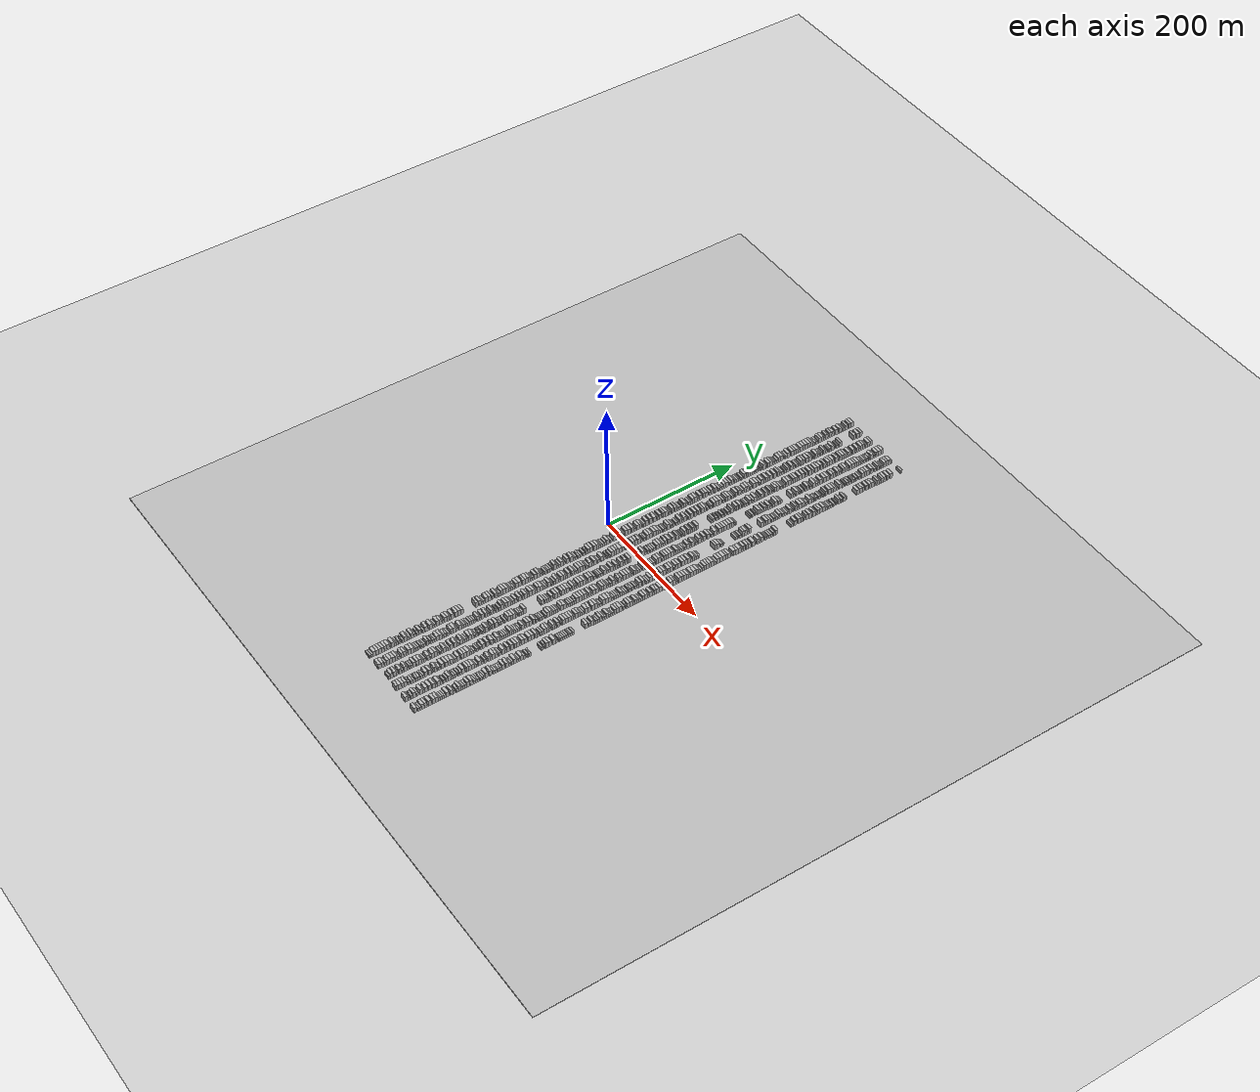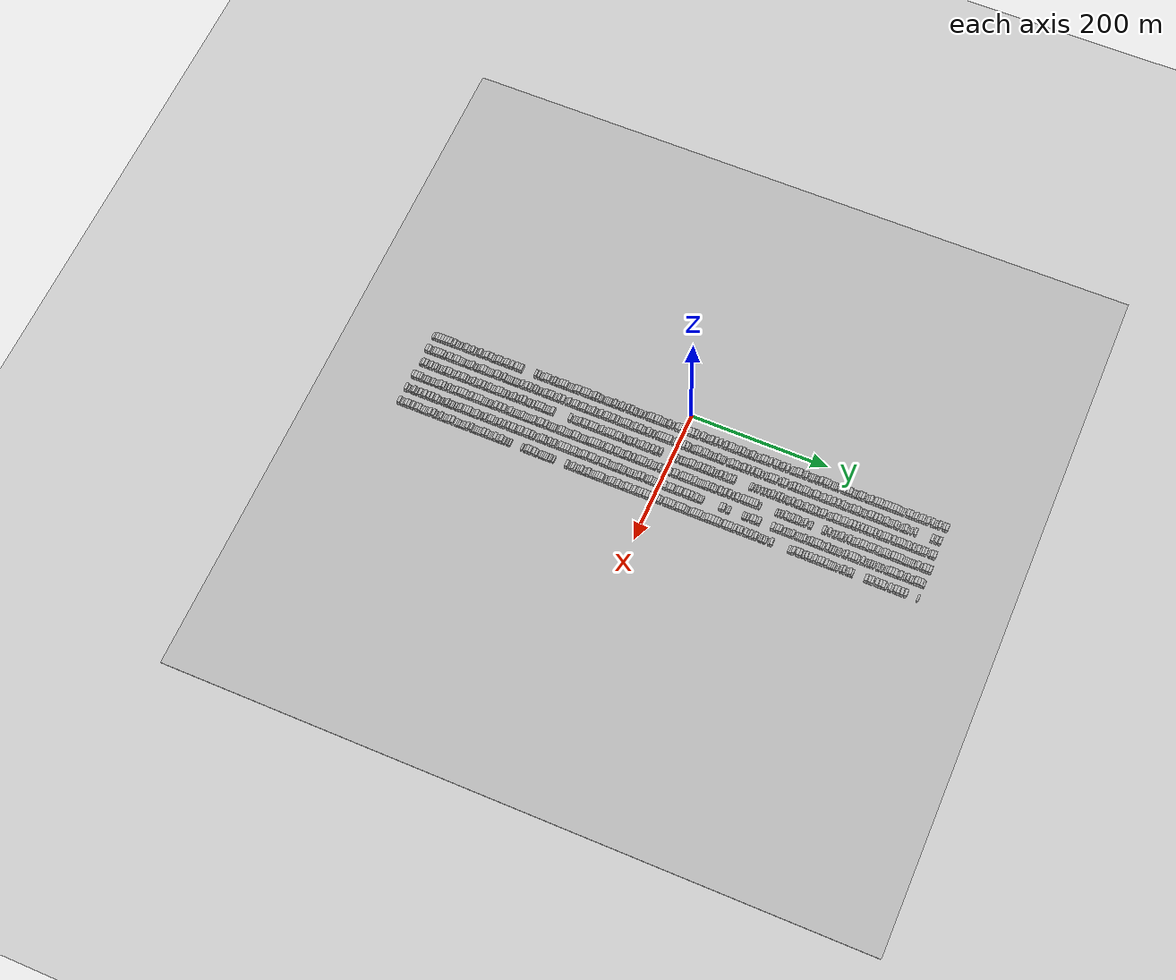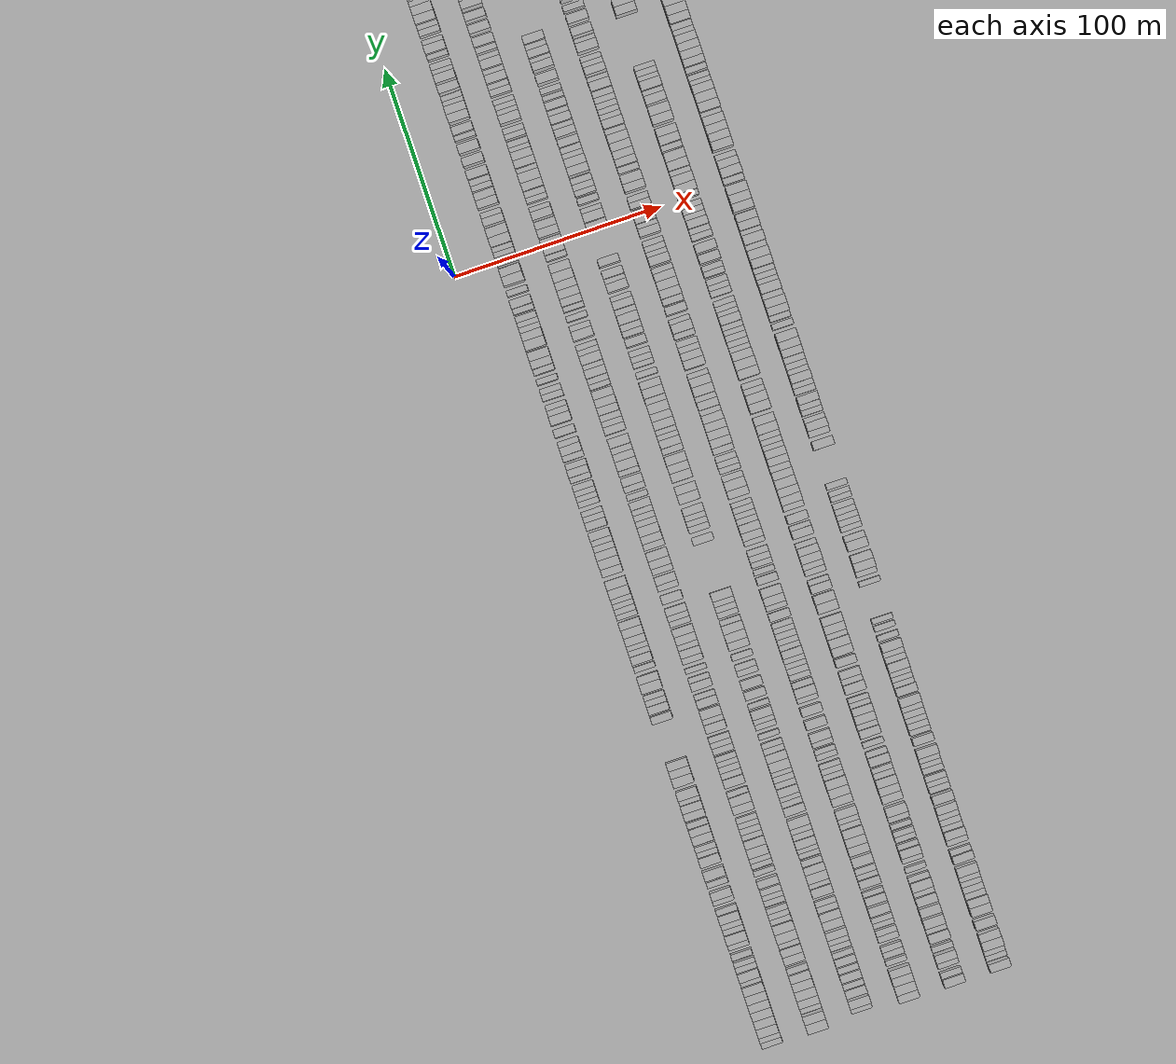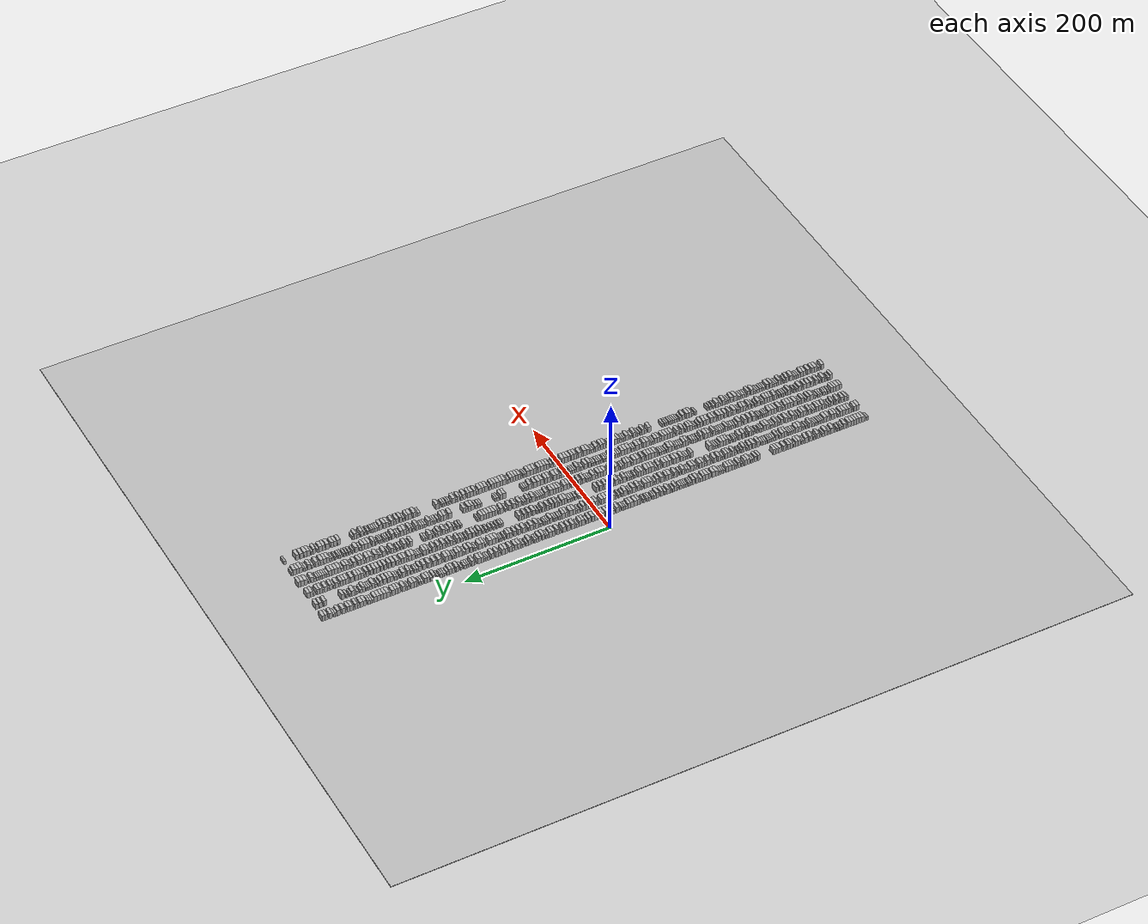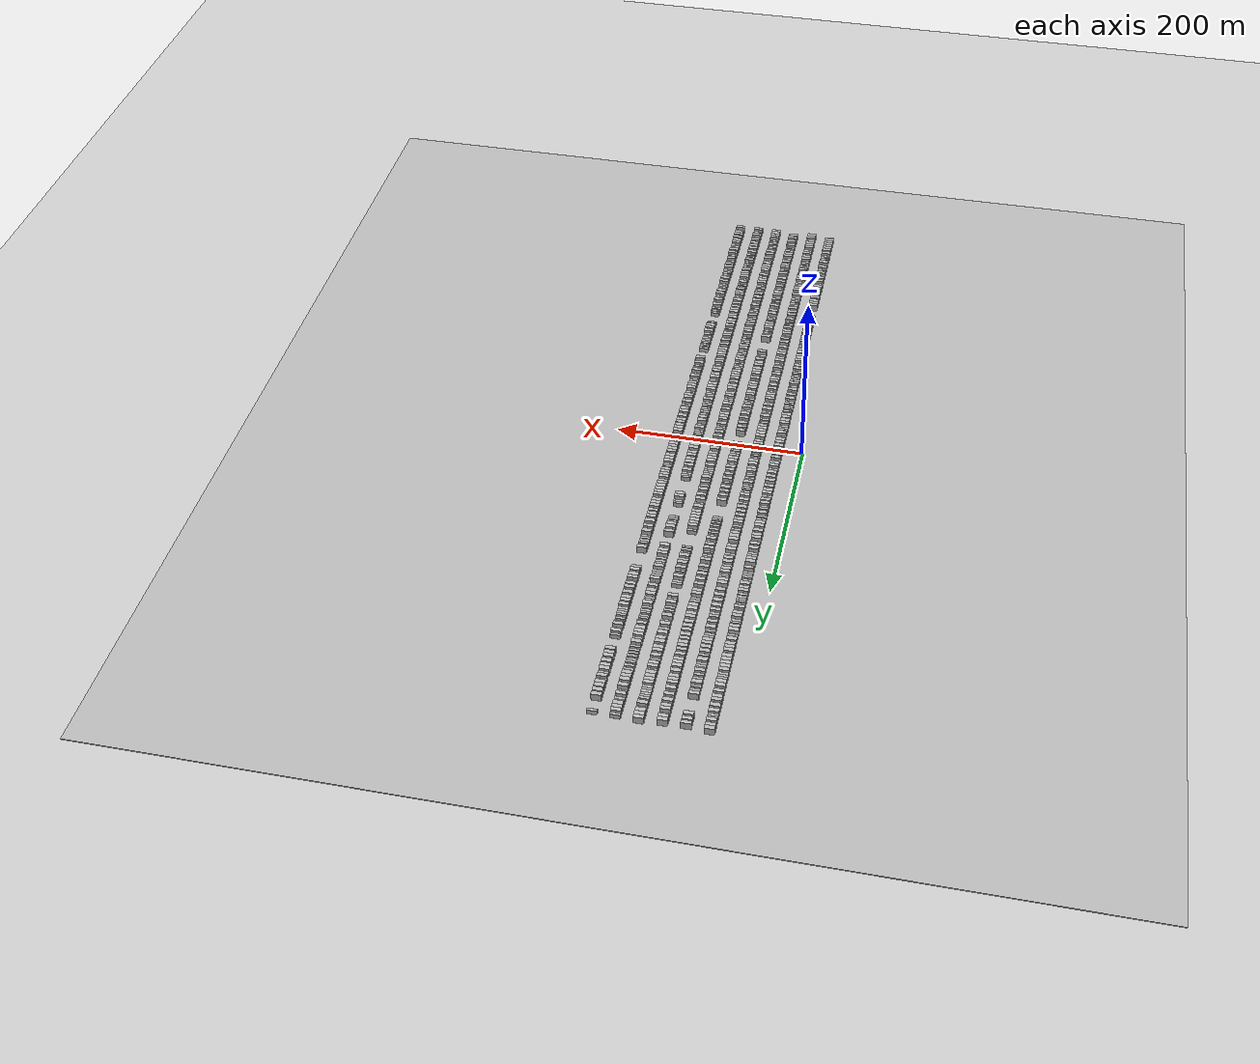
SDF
<?xml version="1.0" encoding="utf-8"?>

<sdf version="1.6">

   <world name="default">

      <gui fullscreen="0">

         <camera name="user_camera">

            <pose>-15 0 4.57585 0 0 0</pose>

            <view_controller>orbit</view_controller>

         </camera>

      </gui>

      <scene>

         <sky>

           <clouds>

             <speed>12</speed>

           </clouds>

         </sky>

         <ambient>0.4 0.4 0.4 1</ambient>

         <background>0.7 0.7 0.7 1</background>

         <shadows>1</shadows>

      </scene>

      <gravity>0 0 -9.8066</gravity>

      <magnetic_field>6e-06 2.3e-05 -4.2e-05</magnetic_field>

      <physics default="0" name="default_physics" type="ode">

         <ode>

            <solver>

               <type>quick</type>

               <iters>10</iters>

               <sor>1.0</sor>

               <use_dynamic_moi_rescaling>0</use_dynamic_moi_rescaling>

            </solver>

            <constraints>

               <cfm>0</cfm>

               <erp>0.2</erp>

               <contact_max_correcting_vel>100</contact_max_correcting_vel>

               <contact_surface_layer>0.001</contact_surface_layer>

            </constraints>

         </ode>

         <max_step_size>0.004</max_step_size>

         <real_time_factor>1</real_time_factor>

         <real_time_update_rate>250</real_time_update_rate>

      </physics>

      <light name="sun" type="directional">

         <cast_shadows>1</cast_shadows>

         <pose>0 0 10 0 0 0</pose>

         <diffuse>0.8 0.8 0.8 1</diffuse>

         <specular>0.2 0.2 0.2 1</specular>

         <attenuation>

            <range>1000</range>

            <constant>0.9</constant>

            <linear>0.01</linear>

            <quadratic>0.001</quadratic>

         </attenuation>

         <direction>-0.5 0.1 -0.9</direction>

      </light>

      <include>

         <name>ground_plane_1</name>

         <uri>model://HANNAS_ground_plane</uri>

         <pose>0 0 0  0 0 0</pose>

      </include>

      <include>

         <name>ground_plane_2</name>

         <uri>model://HANNAS_ground_plane</uri>

         <pose>100 0 0  0 0 0</pose>

      </include>

      <model name="building_1">

         <static>1</static>

         <pose frame="">25.0000 -378.6766 0 0.000000 0.000000 0.000000</pose>

         <link name="link">

            <pose frame="">0 0 3.00 0 0 0</pose>

            <collision name="collision">

               <geometry>

                  <box>

                     <size>10.0000 2.6467 6.0000</size>

                  </box>

               </geometry>

               <max_contacts>10</max_contacts>

               <surface>

                  <contact>

                     <ode/>

                  </contact>

                  <bounce/>

                  <friction>

                     <torsional>

                        <ode/>

                     </torsional>

                     <ode/>

                  </friction>

               </surface>

            </collision>

            <visual name="visual">

               <cast_shadows>0</cast_shadows>

               <geometry>

                  <box>

                     <size>10.0000 2.6467 6.0000</size>

                  </box>

               </geometry>

               <material>

                  <script>

                     <uri>model://HANNAS_wall/materials/scripts</uri>

                     <uri>model://HANNAS_wall/materials/textures</uri>

                     <name>vrc/HANNAS_wall</name>

                  </script>

               </material>

            </visual>

            <self_collide>0</self_collide>

            <enable_wind>0</enable_wind>

            <kinematic>0</kinematic>

         </link>

      </model>

      <model name="building_2">

         <static>1</static>

         <pose frame="">25.0000 -375.9735 0 0.000000 0.000000 0.000000</pose>

         <link name="link">

            <pose frame="">0 0 3.00 0 0 0</pose>

            <collision name="collision">

               <geometry>

                  <box>

                     <size>10.0000 2.7595 6.0000</size>

                  </box>

               </geometry>

               <max_contacts>10</max_contacts>

               <surface>

                  <contact>

                     <ode/>

                  </contact>

                  <bounce/>

                  <friction>

                     <torsional>

                        <ode/>

                     </torsional>

                     <ode/>

                  </friction>

               </surface>

            </collision>

            <visual name="visual">

               <cast_shadows>0</cast_shadows>

               <geometry>

                  <box>

                     <size>10.0000 2.7595 6.0000</size>

                  </box>

               </geometry>

               <material>

                  <script>

                     <uri>model://HANNAS_wall/materials/scripts</uri>

                     <uri>model://HANNAS_wall/materials/textures</uri>

                     <name>vrc/HANNAS_wall</name>

                  </script>

               </material>

            </visual>

            <self_collide>0</self_collide>

            <enable_wind>0</enable_wind>

            <kinematic>0</kinematic>

         </link>

      </model>

      <model name="building_3">

         <static>1</static>

         <pose frame="">25.0000 -372.4828 0 0.000000 0.000000 0.000000</pose>

         <link name="link">

            <pose frame="">0 0 4.50 0 0 0</pose>

            <collision name="collision">

               <geometry>

                  <box>

                     <size>10.0000 4.2218 9.0000</size>

                  </box>

               </geometry>

               <max_contacts>10</max_contacts>

               <surface>

                  <contact>

                     <ode/>

                  </contact>

                  <bounce/>

                  <friction>

                     <torsional>

                        <ode/>

                     </torsional>

                     <ode/>

                  </friction>

               </surface>

            </collision>

            <visual name="visual">

               <cast_shadows>0</cast_shadows>

               <geometry>

                  <box>

                     <size>10.0000 4.2218 9.0000</size>

                  </box>

               </geometry>

               <material>

                  <script>

                     <uri>model://HANNAS_wall/materials/scripts</uri>

                     <uri>model://HANNAS_wall/materials/textures</uri>

                     <name>vrc/HANNAS_wall</name>

                  </script>

               </material>

            </visual>

            <self_collide>0</self_collide>

            <enable_wind>0</enable_wind>

            <kinematic>0</kinematic>

         </link>

      </model>

      <model name="building_4">

         <static>1</static>

         <pose frame="">25.0000 -368.4443 0 0.000000 0.000000 0.000000</pose>

         <link name="link">

            <pose frame="">0 0 4.50 0 0 0</pose>

            <collision name="collision">

               <geometry>

                  <box>

                     <size>10.0000 3.8554 9.0000</size>

                  </box>

               </geometry>

               <max_contacts>10</max_contacts>

               <surface>

                  <contact>

                     <ode/>

                  </contact>

                  <bounce/>

                  <friction>

                     <torsional>

                        <ode/>

                     </torsional>

                     <ode/>

                  </friction>

               </surface>

            </collision>

            <visual name="visual">

               <cast_shadows>0</cast_shadows>

               <geometry>

                  <box>

                     <size>10.0000 3.8554 9.0000</size>

                  </box>

               </geometry>

               <material>

                  <script>

                     <uri>model://HANNAS_wall/materials/scripts</uri>

                     <uri>model://HANNAS_wall/materials/textures</uri>

                     <name>vrc/HANNAS_wall</name>

                  </script>

               </material>

            </visual>

            <self_collide>0</self_collide>

            <enable_wind>0</enable_wind>

            <kinematic>0</kinematic>

         </link>

      </model>

      <model name="building_5">

         <static>1</static>

         <pose frame="">25.0000 -364.5151 0 0.000000 0.000000 0.000000</pose>

         <link name="link">

            <pose frame="">0 0 4.50 0 0 0</pose>

            <collision name="collision">

               <geometry>

                  <box>

                     <size>10.0000 4.0030 9.0000</size>

                  </box>

               </geometry>

               <max_contacts>10</max_contacts>

               <surface>

                  <contact>

                     <ode/>

                  </contact>

                  <bounce/>

                  <friction>

                     <torsional>

                        <ode/>

                     </torsional>

                     <ode/>

                  </friction>

               </surface>

            </collision>

            <visual name="visual">

               <cast_shadows>0</cast_shadows>

               <geometry>

                  <box>

                     <size>10.0000 4.0030 9.0000</size>

                  </box>

               </geometry>

               <material>

                  <script>

                     <uri>model://HANNAS_wall/materials/scripts</uri>

                     <uri>model://HANNAS_wall/materials/textures</uri>

                     <name>vrc/HANNAS_wall</name>

                  </script>

               </material>

            </visual>

            <self_collide>0</self_collide>

            <enable_wind>0</enable_wind>

            <kinematic>0</kinematic>

         </link>

      </model>

      <model name="building_6">

         <static>1</static>

         <pose frame="">25.0000 -360.5762 0 0.000000 0.000000 0.000000</pose>

         <link name="link">

            <pose frame="">0 0 4.50 0 0 0</pose>

            <collision name="collision">

               <geometry>

                  <box>

                     <size>10.0000 3.8748 9.0000</size>

                  </box>

               </geometry>

               <max_contacts>10</max_contacts>

               <surface>

                  <contact>

                     <ode/>

                  </contact>

                  <bounce/>

                  <friction>

                     <torsional>

                        <ode/>

                     </torsional>

                     <ode/>

                  </friction>

               </surface>

            </collision>

            <visual name="visual">

               <cast_shadows>0</cast_shadows>

               <geometry>

                  <box>

                     <size>10.0000 3.8748 9.0000</size>

                  </box>

               </geometry>

               <material>

                  <script>

                     <uri>model://HANNAS_wall/materials/scripts</uri>

                     <uri>model://HANNAS_wall/materials/textures</uri>

                     <name>vrc/HANNAS_wall</name>

                  </script>

               </material>

            </visual>

            <self_collide>0</self_collide>

            <enable_wind>0</enable_wind>

            <kinematic>0</kinematic>

         </link>

      </model>

      <model name="building_7">

         <static>1</static>

         <pose frame="">25.0000 -356.6111 0 0.000000 0.000000 0.000000</pose>

         <link name="link">

            <pose frame="">0 0 4.50 0 0 0</pose>

            <collision name="collision">

               <geometry>

                  <box>

                     <size>10.0000 4.0552 9.0000</size>

                  </box>

               </geometry>

               <max_contacts>10</max_contacts>

               <surface>

                  <contact>

                     <ode/>

                  </contact>

                  <bounce/>

                  <friction>

                     <torsional>

                        <ode/>

                     </torsional>

                     <ode/>

                  </friction>

               </surface>

            </collision>

            <visual name="visual">

               <cast_shadows>0</cast_shadows>

               <geometry>

                  <box>

                     <size>10.0000 4.0552 9.0000</size>

                  </box>

               </geometry>

               <material>

                  <script>

                     <uri>model://HANNAS_wall/materials/scripts</uri>

                     <uri>model://HANNAS_wall/materials/textures</uri>

                     <name>vrc/HANNAS_wall</name>

                  </script>

               </material>

            </visual>

            <self_collide>0</self_collide>

            <enable_wind>0</enable_wind>

            <kinematic>0</kinematic>

         </link>

      </model>

      <model name="building_8">

         <static>1</static>

         <pose frame="">25.0000 -352.4571 0 0.000000 0.000000 0.000000</pose>

         <link name="link">

            <pose frame="">0 0 4.50 0 0 0</pose>

            <collision name="collision">

               <geometry>

                  <box>

                     <size>10.0000 4.2529 9.0000</size>

                  </box>

               </geometry>

               <max_contacts>10</max_contacts>

               <surface>

                  <contact>

                     <ode/>

                  </contact>

                  <bounce/>

                  <friction>

                     <torsional>

                        <ode/>

                     </torsional>

                     <ode/>

                  </friction>

               </surface>

            </collision>

            <visual name="visual">

               <cast_shadows>0</cast_shadows>

               <geometry>

                  <box>

                     <size>10.0000 4.2529 9.0000</size>

                  </box>

               </geometry>

               <material>

                  <script>

                     <uri>model://HANNAS_wall/materials/scripts</uri>

                     <uri>model://HANNAS_wall/materials/textures</uri>

                     <name>vrc/HANNAS_wall</name>

                  </script>

               </material>

            </visual>

            <self_collide>0</self_collide>

            <enable_wind>0</enable_wind>

            <kinematic>0</kinematic>

         </link>

      </model>

      <model name="building_9">

         <static>1</static>

         <pose frame="">25.0000 -349.1111 0 0.000000 0.000000 0.000000</pose>

         <link name="link">

            <pose frame="">0 0 3.00 0 0 0</pose>

            <collision name="collision">

               <geometry>

                  <box>

                     <size>10.0000 2.4390 6.0000</size>

                  </box>

               </geometry>

               <max_contacts>10</max_contacts>

               <surface>

                  <contact>

                     <ode/>

                  </contact>

                  <bounce/>

                  <friction>

                     <torsional>

                        <ode/>

                     </torsional>

                     <ode/>

                  </friction>

               </surface>

            </collision>

            <visual name="visual">

               <cast_shadows>0</cast_shadows>

               <geometry>

                  <box>

                     <size>10.0000 2.4390 6.0000</size>

                  </box>

               </geometry>

               <material>

                  <script>

                     <uri>model://HANNAS_wall/materials/scripts</uri>

                     <uri>model://HANNAS_wall/materials/textures</uri>

                     <name>vrc/HANNAS_wall</name>

                  </script>

               </material>

            </visual>

            <self_collide>0</self_collide>

            <enable_wind>0</enable_wind>

            <kinematic>0</kinematic>

         </link>

      </model>

      <model name="building_10">

         <static>1</static>

         <pose frame="">25.0000 -345.8129 0 0.000000 0.000000 0.000000</pose>

         <link name="link">

            <pose frame="">0 0 4.50 0 0 0</pose>

            <collision name="collision">

               <geometry>

                  <box>

                     <size>10.0000 4.1575 9.0000</size>

                  </box>

               </geometry>

               <max_contacts>10</max_contacts>

               <surface>

                  <contact>

                     <ode/>

                  </contact>

                  <bounce/>

                  <friction>

                     <torsional>

                        <ode/>

                     </torsional>

                     <ode/>

                  </friction>

               </surface>

            </collision>

            <visual name="visual">

               <cast_shadows>0</cast_shadows>

               <geometry>

                  <box>

                     <size>10.0000 4.1575 9.0000</size>

                  </box>

               </geometry>

               <material>

                  <script>

                     <uri>model://HANNAS_wall/materials/scripts</uri>

                     <uri>model://HANNAS_wall/materials/textures</uri>

                     <name>vrc/HANNAS_wall</name>

                  </script>

               </material>

            </visual>

            <self_collide>0</self_collide>

            <enable_wind>0</enable_wind>

            <kinematic>0</kinematic>

         </link>

      </model>

      <model name="building_11">

         <static>1</static>

         <pose frame="">25.0000 -342.3596 0 0.000000 0.000000 0.000000</pose>

         <link name="link">

            <pose frame="">0 0 3.00 0 0 0</pose>

            <collision name="collision">

               <geometry>

                  <box>

                     <size>10.0000 2.7490 6.0000</size>

                  </box>

               </geometry>

               <max_contacts>10</max_contacts>

               <surface>

                  <contact>

                     <ode/>

                  </contact>

                  <bounce/>

                  <friction>

                     <torsional>

                        <ode/>

                     </torsional>

                     <ode/>

                  </friction>

               </surface>

            </collision>

            <visual name="visual">

               <cast_shadows>0</cast_shadows>

               <geometry>

                  <box>

                     <size>10.0000 2.7490 6.0000</size>

                  </box>

               </geometry>

               <material>

                  <script>

                     <uri>model://HANNAS_wall/materials/scripts</uri>

                     <uri>model://HANNAS_wall/materials/textures</uri>

                     <name>vrc/HANNAS_wall</name>

                  </script>

               </material>

            </visual>

            <self_collide>0</self_collide>

            <enable_wind>0</enable_wind>

            <kinematic>0</kinematic>

         </link>

      </model>

      <model name="building_12">

         <static>1</static>

         <pose frame="">25.0000 -339.7796 0 0.000000 0.000000 0.000000</pose>

         <link name="link">

            <pose frame="">0 0 3.00 0 0 0</pose>

            <collision name="collision">

               <geometry>

                  <box>

                     <size>10.0000 2.4109 6.0000</size>

                  </box>

               </geometry>

               <max_contacts>10</max_contacts>

               <surface>

                  <contact>

                     <ode/>

                  </contact>

                  <bounce/>

                  <friction>

                     <torsional>

                        <ode/>

                     </torsional>

                     <ode/>

                  </friction>

               </surface>

            </collision>

            <visual name="visual">

               <cast_shadows>0</cast_shadows>

               <geometry>

                  <box>

                     <size>10.0000 2.4109 6.0000</size>

                  </box>

               </geometry>

               <material>

                  <script>

                     <uri>model://HANNAS_wall/materials/scripts</uri>

                     <uri>model://HANNAS_wall/materials/textures</uri>

                     <name>vrc/HANNAS_wall</name>

                  </script>

               </material>

            </visual>

            <self_collide>0</self_collide>

            <enable_wind>0</enable_wind>

            <kinematic>0</kinematic>

         </link>

      </model>

      <model name="building_13">

         <static>1</static>

         <pose frame="">25.0000 -336.1206 0 0.000000 0.000000 0.000000</pose>

         <link name="link">

            <pose frame="">0 0 3.00 0 0 0</pose>

            <collision name="collision">

               <geometry>

                  <box>

                     <size>10.0000 2.9071 6.0000</size>

                  </box>

               </geometry>

               <max_contacts>10</max_contacts>

               <surface>

                  <contact>

                     <ode/>

                  </contact>

                  <bounce/>

                  <friction>

                     <torsional>

                        <ode/>

                     </torsional>

                     <ode/>

                  </friction>

               </surface>

            </collision>

            <visual name="visual">

               <cast_shadows>0</cast_shadows>

               <geometry>

                  <box>

                     <size>10.0000 2.9071 6.0000</size>

                  </box>

               </geometry>

               <material>

                  <script>

                     <uri>model://HANNAS_wall/materials/scripts</uri>

                     <uri>model://HANNAS_wall/materials/textures</uri>

                     <name>vrc/HANNAS_wall</name>

                  </script>

               </material>

            </visual>

            <self_collide>0</self_collide>

            <enable_wind>0</enable_wind>

            <kinematic>0</kinematic>

         </link>

      </model>

      <model name="building_14">

         <static>1</static>

         <pose frame="">25.0000 -331.3287 0 0.000000 0.000000 0.000000</pose>

         <link name="link">

            <pose frame="">0 0 3.00 0 0 0</pose>

            <collision name="collision">

               <geometry>

                  <box>

                     <size>10.0000 2.6767 6.0000</size>

                  </box>

               </geometry>

               <max_contacts>10</max_contacts>

               <surface>

                  <contact>

                     <ode/>

                  </contact>

                  <bounce/>

                  <friction>

                     <torsional>

                        <ode/>

                     </torsional>

                     <ode/>

                  </friction>

               </surface>

            </collision>

            <visual name="visual">

               <cast_shadows>0</cast_shadows>

               <geometry>

                  <box>

                     <size>10.0000 2.6767 6.0000</size>

                  </box>

               </geometry>

               <material>

                  <script>

                     <uri>model://HANNAS_wall/materials/scripts</uri>

                     <uri>model://HANNAS_wall/materials/textures</uri>

                     <name>vrc/HANNAS_wall</name>

                  </script>

               </material>

            </visual>

            <self_collide>0</self_collide>

            <enable_wind>0</enable_wind>

            <kinematic>0</kinematic>

         </link>

      </model>

      <model name="building_15">

         <static>1</static>

         <pose frame="">25.0000 -327.7732 0 0.000000 0.000000 0.000000</pose>

         <link name="link">

            <pose frame="">0 0 4.50 0 0 0</pose>

            <collision name="collision">

               <geometry>

                  <box>

                     <size>10.0000 4.4344 9.0000</size>

                  </box>

               </geometry>

               <max_contacts>10</max_contacts>

               <surface>

                  <contact>

                     <ode/>

                  </contact>

                  <bounce/>

                  <friction>

                     <torsional>

                        <ode/>

                     </torsional>

                     <ode/>

                  </friction>

               </surface>

            </collision>

            <visual name="visual">

               <cast_shadows>0</cast_shadows>

               <geometry>

                  <box>

                     <size>10.0000 4.4344 9.0000</size>

                  </box>

               </geometry>

               <material>

                  <script>

                     <uri>model://HANNAS_wall/materials/scripts</uri>

                     <uri>model://HANNAS_wall/materials/textures</uri>

                     <name>vrc/HANNAS_wall</name>

                  </script>

               </material>

            </visual>

            <self_collide>0</self_collide>

            <enable_wind>0</enable_wind>

            <kinematic>0</kinematic>

         </link>

      </model>

      <model name="building_16">

         <static>1</static>

         <pose frame="">25.0000 -324.2370 0 0.000000 0.000000 0.000000</pose>

         <link name="link">

            <pose frame="">0 0 3.00 0 0 0</pose>

            <collision name="collision">

               <geometry>

                  <box>

                     <size>10.0000 2.6379 6.0000</size>

                  </box>

               </geometry>

               <max_contacts>10</max_contacts>

               <surface>

                  <contact>

                     <ode/>

                  </contact>

                  <bounce/>

                  <friction>

                     <torsional>

                        <ode/>

                     </torsional>

                     <ode/>

                  </friction>

               </surface>

            </collision>

            <visual name="visual">

               <cast_shadows>0</cast_shadows>

               <geometry>

                  <box>

                     <size>10.0000 2.6379 6.0000</size>

                  </box>

               </geometry>

               <material>

                  <script>

                     <uri>model://HANNAS_wall/materials/scripts</uri>

                     <uri>model://HANNAS_wall/materials/textures</uri>

                     <name>vrc/HANNAS_wall</name>

                  </script>

               </material>

            </visual>

            <self_collide>0</self_collide>

            <enable_wind>0</enable_wind>

            <kinematic>0</kinematic>

         </link>

      </model>

      <model name="building_17">

         <static>1</static>

         <pose frame="">25.0000 -321.4824 0 0.000000 0.000000 0.000000</pose>

         <link name="link">

            <pose frame="">0 0 3.00 0 0 0</pose>

            <collision name="collision">

               <geometry>

                  <box>

                     <size>10.0000 2.8713 6.0000</size>

                  </box>

               </geometry>

               <max_contacts>10</max_contacts>

               <surface>

                  <contact>

                     <ode/>

                  </contact>

                  <bounce/>

                  <friction>

                     <torsional>

                        <ode/>

                     </torsional>

                     <ode/>

                  </friction>

               </surface>

            </collision>

            <visual name="visual">

               <cast_shadows>0</cast_shadows>

               <geometry>

                  <box>

                     <size>10.0000 2.8713 6.0000</size>

                  </box>

               </geometry>

               <material>

                  <script>

                     <uri>model://HANNAS_wall/materials/scripts</uri>

                     <uri>model://HANNAS_wall/materials/textures</uri>

                     <name>vrc/HANNAS_wall</name>

                  </script>

               </material>

            </visual>

            <self_collide>0</self_collide>

            <enable_wind>0</enable_wind>

            <kinematic>0</kinematic>

         </link>

      </model>

      <model name="building_18">

         <static>1</static>

         <pose frame="">25.0000 -318.0040 0 0.000000 0.000000 0.000000</pose>

         <link name="link">

            <pose frame="">0 0 4.50 0 0 0</pose>

            <collision name="collision">

               <geometry>

                  <box>

                     <size>10.0000 4.0855 9.0000</size>

                  </box>

               </geometry>

               <max_contacts>10</max_contacts>

               <surface>

                  <contact>

                     <ode/>

                  </contact>

                  <bounce/>

                  <friction>

                     <torsional>

                        <ode/>

                     </torsional>

                     <ode/>

                  </friction>

               </surface>

            </collision>

            <visual name="visual">

               <cast_shadows>0</cast_shadows>

               <geometry>

                  <box>

                     <size>10.0000 4.0855 9.0000</size>

                  </box>

               </geometry>

               <material>

                  <script>

                     <uri>model://HANNAS_wall/materials/scripts</uri>

                     <uri>model://HANNAS_wall/materials/textures</uri>

                     <name>vrc/HANNAS_wall</name>

                  </script>

               </material>

            </visual>

            <self_collide>0</self_collide>

            <enable_wind>0</enable_wind>

            <kinematic>0</kinematic>

         </link>

      </model>

      <model name="building_19">

         <static>1</static>

         <pose frame="">25.0000 -314.5131 0 0.000000 0.000000 0.000000</pose>

         <link name="link">

            <pose frame="">0 0 3.00 0 0 0</pose>

            <collision name="collision">

               <geometry>

                  <box>

                     <size>10.0000 2.8964 6.0000</size>

                  </box>

               </geometry>

               <max_contacts>10</max_contacts>

               <surface>

                  <contact>

                     <ode/>

                  </contact>

                  <bounce/>

                  <friction>

                     <torsional>

                        <ode/>

                     </torsional>

                     <ode/>

                  </friction>

               </surface>

            </collision>

            <visual name="visual">

               <cast_shadows>0</cast_shadows>

               <geometry>

                  <box>

                     <size>10.0000 2.8964 6.0000</size>

                  </box>

               </geometry>

               <material>

                  <script>

                     <uri>model://HANNAS_wall/materials/scripts</uri>

                     <uri>model://HANNAS_wall/materials/textures</uri>

                     <name>vrc/HANNAS_wall</name>

                  </script>

               </material>

            </visual>

            <self_collide>0</self_collide>

            <enable_wind>0</enable_wind>

            <kinematic>0</kinematic>

         </link>

      </model>

      <model name="building_20">

         <static>1</static>

         <pose frame="">25.0000 -309.8184 0 0.000000 0.000000 0.000000</pose>

         <link name="link">

            <pose frame="">0 0 3.00 0 0 0</pose>

            <collision name="collision">

               <geometry>

                  <box>

                     <size>10.0000 2.4929 6.0000</size>

                  </box>

               </geometry>

               <max_contacts>10</max_contacts>

               <surface>

                  <contact>

                     <ode/>

                  </contact>

                  <bounce/>

                  <friction>

                     <torsional>

                        <ode/>

                     </torsional>

                     <ode/>

                  </friction>

               </surface>

            </collision>

            <visual name="visual">

               <cast_shadows>0</cast_shadows>

               <geometry>

                  <box>

                     <size>10.0000 2.4929 6.0000</size>

                  </box>

               </geometry>

               <material>

                  <script>

                     <uri>model://HANNAS_wall/materials/scripts</uri>

                     <uri>model://HANNAS_wall/materials/textures</uri>

                     <name>vrc/HANNAS_wall</name>

                  </script>

               </material>

            </visual>

            <self_collide>0</self_collide>

            <enable_wind>0</enable_wind>

            <kinematic>0</kinematic>

         </link>

      </model>

      <model name="building_21">

         <static>1</static>

         <pose frame="">25.0000 -306.5983 0 0.000000 0.000000 0.000000</pose>

         <link name="link">

            <pose frame="">0 0 4.50 0 0 0</pose>

            <collision name="collision">

               <geometry>

                  <box>

                     <size>10.0000 3.9474 9.0000</size>

                  </box>

               </geometry>

               <max_contacts>10</max_contacts>

               <surface>

                  <contact>

                     <ode/>

                  </contact>

                  <bounce/>

                  <friction>

                     <torsional>

                        <ode/>

                     </torsional>

                     <ode/>

                  </friction>

               </surface>

            </collision>

            <visual name="visual">

               <cast_shadows>0</cast_shadows>

               <geometry>

                  <box>

                     <size>10.0000 3.9474 9.0000</size>

                  </box>

               </geometry>

               <material>

                  <script>

                     <uri>model://HANNAS_wall/materials/scripts</uri>

                     <uri>model://HANNAS_wall/materials/textures</uri>

                     <name>vrc/HANNAS_wall</name>

                  </script>

               </material>

            </visual>

            <self_collide>0</self_collide>

            <enable_wind>0</enable_wind>

            <kinematic>0</kinematic>

         </link>

      </model>

      <model name="building_22">

         <static>1</static>

         <pose frame="">25.0000 -301.3023 0 0.000000 0.000000 0.000000</pose>

         <link name="link">

            <pose frame="">0 0 3.00 0 0 0</pose>

            <collision name="collision">

               <geometry>

                  <box>

                     <size>10.0000 2.6446 6.0000</size>

                  </box>

               </geometry>

               <max_contacts>10</max_contacts>

               <surface>

                  <contact>

                     <ode/>

                  </contact>

                  <bounce/>

                  <friction>

                     <torsional>

                        <ode/>

                     </torsional>

                     <ode/>

                  </friction>

               </surface>

            </collision>

            <visual name="visual">

               <cast_shadows>0</cast_shadows>

               <geometry>

                  <box>

                     <size>10.0000 2.6446 6.0000</size>

                  </box>

               </geometry>

               <material>

                  <script>

                     <uri>model://HANNAS_wall/materials/scripts</uri>

                     <uri>model://HANNAS_wall/materials/textures</uri>

                     <name>vrc/HANNAS_wall</name>

                  </script>

               </material>

            </visual>

            <self_collide>0</self_collide>

            <enable_wind>0</enable_wind>

            <kinematic>0</kinematic>

         </link>

      </model>

      <model name="building_23">

         <static>1</static>

         <pose frame="">25.0000 -296.7561 0 0.000000 0.000000 0.000000</pose>

         <link name="link">

            <pose frame="">0 0 4.50 0 0 0</pose>

            <collision name="collision">

               <geometry>

                  <box>

                     <size>10.0000 4.4478 9.0000</size>

                  </box>

               </geometry>

               <max_contacts>10</max_contacts>

               <surface>

                  <contact>

                     <ode/>

                  </contact>

                  <bounce/>

                  <friction>

                     <torsional>

                        <ode/>

                     </torsional>

                     <ode/>

                  </friction>

               </surface>

            </collision>

            <visual name="visual">

               <cast_shadows>0</cast_shadows>

               <geometry>

                  <box>

                     <size>10.0000 4.4478 9.0000</size>

                  </box>

               </geometry>

               <material>

                  <script>

                     <uri>model://HANNAS_wall/materials/scripts</uri>

                     <uri>model://HANNAS_wall/materials/textures</uri>

                     <name>vrc/HANNAS_wall</name>

                  </script>

               </material>

            </visual>

            <self_collide>0</self_collide>

            <enable_wind>0</enable_wind>

            <kinematic>0</kinematic>

         </link>

      </model>

      <model name="building_24">

         <static>1</static>

         <pose frame="">25.0000 -290.3168 0 0.000000 0.000000 0.000000</pose>

         <link name="link">

            <pose frame="">0 0 4.50 0 0 0</pose>

            <collision name="collision">

               <geometry>

                  <box>

                     <size>10.0000 4.4309 9.0000</size>

                  </box>

               </geometry>

               <max_contacts>10</max_contacts>

               <surface>

                  <contact>

                     <ode/>

                  </contact>

                  <bounce/>

                  <friction>

                     <torsional>

                        <ode/>

                     </torsional>

                     <ode/>

                  </friction>

               </surface>

            </collision>

            <visual name="visual">

               <cast_shadows>0</cast_shadows>

               <geometry>

                  <box>

                     <size>10.0000 4.4309 9.0000</size>

                  </box>

               </geometry>

               <material>

                  <script>

                     <uri>model://HANNAS_wall/materials/scripts</uri>

                     <uri>model://HANNAS_wall/materials/textures</uri>

                     <name>vrc/HANNAS_wall</name>

                  </script>

               </material>

            </visual>

            <self_collide>0</self_collide>

            <enable_wind>0</enable_wind>

            <kinematic>0</kinematic>

         </link>

      </model>

      <model name="building_25">

         <static>1</static>

         <pose frame="">25.0000 -286.8578 0 0.000000 0.000000 0.000000</pose>

         <link name="link">

            <pose frame="">0 0 3.00 0 0 0</pose>

            <collision name="collision">

               <geometry>

                  <box>

                     <size>10.0000 2.4871 6.0000</size>

                  </box>

               </geometry>

               <max_contacts>10</max_contacts>

               <surface>

                  <contact>

                     <ode/>

                  </contact>

                  <bounce/>

                  <friction>

                     <torsional>

                        <ode/>

                     </torsional>

                     <ode/>

                  </friction>

               </surface>

            </collision>

            <visual name="visual">

               <cast_shadows>0</cast_shadows>

               <geometry>

                  <box>

                     <size>10.0000 2.4871 6.0000</size>

                  </box>

               </geometry>

               <material>

                  <script>

                     <uri>model://HANNAS_wall/materials/scripts</uri>

                     <uri>model://HANNAS_wall/materials/textures</uri>

                     <name>vrc/HANNAS_wall</name>

                  </script>

               </material>

            </visual>

            <self_collide>0</self_collide>

            <enable_wind>0</enable_wind>

            <kinematic>0</kinematic>

         </link>

      </model>

      <model name="building_26">

         <static>1</static>

         <pose frame="">25.0000 -284.2672 0 0.000000 0.000000 0.000000</pose>

         <link name="link">

            <pose frame="">0 0 3.00 0 0 0</pose>

            <collision name="collision">

               <geometry>

                  <box>

                     <size>10.0000 2.6942 6.0000</size>

                  </box>

               </geometry>

               <max_contacts>10</max_contacts>

               <surface>

                  <contact>

                     <ode/>

                  </contact>

                  <bounce/>

                  <friction>

                     <torsional>

                        <ode/>

                     </torsional>

                     <ode/>

                  </friction>

               </surface>

            </collision>

            <visual name="visual">

               <cast_shadows>0</cast_shadows>

               <geometry>

                  <box>

                     <size>10.0000 2.6942 6.0000</size>

                  </box>

               </geometry>

               <material>

                  <script>

                     <uri>model://HANNAS_wall/materials/scripts</uri>

                     <uri>model://HANNAS_wall/materials/textures</uri>

                     <name>vrc/HANNAS_wall</name>

                  </script>

               </material>

            </visual>

            <self_collide>0</self_collide>

            <enable_wind>0</enable_wind>

            <kinematic>0</kinematic>

         </link>

      </model>

      <model name="building_27">

         <static>1</static>

         <pose frame="">25.0000 -279.8970 0 0.000000 0.000000 0.000000</pose>

         <link name="link">

            <pose frame="">0 0 4.50 0 0 0</pose>

            <collision name="collision">

               <geometry>

                  <box>

                     <size>10.0000 4.0460 9.0000</size>

                  </box>

               </geometry>

               <max_contacts>10</max_contacts>

               <surface>

                  <contact>

                     <ode/>

                  </contact>

                  <bounce/>

                  <friction>

                     <torsional>

                        <ode/>

                     </torsional>

                     <ode/>

                  </friction>

               </surface>

            </collision>

            <visual name="visual">

               <cast_shadows>0</cast_shadows>

               <geometry>

                  <box>

                     <size>10.0000 4.0460 9.0000</size>

                  </box>

               </geometry>

               <material>

                  <script>

                     <uri>model://HANNAS_wall/materials/scripts</uri>

                     <uri>model://HANNAS_wall/materials/textures</uri>

                     <name>vrc/HANNAS_wall</name>

                  </script>

               </material>

            </visual>

            <self_collide>0</self_collide>

            <enable_wind>0</enable_wind>

            <kinematic>0</kinematic>

         </link>

      </model>

      <model name="building_28">

         <static>1</static>

         <pose frame="">25.0000 -276.0623 0 0.000000 0.000000 0.000000</pose>

         <link name="link">

            <pose frame="">0 0 4.50 0 0 0</pose>

            <collision name="collision">

               <geometry>

                  <box>

                     <size>10.0000 3.6234 9.0000</size>

                  </box>

               </geometry>

               <max_contacts>10</max_contacts>

               <surface>

                  <contact>

                     <ode/>

                  </contact>

                  <bounce/>

                  <friction>

                     <torsional>

                        <ode/>

                     </torsional>

                     <ode/>

                  </friction>

               </surface>

            </collision>

            <visual name="visual">

               <cast_shadows>0</cast_shadows>

               <geometry>

                  <box>

                     <size>10.0000 3.6234 9.0000</size>

                  </box>

               </geometry>

               <material>

                  <script>

                     <uri>model://HANNAS_wall/materials/scripts</uri>

                     <uri>model://HANNAS_wall/materials/textures</uri>

                     <name>vrc/HANNAS_wall</name>

                  </script>

               </material>

            </visual>

            <self_collide>0</self_collide>

            <enable_wind>0</enable_wind>

            <kinematic>0</kinematic>

         </link>

      </model>

      <model name="building_29">

         <static>1</static>

         <pose frame="">25.0000 -272.7906 0 0.000000 0.000000 0.000000</pose>

         <link name="link">

            <pose frame="">0 0 3.00 0 0 0</pose>

            <collision name="collision">

               <geometry>

                  <box>

                     <size>10.0000 2.9201 6.0000</size>

                  </box>

               </geometry>

               <max_contacts>10</max_contacts>

               <surface>

                  <contact>

                     <ode/>

                  </contact>

                  <bounce/>

                  <friction>

                     <torsional>

                        <ode/>

                     </torsional>

                     <ode/>

                  </friction>

               </surface>

            </collision>

            <visual name="visual">

               <cast_shadows>0</cast_shadows>

               <geometry>

                  <box>

                     <size>10.0000 2.9201 6.0000</size>

                  </box>

               </geometry>

               <material>

                  <script>

                     <uri>model://HANNAS_wall/materials/scripts</uri>

                     <uri>model://HANNAS_wall/materials/textures</uri>

                     <name>vrc/HANNAS_wall</name>

                  </script>

               </material>

            </visual>

            <self_collide>0</self_collide>

            <enable_wind>0</enable_wind>

            <kinematic>0</kinematic>

         </link>

      </model>

      <model name="building_30">

         <static>1</static>

         <pose frame="">25.0000 -268.4911 0 0.000000 0.000000 0.000000</pose>

         <link name="link">

            <pose frame="">0 0 4.50 0 0 0</pose>

            <collision name="collision">

               <geometry>

                  <box>

                     <size>10.0000 3.6790 9.0000</size>

                  </box>

               </geometry>

               <max_contacts>10</max_contacts>

               <surface>

                  <contact>

                     <ode/>

                  </contact>

                  <bounce/>

                  <friction>

                     <torsional>

                        <ode/>

                     </torsional>

                     <ode/>

                  </friction>

               </surface>

            </collision>

            <visual name="visual">

               <cast_shadows>0</cast_shadows>

               <geometry>

                  <box>

                     <size>10.0000 3.6790 9.0000</size>

                  </box>

               </geometry>

               <material>

                  <script>

                     <uri>model://HANNAS_wall/materials/scripts</uri>

                     <uri>model://HANNAS_wall/materials/textures</uri>

                     <name>vrc/HANNAS_wall</name>

                  </script>

               </material>

            </visual>

            <self_collide>0</self_collide>

            <enable_wind>0</enable_wind>

            <kinematic>0</kinematic>

         </link>

      </model>

      <model name="building_31">

         <static>1</static>

         <pose frame="">25.0000 -264.7799 0 0.000000 0.000000 0.000000</pose>

         <link name="link">

            <pose frame="">0 0 4.50 0 0 0</pose>

            <collision name="collision">

               <geometry>

                  <box>

                     <size>10.0000 3.7434 9.0000</size>

                  </box>

               </geometry>

               <max_contacts>10</max_contacts>

               <surface>

                  <contact>

                     <ode/>

                  </contact>

                  <bounce/>

                  <friction>

                     <torsional>

                        <ode/>

                     </torsional>

                     <ode/>

                  </friction>

               </surface>

            </collision>

            <visual name="visual">

               <cast_shadows>0</cast_shadows>

               <geometry>

                  <box>

                     <size>10.0000 3.7434 9.0000</size>

                  </box>

               </geometry>

               <material>

                  <script>

                     <uri>model://HANNAS_wall/materials/scripts</uri>

                     <uri>model://HANNAS_wall/materials/textures</uri>

                     <name>vrc/HANNAS_wall</name>

                  </script>

               </material>

            </visual>

            <self_collide>0</self_collide>

            <enable_wind>0</enable_wind>

            <kinematic>0</kinematic>

         </link>

      </model>

      <model name="building_32">

         <static>1</static>

         <pose frame="">25.0000 -261.6918 0 0.000000 0.000000 0.000000</pose>

         <link name="link">

            <pose frame="">0 0 3.00 0 0 0</pose>

            <collision name="collision">

               <geometry>

                  <box>

                     <size>10.0000 2.4328 6.0000</size>

                  </box>

               </geometry>

               <max_contacts>10</max_contacts>

               <surface>

                  <contact>

                     <ode/>

                  </contact>

                  <bounce/>

                  <friction>

                     <torsional>

                        <ode/>

                     </torsional>

                     <ode/>

                  </friction>

               </surface>

            </collision>

            <visual name="visual">

               <cast_shadows>0</cast_shadows>

               <geometry>

                  <box>

                     <size>10.0000 2.4328 6.0000</size>

                  </box>

               </geometry>

               <material>

                  <script>

                     <uri>model://HANNAS_wall/materials/scripts</uri>

                     <uri>model://HANNAS_wall/materials/textures</uri>

                     <name>vrc/HANNAS_wall</name>

                  </script>

               </material>

            </visual>

            <self_collide>0</self_collide>

            <enable_wind>0</enable_wind>

            <kinematic>0</kinematic>

         </link>

      </model>

      <model name="building_33">

         <static>1</static>

         <pose frame="">25.0000 -258.2881 0 0.000000 0.000000 0.000000</pose>

         <link name="link">

            <pose frame="">0 0 4.50 0 0 0</pose>

            <collision name="collision">

               <geometry>

                  <box>

                     <size>10.0000 4.3746 9.0000</size>

                  </box>

               </geometry>

               <max_contacts>10</max_contacts>

               <surface>

                  <contact>

                     <ode/>

                  </contact>

                  <bounce/>

                  <friction>

                     <torsional>

                        <ode/>

                     </torsional>

                     <ode/>

                  </friction>

               </surface>

            </collision>

            <visual name="visual">

               <cast_shadows>0</cast_shadows>

               <geometry>

                  <box>

                     <size>10.0000 4.3746 9.0000</size>

                  </box>

               </geometry>

               <material>

                  <script>

                     <uri>model://HANNAS_wall/materials/scripts</uri>

                     <uri>model://HANNAS_wall/materials/textures</uri>

                     <name>vrc/HANNAS_wall</name>

                  </script>

               </material>

            </visual>

            <self_collide>0</self_collide>

            <enable_wind>0</enable_wind>

            <kinematic>0</kinematic>

         </link>

      </model>

      <model name="building_34">

         <static>1</static>

         <pose frame="">25.0000 -251.9306 0 0.000000 0.000000 0.000000</pose>

         <link name="link">

            <pose frame="">0 0 4.50 0 0 0</pose>

            <collision name="collision">

               <geometry>

                  <box>

                     <size>10.0000 4.3406 9.0000</size>

                  </box>

               </geometry>

               <max_contacts>10</max_contacts>

               <surface>

                  <contact>

                     <ode/>

                  </contact>

                  <bounce/>

                  <friction>

                     <torsional>

                        <ode/>

                     </torsional>

                     <ode/>

                  </friction>

               </surface>

            </collision>

            <visual name="visual">

               <cast_shadows>0</cast_shadows>

               <geometry>

                  <box>

                     <size>10.0000 4.3406 9.0000</size>

                  </box>

               </geometry>

               <material>

                  <script>

                     <uri>model://HANNAS_wall/materials/scripts</uri>

                     <uri>model://HANNAS_wall/materials/textures</uri>

                     <name>vrc/HANNAS_wall</name>

                  </script>

               </material>

            </visual>

            <self_collide>0</self_collide>

            <enable_wind>0</enable_wind>

            <kinematic>0</kinematic>

         </link>

      </model>

      <model name="building_35">

         <static>1</static>

         <pose frame="">25.0000 -247.9200 0 0.000000 0.000000 0.000000</pose>

         <link name="link">

            <pose frame="">0 0 4.50 0 0 0</pose>

            <collision name="collision">

               <geometry>

                  <box>

                     <size>10.0000 3.6805 9.0000</size>

                  </box>

               </geometry>

               <max_contacts>10</max_contacts>

               <surface>

                  <contact>

                     <ode/>

                  </contact>

                  <bounce/>

                  <friction>

                     <torsional>

                        <ode/>

                     </torsional>

                     <ode/>

                  </friction>

               </surface>

            </collision>

            <visual name="visual">

               <cast_shadows>0</cast_shadows>

               <geometry>

                  <box>

                     <size>10.0000 3.6805 9.0000</size>

                  </box>

               </geometry>

               <material>

                  <script>

                     <uri>model://HANNAS_wall/materials/scripts</uri>

                     <uri>model://HANNAS_wall/materials/textures</uri>

                     <name>vrc/HANNAS_wall</name>

                  </script>

               </material>

            </visual>

            <self_collide>0</self_collide>

            <enable_wind>0</enable_wind>

            <kinematic>0</kinematic>

         </link>

      </model>

      <model name="building_36">

         <static>1</static>

         <pose frame="">25.0000 -244.1169 0 0.000000 0.000000 0.000000</pose>

         <link name="link">

            <pose frame="">0 0 4.50 0 0 0</pose>

            <collision name="collision">

               <geometry>

                  <box>

                     <size>10.0000 3.9257 9.0000</size>

                  </box>

               </geometry>

               <max_contacts>10</max_contacts>

               <surface>

                  <contact>

                     <ode/>

                  </contact>

                  <bounce/>

                  <friction>

                     <torsional>

                        <ode/>

                     </torsional>

                     <ode/>

                  </friction>

               </surface>

            </collision>

            <visual name="visual">

               <cast_shadows>0</cast_shadows>

               <geometry>

                  <box>

                     <size>10.0000 3.9257 9.0000</size>

                  </box>

               </geometry>

               <material>

                  <script>

                     <uri>model://HANNAS_wall/materials/scripts</uri>

                     <uri>model://HANNAS_wall/materials/textures</uri>

                     <name>vrc/HANNAS_wall</name>

                  </script>

               </material>

            </visual>

            <self_collide>0</self_collide>

            <enable_wind>0</enable_wind>

            <kinematic>0</kinematic>

         </link>

      </model>

      <model name="building_37">

         <static>1</static>

         <pose frame="">25.0000 -221.7354 0 0.000000 0.000000 0.000000</pose>

         <link name="link">

            <pose frame="">0 0 4.50 0 0 0</pose>

            <collision name="collision">

               <geometry>

                  <box>

                     <size>10.0000 3.6124 9.0000</size>

                  </box>

               </geometry>

               <max_contacts>10</max_contacts>

               <surface>

                  <contact>

                     <ode/>

                  </contact>

                  <bounce/>

                  <friction>

                     <torsional>

                        <ode/>

                     </torsional>

                     <ode/>

                  </friction>

               </surface>

            </collision>

            <visual name="visual">

               <cast_shadows>0</cast_shadows>

               <geometry>

                  <box>

                     <size>10.0000 3.6124 9.0000</size>

                  </box>

               </geometry>

               <material>

                  <script>

                     <uri>model://HANNAS_wall/materials/scripts</uri>

                     <uri>model://HANNAS_wall/materials/textures</uri>

                     <name>vrc/HANNAS_wall</name>

                  </script>

               </material>

            </visual>

            <self_collide>0</self_collide>

            <enable_wind>0</enable_wind>

            <kinematic>0</kinematic>

         </link>

      </model>

      <model name="building_38">

         <static>1</static>

         <pose frame="">25.0000 -217.0617 0 0.000000 0.000000 0.000000</pose>

         <link name="link">

            <pose frame="">0 0 4.50 0 0 0</pose>

            <collision name="collision">

               <geometry>

                  <box>

                     <size>10.0000 3.7349 9.0000</size>

                  </box>

               </geometry>

               <max_contacts>10</max_contacts>

               <surface>

                  <contact>

                     <ode/>

                  </contact>

                  <bounce/>

                  <friction>

                     <torsional>

                        <ode/>

                     </torsional>

                     <ode/>

                  </friction>

               </surface>

            </collision>

            <visual name="visual">

               <cast_shadows>0</cast_shadows>

               <geometry>

                  <box>

                     <size>10.0000 3.7349 9.0000</size>

                  </box>

               </geometry>

               <material>

                  <script>

                     <uri>model://HANNAS_wall/materials/scripts</uri>

                     <uri>model://HANNAS_wall/materials/textures</uri>

                     <name>vrc/HANNAS_wall</name>

                  </script>

               </material>

            </visual>

            <self_collide>0</self_collide>

            <enable_wind>0</enable_wind>

            <kinematic>0</kinematic>

         </link>

      </model>

      <model name="building_39">

         <static>1</static>

         <pose frame="">25.0000 -213.8216 0 0.000000 0.000000 0.000000</pose>

         <link name="link">

            <pose frame="">0 0 3.00 0 0 0</pose>

            <collision name="collision">

               <geometry>

                  <box>

                     <size>10.0000 2.7454 6.0000</size>

                  </box>

               </geometry>

               <max_contacts>10</max_contacts>

               <surface>

                  <contact>

                     <ode/>

                  </contact>

                  <bounce/>

                  <friction>

                     <torsional>

                        <ode/>

                     </torsional>

                     <ode/>

                  </friction>

               </surface>

            </collision>

            <visual name="visual">

               <cast_shadows>0</cast_shadows>

               <geometry>

                  <box>

                     <size>10.0000 2.7454 6.0000</size>

                  </box>

               </geometry>

               <material>

                  <script>

                     <uri>model://HANNAS_wall/materials/scripts</uri>

                     <uri>model://HANNAS_wall/materials/textures</uri>

                     <name>vrc/HANNAS_wall</name>

                  </script>

               </material>

            </visual>

            <self_collide>0</self_collide>

            <enable_wind>0</enable_wind>

            <kinematic>0</kinematic>

         </link>

      </model>

      <model name="building_40">

         <static>1</static>

         <pose frame="">25.0000 -211.1552 0 0.000000 0.000000 0.000000</pose>

         <link name="link">

            <pose frame="">0 0 3.00 0 0 0</pose>

            <collision name="collision">

               <geometry>

                  <box>

                     <size>10.0000 2.5873 6.0000</size>

                  </box>

               </geometry>

               <max_contacts>10</max_contacts>

               <surface>

                  <contact>

                     <ode/>

                  </contact>

                  <bounce/>

                  <friction>

                     <torsional>

                        <ode/>

                     </torsional>

                     <ode/>

                  </friction>

               </surface>

            </collision>

            <visual name="visual">

               <cast_shadows>0</cast_shadows>

               <geometry>

                  <box>

                     <size>10.0000 2.5873 6.0000</size>

                  </box>

               </geometry>

               <material>

                  <script>

                     <uri>model://HANNAS_wall/materials/scripts</uri>

                     <uri>model://HANNAS_wall/materials/textures</uri>

                     <name>vrc/HANNAS_wall</name>

                  </script>

               </material>

            </visual>

            <self_collide>0</self_collide>

            <enable_wind>0</enable_wind>

            <kinematic>0</kinematic>

         </link>

      </model>

      <model name="building_41">

         <static>1</static>

         <pose frame="">25.0000 -206.6577 0 0.000000 0.000000 0.000000</pose>

         <link name="link">

            <pose frame="">0 0 4.50 0 0 0</pose>

            <collision name="collision">

               <geometry>

                  <box>

                     <size>10.0000 4.4078 9.0000</size>

                  </box>

               </geometry>

               <max_contacts>10</max_contacts>

               <surface>

                  <contact>

                     <ode/>

                  </contact>

                  <bounce/>

                  <friction>

                     <torsional>

                        <ode/>

                     </torsional>

                     <ode/>

                  </friction>

               </surface>

            </collision>

            <visual name="visual">

               <cast_shadows>0</cast_shadows>

               <geometry>

                  <box>

                     <size>10.0000 4.4078 9.0000</size>

                  </box>

               </geometry>

               <material>

                  <script>

                     <uri>model://HANNAS_wall/materials/scripts</uri>

                     <uri>model://HANNAS_wall/materials/textures</uri>

                     <name>vrc/HANNAS_wall</name>

                  </script>

               </material>

            </visual>

            <self_collide>0</self_collide>

            <enable_wind>0</enable_wind>

            <kinematic>0</kinematic>

         </link>

      </model>

      <model name="building_42">

         <static>1</static>

         <pose frame="">25.0000 -202.5841 0 0.000000 0.000000 0.000000</pose>

         <link name="link">

            <pose frame="">0 0 4.50 0 0 0</pose>

            <collision name="collision">

               <geometry>

                  <box>

                     <size>10.0000 3.7394 9.0000</size>

                  </box>

               </geometry>

               <max_contacts>10</max_contacts>

               <surface>

                  <contact>

                     <ode/>

                  </contact>

                  <bounce/>

                  <friction>

                     <torsional>

                        <ode/>

                     </torsional>

                     <ode/>

                  </friction>

               </surface>

            </collision>

            <visual name="visual">

               <cast_shadows>0</cast_shadows>

               <geometry>

                  <box>

                     <size>10.0000 3.7394 9.0000</size>

                  </box>

               </geometry>

               <material>

                  <script>

                     <uri>model://HANNAS_wall/materials/scripts</uri>

                     <uri>model://HANNAS_wall/materials/textures</uri>

                     <name>vrc/HANNAS_wall</name>

                  </script>

               </material>

            </visual>

            <self_collide>0</self_collide>

            <enable_wind>0</enable_wind>

            <kinematic>0</kinematic>

         </link>

      </model>

      <model name="building_43">

         <static>1</static>

         <pose frame="">25.0000 -197.3861 0 0.000000 0.000000 0.000000</pose>

         <link name="link">

            <pose frame="">0 0 3.00 0 0 0</pose>

            <collision name="collision">

               <geometry>

                  <box>

                     <size>10.0000 2.6565 6.0000</size>

                  </box>

               </geometry>

               <max_contacts>10</max_contacts>

               <surface>

                  <contact>

                     <ode/>

                  </contact>

                  <bounce/>

                  <friction>

                     <torsional>

                        <ode/>

                     </torsional>

                     <ode/>

                  </friction>

               </surface>

            </collision>

            <visual name="visual">

               <cast_shadows>0</cast_shadows>

               <geometry>

                  <box>

                     <size>10.0000 2.6565 6.0000</size>

                  </box>

               </geometry>

               <material>

                  <script>

                     <uri>model://HANNAS_wall/materials/scripts</uri>

                     <uri>model://HANNAS_wall/materials/textures</uri>

                     <name>vrc/HANNAS_wall</name>

                  </script>

               </material>

            </visual>

            <self_collide>0</self_collide>

            <enable_wind>0</enable_wind>

            <kinematic>0</kinematic>

         </link>

      </model>

      <model name="building_44">

         <static>1</static>

         <pose frame="">25.0000 -193.0809 0 0.000000 0.000000 0.000000</pose>

         <link name="link">

            <pose frame="">0 0 4.50 0 0 0</pose>

            <collision name="collision">

               <geometry>

                  <box>

                     <size>10.0000 3.9538 9.0000</size>

                  </box>

               </geometry>

               <max_contacts>10</max_contacts>

               <surface>

                  <contact>

                     <ode/>

                  </contact>

                  <bounce/>

                  <friction>

                     <torsional>

                        <ode/>

                     </torsional>

                     <ode/>

                  </friction>

               </surface>

            </collision>

            <visual name="visual">

               <cast_shadows>0</cast_shadows>

               <geometry>

                  <box>

                     <size>10.0000 3.9538 9.0000</size>

                  </box>

               </geometry>

               <material>

                  <script>

                     <uri>model://HANNAS_wall/materials/scripts</uri>

                     <uri>model://HANNAS_wall/materials/textures</uri>

                     <name>vrc/HANNAS_wall</name>

                  </script>

               </material>

            </visual>

            <self_collide>0</self_collide>

            <enable_wind>0</enable_wind>

            <kinematic>0</kinematic>

         </link>

      </model>

      <model name="building_45">

         <static>1</static>

         <pose frame="">25.0000 -189.7467 0 0.000000 0.000000 0.000000</pose>

         <link name="link">

            <pose frame="">0 0 3.00 0 0 0</pose>

            <collision name="collision">

               <geometry>

                  <box>

                     <size>10.0000 2.7145 6.0000</size>

                  </box>

               </geometry>

               <max_contacts>10</max_contacts>

               <surface>

                  <contact>

                     <ode/>

                  </contact>

                  <bounce/>

                  <friction>

                     <torsional>

                        <ode/>

                     </torsional>

                     <ode/>

                  </friction>

               </surface>

            </collision>

            <visual name="visual">

               <cast_shadows>0</cast_shadows>

               <geometry>

                  <box>

                     <size>10.0000 2.7145 6.0000</size>

                  </box>

               </geometry>

               <material>

                  <script>

                     <uri>model://HANNAS_wall/materials/scripts</uri>

                     <uri>model://HANNAS_wall/materials/textures</uri>

                     <name>vrc/HANNAS_wall</name>

                  </script>

               </material>

            </visual>

            <self_collide>0</self_collide>

            <enable_wind>0</enable_wind>

            <kinematic>0</kinematic>

         </link>

      </model>

      <model name="building_46">

         <static>1</static>

         <pose frame="">25.0000 -187.1849 0 0.000000 0.000000 0.000000</pose>

         <link name="link">

            <pose frame="">0 0 3.00 0 0 0</pose>

            <collision name="collision">

               <geometry>

                  <box>

                     <size>10.0000 2.4091 6.0000</size>

                  </box>

               </geometry>

               <max_contacts>10</max_contacts>

               <surface>

                  <contact>

                     <ode/>

                  </contact>

                  <bounce/>

                  <friction>

                     <torsional>

                        <ode/>

                     </torsional>

                     <ode/>

                  </friction>

               </surface>

            </collision>

            <visual name="visual">

               <cast_shadows>0</cast_shadows>

               <geometry>

                  <box>

                     <size>10.0000 2.4091 6.0000</size>

                  </box>

               </geometry>

               <material>

                  <script>

                     <uri>model://HANNAS_wall/materials/scripts</uri>

                     <uri>model://HANNAS_wall/materials/textures</uri>

                     <name>vrc/HANNAS_wall</name>

                  </script>

               </material>

            </visual>

            <self_collide>0</self_collide>

            <enable_wind>0</enable_wind>

            <kinematic>0</kinematic>

         </link>

      </model>

      <model name="building_47">

         <static>1</static>

         <pose frame="">25.0000 -184.1422 0 0.000000 0.000000 0.000000</pose>

         <link name="link">

            <pose frame="">0 0 4.50 0 0 0</pose>

            <collision name="collision">

               <geometry>

                  <box>

                     <size>10.0000 3.6763 9.0000</size>

                  </box>

               </geometry>

               <max_contacts>10</max_contacts>

               <surface>

                  <contact>

                     <ode/>

                  </contact>

                  <bounce/>

                  <friction>

                     <torsional>

                        <ode/>

                     </torsional>

                     <ode/>

                  </friction>

               </surface>

            </collision>

            <visual name="visual">

               <cast_shadows>0</cast_shadows>

               <geometry>

                  <box>

                     <size>10.0000 3.6763 9.0000</size>

                  </box>

               </geometry>

               <material>

                  <script>

                     <uri>model://HANNAS_wall/materials/scripts</uri>

                     <uri>model://HANNAS_wall/materials/textures</uri>

                     <name>vrc/HANNAS_wall</name>

                  </script>

               </material>

            </visual>

            <self_collide>0</self_collide>

            <enable_wind>0</enable_wind>

            <kinematic>0</kinematic>

         </link>

      </model>

      <model name="building_48">

         <static>1</static>

         <pose frame="">25.0000 -180.2692 0 0.000000 0.000000 0.000000</pose>

         <link name="link">

            <pose frame="">0 0 4.50 0 0 0</pose>

            <collision name="collision">

               <geometry>

                  <box>

                     <size>10.0000 4.0699 9.0000</size>

                  </box>

               </geometry>

               <max_contacts>10</max_contacts>

               <surface>

                  <contact>

                     <ode/>

                  </contact>

                  <bounce/>

                  <friction>

                     <torsional>

                        <ode/>

                     </torsional>

                     <ode/>

                  </friction>

               </surface>

            </collision>

            <visual name="visual">

               <cast_shadows>0</cast_shadows>

               <geometry>

                  <box>

                     <size>10.0000 4.0699 9.0000</size>

                  </box>

               </geometry>

               <material>

                  <script>

                     <uri>model://HANNAS_wall/materials/scripts</uri>

                     <uri>model://HANNAS_wall/materials/textures</uri>

                     <name>vrc/HANNAS_wall</name>

                  </script>

               </material>

            </visual>

            <self_collide>0</self_collide>

            <enable_wind>0</enable_wind>

            <kinematic>0</kinematic>

         </link>

      </model>

      <model name="building_49">

         <static>1</static>

         <pose frame="">25.0000 -176.3630 0 0.000000 0.000000 0.000000</pose>

         <link name="link">

            <pose frame="">0 0 4.50 0 0 0</pose>

            <collision name="collision">

               <geometry>

                  <box>

                     <size>10.0000 3.7425 9.0000</size>

                  </box>

               </geometry>

               <max_contacts>10</max_contacts>

               <surface>

                  <contact>

                     <ode/>

                  </contact>

                  <bounce/>

                  <friction>

                     <torsional>

                        <ode/>

                     </torsional>

                     <ode/>

                  </friction>

               </surface>

            </collision>

            <visual name="visual">

               <cast_shadows>0</cast_shadows>

               <geometry>

                  <box>

                     <size>10.0000 3.7425 9.0000</size>

                  </box>

               </geometry>

               <material>

                  <script>

                     <uri>model://HANNAS_wall/materials/scripts</uri>

                     <uri>model://HANNAS_wall/materials/textures</uri>

                     <name>vrc/HANNAS_wall</name>

                  </script>

               </material>

            </visual>

            <self_collide>0</self_collide>

            <enable_wind>0</enable_wind>

            <kinematic>0</kinematic>

         </link>

      </model>

      <model name="building_50">

         <static>1</static>

         <pose frame="">25.0000 -172.2664 0 0.000000 0.000000 0.000000</pose>

         <link name="link">

            <pose frame="">0 0 3.00 0 0 0</pose>

            <collision name="collision">

               <geometry>

                  <box>

                     <size>10.0000 2.4507 6.0000</size>

                  </box>

               </geometry>

               <max_contacts>10</max_contacts>

               <surface>

                  <contact>

                     <ode/>

                  </contact>

                  <bounce/>

                  <friction>

                     <torsional>

                        <ode/>

                     </torsional>

                     <ode/>

                  </friction>

               </surface>

            </collision>

            <visual name="visual">

               <cast_shadows>0</cast_shadows>

               <geometry>

                  <box>

                     <size>10.0000 2.4507 6.0000</size>

                  </box>

               </geometry>

               <material>

                  <script>

                     <uri>model://HANNAS_wall/materials/scripts</uri>

                     <uri>model://HANNAS_wall/materials/textures</uri>

                     <name>vrc/HANNAS_wall</name>

                  </script>

               </material>

            </visual>

            <self_collide>0</self_collide>

            <enable_wind>0</enable_wind>

            <kinematic>0</kinematic>

         </link>

      </model>

      <model name="building_51">

         <static>1</static>

         <pose frame="">25.0000 -169.6635 0 0.000000 0.000000 0.000000</pose>

         <link name="link">

            <pose frame="">0 0 3.00 0 0 0</pose>

            <collision name="collision">

               <geometry>

                  <box>

                     <size>10.0000 2.7552 6.0000</size>

                  </box>

               </geometry>

               <max_contacts>10</max_contacts>

               <surface>

                  <contact>

                     <ode/>

                  </contact>

                  <bounce/>

                  <friction>

                     <torsional>

                        <ode/>

                     </torsional>

                     <ode/>

                  </friction>

               </surface>

            </collision>

            <visual name="visual">

               <cast_shadows>0</cast_shadows>

               <geometry>

                  <box>

                     <size>10.0000 2.7552 6.0000</size>

                  </box>

               </geometry>

               <material>

                  <script>

                     <uri>model://HANNAS_wall/materials/scripts</uri>

                     <uri>model://HANNAS_wall/materials/textures</uri>

                     <name>vrc/HANNAS_wall</name>

                  </script>

               </material>

            </visual>

            <self_collide>0</self_collide>

            <enable_wind>0</enable_wind>

            <kinematic>0</kinematic>

         </link>

      </model>

      <model name="building_52">

         <static>1</static>

         <pose frame="">25.0000 -167.0342 0 0.000000 0.000000 0.000000</pose>

         <link name="link">

            <pose frame="">0 0 3.00 0 0 0</pose>

            <collision name="collision">

               <geometry>

                  <box>

                     <size>10.0000 2.5033 6.0000</size>

                  </box>

               </geometry>

               <max_contacts>10</max_contacts>

               <surface>

                  <contact>

                     <ode/>

                  </contact>

                  <bounce/>

                  <friction>

                     <torsional>

                        <ode/>

                     </torsional>

                     <ode/>

                  </friction>

               </surface>

            </collision>

            <visual name="visual">

               <cast_shadows>0</cast_shadows>

               <geometry>

                  <box>

                     <size>10.0000 2.5033 6.0000</size>

                  </box>

               </geometry>

               <material>

                  <script>

                     <uri>model://HANNAS_wall/materials/scripts</uri>

                     <uri>model://HANNAS_wall/materials/textures</uri>

                     <name>vrc/HANNAS_wall</name>

                  </script>

               </material>

            </visual>

            <self_collide>0</self_collide>

            <enable_wind>0</enable_wind>

            <kinematic>0</kinematic>

         </link>

      </model>

      <model name="building_53">

         <static>1</static>

         <pose frame="">25.0000 -164.5823 0 0.000000 0.000000 0.000000</pose>

         <link name="link">

            <pose frame="">0 0 3.00 0 0 0</pose>

            <collision name="collision">

               <geometry>

                  <box>

                     <size>10.0000 2.4005 6.0000</size>

                  </box>

               </geometry>

               <max_contacts>10</max_contacts>

               <surface>

                  <contact>

                     <ode/>

                  </contact>

                  <bounce/>

                  <friction>

                     <torsional>

                        <ode/>

                     </torsional>

                     <ode/>

                  </friction>

               </surface>

            </collision>

            <visual name="visual">

               <cast_shadows>0</cast_shadows>

               <geometry>

                  <box>

                     <size>10.0000 2.4005 6.0000</size>

                  </box>

               </geometry>

               <material>

                  <script>

                     <uri>model://HANNAS_wall/materials/scripts</uri>

                     <uri>model://HANNAS_wall/materials/textures</uri>

                     <name>vrc/HANNAS_wall</name>

                  </script>

               </material>

            </visual>

            <self_collide>0</self_collide>

            <enable_wind>0</enable_wind>

            <kinematic>0</kinematic>

         </link>

      </model>

      <model name="building_54">

         <static>1</static>

         <pose frame="">25.0000 -161.2179 0 0.000000 0.000000 0.000000</pose>

         <link name="link">

            <pose frame="">0 0 4.50 0 0 0</pose>

            <collision name="collision">

               <geometry>

                  <box>

                     <size>10.0000 4.3284 9.0000</size>

                  </box>

               </geometry>

               <max_contacts>10</max_contacts>

               <surface>

                  <contact>

                     <ode/>

                  </contact>

                  <bounce/>

                  <friction>

                     <torsional>

                        <ode/>

                     </torsional>

                     <ode/>

                  </friction>

               </surface>

            </collision>

            <visual name="visual">

               <cast_shadows>0</cast_shadows>

               <geometry>

                  <box>

                     <size>10.0000 4.3284 9.0000</size>

                  </box>

               </geometry>

               <material>

                  <script>

                     <uri>model://HANNAS_wall/materials/scripts</uri>

                     <uri>model://HANNAS_wall/materials/textures</uri>

                     <name>vrc/HANNAS_wall</name>

                  </script>

               </material>

            </visual>

            <self_collide>0</self_collide>

            <enable_wind>0</enable_wind>

            <kinematic>0</kinematic>

         </link>

      </model>

      <model name="building_55">

         <static>1</static>

         <pose frame="">25.0000 -156.8901 0 0.000000 0.000000 0.000000</pose>

         <link name="link">

            <pose frame="">0 0 4.50 0 0 0</pose>

            <collision name="collision">

               <geometry>

                  <box>

                     <size>10.0000 4.3271 9.0000</size>

                  </box>

               </geometry>

               <max_contacts>10</max_contacts>

               <surface>

                  <contact>

                     <ode/>

                  </contact>

                  <bounce/>

                  <friction>

                     <torsional>

                        <ode/>

                     </torsional>

                     <ode/>

                  </friction>

               </surface>

            </collision>

            <visual name="visual">

               <cast_shadows>0</cast_shadows>

               <geometry>

                  <box>

                     <size>10.0000 4.3271 9.0000</size>

                  </box>

               </geometry>

               <material>

                  <script>

                     <uri>model://HANNAS_wall/materials/scripts</uri>

                     <uri>model://HANNAS_wall/materials/textures</uri>

                     <name>vrc/HANNAS_wall</name>

                  </script>

               </material>

            </visual>

            <self_collide>0</self_collide>

            <enable_wind>0</enable_wind>

            <kinematic>0</kinematic>

         </link>

      </model>

      <model name="building_56">

         <static>1</static>

         <pose frame="">25.0000 -150.9206 0 0.000000 0.000000 0.000000</pose>

         <link name="link">

            <pose frame="">0 0 4.50 0 0 0</pose>

            <collision name="collision">

               <geometry>

                  <box>

                     <size>10.0000 3.6120 9.0000</size>

                  </box>

               </geometry>

               <max_contacts>10</max_contacts>

               <surface>

                  <contact>

                     <ode/>

                  </contact>

                  <bounce/>

                  <friction>

                     <torsional>

                        <ode/>

                     </torsional>

                     <ode/>

                  </friction>

               </surface>

            </collision>

            <visual name="visual">

               <cast_shadows>0</cast_shadows>

               <geometry>

                  <box>

                     <size>10.0000 3.6120 9.0000</size>

                  </box>

               </geometry>

               <material>

                  <script>

                     <uri>model://HANNAS_wall/materials/scripts</uri>

                     <uri>model://HANNAS_wall/materials/textures</uri>

                     <name>vrc/HANNAS_wall</name>

                  </script>

               </material>

            </visual>

            <self_collide>0</self_collide>

            <enable_wind>0</enable_wind>

            <kinematic>0</kinematic>

         </link>

      </model>

      <model name="building_57">

         <static>1</static>

         <pose frame="">25.0000 -146.9471 0 0.000000 0.000000 0.000000</pose>

         <link name="link">

            <pose frame="">0 0 4.50 0 0 0</pose>

            <collision name="collision">

               <geometry>

                  <box>

                     <size>10.0000 4.3351 9.0000</size>

                  </box>

               </geometry>

               <max_contacts>10</max_contacts>

               <surface>

                  <contact>

                     <ode/>

                  </contact>

                  <bounce/>

                  <friction>

                     <torsional>

                        <ode/>

                     </torsional>

                     <ode/>

                  </friction>

               </surface>

            </collision>

            <visual name="visual">

               <cast_shadows>0</cast_shadows>

               <geometry>

                  <box>

                     <size>10.0000 4.3351 9.0000</size>

                  </box>

               </geometry>

               <material>

                  <script>

                     <uri>model://HANNAS_wall/materials/scripts</uri>

                     <uri>model://HANNAS_wall/materials/textures</uri>

                     <name>vrc/HANNAS_wall</name>

                  </script>

               </material>

            </visual>

            <self_collide>0</self_collide>

            <enable_wind>0</enable_wind>

            <kinematic>0</kinematic>

         </link>

      </model>

      <model name="building_58">

         <static>1</static>

         <pose frame="">25.0000 -142.8292 0 0.000000 0.000000 0.000000</pose>

         <link name="link">

            <pose frame="">0 0 4.50 0 0 0</pose>

            <collision name="collision">

               <geometry>

                  <box>

                     <size>10.0000 3.9007 9.0000</size>

                  </box>

               </geometry>

               <max_contacts>10</max_contacts>

               <surface>

                  <contact>

                     <ode/>

                  </contact>

                  <bounce/>

                  <friction>

                     <torsional>

                        <ode/>

                     </torsional>

                     <ode/>

                  </friction>

               </surface>

            </collision>

            <visual name="visual">

               <cast_shadows>0</cast_shadows>

               <geometry>

                  <box>

                     <size>10.0000 3.9007 9.0000</size>

                  </box>

               </geometry>

               <material>

                  <script>

                     <uri>model://HANNAS_wall/materials/scripts</uri>

                     <uri>model://HANNAS_wall/materials/textures</uri>

                     <name>vrc/HANNAS_wall</name>

                  </script>

               </material>

            </visual>

            <self_collide>0</self_collide>

            <enable_wind>0</enable_wind>

            <kinematic>0</kinematic>

         </link>

      </model>

      <model name="building_59">

         <static>1</static>

         <pose frame="">25.0000 -139.4191 0 0.000000 0.000000 0.000000</pose>

         <link name="link">

            <pose frame="">0 0 3.00 0 0 0</pose>

            <collision name="collision">

               <geometry>

                  <box>

                     <size>10.0000 2.9196 6.0000</size>

                  </box>

               </geometry>

               <max_contacts>10</max_contacts>

               <surface>

                  <contact>

                     <ode/>

                  </contact>

                  <bounce/>

                  <friction>

                     <torsional>

                        <ode/>

                     </torsional>

                     <ode/>

                  </friction>

               </surface>

            </collision>

            <visual name="visual">

               <cast_shadows>0</cast_shadows>

               <geometry>

                  <box>

                     <size>10.0000 2.9196 6.0000</size>

                  </box>

               </geometry>

               <material>

                  <script>

                     <uri>model://HANNAS_wall/materials/scripts</uri>

                     <uri>model://HANNAS_wall/materials/textures</uri>

                     <name>vrc/HANNAS_wall</name>

                  </script>

               </material>

            </visual>

            <self_collide>0</self_collide>

            <enable_wind>0</enable_wind>

            <kinematic>0</kinematic>

         </link>

      </model>

      <model name="building_60">

         <static>1</static>

         <pose frame="">25.0000 -136.6225 0 0.000000 0.000000 0.000000</pose>

         <link name="link">

            <pose frame="">0 0 3.00 0 0 0</pose>

            <collision name="collision">

               <geometry>

                  <box>

                     <size>10.0000 2.6735 6.0000</size>

                  </box>

               </geometry>

               <max_contacts>10</max_contacts>

               <surface>

                  <contact>

                     <ode/>

                  </contact>

                  <bounce/>

                  <friction>

                     <torsional>

                        <ode/>

                     </torsional>

                     <ode/>

                  </friction>

               </surface>

            </collision>

            <visual name="visual">

               <cast_shadows>0</cast_shadows>

               <geometry>

                  <box>

                     <size>10.0000 2.6735 6.0000</size>

                  </box>

               </geometry>

               <material>

                  <script>

                     <uri>model://HANNAS_wall/materials/scripts</uri>

                     <uri>model://HANNAS_wall/materials/textures</uri>

                     <name>vrc/HANNAS_wall</name>

                  </script>

               </material>

            </visual>

            <self_collide>0</self_collide>

            <enable_wind>0</enable_wind>

            <kinematic>0</kinematic>

         </link>

      </model>

      <model name="building_61">

         <static>1</static>

         <pose frame="">25.0000 -133.2945 0 0.000000 0.000000 0.000000</pose>

         <link name="link">

            <pose frame="">0 0 4.50 0 0 0</pose>

            <collision name="collision">

               <geometry>

                  <box>

                     <size>10.0000 3.9825 9.0000</size>

                  </box>

               </geometry>

               <max_contacts>10</max_contacts>

               <surface>

                  <contact>

                     <ode/>

                  </contact>

                  <bounce/>

                  <friction>

                     <torsional>

                        <ode/>

                     </torsional>

                     <ode/>

                  </friction>

               </surface>

            </collision>

            <visual name="visual">

               <cast_shadows>0</cast_shadows>

               <geometry>

                  <box>

                     <size>10.0000 3.9825 9.0000</size>

                  </box>

               </geometry>

               <material>

                  <script>

                     <uri>model://HANNAS_wall/materials/scripts</uri>

                     <uri>model://HANNAS_wall/materials/textures</uri>

                     <name>vrc/HANNAS_wall</name>

                  </script>

               </material>

            </visual>

            <self_collide>0</self_collide>

            <enable_wind>0</enable_wind>

            <kinematic>0</kinematic>

         </link>

      </model>

      <model name="building_62">

         <static>1</static>

         <pose frame="">25.0000 -128.4041 0 0.000000 0.000000 0.000000</pose>

         <link name="link">

            <pose frame="">0 0 4.50 0 0 0</pose>

            <collision name="collision">

               <geometry>

                  <box>

                     <size>10.0000 3.7982 9.0000</size>

                  </box>

               </geometry>

               <max_contacts>10</max_contacts>

               <surface>

                  <contact>

                     <ode/>

                  </contact>

                  <bounce/>

                  <friction>

                     <torsional>

                        <ode/>

                     </torsional>

                     <ode/>

                  </friction>

               </surface>

            </collision>

            <visual name="visual">

               <cast_shadows>0</cast_shadows>

               <geometry>

                  <box>

                     <size>10.0000 3.7982 9.0000</size>

                  </box>

               </geometry>

               <material>

                  <script>

                     <uri>model://HANNAS_wall/materials/scripts</uri>

                     <uri>model://HANNAS_wall/materials/textures</uri>

                     <name>vrc/HANNAS_wall</name>

                  </script>

               </material>

            </visual>

            <self_collide>0</self_collide>

            <enable_wind>0</enable_wind>

            <kinematic>0</kinematic>

         </link>

      </model>

      <model name="building_63">

         <static>1</static>

         <pose frame="">25.0000 -125.1528 0 0.000000 0.000000 0.000000</pose>

         <link name="link">

            <pose frame="">0 0 3.00 0 0 0</pose>

            <collision name="collision">

               <geometry>

                  <box>

                     <size>10.0000 2.7044 6.0000</size>

                  </box>

               </geometry>

               <max_contacts>10</max_contacts>

               <surface>

                  <contact>

                     <ode/>

                  </contact>

                  <bounce/>

                  <friction>

                     <torsional>

                        <ode/>

                     </torsional>

                     <ode/>

                  </friction>

               </surface>

            </collision>

            <visual name="visual">

               <cast_shadows>0</cast_shadows>

               <geometry>

                  <box>

                     <size>10.0000 2.7044 6.0000</size>

                  </box>

               </geometry>

               <material>

                  <script>

                     <uri>model://HANNAS_wall/materials/scripts</uri>

                     <uri>model://HANNAS_wall/materials/textures</uri>

                     <name>vrc/HANNAS_wall</name>

                  </script>

               </material>

            </visual>

            <self_collide>0</self_collide>

            <enable_wind>0</enable_wind>

            <kinematic>0</kinematic>

         </link>

      </model>

      <model name="building_64">

         <static>1</static>

         <pose frame="">25.0000 -122.4836 0 0.000000 0.000000 0.000000</pose>

         <link name="link">

            <pose frame="">0 0 3.00 0 0 0</pose>

            <collision name="collision">

               <geometry>

                  <box>

                     <size>10.0000 2.6340 6.0000</size>

                  </box>

               </geometry>

               <max_contacts>10</max_contacts>

               <surface>

                  <contact>

                     <ode/>

                  </contact>

                  <bounce/>

                  <friction>

                     <torsional>

                        <ode/>

                     </torsional>

                     <ode/>

                  </friction>

               </surface>

            </collision>

            <visual name="visual">

               <cast_shadows>0</cast_shadows>

               <geometry>

                  <box>

                     <size>10.0000 2.6340 6.0000</size>

                  </box>

               </geometry>

               <material>

                  <script>

                     <uri>model://HANNAS_wall/materials/scripts</uri>

                     <uri>model://HANNAS_wall/materials/textures</uri>

                     <name>vrc/HANNAS_wall</name>

                  </script>

               </material>

            </visual>

            <self_collide>0</self_collide>

            <enable_wind>0</enable_wind>

            <kinematic>0</kinematic>

         </link>

      </model>

      <model name="building_65">

         <static>1</static>

         <pose frame="">25.0000 -117.8355 0 0.000000 0.000000 0.000000</pose>

         <link name="link">

            <pose frame="">0 0 3.00 0 0 0</pose>

            <collision name="collision">

               <geometry>

                  <box>

                     <size>10.0000 2.6623 6.0000</size>

                  </box>

               </geometry>

               <max_contacts>10</max_contacts>

               <surface>

                  <contact>

                     <ode/>

                  </contact>

                  <bounce/>

                  <friction>

                     <torsional>

                        <ode/>

                     </torsional>

                     <ode/>

                  </friction>

               </surface>

            </collision>

            <visual name="visual">

               <cast_shadows>0</cast_shadows>

               <geometry>

                  <box>

                     <size>10.0000 2.6623 6.0000</size>

                  </box>

               </geometry>

               <material>

                  <script>

                     <uri>model://HANNAS_wall/materials/scripts</uri>

                     <uri>model://HANNAS_wall/materials/textures</uri>

                     <name>vrc/HANNAS_wall</name>

                  </script>

               </material>

            </visual>

            <self_collide>0</self_collide>

            <enable_wind>0</enable_wind>

            <kinematic>0</kinematic>

         </link>

      </model>

      <model name="building_66">

         <static>1</static>

         <pose frame="">25.0000 -115.2223 0 0.000000 0.000000 0.000000</pose>

         <link name="link">

            <pose frame="">0 0 3.00 0 0 0</pose>

            <collision name="collision">

               <geometry>

                  <box>

                     <size>10.0000 2.5640 6.0000</size>

                  </box>

               </geometry>

               <max_contacts>10</max_contacts>

               <surface>

                  <contact>

                     <ode/>

                  </contact>

                  <bounce/>

                  <friction>

                     <torsional>

                        <ode/>

                     </torsional>

                     <ode/>

                  </friction>

               </surface>

            </collision>

            <visual name="visual">

               <cast_shadows>0</cast_shadows>

               <geometry>

                  <box>

                     <size>10.0000 2.5640 6.0000</size>

                  </box>

               </geometry>

               <material>

                  <script>

                     <uri>model://HANNAS_wall/materials/scripts</uri>

                     <uri>model://HANNAS_wall/materials/textures</uri>

                     <name>vrc/HANNAS_wall</name>

                  </script>

               </material>

            </visual>

            <self_collide>0</self_collide>

            <enable_wind>0</enable_wind>

            <kinematic>0</kinematic>

         </link>

      </model>

      <model name="building_67">

         <static>1</static>

         <pose frame="">25.0000 -112.6563 0 0.000000 0.000000 0.000000</pose>

         <link name="link">

            <pose frame="">0 0 3.00 0 0 0</pose>

            <collision name="collision">

               <geometry>

                  <box>

                     <size>10.0000 2.5680 6.0000</size>

                  </box>

               </geometry>

               <max_contacts>10</max_contacts>

               <surface>

                  <contact>

                     <ode/>

                  </contact>

                  <bounce/>

                  <friction>

                     <torsional>

                        <ode/>

                     </torsional>

                     <ode/>

                  </friction>

               </surface>

            </collision>

            <visual name="visual">

               <cast_shadows>0</cast_shadows>

               <geometry>

                  <box>

                     <size>10.0000 2.5680 6.0000</size>

                  </box>

               </geometry>

               <material>

                  <script>

                     <uri>model://HANNAS_wall/materials/scripts</uri>

                     <uri>model://HANNAS_wall/materials/textures</uri>

                     <name>vrc/HANNAS_wall</name>

                  </script>

               </material>

            </visual>

            <self_collide>0</self_collide>

            <enable_wind>0</enable_wind>

            <kinematic>0</kinematic>

         </link>

      </model>

      <model name="building_68">

         <static>1</static>

         <pose frame="">25.0000 -109.8868 0 0.000000 0.000000 0.000000</pose>

         <link name="link">

            <pose frame="">0 0 3.00 0 0 0</pose>

            <collision name="collision">

               <geometry>

                  <box>

                     <size>10.0000 2.9711 6.0000</size>

                  </box>

               </geometry>

               <max_contacts>10</max_contacts>

               <surface>

                  <contact>

                     <ode/>

                  </contact>

                  <bounce/>

                  <friction>

                     <torsional>

                        <ode/>

                     </torsional>

                     <ode/>

                  </friction>

               </surface>

            </collision>

            <visual name="visual">

               <cast_shadows>0</cast_shadows>

               <geometry>

                  <box>

                     <size>10.0000 2.9711 6.0000</size>

                  </box>

               </geometry>

               <material>

                  <script>

                     <uri>model://HANNAS_wall/materials/scripts</uri>

                     <uri>model://HANNAS_wall/materials/textures</uri>

                     <name>vrc/HANNAS_wall</name>

                  </script>

               </material>

            </visual>

            <self_collide>0</self_collide>

            <enable_wind>0</enable_wind>

            <kinematic>0</kinematic>

         </link>

      </model>

      <model name="building_69">

         <static>1</static>

         <pose frame="">25.0000 -106.0646 0 0.000000 0.000000 0.000000</pose>

         <link name="link">

            <pose frame="">0 0 3.00 0 0 0</pose>

            <collision name="collision">

               <geometry>

                  <box>

                     <size>10.0000 2.6733 6.0000</size>

                  </box>

               </geometry>

               <max_contacts>10</max_contacts>

               <surface>

                  <contact>

                     <ode/>

                  </contact>

                  <bounce/>

                  <friction>

                     <torsional>

                        <ode/>

                     </torsional>

                     <ode/>

                  </friction>

               </surface>

            </collision>

            <visual name="visual">

               <cast_shadows>0</cast_shadows>

               <geometry>

                  <box>

                     <size>10.0000 2.6733 6.0000</size>

                  </box>

               </geometry>

               <material>

                  <script>

                     <uri>model://HANNAS_wall/materials/scripts</uri>

                     <uri>model://HANNAS_wall/materials/textures</uri>

                     <name>vrc/HANNAS_wall</name>

                  </script>

               </material>

            </visual>

            <self_collide>0</self_collide>

            <enable_wind>0</enable_wind>

            <kinematic>0</kinematic>

         </link>

      </model>

      <model name="building_70">

         <static>1</static>

         <pose frame="">25.0000 -102.9174 0 0.000000 0.000000 0.000000</pose>

         <link name="link">

            <pose frame="">0 0 4.50 0 0 0</pose>

            <collision name="collision">

               <geometry>

                  <box>

                     <size>10.0000 3.6209 9.0000</size>

                  </box>

               </geometry>

               <max_contacts>10</max_contacts>

               <surface>

                  <contact>

                     <ode/>

                  </contact>

                  <bounce/>

                  <friction>

                     <torsional>

                        <ode/>

                     </torsional>

                     <ode/>

                  </friction>

               </surface>

            </collision>

            <visual name="visual">

               <cast_shadows>0</cast_shadows>

               <geometry>

                  <box>

                     <size>10.0000 3.6209 9.0000</size>

                  </box>

               </geometry>

               <material>

                  <script>

                     <uri>model://HANNAS_wall/materials/scripts</uri>

                     <uri>model://HANNAS_wall/materials/textures</uri>

                     <name>vrc/HANNAS_wall</name>

                  </script>

               </material>

            </visual>

            <self_collide>0</self_collide>

            <enable_wind>0</enable_wind>

            <kinematic>0</kinematic>

         </link>

      </model>

      <model name="building_71">

         <static>1</static>

         <pose frame="">25.0000 -99.6323 0 0.000000 0.000000 0.000000</pose>

         <link name="link">

            <pose frame="">0 0 3.00 0 0 0</pose>

            <collision name="collision">

               <geometry>

                  <box>

                     <size>10.0000 2.9495 6.0000</size>

                  </box>

               </geometry>

               <max_contacts>10</max_contacts>

               <surface>

                  <contact>

                     <ode/>

                  </contact>

                  <bounce/>

                  <friction>

                     <torsional>

                        <ode/>

                     </torsional>

                     <ode/>

                  </friction>

               </surface>

            </collision>

            <visual name="visual">

               <cast_shadows>0</cast_shadows>

               <geometry>

                  <box>

                     <size>10.0000 2.9495 6.0000</size>

                  </box>

               </geometry>

               <material>

                  <script>

                     <uri>model://HANNAS_wall/materials/scripts</uri>

                     <uri>model://HANNAS_wall/materials/textures</uri>

                     <name>vrc/HANNAS_wall</name>

                  </script>

               </material>

            </visual>

            <self_collide>0</self_collide>

            <enable_wind>0</enable_wind>

            <kinematic>0</kinematic>

         </link>

      </model>

      <model name="building_72">

         <static>1</static>

         <pose frame="">25.0000 -95.7354 0 0.000000 0.000000 0.000000</pose>

         <link name="link">

            <pose frame="">0 0 3.00 0 0 0</pose>

            <collision name="collision">

               <geometry>

                  <box>

                     <size>10.0000 2.8443 6.0000</size>

                  </box>

               </geometry>

               <max_contacts>10</max_contacts>

               <surface>

                  <contact>

                     <ode/>

                  </contact>

                  <bounce/>

                  <friction>

                     <torsional>

                        <ode/>

                     </torsional>

                     <ode/>

                  </friction>

               </surface>

            </collision>

            <visual name="visual">

               <cast_shadows>0</cast_shadows>

               <geometry>

                  <box>

                     <size>10.0000 2.8443 6.0000</size>

                  </box>

               </geometry>

               <material>

                  <script>

                     <uri>model://HANNAS_wall/materials/scripts</uri>

                     <uri>model://HANNAS_wall/materials/textures</uri>

                     <name>vrc/HANNAS_wall</name>

                  </script>

               </material>

            </visual>

            <self_collide>0</self_collide>

            <enable_wind>0</enable_wind>

            <kinematic>0</kinematic>

         </link>

      </model>

      <model name="building_73">

         <static>1</static>

         <pose frame="">25.0000 -92.3011 0 0.000000 0.000000 0.000000</pose>

         <link name="link">

            <pose frame="">0 0 4.50 0 0 0</pose>

            <collision name="collision">

               <geometry>

                  <box>

                     <size>10.0000 4.0243 9.0000</size>

                  </box>

               </geometry>

               <max_contacts>10</max_contacts>

               <surface>

                  <contact>

                     <ode/>

                  </contact>

                  <bounce/>

                  <friction>

                     <torsional>

                        <ode/>

                     </torsional>

                     <ode/>

                  </friction>

               </surface>

            </collision>

            <visual name="visual">

               <cast_shadows>0</cast_shadows>

               <geometry>

                  <box>

                     <size>10.0000 4.0243 9.0000</size>

                  </box>

               </geometry>

               <material>

                  <script>

                     <uri>model://HANNAS_wall/materials/scripts</uri>

                     <uri>model://HANNAS_wall/materials/textures</uri>

                     <name>vrc/HANNAS_wall</name>

                  </script>

               </material>

            </visual>

            <self_collide>0</self_collide>

            <enable_wind>0</enable_wind>

            <kinematic>0</kinematic>

         </link>

      </model>

      <model name="building_74">

         <static>1</static>

         <pose frame="">25.0000 -88.8391 0 0.000000 0.000000 0.000000</pose>

         <link name="link">

            <pose frame="">0 0 3.00 0 0 0</pose>

            <collision name="collision">

               <geometry>

                  <box>

                     <size>10.0000 2.8996 6.0000</size>

                  </box>

               </geometry>

               <max_contacts>10</max_contacts>

               <surface>

                  <contact>

                     <ode/>

                  </contact>

                  <bounce/>

                  <friction>

                     <torsional>

                        <ode/>

                     </torsional>

                     <ode/>

                  </friction>

               </surface>

            </collision>

            <visual name="visual">

               <cast_shadows>0</cast_shadows>

               <geometry>

                  <box>

                     <size>10.0000 2.8996 6.0000</size>

                  </box>

               </geometry>

               <material>

                  <script>

                     <uri>model://HANNAS_wall/materials/scripts</uri>

                     <uri>model://HANNAS_wall/materials/textures</uri>

                     <name>vrc/HANNAS_wall</name>

                  </script>

               </material>

            </visual>

            <self_collide>0</self_collide>

            <enable_wind>0</enable_wind>

            <kinematic>0</kinematic>

         </link>

      </model>

      <model name="building_75">

         <static>1</static>

         <pose frame="">25.0000 -83.5096 0 0.000000 0.000000 0.000000</pose>

         <link name="link">

            <pose frame="">0 0 4.50 0 0 0</pose>

            <collision name="collision">

               <geometry>

                  <box>

                     <size>10.0000 3.7595 9.0000</size>

                  </box>

               </geometry>

               <max_contacts>10</max_contacts>

               <surface>

                  <contact>

                     <ode/>

                  </contact>

                  <bounce/>

                  <friction>

                     <torsional>

                        <ode/>

                     </torsional>

                     <ode/>

                  </friction>

               </surface>

            </collision>

            <visual name="visual">

               <cast_shadows>0</cast_shadows>

               <geometry>

                  <box>

                     <size>10.0000 3.7595 9.0000</size>

                  </box>

               </geometry>

               <material>

                  <script>

                     <uri>model://HANNAS_wall/materials/scripts</uri>

                     <uri>model://HANNAS_wall/materials/textures</uri>

                     <name>vrc/HANNAS_wall</name>

                  </script>

               </material>

            </visual>

            <self_collide>0</self_collide>

            <enable_wind>0</enable_wind>

            <kinematic>0</kinematic>

         </link>

      </model>

      <model name="building_76">

         <static>1</static>

         <pose frame="">25.0000 -77.4636 0 0.000000 0.000000 0.000000</pose>

         <link name="link">

            <pose frame="">0 0 4.50 0 0 0</pose>

            <collision name="collision">

               <geometry>

                  <box>

                     <size>10.0000 4.3325 9.0000</size>

                  </box>

               </geometry>

               <max_contacts>10</max_contacts>

               <surface>

                  <contact>

                     <ode/>

                  </contact>

                  <bounce/>

                  <friction>

                     <torsional>

                        <ode/>

                     </torsional>

                     <ode/>

                  </friction>

               </surface>

            </collision>

            <visual name="visual">

               <cast_shadows>0</cast_shadows>

               <geometry>

                  <box>

                     <size>10.0000 4.3325 9.0000</size>

                  </box>

               </geometry>

               <material>

                  <script>

                     <uri>model://HANNAS_wall/materials/scripts</uri>

                     <uri>model://HANNAS_wall/materials/textures</uri>

                     <name>vrc/HANNAS_wall</name>

                  </script>

               </material>

            </visual>

            <self_collide>0</self_collide>

            <enable_wind>0</enable_wind>

            <kinematic>0</kinematic>

         </link>

      </model>

      <model name="building_77">

         <static>1</static>

         <pose frame="">25.0000 -73.8470 0 0.000000 0.000000 0.000000</pose>

         <link name="link">

            <pose frame="">0 0 3.00 0 0 0</pose>

            <collision name="collision">

               <geometry>

                  <box>

                     <size>10.0000 2.9005 6.0000</size>

                  </box>

               </geometry>

               <max_contacts>10</max_contacts>

               <surface>

                  <contact>

                     <ode/>

                  </contact>

                  <bounce/>

                  <friction>

                     <torsional>

                        <ode/>

                     </torsional>

                     <ode/>

                  </friction>

               </surface>

            </collision>

            <visual name="visual">

               <cast_shadows>0</cast_shadows>

               <geometry>

                  <box>

                     <size>10.0000 2.9005 6.0000</size>

                  </box>

               </geometry>

               <material>

                  <script>

                     <uri>model://HANNAS_wall/materials/scripts</uri>

                     <uri>model://HANNAS_wall/materials/textures</uri>

                     <name>vrc/HANNAS_wall</name>

                  </script>

               </material>

            </visual>

            <self_collide>0</self_collide>

            <enable_wind>0</enable_wind>

            <kinematic>0</kinematic>

         </link>

      </model>

      <model name="building_78">

         <static>1</static>

         <pose frame="">25.0000 -71.0842 0 0.000000 0.000000 0.000000</pose>

         <link name="link">

            <pose frame="">0 0 3.00 0 0 0</pose>

            <collision name="collision">

               <geometry>

                  <box>

                     <size>10.0000 2.6250 6.0000</size>

                  </box>

               </geometry>

               <max_contacts>10</max_contacts>

               <surface>

                  <contact>

                     <ode/>

                  </contact>

                  <bounce/>

                  <friction>

                     <torsional>

                        <ode/>

                     </torsional>

                     <ode/>

                  </friction>

               </surface>

            </collision>

            <visual name="visual">

               <cast_shadows>0</cast_shadows>

               <geometry>

                  <box>

                     <size>10.0000 2.6250 6.0000</size>

                  </box>

               </geometry>

               <material>

                  <script>

                     <uri>model://HANNAS_wall/materials/scripts</uri>

                     <uri>model://HANNAS_wall/materials/textures</uri>

                     <name>vrc/HANNAS_wall</name>

                  </script>

               </material>

            </visual>

            <self_collide>0</self_collide>

            <enable_wind>0</enable_wind>

            <kinematic>0</kinematic>

         </link>

      </model>

      <model name="building_79">

         <static>1</static>

         <pose frame="">25.0000 -66.2901 0 0.000000 0.000000 0.000000</pose>

         <link name="link">

            <pose frame="">0 0 3.00 0 0 0</pose>

            <collision name="collision">

               <geometry>

                  <box>

                     <size>10.0000 2.9633 6.0000</size>

                  </box>

               </geometry>

               <max_contacts>10</max_contacts>

               <surface>

                  <contact>

                     <ode/>

                  </contact>

                  <bounce/>

                  <friction>

                     <torsional>

                        <ode/>

                     </torsional>

                     <ode/>

                  </friction>

               </surface>

            </collision>

            <visual name="visual">

               <cast_shadows>0</cast_shadows>

               <geometry>

                  <box>

                     <size>10.0000 2.9633 6.0000</size>

                  </box>

               </geometry>

               <material>

                  <script>

                     <uri>model://HANNAS_wall/materials/scripts</uri>

                     <uri>model://HANNAS_wall/materials/textures</uri>

                     <name>vrc/HANNAS_wall</name>

                  </script>

               </material>

            </visual>

            <self_collide>0</self_collide>

            <enable_wind>0</enable_wind>

            <kinematic>0</kinematic>

         </link>

      </model>

      <model name="building_80">

         <static>1</static>

         <pose frame="">25.0000 -63.4003 0 0.000000 0.000000 0.000000</pose>

         <link name="link">

            <pose frame="">0 0 3.00 0 0 0</pose>

            <collision name="collision">

               <geometry>

                  <box>

                     <size>10.0000 2.8163 6.0000</size>

                  </box>

               </geometry>

               <max_contacts>10</max_contacts>

               <surface>

                  <contact>

                     <ode/>

                  </contact>

                  <bounce/>

                  <friction>

                     <torsional>

                        <ode/>

                     </torsional>

                     <ode/>

                  </friction>

               </surface>

            </collision>

            <visual name="visual">

               <cast_shadows>0</cast_shadows>

               <geometry>

                  <box>

                     <size>10.0000 2.8163 6.0000</size>

                  </box>

               </geometry>

               <material>

                  <script>

                     <uri>model://HANNAS_wall/materials/scripts</uri>

                     <uri>model://HANNAS_wall/materials/textures</uri>

                     <name>vrc/HANNAS_wall</name>

                  </script>

               </material>

            </visual>

            <self_collide>0</self_collide>

            <enable_wind>0</enable_wind>

            <kinematic>0</kinematic>

         </link>

      </model>

      <model name="building_81">

         <static>1</static>

         <pose frame="">25.0000 -58.6390 0 0.000000 0.000000 0.000000</pose>

         <link name="link">

            <pose frame="">0 0 3.00 0 0 0</pose>

            <collision name="collision">

               <geometry>

                  <box>

                     <size>10.0000 2.7062 6.0000</size>

                  </box>

               </geometry>

               <max_contacts>10</max_contacts>

               <surface>

                  <contact>

                     <ode/>

                  </contact>

                  <bounce/>

                  <friction>

                     <torsional>

                        <ode/>

                     </torsional>

                     <ode/>

                  </friction>

               </surface>

            </collision>

            <visual name="visual">

               <cast_shadows>0</cast_shadows>

               <geometry>

                  <box>

                     <size>10.0000 2.7062 6.0000</size>

                  </box>

               </geometry>

               <material>

                  <script>

                     <uri>model://HANNAS_wall/materials/scripts</uri>

                     <uri>model://HANNAS_wall/materials/textures</uri>

                     <name>vrc/HANNAS_wall</name>

                  </script>

               </material>

            </visual>

            <self_collide>0</self_collide>

            <enable_wind>0</enable_wind>

            <kinematic>0</kinematic>

         </link>

      </model>

      <model name="building_82">

         <static>1</static>

         <pose frame="">25.0000 -53.8731 0 0.000000 0.000000 0.000000</pose>

         <link name="link">

            <pose frame="">0 0 3.00 0 0 0</pose>

            <collision name="collision">

               <geometry>

                  <box>

                     <size>10.0000 2.8256 6.0000</size>

                  </box>

               </geometry>

               <max_contacts>10</max_contacts>

               <surface>

                  <contact>

                     <ode/>

                  </contact>

                  <bounce/>

                  <friction>

                     <torsional>

                        <ode/>

                     </torsional>

                     <ode/>

                  </friction>

               </surface>

            </collision>

            <visual name="visual">

               <cast_shadows>0</cast_shadows>

               <geometry>

                  <box>

                     <size>10.0000 2.8256 6.0000</size>

                  </box>

               </geometry>

               <material>

                  <script>

                     <uri>model://HANNAS_wall/materials/scripts</uri>

                     <uri>model://HANNAS_wall/materials/textures</uri>

                     <name>vrc/HANNAS_wall</name>

                  </script>

               </material>

            </visual>

            <self_collide>0</self_collide>

            <enable_wind>0</enable_wind>

            <kinematic>0</kinematic>

         </link>

      </model>

      <model name="building_83">

         <static>1</static>

         <pose frame="">25.0000 -50.5525 0 0.000000 0.000000 0.000000</pose>

         <link name="link">

            <pose frame="">0 0 4.50 0 0 0</pose>

            <collision name="collision">

               <geometry>

                  <box>

                     <size>10.0000 3.8157 9.0000</size>

                  </box>

               </geometry>

               <max_contacts>10</max_contacts>

               <surface>

                  <contact>

                     <ode/>

                  </contact>

                  <bounce/>

                  <friction>

                     <torsional>

                        <ode/>

                     </torsional>

                     <ode/>

                  </friction>

               </surface>

            </collision>

            <visual name="visual">

               <cast_shadows>0</cast_shadows>

               <geometry>

                  <box>

                     <size>10.0000 3.8157 9.0000</size>

                  </box>

               </geometry>

               <material>

                  <script>

                     <uri>model://HANNAS_wall/materials/scripts</uri>

                     <uri>model://HANNAS_wall/materials/textures</uri>

                     <name>vrc/HANNAS_wall</name>

                  </script>

               </material>

            </visual>

            <self_collide>0</self_collide>

            <enable_wind>0</enable_wind>

            <kinematic>0</kinematic>

         </link>

      </model>

      <model name="building_84">

         <static>1</static>

         <pose frame="">25.0000 -46.5881 0 0.000000 0.000000 0.000000</pose>

         <link name="link">

            <pose frame="">0 0 4.50 0 0 0</pose>

            <collision name="collision">

               <geometry>

                  <box>

                     <size>10.0000 4.1129 9.0000</size>

                  </box>

               </geometry>

               <max_contacts>10</max_contacts>

               <surface>

                  <contact>

                     <ode/>

                  </contact>

                  <bounce/>

                  <friction>

                     <torsional>

                        <ode/>

                     </torsional>

                     <ode/>

                  </friction>

               </surface>

            </collision>

            <visual name="visual">

               <cast_shadows>0</cast_shadows>

               <geometry>

                  <box>

                     <size>10.0000 4.1129 9.0000</size>

                  </box>

               </geometry>

               <material>

                  <script>

                     <uri>model://HANNAS_wall/materials/scripts</uri>

                     <uri>model://HANNAS_wall/materials/textures</uri>

                     <name>vrc/HANNAS_wall</name>

                  </script>

               </material>

            </visual>

            <self_collide>0</self_collide>

            <enable_wind>0</enable_wind>

            <kinematic>0</kinematic>

         </link>

      </model>

      <model name="building_85">

         <static>1</static>

         <pose frame="">25.0000 -41.2952 0 0.000000 0.000000 0.000000</pose>

         <link name="link">

            <pose frame="">0 0 4.50 0 0 0</pose>

            <collision name="collision">

               <geometry>

                  <box>

                     <size>10.0000 4.4728 9.0000</size>

                  </box>

               </geometry>

               <max_contacts>10</max_contacts>

               <surface>

                  <contact>

                     <ode/>

                  </contact>

                  <bounce/>

                  <friction>

                     <torsional>

                        <ode/>

                     </torsional>

                     <ode/>

                  </friction>

               </surface>

            </collision>

            <visual name="visual">

               <cast_shadows>0</cast_shadows>

               <geometry>

                  <box>

                     <size>10.0000 4.4728 9.0000</size>

                  </box>

               </geometry>

               <material>

                  <script>

                     <uri>model://HANNAS_wall/materials/scripts</uri>

                     <uri>model://HANNAS_wall/materials/textures</uri>

                     <name>vrc/HANNAS_wall</name>

                  </script>

               </material>

            </visual>

            <self_collide>0</self_collide>

            <enable_wind>0</enable_wind>

            <kinematic>0</kinematic>

         </link>

      </model>

      <model name="building_86">

         <static>1</static>

         <pose frame="">25.0000 -37.1239 0 0.000000 0.000000 0.000000</pose>

         <link name="link">

            <pose frame="">0 0 4.50 0 0 0</pose>

            <collision name="collision">

               <geometry>

                  <box>

                     <size>10.0000 3.8698 9.0000</size>

                  </box>

               </geometry>

               <max_contacts>10</max_contacts>

               <surface>

                  <contact>

                     <ode/>

                  </contact>

                  <bounce/>

                  <friction>

                     <torsional>

                        <ode/>

                     </torsional>

                     <ode/>

                  </friction>

               </surface>

            </collision>

            <visual name="visual">

               <cast_shadows>0</cast_shadows>

               <geometry>

                  <box>

                     <size>10.0000 3.8698 9.0000</size>

                  </box>

               </geometry>

               <material>

                  <script>

                     <uri>model://HANNAS_wall/materials/scripts</uri>

                     <uri>model://HANNAS_wall/materials/textures</uri>

                     <name>vrc/HANNAS_wall</name>

                  </script>

               </material>

            </visual>

            <self_collide>0</self_collide>

            <enable_wind>0</enable_wind>

            <kinematic>0</kinematic>

         </link>

      </model>

      <model name="building_87">

         <static>1</static>

         <pose frame="">25.0000 -33.7815 0 0.000000 0.000000 0.000000</pose>

         <link name="link">

            <pose frame="">0 0 3.00 0 0 0</pose>

            <collision name="collision">

               <geometry>

                  <box>

                     <size>10.0000 2.8150 6.0000</size>

                  </box>

               </geometry>

               <max_contacts>10</max_contacts>

               <surface>

                  <contact>

                     <ode/>

                  </contact>

                  <bounce/>

                  <friction>

                     <torsional>

                        <ode/>

                     </torsional>

                     <ode/>

                  </friction>

               </surface>

            </collision>

            <visual name="visual">

               <cast_shadows>0</cast_shadows>

               <geometry>

                  <box>

                     <size>10.0000 2.8150 6.0000</size>

                  </box>

               </geometry>

               <material>

                  <script>

                     <uri>model://HANNAS_wall/materials/scripts</uri>

                     <uri>model://HANNAS_wall/materials/textures</uri>

                     <name>vrc/HANNAS_wall</name>

                  </script>

               </material>

            </visual>

            <self_collide>0</self_collide>

            <enable_wind>0</enable_wind>

            <kinematic>0</kinematic>

         </link>

      </model>

      <model name="building_88">

         <static>1</static>

         <pose frame="">25.0000 -31.1665 0 0.000000 0.000000 0.000000</pose>

         <link name="link">

            <pose frame="">0 0 3.00 0 0 0</pose>

            <collision name="collision">

               <geometry>

                  <box>

                     <size>10.0000 2.4151 6.0000</size>

                  </box>

               </geometry>

               <max_contacts>10</max_contacts>

               <surface>

                  <contact>

                     <ode/>

                  </contact>

                  <bounce/>

                  <friction>

                     <torsional>

                        <ode/>

                     </torsional>

                     <ode/>

                  </friction>

               </surface>

            </collision>

            <visual name="visual">

               <cast_shadows>0</cast_shadows>

               <geometry>

                  <box>

                     <size>10.0000 2.4151 6.0000</size>

                  </box>

               </geometry>

               <material>

                  <script>

                     <uri>model://HANNAS_wall/materials/scripts</uri>

                     <uri>model://HANNAS_wall/materials/textures</uri>

                     <name>vrc/HANNAS_wall</name>

                  </script>

               </material>

            </visual>

            <self_collide>0</self_collide>

            <enable_wind>0</enable_wind>

            <kinematic>0</kinematic>

         </link>

      </model>

      <model name="building_89">

         <static>1</static>

         <pose frame="">25.0000 -28.4608 0 0.000000 0.000000 0.000000</pose>

         <link name="link">

            <pose frame="">0 0 3.00 0 0 0</pose>

            <collision name="collision">

               <geometry>

                  <box>

                     <size>10.0000 2.9962 6.0000</size>

                  </box>

               </geometry>

               <max_contacts>10</max_contacts>

               <surface>

                  <contact>

                     <ode/>

                  </contact>

                  <bounce/>

                  <friction>

                     <torsional>

                        <ode/>

                     </torsional>

                     <ode/>

                  </friction>

               </surface>

            </collision>

            <visual name="visual">

               <cast_shadows>0</cast_shadows>

               <geometry>

                  <box>

                     <size>10.0000 2.9962 6.0000</size>

                  </box>

               </geometry>

               <material>

                  <script>

                     <uri>model://HANNAS_wall/materials/scripts</uri>

                     <uri>model://HANNAS_wall/materials/textures</uri>

                     <name>vrc/HANNAS_wall</name>

                  </script>

               </material>

            </visual>

            <self_collide>0</self_collide>

            <enable_wind>0</enable_wind>

            <kinematic>0</kinematic>

         </link>

      </model>

      <model name="building_90">

         <static>1</static>

         <pose frame="">25.0000 -24.6631 0 0.000000 0.000000 0.000000</pose>

         <link name="link">

            <pose frame="">0 0 3.00 0 0 0</pose>

            <collision name="collision">

               <geometry>

                  <box>

                     <size>10.0000 2.5992 6.0000</size>

                  </box>

               </geometry>

               <max_contacts>10</max_contacts>

               <surface>

                  <contact>

                     <ode/>

                  </contact>

                  <bounce/>

                  <friction>

                     <torsional>

                        <ode/>

                     </torsional>

                     <ode/>

                  </friction>

               </surface>

            </collision>

            <visual name="visual">

               <cast_shadows>0</cast_shadows>

               <geometry>

                  <box>

                     <size>10.0000 2.5992 6.0000</size>

                  </box>

               </geometry>

               <material>

                  <script>

                     <uri>model://HANNAS_wall/materials/scripts</uri>

                     <uri>model://HANNAS_wall/materials/textures</uri>

                     <name>vrc/HANNAS_wall</name>

                  </script>

               </material>

            </visual>

            <self_collide>0</self_collide>

            <enable_wind>0</enable_wind>

            <kinematic>0</kinematic>

         </link>

      </model>

      <model name="building_91">

         <static>1</static>

         <pose frame="">25.0000 -21.3167 0 0.000000 0.000000 0.000000</pose>

         <link name="link">

            <pose frame="">0 0 4.50 0 0 0</pose>

            <collision name="collision">

               <geometry>

                  <box>

                     <size>10.0000 4.0937 9.0000</size>

                  </box>

               </geometry>

               <max_contacts>10</max_contacts>

               <surface>

                  <contact>

                     <ode/>

                  </contact>

                  <bounce/>

                  <friction>

                     <torsional>

                        <ode/>

                     </torsional>

                     <ode/>

                  </friction>

               </surface>

            </collision>

            <visual name="visual">

               <cast_shadows>0</cast_shadows>

               <geometry>

                  <box>

                     <size>10.0000 4.0937 9.0000</size>

                  </box>

               </geometry>

               <material>

                  <script>

                     <uri>model://HANNAS_wall/materials/scripts</uri>

                     <uri>model://HANNAS_wall/materials/textures</uri>

                     <name>vrc/HANNAS_wall</name>

                  </script>

               </material>

            </visual>

            <self_collide>0</self_collide>

            <enable_wind>0</enable_wind>

            <kinematic>0</kinematic>

         </link>

      </model>

      <model name="building_92">

         <static>1</static>

         <pose frame="">25.0000 -15.8494 0 0.000000 0.000000 0.000000</pose>

         <link name="link">

            <pose frame="">0 0 3.00 0 0 0</pose>

            <collision name="collision">

               <geometry>

                  <box>

                     <size>10.0000 2.8408 6.0000</size>

                  </box>

               </geometry>

               <max_contacts>10</max_contacts>

               <surface>

                  <contact>

                     <ode/>

                  </contact>

                  <bounce/>

                  <friction>

                     <torsional>

                        <ode/>

                     </torsional>

                     <ode/>

                  </friction>

               </surface>

            </collision>

            <visual name="visual">

               <cast_shadows>0</cast_shadows>

               <geometry>

                  <box>

                     <size>10.0000 2.8408 6.0000</size>

                  </box>

               </geometry>

               <material>

                  <script>

                     <uri>model://HANNAS_wall/materials/scripts</uri>

                     <uri>model://HANNAS_wall/materials/textures</uri>

                     <name>vrc/HANNAS_wall</name>

                  </script>

               </material>

            </visual>

            <self_collide>0</self_collide>

            <enable_wind>0</enable_wind>

            <kinematic>0</kinematic>

         </link>

      </model>

      <model name="building_93">

         <static>1</static>

         <pose frame="">25.0000 -10.2284 0 0.000000 0.000000 0.000000</pose>

         <link name="link">

            <pose frame="">0 0 4.50 0 0 0</pose>

            <collision name="collision">

               <geometry>

                  <box>

                     <size>10.0000 4.4011 9.0000</size>

                  </box>

               </geometry>

               <max_contacts>10</max_contacts>

               <surface>

                  <contact>

                     <ode/>

                  </contact>

                  <bounce/>

                  <friction>

                     <torsional>

                        <ode/>

                     </torsional>

                     <ode/>

                  </friction>

               </surface>

            </collision>

            <visual name="visual">

               <cast_shadows>0</cast_shadows>

               <geometry>

                  <box>

                     <size>10.0000 4.4011 9.0000</size>

                  </box>

               </geometry>

               <material>

                  <script>

                     <uri>model://HANNAS_wall/materials/scripts</uri>

                     <uri>model://HANNAS_wall/materials/textures</uri>

                     <name>vrc/HANNAS_wall</name>

                  </script>

               </material>

            </visual>

            <self_collide>0</self_collide>

            <enable_wind>0</enable_wind>

            <kinematic>0</kinematic>

         </link>

      </model>

      <model name="building_94">

         <static>1</static>

         <pose frame="">25.0000 -6.0852 0 0.000000 0.000000 0.000000</pose>

         <link name="link">

            <pose frame="">0 0 4.50 0 0 0</pose>

            <collision name="collision">

               <geometry>

                  <box>

                     <size>10.0000 3.8854 9.0000</size>

                  </box>

               </geometry>

               <max_contacts>10</max_contacts>

               <surface>

                  <contact>

                     <ode/>

                  </contact>

                  <bounce/>

                  <friction>

                     <torsional>

                        <ode/>

                     </torsional>

                     <ode/>

                  </friction>

               </surface>

            </collision>

            <visual name="visual">

               <cast_shadows>0</cast_shadows>

               <geometry>

                  <box>

                     <size>10.0000 3.8854 9.0000</size>

                  </box>

               </geometry>

               <material>

                  <script>

                     <uri>model://HANNAS_wall/materials/scripts</uri>

                     <uri>model://HANNAS_wall/materials/textures</uri>

                     <name>vrc/HANNAS_wall</name>

                  </script>

               </material>

            </visual>

            <self_collide>0</self_collide>

            <enable_wind>0</enable_wind>

            <kinematic>0</kinematic>

         </link>

      </model>

      <model name="building_95">

         <static>1</static>

         <pose frame="">25.0000 -0.9787 0 0.000000 0.000000 0.000000</pose>

         <link name="link">

            <pose frame="">0 0 4.50 0 0 0</pose>

            <collision name="collision">

               <geometry>

                  <box>

                     <size>10.0000 4.3275 9.0000</size>

                  </box>

               </geometry>

               <max_contacts>10</max_contacts>

               <surface>

                  <contact>

                     <ode/>

                  </contact>

                  <bounce/>

                  <friction>

                     <torsional>

                        <ode/>

                     </torsional>

                     <ode/>

                  </friction>

               </surface>

            </collision>

            <visual name="visual">

               <cast_shadows>0</cast_shadows>

               <geometry>

                  <box>

                     <size>10.0000 4.3275 9.0000</size>

                  </box>

               </geometry>

               <material>

                  <script>

                     <uri>model://HANNAS_wall/materials/scripts</uri>

                     <uri>model://HANNAS_wall/materials/textures</uri>

                     <name>vrc/HANNAS_wall</name>

                  </script>

               </material>

            </visual>

            <self_collide>0</self_collide>

            <enable_wind>0</enable_wind>

            <kinematic>0</kinematic>

         </link>

      </model>

      <model name="building_96">

         <static>1</static>

         <pose frame="">25.0000 2.5434 0 0.000000 0.000000 0.000000</pose>

         <link name="link">

            <pose frame="">0 0 3.00 0 0 0</pose>

            <collision name="collision">

               <geometry>

                  <box>

                     <size>10.0000 2.7167 6.0000</size>

                  </box>

               </geometry>

               <max_contacts>10</max_contacts>

               <surface>

                  <contact>

                     <ode/>

                  </contact>

                  <bounce/>

                  <friction>

                     <torsional>

                        <ode/>

                     </torsional>

                     <ode/>

                  </friction>

               </surface>

            </collision>

            <visual name="visual">

               <cast_shadows>0</cast_shadows>

               <geometry>

                  <box>

                     <size>10.0000 2.7167 6.0000</size>

                  </box>

               </geometry>

               <material>

                  <script>

                     <uri>model://HANNAS_wall/materials/scripts</uri>

                     <uri>model://HANNAS_wall/materials/textures</uri>

                     <name>vrc/HANNAS_wall</name>

                  </script>

               </material>

            </visual>

            <self_collide>0</self_collide>

            <enable_wind>0</enable_wind>

            <kinematic>0</kinematic>

         </link>

      </model>

      <model name="building_97">

         <static>1</static>

         <pose frame="">25.0000 5.1150 0 0.000000 0.000000 0.000000</pose>

         <link name="link">

            <pose frame="">0 0 3.00 0 0 0</pose>

            <collision name="collision">

               <geometry>

                  <box>

                     <size>10.0000 2.4267 6.0000</size>

                  </box>

               </geometry>

               <max_contacts>10</max_contacts>

               <surface>

                  <contact>

                     <ode/>

                  </contact>

                  <bounce/>

                  <friction>

                     <torsional>

                        <ode/>

                     </torsional>

                     <ode/>

                  </friction>

               </surface>

            </collision>

            <visual name="visual">

               <cast_shadows>0</cast_shadows>

               <geometry>

                  <box>

                     <size>10.0000 2.4267 6.0000</size>

                  </box>

               </geometry>

               <material>

                  <script>

                     <uri>model://HANNAS_wall/materials/scripts</uri>

                     <uri>model://HANNAS_wall/materials/textures</uri>

                     <name>vrc/HANNAS_wall</name>

                  </script>

               </material>

            </visual>

            <self_collide>0</self_collide>

            <enable_wind>0</enable_wind>

            <kinematic>0</kinematic>

         </link>

      </model>

      <model name="building_98">

         <static>1</static>

         <pose frame="">25.0000 8.5556 0 0.000000 0.000000 0.000000</pose>

         <link name="link">

            <pose frame="">0 0 4.50 0 0 0</pose>

            <collision name="collision">

               <geometry>

                  <box>

                     <size>10.0000 4.4544 9.0000</size>

                  </box>

               </geometry>

               <max_contacts>10</max_contacts>

               <surface>

                  <contact>

                     <ode/>

                  </contact>

                  <bounce/>

                  <friction>

                     <torsional>

                        <ode/>

                     </torsional>

                     <ode/>

                  </friction>

               </surface>

            </collision>

            <visual name="visual">

               <cast_shadows>0</cast_shadows>

               <geometry>

                  <box>

                     <size>10.0000 4.4544 9.0000</size>

                  </box>

               </geometry>

               <material>

                  <script>

                     <uri>model://HANNAS_wall/materials/scripts</uri>

                     <uri>model://HANNAS_wall/materials/textures</uri>

                     <name>vrc/HANNAS_wall</name>

                  </script>

               </material>

            </visual>

            <self_collide>0</self_collide>

            <enable_wind>0</enable_wind>

            <kinematic>0</kinematic>

         </link>

      </model>

      <model name="building_99">

         <static>1</static>

         <pose frame="">25.0000 12.9947 0 0.000000 0.000000 0.000000</pose>

         <link name="link">

            <pose frame="">0 0 4.50 0 0 0</pose>

            <collision name="collision">

               <geometry>

                  <box>

                     <size>10.0000 4.4238 9.0000</size>

                  </box>

               </geometry>

               <max_contacts>10</max_contacts>

               <surface>

                  <contact>

                     <ode/>

                  </contact>

                  <bounce/>

                  <friction>

                     <torsional>

                        <ode/>

                     </torsional>

                     <ode/>

                  </friction>

               </surface>

            </collision>

            <visual name="visual">

               <cast_shadows>0</cast_shadows>

               <geometry>

                  <box>

                     <size>10.0000 4.4238 9.0000</size>

                  </box>

               </geometry>

               <material>

                  <script>

                     <uri>model://HANNAS_wall/materials/scripts</uri>

                     <uri>model://HANNAS_wall/materials/textures</uri>

                     <name>vrc/HANNAS_wall</name>

                  </script>

               </material>

            </visual>

            <self_collide>0</self_collide>

            <enable_wind>0</enable_wind>

            <kinematic>0</kinematic>

         </link>

      </model>

      <model name="building_100">

         <static>1</static>

         <pose frame="">25.0000 18.0680 0 0.000000 0.000000 0.000000</pose>

         <link name="link">

            <pose frame="">0 0 4.50 0 0 0</pose>

            <collision name="collision">

               <geometry>

                  <box>

                     <size>10.0000 3.7229 9.0000</size>

                  </box>

               </geometry>

               <max_contacts>10</max_contacts>

               <surface>

                  <contact>

                     <ode/>

                  </contact>

                  <bounce/>

                  <friction>

                     <torsional>

                        <ode/>

                     </torsional>

                     <ode/>

                  </friction>

               </surface>

            </collision>

            <visual name="visual">

               <cast_shadows>0</cast_shadows>

               <geometry>

                  <box>

                     <size>10.0000 3.7229 9.0000</size>

                  </box>

               </geometry>

               <material>

                  <script>

                     <uri>model://HANNAS_wall/materials/scripts</uri>

                     <uri>model://HANNAS_wall/materials/textures</uri>

                     <name>vrc/HANNAS_wall</name>

                  </script>

               </material>

            </visual>

            <self_collide>0</self_collide>

            <enable_wind>0</enable_wind>

            <kinematic>0</kinematic>

         </link>

      </model>

      <model name="building_101">

         <static>1</static>

         <pose frame="">25.0000 21.3993 0 0.000000 0.000000 0.000000</pose>

         <link name="link">

            <pose frame="">0 0 3.00 0 0 0</pose>

            <collision name="collision">

               <geometry>

                  <box>

                     <size>10.0000 2.9396 6.0000</size>

                  </box>

               </geometry>

               <max_contacts>10</max_contacts>

               <surface>

                  <contact>

                     <ode/>

                  </contact>

                  <bounce/>

                  <friction>

                     <torsional>

                        <ode/>

                     </torsional>

                     <ode/>

                  </friction>

               </surface>

            </collision>

            <visual name="visual">

               <cast_shadows>0</cast_shadows>

               <geometry>

                  <box>

                     <size>10.0000 2.9396 6.0000</size>

                  </box>

               </geometry>

               <material>

                  <script>

                     <uri>model://HANNAS_wall/materials/scripts</uri>

                     <uri>model://HANNAS_wall/materials/textures</uri>

                     <name>vrc/HANNAS_wall</name>

                  </script>

               </material>

            </visual>

            <self_collide>0</self_collide>

            <enable_wind>0</enable_wind>

            <kinematic>0</kinematic>

         </link>

      </model>

      <model name="building_102">

         <static>1</static>

         <pose frame="">25.0000 26.7552 0 0.000000 0.000000 0.000000</pose>

         <link name="link">

            <pose frame="">0 0 4.50 0 0 0</pose>

            <collision name="collision">

               <geometry>

                  <box>

                     <size>10.0000 3.7722 9.0000</size>

                  </box>

               </geometry>

               <max_contacts>10</max_contacts>

               <surface>

                  <contact>

                     <ode/>

                  </contact>

                  <bounce/>

                  <friction>

                     <torsional>

                        <ode/>

                     </torsional>

                     <ode/>

                  </friction>

               </surface>

            </collision>

            <visual name="visual">

               <cast_shadows>0</cast_shadows>

               <geometry>

                  <box>

                     <size>10.0000 3.7722 9.0000</size>

                  </box>

               </geometry>

               <material>

                  <script>

                     <uri>model://HANNAS_wall/materials/scripts</uri>

                     <uri>model://HANNAS_wall/materials/textures</uri>

                     <name>vrc/HANNAS_wall</name>

                  </script>

               </material>

            </visual>

            <self_collide>0</self_collide>

            <enable_wind>0</enable_wind>

            <kinematic>0</kinematic>

         </link>

      </model>

      <model name="building_103">

         <static>1</static>

         <pose frame="">25.0000 30.4560 0 0.000000 0.000000 0.000000</pose>

         <link name="link">

            <pose frame="">0 0 4.50 0 0 0</pose>

            <collision name="collision">

               <geometry>

                  <box>

                     <size>10.0000 3.6293 9.0000</size>

                  </box>

               </geometry>

               <max_contacts>10</max_contacts>

               <surface>

                  <contact>

                     <ode/>

                  </contact>

                  <bounce/>

                  <friction>

                     <torsional>

                        <ode/>

                     </torsional>

                     <ode/>

                  </friction>

               </surface>

            </collision>

            <visual name="visual">

               <cast_shadows>0</cast_shadows>

               <geometry>

                  <box>

                     <size>10.0000 3.6293 9.0000</size>

                  </box>

               </geometry>

               <material>

                  <script>

                     <uri>model://HANNAS_wall/materials/scripts</uri>

                     <uri>model://HANNAS_wall/materials/textures</uri>

                     <name>vrc/HANNAS_wall</name>

                  </script>

               </material>

            </visual>

            <self_collide>0</self_collide>

            <enable_wind>0</enable_wind>

            <kinematic>0</kinematic>

         </link>

      </model>

      <model name="building_104">

         <static>1</static>

         <pose frame="">25.0000 34.5769 0 0.000000 0.000000 0.000000</pose>

         <link name="link">

            <pose frame="">0 0 3.00 0 0 0</pose>

            <collision name="collision">

               <geometry>

                  <box>

                     <size>10.0000 2.6125 6.0000</size>

                  </box>

               </geometry>

               <max_contacts>10</max_contacts>

               <surface>

                  <contact>

                     <ode/>

                  </contact>

                  <bounce/>

                  <friction>

                     <torsional>

                        <ode/>

                     </torsional>

                     <ode/>

                  </friction>

               </surface>

            </collision>

            <visual name="visual">

               <cast_shadows>0</cast_shadows>

               <geometry>

                  <box>

                     <size>10.0000 2.6125 6.0000</size>

                  </box>

               </geometry>

               <material>

                  <script>

                     <uri>model://HANNAS_wall/materials/scripts</uri>

                     <uri>model://HANNAS_wall/materials/textures</uri>

                     <name>vrc/HANNAS_wall</name>

                  </script>

               </material>

            </visual>

            <self_collide>0</self_collide>

            <enable_wind>0</enable_wind>

            <kinematic>0</kinematic>

         </link>

      </model>

      <model name="building_105">

         <static>1</static>

         <pose frame="">25.0000 37.3417 0 0.000000 0.000000 0.000000</pose>

         <link name="link">

            <pose frame="">0 0 3.00 0 0 0</pose>

            <collision name="collision">

               <geometry>

                  <box>

                     <size>10.0000 2.9172 6.0000</size>

                  </box>

               </geometry>

               <max_contacts>10</max_contacts>

               <surface>

                  <contact>

                     <ode/>

                  </contact>

                  <bounce/>

                  <friction>

                     <torsional>

                        <ode/>

                     </torsional>

                     <ode/>

                  </friction>

               </surface>

            </collision>

            <visual name="visual">

               <cast_shadows>0</cast_shadows>

               <geometry>

                  <box>

                     <size>10.0000 2.9172 6.0000</size>

                  </box>

               </geometry>

               <material>

                  <script>

                     <uri>model://HANNAS_wall/materials/scripts</uri>

                     <uri>model://HANNAS_wall/materials/textures</uri>

                     <name>vrc/HANNAS_wall</name>

                  </script>

               </material>

            </visual>

            <self_collide>0</self_collide>

            <enable_wind>0</enable_wind>

            <kinematic>0</kinematic>

         </link>

      </model>

      <model name="building_106">

         <static>1</static>

         <pose frame="">25.0000 40.9530 0 0.000000 0.000000 0.000000</pose>

         <link name="link">

            <pose frame="">0 0 4.50 0 0 0</pose>

            <collision name="collision">

               <geometry>

                  <box>

                     <size>10.0000 4.3053 9.0000</size>

                  </box>

               </geometry>

               <max_contacts>10</max_contacts>

               <surface>

                  <contact>

                     <ode/>

                  </contact>

                  <bounce/>

                  <friction>

                     <torsional>

                        <ode/>

                     </torsional>

                     <ode/>

                  </friction>

               </surface>

            </collision>

            <visual name="visual">

               <cast_shadows>0</cast_shadows>

               <geometry>

                  <box>

                     <size>10.0000 4.3053 9.0000</size>

                  </box>

               </geometry>

               <material>

                  <script>

                     <uri>model://HANNAS_wall/materials/scripts</uri>

                     <uri>model://HANNAS_wall/materials/textures</uri>

                     <name>vrc/HANNAS_wall</name>

                  </script>

               </material>

            </visual>

            <self_collide>0</self_collide>

            <enable_wind>0</enable_wind>

            <kinematic>0</kinematic>

         </link>

      </model>

      <model name="building_107">

         <static>1</static>

         <pose frame="">25.0000 47.1540 0 0.000000 0.000000 0.000000</pose>

         <link name="link">

            <pose frame="">0 0 4.50 0 0 0</pose>

            <collision name="collision">

               <geometry>

                  <box>

                     <size>10.0000 4.0968 9.0000</size>

                  </box>

               </geometry>

               <max_contacts>10</max_contacts>

               <surface>

                  <contact>

                     <ode/>

                  </contact>

                  <bounce/>

                  <friction>

                     <torsional>

                        <ode/>

                     </torsional>

                     <ode/>

                  </friction>

               </surface>

            </collision>

            <visual name="visual">

               <cast_shadows>0</cast_shadows>

               <geometry>

                  <box>

                     <size>10.0000 4.0968 9.0000</size>

                  </box>

               </geometry>

               <material>

                  <script>

                     <uri>model://HANNAS_wall/materials/scripts</uri>

                     <uri>model://HANNAS_wall/materials/textures</uri>

                     <name>vrc/HANNAS_wall</name>

                  </script>

               </material>

            </visual>

            <self_collide>0</self_collide>

            <enable_wind>0</enable_wind>

            <kinematic>0</kinematic>

         </link>

      </model>

      <model name="building_108">

         <static>1</static>

         <pose frame="">25.0000 53.3957 0 0.000000 0.000000 0.000000</pose>

         <link name="link">

            <pose frame="">0 0 4.50 0 0 0</pose>

            <collision name="collision">

               <geometry>

                  <box>

                     <size>10.0000 4.3865 9.0000</size>

                  </box>

               </geometry>

               <max_contacts>10</max_contacts>

               <surface>

                  <contact>

                     <ode/>

                  </contact>

                  <bounce/>

                  <friction>

                     <torsional>

                        <ode/>

                     </torsional>

                     <ode/>

                  </friction>

               </surface>

            </collision>

            <visual name="visual">

               <cast_shadows>0</cast_shadows>

               <geometry>

                  <box>

                     <size>10.0000 4.3865 9.0000</size>

                  </box>

               </geometry>

               <material>

                  <script>

                     <uri>model://HANNAS_wall/materials/scripts</uri>

                     <uri>model://HANNAS_wall/materials/textures</uri>

                     <name>vrc/HANNAS_wall</name>

                  </script>

               </material>

            </visual>

            <self_collide>0</self_collide>

            <enable_wind>0</enable_wind>

            <kinematic>0</kinematic>

         </link>

      </model>

      <model name="building_109">

         <static>1</static>

         <pose frame="">25.0000 58.8449 0 0.000000 0.000000 0.000000</pose>

         <link name="link">

            <pose frame="">0 0 3.00 0 0 0</pose>

            <collision name="collision">

               <geometry>

                  <box>

                     <size>10.0000 2.5119 6.0000</size>

                  </box>

               </geometry>

               <max_contacts>10</max_contacts>

               <surface>

                  <contact>

                     <ode/>

                  </contact>

                  <bounce/>

                  <friction>

                     <torsional>

                        <ode/>

                     </torsional>

                     <ode/>

                  </friction>

               </surface>

            </collision>

            <visual name="visual">

               <cast_shadows>0</cast_shadows>

               <geometry>

                  <box>

                     <size>10.0000 2.5119 6.0000</size>

                  </box>

               </geometry>

               <material>

                  <script>

                     <uri>model://HANNAS_wall/materials/scripts</uri>

                     <uri>model://HANNAS_wall/materials/textures</uri>

                     <name>vrc/HANNAS_wall</name>

                  </script>

               </material>

            </visual>

            <self_collide>0</self_collide>

            <enable_wind>0</enable_wind>

            <kinematic>0</kinematic>

         </link>

      </model>

      <model name="building_110">

         <static>1</static>

         <pose frame="">25.0000 62.0689 0 0.000000 0.000000 0.000000</pose>

         <link name="link">

            <pose frame="">0 0 4.50 0 0 0</pose>

            <collision name="collision">

               <geometry>

                  <box>

                     <size>10.0000 3.9360 9.0000</size>

                  </box>

               </geometry>

               <max_contacts>10</max_contacts>

               <surface>

                  <contact>

                     <ode/>

                  </contact>

                  <bounce/>

                  <friction>

                     <torsional>

                        <ode/>

                     </torsional>

                     <ode/>

                  </friction>

               </surface>

            </collision>

            <visual name="visual">

               <cast_shadows>0</cast_shadows>

               <geometry>

                  <box>

                     <size>10.0000 3.9360 9.0000</size>

                  </box>

               </geometry>

               <material>

                  <script>

                     <uri>model://HANNAS_wall/materials/scripts</uri>

                     <uri>model://HANNAS_wall/materials/textures</uri>

                     <name>vrc/HANNAS_wall</name>

                  </script>

               </material>

            </visual>

            <self_collide>0</self_collide>

            <enable_wind>0</enable_wind>

            <kinematic>0</kinematic>

         </link>

      </model>

      <model name="building_111">

         <static>1</static>

         <pose frame="">25.0000 68.0616 0 0.000000 0.000000 0.000000</pose>

         <link name="link">

            <pose frame="">0 0 4.50 0 0 0</pose>

            <collision name="collision">

               <geometry>

                  <box>

                     <size>10.0000 4.0495 9.0000</size>

                  </box>

               </geometry>

               <max_contacts>10</max_contacts>

               <surface>

                  <contact>

                     <ode/>

                  </contact>

                  <bounce/>

                  <friction>

                     <torsional>

                        <ode/>

                     </torsional>

                     <ode/>

                  </friction>

               </surface>

            </collision>

            <visual name="visual">

               <cast_shadows>0</cast_shadows>

               <geometry>

                  <box>

                     <size>10.0000 4.0495 9.0000</size>

                  </box>

               </geometry>

               <material>

                  <script>

                     <uri>model://HANNAS_wall/materials/scripts</uri>

                     <uri>model://HANNAS_wall/materials/textures</uri>

                     <name>vrc/HANNAS_wall</name>

                  </script>

               </material>

            </visual>

            <self_collide>0</self_collide>

            <enable_wind>0</enable_wind>

            <kinematic>0</kinematic>

         </link>

      </model>

      <model name="building_112">

         <static>1</static>

         <pose frame="">25.0000 72.0251 0 0.000000 0.000000 0.000000</pose>

         <link name="link">

            <pose frame="">0 0 4.50 0 0 0</pose>

            <collision name="collision">

               <geometry>

                  <box>

                     <size>10.0000 3.8775 9.0000</size>

                  </box>

               </geometry>

               <max_contacts>10</max_contacts>

               <surface>

                  <contact>

                     <ode/>

                  </contact>

                  <bounce/>

                  <friction>

                     <torsional>

                        <ode/>

                     </torsional>

                     <ode/>

                  </friction>

               </surface>

            </collision>

            <visual name="visual">

               <cast_shadows>0</cast_shadows>

               <geometry>

                  <box>

                     <size>10.0000 3.8775 9.0000</size>

                  </box>

               </geometry>

               <material>

                  <script>

                     <uri>model://HANNAS_wall/materials/scripts</uri>

                     <uri>model://HANNAS_wall/materials/textures</uri>

                     <name>vrc/HANNAS_wall</name>

                  </script>

               </material>

            </visual>

            <self_collide>0</self_collide>

            <enable_wind>0</enable_wind>

            <kinematic>0</kinematic>

         </link>

      </model>

      <model name="building_113">

         <static>1</static>

         <pose frame="">25.0000 75.2679 0 0.000000 0.000000 0.000000</pose>

         <link name="link">

            <pose frame="">0 0 3.00 0 0 0</pose>

            <collision name="collision">

               <geometry>

                  <box>

                     <size>10.0000 2.6082 6.0000</size>

                  </box>

               </geometry>

               <max_contacts>10</max_contacts>

               <surface>

                  <contact>

                     <ode/>

                  </contact>

                  <bounce/>

                  <friction>

                     <torsional>

                        <ode/>

                     </torsional>

                     <ode/>

                  </friction>

               </surface>

            </collision>

            <visual name="visual">

               <cast_shadows>0</cast_shadows>

               <geometry>

                  <box>

                     <size>10.0000 2.6082 6.0000</size>

                  </box>

               </geometry>

               <material>

                  <script>

                     <uri>model://HANNAS_wall/materials/scripts</uri>

                     <uri>model://HANNAS_wall/materials/textures</uri>

                     <name>vrc/HANNAS_wall</name>

                  </script>

               </material>

            </visual>

            <self_collide>0</self_collide>

            <enable_wind>0</enable_wind>

            <kinematic>0</kinematic>

         </link>

      </model>

      <model name="building_114">

         <static>1</static>

         <pose frame="">25.0000 77.9025 0 0.000000 0.000000 0.000000</pose>

         <link name="link">

            <pose frame="">0 0 3.00 0 0 0</pose>

            <collision name="collision">

               <geometry>

                  <box>

                     <size>10.0000 2.6610 6.0000</size>

                  </box>

               </geometry>

               <max_contacts>10</max_contacts>

               <surface>

                  <contact>

                     <ode/>

                  </contact>

                  <bounce/>

                  <friction>

                     <torsional>

                        <ode/>

                     </torsional>

                     <ode/>

                  </friction>

               </surface>

            </collision>

            <visual name="visual">

               <cast_shadows>0</cast_shadows>

               <geometry>

                  <box>

                     <size>10.0000 2.6610 6.0000</size>

                  </box>

               </geometry>

               <material>

                  <script>

                     <uri>model://HANNAS_wall/materials/scripts</uri>

                     <uri>model://HANNAS_wall/materials/textures</uri>

                     <name>vrc/HANNAS_wall</name>

                  </script>

               </material>

            </visual>

            <self_collide>0</self_collide>

            <enable_wind>0</enable_wind>

            <kinematic>0</kinematic>

         </link>

      </model>

      <model name="building_115">

         <static>1</static>

         <pose frame="">25.0000 82.1770 0 0.000000 0.000000 0.000000</pose>

         <link name="link">

            <pose frame="">0 0 4.50 0 0 0</pose>

            <collision name="collision">

               <geometry>

                  <box>

                     <size>10.0000 3.8881 9.0000</size>

                  </box>

               </geometry>

               <max_contacts>10</max_contacts>

               <surface>

                  <contact>

                     <ode/>

                  </contact>

                  <bounce/>

                  <friction>

                     <torsional>

                        <ode/>

                     </torsional>

                     <ode/>

                  </friction>

               </surface>

            </collision>

            <visual name="visual">

               <cast_shadows>0</cast_shadows>

               <geometry>

                  <box>

                     <size>10.0000 3.8881 9.0000</size>

                  </box>

               </geometry>

               <material>

                  <script>

                     <uri>model://HANNAS_wall/materials/scripts</uri>

                     <uri>model://HANNAS_wall/materials/textures</uri>

                     <name>vrc/HANNAS_wall</name>

                  </script>

               </material>

            </visual>

            <self_collide>0</self_collide>

            <enable_wind>0</enable_wind>

            <kinematic>0</kinematic>

         </link>

      </model>

      <model name="building_116">

         <static>1</static>

         <pose frame="">25.0000 87.1787 0 0.000000 0.000000 0.000000</pose>

         <link name="link">

            <pose frame="">0 0 4.50 0 0 0</pose>

            <collision name="collision">

               <geometry>

                  <box>

                     <size>10.0000 4.1153 9.0000</size>

                  </box>

               </geometry>

               <max_contacts>10</max_contacts>

               <surface>

                  <contact>

                     <ode/>

                  </contact>

                  <bounce/>

                  <friction>

                     <torsional>

                        <ode/>

                     </torsional>

                     <ode/>

                  </friction>

               </surface>

            </collision>

            <visual name="visual">

               <cast_shadows>0</cast_shadows>

               <geometry>

                  <box>

                     <size>10.0000 4.1153 9.0000</size>

                  </box>

               </geometry>

               <material>

                  <script>

                     <uri>model://HANNAS_wall/materials/scripts</uri>

                     <uri>model://HANNAS_wall/materials/textures</uri>

                     <name>vrc/HANNAS_wall</name>

                  </script>

               </material>

            </visual>

            <self_collide>0</self_collide>

            <enable_wind>0</enable_wind>

            <kinematic>0</kinematic>

         </link>

      </model>

      <model name="building_117">

         <static>1</static>

         <pose frame="">25.0000 90.4605 0 0.000000 0.000000 0.000000</pose>

         <link name="link">

            <pose frame="">0 0 3.00 0 0 0</pose>

            <collision name="collision">

               <geometry>

                  <box>

                     <size>10.0000 2.4484 6.0000</size>

                  </box>

               </geometry>

               <max_contacts>10</max_contacts>

               <surface>

                  <contact>

                     <ode/>

                  </contact>

                  <bounce/>

                  <friction>

                     <torsional>

                        <ode/>

                     </torsional>

                     <ode/>

                  </friction>

               </surface>

            </collision>

            <visual name="visual">

               <cast_shadows>0</cast_shadows>

               <geometry>

                  <box>

                     <size>10.0000 2.4484 6.0000</size>

                  </box>

               </geometry>

               <material>

                  <script>

                     <uri>model://HANNAS_wall/materials/scripts</uri>

                     <uri>model://HANNAS_wall/materials/textures</uri>

                     <name>vrc/HANNAS_wall</name>

                  </script>

               </material>

            </visual>

            <self_collide>0</self_collide>

            <enable_wind>0</enable_wind>

            <kinematic>0</kinematic>

         </link>

      </model>

      <model name="building_118">

         <static>1</static>

         <pose frame="">25.0000 93.1627 0 0.000000 0.000000 0.000000</pose>

         <link name="link">

            <pose frame="">0 0 3.00 0 0 0</pose>

            <collision name="collision">

               <geometry>

                  <box>

                     <size>10.0000 2.9559 6.0000</size>

                  </box>

               </geometry>

               <max_contacts>10</max_contacts>

               <surface>

                  <contact>

                     <ode/>

                  </contact>

                  <bounce/>

                  <friction>

                     <torsional>

                        <ode/>

                     </torsional>

                     <ode/>

                  </friction>

               </surface>

            </collision>

            <visual name="visual">

               <cast_shadows>0</cast_shadows>

               <geometry>

                  <box>

                     <size>10.0000 2.9559 6.0000</size>

                  </box>

               </geometry>

               <material>

                  <script>

                     <uri>model://HANNAS_wall/materials/scripts</uri>

                     <uri>model://HANNAS_wall/materials/textures</uri>

                     <name>vrc/HANNAS_wall</name>

                  </script>

               </material>

            </visual>

            <self_collide>0</self_collide>

            <enable_wind>0</enable_wind>

            <kinematic>0</kinematic>

         </link>

      </model>

      <model name="building_119">

         <static>1</static>

         <pose frame="">25.0000 97.8962 0 0.000000 0.000000 0.000000</pose>

         <link name="link">

            <pose frame="">0 0 3.00 0 0 0</pose>

            <collision name="collision">

               <geometry>

                  <box>

                     <size>10.0000 2.5111 6.0000</size>

                  </box>

               </geometry>

               <max_contacts>10</max_contacts>

               <surface>

                  <contact>

                     <ode/>

                  </contact>

                  <bounce/>

                  <friction>

                     <torsional>

                        <ode/>

                     </torsional>

                     <ode/>

                  </friction>

               </surface>

            </collision>

            <visual name="visual">

               <cast_shadows>0</cast_shadows>

               <geometry>

                  <box>

                     <size>10.0000 2.5111 6.0000</size>

                  </box>

               </geometry>

               <material>

                  <script>

                     <uri>model://HANNAS_wall/materials/scripts</uri>

                     <uri>model://HANNAS_wall/materials/textures</uri>

                     <name>vrc/HANNAS_wall</name>

                  </script>

               </material>

            </visual>

            <self_collide>0</self_collide>

            <enable_wind>0</enable_wind>

            <kinematic>0</kinematic>

         </link>

      </model>

      <model name="building_120">

         <static>1</static>

         <pose frame="">25.0000 101.2377 0 0.000000 0.000000 0.000000</pose>

         <link name="link">

            <pose frame="">0 0 4.50 0 0 0</pose>

            <collision name="collision">

               <geometry>

                  <box>

                     <size>10.0000 4.1719 9.0000</size>

                  </box>

               </geometry>

               <max_contacts>10</max_contacts>

               <surface>

                  <contact>

                     <ode/>

                  </contact>

                  <bounce/>

                  <friction>

                     <torsional>

                        <ode/>

                     </torsional>

                     <ode/>

                  </friction>

               </surface>

            </collision>

            <visual name="visual">

               <cast_shadows>0</cast_shadows>

               <geometry>

                  <box>

                     <size>10.0000 4.1719 9.0000</size>

                  </box>

               </geometry>

               <material>

                  <script>

                     <uri>model://HANNAS_wall/materials/scripts</uri>

                     <uri>model://HANNAS_wall/materials/textures</uri>

                     <name>vrc/HANNAS_wall</name>

                  </script>

               </material>

            </visual>

            <self_collide>0</self_collide>

            <enable_wind>0</enable_wind>

            <kinematic>0</kinematic>

         </link>

      </model>

      <model name="building_121">

         <static>1</static>

         <pose frame="">25.0000 104.7127 0 0.000000 0.000000 0.000000</pose>

         <link name="link">

            <pose frame="">0 0 3.00 0 0 0</pose>

            <collision name="collision">

               <geometry>

                  <box>

                     <size>10.0000 2.7781 6.0000</size>

                  </box>

               </geometry>

               <max_contacts>10</max_contacts>

               <surface>

                  <contact>

                     <ode/>

                  </contact>

                  <bounce/>

                  <friction>

                     <torsional>

                        <ode/>

                     </torsional>

                     <ode/>

                  </friction>

               </surface>

            </collision>

            <visual name="visual">

               <cast_shadows>0</cast_shadows>

               <geometry>

                  <box>

                     <size>10.0000 2.7781 6.0000</size>

                  </box>

               </geometry>

               <material>

                  <script>

                     <uri>model://HANNAS_wall/materials/scripts</uri>

                     <uri>model://HANNAS_wall/materials/textures</uri>

                     <name>vrc/HANNAS_wall</name>

                  </script>

               </material>

            </visual>

            <self_collide>0</self_collide>

            <enable_wind>0</enable_wind>

            <kinematic>0</kinematic>

         </link>

      </model>

      <model name="building_122">

         <static>1</static>

         <pose frame="">25.0000 109.5897 0 0.000000 0.000000 0.000000</pose>

         <link name="link">

            <pose frame="">0 0 3.00 0 0 0</pose>

            <collision name="collision">

               <geometry>

                  <box>

                     <size>10.0000 2.9760 6.0000</size>

                  </box>

               </geometry>

               <max_contacts>10</max_contacts>

               <surface>

                  <contact>

                     <ode/>

                  </contact>

                  <bounce/>

                  <friction>

                     <torsional>

                        <ode/>

                     </torsional>

                     <ode/>

                  </friction>

               </surface>

            </collision>

            <visual name="visual">

               <cast_shadows>0</cast_shadows>

               <geometry>

                  <box>

                     <size>10.0000 2.9760 6.0000</size>

                  </box>

               </geometry>

               <material>

                  <script>

                     <uri>model://HANNAS_wall/materials/scripts</uri>

                     <uri>model://HANNAS_wall/materials/textures</uri>

                     <name>vrc/HANNAS_wall</name>

                  </script>

               </material>

            </visual>

            <self_collide>0</self_collide>

            <enable_wind>0</enable_wind>

            <kinematic>0</kinematic>

         </link>

      </model>

      <model name="building_123">

         <static>1</static>

         <pose frame="">25.0000 112.2786 0 0.000000 0.000000 0.000000</pose>

         <link name="link">

            <pose frame="">0 0 3.00 0 0 0</pose>

            <collision name="collision">

               <geometry>

                  <box>

                     <size>10.0000 2.4017 6.0000</size>

                  </box>

               </geometry>

               <max_contacts>10</max_contacts>

               <surface>

                  <contact>

                     <ode/>

                  </contact>

                  <bounce/>

                  <friction>

                     <torsional>

                        <ode/>

                     </torsional>

                     <ode/>

                  </friction>

               </surface>

            </collision>

            <visual name="visual">

               <cast_shadows>0</cast_shadows>

               <geometry>

                  <box>

                     <size>10.0000 2.4017 6.0000</size>

                  </box>

               </geometry>

               <material>

                  <script>

                     <uri>model://HANNAS_wall/materials/scripts</uri>

                     <uri>model://HANNAS_wall/materials/textures</uri>

                     <name>vrc/HANNAS_wall</name>

                  </script>

               </material>

            </visual>

            <self_collide>0</self_collide>

            <enable_wind>0</enable_wind>

            <kinematic>0</kinematic>

         </link>

      </model>

      <model name="building_124">

         <static>1</static>

         <pose frame="">25.0000 115.5905 0 0.000000 0.000000 0.000000</pose>

         <link name="link">

            <pose frame="">0 0 4.50 0 0 0</pose>

            <collision name="collision">

               <geometry>

                  <box>

                     <size>10.0000 4.2222 9.0000</size>

                  </box>

               </geometry>

               <max_contacts>10</max_contacts>

               <surface>

                  <contact>

                     <ode/>

                  </contact>

                  <bounce/>

                  <friction>

                     <torsional>

                        <ode/>

                     </torsional>

                     <ode/>

                  </friction>

               </surface>

            </collision>

            <visual name="visual">

               <cast_shadows>0</cast_shadows>

               <geometry>

                  <box>

                     <size>10.0000 4.2222 9.0000</size>

                  </box>

               </geometry>

               <material>

                  <script>

                     <uri>model://HANNAS_wall/materials/scripts</uri>

                     <uri>model://HANNAS_wall/materials/textures</uri>

                     <name>vrc/HANNAS_wall</name>

                  </script>

               </material>

            </visual>

            <self_collide>0</self_collide>

            <enable_wind>0</enable_wind>

            <kinematic>0</kinematic>

         </link>

      </model>

      <model name="building_125">

         <static>1</static>

         <pose frame="">25.0000 119.8025 0 0.000000 0.000000 0.000000</pose>

         <link name="link">

            <pose frame="">0 0 4.50 0 0 0</pose>

            <collision name="collision">

               <geometry>

                  <box>

                     <size>10.0000 4.2018 9.0000</size>

                  </box>

               </geometry>

               <max_contacts>10</max_contacts>

               <surface>

                  <contact>

                     <ode/>

                  </contact>

                  <bounce/>

                  <friction>

                     <torsional>

                        <ode/>

                     </torsional>

                     <ode/>

                  </friction>

               </surface>

            </collision>

            <visual name="visual">

               <cast_shadows>0</cast_shadows>

               <geometry>

                  <box>

                     <size>10.0000 4.2018 9.0000</size>

                  </box>

               </geometry>

               <material>

                  <script>

                     <uri>model://HANNAS_wall/materials/scripts</uri>

                     <uri>model://HANNAS_wall/materials/textures</uri>

                     <name>vrc/HANNAS_wall</name>

                  </script>

               </material>

            </visual>

            <self_collide>0</self_collide>

            <enable_wind>0</enable_wind>

            <kinematic>0</kinematic>

         </link>

      </model>

      <model name="building_126">

         <static>1</static>

         <pose frame="">25.0000 123.3904 0 0.000000 0.000000 0.000000</pose>

         <link name="link">

            <pose frame="">0 0 3.00 0 0 0</pose>

            <collision name="collision">

               <geometry>

                  <box>

                     <size>10.0000 2.9739 6.0000</size>

                  </box>

               </geometry>

               <max_contacts>10</max_contacts>

               <surface>

                  <contact>

                     <ode/>

                  </contact>

                  <bounce/>

                  <friction>

                     <torsional>

                        <ode/>

                     </torsional>

                     <ode/>

                  </friction>

               </surface>

            </collision>

            <visual name="visual">

               <cast_shadows>0</cast_shadows>

               <geometry>

                  <box>

                     <size>10.0000 2.9739 6.0000</size>

                  </box>

               </geometry>

               <material>

                  <script>

                     <uri>model://HANNAS_wall/materials/scripts</uri>

                     <uri>model://HANNAS_wall/materials/textures</uri>

                     <name>vrc/HANNAS_wall</name>

                  </script>

               </material>

            </visual>

            <self_collide>0</self_collide>

            <enable_wind>0</enable_wind>

            <kinematic>0</kinematic>

         </link>

      </model>

      <model name="building_127">

         <static>1</static>

         <pose frame="">25.0000 126.9693 0 0.000000 0.000000 0.000000</pose>

         <link name="link">

            <pose frame="">0 0 4.50 0 0 0</pose>

            <collision name="collision">

               <geometry>

                  <box>

                     <size>10.0000 4.1839 9.0000</size>

                  </box>

               </geometry>

               <max_contacts>10</max_contacts>

               <surface>

                  <contact>

                     <ode/>

                  </contact>

                  <bounce/>

                  <friction>

                     <torsional>

                        <ode/>

                     </torsional>

                     <ode/>

                  </friction>

               </surface>

            </collision>

            <visual name="visual">

               <cast_shadows>0</cast_shadows>

               <geometry>

                  <box>

                     <size>10.0000 4.1839 9.0000</size>

                  </box>

               </geometry>

               <material>

                  <script>

                     <uri>model://HANNAS_wall/materials/scripts</uri>

                     <uri>model://HANNAS_wall/materials/textures</uri>

                     <name>vrc/HANNAS_wall</name>

                  </script>

               </material>

            </visual>

            <self_collide>0</self_collide>

            <enable_wind>0</enable_wind>

            <kinematic>0</kinematic>

         </link>

      </model>

      <model name="building_128">

         <static>1</static>

         <pose frame="">25.0000 133.1405 0 0.000000 0.000000 0.000000</pose>

         <link name="link">

            <pose frame="">0 0 4.50 0 0 0</pose>

            <collision name="collision">

               <geometry>

                  <box>

                     <size>10.0000 4.1585 9.0000</size>

                  </box>

               </geometry>

               <max_contacts>10</max_contacts>

               <surface>

                  <contact>

                     <ode/>

                  </contact>

                  <bounce/>

                  <friction>

                     <torsional>

                        <ode/>

                     </torsional>

                     <ode/>

                  </friction>

               </surface>

            </collision>

            <visual name="visual">

               <cast_shadows>0</cast_shadows>

               <geometry>

                  <box>

                     <size>10.0000 4.1585 9.0000</size>

                  </box>

               </geometry>

               <material>

                  <script>

                     <uri>model://HANNAS_wall/materials/scripts</uri>

                     <uri>model://HANNAS_wall/materials/textures</uri>

                     <name>vrc/HANNAS_wall</name>

                  </script>

               </material>

            </visual>

            <self_collide>0</self_collide>

            <enable_wind>0</enable_wind>

            <kinematic>0</kinematic>

         </link>

      </model>

      <model name="building_129">

         <static>1</static>

         <pose frame="">25.0000 137.1946 0 0.000000 0.000000 0.000000</pose>

         <link name="link">

            <pose frame="">0 0 4.50 0 0 0</pose>

            <collision name="collision">

               <geometry>

                  <box>

                     <size>10.0000 3.9497 9.0000</size>

                  </box>

               </geometry>

               <max_contacts>10</max_contacts>

               <surface>

                  <contact>

                     <ode/>

                  </contact>

                  <bounce/>

                  <friction>

                     <torsional>

                        <ode/>

                     </torsional>

                     <ode/>

                  </friction>

               </surface>

            </collision>

            <visual name="visual">

               <cast_shadows>0</cast_shadows>

               <geometry>

                  <box>

                     <size>10.0000 3.9497 9.0000</size>

                  </box>

               </geometry>

               <material>

                  <script>

                     <uri>model://HANNAS_wall/materials/scripts</uri>

                     <uri>model://HANNAS_wall/materials/textures</uri>

                     <name>vrc/HANNAS_wall</name>

                  </script>

               </material>

            </visual>

            <self_collide>0</self_collide>

            <enable_wind>0</enable_wind>

            <kinematic>0</kinematic>

         </link>

      </model>

      <model name="building_130">

         <static>1</static>

         <pose frame="">25.0000 142.4688 0 0.000000 0.000000 0.000000</pose>

         <link name="link">

            <pose frame="">0 0 3.00 0 0 0</pose>

            <collision name="collision">

               <geometry>

                  <box>

                     <size>10.0000 2.5988 6.0000</size>

                  </box>

               </geometry>

               <max_contacts>10</max_contacts>

               <surface>

                  <contact>

                     <ode/>

                  </contact>

                  <bounce/>

                  <friction>

                     <torsional>

                        <ode/>

                     </torsional>

                     <ode/>

                  </friction>

               </surface>

            </collision>

            <visual name="visual">

               <cast_shadows>0</cast_shadows>

               <geometry>

                  <box>

                     <size>10.0000 2.5988 6.0000</size>

                  </box>

               </geometry>

               <material>

                  <script>

                     <uri>model://HANNAS_wall/materials/scripts</uri>

                     <uri>model://HANNAS_wall/materials/textures</uri>

                     <name>vrc/HANNAS_wall</name>

                  </script>

               </material>

            </visual>

            <self_collide>0</self_collide>

            <enable_wind>0</enable_wind>

            <kinematic>0</kinematic>

         </link>

      </model>

      <model name="building_131">

         <static>1</static>

         <pose frame="">25.0000 145.7587 0 0.000000 0.000000 0.000000</pose>

         <link name="link">

            <pose frame="">0 0 4.50 0 0 0</pose>

            <collision name="collision">

               <geometry>

                  <box>

                     <size>10.0000 3.9810 9.0000</size>

                  </box>

               </geometry>

               <max_contacts>10</max_contacts>

               <surface>

                  <contact>

                     <ode/>

                  </contact>

                  <bounce/>

                  <friction>

                     <torsional>

                        <ode/>

                     </torsional>

                     <ode/>

                  </friction>

               </surface>

            </collision>

            <visual name="visual">

               <cast_shadows>0</cast_shadows>

               <geometry>

                  <box>

                     <size>10.0000 3.9810 9.0000</size>

                  </box>

               </geometry>

               <material>

                  <script>

                     <uri>model://HANNAS_wall/materials/scripts</uri>

                     <uri>model://HANNAS_wall/materials/textures</uri>

                     <name>vrc/HANNAS_wall</name>

                  </script>

               </material>

            </visual>

            <self_collide>0</self_collide>

            <enable_wind>0</enable_wind>

            <kinematic>0</kinematic>

         </link>

      </model>

      <model name="building_132">

         <static>1</static>

         <pose frame="">25.0000 151.9542 0 0.000000 0.000000 0.000000</pose>

         <link name="link">

            <pose frame="">0 0 4.50 0 0 0</pose>

            <collision name="collision">

               <geometry>

                  <box>

                     <size>10.0000 4.4100 9.0000</size>

                  </box>

               </geometry>

               <max_contacts>10</max_contacts>

               <surface>

                  <contact>

                     <ode/>

                  </contact>

                  <bounce/>

                  <friction>

                     <torsional>

                        <ode/>

                     </torsional>

                     <ode/>

                  </friction>

               </surface>

            </collision>

            <visual name="visual">

               <cast_shadows>0</cast_shadows>

               <geometry>

                  <box>

                     <size>10.0000 4.4100 9.0000</size>

                  </box>

               </geometry>

               <material>

                  <script>

                     <uri>model://HANNAS_wall/materials/scripts</uri>

                     <uri>model://HANNAS_wall/materials/textures</uri>

                     <name>vrc/HANNAS_wall</name>

                  </script>

               </material>

            </visual>

            <self_collide>0</self_collide>

            <enable_wind>0</enable_wind>

            <kinematic>0</kinematic>

         </link>

      </model>

      <model name="building_133">

         <static>1</static>

         <pose frame="">25.0000 157.5946 0 0.000000 0.000000 0.000000</pose>

         <link name="link">

            <pose frame="">0 0 3.00 0 0 0</pose>

            <collision name="collision">

               <geometry>

                  <box>

                     <size>10.0000 2.8708 6.0000</size>

                  </box>

               </geometry>

               <max_contacts>10</max_contacts>

               <surface>

                  <contact>

                     <ode/>

                  </contact>

                  <bounce/>

                  <friction>

                     <torsional>

                        <ode/>

                     </torsional>

                     <ode/>

                  </friction>

               </surface>

            </collision>

            <visual name="visual">

               <cast_shadows>0</cast_shadows>

               <geometry>

                  <box>

                     <size>10.0000 2.8708 6.0000</size>

                  </box>

               </geometry>

               <material>

                  <script>

                     <uri>model://HANNAS_wall/materials/scripts</uri>

                     <uri>model://HANNAS_wall/materials/textures</uri>

                     <name>vrc/HANNAS_wall</name>

                  </script>

               </material>

            </visual>

            <self_collide>0</self_collide>

            <enable_wind>0</enable_wind>

            <kinematic>0</kinematic>

         </link>

      </model>

      <model name="building_134">

         <static>1</static>

         <pose frame="">25.0000 160.3534 0 0.000000 0.000000 0.000000</pose>

         <link name="link">

            <pose frame="">0 0 3.00 0 0 0</pose>

            <collision name="collision">

               <geometry>

                  <box>

                     <size>10.0000 2.6467 6.0000</size>

                  </box>

               </geometry>

               <max_contacts>10</max_contacts>

               <surface>

                  <contact>

                     <ode/>

                  </contact>

                  <bounce/>

                  <friction>

                     <torsional>

                        <ode/>

                     </torsional>

                     <ode/>

                  </friction>

               </surface>

            </collision>

            <visual name="visual">

               <cast_shadows>0</cast_shadows>

               <geometry>

                  <box>

                     <size>10.0000 2.6467 6.0000</size>

                  </box>

               </geometry>

               <material>

                  <script>

                     <uri>model://HANNAS_wall/materials/scripts</uri>

                     <uri>model://HANNAS_wall/materials/textures</uri>

                     <name>vrc/HANNAS_wall</name>

                  </script>

               </material>

            </visual>

            <self_collide>0</self_collide>

            <enable_wind>0</enable_wind>

            <kinematic>0</kinematic>

         </link>

      </model>

      <model name="building_135">

         <static>1</static>

         <pose frame="">25.0000 163.0423 0 0.000000 0.000000 0.000000</pose>

         <link name="link">

            <pose frame="">0 0 3.00 0 0 0</pose>

            <collision name="collision">

               <geometry>

                  <box>

                     <size>10.0000 2.7311 6.0000</size>

                  </box>

               </geometry>

               <max_contacts>10</max_contacts>

               <surface>

                  <contact>

                     <ode/>

                  </contact>

                  <bounce/>

                  <friction>

                     <torsional>

                        <ode/>

                     </torsional>

                     <ode/>

                  </friction>

               </surface>

            </collision>

            <visual name="visual">

               <cast_shadows>0</cast_shadows>

               <geometry>

                  <box>

                     <size>10.0000 2.7311 6.0000</size>

                  </box>

               </geometry>

               <material>

                  <script>

                     <uri>model://HANNAS_wall/materials/scripts</uri>

                     <uri>model://HANNAS_wall/materials/textures</uri>

                     <name>vrc/HANNAS_wall</name>

                  </script>

               </material>

            </visual>

            <self_collide>0</self_collide>

            <enable_wind>0</enable_wind>

            <kinematic>0</kinematic>

         </link>

      </model>

      <model name="building_136">

         <static>1</static>

         <pose frame="">25.0000 166.2886 0 0.000000 0.000000 0.000000</pose>

         <link name="link">

            <pose frame="">0 0 4.50 0 0 0</pose>

            <collision name="collision">

               <geometry>

                  <box>

                     <size>10.0000 3.7617 9.0000</size>

                  </box>

               </geometry>

               <max_contacts>10</max_contacts>

               <surface>

                  <contact>

                     <ode/>

                  </contact>

                  <bounce/>

                  <friction>

                     <torsional>

                        <ode/>

                     </torsional>

                     <ode/>

                  </friction>

               </surface>

            </collision>

            <visual name="visual">

               <cast_shadows>0</cast_shadows>

               <geometry>

                  <box>

                     <size>10.0000 3.7617 9.0000</size>

                  </box>

               </geometry>

               <material>

                  <script>

                     <uri>model://HANNAS_wall/materials/scripts</uri>

                     <uri>model://HANNAS_wall/materials/textures</uri>

                     <name>vrc/HANNAS_wall</name>

                  </script>

               </material>

            </visual>

            <self_collide>0</self_collide>

            <enable_wind>0</enable_wind>

            <kinematic>0</kinematic>

         </link>

      </model>

      <model name="building_137">

         <static>1</static>

         <pose frame="">25.0000 170.4152 0 0.000000 0.000000 0.000000</pose>

         <link name="link">

            <pose frame="">0 0 4.50 0 0 0</pose>

            <collision name="collision">

               <geometry>

                  <box>

                     <size>10.0000 4.4914 9.0000</size>

                  </box>

               </geometry>

               <max_contacts>10</max_contacts>

               <surface>

                  <contact>

                     <ode/>

                  </contact>

                  <bounce/>

                  <friction>

                     <torsional>

                        <ode/>

                     </torsional>

                     <ode/>

                  </friction>

               </surface>

            </collision>

            <visual name="visual">

               <cast_shadows>0</cast_shadows>

               <geometry>

                  <box>

                     <size>10.0000 4.4914 9.0000</size>

                  </box>

               </geometry>

               <material>

                  <script>

                     <uri>model://HANNAS_wall/materials/scripts</uri>

                     <uri>model://HANNAS_wall/materials/textures</uri>

                     <name>vrc/HANNAS_wall</name>

                  </script>

               </material>

            </visual>

            <self_collide>0</self_collide>

            <enable_wind>0</enable_wind>

            <kinematic>0</kinematic>

         </link>

      </model>

      <model name="building_138">

         <static>1</static>

         <pose frame="">25.0000 175.9727 0 0.000000 0.000000 0.000000</pose>

         <link name="link">

            <pose frame="">0 0 3.00 0 0 0</pose>

            <collision name="collision">

               <geometry>

                  <box>

                     <size>10.0000 2.6237 6.0000</size>

                  </box>

               </geometry>

               <max_contacts>10</max_contacts>

               <surface>

                  <contact>

                     <ode/>

                  </contact>

                  <bounce/>

                  <friction>

                     <torsional>

                        <ode/>

                     </torsional>

                     <ode/>

                  </friction>

               </surface>

            </collision>

            <visual name="visual">

               <cast_shadows>0</cast_shadows>

               <geometry>

                  <box>

                     <size>10.0000 2.6237 6.0000</size>

                  </box>

               </geometry>

               <material>

                  <script>

                     <uri>model://HANNAS_wall/materials/scripts</uri>

                     <uri>model://HANNAS_wall/materials/textures</uri>

                     <name>vrc/HANNAS_wall</name>

                  </script>

               </material>

            </visual>

            <self_collide>0</self_collide>

            <enable_wind>0</enable_wind>

            <kinematic>0</kinematic>

         </link>

      </model>

      <model name="building_139">

         <static>1</static>

         <pose frame="">25.0000 179.1172 0 0.000000 0.000000 0.000000</pose>

         <link name="link">

            <pose frame="">0 0 4.50 0 0 0</pose>

            <collision name="collision">

               <geometry>

                  <box>

                     <size>10.0000 3.6653 9.0000</size>

                  </box>

               </geometry>

               <max_contacts>10</max_contacts>

               <surface>

                  <contact>

                     <ode/>

                  </contact>

                  <bounce/>

                  <friction>

                     <torsional>

                        <ode/>

                     </torsional>

                     <ode/>

                  </friction>

               </surface>

            </collision>

            <visual name="visual">

               <cast_shadows>0</cast_shadows>

               <geometry>

                  <box>

                     <size>10.0000 3.6653 9.0000</size>

                  </box>

               </geometry>

               <material>

                  <script>

                     <uri>model://HANNAS_wall/materials/scripts</uri>

                     <uri>model://HANNAS_wall/materials/textures</uri>

                     <name>vrc/HANNAS_wall</name>

                  </script>

               </material>

            </visual>

            <self_collide>0</self_collide>

            <enable_wind>0</enable_wind>

            <kinematic>0</kinematic>

         </link>

      </model>

      <model name="building_140">

         <static>1</static>

         <pose frame="">25.0000 184.2081 0 0.000000 0.000000 0.000000</pose>

         <link name="link">

            <pose frame="">0 0 3.00 0 0 0</pose>

            <collision name="collision">

               <geometry>

                  <box>

                     <size>10.0000 2.5166 6.0000</size>

                  </box>

               </geometry>

               <max_contacts>10</max_contacts>

               <surface>

                  <contact>

                     <ode/>

                  </contact>

                  <bounce/>

                  <friction>

                     <torsional>

                        <ode/>

                     </torsional>

                     <ode/>

                  </friction>

               </surface>

            </collision>

            <visual name="visual">

               <cast_shadows>0</cast_shadows>

               <geometry>

                  <box>

                     <size>10.0000 2.5166 6.0000</size>

                  </box>

               </geometry>

               <material>

                  <script>

                     <uri>model://HANNAS_wall/materials/scripts</uri>

                     <uri>model://HANNAS_wall/materials/textures</uri>

                     <name>vrc/HANNAS_wall</name>

                  </script>

               </material>

            </visual>

            <self_collide>0</self_collide>

            <enable_wind>0</enable_wind>

            <kinematic>0</kinematic>

         </link>

      </model>

      <model name="building_141">

         <static>1</static>

         <pose frame="">25.0000 186.8565 0 0.000000 0.000000 0.000000</pose>

         <link name="link">

            <pose frame="">0 0 3.00 0 0 0</pose>

            <collision name="collision">

               <geometry>

                  <box>

                     <size>10.0000 2.7800 6.0000</size>

                  </box>

               </geometry>

               <max_contacts>10</max_contacts>

               <surface>

                  <contact>

                     <ode/>

                  </contact>

                  <bounce/>

                  <friction>

                     <torsional>

                        <ode/>

                     </torsional>

                     <ode/>

                  </friction>

               </surface>

            </collision>

            <visual name="visual">

               <cast_shadows>0</cast_shadows>

               <geometry>

                  <box>

                     <size>10.0000 2.7800 6.0000</size>

                  </box>

               </geometry>

               <material>

                  <script>

                     <uri>model://HANNAS_wall/materials/scripts</uri>

                     <uri>model://HANNAS_wall/materials/textures</uri>

                     <name>vrc/HANNAS_wall</name>

                  </script>

               </material>

            </visual>

            <self_collide>0</self_collide>

            <enable_wind>0</enable_wind>

            <kinematic>0</kinematic>

         </link>

      </model>

      <model name="building_142">

         <static>1</static>

         <pose frame="">25.0000 189.7371 0 0.000000 0.000000 0.000000</pose>

         <link name="link">

            <pose frame="">0 0 3.00 0 0 0</pose>

            <collision name="collision">

               <geometry>

                  <box>

                     <size>10.0000 2.9812 6.0000</size>

                  </box>

               </geometry>

               <max_contacts>10</max_contacts>

               <surface>

                  <contact>

                     <ode/>

                  </contact>

                  <bounce/>

                  <friction>

                     <torsional>

                        <ode/>

                     </torsional>

                     <ode/>

                  </friction>

               </surface>

            </collision>

            <visual name="visual">

               <cast_shadows>0</cast_shadows>

               <geometry>

                  <box>

                     <size>10.0000 2.9812 6.0000</size>

                  </box>

               </geometry>

               <material>

                  <script>

                     <uri>model://HANNAS_wall/materials/scripts</uri>

                     <uri>model://HANNAS_wall/materials/textures</uri>

                     <name>vrc/HANNAS_wall</name>

                  </script>

               </material>

            </visual>

            <self_collide>0</self_collide>

            <enable_wind>0</enable_wind>

            <kinematic>0</kinematic>

         </link>

      </model>

      <model name="building_143">

         <static>1</static>

         <pose frame="">25.0000 194.6723 0 0.000000 0.000000 0.000000</pose>

         <link name="link">

            <pose frame="">0 0 3.00 0 0 0</pose>

            <collision name="collision">

               <geometry>

                  <box>

                     <size>10.0000 2.8892 6.0000</size>

                  </box>

               </geometry>

               <max_contacts>10</max_contacts>

               <surface>

                  <contact>

                     <ode/>

                  </contact>

                  <bounce/>

                  <friction>

                     <torsional>

                        <ode/>

                     </torsional>

                     <ode/>

                  </friction>

               </surface>

            </collision>

            <visual name="visual">

               <cast_shadows>0</cast_shadows>

               <geometry>

                  <box>

                     <size>10.0000 2.8892 6.0000</size>

                  </box>

               </geometry>

               <material>

                  <script>

                     <uri>model://HANNAS_wall/materials/scripts</uri>

                     <uri>model://HANNAS_wall/materials/textures</uri>

                     <name>vrc/HANNAS_wall</name>

                  </script>

               </material>

            </visual>

            <self_collide>0</self_collide>

            <enable_wind>0</enable_wind>

            <kinematic>0</kinematic>

         </link>

      </model>

      <model name="building_144">

         <static>1</static>

         <pose frame="">25.0000 200.1952 0 0.000000 0.000000 0.000000</pose>

         <link name="link">

            <pose frame="">0 0 4.50 0 0 0</pose>

            <collision name="collision">

               <geometry>

                  <box>

                     <size>10.0000 4.1565 9.0000</size>

                  </box>

               </geometry>

               <max_contacts>10</max_contacts>

               <surface>

                  <contact>

                     <ode/>

                  </contact>

                  <bounce/>

                  <friction>

                     <torsional>

                        <ode/>

                     </torsional>

                     <ode/>

                  </friction>

               </surface>

            </collision>

            <visual name="visual">

               <cast_shadows>0</cast_shadows>

               <geometry>

                  <box>

                     <size>10.0000 4.1565 9.0000</size>

                  </box>

               </geometry>

               <material>

                  <script>

                     <uri>model://HANNAS_wall/materials/scripts</uri>

                     <uri>model://HANNAS_wall/materials/textures</uri>

                     <name>vrc/HANNAS_wall</name>

                  </script>

               </material>

            </visual>

            <self_collide>0</self_collide>

            <enable_wind>0</enable_wind>

            <kinematic>0</kinematic>

         </link>

      </model>

      <model name="building_145">

         <static>1</static>

         <pose frame="">25.0000 206.1058 0 0.000000 0.000000 0.000000</pose>

         <link name="link">

            <pose frame="">0 0 4.50 0 0 0</pose>

            <collision name="collision">

               <geometry>

                  <box>

                     <size>10.0000 3.6646 9.0000</size>

                  </box>

               </geometry>

               <max_contacts>10</max_contacts>

               <surface>

                  <contact>

                     <ode/>

                  </contact>

                  <bounce/>

                  <friction>

                     <torsional>

                        <ode/>

                     </torsional>

                     <ode/>

                  </friction>

               </surface>

            </collision>

            <visual name="visual">

               <cast_shadows>0</cast_shadows>

               <geometry>

                  <box>

                     <size>10.0000 3.6646 9.0000</size>

                  </box>

               </geometry>

               <material>

                  <script>

                     <uri>model://HANNAS_wall/materials/scripts</uri>

                     <uri>model://HANNAS_wall/materials/textures</uri>

                     <name>vrc/HANNAS_wall</name>

                  </script>

               </material>

            </visual>

            <self_collide>0</self_collide>

            <enable_wind>0</enable_wind>

            <kinematic>0</kinematic>

         </link>

      </model>

      <model name="building_146">

         <static>1</static>

         <pose frame="">25.0000 209.7932 0 0.000000 0.000000 0.000000</pose>

         <link name="link">

            <pose frame="">0 0 4.50 0 0 0</pose>

            <collision name="collision">

               <geometry>

                  <box>

                     <size>10.0000 3.7104 9.0000</size>

                  </box>

               </geometry>

               <max_contacts>10</max_contacts>

               <surface>

                  <contact>

                     <ode/>

                  </contact>

                  <bounce/>

                  <friction>

                     <torsional>

                        <ode/>

                     </torsional>

                     <ode/>

                  </friction>

               </surface>

            </collision>

            <visual name="visual">

               <cast_shadows>0</cast_shadows>

               <geometry>

                  <box>

                     <size>10.0000 3.7104 9.0000</size>

                  </box>

               </geometry>

               <material>

                  <script>

                     <uri>model://HANNAS_wall/materials/scripts</uri>

                     <uri>model://HANNAS_wall/materials/textures</uri>

                     <name>vrc/HANNAS_wall</name>

                  </script>

               </material>

            </visual>

            <self_collide>0</self_collide>

            <enable_wind>0</enable_wind>

            <kinematic>0</kinematic>

         </link>

      </model>

      <model name="building_147">

         <static>1</static>

         <pose frame="">25.0000 213.0975 0 0.000000 0.000000 0.000000</pose>

         <link name="link">

            <pose frame="">0 0 3.00 0 0 0</pose>

            <collision name="collision">

               <geometry>

                  <box>

                     <size>10.0000 2.8982 6.0000</size>

                  </box>

               </geometry>

               <max_contacts>10</max_contacts>

               <surface>

                  <contact>

                     <ode/>

                  </contact>

                  <bounce/>

                  <friction>

                     <torsional>

                        <ode/>

                     </torsional>

                     <ode/>

                  </friction>

               </surface>

            </collision>

            <visual name="visual">

               <cast_shadows>0</cast_shadows>

               <geometry>

                  <box>

                     <size>10.0000 2.8982 6.0000</size>

                  </box>

               </geometry>

               <material>

                  <script>

                     <uri>model://HANNAS_wall/materials/scripts</uri>

                     <uri>model://HANNAS_wall/materials/textures</uri>

                     <name>vrc/HANNAS_wall</name>

                  </script>

               </material>

            </visual>

            <self_collide>0</self_collide>

            <enable_wind>0</enable_wind>

            <kinematic>0</kinematic>

         </link>

      </model>

      <model name="building_148">

         <static>1</static>

         <pose frame="">25.0000 217.0264 0 0.000000 0.000000 0.000000</pose>

         <link name="link">

            <pose frame="">0 0 3.00 0 0 0</pose>

            <collision name="collision">

               <geometry>

                  <box>

                     <size>10.0000 2.9596 6.0000</size>

                  </box>

               </geometry>

               <max_contacts>10</max_contacts>

               <surface>

                  <contact>

                     <ode/>

                  </contact>

                  <bounce/>

                  <friction>

                     <torsional>

                        <ode/>

                     </torsional>

                     <ode/>

                  </friction>

               </surface>

            </collision>

            <visual name="visual">

               <cast_shadows>0</cast_shadows>

               <geometry>

                  <box>

                     <size>10.0000 2.9596 6.0000</size>

                  </box>

               </geometry>

               <material>

                  <script>

                     <uri>model://HANNAS_wall/materials/scripts</uri>

                     <uri>model://HANNAS_wall/materials/textures</uri>

                     <name>vrc/HANNAS_wall</name>

                  </script>

               </material>

            </visual>

            <self_collide>0</self_collide>

            <enable_wind>0</enable_wind>

            <kinematic>0</kinematic>

         </link>

      </model>

      <model name="building_149">

         <static>1</static>

         <pose frame="">25.0000 219.7441 0 0.000000 0.000000 0.000000</pose>

         <link name="link">

            <pose frame="">0 0 3.00 0 0 0</pose>

            <collision name="collision">

               <geometry>

                  <box>

                     <size>10.0000 2.4757 6.0000</size>

                  </box>

               </geometry>

               <max_contacts>10</max_contacts>

               <surface>

                  <contact>

                     <ode/>

                  </contact>

                  <bounce/>

                  <friction>

                     <torsional>

                        <ode/>

                     </torsional>

                     <ode/>

                  </friction>

               </surface>

            </collision>

            <visual name="visual">

               <cast_shadows>0</cast_shadows>

               <geometry>

                  <box>

                     <size>10.0000 2.4757 6.0000</size>

                  </box>

               </geometry>

               <material>

                  <script>

                     <uri>model://HANNAS_wall/materials/scripts</uri>

                     <uri>model://HANNAS_wall/materials/textures</uri>

                     <name>vrc/HANNAS_wall</name>

                  </script>

               </material>

            </visual>

            <self_collide>0</self_collide>

            <enable_wind>0</enable_wind>

            <kinematic>0</kinematic>

         </link>

      </model>

      <model name="building_150">

         <static>1</static>

         <pose frame="">25.0000 222.2147 0 0.000000 0.000000 0.000000</pose>

         <link name="link">

            <pose frame="">0 0 3.00 0 0 0</pose>

            <collision name="collision">

               <geometry>

                  <box>

                     <size>10.0000 2.4656 6.0000</size>

                  </box>

               </geometry>

               <max_contacts>10</max_contacts>

               <surface>

                  <contact>

                     <ode/>

                  </contact>

                  <bounce/>

                  <friction>

                     <torsional>

                        <ode/>

                     </torsional>

                     <ode/>

                  </friction>

               </surface>

            </collision>

            <visual name="visual">

               <cast_shadows>0</cast_shadows>

               <geometry>

                  <box>

                     <size>10.0000 2.4656 6.0000</size>

                  </box>

               </geometry>

               <material>

                  <script>

                     <uri>model://HANNAS_wall/materials/scripts</uri>

                     <uri>model://HANNAS_wall/materials/textures</uri>

                     <name>vrc/HANNAS_wall</name>

                  </script>

               </material>

            </visual>

            <self_collide>0</self_collide>

            <enable_wind>0</enable_wind>

            <kinematic>0</kinematic>

         </link>

      </model>

      <model name="building_151">

         <static>1</static>

         <pose frame="">25.0000 226.6536 0 0.000000 0.000000 0.000000</pose>

         <link name="link">

            <pose frame="">0 0 3.00 0 0 0</pose>

            <collision name="collision">

               <geometry>

                  <box>

                     <size>10.0000 2.4122 6.0000</size>

                  </box>

               </geometry>

               <max_contacts>10</max_contacts>

               <surface>

                  <contact>

                     <ode/>

                  </contact>

                  <bounce/>

                  <friction>

                     <torsional>

                        <ode/>

                     </torsional>

                     <ode/>

                  </friction>

               </surface>

            </collision>

            <visual name="visual">

               <cast_shadows>0</cast_shadows>

               <geometry>

                  <box>

                     <size>10.0000 2.4122 6.0000</size>

                  </box>

               </geometry>

               <material>

                  <script>

                     <uri>model://HANNAS_wall/materials/scripts</uri>

                     <uri>model://HANNAS_wall/materials/textures</uri>

                     <name>vrc/HANNAS_wall</name>

                  </script>

               </material>

            </visual>

            <self_collide>0</self_collide>

            <enable_wind>0</enable_wind>

            <kinematic>0</kinematic>

         </link>

      </model>

      <model name="building_152">

         <static>1</static>

         <pose frame="">25.0000 231.6602 0 0.000000 0.000000 0.000000</pose>

         <link name="link">

            <pose frame="">0 0 4.50 0 0 0</pose>

            <collision name="collision">

               <geometry>

                  <box>

                     <size>10.0000 3.6009 9.0000</size>

                  </box>

               </geometry>

               <max_contacts>10</max_contacts>

               <surface>

                  <contact>

                     <ode/>

                  </contact>

                  <bounce/>

                  <friction>

                     <torsional>

                        <ode/>

                     </torsional>

                     <ode/>

                  </friction>

               </surface>

            </collision>

            <visual name="visual">

               <cast_shadows>0</cast_shadows>

               <geometry>

                  <box>

                     <size>10.0000 3.6009 9.0000</size>

                  </box>

               </geometry>

               <material>

                  <script>

                     <uri>model://HANNAS_wall/materials/scripts</uri>

                     <uri>model://HANNAS_wall/materials/textures</uri>

                     <name>vrc/HANNAS_wall</name>

                  </script>

               </material>

            </visual>

            <self_collide>0</self_collide>

            <enable_wind>0</enable_wind>

            <kinematic>0</kinematic>

         </link>

      </model>

      <model name="building_153">

         <static>1</static>

         <pose frame="">25.0000 234.9099 0 0.000000 0.000000 0.000000</pose>

         <link name="link">

            <pose frame="">0 0 3.00 0 0 0</pose>

            <collision name="collision">

               <geometry>

                  <box>

                     <size>10.0000 2.8985 6.0000</size>

                  </box>

               </geometry>

               <max_contacts>10</max_contacts>

               <surface>

                  <contact>

                     <ode/>

                  </contact>

                  <bounce/>

                  <friction>

                     <torsional>

                        <ode/>

                     </torsional>

                     <ode/>

                  </friction>

               </surface>

            </collision>

            <visual name="visual">

               <cast_shadows>0</cast_shadows>

               <geometry>

                  <box>

                     <size>10.0000 2.8985 6.0000</size>

                  </box>

               </geometry>

               <material>

                  <script>

                     <uri>model://HANNAS_wall/materials/scripts</uri>

                     <uri>model://HANNAS_wall/materials/textures</uri>

                     <name>vrc/HANNAS_wall</name>

                  </script>

               </material>

            </visual>

            <self_collide>0</self_collide>

            <enable_wind>0</enable_wind>

            <kinematic>0</kinematic>

         </link>

      </model>

      <model name="building_154">

         <static>1</static>

         <pose frame="">25.0000 239.3327 0 0.000000 0.000000 0.000000</pose>

         <link name="link">

            <pose frame="">0 0 4.50 0 0 0</pose>

            <collision name="collision">

               <geometry>

                  <box>

                     <size>10.0000 3.9470 9.0000</size>

                  </box>

               </geometry>

               <max_contacts>10</max_contacts>

               <surface>

                  <contact>

                     <ode/>

                  </contact>

                  <bounce/>

                  <friction>

                     <torsional>

                        <ode/>

                     </torsional>

                     <ode/>

                  </friction>

               </surface>

            </collision>

            <visual name="visual">

               <cast_shadows>0</cast_shadows>

               <geometry>

                  <box>

                     <size>10.0000 3.9470 9.0000</size>

                  </box>

               </geometry>

               <material>

                  <script>

                     <uri>model://HANNAS_wall/materials/scripts</uri>

                     <uri>model://HANNAS_wall/materials/textures</uri>

                     <name>vrc/HANNAS_wall</name>

                  </script>

               </material>

            </visual>

            <self_collide>0</self_collide>

            <enable_wind>0</enable_wind>

            <kinematic>0</kinematic>

         </link>

      </model>

      <model name="building_155">

         <static>1</static>

         <pose frame="">25.0000 243.2332 0 0.000000 0.000000 0.000000</pose>

         <link name="link">

            <pose frame="">0 0 4.50 0 0 0</pose>

            <collision name="collision">

               <geometry>

                  <box>

                     <size>10.0000 3.8540 9.0000</size>

                  </box>

               </geometry>

               <max_contacts>10</max_contacts>

               <surface>

                  <contact>

                     <ode/>

                  </contact>

                  <bounce/>

                  <friction>

                     <torsional>

                        <ode/>

                     </torsional>

                     <ode/>

                  </friction>

               </surface>

            </collision>

            <visual name="visual">

               <cast_shadows>0</cast_shadows>

               <geometry>

                  <box>

                     <size>10.0000 3.8540 9.0000</size>

                  </box>

               </geometry>

               <material>

                  <script>

                     <uri>model://HANNAS_wall/materials/scripts</uri>

                     <uri>model://HANNAS_wall/materials/textures</uri>

                     <name>vrc/HANNAS_wall</name>

                  </script>

               </material>

            </visual>

            <self_collide>0</self_collide>

            <enable_wind>0</enable_wind>

            <kinematic>0</kinematic>

         </link>

      </model>

      <model name="building_156">

         <static>1</static>

         <pose frame="">25.0000 247.5707 0 0.000000 0.000000 0.000000</pose>

         <link name="link">

            <pose frame="">0 0 3.00 0 0 0</pose>

            <collision name="collision">

               <geometry>

                  <box>

                     <size>10.0000 2.8210 6.0000</size>

                  </box>

               </geometry>

               <max_contacts>10</max_contacts>

               <surface>

                  <contact>

                     <ode/>

                  </contact>

                  <bounce/>

                  <friction>

                     <torsional>

                        <ode/>

                     </torsional>

                     <ode/>

                  </friction>

               </surface>

            </collision>

            <visual name="visual">

               <cast_shadows>0</cast_shadows>

               <geometry>

                  <box>

                     <size>10.0000 2.8210 6.0000</size>

                  </box>

               </geometry>

               <material>

                  <script>

                     <uri>model://HANNAS_wall/materials/scripts</uri>

                     <uri>model://HANNAS_wall/materials/textures</uri>

                     <name>vrc/HANNAS_wall</name>

                  </script>

               </material>

            </visual>

            <self_collide>0</self_collide>

            <enable_wind>0</enable_wind>

            <kinematic>0</kinematic>

         </link>

      </model>

      <model name="building_157">

         <static>1</static>

         <pose frame="">25.0000 250.2225 0 0.000000 0.000000 0.000000</pose>

         <link name="link">

            <pose frame="">0 0 3.00 0 0 0</pose>

            <collision name="collision">

               <geometry>

                  <box>

                     <size>10.0000 2.4826 6.0000</size>

                  </box>

               </geometry>

               <max_contacts>10</max_contacts>

               <surface>

                  <contact>

                     <ode/>

                  </contact>

                  <bounce/>

                  <friction>

                     <torsional>

                        <ode/>

                     </torsional>

                     <ode/>

                  </friction>

               </surface>

            </collision>

            <visual name="visual">

               <cast_shadows>0</cast_shadows>

               <geometry>

                  <box>

                     <size>10.0000 2.4826 6.0000</size>

                  </box>

               </geometry>

               <material>

                  <script>

                     <uri>model://HANNAS_wall/materials/scripts</uri>

                     <uri>model://HANNAS_wall/materials/textures</uri>

                     <name>vrc/HANNAS_wall</name>

                  </script>

               </material>

            </visual>

            <self_collide>0</self_collide>

            <enable_wind>0</enable_wind>

            <kinematic>0</kinematic>

         </link>

      </model>

      <model name="building_158">

         <static>1</static>

         <pose frame="">25.0000 253.7371 0 0.000000 0.000000 0.000000</pose>

         <link name="link">

            <pose frame="">0 0 3.00 0 0 0</pose>

            <collision name="collision">

               <geometry>

                  <box>

                     <size>10.0000 2.5468 6.0000</size>

                  </box>

               </geometry>

               <max_contacts>10</max_contacts>

               <surface>

                  <contact>

                     <ode/>

                  </contact>

                  <bounce/>

                  <friction>

                     <torsional>

                        <ode/>

                     </torsional>

                     <ode/>

                  </friction>

               </surface>

            </collision>

            <visual name="visual">

               <cast_shadows>0</cast_shadows>

               <geometry>

                  <box>

                     <size>10.0000 2.5468 6.0000</size>

                  </box>

               </geometry>

               <material>

                  <script>

                     <uri>model://HANNAS_wall/materials/scripts</uri>

                     <uri>model://HANNAS_wall/materials/textures</uri>

                     <name>vrc/HANNAS_wall</name>

                  </script>

               </material>

            </visual>

            <self_collide>0</self_collide>

            <enable_wind>0</enable_wind>

            <kinematic>0</kinematic>

         </link>

      </model>

      <model name="building_159">

         <static>1</static>

         <pose frame="">25.0000 256.9259 0 0.000000 0.000000 0.000000</pose>

         <link name="link">

            <pose frame="">0 0 4.50 0 0 0</pose>

            <collision name="collision">

               <geometry>

                  <box>

                     <size>10.0000 3.8307 9.0000</size>

                  </box>

               </geometry>

               <max_contacts>10</max_contacts>

               <surface>

                  <contact>

                     <ode/>

                  </contact>

                  <bounce/>

                  <friction>

                     <torsional>

                        <ode/>

                     </torsional>

                     <ode/>

                  </friction>

               </surface>

            </collision>

            <visual name="visual">

               <cast_shadows>0</cast_shadows>

               <geometry>

                  <box>

                     <size>10.0000 3.8307 9.0000</size>

                  </box>

               </geometry>

               <material>

                  <script>

                     <uri>model://HANNAS_wall/materials/scripts</uri>

                     <uri>model://HANNAS_wall/materials/textures</uri>

                     <name>vrc/HANNAS_wall</name>

                  </script>

               </material>

            </visual>

            <self_collide>0</self_collide>

            <enable_wind>0</enable_wind>

            <kinematic>0</kinematic>

         </link>

      </model>

      <model name="building_160">

         <static>1</static>

         <pose frame="">25.0000 260.9900 0 0.000000 0.000000 0.000000</pose>

         <link name="link">

            <pose frame="">0 0 4.50 0 0 0</pose>

            <collision name="collision">

               <geometry>

                  <box>

                     <size>10.0000 4.2975 9.0000</size>

                  </box>

               </geometry>

               <max_contacts>10</max_contacts>

               <surface>

                  <contact>

                     <ode/>

                  </contact>

                  <bounce/>

                  <friction>

                     <torsional>

                        <ode/>

                     </torsional>

                     <ode/>

                  </friction>

               </surface>

            </collision>

            <visual name="visual">

               <cast_shadows>0</cast_shadows>

               <geometry>

                  <box>

                     <size>10.0000 4.2975 9.0000</size>

                  </box>

               </geometry>

               <material>

                  <script>

                     <uri>model://HANNAS_wall/materials/scripts</uri>

                     <uri>model://HANNAS_wall/materials/textures</uri>

                     <name>vrc/HANNAS_wall</name>

                  </script>

               </material>

            </visual>

            <self_collide>0</self_collide>

            <enable_wind>0</enable_wind>

            <kinematic>0</kinematic>

         </link>

      </model>

      <model name="building_161">

         <static>1</static>

         <pose frame="">25.0000 266.3770 0 0.000000 0.000000 0.000000</pose>

         <link name="link">

            <pose frame="">0 0 3.00 0 0 0</pose>

            <collision name="collision">

               <geometry>

                  <box>

                     <size>10.0000 2.4764 6.0000</size>

                  </box>

               </geometry>

               <max_contacts>10</max_contacts>

               <surface>

                  <contact>

                     <ode/>

                  </contact>

                  <bounce/>

                  <friction>

                     <torsional>

                        <ode/>

                     </torsional>

                     <ode/>

                  </friction>

               </surface>

            </collision>

            <visual name="visual">

               <cast_shadows>0</cast_shadows>

               <geometry>

                  <box>

                     <size>10.0000 2.4764 6.0000</size>

                  </box>

               </geometry>

               <material>

                  <script>

                     <uri>model://HANNAS_wall/materials/scripts</uri>

                     <uri>model://HANNAS_wall/materials/textures</uri>

                     <name>vrc/HANNAS_wall</name>

                  </script>

               </material>

            </visual>

            <self_collide>0</self_collide>

            <enable_wind>0</enable_wind>

            <kinematic>0</kinematic>

         </link>

      </model>

      <model name="building_162">

         <static>1</static>

         <pose frame="">25.0000 269.0627 0 0.000000 0.000000 0.000000</pose>

         <link name="link">

            <pose frame="">0 0 3.00 0 0 0</pose>

            <collision name="collision">

               <geometry>

                  <box>

                     <size>10.0000 2.8949 6.0000</size>

                  </box>

               </geometry>

               <max_contacts>10</max_contacts>

               <surface>

                  <contact>

                     <ode/>

                  </contact>

                  <bounce/>

                  <friction>

                     <torsional>

                        <ode/>

                     </torsional>

                     <ode/>

                  </friction>

               </surface>

            </collision>

            <visual name="visual">

               <cast_shadows>0</cast_shadows>

               <geometry>

                  <box>

                     <size>10.0000 2.8949 6.0000</size>

                  </box>

               </geometry>

               <material>

                  <script>

                     <uri>model://HANNAS_wall/materials/scripts</uri>

                     <uri>model://HANNAS_wall/materials/textures</uri>

                     <name>vrc/HANNAS_wall</name>

                  </script>

               </material>

            </visual>

            <self_collide>0</self_collide>

            <enable_wind>0</enable_wind>

            <kinematic>0</kinematic>

         </link>

      </model>

      <model name="building_163">

         <static>1</static>

         <pose frame="">25.0000 272.7180 0 0.000000 0.000000 0.000000</pose>

         <link name="link">

            <pose frame="">0 0 4.50 0 0 0</pose>

            <collision name="collision">

               <geometry>

                  <box>

                     <size>10.0000 4.4158 9.0000</size>

                  </box>

               </geometry>

               <max_contacts>10</max_contacts>

               <surface>

                  <contact>

                     <ode/>

                  </contact>

                  <bounce/>

                  <friction>

                     <torsional>

                        <ode/>

                     </torsional>

                     <ode/>

                  </friction>

               </surface>

            </collision>

            <visual name="visual">

               <cast_shadows>0</cast_shadows>

               <geometry>

                  <box>

                     <size>10.0000 4.4158 9.0000</size>

                  </box>

               </geometry>

               <material>

                  <script>

                     <uri>model://HANNAS_wall/materials/scripts</uri>

                     <uri>model://HANNAS_wall/materials/textures</uri>

                     <name>vrc/HANNAS_wall</name>

                  </script>

               </material>

            </visual>

            <self_collide>0</self_collide>

            <enable_wind>0</enable_wind>

            <kinematic>0</kinematic>

         </link>

      </model>

      <model name="building_164">

         <static>1</static>

         <pose frame="">25.0000 278.9140 0 0.000000 0.000000 0.000000</pose>

         <link name="link">

            <pose frame="">0 0 4.50 0 0 0</pose>

            <collision name="collision">

               <geometry>

                  <box>

                     <size>10.0000 3.9760 9.0000</size>

                  </box>

               </geometry>

               <max_contacts>10</max_contacts>

               <surface>

                  <contact>

                     <ode/>

                  </contact>

                  <bounce/>

                  <friction>

                     <torsional>

                        <ode/>

                     </torsional>

                     <ode/>

                  </friction>

               </surface>

            </collision>

            <visual name="visual">

               <cast_shadows>0</cast_shadows>

               <geometry>

                  <box>

                     <size>10.0000 3.9760 9.0000</size>

                  </box>

               </geometry>

               <material>

                  <script>

                     <uri>model://HANNAS_wall/materials/scripts</uri>

                     <uri>model://HANNAS_wall/materials/textures</uri>

                     <name>vrc/HANNAS_wall</name>

                  </script>

               </material>

            </visual>

            <self_collide>0</self_collide>

            <enable_wind>0</enable_wind>

            <kinematic>0</kinematic>

         </link>

      </model>

      <model name="building_165">

         <static>1</static>

         <pose frame="">25.0000 282.8122 0 0.000000 0.000000 0.000000</pose>

         <link name="link">

            <pose frame="">0 0 4.50 0 0 0</pose>

            <collision name="collision">

               <geometry>

                  <box>

                     <size>10.0000 3.8205 9.0000</size>

                  </box>

               </geometry>

               <max_contacts>10</max_contacts>

               <surface>

                  <contact>

                     <ode/>

                  </contact>

                  <bounce/>

                  <friction>

                     <torsional>

                        <ode/>

                     </torsional>

                     <ode/>

                  </friction>

               </surface>

            </collision>

            <visual name="visual">

               <cast_shadows>0</cast_shadows>

               <geometry>

                  <box>

                     <size>10.0000 3.8205 9.0000</size>

                  </box>

               </geometry>

               <material>

                  <script>

                     <uri>model://HANNAS_wall/materials/scripts</uri>

                     <uri>model://HANNAS_wall/materials/textures</uri>

                     <name>vrc/HANNAS_wall</name>

                  </script>

               </material>

            </visual>

            <self_collide>0</self_collide>

            <enable_wind>0</enable_wind>

            <kinematic>0</kinematic>

         </link>

      </model>

      <model name="building_166">

         <static>1</static>

         <pose frame="">25.0000 286.7843 0 0.000000 0.000000 0.000000</pose>

         <link name="link">

            <pose frame="">0 0 4.50 0 0 0</pose>

            <collision name="collision">

               <geometry>

                  <box>

                     <size>10.0000 4.1235 9.0000</size>

                  </box>

               </geometry>

               <max_contacts>10</max_contacts>

               <surface>

                  <contact>

                     <ode/>

                  </contact>

                  <bounce/>

                  <friction>

                     <torsional>

                        <ode/>

                     </torsional>

                     <ode/>

                  </friction>

               </surface>

            </collision>

            <visual name="visual">

               <cast_shadows>0</cast_shadows>

               <geometry>

                  <box>

                     <size>10.0000 4.1235 9.0000</size>

                  </box>

               </geometry>

               <material>

                  <script>

                     <uri>model://HANNAS_wall/materials/scripts</uri>

                     <uri>model://HANNAS_wall/materials/textures</uri>

                     <name>vrc/HANNAS_wall</name>

                  </script>

               </material>

            </visual>

            <self_collide>0</self_collide>

            <enable_wind>0</enable_wind>

            <kinematic>0</kinematic>

         </link>

      </model>

      <model name="building_167">

         <static>1</static>

         <pose frame="">25.0000 290.2773 0 0.000000 0.000000 0.000000</pose>

         <link name="link">

            <pose frame="">0 0 3.00 0 0 0</pose>

            <collision name="collision">

               <geometry>

                  <box>

                     <size>10.0000 2.8625 6.0000</size>

                  </box>

               </geometry>

               <max_contacts>10</max_contacts>

               <surface>

                  <contact>

                     <ode/>

                  </contact>

                  <bounce/>

                  <friction>

                     <torsional>

                        <ode/>

                     </torsional>

                     <ode/>

                  </friction>

               </surface>

            </collision>

            <visual name="visual">

               <cast_shadows>0</cast_shadows>

               <geometry>

                  <box>

                     <size>10.0000 2.8625 6.0000</size>

                  </box>

               </geometry>

               <material>

                  <script>

                     <uri>model://HANNAS_wall/materials/scripts</uri>

                     <uri>model://HANNAS_wall/materials/textures</uri>

                     <name>vrc/HANNAS_wall</name>

                  </script>

               </material>

            </visual>

            <self_collide>0</self_collide>

            <enable_wind>0</enable_wind>

            <kinematic>0</kinematic>

         </link>

      </model>

      <model name="building_168">

         <static>1</static>

         <pose frame="">25.0000 293.9492 0 0.000000 0.000000 0.000000</pose>

         <link name="link">

            <pose frame="">0 0 4.50 0 0 0</pose>

            <collision name="collision">

               <geometry>

                  <box>

                     <size>10.0000 4.4813 9.0000</size>

                  </box>

               </geometry>

               <max_contacts>10</max_contacts>

               <surface>

                  <contact>

                     <ode/>

                  </contact>

                  <bounce/>

                  <friction>

                     <torsional>

                        <ode/>

                     </torsional>

                     <ode/>

                  </friction>

               </surface>

            </collision>

            <visual name="visual">

               <cast_shadows>0</cast_shadows>

               <geometry>

                  <box>

                     <size>10.0000 4.4813 9.0000</size>

                  </box>

               </geometry>

               <material>

                  <script>

                     <uri>model://HANNAS_wall/materials/scripts</uri>

                     <uri>model://HANNAS_wall/materials/textures</uri>

                     <name>vrc/HANNAS_wall</name>

                  </script>

               </material>

            </visual>

            <self_collide>0</self_collide>

            <enable_wind>0</enable_wind>

            <kinematic>0</kinematic>

         </link>

      </model>

      <model name="building_169">

         <static>1</static>

         <pose frame="">25.0000 298.2594 0 0.000000 0.000000 0.000000</pose>

         <link name="link">

            <pose frame="">0 0 4.50 0 0 0</pose>

            <collision name="collision">

               <geometry>

                  <box>

                     <size>10.0000 4.1392 9.0000</size>

                  </box>

               </geometry>

               <max_contacts>10</max_contacts>

               <surface>

                  <contact>

                     <ode/>

                  </contact>

                  <bounce/>

                  <friction>

                     <torsional>

                        <ode/>

                     </torsional>

                     <ode/>

                  </friction>

               </surface>

            </collision>

            <visual name="visual">

               <cast_shadows>0</cast_shadows>

               <geometry>

                  <box>

                     <size>10.0000 4.1392 9.0000</size>

                  </box>

               </geometry>

               <material>

                  <script>

                     <uri>model://HANNAS_wall/materials/scripts</uri>

                     <uri>model://HANNAS_wall/materials/textures</uri>

                     <name>vrc/HANNAS_wall</name>

                  </script>

               </material>

            </visual>

            <self_collide>0</self_collide>

            <enable_wind>0</enable_wind>

            <kinematic>0</kinematic>

         </link>

      </model>

      <model name="building_170">

         <static>1</static>

         <pose frame="">25.0000 302.3332 0 0.000000 0.000000 0.000000</pose>

         <link name="link">

            <pose frame="">0 0 4.50 0 0 0</pose>

            <collision name="collision">

               <geometry>

                  <box>

                     <size>10.0000 4.0084 9.0000</size>

                  </box>

               </geometry>

               <max_contacts>10</max_contacts>

               <surface>

                  <contact>

                     <ode/>

                  </contact>

                  <bounce/>

                  <friction>

                     <torsional>

                        <ode/>

                     </torsional>

                     <ode/>

                  </friction>

               </surface>

            </collision>

            <visual name="visual">

               <cast_shadows>0</cast_shadows>

               <geometry>

                  <box>

                     <size>10.0000 4.0084 9.0000</size>

                  </box>

               </geometry>

               <material>

                  <script>

                     <uri>model://HANNAS_wall/materials/scripts</uri>

                     <uri>model://HANNAS_wall/materials/textures</uri>

                     <name>vrc/HANNAS_wall</name>

                  </script>

               </material>

            </visual>

            <self_collide>0</self_collide>

            <enable_wind>0</enable_wind>

            <kinematic>0</kinematic>

         </link>

      </model>

      <model name="building_171">

         <static>1</static>

         <pose frame="">25.0000 306.5236 0 0.000000 0.000000 0.000000</pose>

         <link name="link">

            <pose frame="">0 0 4.50 0 0 0</pose>

            <collision name="collision">

               <geometry>

                  <box>

                     <size>10.0000 4.3724 9.0000</size>

                  </box>

               </geometry>

               <max_contacts>10</max_contacts>

               <surface>

                  <contact>

                     <ode/>

                  </contact>

                  <bounce/>

                  <friction>

                     <torsional>

                        <ode/>

                     </torsional>

                     <ode/>

                  </friction>

               </surface>

            </collision>

            <visual name="visual">

               <cast_shadows>0</cast_shadows>

               <geometry>

                  <box>

                     <size>10.0000 4.3724 9.0000</size>

                  </box>

               </geometry>

               <material>

                  <script>

                     <uri>model://HANNAS_wall/materials/scripts</uri>

                     <uri>model://HANNAS_wall/materials/textures</uri>

                     <name>vrc/HANNAS_wall</name>

                  </script>

               </material>

            </visual>

            <self_collide>0</self_collide>

            <enable_wind>0</enable_wind>

            <kinematic>0</kinematic>

         </link>

      </model>

      <model name="building_172">

         <static>1</static>

         <pose frame="">25.0000 310.7991 0 0.000000 0.000000 0.000000</pose>

         <link name="link">

            <pose frame="">0 0 4.50 0 0 0</pose>

            <collision name="collision">

               <geometry>

                  <box>

                     <size>10.0000 4.1786 9.0000</size>

                  </box>

               </geometry>

               <max_contacts>10</max_contacts>

               <surface>

                  <contact>

                     <ode/>

                  </contact>

                  <bounce/>

                  <friction>

                     <torsional>

                        <ode/>

                     </torsional>

                     <ode/>

                  </friction>

               </surface>

            </collision>

            <visual name="visual">

               <cast_shadows>0</cast_shadows>

               <geometry>

                  <box>

                     <size>10.0000 4.1786 9.0000</size>

                  </box>

               </geometry>

               <material>

                  <script>

                     <uri>model://HANNAS_wall/materials/scripts</uri>

                     <uri>model://HANNAS_wall/materials/textures</uri>

                     <name>vrc/HANNAS_wall</name>

                  </script>

               </material>

            </visual>

            <self_collide>0</self_collide>

            <enable_wind>0</enable_wind>

            <kinematic>0</kinematic>

         </link>

      </model>

      <model name="building_173">

         <static>1</static>

         <pose frame="">25.0000 314.2296 0 0.000000 0.000000 0.000000</pose>

         <link name="link">

            <pose frame="">0 0 3.00 0 0 0</pose>

            <collision name="collision">

               <geometry>

                  <box>

                     <size>10.0000 2.6823 6.0000</size>

                  </box>

               </geometry>

               <max_contacts>10</max_contacts>

               <surface>

                  <contact>

                     <ode/>

                  </contact>

                  <bounce/>

                  <friction>

                     <torsional>

                        <ode/>

                     </torsional>

                     <ode/>

                  </friction>

               </surface>

            </collision>

            <visual name="visual">

               <cast_shadows>0</cast_shadows>

               <geometry>

                  <box>

                     <size>10.0000 2.6823 6.0000</size>

                  </box>

               </geometry>

               <material>

                  <script>

                     <uri>model://HANNAS_wall/materials/scripts</uri>

                     <uri>model://HANNAS_wall/materials/textures</uri>

                     <name>vrc/HANNAS_wall</name>

                  </script>

               </material>

            </visual>

            <self_collide>0</self_collide>

            <enable_wind>0</enable_wind>

            <kinematic>0</kinematic>

         </link>

      </model>

      <model name="building_174">

         <static>1</static>

         <pose frame="">25.0000 316.9485 0 0.000000 0.000000 0.000000</pose>

         <link name="link">

            <pose frame="">0 0 3.00 0 0 0</pose>

            <collision name="collision">

               <geometry>

                  <box>

                     <size>10.0000 2.7555 6.0000</size>

                  </box>

               </geometry>

               <max_contacts>10</max_contacts>

               <surface>

                  <contact>

                     <ode/>

                  </contact>

                  <bounce/>

                  <friction>

                     <torsional>

                        <ode/>

                     </torsional>

                     <ode/>

                  </friction>

               </surface>

            </collision>

            <visual name="visual">

               <cast_shadows>0</cast_shadows>

               <geometry>

                  <box>

                     <size>10.0000 2.7555 6.0000</size>

                  </box>

               </geometry>

               <material>

                  <script>

                     <uri>model://HANNAS_wall/materials/scripts</uri>

                     <uri>model://HANNAS_wall/materials/textures</uri>

                     <name>vrc/HANNAS_wall</name>

                  </script>

               </material>

            </visual>

            <self_collide>0</self_collide>

            <enable_wind>0</enable_wind>

            <kinematic>0</kinematic>

         </link>

      </model>

      <model name="building_175">

         <static>1</static>

         <pose frame="">25.0000 319.7554 0 0.000000 0.000000 0.000000</pose>

         <link name="link">

            <pose frame="">0 0 3.00 0 0 0</pose>

            <collision name="collision">

               <geometry>

                  <box>

                     <size>10.0000 2.8583 6.0000</size>

                  </box>

               </geometry>

               <max_contacts>10</max_contacts>

               <surface>

                  <contact>

                     <ode/>

                  </contact>

                  <bounce/>

                  <friction>

                     <torsional>

                        <ode/>

                     </torsional>

                     <ode/>

                  </friction>

               </surface>

            </collision>

            <visual name="visual">

               <cast_shadows>0</cast_shadows>

               <geometry>

                  <box>

                     <size>10.0000 2.8583 6.0000</size>

                  </box>

               </geometry>

               <material>

                  <script>

                     <uri>model://HANNAS_wall/materials/scripts</uri>

                     <uri>model://HANNAS_wall/materials/textures</uri>

                     <name>vrc/HANNAS_wall</name>

                  </script>

               </material>

            </visual>

            <self_collide>0</self_collide>

            <enable_wind>0</enable_wind>

            <kinematic>0</kinematic>

         </link>

      </model>

      <model name="building_176">

         <static>1</static>

         <pose frame="">25.0000 325.3029 0 0.000000 0.000000 0.000000</pose>

         <link name="link">

            <pose frame="">0 0 4.50 0 0 0</pose>

            <collision name="collision">

               <geometry>

                  <box>

                     <size>10.0000 4.2367 9.0000</size>

                  </box>

               </geometry>

               <max_contacts>10</max_contacts>

               <surface>

                  <contact>

                     <ode/>

                  </contact>

                  <bounce/>

                  <friction>

                     <torsional>

                        <ode/>

                     </torsional>

                     <ode/>

                  </friction>

               </surface>

            </collision>

            <visual name="visual">

               <cast_shadows>0</cast_shadows>

               <geometry>

                  <box>

                     <size>10.0000 4.2367 9.0000</size>

                  </box>

               </geometry>

               <material>

                  <script>

                     <uri>model://HANNAS_wall/materials/scripts</uri>

                     <uri>model://HANNAS_wall/materials/textures</uri>

                     <name>vrc/HANNAS_wall</name>

                  </script>

               </material>

            </visual>

            <self_collide>0</self_collide>

            <enable_wind>0</enable_wind>

            <kinematic>0</kinematic>

         </link>

      </model>

      <model name="building_177">

         <static>1</static>

         <pose frame="">25.0000 329.6273 0 0.000000 0.000000 0.000000</pose>

         <link name="link">

            <pose frame="">0 0 4.50 0 0 0</pose>

            <collision name="collision">

               <geometry>

                  <box>

                     <size>10.0000 4.4122 9.0000</size>

                  </box>

               </geometry>

               <max_contacts>10</max_contacts>

               <surface>

                  <contact>

                     <ode/>

                  </contact>

                  <bounce/>

                  <friction>

                     <torsional>

                        <ode/>

                     </torsional>

                     <ode/>

                  </friction>

               </surface>

            </collision>

            <visual name="visual">

               <cast_shadows>0</cast_shadows>

               <geometry>

                  <box>

                     <size>10.0000 4.4122 9.0000</size>

                  </box>

               </geometry>

               <material>

                  <script>

                     <uri>model://HANNAS_wall/materials/scripts</uri>

                     <uri>model://HANNAS_wall/materials/textures</uri>

                     <name>vrc/HANNAS_wall</name>

                  </script>

               </material>

            </visual>

            <self_collide>0</self_collide>

            <enable_wind>0</enable_wind>

            <kinematic>0</kinematic>

         </link>

      </model>

      <model name="building_178">

         <static>1</static>

         <pose frame="">25.0000 333.3196 0 0.000000 0.000000 0.000000</pose>

         <link name="link">

            <pose frame="">0 0 3.00 0 0 0</pose>

            <collision name="collision">

               <geometry>

                  <box>

                     <size>10.0000 2.9724 6.0000</size>

                  </box>

               </geometry>

               <max_contacts>10</max_contacts>

               <surface>

                  <contact>

                     <ode/>

                  </contact>

                  <bounce/>

                  <friction>

                     <torsional>

                        <ode/>

                     </torsional>

                     <ode/>

                  </friction>

               </surface>

            </collision>

            <visual name="visual">

               <cast_shadows>0</cast_shadows>

               <geometry>

                  <box>

                     <size>10.0000 2.9724 6.0000</size>

                  </box>

               </geometry>

               <material>

                  <script>

                     <uri>model://HANNAS_wall/materials/scripts</uri>

                     <uri>model://HANNAS_wall/materials/textures</uri>

                     <name>vrc/HANNAS_wall</name>

                  </script>

               </material>

            </visual>

            <self_collide>0</self_collide>

            <enable_wind>0</enable_wind>

            <kinematic>0</kinematic>

         </link>

      </model>

      <model name="building_179">

         <static>1</static>

         <pose frame="">25.0000 336.7559 0 0.000000 0.000000 0.000000</pose>

         <link name="link">

            <pose frame="">0 0 4.50 0 0 0</pose>

            <collision name="collision">

               <geometry>

                  <box>

                     <size>10.0000 3.9002 9.0000</size>

                  </box>

               </geometry>

               <max_contacts>10</max_contacts>

               <surface>

                  <contact>

                     <ode/>

                  </contact>

                  <bounce/>

                  <friction>

                     <torsional>

                        <ode/>

                     </torsional>

                     <ode/>

                  </friction>

               </surface>

            </collision>

            <visual name="visual">

               <cast_shadows>0</cast_shadows>

               <geometry>

                  <box>

                     <size>10.0000 3.9002 9.0000</size>

                  </box>

               </geometry>

               <material>

                  <script>

                     <uri>model://HANNAS_wall/materials/scripts</uri>

                     <uri>model://HANNAS_wall/materials/textures</uri>

                     <name>vrc/HANNAS_wall</name>

                  </script>

               </material>

            </visual>

            <self_collide>0</self_collide>

            <enable_wind>0</enable_wind>

            <kinematic>0</kinematic>

         </link>

      </model>

      <model name="building_180">

         <static>1</static>

         <pose frame="">25.0000 339.9572 0 0.000000 0.000000 0.000000</pose>

         <link name="link">

            <pose frame="">0 0 3.00 0 0 0</pose>

            <collision name="collision">

               <geometry>

                  <box>

                     <size>10.0000 2.5024 6.0000</size>

                  </box>

               </geometry>

               <max_contacts>10</max_contacts>

               <surface>

                  <contact>

                     <ode/>

                  </contact>

                  <bounce/>

                  <friction>

                     <torsional>

                        <ode/>

                     </torsional>

                     <ode/>

                  </friction>

               </surface>

            </collision>

            <visual name="visual">

               <cast_shadows>0</cast_shadows>

               <geometry>

                  <box>

                     <size>10.0000 2.5024 6.0000</size>

                  </box>

               </geometry>

               <material>

                  <script>

                     <uri>model://HANNAS_wall/materials/scripts</uri>

                     <uri>model://HANNAS_wall/materials/textures</uri>

                     <name>vrc/HANNAS_wall</name>

                  </script>

               </material>

            </visual>

            <self_collide>0</self_collide>

            <enable_wind>0</enable_wind>

            <kinematic>0</kinematic>

         </link>

      </model>

      <model name="building_181">

         <static>1</static>

         <pose frame="">25.0000 343.2161 0 0.000000 0.000000 0.000000</pose>

         <link name="link">

            <pose frame="">0 0 4.50 0 0 0</pose>

            <collision name="collision">

               <geometry>

                  <box>

                     <size>10.0000 4.0153 9.0000</size>

                  </box>

               </geometry>

               <max_contacts>10</max_contacts>

               <surface>

                  <contact>

                     <ode/>

                  </contact>

                  <bounce/>

                  <friction>

                     <torsional>

                        <ode/>

                     </torsional>

                     <ode/>

                  </friction>

               </surface>

            </collision>

            <visual name="visual">

               <cast_shadows>0</cast_shadows>

               <geometry>

                  <box>

                     <size>10.0000 4.0153 9.0000</size>

                  </box>

               </geometry>

               <material>

                  <script>

                     <uri>model://HANNAS_wall/materials/scripts</uri>

                     <uri>model://HANNAS_wall/materials/textures</uri>

                     <name>vrc/HANNAS_wall</name>

                  </script>

               </material>

            </visual>

            <self_collide>0</self_collide>

            <enable_wind>0</enable_wind>

            <kinematic>0</kinematic>

         </link>

      </model>

      <model name="building_182">

         <static>1</static>

         <pose frame="">25.0000 347.0987 0 0.000000 0.000000 0.000000</pose>

         <link name="link">

            <pose frame="">0 0 4.50 0 0 0</pose>

            <collision name="collision">

               <geometry>

                  <box>

                     <size>10.0000 3.7500 9.0000</size>

                  </box>

               </geometry>

               <max_contacts>10</max_contacts>

               <surface>

                  <contact>

                     <ode/>

                  </contact>

                  <bounce/>

                  <friction>

                     <torsional>

                        <ode/>

                     </torsional>

                     <ode/>

                  </friction>

               </surface>

            </collision>

            <visual name="visual">

               <cast_shadows>0</cast_shadows>

               <geometry>

                  <box>

                     <size>10.0000 3.7500 9.0000</size>

                  </box>

               </geometry>

               <material>

                  <script>

                     <uri>model://HANNAS_wall/materials/scripts</uri>

                     <uri>model://HANNAS_wall/materials/textures</uri>

                     <name>vrc/HANNAS_wall</name>

                  </script>

               </material>

            </visual>

            <self_collide>0</self_collide>

            <enable_wind>0</enable_wind>

            <kinematic>0</kinematic>

         </link>

      </model>

      <model name="building_183">

         <static>1</static>

         <pose frame="">25.0000 350.1979 0 0.000000 0.000000 0.000000</pose>

         <link name="link">

            <pose frame="">0 0 3.00 0 0 0</pose>

            <collision name="collision">

               <geometry>

                  <box>

                     <size>10.0000 2.4484 6.0000</size>

                  </box>

               </geometry>

               <max_contacts>10</max_contacts>

               <surface>

                  <contact>

                     <ode/>

                  </contact>

                  <bounce/>

                  <friction>

                     <torsional>

                        <ode/>

                     </torsional>

                     <ode/>

                  </friction>

               </surface>

            </collision>

            <visual name="visual">

               <cast_shadows>0</cast_shadows>

               <geometry>

                  <box>

                     <size>10.0000 2.4484 6.0000</size>

                  </box>

               </geometry>

               <material>

                  <script>

                     <uri>model://HANNAS_wall/materials/scripts</uri>

                     <uri>model://HANNAS_wall/materials/textures</uri>

                     <name>vrc/HANNAS_wall</name>

                  </script>

               </material>

            </visual>

            <self_collide>0</self_collide>

            <enable_wind>0</enable_wind>

            <kinematic>0</kinematic>

         </link>

      </model>

      <model name="building_184">

         <static>1</static>

         <pose frame="">25.0000 353.6634 0 0.000000 0.000000 0.000000</pose>

         <link name="link">

            <pose frame="">0 0 4.50 0 0 0</pose>

            <collision name="collision">

               <geometry>

                  <box>

                     <size>10.0000 4.4824 9.0000</size>

                  </box>

               </geometry>

               <max_contacts>10</max_contacts>

               <surface>

                  <contact>

                     <ode/>

                  </contact>

                  <bounce/>

                  <friction>

                     <torsional>

                        <ode/>

                     </torsional>

                     <ode/>

                  </friction>

               </surface>

            </collision>

            <visual name="visual">

               <cast_shadows>0</cast_shadows>

               <geometry>

                  <box>

                     <size>10.0000 4.4824 9.0000</size>

                  </box>

               </geometry>

               <material>

                  <script>

                     <uri>model://HANNAS_wall/materials/scripts</uri>

                     <uri>model://HANNAS_wall/materials/textures</uri>

                     <name>vrc/HANNAS_wall</name>

                  </script>

               </material>

            </visual>

            <self_collide>0</self_collide>

            <enable_wind>0</enable_wind>

            <kinematic>0</kinematic>

         </link>

      </model>

      <model name="building_185">

         <static>1</static>

         <pose frame="">25.0000 360.0152 0 0.000000 0.000000 0.000000</pose>

         <link name="link">

            <pose frame="">0 0 4.50 0 0 0</pose>

            <collision name="collision">

               <geometry>

                  <box>

                     <size>10.0000 4.2213 9.0000</size>

                  </box>

               </geometry>

               <max_contacts>10</max_contacts>

               <surface>

                  <contact>

                     <ode/>

                  </contact>

                  <bounce/>

                  <friction>

                     <torsional>

                        <ode/>

                     </torsional>

                     <ode/>

                  </friction>

               </surface>

            </collision>

            <visual name="visual">

               <cast_shadows>0</cast_shadows>

               <geometry>

                  <box>

                     <size>10.0000 4.2213 9.0000</size>

                  </box>

               </geometry>

               <material>

                  <script>

                     <uri>model://HANNAS_wall/materials/scripts</uri>

                     <uri>model://HANNAS_wall/materials/textures</uri>

                     <name>vrc/HANNAS_wall</name>

                  </script>

               </material>

            </visual>

            <self_collide>0</self_collide>

            <enable_wind>0</enable_wind>

            <kinematic>0</kinematic>

         </link>

      </model>

      <model name="building_186">

         <static>1</static>

         <pose frame="">25.0000 363.4134 0 0.000000 0.000000 0.000000</pose>

         <link name="link">

            <pose frame="">0 0 3.00 0 0 0</pose>

            <collision name="collision">

               <geometry>

                  <box>

                     <size>10.0000 2.5751 6.0000</size>

                  </box>

               </geometry>

               <max_contacts>10</max_contacts>

               <surface>

                  <contact>

                     <ode/>

                  </contact>

                  <bounce/>

                  <friction>

                     <torsional>

                        <ode/>

                     </torsional>

                     <ode/>

                  </friction>

               </surface>

            </collision>

            <visual name="visual">

               <cast_shadows>0</cast_shadows>

               <geometry>

                  <box>

                     <size>10.0000 2.5751 6.0000</size>

                  </box>

               </geometry>

               <material>

                  <script>

                     <uri>model://HANNAS_wall/materials/scripts</uri>

                     <uri>model://HANNAS_wall/materials/textures</uri>

                     <name>vrc/HANNAS_wall</name>

                  </script>

               </material>

            </visual>

            <self_collide>0</self_collide>

            <enable_wind>0</enable_wind>

            <kinematic>0</kinematic>

         </link>

      </model>

      <model name="building_187">

         <static>1</static>

         <pose frame="">25.0000 366.1536 0 0.000000 0.000000 0.000000</pose>

         <link name="link">

            <pose frame="">0 0 3.00 0 0 0</pose>

            <collision name="collision">

               <geometry>

                  <box>

                     <size>10.0000 2.9054 6.0000</size>

                  </box>

               </geometry>

               <max_contacts>10</max_contacts>

               <surface>

                  <contact>

                     <ode/>

                  </contact>

                  <bounce/>

                  <friction>

                     <torsional>

                        <ode/>

                     </torsional>

                     <ode/>

                  </friction>

               </surface>

            </collision>

            <visual name="visual">

               <cast_shadows>0</cast_shadows>

               <geometry>

                  <box>

                     <size>10.0000 2.9054 6.0000</size>

                  </box>

               </geometry>

               <material>

                  <script>

                     <uri>model://HANNAS_wall/materials/scripts</uri>

                     <uri>model://HANNAS_wall/materials/textures</uri>

                     <name>vrc/HANNAS_wall</name>

                  </script>

               </material>

            </visual>

            <self_collide>0</self_collide>

            <enable_wind>0</enable_wind>

            <kinematic>0</kinematic>

         </link>

      </model>

      <model name="building_188">

         <static>1</static>

         <pose frame="">25.0000 370.6013 0 0.000000 0.000000 0.000000</pose>

         <link name="link">

            <pose frame="">0 0 4.50 0 0 0</pose>

            <collision name="collision">

               <geometry>

                  <box>

                     <size>10.0000 3.9900 9.0000</size>

                  </box>

               </geometry>

               <max_contacts>10</max_contacts>

               <surface>

                  <contact>

                     <ode/>

                  </contact>

                  <bounce/>

                  <friction>

                     <torsional>

                        <ode/>

                     </torsional>

                     <ode/>

                  </friction>

               </surface>

            </collision>

            <visual name="visual">

               <cast_shadows>0</cast_shadows>

               <geometry>

                  <box>

                     <size>10.0000 3.9900 9.0000</size>

                  </box>

               </geometry>

               <material>

                  <script>

                     <uri>model://HANNAS_wall/materials/scripts</uri>

                     <uri>model://HANNAS_wall/materials/textures</uri>

                     <name>vrc/HANNAS_wall</name>

                  </script>

               </material>

            </visual>

            <self_collide>0</self_collide>

            <enable_wind>0</enable_wind>

            <kinematic>0</kinematic>

         </link>

      </model>

      <model name="building_189">

         <static>1</static>

         <pose frame="">25.0000 376.4126 0 0.000000 0.000000 0.000000</pose>

         <link name="link">

            <pose frame="">0 0 4.50 0 0 0</pose>

            <collision name="collision">

               <geometry>

                  <box>

                     <size>10.0000 3.6328 9.0000</size>

                  </box>

               </geometry>

               <max_contacts>10</max_contacts>

               <surface>

                  <contact>

                     <ode/>

                  </contact>

                  <bounce/>

                  <friction>

                     <torsional>

                        <ode/>

                     </torsional>

                     <ode/>

                  </friction>

               </surface>

            </collision>

            <visual name="visual">

               <cast_shadows>0</cast_shadows>

               <geometry>

                  <box>

                     <size>10.0000 3.6328 9.0000</size>

                  </box>

               </geometry>

               <material>

                  <script>

                     <uri>model://HANNAS_wall/materials/scripts</uri>

                     <uri>model://HANNAS_wall/materials/textures</uri>

                     <name>vrc/HANNAS_wall</name>

                  </script>

               </material>

            </visual>

            <self_collide>0</self_collide>

            <enable_wind>0</enable_wind>

            <kinematic>0</kinematic>

         </link>

      </model>

      <model name="building_190">

         <static>1</static>

         <pose frame="">25.0000 380.3347 0 0.000000 0.000000 0.000000</pose>

         <link name="link">

            <pose frame="">0 0 4.50 0 0 0</pose>

            <collision name="collision">

               <geometry>

                  <box>

                     <size>10.0000 4.2114 9.0000</size>

                  </box>

               </geometry>

               <max_contacts>10</max_contacts>

               <surface>

                  <contact>

                     <ode/>

                  </contact>

                  <bounce/>

                  <friction>

                     <torsional>

                        <ode/>

                     </torsional>

                     <ode/>

                  </friction>

               </surface>

            </collision>

            <visual name="visual">

               <cast_shadows>0</cast_shadows>

               <geometry>

                  <box>

                     <size>10.0000 4.2114 9.0000</size>

                  </box>

               </geometry>

               <material>

                  <script>

                     <uri>model://HANNAS_wall/materials/scripts</uri>

                     <uri>model://HANNAS_wall/materials/textures</uri>

                     <name>vrc/HANNAS_wall</name>

                  </script>

               </material>

            </visual>

            <self_collide>0</self_collide>

            <enable_wind>0</enable_wind>

            <kinematic>0</kinematic>

         </link>

      </model>

      <model name="building_191">

         <static>1</static>

         <pose frame="">47.0000 -377.8134 0 0.000000 0.000000 0.000000</pose>

         <link name="link">

            <pose frame="">0 0 4.50 0 0 0</pose>

            <collision name="collision">

               <geometry>

                  <box>

                     <size>10.0000 4.3732 9.0000</size>

                  </box>

               </geometry>

               <max_contacts>10</max_contacts>

               <surface>

                  <contact>

                     <ode/>

                  </contact>

                  <bounce/>

                  <friction>

                     <torsional>

                        <ode/>

                     </torsional>

                     <ode/>

                  </friction>

               </surface>

            </collision>

            <visual name="visual">

               <cast_shadows>0</cast_shadows>

               <geometry>

                  <box>

                     <size>10.0000 4.3732 9.0000</size>

                  </box>

               </geometry>

               <material>

                  <script>

                     <uri>model://HANNAS_wall/materials/scripts</uri>

                     <uri>model://HANNAS_wall/materials/textures</uri>

                     <name>vrc/HANNAS_wall</name>

                  </script>

               </material>

            </visual>

            <self_collide>0</self_collide>

            <enable_wind>0</enable_wind>

            <kinematic>0</kinematic>

         </link>

      </model>

      <model name="building_192">

         <static>1</static>

         <pose frame="">47.0000 -373.6149 0 0.000000 0.000000 0.000000</pose>

         <link name="link">

            <pose frame="">0 0 4.50 0 0 0</pose>

            <collision name="collision">

               <geometry>

                  <box>

                     <size>10.0000 4.0238 9.0000</size>

                  </box>

               </geometry>

               <max_contacts>10</max_contacts>

               <surface>

                  <contact>

                     <ode/>

                  </contact>

                  <bounce/>

                  <friction>

                     <torsional>

                        <ode/>

                     </torsional>

                     <ode/>

                  </friction>

               </surface>

            </collision>

            <visual name="visual">

               <cast_shadows>0</cast_shadows>

               <geometry>

                  <box>

                     <size>10.0000 4.0238 9.0000</size>

                  </box>

               </geometry>

               <material>

                  <script>

                     <uri>model://HANNAS_wall/materials/scripts</uri>

                     <uri>model://HANNAS_wall/materials/textures</uri>

                     <name>vrc/HANNAS_wall</name>

                  </script>

               </material>

            </visual>

            <self_collide>0</self_collide>

            <enable_wind>0</enable_wind>

            <kinematic>0</kinematic>

         </link>

      </model>

      <model name="building_193">

         <static>1</static>

         <pose frame="">47.0000 -369.2017 0 0.000000 0.000000 0.000000</pose>

         <link name="link">

            <pose frame="">0 0 3.00 0 0 0</pose>

            <collision name="collision">

               <geometry>

                  <box>

                     <size>10.0000 2.8026 6.0000</size>

                  </box>

               </geometry>

               <max_contacts>10</max_contacts>

               <surface>

                  <contact>

                     <ode/>

                  </contact>

                  <bounce/>

                  <friction>

                     <torsional>

                        <ode/>

                     </torsional>

                     <ode/>

                  </friction>

               </surface>

            </collision>

            <visual name="visual">

               <cast_shadows>0</cast_shadows>

               <geometry>

                  <box>

                     <size>10.0000 2.8026 6.0000</size>

                  </box>

               </geometry>

               <material>

                  <script>

                     <uri>model://HANNAS_wall/materials/scripts</uri>

                     <uri>model://HANNAS_wall/materials/textures</uri>

                     <name>vrc/HANNAS_wall</name>

                  </script>

               </material>

            </visual>

            <self_collide>0</self_collide>

            <enable_wind>0</enable_wind>

            <kinematic>0</kinematic>

         </link>

      </model>

      <model name="building_194">

         <static>1</static>

         <pose frame="">47.0000 -365.9935 0 0.000000 0.000000 0.000000</pose>

         <link name="link">

            <pose frame="">0 0 4.50 0 0 0</pose>

            <collision name="collision">

               <geometry>

                  <box>

                     <size>10.0000 3.6138 9.0000</size>

                  </box>

               </geometry>

               <max_contacts>10</max_contacts>

               <surface>

                  <contact>

                     <ode/>

                  </contact>

                  <bounce/>

                  <friction>

                     <torsional>

                        <ode/>

                     </torsional>

                     <ode/>

                  </friction>

               </surface>

            </collision>

            <visual name="visual">

               <cast_shadows>0</cast_shadows>

               <geometry>

                  <box>

                     <size>10.0000 3.6138 9.0000</size>

                  </box>

               </geometry>

               <material>

                  <script>

                     <uri>model://HANNAS_wall/materials/scripts</uri>

                     <uri>model://HANNAS_wall/materials/textures</uri>

                     <name>vrc/HANNAS_wall</name>

                  </script>

               </material>

            </visual>

            <self_collide>0</self_collide>

            <enable_wind>0</enable_wind>

            <kinematic>0</kinematic>

         </link>

      </model>

      <model name="building_195">

         <static>1</static>

         <pose frame="">47.0000 -362.0600 0 0.000000 0.000000 0.000000</pose>

         <link name="link">

            <pose frame="">0 0 4.50 0 0 0</pose>

            <collision name="collision">

               <geometry>

                  <box>

                     <size>10.0000 4.2532 9.0000</size>

                  </box>

               </geometry>

               <max_contacts>10</max_contacts>

               <surface>

                  <contact>

                     <ode/>

                  </contact>

                  <bounce/>

                  <friction>

                     <torsional>

                        <ode/>

                     </torsional>

                     <ode/>

                  </friction>

               </surface>

            </collision>

            <visual name="visual">

               <cast_shadows>0</cast_shadows>

               <geometry>

                  <box>

                     <size>10.0000 4.2532 9.0000</size>

                  </box>

               </geometry>

               <material>

                  <script>

                     <uri>model://HANNAS_wall/materials/scripts</uri>

                     <uri>model://HANNAS_wall/materials/textures</uri>

                     <name>vrc/HANNAS_wall</name>

                  </script>

               </material>

            </visual>

            <self_collide>0</self_collide>

            <enable_wind>0</enable_wind>

            <kinematic>0</kinematic>

         </link>

      </model>

      <model name="building_196">

         <static>1</static>

         <pose frame="">47.0000 -357.8823 0 0.000000 0.000000 0.000000</pose>

         <link name="link">

            <pose frame="">0 0 4.50 0 0 0</pose>

            <collision name="collision">

               <geometry>

                  <box>

                     <size>10.0000 4.1022 9.0000</size>

                  </box>

               </geometry>

               <max_contacts>10</max_contacts>

               <surface>

                  <contact>

                     <ode/>

                  </contact>

                  <bounce/>

                  <friction>

                     <torsional>

                        <ode/>

                     </torsional>

                     <ode/>

                  </friction>

               </surface>

            </collision>

            <visual name="visual">

               <cast_shadows>0</cast_shadows>

               <geometry>

                  <box>

                     <size>10.0000 4.1022 9.0000</size>

                  </box>

               </geometry>

               <material>

                  <script>

                     <uri>model://HANNAS_wall/materials/scripts</uri>

                     <uri>model://HANNAS_wall/materials/textures</uri>

                     <name>vrc/HANNAS_wall</name>

                  </script>

               </material>

            </visual>

            <self_collide>0</self_collide>

            <enable_wind>0</enable_wind>

            <kinematic>0</kinematic>

         </link>

      </model>

      <model name="building_197">

         <static>1</static>

         <pose frame="">47.0000 -353.8651 0 0.000000 0.000000 0.000000</pose>

         <link name="link">

            <pose frame="">0 0 4.50 0 0 0</pose>

            <collision name="collision">

               <geometry>

                  <box>

                     <size>10.0000 3.9322 9.0000</size>

                  </box>

               </geometry>

               <max_contacts>10</max_contacts>

               <surface>

                  <contact>

                     <ode/>

                  </contact>

                  <bounce/>

                  <friction>

                     <torsional>

                        <ode/>

                     </torsional>

                     <ode/>

                  </friction>

               </surface>

            </collision>

            <visual name="visual">

               <cast_shadows>0</cast_shadows>

               <geometry>

                  <box>

                     <size>10.0000 3.9322 9.0000</size>

                  </box>

               </geometry>

               <material>

                  <script>

                     <uri>model://HANNAS_wall/materials/scripts</uri>

                     <uri>model://HANNAS_wall/materials/textures</uri>

                     <name>vrc/HANNAS_wall</name>

                  </script>

               </material>

            </visual>

            <self_collide>0</self_collide>

            <enable_wind>0</enable_wind>

            <kinematic>0</kinematic>

         </link>

      </model>

      <model name="building_198">

         <static>1</static>

         <pose frame="">47.0000 -350.4172 0 0.000000 0.000000 0.000000</pose>

         <link name="link">

            <pose frame="">0 0 3.00 0 0 0</pose>

            <collision name="collision">

               <geometry>

                  <box>

                     <size>10.0000 2.9635 6.0000</size>

                  </box>

               </geometry>

               <max_contacts>10</max_contacts>

               <surface>

                  <contact>

                     <ode/>

                  </contact>

                  <bounce/>

                  <friction>

                     <torsional>

                        <ode/>

                     </torsional>

                     <ode/>

                  </friction>

               </surface>

            </collision>

            <visual name="visual">

               <cast_shadows>0</cast_shadows>

               <geometry>

                  <box>

                     <size>10.0000 2.9635 6.0000</size>

                  </box>

               </geometry>

               <material>

                  <script>

                     <uri>model://HANNAS_wall/materials/scripts</uri>

                     <uri>model://HANNAS_wall/materials/textures</uri>

                     <name>vrc/HANNAS_wall</name>

                  </script>

               </material>

            </visual>

            <self_collide>0</self_collide>

            <enable_wind>0</enable_wind>

            <kinematic>0</kinematic>

         </link>

      </model>

      <model name="building_199">

         <static>1</static>

         <pose frame="">47.0000 -345.0776 0 0.000000 0.000000 0.000000</pose>

         <link name="link">

            <pose frame="">0 0 4.50 0 0 0</pose>

            <collision name="collision">

               <geometry>

                  <box>

                     <size>10.0000 3.7157 9.0000</size>

                  </box>

               </geometry>

               <max_contacts>10</max_contacts>

               <surface>

                  <contact>

                     <ode/>

                  </contact>

                  <bounce/>

                  <friction>

                     <torsional>

                        <ode/>

                     </torsional>

                     <ode/>

                  </friction>

               </surface>

            </collision>

            <visual name="visual">

               <cast_shadows>0</cast_shadows>

               <geometry>

                  <box>

                     <size>10.0000 3.7157 9.0000</size>

                  </box>

               </geometry>

               <material>

                  <script>

                     <uri>model://HANNAS_wall/materials/scripts</uri>

                     <uri>model://HANNAS_wall/materials/textures</uri>

                     <name>vrc/HANNAS_wall</name>

                  </script>

               </material>

            </visual>

            <self_collide>0</self_collide>

            <enable_wind>0</enable_wind>

            <kinematic>0</kinematic>

         </link>

      </model>

      <model name="building_200">

         <static>1</static>

         <pose frame="">47.0000 -341.3517 0 0.000000 0.000000 0.000000</pose>

         <link name="link">

            <pose frame="">0 0 4.50 0 0 0</pose>

            <collision name="collision">

               <geometry>

                  <box>

                     <size>10.0000 3.7361 9.0000</size>

                  </box>

               </geometry>

               <max_contacts>10</max_contacts>

               <surface>

                  <contact>

                     <ode/>

                  </contact>

                  <bounce/>

                  <friction>

                     <torsional>

                        <ode/>

                     </torsional>

                     <ode/>

                  </friction>

               </surface>

            </collision>

            <visual name="visual">

               <cast_shadows>0</cast_shadows>

               <geometry>

                  <box>

                     <size>10.0000 3.7361 9.0000</size>

                  </box>

               </geometry>

               <material>

                  <script>

                     <uri>model://HANNAS_wall/materials/scripts</uri>

                     <uri>model://HANNAS_wall/materials/textures</uri>

                     <name>vrc/HANNAS_wall</name>

                  </script>

               </material>

            </visual>

            <self_collide>0</self_collide>

            <enable_wind>0</enable_wind>

            <kinematic>0</kinematic>

         </link>

      </model>

      <model name="building_201">

         <static>1</static>

         <pose frame="">47.0000 -338.0992 0 0.000000 0.000000 0.000000</pose>

         <link name="link">

            <pose frame="">0 0 3.00 0 0 0</pose>

            <collision name="collision">

               <geometry>

                  <box>

                     <size>10.0000 2.7690 6.0000</size>

                  </box>

               </geometry>

               <max_contacts>10</max_contacts>

               <surface>

                  <contact>

                     <ode/>

                  </contact>

                  <bounce/>

                  <friction>

                     <torsional>

                        <ode/>

                     </torsional>

                     <ode/>

                  </friction>

               </surface>

            </collision>

            <visual name="visual">

               <cast_shadows>0</cast_shadows>

               <geometry>

                  <box>

                     <size>10.0000 2.7690 6.0000</size>

                  </box>

               </geometry>

               <material>

                  <script>

                     <uri>model://HANNAS_wall/materials/scripts</uri>

                     <uri>model://HANNAS_wall/materials/textures</uri>

                     <name>vrc/HANNAS_wall</name>

                  </script>

               </material>

            </visual>

            <self_collide>0</self_collide>

            <enable_wind>0</enable_wind>

            <kinematic>0</kinematic>

         </link>

      </model>

      <model name="building_202">

         <static>1</static>

         <pose frame="">47.0000 -334.5515 0 0.000000 0.000000 0.000000</pose>

         <link name="link">

            <pose frame="">0 0 4.50 0 0 0</pose>

            <collision name="collision">

               <geometry>

                  <box>

                     <size>10.0000 4.3264 9.0000</size>

                  </box>

               </geometry>

               <max_contacts>10</max_contacts>

               <surface>

                  <contact>

                     <ode/>

                  </contact>

                  <bounce/>

                  <friction>

                     <torsional>

                        <ode/>

                     </torsional>

                     <ode/>

                  </friction>

               </surface>

            </collision>

            <visual name="visual">

               <cast_shadows>0</cast_shadows>

               <geometry>

                  <box>

                     <size>10.0000 4.3264 9.0000</size>

                  </box>

               </geometry>

               <material>

                  <script>

                     <uri>model://HANNAS_wall/materials/scripts</uri>

                     <uri>model://HANNAS_wall/materials/textures</uri>

                     <name>vrc/HANNAS_wall</name>

                  </script>

               </material>

            </visual>

            <self_collide>0</self_collide>

            <enable_wind>0</enable_wind>

            <kinematic>0</kinematic>

         </link>

      </model>

      <model name="building_203">

         <static>1</static>

         <pose frame="">47.0000 -330.2119 0 0.000000 0.000000 0.000000</pose>

         <link name="link">

            <pose frame="">0 0 4.50 0 0 0</pose>

            <collision name="collision">

               <geometry>

                  <box>

                     <size>10.0000 4.3527 9.0000</size>

                  </box>

               </geometry>

               <max_contacts>10</max_contacts>

               <surface>

                  <contact>

                     <ode/>

                  </contact>

                  <bounce/>

                  <friction>

                     <torsional>

                        <ode/>

                     </torsional>

                     <ode/>

                  </friction>

               </surface>

            </collision>

            <visual name="visual">

               <cast_shadows>0</cast_shadows>

               <geometry>

                  <box>

                     <size>10.0000 4.3527 9.0000</size>

                  </box>

               </geometry>

               <material>

                  <script>

                     <uri>model://HANNAS_wall/materials/scripts</uri>

                     <uri>model://HANNAS_wall/materials/textures</uri>

                     <name>vrc/HANNAS_wall</name>

                  </script>

               </material>

            </visual>

            <self_collide>0</self_collide>

            <enable_wind>0</enable_wind>

            <kinematic>0</kinematic>

         </link>

      </model>

      <model name="building_204">

         <static>1</static>

         <pose frame="">47.0000 -326.7335 0 0.000000 0.000000 0.000000</pose>

         <link name="link">

            <pose frame="">0 0 3.00 0 0 0</pose>

            <collision name="collision">

               <geometry>

                  <box>

                     <size>10.0000 2.6040 6.0000</size>

                  </box>

               </geometry>

               <max_contacts>10</max_contacts>

               <surface>

                  <contact>

                     <ode/>

                  </contact>

                  <bounce/>

                  <friction>

                     <torsional>

                        <ode/>

                     </torsional>

                     <ode/>

                  </friction>

               </surface>

            </collision>

            <visual name="visual">

               <cast_shadows>0</cast_shadows>

               <geometry>

                  <box>

                     <size>10.0000 2.6040 6.0000</size>

                  </box>

               </geometry>

               <material>

                  <script>

                     <uri>model://HANNAS_wall/materials/scripts</uri>

                     <uri>model://HANNAS_wall/materials/textures</uri>

                     <name>vrc/HANNAS_wall</name>

                  </script>

               </material>

            </visual>

            <self_collide>0</self_collide>

            <enable_wind>0</enable_wind>

            <kinematic>0</kinematic>

         </link>

      </model>

      <model name="building_205">

         <static>1</static>

         <pose frame="">47.0000 -324.0924 0 0.000000 0.000000 0.000000</pose>

         <link name="link">

            <pose frame="">0 0 3.00 0 0 0</pose>

            <collision name="collision">

               <geometry>

                  <box>

                     <size>10.0000 2.6783 6.0000</size>

                  </box>

               </geometry>

               <max_contacts>10</max_contacts>

               <surface>

                  <contact>

                     <ode/>

                  </contact>

                  <bounce/>

                  <friction>

                     <torsional>

                        <ode/>

                     </torsional>

                     <ode/>

                  </friction>

               </surface>

            </collision>

            <visual name="visual">

               <cast_shadows>0</cast_shadows>

               <geometry>

                  <box>

                     <size>10.0000 2.6783 6.0000</size>

                  </box>

               </geometry>

               <material>

                  <script>

                     <uri>model://HANNAS_wall/materials/scripts</uri>

                     <uri>model://HANNAS_wall/materials/textures</uri>

                     <name>vrc/HANNAS_wall</name>

                  </script>

               </material>

            </visual>

            <self_collide>0</self_collide>

            <enable_wind>0</enable_wind>

            <kinematic>0</kinematic>

         </link>

      </model>

      <model name="building_206">

         <static>1</static>

         <pose frame="">47.0000 -321.3945 0 0.000000 0.000000 0.000000</pose>

         <link name="link">

            <pose frame="">0 0 3.00 0 0 0</pose>

            <collision name="collision">

               <geometry>

                  <box>

                     <size>10.0000 2.7174 6.0000</size>

                  </box>

               </geometry>

               <max_contacts>10</max_contacts>

               <surface>

                  <contact>

                     <ode/>

                  </contact>

                  <bounce/>

                  <friction>

                     <torsional>

                        <ode/>

                     </torsional>

                     <ode/>

                  </friction>

               </surface>

            </collision>

            <visual name="visual">

               <cast_shadows>0</cast_shadows>

               <geometry>

                  <box>

                     <size>10.0000 2.7174 6.0000</size>

                  </box>

               </geometry>

               <material>

                  <script>

                     <uri>model://HANNAS_wall/materials/scripts</uri>

                     <uri>model://HANNAS_wall/materials/textures</uri>

                     <name>vrc/HANNAS_wall</name>

                  </script>

               </material>

            </visual>

            <self_collide>0</self_collide>

            <enable_wind>0</enable_wind>

            <kinematic>0</kinematic>

         </link>

      </model>

      <model name="building_207">

         <static>1</static>

         <pose frame="">47.0000 -317.6592 0 0.000000 0.000000 0.000000</pose>

         <link name="link">

            <pose frame="">0 0 3.00 0 0 0</pose>

            <collision name="collision">

               <geometry>

                  <box>

                     <size>10.0000 2.7532 6.0000</size>

                  </box>

               </geometry>

               <max_contacts>10</max_contacts>

               <surface>

                  <contact>

                     <ode/>

                  </contact>

                  <bounce/>

                  <friction>

                     <torsional>

                        <ode/>

                     </torsional>

                     <ode/>

                  </friction>

               </surface>

            </collision>

            <visual name="visual">

               <cast_shadows>0</cast_shadows>

               <geometry>

                  <box>

                     <size>10.0000 2.7532 6.0000</size>

                  </box>

               </geometry>

               <material>

                  <script>

                     <uri>model://HANNAS_wall/materials/scripts</uri>

                     <uri>model://HANNAS_wall/materials/textures</uri>

                     <name>vrc/HANNAS_wall</name>

                  </script>

               </material>

            </visual>

            <self_collide>0</self_collide>

            <enable_wind>0</enable_wind>

            <kinematic>0</kinematic>

         </link>

      </model>

      <model name="building_208">

         <static>1</static>

         <pose frame="">47.0000 -315.0698 0 0.000000 0.000000 0.000000</pose>

         <link name="link">

            <pose frame="">0 0 3.00 0 0 0</pose>

            <collision name="collision">

               <geometry>

                  <box>

                     <size>10.0000 2.4256 6.0000</size>

                  </box>

               </geometry>

               <max_contacts>10</max_contacts>

               <surface>

                  <contact>

                     <ode/>

                  </contact>

                  <bounce/>

                  <friction>

                     <torsional>

                        <ode/>

                     </torsional>

                     <ode/>

                  </friction>

               </surface>

            </collision>

            <visual name="visual">

               <cast_shadows>0</cast_shadows>

               <geometry>

                  <box>

                     <size>10.0000 2.4256 6.0000</size>

                  </box>

               </geometry>

               <material>

                  <script>

                     <uri>model://HANNAS_wall/materials/scripts</uri>

                     <uri>model://HANNAS_wall/materials/textures</uri>

                     <name>vrc/HANNAS_wall</name>

                  </script>

               </material>

            </visual>

            <self_collide>0</self_collide>

            <enable_wind>0</enable_wind>

            <kinematic>0</kinematic>

         </link>

      </model>

      <model name="building_209">

         <static>1</static>

         <pose frame="">47.0000 -312.4344 0 0.000000 0.000000 0.000000</pose>

         <link name="link">

            <pose frame="">0 0 3.00 0 0 0</pose>

            <collision name="collision">

               <geometry>

                  <box>

                     <size>10.0000 2.8453 6.0000</size>

                  </box>

               </geometry>

               <max_contacts>10</max_contacts>

               <surface>

                  <contact>

                     <ode/>

                  </contact>

                  <bounce/>

                  <friction>

                     <torsional>

                        <ode/>

                     </torsional>

                     <ode/>

                  </friction>

               </surface>

            </collision>

            <visual name="visual">

               <cast_shadows>0</cast_shadows>

               <geometry>

                  <box>

                     <size>10.0000 2.8453 6.0000</size>

                  </box>

               </geometry>

               <material>

                  <script>

                     <uri>model://HANNAS_wall/materials/scripts</uri>

                     <uri>model://HANNAS_wall/materials/textures</uri>

                     <name>vrc/HANNAS_wall</name>

                  </script>

               </material>

            </visual>

            <self_collide>0</self_collide>

            <enable_wind>0</enable_wind>

            <kinematic>0</kinematic>

         </link>

      </model>

      <model name="building_210">

         <static>1</static>

         <pose frame="">47.0000 -308.2078 0 0.000000 0.000000 0.000000</pose>

         <link name="link">

            <pose frame="">0 0 4.50 0 0 0</pose>

            <collision name="collision">

               <geometry>

                  <box>

                     <size>10.0000 3.6080 9.0000</size>

                  </box>

               </geometry>

               <max_contacts>10</max_contacts>

               <surface>

                  <contact>

                     <ode/>

                  </contact>

                  <bounce/>

                  <friction>

                     <torsional>

                        <ode/>

                     </torsional>

                     <ode/>

                  </friction>

               </surface>

            </collision>

            <visual name="visual">

               <cast_shadows>0</cast_shadows>

               <geometry>

                  <box>

                     <size>10.0000 3.6080 9.0000</size>

                  </box>

               </geometry>

               <material>

                  <script>

                     <uri>model://HANNAS_wall/materials/scripts</uri>

                     <uri>model://HANNAS_wall/materials/textures</uri>

                     <name>vrc/HANNAS_wall</name>

                  </script>

               </material>

            </visual>

            <self_collide>0</self_collide>

            <enable_wind>0</enable_wind>

            <kinematic>0</kinematic>

         </link>

      </model>

      <model name="building_211">

         <static>1</static>

         <pose frame="">47.0000 -303.1569 0 0.000000 0.000000 0.000000</pose>

         <link name="link">

            <pose frame="">0 0 3.00 0 0 0</pose>

            <collision name="collision">

               <geometry>

                  <box>

                     <size>10.0000 2.4937 6.0000</size>

                  </box>

               </geometry>

               <max_contacts>10</max_contacts>

               <surface>

                  <contact>

                     <ode/>

                  </contact>

                  <bounce/>

                  <friction>

                     <torsional>

                        <ode/>

                     </torsional>

                     <ode/>

                  </friction>

               </surface>

            </collision>

            <visual name="visual">

               <cast_shadows>0</cast_shadows>

               <geometry>

                  <box>

                     <size>10.0000 2.4937 6.0000</size>

                  </box>

               </geometry>

               <material>

                  <script>

                     <uri>model://HANNAS_wall/materials/scripts</uri>

                     <uri>model://HANNAS_wall/materials/textures</uri>

                     <name>vrc/HANNAS_wall</name>

                  </script>

               </material>

            </visual>

            <self_collide>0</self_collide>

            <enable_wind>0</enable_wind>

            <kinematic>0</kinematic>

         </link>

      </model>

      <model name="building_212">

         <static>1</static>

         <pose frame="">47.0000 -299.6671 0 0.000000 0.000000 0.000000</pose>

         <link name="link">

            <pose frame="">0 0 3.00 0 0 0</pose>

            <collision name="collision">

               <geometry>

                  <box>

                     <size>10.0000 2.4860 6.0000</size>

                  </box>

               </geometry>

               <max_contacts>10</max_contacts>

               <surface>

                  <contact>

                     <ode/>

                  </contact>

                  <bounce/>

                  <friction>

                     <torsional>

                        <ode/>

                     </torsional>

                     <ode/>

                  </friction>

               </surface>

            </collision>

            <visual name="visual">

               <cast_shadows>0</cast_shadows>

               <geometry>

                  <box>

                     <size>10.0000 2.4860 6.0000</size>

                  </box>

               </geometry>

               <material>

                  <script>

                     <uri>model://HANNAS_wall/materials/scripts</uri>

                     <uri>model://HANNAS_wall/materials/textures</uri>

                     <name>vrc/HANNAS_wall</name>

                  </script>

               </material>

            </visual>

            <self_collide>0</self_collide>

            <enable_wind>0</enable_wind>

            <kinematic>0</kinematic>

         </link>

      </model>

      <model name="building_213">

         <static>1</static>

         <pose frame="">47.0000 -297.0243 0 0.000000 0.000000 0.000000</pose>

         <link name="link">

            <pose frame="">0 0 3.00 0 0 0</pose>

            <collision name="collision">

               <geometry>

                  <box>

                     <size>10.0000 2.7996 6.0000</size>

                  </box>

               </geometry>

               <max_contacts>10</max_contacts>

               <surface>

                  <contact>

                     <ode/>

                  </contact>

                  <bounce/>

                  <friction>

                     <torsional>

                        <ode/>

                     </torsional>

                     <ode/>

                  </friction>

               </surface>

            </collision>

            <visual name="visual">

               <cast_shadows>0</cast_shadows>

               <geometry>

                  <box>

                     <size>10.0000 2.7996 6.0000</size>

                  </box>

               </geometry>

               <material>

                  <script>

                     <uri>model://HANNAS_wall/materials/scripts</uri>

                     <uri>model://HANNAS_wall/materials/textures</uri>

                     <name>vrc/HANNAS_wall</name>

                  </script>

               </material>

            </visual>

            <self_collide>0</self_collide>

            <enable_wind>0</enable_wind>

            <kinematic>0</kinematic>

         </link>

      </model>

      <model name="building_214">

         <static>1</static>

         <pose frame="">47.0000 -293.4089 0 0.000000 0.000000 0.000000</pose>

         <link name="link">

            <pose frame="">0 0 4.50 0 0 0</pose>

            <collision name="collision">

               <geometry>

                  <box>

                     <size>10.0000 4.4312 9.0000</size>

                  </box>

               </geometry>

               <max_contacts>10</max_contacts>

               <surface>

                  <contact>

                     <ode/>

                  </contact>

                  <bounce/>

                  <friction>

                     <torsional>

                        <ode/>

                     </torsional>

                     <ode/>

                  </friction>

               </surface>

            </collision>

            <visual name="visual">

               <cast_shadows>0</cast_shadows>

               <geometry>

                  <box>

                     <size>10.0000 4.4312 9.0000</size>

                  </box>

               </geometry>

               <material>

                  <script>

                     <uri>model://HANNAS_wall/materials/scripts</uri>

                     <uri>model://HANNAS_wall/materials/textures</uri>

                     <name>vrc/HANNAS_wall</name>

                  </script>

               </material>

            </visual>

            <self_collide>0</self_collide>

            <enable_wind>0</enable_wind>

            <kinematic>0</kinematic>

         </link>

      </model>

      <model name="building_215">

         <static>1</static>

         <pose frame="">47.0000 -289.2270 0 0.000000 0.000000 0.000000</pose>

         <link name="link">

            <pose frame="">0 0 4.50 0 0 0</pose>

            <collision name="collision">

               <geometry>

                  <box>

                     <size>10.0000 3.9327 9.0000</size>

                  </box>

               </geometry>

               <max_contacts>10</max_contacts>

               <surface>

                  <contact>

                     <ode/>

                  </contact>

                  <bounce/>

                  <friction>

                     <torsional>

                        <ode/>

                     </torsional>

                     <ode/>

                  </friction>

               </surface>

            </collision>

            <visual name="visual">

               <cast_shadows>0</cast_shadows>

               <geometry>

                  <box>

                     <size>10.0000 3.9327 9.0000</size>

                  </box>

               </geometry>

               <material>

                  <script>

                     <uri>model://HANNAS_wall/materials/scripts</uri>

                     <uri>model://HANNAS_wall/materials/textures</uri>

                     <name>vrc/HANNAS_wall</name>

                  </script>

               </material>

            </visual>

            <self_collide>0</self_collide>

            <enable_wind>0</enable_wind>

            <kinematic>0</kinematic>

         </link>

      </model>

      <model name="building_216">

         <static>1</static>

         <pose frame="">47.0000 -285.9589 0 0.000000 0.000000 0.000000</pose>

         <link name="link">

            <pose frame="">0 0 3.00 0 0 0</pose>

            <collision name="collision">

               <geometry>

                  <box>

                     <size>10.0000 2.6035 6.0000</size>

                  </box>

               </geometry>

               <max_contacts>10</max_contacts>

               <surface>

                  <contact>

                     <ode/>

                  </contact>

                  <bounce/>

                  <friction>

                     <torsional>

                        <ode/>

                     </torsional>

                     <ode/>

                  </friction>

               </surface>

            </collision>

            <visual name="visual">

               <cast_shadows>0</cast_shadows>

               <geometry>

                  <box>

                     <size>10.0000 2.6035 6.0000</size>

                  </box>

               </geometry>

               <material>

                  <script>

                     <uri>model://HANNAS_wall/materials/scripts</uri>

                     <uri>model://HANNAS_wall/materials/textures</uri>

                     <name>vrc/HANNAS_wall</name>

                  </script>

               </material>

            </visual>

            <self_collide>0</self_collide>

            <enable_wind>0</enable_wind>

            <kinematic>0</kinematic>

         </link>

      </model>

      <model name="building_217">

         <static>1</static>

         <pose frame="">47.0000 -283.1711 0 0.000000 0.000000 0.000000</pose>

         <link name="link">

            <pose frame="">0 0 3.00 0 0 0</pose>

            <collision name="collision">

               <geometry>

                  <box>

                     <size>10.0000 2.9721 6.0000</size>

                  </box>

               </geometry>

               <max_contacts>10</max_contacts>

               <surface>

                  <contact>

                     <ode/>

                  </contact>

                  <bounce/>

                  <friction>

                     <torsional>

                        <ode/>

                     </torsional>

                     <ode/>

                  </friction>

               </surface>

            </collision>

            <visual name="visual">

               <cast_shadows>0</cast_shadows>

               <geometry>

                  <box>

                     <size>10.0000 2.9721 6.0000</size>

                  </box>

               </geometry>

               <material>

                  <script>

                     <uri>model://HANNAS_wall/materials/scripts</uri>

                     <uri>model://HANNAS_wall/materials/textures</uri>

                     <name>vrc/HANNAS_wall</name>

                  </script>

               </material>

            </visual>

            <self_collide>0</self_collide>

            <enable_wind>0</enable_wind>

            <kinematic>0</kinematic>

         </link>

      </model>

      <model name="building_218">

         <static>1</static>

         <pose frame="">47.0000 -280.4014 0 0.000000 0.000000 0.000000</pose>

         <link name="link">

            <pose frame="">0 0 3.00 0 0 0</pose>

            <collision name="collision">

               <geometry>

                  <box>

                     <size>10.0000 2.5673 6.0000</size>

                  </box>

               </geometry>

               <max_contacts>10</max_contacts>

               <surface>

                  <contact>

                     <ode/>

                  </contact>

                  <bounce/>

                  <friction>

                     <torsional>

                        <ode/>

                     </torsional>

                     <ode/>

                  </friction>

               </surface>

            </collision>

            <visual name="visual">

               <cast_shadows>0</cast_shadows>

               <geometry>

                  <box>

                     <size>10.0000 2.5673 6.0000</size>

                  </box>

               </geometry>

               <material>

                  <script>

                     <uri>model://HANNAS_wall/materials/scripts</uri>

                     <uri>model://HANNAS_wall/materials/textures</uri>

                     <name>vrc/HANNAS_wall</name>

                  </script>

               </material>

            </visual>

            <self_collide>0</self_collide>

            <enable_wind>0</enable_wind>

            <kinematic>0</kinematic>

         </link>

      </model>

      <model name="building_219">

         <static>1</static>

         <pose frame="">47.0000 -277.7692 0 0.000000 0.000000 0.000000</pose>

         <link name="link">

            <pose frame="">0 0 3.00 0 0 0</pose>

            <collision name="collision">

               <geometry>

                  <box>

                     <size>10.0000 2.6970 6.0000</size>

                  </box>

               </geometry>

               <max_contacts>10</max_contacts>

               <surface>

                  <contact>

                     <ode/>

                  </contact>

                  <bounce/>

                  <friction>

                     <torsional>

                        <ode/>

                     </torsional>

                     <ode/>

                  </friction>

               </surface>

            </collision>

            <visual name="visual">

               <cast_shadows>0</cast_shadows>

               <geometry>

                  <box>

                     <size>10.0000 2.6970 6.0000</size>

                  </box>

               </geometry>

               <material>

                  <script>

                     <uri>model://HANNAS_wall/materials/scripts</uri>

                     <uri>model://HANNAS_wall/materials/textures</uri>

                     <name>vrc/HANNAS_wall</name>

                  </script>

               </material>

            </visual>

            <self_collide>0</self_collide>

            <enable_wind>0</enable_wind>

            <kinematic>0</kinematic>

         </link>

      </model>

      <model name="building_220">

         <static>1</static>

         <pose frame="">47.0000 -272.5467 0 0.000000 0.000000 0.000000</pose>

         <link name="link">

            <pose frame="">0 0 4.50 0 0 0</pose>

            <collision name="collision">

               <geometry>

                  <box>

                     <size>10.0000 3.7481 9.0000</size>

                  </box>

               </geometry>

               <max_contacts>10</max_contacts>

               <surface>

                  <contact>

                     <ode/>

                  </contact>

                  <bounce/>

                  <friction>

                     <torsional>

                        <ode/>

                     </torsional>

                     <ode/>

                  </friction>

               </surface>

            </collision>

            <visual name="visual">

               <cast_shadows>0</cast_shadows>

               <geometry>

                  <box>

                     <size>10.0000 3.7481 9.0000</size>

                  </box>

               </geometry>

               <material>

                  <script>

                     <uri>model://HANNAS_wall/materials/scripts</uri>

                     <uri>model://HANNAS_wall/materials/textures</uri>

                     <name>vrc/HANNAS_wall</name>

                  </script>

               </material>

            </visual>

            <self_collide>0</self_collide>

            <enable_wind>0</enable_wind>

            <kinematic>0</kinematic>

         </link>

      </model>

      <model name="building_221">

         <static>1</static>

         <pose frame="">47.0000 -268.5493 0 0.000000 0.000000 0.000000</pose>

         <link name="link">

            <pose frame="">0 0 4.50 0 0 0</pose>

            <collision name="collision">

               <geometry>

                  <box>

                     <size>10.0000 4.2468 9.0000</size>

                  </box>

               </geometry>

               <max_contacts>10</max_contacts>

               <surface>

                  <contact>

                     <ode/>

                  </contact>

                  <bounce/>

                  <friction>

                     <torsional>

                        <ode/>

                     </torsional>

                     <ode/>

                  </friction>

               </surface>

            </collision>

            <visual name="visual">

               <cast_shadows>0</cast_shadows>

               <geometry>

                  <box>

                     <size>10.0000 4.2468 9.0000</size>

                  </box>

               </geometry>

               <material>

                  <script>

                     <uri>model://HANNAS_wall/materials/scripts</uri>

                     <uri>model://HANNAS_wall/materials/textures</uri>

                     <name>vrc/HANNAS_wall</name>

                  </script>

               </material>

            </visual>

            <self_collide>0</self_collide>

            <enable_wind>0</enable_wind>

            <kinematic>0</kinematic>

         </link>

      </model>

      <model name="building_222">

         <static>1</static>

         <pose frame="">47.0000 -265.0817 0 0.000000 0.000000 0.000000</pose>

         <link name="link">

            <pose frame="">0 0 3.00 0 0 0</pose>

            <collision name="collision">

               <geometry>

                  <box>

                     <size>10.0000 2.6883 6.0000</size>

                  </box>

               </geometry>

               <max_contacts>10</max_contacts>

               <surface>

                  <contact>

                     <ode/>

                  </contact>

                  <bounce/>

                  <friction>

                     <torsional>

                        <ode/>

                     </torsional>

                     <ode/>

                  </friction>

               </surface>

            </collision>

            <visual name="visual">

               <cast_shadows>0</cast_shadows>

               <geometry>

                  <box>

                     <size>10.0000 2.6883 6.0000</size>

                  </box>

               </geometry>

               <material>

                  <script>

                     <uri>model://HANNAS_wall/materials/scripts</uri>

                     <uri>model://HANNAS_wall/materials/textures</uri>

                     <name>vrc/HANNAS_wall</name>

                  </script>

               </material>

            </visual>

            <self_collide>0</self_collide>

            <enable_wind>0</enable_wind>

            <kinematic>0</kinematic>

         </link>

      </model>

      <model name="building_223">

         <static>1</static>

         <pose frame="">47.0000 -259.7424 0 0.000000 0.000000 0.000000</pose>

         <link name="link">

            <pose frame="">0 0 4.50 0 0 0</pose>

            <collision name="collision">

               <geometry>

                  <box>

                     <size>10.0000 3.9904 9.0000</size>

                  </box>

               </geometry>

               <max_contacts>10</max_contacts>

               <surface>

                  <contact>

                     <ode/>

                  </contact>

                  <bounce/>

                  <friction>

                     <torsional>

                        <ode/>

                     </torsional>

                     <ode/>

                  </friction>

               </surface>

            </collision>

            <visual name="visual">

               <cast_shadows>0</cast_shadows>

               <geometry>

                  <box>

                     <size>10.0000 3.9904 9.0000</size>

                  </box>

               </geometry>

               <material>

                  <script>

                     <uri>model://HANNAS_wall/materials/scripts</uri>

                     <uri>model://HANNAS_wall/materials/textures</uri>

                     <name>vrc/HANNAS_wall</name>

                  </script>

               </material>

            </visual>

            <self_collide>0</self_collide>

            <enable_wind>0</enable_wind>

            <kinematic>0</kinematic>

         </link>

      </model>

      <model name="building_224">

         <static>1</static>

         <pose frame="">47.0000 -256.3071 0 0.000000 0.000000 0.000000</pose>

         <link name="link">

            <pose frame="">0 0 3.00 0 0 0</pose>

            <collision name="collision">

               <geometry>

                  <box>

                     <size>10.0000 2.8803 6.0000</size>

                  </box>

               </geometry>

               <max_contacts>10</max_contacts>

               <surface>

                  <contact>

                     <ode/>

                  </contact>

                  <bounce/>

                  <friction>

                     <torsional>

                        <ode/>

                     </torsional>

                     <ode/>

                  </friction>

               </surface>

            </collision>

            <visual name="visual">

               <cast_shadows>0</cast_shadows>

               <geometry>

                  <box>

                     <size>10.0000 2.8803 6.0000</size>

                  </box>

               </geometry>

               <material>

                  <script>

                     <uri>model://HANNAS_wall/materials/scripts</uri>

                     <uri>model://HANNAS_wall/materials/textures</uri>

                     <name>vrc/HANNAS_wall</name>

                  </script>

               </material>

            </visual>

            <self_collide>0</self_collide>

            <enable_wind>0</enable_wind>

            <kinematic>0</kinematic>

         </link>

      </model>

      <model name="building_225">

         <static>1</static>

         <pose frame="">47.0000 -253.4334 0 0.000000 0.000000 0.000000</pose>

         <link name="link">

            <pose frame="">0 0 3.00 0 0 0</pose>

            <collision name="collision">

               <geometry>

                  <box>

                     <size>10.0000 2.8670 6.0000</size>

                  </box>

               </geometry>

               <max_contacts>10</max_contacts>

               <surface>

                  <contact>

                     <ode/>

                  </contact>

                  <bounce/>

                  <friction>

                     <torsional>

                        <ode/>

                     </torsional>

                     <ode/>

                  </friction>

               </surface>

            </collision>

            <visual name="visual">

               <cast_shadows>0</cast_shadows>

               <geometry>

                  <box>

                     <size>10.0000 2.8670 6.0000</size>

                  </box>

               </geometry>

               <material>

                  <script>

                     <uri>model://HANNAS_wall/materials/scripts</uri>

                     <uri>model://HANNAS_wall/materials/textures</uri>

                     <name>vrc/HANNAS_wall</name>

                  </script>

               </material>

            </visual>

            <self_collide>0</self_collide>

            <enable_wind>0</enable_wind>

            <kinematic>0</kinematic>

         </link>

      </model>

      <model name="building_226">

         <static>1</static>

         <pose frame="">47.0000 -250.7729 0 0.000000 0.000000 0.000000</pose>

         <link name="link">

            <pose frame="">0 0 3.00 0 0 0</pose>

            <collision name="collision">

               <geometry>

                  <box>

                     <size>10.0000 2.4540 6.0000</size>

                  </box>

               </geometry>

               <max_contacts>10</max_contacts>

               <surface>

                  <contact>

                     <ode/>

                  </contact>

                  <bounce/>

                  <friction>

                     <torsional>

                        <ode/>

                     </torsional>

                     <ode/>

                  </friction>

               </surface>

            </collision>

            <visual name="visual">

               <cast_shadows>0</cast_shadows>

               <geometry>

                  <box>

                     <size>10.0000 2.4540 6.0000</size>

                  </box>

               </geometry>

               <material>

                  <script>

                     <uri>model://HANNAS_wall/materials/scripts</uri>

                     <uri>model://HANNAS_wall/materials/textures</uri>

                     <name>vrc/HANNAS_wall</name>

                  </script>

               </material>

            </visual>

            <self_collide>0</self_collide>

            <enable_wind>0</enable_wind>

            <kinematic>0</kinematic>

         </link>

      </model>

      <model name="building_227">

         <static>1</static>

         <pose frame="">47.0000 -248.2055 0 0.000000 0.000000 0.000000</pose>

         <link name="link">

            <pose frame="">0 0 3.00 0 0 0</pose>

            <collision name="collision">

               <geometry>

                  <box>

                     <size>10.0000 2.6808 6.0000</size>

                  </box>

               </geometry>

               <max_contacts>10</max_contacts>

               <surface>

                  <contact>

                     <ode/>

                  </contact>

                  <bounce/>

                  <friction>

                     <torsional>

                        <ode/>

                     </torsional>

                     <ode/>

                  </friction>

               </surface>

            </collision>

            <visual name="visual">

               <cast_shadows>0</cast_shadows>

               <geometry>

                  <box>

                     <size>10.0000 2.6808 6.0000</size>

                  </box>

               </geometry>

               <material>

                  <script>

                     <uri>model://HANNAS_wall/materials/scripts</uri>

                     <uri>model://HANNAS_wall/materials/textures</uri>

                     <name>vrc/HANNAS_wall</name>

                  </script>

               </material>

            </visual>

            <self_collide>0</self_collide>

            <enable_wind>0</enable_wind>

            <kinematic>0</kinematic>

         </link>

      </model>

      <model name="building_228">

         <static>1</static>

         <pose frame="">47.0000 -244.4098 0 0.000000 0.000000 0.000000</pose>

         <link name="link">

            <pose frame="">0 0 3.00 0 0 0</pose>

            <collision name="collision">

               <geometry>

                  <box>

                     <size>10.0000 2.9105 6.0000</size>

                  </box>

               </geometry>

               <max_contacts>10</max_contacts>

               <surface>

                  <contact>

                     <ode/>

                  </contact>

                  <bounce/>

                  <friction>

                     <torsional>

                        <ode/>

                     </torsional>

                     <ode/>

                  </friction>

               </surface>

            </collision>

            <visual name="visual">

               <cast_shadows>0</cast_shadows>

               <geometry>

                  <box>

                     <size>10.0000 2.9105 6.0000</size>

                  </box>

               </geometry>

               <material>

                  <script>

                     <uri>model://HANNAS_wall/materials/scripts</uri>

                     <uri>model://HANNAS_wall/materials/textures</uri>

                     <name>vrc/HANNAS_wall</name>

                  </script>

               </material>

            </visual>

            <self_collide>0</self_collide>

            <enable_wind>0</enable_wind>

            <kinematic>0</kinematic>

         </link>

      </model>

      <model name="building_229">

         <static>1</static>

         <pose frame="">47.0000 -241.6061 0 0.000000 0.000000 0.000000</pose>

         <link name="link">

            <pose frame="">0 0 3.00 0 0 0</pose>

            <collision name="collision">

               <geometry>

                  <box>

                     <size>10.0000 2.6969 6.0000</size>

                  </box>

               </geometry>

               <max_contacts>10</max_contacts>

               <surface>

                  <contact>

                     <ode/>

                  </contact>

                  <bounce/>

                  <friction>

                     <torsional>

                        <ode/>

                     </torsional>

                     <ode/>

                  </friction>

               </surface>

            </collision>

            <visual name="visual">

               <cast_shadows>0</cast_shadows>

               <geometry>

                  <box>

                     <size>10.0000 2.6969 6.0000</size>

                  </box>

               </geometry>

               <material>

                  <script>

                     <uri>model://HANNAS_wall/materials/scripts</uri>

                     <uri>model://HANNAS_wall/materials/textures</uri>

                     <name>vrc/HANNAS_wall</name>

                  </script>

               </material>

            </visual>

            <self_collide>0</self_collide>

            <enable_wind>0</enable_wind>

            <kinematic>0</kinematic>

         </link>

      </model>

      <model name="building_230">

         <static>1</static>

         <pose frame="">47.0000 -238.8315 0 0.000000 0.000000 0.000000</pose>

         <link name="link">

            <pose frame="">0 0 3.00 0 0 0</pose>

            <collision name="collision">

               <geometry>

                  <box>

                     <size>10.0000 2.8522 6.0000</size>

                  </box>

               </geometry>

               <max_contacts>10</max_contacts>

               <surface>

                  <contact>

                     <ode/>

                  </contact>

                  <bounce/>

                  <friction>

                     <torsional>

                        <ode/>

                     </torsional>

                     <ode/>

                  </friction>

               </surface>

            </collision>

            <visual name="visual">

               <cast_shadows>0</cast_shadows>

               <geometry>

                  <box>

                     <size>10.0000 2.8522 6.0000</size>

                  </box>

               </geometry>

               <material>

                  <script>

                     <uri>model://HANNAS_wall/materials/scripts</uri>

                     <uri>model://HANNAS_wall/materials/textures</uri>

                     <name>vrc/HANNAS_wall</name>

                  </script>

               </material>

            </visual>

            <self_collide>0</self_collide>

            <enable_wind>0</enable_wind>

            <kinematic>0</kinematic>

         </link>

      </model>

      <model name="building_231">

         <static>1</static>

         <pose frame="">47.0000 -233.4305 0 0.000000 0.000000 0.000000</pose>

         <link name="link">

            <pose frame="">0 0 4.50 0 0 0</pose>

            <collision name="collision">

               <geometry>

                  <box>

                     <size>10.0000 3.9498 9.0000</size>

                  </box>

               </geometry>

               <max_contacts>10</max_contacts>

               <surface>

                  <contact>

                     <ode/>

                  </contact>

                  <bounce/>

                  <friction>

                     <torsional>

                        <ode/>

                     </torsional>

                     <ode/>

                  </friction>

               </surface>

            </collision>

            <visual name="visual">

               <cast_shadows>0</cast_shadows>

               <geometry>

                  <box>

                     <size>10.0000 3.9498 9.0000</size>

                  </box>

               </geometry>

               <material>

                  <script>

                     <uri>model://HANNAS_wall/materials/scripts</uri>

                     <uri>model://HANNAS_wall/materials/textures</uri>

                     <name>vrc/HANNAS_wall</name>

                  </script>

               </material>

            </visual>

            <self_collide>0</self_collide>

            <enable_wind>0</enable_wind>

            <kinematic>0</kinematic>

         </link>

      </model>

      <model name="building_232">

         <static>1</static>

         <pose frame="">47.0000 -230.0992 0 0.000000 0.000000 0.000000</pose>

         <link name="link">

            <pose frame="">0 0 3.00 0 0 0</pose>

            <collision name="collision">

               <geometry>

                  <box>

                     <size>10.0000 2.7128 6.0000</size>

                  </box>

               </geometry>

               <max_contacts>10</max_contacts>

               <surface>

                  <contact>

                     <ode/>

                  </contact>

                  <bounce/>

                  <friction>

                     <torsional>

                        <ode/>

                     </torsional>

                     <ode/>

                  </friction>

               </surface>

            </collision>

            <visual name="visual">

               <cast_shadows>0</cast_shadows>

               <geometry>

                  <box>

                     <size>10.0000 2.7128 6.0000</size>

                  </box>

               </geometry>

               <material>

                  <script>

                     <uri>model://HANNAS_wall/materials/scripts</uri>

                     <uri>model://HANNAS_wall/materials/textures</uri>

                     <name>vrc/HANNAS_wall</name>

                  </script>

               </material>

            </visual>

            <self_collide>0</self_collide>

            <enable_wind>0</enable_wind>

            <kinematic>0</kinematic>

         </link>

      </model>

      <model name="building_233">

         <static>1</static>

         <pose frame="">47.0000 -226.5833 0 0.000000 0.000000 0.000000</pose>

         <link name="link">

            <pose frame="">0 0 4.50 0 0 0</pose>

            <collision name="collision">

               <geometry>

                  <box>

                     <size>10.0000 4.3191 9.0000</size>

                  </box>

               </geometry>

               <max_contacts>10</max_contacts>

               <surface>

                  <contact>

                     <ode/>

                  </contact>

                  <bounce/>

                  <friction>

                     <torsional>

                        <ode/>

                     </torsional>

                     <ode/>

                  </friction>

               </surface>

            </collision>

            <visual name="visual">

               <cast_shadows>0</cast_shadows>

               <geometry>

                  <box>

                     <size>10.0000 4.3191 9.0000</size>

                  </box>

               </geometry>

               <material>

                  <script>

                     <uri>model://HANNAS_wall/materials/scripts</uri>

                     <uri>model://HANNAS_wall/materials/textures</uri>

                     <name>vrc/HANNAS_wall</name>

                  </script>

               </material>

            </visual>

            <self_collide>0</self_collide>

            <enable_wind>0</enable_wind>

            <kinematic>0</kinematic>

         </link>

      </model>

      <model name="building_234">

         <static>1</static>

         <pose frame="">47.0000 -221.4672 0 0.000000 0.000000 0.000000</pose>

         <link name="link">

            <pose frame="">0 0 4.50 0 0 0</pose>

            <collision name="collision">

               <geometry>

                  <box>

                     <size>10.0000 3.9131 9.0000</size>

                  </box>

               </geometry>

               <max_contacts>10</max_contacts>

               <surface>

                  <contact>

                     <ode/>

                  </contact>

                  <bounce/>

                  <friction>

                     <torsional>

                        <ode/>

                     </torsional>

                     <ode/>

                  </friction>

               </surface>

            </collision>

            <visual name="visual">

               <cast_shadows>0</cast_shadows>

               <geometry>

                  <box>

                     <size>10.0000 3.9131 9.0000</size>

                  </box>

               </geometry>

               <material>

                  <script>

                     <uri>model://HANNAS_wall/materials/scripts</uri>

                     <uri>model://HANNAS_wall/materials/textures</uri>

                     <name>vrc/HANNAS_wall</name>

                  </script>

               </material>

            </visual>

            <self_collide>0</self_collide>

            <enable_wind>0</enable_wind>

            <kinematic>0</kinematic>

         </link>

      </model>

      <model name="building_235">

         <static>1</static>

         <pose frame="">47.0000 -218.2379 0 0.000000 0.000000 0.000000</pose>

         <link name="link">

            <pose frame="">0 0 3.00 0 0 0</pose>

            <collision name="collision">

               <geometry>

                  <box>

                     <size>10.0000 2.5454 6.0000</size>

                  </box>

               </geometry>

               <max_contacts>10</max_contacts>

               <surface>

                  <contact>

                     <ode/>

                  </contact>

                  <bounce/>

                  <friction>

                     <torsional>

                        <ode/>

                     </torsional>

                     <ode/>

                  </friction>

               </surface>

            </collision>

            <visual name="visual">

               <cast_shadows>0</cast_shadows>

               <geometry>

                  <box>

                     <size>10.0000 2.5454 6.0000</size>

                  </box>

               </geometry>

               <material>

                  <script>

                     <uri>model://HANNAS_wall/materials/scripts</uri>

                     <uri>model://HANNAS_wall/materials/textures</uri>

                     <name>vrc/HANNAS_wall</name>

                  </script>

               </material>

            </visual>

            <self_collide>0</self_collide>

            <enable_wind>0</enable_wind>

            <kinematic>0</kinematic>

         </link>

      </model>

      <model name="building_236">

         <static>1</static>

         <pose frame="">47.0000 -213.1006 0 0.000000 0.000000 0.000000</pose>

         <link name="link">

            <pose frame="">0 0 4.50 0 0 0</pose>

            <collision name="collision">

               <geometry>

                  <box>

                     <size>10.0000 3.7292 9.0000</size>

                  </box>

               </geometry>

               <max_contacts>10</max_contacts>

               <surface>

                  <contact>

                     <ode/>

                  </contact>

                  <bounce/>

                  <friction>

                     <torsional>

                        <ode/>

                     </torsional>

                     <ode/>

                  </friction>

               </surface>

            </collision>

            <visual name="visual">

               <cast_shadows>0</cast_shadows>

               <geometry>

                  <box>

                     <size>10.0000 3.7292 9.0000</size>

                  </box>

               </geometry>

               <material>

                  <script>

                     <uri>model://HANNAS_wall/materials/scripts</uri>

                     <uri>model://HANNAS_wall/materials/textures</uri>

                     <name>vrc/HANNAS_wall</name>

                  </script>

               </material>

            </visual>

            <self_collide>0</self_collide>

            <enable_wind>0</enable_wind>

            <kinematic>0</kinematic>

         </link>

      </model>

      <model name="building_237">

         <static>1</static>

         <pose frame="">47.0000 -209.9894 0 0.000000 0.000000 0.000000</pose>

         <link name="link">

            <pose frame="">0 0 3.00 0 0 0</pose>

            <collision name="collision">

               <geometry>

                  <box>

                     <size>10.0000 2.4932 6.0000</size>

                  </box>

               </geometry>

               <max_contacts>10</max_contacts>

               <surface>

                  <contact>

                     <ode/>

                  </contact>

                  <bounce/>

                  <friction>

                     <torsional>

                        <ode/>

                     </torsional>

                     <ode/>

                  </friction>

               </surface>

            </collision>

            <visual name="visual">

               <cast_shadows>0</cast_shadows>

               <geometry>

                  <box>

                     <size>10.0000 2.4932 6.0000</size>

                  </box>

               </geometry>

               <material>

                  <script>

                     <uri>model://HANNAS_wall/materials/scripts</uri>

                     <uri>model://HANNAS_wall/materials/textures</uri>

                     <name>vrc/HANNAS_wall</name>

                  </script>

               </material>

            </visual>

            <self_collide>0</self_collide>

            <enable_wind>0</enable_wind>

            <kinematic>0</kinematic>

         </link>

      </model>

      <model name="building_238">

         <static>1</static>

         <pose frame="">47.0000 -205.4947 0 0.000000 0.000000 0.000000</pose>

         <link name="link">

            <pose frame="">0 0 3.00 0 0 0</pose>

            <collision name="collision">

               <geometry>

                  <box>

                     <size>10.0000 2.4963 6.0000</size>

                  </box>

               </geometry>

               <max_contacts>10</max_contacts>

               <surface>

                  <contact>

                     <ode/>

                  </contact>

                  <bounce/>

                  <friction>

                     <torsional>

                        <ode/>

                     </torsional>

                     <ode/>

                  </friction>

               </surface>

            </collision>

            <visual name="visual">

               <cast_shadows>0</cast_shadows>

               <geometry>

                  <box>

                     <size>10.0000 2.4963 6.0000</size>

                  </box>

               </geometry>

               <material>

                  <script>

                     <uri>model://HANNAS_wall/materials/scripts</uri>

                     <uri>model://HANNAS_wall/materials/textures</uri>

                     <name>vrc/HANNAS_wall</name>

                  </script>

               </material>

            </visual>

            <self_collide>0</self_collide>

            <enable_wind>0</enable_wind>

            <kinematic>0</kinematic>

         </link>

      </model>

      <model name="building_239">

         <static>1</static>

         <pose frame="">47.0000 -200.7722 0 0.000000 0.000000 0.000000</pose>

         <link name="link">

            <pose frame="">0 0 3.00 0 0 0</pose>

            <collision name="collision">

               <geometry>

                  <box>

                     <size>10.0000 2.9487 6.0000</size>

                  </box>

               </geometry>

               <max_contacts>10</max_contacts>

               <surface>

                  <contact>

                     <ode/>

                  </contact>

                  <bounce/>

                  <friction>

                     <torsional>

                        <ode/>

                     </torsional>

                     <ode/>

                  </friction>

               </surface>

            </collision>

            <visual name="visual">

               <cast_shadows>0</cast_shadows>

               <geometry>

                  <box>

                     <size>10.0000 2.9487 6.0000</size>

                  </box>

               </geometry>

               <material>

                  <script>

                     <uri>model://HANNAS_wall/materials/scripts</uri>

                     <uri>model://HANNAS_wall/materials/textures</uri>

                     <name>vrc/HANNAS_wall</name>

                  </script>

               </material>

            </visual>

            <self_collide>0</self_collide>

            <enable_wind>0</enable_wind>

            <kinematic>0</kinematic>

         </link>

      </model>

      <model name="building_240">

         <static>1</static>

         <pose frame="">47.0000 -197.4707 0 0.000000 0.000000 0.000000</pose>

         <link name="link">

            <pose frame="">0 0 4.50 0 0 0</pose>

            <collision name="collision">

               <geometry>

                  <box>

                     <size>10.0000 3.6543 9.0000</size>

                  </box>

               </geometry>

               <max_contacts>10</max_contacts>

               <surface>

                  <contact>

                     <ode/>

                  </contact>

                  <bounce/>

                  <friction>

                     <torsional>

                        <ode/>

                     </torsional>

                     <ode/>

                  </friction>

               </surface>

            </collision>

            <visual name="visual">

               <cast_shadows>0</cast_shadows>

               <geometry>

                  <box>

                     <size>10.0000 3.6543 9.0000</size>

                  </box>

               </geometry>

               <material>

                  <script>

                     <uri>model://HANNAS_wall/materials/scripts</uri>

                     <uri>model://HANNAS_wall/materials/textures</uri>

                     <name>vrc/HANNAS_wall</name>

                  </script>

               </material>

            </visual>

            <self_collide>0</self_collide>

            <enable_wind>0</enable_wind>

            <kinematic>0</kinematic>

         </link>

      </model>

      <model name="building_241">

         <static>1</static>

         <pose frame="">47.0000 -194.2855 0 0.000000 0.000000 0.000000</pose>

         <link name="link">

            <pose frame="">0 0 3.00 0 0 0</pose>

            <collision name="collision">

               <geometry>

                  <box>

                     <size>10.0000 2.7160 6.0000</size>

                  </box>

               </geometry>

               <max_contacts>10</max_contacts>

               <surface>

                  <contact>

                     <ode/>

                  </contact>

                  <bounce/>

                  <friction>

                     <torsional>

                        <ode/>

                     </torsional>

                     <ode/>

                  </friction>

               </surface>

            </collision>

            <visual name="visual">

               <cast_shadows>0</cast_shadows>

               <geometry>

                  <box>

                     <size>10.0000 2.7160 6.0000</size>

                  </box>

               </geometry>

               <material>

                  <script>

                     <uri>model://HANNAS_wall/materials/scripts</uri>

                     <uri>model://HANNAS_wall/materials/textures</uri>

                     <name>vrc/HANNAS_wall</name>

                  </script>

               </material>

            </visual>

            <self_collide>0</self_collide>

            <enable_wind>0</enable_wind>

            <kinematic>0</kinematic>

         </link>

      </model>

      <model name="building_242">

         <static>1</static>

         <pose frame="">47.0000 -191.0176 0 0.000000 0.000000 0.000000</pose>

         <link name="link">

            <pose frame="">0 0 4.50 0 0 0</pose>

            <collision name="collision">

               <geometry>

                  <box>

                     <size>10.0000 3.8198 9.0000</size>

                  </box>

               </geometry>

               <max_contacts>10</max_contacts>

               <surface>

                  <contact>

                     <ode/>

                  </contact>

                  <bounce/>

                  <friction>

                     <torsional>

                        <ode/>

                     </torsional>

                     <ode/>

                  </friction>

               </surface>

            </collision>

            <visual name="visual">

               <cast_shadows>0</cast_shadows>

               <geometry>

                  <box>

                     <size>10.0000 3.8198 9.0000</size>

                  </box>

               </geometry>

               <material>

                  <script>

                     <uri>model://HANNAS_wall/materials/scripts</uri>

                     <uri>model://HANNAS_wall/materials/textures</uri>

                     <name>vrc/HANNAS_wall</name>

                  </script>

               </material>

            </visual>

            <self_collide>0</self_collide>

            <enable_wind>0</enable_wind>

            <kinematic>0</kinematic>

         </link>

      </model>

      <model name="building_243">

         <static>1</static>

         <pose frame="">47.0000 -187.2231 0 0.000000 0.000000 0.000000</pose>

         <link name="link">

            <pose frame="">0 0 4.50 0 0 0</pose>

            <collision name="collision">

               <geometry>

                  <box>

                     <size>10.0000 3.7692 9.0000</size>

                  </box>

               </geometry>

               <max_contacts>10</max_contacts>

               <surface>

                  <contact>

                     <ode/>

                  </contact>

                  <bounce/>

                  <friction>

                     <torsional>

                        <ode/>

                     </torsional>

                     <ode/>

                  </friction>

               </surface>

            </collision>

            <visual name="visual">

               <cast_shadows>0</cast_shadows>

               <geometry>

                  <box>

                     <size>10.0000 3.7692 9.0000</size>

                  </box>

               </geometry>

               <material>

                  <script>

                     <uri>model://HANNAS_wall/materials/scripts</uri>

                     <uri>model://HANNAS_wall/materials/textures</uri>

                     <name>vrc/HANNAS_wall</name>

                  </script>

               </material>

            </visual>

            <self_collide>0</self_collide>

            <enable_wind>0</enable_wind>

            <kinematic>0</kinematic>

         </link>

      </model>

      <model name="building_244">

         <static>1</static>

         <pose frame="">47.0000 -182.9879 0 0.000000 0.000000 0.000000</pose>

         <link name="link">

            <pose frame="">0 0 3.00 0 0 0</pose>

            <collision name="collision">

               <geometry>

                  <box>

                     <size>10.0000 2.7013 6.0000</size>

                  </box>

               </geometry>

               <max_contacts>10</max_contacts>

               <surface>

                  <contact>

                     <ode/>

                  </contact>

                  <bounce/>

                  <friction>

                     <torsional>

                        <ode/>

                     </torsional>

                     <ode/>

                  </friction>

               </surface>

            </collision>

            <visual name="visual">

               <cast_shadows>0</cast_shadows>

               <geometry>

                  <box>

                     <size>10.0000 2.7013 6.0000</size>

                  </box>

               </geometry>

               <material>

                  <script>

                     <uri>model://HANNAS_wall/materials/scripts</uri>

                     <uri>model://HANNAS_wall/materials/textures</uri>

                     <name>vrc/HANNAS_wall</name>

                  </script>

               </material>

            </visual>

            <self_collide>0</self_collide>

            <enable_wind>0</enable_wind>

            <kinematic>0</kinematic>

         </link>

      </model>

      <model name="building_245">

         <static>1</static>

         <pose frame="">47.0000 -180.2691 0 0.000000 0.000000 0.000000</pose>

         <link name="link">

            <pose frame="">0 0 3.00 0 0 0</pose>

            <collision name="collision">

               <geometry>

                  <box>

                     <size>10.0000 2.7363 6.0000</size>

                  </box>

               </geometry>

               <max_contacts>10</max_contacts>

               <surface>

                  <contact>

                     <ode/>

                  </contact>

                  <bounce/>

                  <friction>

                     <torsional>

                        <ode/>

                     </torsional>

                     <ode/>

                  </friction>

               </surface>

            </collision>

            <visual name="visual">

               <cast_shadows>0</cast_shadows>

               <geometry>

                  <box>

                     <size>10.0000 2.7363 6.0000</size>

                  </box>

               </geometry>

               <material>

                  <script>

                     <uri>model://HANNAS_wall/materials/scripts</uri>

                     <uri>model://HANNAS_wall/materials/textures</uri>

                     <name>vrc/HANNAS_wall</name>

                  </script>

               </material>

            </visual>

            <self_collide>0</self_collide>

            <enable_wind>0</enable_wind>

            <kinematic>0</kinematic>

         </link>

      </model>

      <model name="building_246">

         <static>1</static>

         <pose frame="">47.0000 -177.0716 0 0.000000 0.000000 0.000000</pose>

         <link name="link">

            <pose frame="">0 0 4.50 0 0 0</pose>

            <collision name="collision">

               <geometry>

                  <box>

                     <size>10.0000 3.6588 9.0000</size>

                  </box>

               </geometry>

               <max_contacts>10</max_contacts>

               <surface>

                  <contact>

                     <ode/>

                  </contact>

                  <bounce/>

                  <friction>

                     <torsional>

                        <ode/>

                     </torsional>

                     <ode/>

                  </friction>

               </surface>

            </collision>

            <visual name="visual">

               <cast_shadows>0</cast_shadows>

               <geometry>

                  <box>

                     <size>10.0000 3.6588 9.0000</size>

                  </box>

               </geometry>

               <material>

                  <script>

                     <uri>model://HANNAS_wall/materials/scripts</uri>

                     <uri>model://HANNAS_wall/materials/textures</uri>

                     <name>vrc/HANNAS_wall</name>

                  </script>

               </material>

            </visual>

            <self_collide>0</self_collide>

            <enable_wind>0</enable_wind>

            <kinematic>0</kinematic>

         </link>

      </model>

      <model name="building_247">

         <static>1</static>

         <pose frame="">47.0000 -171.1085 0 0.000000 0.000000 0.000000</pose>

         <link name="link">

            <pose frame="">0 0 4.50 0 0 0</pose>

            <collision name="collision">

               <geometry>

                  <box>

                     <size>10.0000 4.2673 9.0000</size>

                  </box>

               </geometry>

               <max_contacts>10</max_contacts>

               <surface>

                  <contact>

                     <ode/>

                  </contact>

                  <bounce/>

                  <friction>

                     <torsional>

                        <ode/>

                     </torsional>

                     <ode/>

                  </friction>

               </surface>

            </collision>

            <visual name="visual">

               <cast_shadows>0</cast_shadows>

               <geometry>

                  <box>

                     <size>10.0000 4.2673 9.0000</size>

                  </box>

               </geometry>

               <material>

                  <script>

                     <uri>model://HANNAS_wall/materials/scripts</uri>

                     <uri>model://HANNAS_wall/materials/textures</uri>

                     <name>vrc/HANNAS_wall</name>

                  </script>

               </material>

            </visual>

            <self_collide>0</self_collide>

            <enable_wind>0</enable_wind>

            <kinematic>0</kinematic>

         </link>

      </model>

      <model name="building_248">

         <static>1</static>

         <pose frame="">47.0000 -165.5632 0 0.000000 0.000000 0.000000</pose>

         <link name="link">

            <pose frame="">0 0 3.00 0 0 0</pose>

            <collision name="collision">

               <geometry>

                  <box>

                     <size>10.0000 2.8233 6.0000</size>

                  </box>

               </geometry>

               <max_contacts>10</max_contacts>

               <surface>

                  <contact>

                     <ode/>

                  </contact>

                  <bounce/>

                  <friction>

                     <torsional>

                        <ode/>

                     </torsional>

                     <ode/>

                  </friction>

               </surface>

            </collision>

            <visual name="visual">

               <cast_shadows>0</cast_shadows>

               <geometry>

                  <box>

                     <size>10.0000 2.8233 6.0000</size>

                  </box>

               </geometry>

               <material>

                  <script>

                     <uri>model://HANNAS_wall/materials/scripts</uri>

                     <uri>model://HANNAS_wall/materials/textures</uri>

                     <name>vrc/HANNAS_wall</name>

                  </script>

               </material>

            </visual>

            <self_collide>0</self_collide>

            <enable_wind>0</enable_wind>

            <kinematic>0</kinematic>

         </link>

      </model>

      <model name="building_249">

         <static>1</static>

         <pose frame="">47.0000 -162.1618 0 0.000000 0.000000 0.000000</pose>

         <link name="link">

            <pose frame="">0 0 4.50 0 0 0</pose>

            <collision name="collision">

               <geometry>

                  <box>

                     <size>10.0000 3.9795 9.0000</size>

                  </box>

               </geometry>

               <max_contacts>10</max_contacts>

               <surface>

                  <contact>

                     <ode/>

                  </contact>

                  <bounce/>

                  <friction>

                     <torsional>

                        <ode/>

                     </torsional>

                     <ode/>

                  </friction>

               </surface>

            </collision>

            <visual name="visual">

               <cast_shadows>0</cast_shadows>

               <geometry>

                  <box>

                     <size>10.0000 3.9795 9.0000</size>

                  </box>

               </geometry>

               <material>

                  <script>

                     <uri>model://HANNAS_wall/materials/scripts</uri>

                     <uri>model://HANNAS_wall/materials/textures</uri>

                     <name>vrc/HANNAS_wall</name>

                  </script>

               </material>

            </visual>

            <self_collide>0</self_collide>

            <enable_wind>0</enable_wind>

            <kinematic>0</kinematic>

         </link>

      </model>

      <model name="building_250">

         <static>1</static>

         <pose frame="">47.0000 -157.7402 0 0.000000 0.000000 0.000000</pose>

         <link name="link">

            <pose frame="">0 0 3.00 0 0 0</pose>

            <collision name="collision">

               <geometry>

                  <box>

                     <size>10.0000 2.8637 6.0000</size>

                  </box>

               </geometry>

               <max_contacts>10</max_contacts>

               <surface>

                  <contact>

                     <ode/>

                  </contact>

                  <bounce/>

                  <friction>

                     <torsional>

                        <ode/>

                     </torsional>

                     <ode/>

                  </friction>

               </surface>

            </collision>

            <visual name="visual">

               <cast_shadows>0</cast_shadows>

               <geometry>

                  <box>

                     <size>10.0000 2.8637 6.0000</size>

                  </box>

               </geometry>

               <material>

                  <script>

                     <uri>model://HANNAS_wall/materials/scripts</uri>

                     <uri>model://HANNAS_wall/materials/textures</uri>

                     <name>vrc/HANNAS_wall</name>

                  </script>

               </material>

            </visual>

            <self_collide>0</self_collide>

            <enable_wind>0</enable_wind>

            <kinematic>0</kinematic>

         </link>

      </model>

      <model name="building_251">

         <static>1</static>

         <pose frame="">47.0000 -154.4268 0 0.000000 0.000000 0.000000</pose>

         <link name="link">

            <pose frame="">0 0 4.50 0 0 0</pose>

            <collision name="collision">

               <geometry>

                  <box>

                     <size>10.0000 3.7630 9.0000</size>

                  </box>

               </geometry>

               <max_contacts>10</max_contacts>

               <surface>

                  <contact>

                     <ode/>

                  </contact>

                  <bounce/>

                  <friction>

                     <torsional>

                        <ode/>

                     </torsional>

                     <ode/>

                  </friction>

               </surface>

            </collision>

            <visual name="visual">

               <cast_shadows>0</cast_shadows>

               <geometry>

                  <box>

                     <size>10.0000 3.7630 9.0000</size>

                  </box>

               </geometry>

               <material>

                  <script>

                     <uri>model://HANNAS_wall/materials/scripts</uri>

                     <uri>model://HANNAS_wall/materials/textures</uri>

                     <name>vrc/HANNAS_wall</name>

                  </script>

               </material>

            </visual>

            <self_collide>0</self_collide>

            <enable_wind>0</enable_wind>

            <kinematic>0</kinematic>

         </link>

      </model>

      <model name="building_252">

         <static>1</static>

         <pose frame="">47.0000 -150.4282 0 0.000000 0.000000 0.000000</pose>

         <link name="link">

            <pose frame="">0 0 4.50 0 0 0</pose>

            <collision name="collision">

               <geometry>

                  <box>

                     <size>10.0000 4.2341 9.0000</size>

                  </box>

               </geometry>

               <max_contacts>10</max_contacts>

               <surface>

                  <contact>

                     <ode/>

                  </contact>

                  <bounce/>

                  <friction>

                     <torsional>

                        <ode/>

                     </torsional>

                     <ode/>

                  </friction>

               </surface>

            </collision>

            <visual name="visual">

               <cast_shadows>0</cast_shadows>

               <geometry>

                  <box>

                     <size>10.0000 4.2341 9.0000</size>

                  </box>

               </geometry>

               <material>

                  <script>

                     <uri>model://HANNAS_wall/materials/scripts</uri>

                     <uri>model://HANNAS_wall/materials/textures</uri>

                     <name>vrc/HANNAS_wall</name>

                  </script>

               </material>

            </visual>

            <self_collide>0</self_collide>

            <enable_wind>0</enable_wind>

            <kinematic>0</kinematic>

         </link>

      </model>

      <model name="building_253">

         <static>1</static>

         <pose frame="">47.0000 -145.8247 0 0.000000 0.000000 0.000000</pose>

         <link name="link">

            <pose frame="">0 0 3.00 0 0 0</pose>

            <collision name="collision">

               <geometry>

                  <box>

                     <size>10.0000 2.9729 6.0000</size>

                  </box>

               </geometry>

               <max_contacts>10</max_contacts>

               <surface>

                  <contact>

                     <ode/>

                  </contact>

                  <bounce/>

                  <friction>

                     <torsional>

                        <ode/>

                     </torsional>

                     <ode/>

                  </friction>

               </surface>

            </collision>

            <visual name="visual">

               <cast_shadows>0</cast_shadows>

               <geometry>

                  <box>

                     <size>10.0000 2.9729 6.0000</size>

                  </box>

               </geometry>

               <material>

                  <script>

                     <uri>model://HANNAS_wall/materials/scripts</uri>

                     <uri>model://HANNAS_wall/materials/textures</uri>

                     <name>vrc/HANNAS_wall</name>

                  </script>

               </material>

            </visual>

            <self_collide>0</self_collide>

            <enable_wind>0</enable_wind>

            <kinematic>0</kinematic>

         </link>

      </model>

      <model name="building_254">

         <static>1</static>

         <pose frame="">47.0000 -142.5172 0 0.000000 0.000000 0.000000</pose>

         <link name="link">

            <pose frame="">0 0 4.50 0 0 0</pose>

            <collision name="collision">

               <geometry>

                  <box>

                     <size>10.0000 3.6422 9.0000</size>

                  </box>

               </geometry>

               <max_contacts>10</max_contacts>

               <surface>

                  <contact>

                     <ode/>

                  </contact>

                  <bounce/>

                  <friction>

                     <torsional>

                        <ode/>

                     </torsional>

                     <ode/>

                  </friction>

               </surface>

            </collision>

            <visual name="visual">

               <cast_shadows>0</cast_shadows>

               <geometry>

                  <box>

                     <size>10.0000 3.6422 9.0000</size>

                  </box>

               </geometry>

               <material>

                  <script>

                     <uri>model://HANNAS_wall/materials/scripts</uri>

                     <uri>model://HANNAS_wall/materials/textures</uri>

                     <name>vrc/HANNAS_wall</name>

                  </script>

               </material>

            </visual>

            <self_collide>0</self_collide>

            <enable_wind>0</enable_wind>

            <kinematic>0</kinematic>

         </link>

      </model>

      <model name="building_255">

         <static>1</static>

         <pose frame="">47.0000 -138.5056 0 0.000000 0.000000 0.000000</pose>

         <link name="link">

            <pose frame="">0 0 4.50 0 0 0</pose>

            <collision name="collision">

               <geometry>

                  <box>

                     <size>10.0000 4.3810 9.0000</size>

                  </box>

               </geometry>

               <max_contacts>10</max_contacts>

               <surface>

                  <contact>

                     <ode/>

                  </contact>

                  <bounce/>

                  <friction>

                     <torsional>

                        <ode/>

                     </torsional>

                     <ode/>

                  </friction>

               </surface>

            </collision>

            <visual name="visual">

               <cast_shadows>0</cast_shadows>

               <geometry>

                  <box>

                     <size>10.0000 4.3810 9.0000</size>

                  </box>

               </geometry>

               <material>

                  <script>

                     <uri>model://HANNAS_wall/materials/scripts</uri>

                     <uri>model://HANNAS_wall/materials/textures</uri>

                     <name>vrc/HANNAS_wall</name>

                  </script>

               </material>

            </visual>

            <self_collide>0</self_collide>

            <enable_wind>0</enable_wind>

            <kinematic>0</kinematic>

         </link>

      </model>

      <model name="building_256">

         <static>1</static>

         <pose frame="">47.0000 -134.8797 0 0.000000 0.000000 0.000000</pose>

         <link name="link">

            <pose frame="">0 0 3.00 0 0 0</pose>

            <collision name="collision">

               <geometry>

                  <box>

                     <size>10.0000 2.8707 6.0000</size>

                  </box>

               </geometry>

               <max_contacts>10</max_contacts>

               <surface>

                  <contact>

                     <ode/>

                  </contact>

                  <bounce/>

                  <friction>

                     <torsional>

                        <ode/>

                     </torsional>

                     <ode/>

                  </friction>

               </surface>

            </collision>

            <visual name="visual">

               <cast_shadows>0</cast_shadows>

               <geometry>

                  <box>

                     <size>10.0000 2.8707 6.0000</size>

                  </box>

               </geometry>

               <material>

                  <script>

                     <uri>model://HANNAS_wall/materials/scripts</uri>

                     <uri>model://HANNAS_wall/materials/textures</uri>

                     <name>vrc/HANNAS_wall</name>

                  </script>

               </material>

            </visual>

            <self_collide>0</self_collide>

            <enable_wind>0</enable_wind>

            <kinematic>0</kinematic>

         </link>

      </model>

      <model name="building_257">

         <static>1</static>

         <pose frame="">47.0000 -132.0380 0 0.000000 0.000000 0.000000</pose>

         <link name="link">

            <pose frame="">0 0 3.00 0 0 0</pose>

            <collision name="collision">

               <geometry>

                  <box>

                     <size>10.0000 2.8127 6.0000</size>

                  </box>

               </geometry>

               <max_contacts>10</max_contacts>

               <surface>

                  <contact>

                     <ode/>

                  </contact>

                  <bounce/>

                  <friction>

                     <torsional>

                        <ode/>

                     </torsional>

                     <ode/>

                  </friction>

               </surface>

            </collision>

            <visual name="visual">

               <cast_shadows>0</cast_shadows>

               <geometry>

                  <box>

                     <size>10.0000 2.8127 6.0000</size>

                  </box>

               </geometry>

               <material>

                  <script>

                     <uri>model://HANNAS_wall/materials/scripts</uri>

                     <uri>model://HANNAS_wall/materials/textures</uri>

                     <name>vrc/HANNAS_wall</name>

                  </script>

               </material>

            </visual>

            <self_collide>0</self_collide>

            <enable_wind>0</enable_wind>

            <kinematic>0</kinematic>

         </link>

      </model>

      <model name="building_258">

         <static>1</static>

         <pose frame="">47.0000 -129.3125 0 0.000000 0.000000 0.000000</pose>

         <link name="link">

            <pose frame="">0 0 3.00 0 0 0</pose>

            <collision name="collision">

               <geometry>

                  <box>

                     <size>10.0000 2.6383 6.0000</size>

                  </box>

               </geometry>

               <max_contacts>10</max_contacts>

               <surface>

                  <contact>

                     <ode/>

                  </contact>

                  <bounce/>

                  <friction>

                     <torsional>

                        <ode/>

                     </torsional>

                     <ode/>

                  </friction>

               </surface>

            </collision>

            <visual name="visual">

               <cast_shadows>0</cast_shadows>

               <geometry>

                  <box>

                     <size>10.0000 2.6383 6.0000</size>

                  </box>

               </geometry>

               <material>

                  <script>

                     <uri>model://HANNAS_wall/materials/scripts</uri>

                     <uri>model://HANNAS_wall/materials/textures</uri>

                     <name>vrc/HANNAS_wall</name>

                  </script>

               </material>

            </visual>

            <self_collide>0</self_collide>

            <enable_wind>0</enable_wind>

            <kinematic>0</kinematic>

         </link>

      </model>

      <model name="building_259">

         <static>1</static>

         <pose frame="">47.0000 -126.1210 0 0.000000 0.000000 0.000000</pose>

         <link name="link">

            <pose frame="">0 0 4.50 0 0 0</pose>

            <collision name="collision">

               <geometry>

                  <box>

                     <size>10.0000 3.7447 9.0000</size>

                  </box>

               </geometry>

               <max_contacts>10</max_contacts>

               <surface>

                  <contact>

                     <ode/>

                  </contact>

                  <bounce/>

                  <friction>

                     <torsional>

                        <ode/>

                     </torsional>

                     <ode/>

                  </friction>

               </surface>

            </collision>

            <visual name="visual">

               <cast_shadows>0</cast_shadows>

               <geometry>

                  <box>

                     <size>10.0000 3.7447 9.0000</size>

                  </box>

               </geometry>

               <material>

                  <script>

                     <uri>model://HANNAS_wall/materials/scripts</uri>

                     <uri>model://HANNAS_wall/materials/textures</uri>

                     <name>vrc/HANNAS_wall</name>

                  </script>

               </material>

            </visual>

            <self_collide>0</self_collide>

            <enable_wind>0</enable_wind>

            <kinematic>0</kinematic>

         </link>

      </model>

      <model name="building_260">

         <static>1</static>

         <pose frame="">47.0000 -121.8693 0 0.000000 0.000000 0.000000</pose>

         <link name="link">

            <pose frame="">0 0 3.00 0 0 0</pose>

            <collision name="collision">

               <geometry>

                  <box>

                     <size>10.0000 2.7587 6.0000</size>

                  </box>

               </geometry>

               <max_contacts>10</max_contacts>

               <surface>

                  <contact>

                     <ode/>

                  </contact>

                  <bounce/>

                  <friction>

                     <torsional>

                        <ode/>

                     </torsional>

                     <ode/>

                  </friction>

               </surface>

            </collision>

            <visual name="visual">

               <cast_shadows>0</cast_shadows>

               <geometry>

                  <box>

                     <size>10.0000 2.7587 6.0000</size>

                  </box>

               </geometry>

               <material>

                  <script>

                     <uri>model://HANNAS_wall/materials/scripts</uri>

                     <uri>model://HANNAS_wall/materials/textures</uri>

                     <name>vrc/HANNAS_wall</name>

                  </script>

               </material>

            </visual>

            <self_collide>0</self_collide>

            <enable_wind>0</enable_wind>

            <kinematic>0</kinematic>

         </link>

      </model>

      <model name="building_261">

         <static>1</static>

         <pose frame="">47.0000 -118.0780 0 0.000000 0.000000 0.000000</pose>

         <link name="link">

            <pose frame="">0 0 3.00 0 0 0</pose>

            <collision name="collision">

               <geometry>

                  <box>

                     <size>10.0000 2.8239 6.0000</size>

                  </box>

               </geometry>

               <max_contacts>10</max_contacts>

               <surface>

                  <contact>

                     <ode/>

                  </contact>

                  <bounce/>

                  <friction>

                     <torsional>

                        <ode/>

                     </torsional>

                     <ode/>

                  </friction>

               </surface>

            </collision>

            <visual name="visual">

               <cast_shadows>0</cast_shadows>

               <geometry>

                  <box>

                     <size>10.0000 2.8239 6.0000</size>

                  </box>

               </geometry>

               <material>

                  <script>

                     <uri>model://HANNAS_wall/materials/scripts</uri>

                     <uri>model://HANNAS_wall/materials/textures</uri>

                     <name>vrc/HANNAS_wall</name>

                  </script>

               </material>

            </visual>

            <self_collide>0</self_collide>

            <enable_wind>0</enable_wind>

            <kinematic>0</kinematic>

         </link>

      </model>

      <model name="building_262">

         <static>1</static>

         <pose frame="">47.0000 -114.6399 0 0.000000 0.000000 0.000000</pose>

         <link name="link">

            <pose frame="">0 0 4.50 0 0 0</pose>

            <collision name="collision">

               <geometry>

                  <box>

                     <size>10.0000 4.0524 9.0000</size>

                  </box>

               </geometry>

               <max_contacts>10</max_contacts>

               <surface>

                  <contact>

                     <ode/>

                  </contact>

                  <bounce/>

                  <friction>

                     <torsional>

                        <ode/>

                     </torsional>

                     <ode/>

                  </friction>

               </surface>

            </collision>

            <visual name="visual">

               <cast_shadows>0</cast_shadows>

               <geometry>

                  <box>

                     <size>10.0000 4.0524 9.0000</size>

                  </box>

               </geometry>

               <material>

                  <script>

                     <uri>model://HANNAS_wall/materials/scripts</uri>

                     <uri>model://HANNAS_wall/materials/textures</uri>

                     <name>vrc/HANNAS_wall</name>

                  </script>

               </material>

            </visual>

            <self_collide>0</self_collide>

            <enable_wind>0</enable_wind>

            <kinematic>0</kinematic>

         </link>

      </model>

      <model name="building_263">

         <static>1</static>

         <pose frame="">47.0000 -110.3734 0 0.000000 0.000000 0.000000</pose>

         <link name="link">

            <pose frame="">0 0 3.00 0 0 0</pose>

            <collision name="collision">

               <geometry>

                  <box>

                     <size>10.0000 2.4806 6.0000</size>

                  </box>

               </geometry>

               <max_contacts>10</max_contacts>

               <surface>

                  <contact>

                     <ode/>

                  </contact>

                  <bounce/>

                  <friction>

                     <torsional>

                        <ode/>

                     </torsional>

                     <ode/>

                  </friction>

               </surface>

            </collision>

            <visual name="visual">

               <cast_shadows>0</cast_shadows>

               <geometry>

                  <box>

                     <size>10.0000 2.4806 6.0000</size>

                  </box>

               </geometry>

               <material>

                  <script>

                     <uri>model://HANNAS_wall/materials/scripts</uri>

                     <uri>model://HANNAS_wall/materials/textures</uri>

                     <name>vrc/HANNAS_wall</name>

                  </script>

               </material>

            </visual>

            <self_collide>0</self_collide>

            <enable_wind>0</enable_wind>

            <kinematic>0</kinematic>

         </link>

      </model>

      <model name="building_264">

         <static>1</static>

         <pose frame="">47.0000 -106.9360 0 0.000000 0.000000 0.000000</pose>

         <link name="link">

            <pose frame="">0 0 4.50 0 0 0</pose>

            <collision name="collision">

               <geometry>

                  <box>

                     <size>10.0000 4.3941 9.0000</size>

                  </box>

               </geometry>

               <max_contacts>10</max_contacts>

               <surface>

                  <contact>

                     <ode/>

                  </contact>

                  <bounce/>

                  <friction>

                     <torsional>

                        <ode/>

                     </torsional>

                     <ode/>

                  </friction>

               </surface>

            </collision>

            <visual name="visual">

               <cast_shadows>0</cast_shadows>

               <geometry>

                  <box>

                     <size>10.0000 4.3941 9.0000</size>

                  </box>

               </geometry>

               <material>

                  <script>

                     <uri>model://HANNAS_wall/materials/scripts</uri>

                     <uri>model://HANNAS_wall/materials/textures</uri>

                     <name>vrc/HANNAS_wall</name>

                  </script>

               </material>

            </visual>

            <self_collide>0</self_collide>

            <enable_wind>0</enable_wind>

            <kinematic>0</kinematic>

         </link>

      </model>

      <model name="building_265">

         <static>1</static>

         <pose frame="">47.0000 -102.9288 0 0.000000 0.000000 0.000000</pose>

         <link name="link">

            <pose frame="">0 0 4.50 0 0 0</pose>

            <collision name="collision">

               <geometry>

                  <box>

                     <size>10.0000 3.6204 9.0000</size>

                  </box>

               </geometry>

               <max_contacts>10</max_contacts>

               <surface>

                  <contact>

                     <ode/>

                  </contact>

                  <bounce/>

                  <friction>

                     <torsional>

                        <ode/>

                     </torsional>

                     <ode/>

                  </friction>

               </surface>

            </collision>

            <visual name="visual">

               <cast_shadows>0</cast_shadows>

               <geometry>

                  <box>

                     <size>10.0000 3.6204 9.0000</size>

                  </box>

               </geometry>

               <material>

                  <script>

                     <uri>model://HANNAS_wall/materials/scripts</uri>

                     <uri>model://HANNAS_wall/materials/textures</uri>

                     <name>vrc/HANNAS_wall</name>

                  </script>

               </material>

            </visual>

            <self_collide>0</self_collide>

            <enable_wind>0</enable_wind>

            <kinematic>0</kinematic>

         </link>

      </model>

      <model name="building_266">

         <static>1</static>

         <pose frame="">47.0000 -99.6198 0 0.000000 0.000000 0.000000</pose>

         <link name="link">

            <pose frame="">0 0 3.00 0 0 0</pose>

            <collision name="collision">

               <geometry>

                  <box>

                     <size>10.0000 2.9974 6.0000</size>

                  </box>

               </geometry>

               <max_contacts>10</max_contacts>

               <surface>

                  <contact>

                     <ode/>

                  </contact>

                  <bounce/>

                  <friction>

                     <torsional>

                        <ode/>

                     </torsional>

                     <ode/>

                  </friction>

               </surface>

            </collision>

            <visual name="visual">

               <cast_shadows>0</cast_shadows>

               <geometry>

                  <box>

                     <size>10.0000 2.9974 6.0000</size>

                  </box>

               </geometry>

               <material>

                  <script>

                     <uri>model://HANNAS_wall/materials/scripts</uri>

                     <uri>model://HANNAS_wall/materials/textures</uri>

                     <name>vrc/HANNAS_wall</name>

                  </script>

               </material>

            </visual>

            <self_collide>0</self_collide>

            <enable_wind>0</enable_wind>

            <kinematic>0</kinematic>

         </link>

      </model>

      <model name="building_267">

         <static>1</static>

         <pose frame="">47.0000 -95.9045 0 0.000000 0.000000 0.000000</pose>

         <link name="link">

            <pose frame="">0 0 4.50 0 0 0</pose>

            <collision name="collision">

               <geometry>

                  <box>

                     <size>10.0000 4.4332 9.0000</size>

                  </box>

               </geometry>

               <max_contacts>10</max_contacts>

               <surface>

                  <contact>

                     <ode/>

                  </contact>

                  <bounce/>

                  <friction>

                     <torsional>

                        <ode/>

                     </torsional>

                     <ode/>

                  </friction>

               </surface>

            </collision>

            <visual name="visual">

               <cast_shadows>0</cast_shadows>

               <geometry>

                  <box>

                     <size>10.0000 4.4332 9.0000</size>

                  </box>

               </geometry>

               <material>

                  <script>

                     <uri>model://HANNAS_wall/materials/scripts</uri>

                     <uri>model://HANNAS_wall/materials/textures</uri>

                     <name>vrc/HANNAS_wall</name>

                  </script>

               </material>

            </visual>

            <self_collide>0</self_collide>

            <enable_wind>0</enable_wind>

            <kinematic>0</kinematic>

         </link>

      </model>

      <model name="building_268">

         <static>1</static>

         <pose frame="">47.0000 -89.8443 0 0.000000 0.000000 0.000000</pose>

         <link name="link">

            <pose frame="">0 0 4.50 0 0 0</pose>

            <collision name="collision">

               <geometry>

                  <box>

                     <size>10.0000 3.6871 9.0000</size>

                  </box>

               </geometry>

               <max_contacts>10</max_contacts>

               <surface>

                  <contact>

                     <ode/>

                  </contact>

                  <bounce/>

                  <friction>

                     <torsional>

                        <ode/>

                     </torsional>

                     <ode/>

                  </friction>

               </surface>

            </collision>

            <visual name="visual">

               <cast_shadows>0</cast_shadows>

               <geometry>

                  <box>

                     <size>10.0000 3.6871 9.0000</size>

                  </box>

               </geometry>

               <material>

                  <script>

                     <uri>model://HANNAS_wall/materials/scripts</uri>

                     <uri>model://HANNAS_wall/materials/textures</uri>

                     <name>vrc/HANNAS_wall</name>

                  </script>

               </material>

            </visual>

            <self_collide>0</self_collide>

            <enable_wind>0</enable_wind>

            <kinematic>0</kinematic>

         </link>

      </model>

      <model name="building_269">

         <static>1</static>

         <pose frame="">47.0000 -86.6379 0 0.000000 0.000000 0.000000</pose>

         <link name="link">

            <pose frame="">0 0 3.00 0 0 0</pose>

            <collision name="collision">

               <geometry>

                  <box>

                     <size>10.0000 2.7257 6.0000</size>

                  </box>

               </geometry>

               <max_contacts>10</max_contacts>

               <surface>

                  <contact>

                     <ode/>

                  </contact>

                  <bounce/>

                  <friction>

                     <torsional>

                        <ode/>

                     </torsional>

                     <ode/>

                  </friction>

               </surface>

            </collision>

            <visual name="visual">

               <cast_shadows>0</cast_shadows>

               <geometry>

                  <box>

                     <size>10.0000 2.7257 6.0000</size>

                  </box>

               </geometry>

               <material>

                  <script>

                     <uri>model://HANNAS_wall/materials/scripts</uri>

                     <uri>model://HANNAS_wall/materials/textures</uri>

                     <name>vrc/HANNAS_wall</name>

                  </script>

               </material>

            </visual>

            <self_collide>0</self_collide>

            <enable_wind>0</enable_wind>

            <kinematic>0</kinematic>

         </link>

      </model>

      <model name="building_270">

         <static>1</static>

         <pose frame="">47.0000 -83.7786 0 0.000000 0.000000 0.000000</pose>

         <link name="link">

            <pose frame="">0 0 3.00 0 0 0</pose>

            <collision name="collision">

               <geometry>

                  <box>

                     <size>10.0000 2.9930 6.0000</size>

                  </box>

               </geometry>

               <max_contacts>10</max_contacts>

               <surface>

                  <contact>

                     <ode/>

                  </contact>

                  <bounce/>

                  <friction>

                     <torsional>

                        <ode/>

                     </torsional>

                     <ode/>

                  </friction>

               </surface>

            </collision>

            <visual name="visual">

               <cast_shadows>0</cast_shadows>

               <geometry>

                  <box>

                     <size>10.0000 2.9930 6.0000</size>

                  </box>

               </geometry>

               <material>

                  <script>

                     <uri>model://HANNAS_wall/materials/scripts</uri>

                     <uri>model://HANNAS_wall/materials/textures</uri>

                     <name>vrc/HANNAS_wall</name>

                  </script>

               </material>

            </visual>

            <self_collide>0</self_collide>

            <enable_wind>0</enable_wind>

            <kinematic>0</kinematic>

         </link>

      </model>

      <model name="building_271">

         <static>1</static>

         <pose frame="">47.0000 -80.4532 0 0.000000 0.000000 0.000000</pose>

         <link name="link">

            <pose frame="">0 0 4.50 0 0 0</pose>

            <collision name="collision">

               <geometry>

                  <box>

                     <size>10.0000 3.6578 9.0000</size>

                  </box>

               </geometry>

               <max_contacts>10</max_contacts>

               <surface>

                  <contact>

                     <ode/>

                  </contact>

                  <bounce/>

                  <friction>

                     <torsional>

                        <ode/>

                     </torsional>

                     <ode/>

                  </friction>

               </surface>

            </collision>

            <visual name="visual">

               <cast_shadows>0</cast_shadows>

               <geometry>

                  <box>

                     <size>10.0000 3.6578 9.0000</size>

                  </box>

               </geometry>

               <material>

                  <script>

                     <uri>model://HANNAS_wall/materials/scripts</uri>

                     <uri>model://HANNAS_wall/materials/textures</uri>

                     <name>vrc/HANNAS_wall</name>

                  </script>

               </material>

            </visual>

            <self_collide>0</self_collide>

            <enable_wind>0</enable_wind>

            <kinematic>0</kinematic>

         </link>

      </model>

      <model name="building_272">

         <static>1</static>

         <pose frame="">47.0000 -76.6905 0 0.000000 0.000000 0.000000</pose>

         <link name="link">

            <pose frame="">0 0 4.50 0 0 0</pose>

            <collision name="collision">

               <geometry>

                  <box>

                     <size>10.0000 3.8677 9.0000</size>

                  </box>

               </geometry>

               <max_contacts>10</max_contacts>

               <surface>

                  <contact>

                     <ode/>

                  </contact>

                  <bounce/>

                  <friction>

                     <torsional>

                        <ode/>

                     </torsional>

                     <ode/>

                  </friction>

               </surface>

            </collision>

            <visual name="visual">

               <cast_shadows>0</cast_shadows>

               <geometry>

                  <box>

                     <size>10.0000 3.8677 9.0000</size>

                  </box>

               </geometry>

               <material>

                  <script>

                     <uri>model://HANNAS_wall/materials/scripts</uri>

                     <uri>model://HANNAS_wall/materials/textures</uri>

                     <name>vrc/HANNAS_wall</name>

                  </script>

               </material>

            </visual>

            <self_collide>0</self_collide>

            <enable_wind>0</enable_wind>

            <kinematic>0</kinematic>

         </link>

      </model>

      <model name="building_273">

         <static>1</static>

         <pose frame="">47.0000 -72.7860 0 0.000000 0.000000 0.000000</pose>

         <link name="link">

            <pose frame="">0 0 4.50 0 0 0</pose>

            <collision name="collision">

               <geometry>

                  <box>

                     <size>10.0000 3.9413 9.0000</size>

                  </box>

               </geometry>

               <max_contacts>10</max_contacts>

               <surface>

                  <contact>

                     <ode/>

                  </contact>

                  <bounce/>

                  <friction>

                     <torsional>

                        <ode/>

                     </torsional>

                     <ode/>

                  </friction>

               </surface>

            </collision>

            <visual name="visual">

               <cast_shadows>0</cast_shadows>

               <geometry>

                  <box>

                     <size>10.0000 3.9413 9.0000</size>

                  </box>

               </geometry>

               <material>

                  <script>

                     <uri>model://HANNAS_wall/materials/scripts</uri>

                     <uri>model://HANNAS_wall/materials/textures</uri>

                     <name>vrc/HANNAS_wall</name>

                  </script>

               </material>

            </visual>

            <self_collide>0</self_collide>

            <enable_wind>0</enable_wind>

            <kinematic>0</kinematic>

         </link>

      </model>

      <model name="building_274">

         <static>1</static>

         <pose frame="">47.0000 -68.5644 0 0.000000 0.000000 0.000000</pose>

         <link name="link">

            <pose frame="">0 0 3.00 0 0 0</pose>

            <collision name="collision">

               <geometry>

                  <box>

                     <size>10.0000 2.5020 6.0000</size>

                  </box>

               </geometry>

               <max_contacts>10</max_contacts>

               <surface>

                  <contact>

                     <ode/>

                  </contact>

                  <bounce/>

                  <friction>

                     <torsional>

                        <ode/>

                     </torsional>

                     <ode/>

                  </friction>

               </surface>

            </collision>

            <visual name="visual">

               <cast_shadows>0</cast_shadows>

               <geometry>

                  <box>

                     <size>10.0000 2.5020 6.0000</size>

                  </box>

               </geometry>

               <material>

                  <script>

                     <uri>model://HANNAS_wall/materials/scripts</uri>

                     <uri>model://HANNAS_wall/materials/textures</uri>

                     <name>vrc/HANNAS_wall</name>

                  </script>

               </material>

            </visual>

            <self_collide>0</self_collide>

            <enable_wind>0</enable_wind>

            <kinematic>0</kinematic>

         </link>

      </model>

      <model name="building_275">

         <static>1</static>

         <pose frame="">47.0000 -65.9303 0 0.000000 0.000000 0.000000</pose>

         <link name="link">

            <pose frame="">0 0 3.00 0 0 0</pose>

            <collision name="collision">

               <geometry>

                  <box>

                     <size>10.0000 2.7661 6.0000</size>

                  </box>

               </geometry>

               <max_contacts>10</max_contacts>

               <surface>

                  <contact>

                     <ode/>

                  </contact>

                  <bounce/>

                  <friction>

                     <torsional>

                        <ode/>

                     </torsional>

                     <ode/>

                  </friction>

               </surface>

            </collision>

            <visual name="visual">

               <cast_shadows>0</cast_shadows>

               <geometry>

                  <box>

                     <size>10.0000 2.7661 6.0000</size>

                  </box>

               </geometry>

               <material>

                  <script>

                     <uri>model://HANNAS_wall/materials/scripts</uri>

                     <uri>model://HANNAS_wall/materials/textures</uri>

                     <name>vrc/HANNAS_wall</name>

                  </script>

               </material>

            </visual>

            <self_collide>0</self_collide>

            <enable_wind>0</enable_wind>

            <kinematic>0</kinematic>

         </link>

      </model>

      <model name="building_276">

         <static>1</static>

         <pose frame="">47.0000 -62.5124 0 0.000000 0.000000 0.000000</pose>

         <link name="link">

            <pose frame="">0 0 4.50 0 0 0</pose>

            <collision name="collision">

               <geometry>

                  <box>

                     <size>10.0000 4.0697 9.0000</size>

                  </box>

               </geometry>

               <max_contacts>10</max_contacts>

               <surface>

                  <contact>

                     <ode/>

                  </contact>

                  <bounce/>

                  <friction>

                     <torsional>

                        <ode/>

                     </torsional>

                     <ode/>

                  </friction>

               </surface>

            </collision>

            <visual name="visual">

               <cast_shadows>0</cast_shadows>

               <geometry>

                  <box>

                     <size>10.0000 4.0697 9.0000</size>

                  </box>

               </geometry>

               <material>

                  <script>

                     <uri>model://HANNAS_wall/materials/scripts</uri>

                     <uri>model://HANNAS_wall/materials/textures</uri>

                     <name>vrc/HANNAS_wall</name>

                  </script>

               </material>

            </visual>

            <self_collide>0</self_collide>

            <enable_wind>0</enable_wind>

            <kinematic>0</kinematic>

         </link>

      </model>

      <model name="building_277">

         <static>1</static>

         <pose frame="">47.0000 -59.2409 0 0.000000 0.000000 0.000000</pose>

         <link name="link">

            <pose frame="">0 0 3.00 0 0 0</pose>

            <collision name="collision">

               <geometry>

                  <box>

                     <size>10.0000 2.4733 6.0000</size>

                  </box>

               </geometry>

               <max_contacts>10</max_contacts>

               <surface>

                  <contact>

                     <ode/>

                  </contact>

                  <bounce/>

                  <friction>

                     <torsional>

                        <ode/>

                     </torsional>

                     <ode/>

                  </friction>

               </surface>

            </collision>

            <visual name="visual">

               <cast_shadows>0</cast_shadows>

               <geometry>

                  <box>

                     <size>10.0000 2.4733 6.0000</size>

                  </box>

               </geometry>

               <material>

                  <script>

                     <uri>model://HANNAS_wall/materials/scripts</uri>

                     <uri>model://HANNAS_wall/materials/textures</uri>

                     <name>vrc/HANNAS_wall</name>

                  </script>

               </material>

            </visual>

            <self_collide>0</self_collide>

            <enable_wind>0</enable_wind>

            <kinematic>0</kinematic>

         </link>

      </model>

      <model name="building_278">

         <static>1</static>

         <pose frame="">47.0000 -55.8433 0 0.000000 0.000000 0.000000</pose>

         <link name="link">

            <pose frame="">0 0 4.50 0 0 0</pose>

            <collision name="collision">

               <geometry>

                  <box>

                     <size>10.0000 4.3219 9.0000</size>

                  </box>

               </geometry>

               <max_contacts>10</max_contacts>

               <surface>

                  <contact>

                     <ode/>

                  </contact>

                  <bounce/>

                  <friction>

                     <torsional>

                        <ode/>

                     </torsional>

                     <ode/>

                  </friction>

               </surface>

            </collision>

            <visual name="visual">

               <cast_shadows>0</cast_shadows>

               <geometry>

                  <box>

                     <size>10.0000 4.3219 9.0000</size>

                  </box>

               </geometry>

               <material>

                  <script>

                     <uri>model://HANNAS_wall/materials/scripts</uri>

                     <uri>model://HANNAS_wall/materials/textures</uri>

                     <name>vrc/HANNAS_wall</name>

                  </script>

               </material>

            </visual>

            <self_collide>0</self_collide>

            <enable_wind>0</enable_wind>

            <kinematic>0</kinematic>

         </link>

      </model>

      <model name="building_279">

         <static>1</static>

         <pose frame="">47.0000 -52.3166 0 0.000000 0.000000 0.000000</pose>

         <link name="link">

            <pose frame="">0 0 3.00 0 0 0</pose>

            <collision name="collision">

               <geometry>

                  <box>

                     <size>10.0000 2.7316 6.0000</size>

                  </box>

               </geometry>

               <max_contacts>10</max_contacts>

               <surface>

                  <contact>

                     <ode/>

                  </contact>

                  <bounce/>

                  <friction>

                     <torsional>

                        <ode/>

                     </torsional>

                     <ode/>

                  </friction>

               </surface>

            </collision>

            <visual name="visual">

               <cast_shadows>0</cast_shadows>

               <geometry>

                  <box>

                     <size>10.0000 2.7316 6.0000</size>

                  </box>

               </geometry>

               <material>

                  <script>

                     <uri>model://HANNAS_wall/materials/scripts</uri>

                     <uri>model://HANNAS_wall/materials/textures</uri>

                     <name>vrc/HANNAS_wall</name>

                  </script>

               </material>

            </visual>

            <self_collide>0</self_collide>

            <enable_wind>0</enable_wind>

            <kinematic>0</kinematic>

         </link>

      </model>

      <model name="building_280">

         <static>1</static>

         <pose frame="">47.0000 -49.6281 0 0.000000 0.000000 0.000000</pose>

         <link name="link">

            <pose frame="">0 0 3.00 0 0 0</pose>

            <collision name="collision">

               <geometry>

                  <box>

                     <size>10.0000 2.6455 6.0000</size>

                  </box>

               </geometry>

               <max_contacts>10</max_contacts>

               <surface>

                  <contact>

                     <ode/>

                  </contact>

                  <bounce/>

                  <friction>

                     <torsional>

                        <ode/>

                     </torsional>

                     <ode/>

                  </friction>

               </surface>

            </collision>

            <visual name="visual">

               <cast_shadows>0</cast_shadows>

               <geometry>

                  <box>

                     <size>10.0000 2.6455 6.0000</size>

                  </box>

               </geometry>

               <material>

                  <script>

                     <uri>model://HANNAS_wall/materials/scripts</uri>

                     <uri>model://HANNAS_wall/materials/textures</uri>

                     <name>vrc/HANNAS_wall</name>

                  </script>

               </material>

            </visual>

            <self_collide>0</self_collide>

            <enable_wind>0</enable_wind>

            <kinematic>0</kinematic>

         </link>

      </model>

      <model name="building_281">

         <static>1</static>

         <pose frame="">47.0000 -44.1357 0 0.000000 0.000000 0.000000</pose>

         <link name="link">

            <pose frame="">0 0 4.50 0 0 0</pose>

            <collision name="collision">

               <geometry>

                  <box>

                     <size>10.0000 4.3392 9.0000</size>

                  </box>

               </geometry>

               <max_contacts>10</max_contacts>

               <surface>

                  <contact>

                     <ode/>

                  </contact>

                  <bounce/>

                  <friction>

                     <torsional>

                        <ode/>

                     </torsional>

                     <ode/>

                  </friction>

               </surface>

            </collision>

            <visual name="visual">

               <cast_shadows>0</cast_shadows>

               <geometry>

                  <box>

                     <size>10.0000 4.3392 9.0000</size>

                  </box>

               </geometry>

               <material>

                  <script>

                     <uri>model://HANNAS_wall/materials/scripts</uri>

                     <uri>model://HANNAS_wall/materials/textures</uri>

                     <name>vrc/HANNAS_wall</name>

                  </script>

               </material>

            </visual>

            <self_collide>0</self_collide>

            <enable_wind>0</enable_wind>

            <kinematic>0</kinematic>

         </link>

      </model>

      <model name="building_282">

         <static>1</static>

         <pose frame="">47.0000 -40.4966 0 0.000000 0.000000 0.000000</pose>

         <link name="link">

            <pose frame="">0 0 3.00 0 0 0</pose>

            <collision name="collision">

               <geometry>

                  <box>

                     <size>10.0000 2.9390 6.0000</size>

                  </box>

               </geometry>

               <max_contacts>10</max_contacts>

               <surface>

                  <contact>

                     <ode/>

                  </contact>

                  <bounce/>

                  <friction>

                     <torsional>

                        <ode/>

                     </torsional>

                     <ode/>

                  </friction>

               </surface>

            </collision>

            <visual name="visual">

               <cast_shadows>0</cast_shadows>

               <geometry>

                  <box>

                     <size>10.0000 2.9390 6.0000</size>

                  </box>

               </geometry>

               <material>

                  <script>

                     <uri>model://HANNAS_wall/materials/scripts</uri>

                     <uri>model://HANNAS_wall/materials/textures</uri>

                     <name>vrc/HANNAS_wall</name>

                  </script>

               </material>

            </visual>

            <self_collide>0</self_collide>

            <enable_wind>0</enable_wind>

            <kinematic>0</kinematic>

         </link>

      </model>

      <model name="building_283">

         <static>1</static>

         <pose frame="">47.0000 -35.6408 0 0.000000 0.000000 0.000000</pose>

         <link name="link">

            <pose frame="">0 0 3.00 0 0 0</pose>

            <collision name="collision">

               <geometry>

                  <box>

                     <size>10.0000 2.7726 6.0000</size>

                  </box>

               </geometry>

               <max_contacts>10</max_contacts>

               <surface>

                  <contact>

                     <ode/>

                  </contact>

                  <bounce/>

                  <friction>

                     <torsional>

                        <ode/>

                     </torsional>

                     <ode/>

                  </friction>

               </surface>

            </collision>

            <visual name="visual">

               <cast_shadows>0</cast_shadows>

               <geometry>

                  <box>

                     <size>10.0000 2.7726 6.0000</size>

                  </box>

               </geometry>

               <material>

                  <script>

                     <uri>model://HANNAS_wall/materials/scripts</uri>

                     <uri>model://HANNAS_wall/materials/textures</uri>

                     <name>vrc/HANNAS_wall</name>

                  </script>

               </material>

            </visual>

            <self_collide>0</self_collide>

            <enable_wind>0</enable_wind>

            <kinematic>0</kinematic>

         </link>

      </model>

      <model name="building_284">

         <static>1</static>

         <pose frame="">47.0000 -31.0491 0 0.000000 0.000000 0.000000</pose>

         <link name="link">

            <pose frame="">0 0 3.00 0 0 0</pose>

            <collision name="collision">

               <geometry>

                  <box>

                     <size>10.0000 2.4108 6.0000</size>

                  </box>

               </geometry>

               <max_contacts>10</max_contacts>

               <surface>

                  <contact>

                     <ode/>

                  </contact>

                  <bounce/>

                  <friction>

                     <torsional>

                        <ode/>

                     </torsional>

                     <ode/>

                  </friction>

               </surface>

            </collision>

            <visual name="visual">

               <cast_shadows>0</cast_shadows>

               <geometry>

                  <box>

                     <size>10.0000 2.4108 6.0000</size>

                  </box>

               </geometry>

               <material>

                  <script>

                     <uri>model://HANNAS_wall/materials/scripts</uri>

                     <uri>model://HANNAS_wall/materials/textures</uri>

                     <name>vrc/HANNAS_wall</name>

                  </script>

               </material>

            </visual>

            <self_collide>0</self_collide>

            <enable_wind>0</enable_wind>

            <kinematic>0</kinematic>

         </link>

      </model>

      <model name="building_285">

         <static>1</static>

         <pose frame="">47.0000 -28.0377 0 0.000000 0.000000 0.000000</pose>

         <link name="link">

            <pose frame="">0 0 4.50 0 0 0</pose>

            <collision name="collision">

               <geometry>

                  <box>

                     <size>10.0000 3.6120 9.0000</size>

                  </box>

               </geometry>

               <max_contacts>10</max_contacts>

               <surface>

                  <contact>

                     <ode/>

                  </contact>

                  <bounce/>

                  <friction>

                     <torsional>

                        <ode/>

                     </torsional>

                     <ode/>

                  </friction>

               </surface>

            </collision>

            <visual name="visual">

               <cast_shadows>0</cast_shadows>

               <geometry>

                  <box>

                     <size>10.0000 3.6120 9.0000</size>

                  </box>

               </geometry>

               <material>

                  <script>

                     <uri>model://HANNAS_wall/materials/scripts</uri>

                     <uri>model://HANNAS_wall/materials/textures</uri>

                     <name>vrc/HANNAS_wall</name>

                  </script>

               </material>

            </visual>

            <self_collide>0</self_collide>

            <enable_wind>0</enable_wind>

            <kinematic>0</kinematic>

         </link>

      </model>

      <model name="building_286">

         <static>1</static>

         <pose frame="">47.0000 -24.1980 0 0.000000 0.000000 0.000000</pose>

         <link name="link">

            <pose frame="">0 0 4.50 0 0 0</pose>

            <collision name="collision">

               <geometry>

                  <box>

                     <size>10.0000 4.0673 9.0000</size>

                  </box>

               </geometry>

               <max_contacts>10</max_contacts>

               <surface>

                  <contact>

                     <ode/>

                  </contact>

                  <bounce/>

                  <friction>

                     <torsional>

                        <ode/>

                     </torsional>

                     <ode/>

                  </friction>

               </surface>

            </collision>

            <visual name="visual">

               <cast_shadows>0</cast_shadows>

               <geometry>

                  <box>

                     <size>10.0000 4.0673 9.0000</size>

                  </box>

               </geometry>

               <material>

                  <script>

                     <uri>model://HANNAS_wall/materials/scripts</uri>

                     <uri>model://HANNAS_wall/materials/textures</uri>

                     <name>vrc/HANNAS_wall</name>

                  </script>

               </material>

            </visual>

            <self_collide>0</self_collide>

            <enable_wind>0</enable_wind>

            <kinematic>0</kinematic>

         </link>

      </model>

      <model name="building_287">

         <static>1</static>

         <pose frame="">47.0000 -20.2529 0 0.000000 0.000000 0.000000</pose>

         <link name="link">

            <pose frame="">0 0 4.50 0 0 0</pose>

            <collision name="collision">

               <geometry>

                  <box>

                     <size>10.0000 3.8229 9.0000</size>

                  </box>

               </geometry>

               <max_contacts>10</max_contacts>

               <surface>

                  <contact>

                     <ode/>

                  </contact>

                  <bounce/>

                  <friction>

                     <torsional>

                        <ode/>

                     </torsional>

                     <ode/>

                  </friction>

               </surface>

            </collision>

            <visual name="visual">

               <cast_shadows>0</cast_shadows>

               <geometry>

                  <box>

                     <size>10.0000 3.8229 9.0000</size>

                  </box>

               </geometry>

               <material>

                  <script>

                     <uri>model://HANNAS_wall/materials/scripts</uri>

                     <uri>model://HANNAS_wall/materials/textures</uri>

                     <name>vrc/HANNAS_wall</name>

                  </script>

               </material>

            </visual>

            <self_collide>0</self_collide>

            <enable_wind>0</enable_wind>

            <kinematic>0</kinematic>

         </link>

      </model>

      <model name="building_288">

         <static>1</static>

         <pose frame="">47.0000 -16.1085 0 0.000000 0.000000 0.000000</pose>

         <link name="link">

            <pose frame="">0 0 4.50 0 0 0</pose>

            <collision name="collision">

               <geometry>

                  <box>

                     <size>10.0000 4.4660 9.0000</size>

                  </box>

               </geometry>

               <max_contacts>10</max_contacts>

               <surface>

                  <contact>

                     <ode/>

                  </contact>

                  <bounce/>

                  <friction>

                     <torsional>

                        <ode/>

                     </torsional>

                     <ode/>

                  </friction>

               </surface>

            </collision>

            <visual name="visual">

               <cast_shadows>0</cast_shadows>

               <geometry>

                  <box>

                     <size>10.0000 4.4660 9.0000</size>

                  </box>

               </geometry>

               <material>

                  <script>

                     <uri>model://HANNAS_wall/materials/scripts</uri>

                     <uri>model://HANNAS_wall/materials/textures</uri>

                     <name>vrc/HANNAS_wall</name>

                  </script>

               </material>

            </visual>

            <self_collide>0</self_collide>

            <enable_wind>0</enable_wind>

            <kinematic>0</kinematic>

         </link>

      </model>

      <model name="building_289">

         <static>1</static>

         <pose frame="">47.0000 -11.7904 0 0.000000 0.000000 0.000000</pose>

         <link name="link">

            <pose frame="">0 0 4.50 0 0 0</pose>

            <collision name="collision">

               <geometry>

                  <box>

                     <size>10.0000 4.1702 9.0000</size>

                  </box>

               </geometry>

               <max_contacts>10</max_contacts>

               <surface>

                  <contact>

                     <ode/>

                  </contact>

                  <bounce/>

                  <friction>

                     <torsional>

                        <ode/>

                     </torsional>

                     <ode/>

                  </friction>

               </surface>

            </collision>

            <visual name="visual">

               <cast_shadows>0</cast_shadows>

               <geometry>

                  <box>

                     <size>10.0000 4.1702 9.0000</size>

                  </box>

               </geometry>

               <material>

                  <script>

                     <uri>model://HANNAS_wall/materials/scripts</uri>

                     <uri>model://HANNAS_wall/materials/textures</uri>

                     <name>vrc/HANNAS_wall</name>

                  </script>

               </material>

            </visual>

            <self_collide>0</self_collide>

            <enable_wind>0</enable_wind>

            <kinematic>0</kinematic>

         </link>

      </model>

      <model name="building_290">

         <static>1</static>

         <pose frame="">47.0000 -6.3978 0 0.000000 0.000000 0.000000</pose>

         <link name="link">

            <pose frame="">0 0 3.00 0 0 0</pose>

            <collision name="collision">

               <geometry>

                  <box>

                     <size>10.0000 2.6151 6.0000</size>

                  </box>

               </geometry>

               <max_contacts>10</max_contacts>

               <surface>

                  <contact>

                     <ode/>

                  </contact>

                  <bounce/>

                  <friction>

                     <torsional>

                        <ode/>

                     </torsional>

                     <ode/>

                  </friction>

               </surface>

            </collision>

            <visual name="visual">

               <cast_shadows>0</cast_shadows>

               <geometry>

                  <box>

                     <size>10.0000 2.6151 6.0000</size>

                  </box>

               </geometry>

               <material>

                  <script>

                     <uri>model://HANNAS_wall/materials/scripts</uri>

                     <uri>model://HANNAS_wall/materials/textures</uri>

                     <name>vrc/HANNAS_wall</name>

                  </script>

               </material>

            </visual>

            <self_collide>0</self_collide>

            <enable_wind>0</enable_wind>

            <kinematic>0</kinematic>

         </link>

      </model>

      <model name="building_291">

         <static>1</static>

         <pose frame="">47.0000 -3.2429 0 0.000000 0.000000 0.000000</pose>

         <link name="link">

            <pose frame="">0 0 4.50 0 0 0</pose>

            <collision name="collision">

               <geometry>

                  <box>

                     <size>10.0000 3.6947 9.0000</size>

                  </box>

               </geometry>

               <max_contacts>10</max_contacts>

               <surface>

                  <contact>

                     <ode/>

                  </contact>

                  <bounce/>

                  <friction>

                     <torsional>

                        <ode/>

                     </torsional>

                     <ode/>

                  </friction>

               </surface>

            </collision>

            <visual name="visual">

               <cast_shadows>0</cast_shadows>

               <geometry>

                  <box>

                     <size>10.0000 3.6947 9.0000</size>

                  </box>

               </geometry>

               <material>

                  <script>

                     <uri>model://HANNAS_wall/materials/scripts</uri>

                     <uri>model://HANNAS_wall/materials/textures</uri>

                     <name>vrc/HANNAS_wall</name>

                  </script>

               </material>

            </visual>

            <self_collide>0</self_collide>

            <enable_wind>0</enable_wind>

            <kinematic>0</kinematic>

         </link>

      </model>

      <model name="building_292">

         <static>1</static>

         <pose frame="">47.0000 0.4340 0 0.000000 0.000000 0.000000</pose>

         <link name="link">

            <pose frame="">0 0 4.50 0 0 0</pose>

            <collision name="collision">

               <geometry>

                  <box>

                     <size>10.0000 3.6590 9.0000</size>

                  </box>

               </geometry>

               <max_contacts>10</max_contacts>

               <surface>

                  <contact>

                     <ode/>

                  </contact>

                  <bounce/>

                  <friction>

                     <torsional>

                        <ode/>

                     </torsional>

                     <ode/>

                  </friction>

               </surface>

            </collision>

            <visual name="visual">

               <cast_shadows>0</cast_shadows>

               <geometry>

                  <box>

                     <size>10.0000 3.6590 9.0000</size>

                  </box>

               </geometry>

               <material>

                  <script>

                     <uri>model://HANNAS_wall/materials/scripts</uri>

                     <uri>model://HANNAS_wall/materials/textures</uri>

                     <name>vrc/HANNAS_wall</name>

                  </script>

               </material>

            </visual>

            <self_collide>0</self_collide>

            <enable_wind>0</enable_wind>

            <kinematic>0</kinematic>

         </link>

      </model>

      <model name="building_293">

         <static>1</static>

         <pose frame="">47.0000 5.2074 0 0.000000 0.000000 0.000000</pose>

         <link name="link">

            <pose frame="">0 0 4.50 0 0 0</pose>

            <collision name="collision">

               <geometry>

                  <box>

                     <size>10.0000 3.8877 9.0000</size>

                  </box>

               </geometry>

               <max_contacts>10</max_contacts>

               <surface>

                  <contact>

                     <ode/>

                  </contact>

                  <bounce/>

                  <friction>

                     <torsional>

                        <ode/>

                     </torsional>

                     <ode/>

                  </friction>

               </surface>

            </collision>

            <visual name="visual">

               <cast_shadows>0</cast_shadows>

               <geometry>

                  <box>

                     <size>10.0000 3.8877 9.0000</size>

                  </box>

               </geometry>

               <material>

                  <script>

                     <uri>model://HANNAS_wall/materials/scripts</uri>

                     <uri>model://HANNAS_wall/materials/textures</uri>

                     <name>vrc/HANNAS_wall</name>

                  </script>

               </material>

            </visual>

            <self_collide>0</self_collide>

            <enable_wind>0</enable_wind>

            <kinematic>0</kinematic>

         </link>

      </model>

      <model name="building_294">

         <static>1</static>

         <pose frame="">47.0000 8.9621 0 0.000000 0.000000 0.000000</pose>

         <link name="link">

            <pose frame="">0 0 4.50 0 0 0</pose>

            <collision name="collision">

               <geometry>

                  <box>

                     <size>10.0000 3.6218 9.0000</size>

                  </box>

               </geometry>

               <max_contacts>10</max_contacts>

               <surface>

                  <contact>

                     <ode/>

                  </contact>

                  <bounce/>

                  <friction>

                     <torsional>

                        <ode/>

                     </torsional>

                     <ode/>

                  </friction>

               </surface>

            </collision>

            <visual name="visual">

               <cast_shadows>0</cast_shadows>

               <geometry>

                  <box>

                     <size>10.0000 3.6218 9.0000</size>

                  </box>

               </geometry>

               <material>

                  <script>

                     <uri>model://HANNAS_wall/materials/scripts</uri>

                     <uri>model://HANNAS_wall/materials/textures</uri>

                     <name>vrc/HANNAS_wall</name>

                  </script>

               </material>

            </visual>

            <self_collide>0</self_collide>

            <enable_wind>0</enable_wind>

            <kinematic>0</kinematic>

         </link>

      </model>

      <model name="building_295">

         <static>1</static>

         <pose frame="">47.0000 13.7423 0 0.000000 0.000000 0.000000</pose>

         <link name="link">

            <pose frame="">0 0 4.50 0 0 0</pose>

            <collision name="collision">

               <geometry>

                  <box>

                     <size>10.0000 3.9386 9.0000</size>

                  </box>

               </geometry>

               <max_contacts>10</max_contacts>

               <surface>

                  <contact>

                     <ode/>

                  </contact>

                  <bounce/>

                  <friction>

                     <torsional>

                        <ode/>

                     </torsional>

                     <ode/>

                  </friction>

               </surface>

            </collision>

            <visual name="visual">

               <cast_shadows>0</cast_shadows>

               <geometry>

                  <box>

                     <size>10.0000 3.9386 9.0000</size>

                  </box>

               </geometry>

               <material>

                  <script>

                     <uri>model://HANNAS_wall/materials/scripts</uri>

                     <uri>model://HANNAS_wall/materials/textures</uri>

                     <name>vrc/HANNAS_wall</name>

                  </script>

               </material>

            </visual>

            <self_collide>0</self_collide>

            <enable_wind>0</enable_wind>

            <kinematic>0</kinematic>

         </link>

      </model>

      <model name="building_296">

         <static>1</static>

         <pose frame="">47.0000 16.9506 0 0.000000 0.000000 0.000000</pose>

         <link name="link">

            <pose frame="">0 0 3.00 0 0 0</pose>

            <collision name="collision">

               <geometry>

                  <box>

                     <size>10.0000 2.4780 6.0000</size>

                  </box>

               </geometry>

               <max_contacts>10</max_contacts>

               <surface>

                  <contact>

                     <ode/>

                  </contact>

                  <bounce/>

                  <friction>

                     <torsional>

                        <ode/>

                     </torsional>

                     <ode/>

                  </friction>

               </surface>

            </collision>

            <visual name="visual">

               <cast_shadows>0</cast_shadows>

               <geometry>

                  <box>

                     <size>10.0000 2.4780 6.0000</size>

                  </box>

               </geometry>

               <material>

                  <script>

                     <uri>model://HANNAS_wall/materials/scripts</uri>

                     <uri>model://HANNAS_wall/materials/textures</uri>

                     <name>vrc/HANNAS_wall</name>

                  </script>

               </material>

            </visual>

            <self_collide>0</self_collide>

            <enable_wind>0</enable_wind>

            <kinematic>0</kinematic>

         </link>

      </model>

      <model name="building_297">

         <static>1</static>

         <pose frame="">47.0000 21.4986 0 0.000000 0.000000 0.000000</pose>

         <link name="link">

            <pose frame="">0 0 3.00 0 0 0</pose>

            <collision name="collision">

               <geometry>

                  <box>

                     <size>10.0000 2.6181 6.0000</size>

                  </box>

               </geometry>

               <max_contacts>10</max_contacts>

               <surface>

                  <contact>

                     <ode/>

                  </contact>

                  <bounce/>

                  <friction>

                     <torsional>

                        <ode/>

                     </torsional>

                     <ode/>

                  </friction>

               </surface>

            </collision>

            <visual name="visual">

               <cast_shadows>0</cast_shadows>

               <geometry>

                  <box>

                     <size>10.0000 2.6181 6.0000</size>

                  </box>

               </geometry>

               <material>

                  <script>

                     <uri>model://HANNAS_wall/materials/scripts</uri>

                     <uri>model://HANNAS_wall/materials/textures</uri>

                     <name>vrc/HANNAS_wall</name>

                  </script>

               </material>

            </visual>

            <self_collide>0</self_collide>

            <enable_wind>0</enable_wind>

            <kinematic>0</kinematic>

         </link>

      </model>

      <model name="building_298">

         <static>1</static>

         <pose frame="">47.0000 24.2718 0 0.000000 0.000000 0.000000</pose>

         <link name="link">

            <pose frame="">0 0 3.00 0 0 0</pose>

            <collision name="collision">

               <geometry>

                  <box>

                     <size>10.0000 2.9282 6.0000</size>

                  </box>

               </geometry>

               <max_contacts>10</max_contacts>

               <surface>

                  <contact>

                     <ode/>

                  </contact>

                  <bounce/>

                  <friction>

                     <torsional>

                        <ode/>

                     </torsional>

                     <ode/>

                  </friction>

               </surface>

            </collision>

            <visual name="visual">

               <cast_shadows>0</cast_shadows>

               <geometry>

                  <box>

                     <size>10.0000 2.9282 6.0000</size>

                  </box>

               </geometry>

               <material>

                  <script>

                     <uri>model://HANNAS_wall/materials/scripts</uri>

                     <uri>model://HANNAS_wall/materials/textures</uri>

                     <name>vrc/HANNAS_wall</name>

                  </script>

               </material>

            </visual>

            <self_collide>0</self_collide>

            <enable_wind>0</enable_wind>

            <kinematic>0</kinematic>

         </link>

      </model>

      <model name="building_299">

         <static>1</static>

         <pose frame="">47.0000 27.6601 0 0.000000 0.000000 0.000000</pose>

         <link name="link">

            <pose frame="">0 0 4.50 0 0 0</pose>

            <collision name="collision">

               <geometry>

                  <box>

                     <size>10.0000 3.8485 9.0000</size>

                  </box>

               </geometry>

               <max_contacts>10</max_contacts>

               <surface>

                  <contact>

                     <ode/>

                  </contact>

                  <bounce/>

                  <friction>

                     <torsional>

                        <ode/>

                     </torsional>

                     <ode/>

                  </friction>

               </surface>

            </collision>

            <visual name="visual">

               <cast_shadows>0</cast_shadows>

               <geometry>

                  <box>

                     <size>10.0000 3.8485 9.0000</size>

                  </box>

               </geometry>

               <material>

                  <script>

                     <uri>model://HANNAS_wall/materials/scripts</uri>

                     <uri>model://HANNAS_wall/materials/textures</uri>

                     <name>vrc/HANNAS_wall</name>

                  </script>

               </material>

            </visual>

            <self_collide>0</self_collide>

            <enable_wind>0</enable_wind>

            <kinematic>0</kinematic>

         </link>

      </model>

      <model name="building_300">

         <static>1</static>

         <pose frame="">47.0000 31.8330 0 0.000000 0.000000 0.000000</pose>

         <link name="link">

            <pose frame="">0 0 4.50 0 0 0</pose>

            <collision name="collision">

               <geometry>

                  <box>

                     <size>10.0000 4.4974 9.0000</size>

                  </box>

               </geometry>

               <max_contacts>10</max_contacts>

               <surface>

                  <contact>

                     <ode/>

                  </contact>

                  <bounce/>

                  <friction>

                     <torsional>

                        <ode/>

                     </torsional>

                     <ode/>

                  </friction>

               </surface>

            </collision>

            <visual name="visual">

               <cast_shadows>0</cast_shadows>

               <geometry>

                  <box>

                     <size>10.0000 4.4974 9.0000</size>

                  </box>

               </geometry>

               <material>

                  <script>

                     <uri>model://HANNAS_wall/materials/scripts</uri>

                     <uri>model://HANNAS_wall/materials/textures</uri>

                     <name>vrc/HANNAS_wall</name>

                  </script>

               </material>

            </visual>

            <self_collide>0</self_collide>

            <enable_wind>0</enable_wind>

            <kinematic>0</kinematic>

         </link>

      </model>

      <model name="building_301">

         <static>1</static>

         <pose frame="">47.0000 35.4019 0 0.000000 0.000000 0.000000</pose>

         <link name="link">

            <pose frame="">0 0 3.00 0 0 0</pose>

            <collision name="collision">

               <geometry>

                  <box>

                     <size>10.0000 2.6404 6.0000</size>

                  </box>

               </geometry>

               <max_contacts>10</max_contacts>

               <surface>

                  <contact>

                     <ode/>

                  </contact>

                  <bounce/>

                  <friction>

                     <torsional>

                        <ode/>

                     </torsional>

                     <ode/>

                  </friction>

               </surface>

            </collision>

            <visual name="visual">

               <cast_shadows>0</cast_shadows>

               <geometry>

                  <box>

                     <size>10.0000 2.6404 6.0000</size>

                  </box>

               </geometry>

               <material>

                  <script>

                     <uri>model://HANNAS_wall/materials/scripts</uri>

                     <uri>model://HANNAS_wall/materials/textures</uri>

                     <name>vrc/HANNAS_wall</name>

                  </script>

               </material>

            </visual>

            <self_collide>0</self_collide>

            <enable_wind>0</enable_wind>

            <kinematic>0</kinematic>

         </link>

      </model>

      <model name="building_302">

         <static>1</static>

         <pose frame="">47.0000 38.5589 0 0.000000 0.000000 0.000000</pose>

         <link name="link">

            <pose frame="">0 0 4.50 0 0 0</pose>

            <collision name="collision">

               <geometry>

                  <box>

                     <size>10.0000 3.6736 9.0000</size>

                  </box>

               </geometry>

               <max_contacts>10</max_contacts>

               <surface>

                  <contact>

                     <ode/>

                  </contact>

                  <bounce/>

                  <friction>

                     <torsional>

                        <ode/>

                     </torsional>

                     <ode/>

                  </friction>

               </surface>

            </collision>

            <visual name="visual">

               <cast_shadows>0</cast_shadows>

               <geometry>

                  <box>

                     <size>10.0000 3.6736 9.0000</size>

                  </box>

               </geometry>

               <material>

                  <script>

                     <uri>model://HANNAS_wall/materials/scripts</uri>

                     <uri>model://HANNAS_wall/materials/textures</uri>

                     <name>vrc/HANNAS_wall</name>

                  </script>

               </material>

            </visual>

            <self_collide>0</self_collide>

            <enable_wind>0</enable_wind>

            <kinematic>0</kinematic>

         </link>

      </model>

      <model name="building_303">

         <static>1</static>

         <pose frame="">47.0000 42.3460 0 0.000000 0.000000 0.000000</pose>

         <link name="link">

            <pose frame="">0 0 4.50 0 0 0</pose>

            <collision name="collision">

               <geometry>

                  <box>

                     <size>10.0000 3.9005 9.0000</size>

                  </box>

               </geometry>

               <max_contacts>10</max_contacts>

               <surface>

                  <contact>

                     <ode/>

                  </contact>

                  <bounce/>

                  <friction>

                     <torsional>

                        <ode/>

                     </torsional>

                     <ode/>

                  </friction>

               </surface>

            </collision>

            <visual name="visual">

               <cast_shadows>0</cast_shadows>

               <geometry>

                  <box>

                     <size>10.0000 3.9005 9.0000</size>

                  </box>

               </geometry>

               <material>

                  <script>

                     <uri>model://HANNAS_wall/materials/scripts</uri>

                     <uri>model://HANNAS_wall/materials/textures</uri>

                     <name>vrc/HANNAS_wall</name>

                  </script>

               </material>

            </visual>

            <self_collide>0</self_collide>

            <enable_wind>0</enable_wind>

            <kinematic>0</kinematic>

         </link>

      </model>

      <model name="building_304">

         <static>1</static>

         <pose frame="">47.0000 45.6006 0 0.000000 0.000000 0.000000</pose>

         <link name="link">

            <pose frame="">0 0 3.00 0 0 0</pose>

            <collision name="collision">

               <geometry>

                  <box>

                     <size>10.0000 2.6086 6.0000</size>

                  </box>

               </geometry>

               <max_contacts>10</max_contacts>

               <surface>

                  <contact>

                     <ode/>

                  </contact>

                  <bounce/>

                  <friction>

                     <torsional>

                        <ode/>

                     </torsional>

                     <ode/>

                  </friction>

               </surface>

            </collision>

            <visual name="visual">

               <cast_shadows>0</cast_shadows>

               <geometry>

                  <box>

                     <size>10.0000 2.6086 6.0000</size>

                  </box>

               </geometry>

               <material>

                  <script>

                     <uri>model://HANNAS_wall/materials/scripts</uri>

                     <uri>model://HANNAS_wall/materials/textures</uri>

                     <name>vrc/HANNAS_wall</name>

                  </script>

               </material>

            </visual>

            <self_collide>0</self_collide>

            <enable_wind>0</enable_wind>

            <kinematic>0</kinematic>

         </link>

      </model>

      <model name="building_305">

         <static>1</static>

         <pose frame="">47.0000 48.3323 0 0.000000 0.000000 0.000000</pose>

         <link name="link">

            <pose frame="">0 0 3.00 0 0 0</pose>

            <collision name="collision">

               <geometry>

                  <box>

                     <size>10.0000 2.8547 6.0000</size>

                  </box>

               </geometry>

               <max_contacts>10</max_contacts>

               <surface>

                  <contact>

                     <ode/>

                  </contact>

                  <bounce/>

                  <friction>

                     <torsional>

                        <ode/>

                     </torsional>

                     <ode/>

                  </friction>

               </surface>

            </collision>

            <visual name="visual">

               <cast_shadows>0</cast_shadows>

               <geometry>

                  <box>

                     <size>10.0000 2.8547 6.0000</size>

                  </box>

               </geometry>

               <material>

                  <script>

                     <uri>model://HANNAS_wall/materials/scripts</uri>

                     <uri>model://HANNAS_wall/materials/textures</uri>

                     <name>vrc/HANNAS_wall</name>

                  </script>

               </material>

            </visual>

            <self_collide>0</self_collide>

            <enable_wind>0</enable_wind>

            <kinematic>0</kinematic>

         </link>

      </model>

      <model name="building_306">

         <static>1</static>

         <pose frame="">47.0000 52.0493 0 0.000000 0.000000 0.000000</pose>

         <link name="link">

            <pose frame="">0 0 3.00 0 0 0</pose>

            <collision name="collision">

               <geometry>

                  <box>

                     <size>10.0000 2.5794 6.0000</size>

                  </box>

               </geometry>

               <max_contacts>10</max_contacts>

               <surface>

                  <contact>

                     <ode/>

                  </contact>

                  <bounce/>

                  <friction>

                     <torsional>

                        <ode/>

                     </torsional>

                     <ode/>

                  </friction>

               </surface>

            </collision>

            <visual name="visual">

               <cast_shadows>0</cast_shadows>

               <geometry>

                  <box>

                     <size>10.0000 2.5794 6.0000</size>

                  </box>

               </geometry>

               <material>

                  <script>

                     <uri>model://HANNAS_wall/materials/scripts</uri>

                     <uri>model://HANNAS_wall/materials/textures</uri>

                     <name>vrc/HANNAS_wall</name>

                  </script>

               </material>

            </visual>

            <self_collide>0</self_collide>

            <enable_wind>0</enable_wind>

            <kinematic>0</kinematic>

         </link>

      </model>

      <model name="building_307">

         <static>1</static>

         <pose frame="">47.0000 54.7107 0 0.000000 0.000000 0.000000</pose>

         <link name="link">

            <pose frame="">0 0 3.00 0 0 0</pose>

            <collision name="collision">

               <geometry>

                  <box>

                     <size>10.0000 2.7434 6.0000</size>

                  </box>

               </geometry>

               <max_contacts>10</max_contacts>

               <surface>

                  <contact>

                     <ode/>

                  </contact>

                  <bounce/>

                  <friction>

                     <torsional>

                        <ode/>

                     </torsional>

                     <ode/>

                  </friction>

               </surface>

            </collision>

            <visual name="visual">

               <cast_shadows>0</cast_shadows>

               <geometry>

                  <box>

                     <size>10.0000 2.7434 6.0000</size>

                  </box>

               </geometry>

               <material>

                  <script>

                     <uri>model://HANNAS_wall/materials/scripts</uri>

                     <uri>model://HANNAS_wall/materials/textures</uri>

                     <name>vrc/HANNAS_wall</name>

                  </script>

               </material>

            </visual>

            <self_collide>0</self_collide>

            <enable_wind>0</enable_wind>

            <kinematic>0</kinematic>

         </link>

      </model>

      <model name="building_308">

         <static>1</static>

         <pose frame="">47.0000 60.1135 0 0.000000 0.000000 0.000000</pose>

         <link name="link">

            <pose frame="">0 0 4.50 0 0 0</pose>

            <collision name="collision">

               <geometry>

                  <box>

                     <size>10.0000 4.0622 9.0000</size>

                  </box>

               </geometry>

               <max_contacts>10</max_contacts>

               <surface>

                  <contact>

                     <ode/>

                  </contact>

                  <bounce/>

                  <friction>

                     <torsional>

                        <ode/>

                     </torsional>

                     <ode/>

                  </friction>

               </surface>

            </collision>

            <visual name="visual">

               <cast_shadows>0</cast_shadows>

               <geometry>

                  <box>

                     <size>10.0000 4.0622 9.0000</size>

                  </box>

               </geometry>

               <material>

                  <script>

                     <uri>model://HANNAS_wall/materials/scripts</uri>

                     <uri>model://HANNAS_wall/materials/textures</uri>

                     <name>vrc/HANNAS_wall</name>

                  </script>

               </material>

            </visual>

            <self_collide>0</self_collide>

            <enable_wind>0</enable_wind>

            <kinematic>0</kinematic>

         </link>

      </model>

      <model name="building_309">

         <static>1</static>

         <pose frame="">47.0000 63.4617 0 0.000000 0.000000 0.000000</pose>

         <link name="link">

            <pose frame="">0 0 3.00 0 0 0</pose>

            <collision name="collision">

               <geometry>

                  <box>

                     <size>10.0000 2.6343 6.0000</size>

                  </box>

               </geometry>

               <max_contacts>10</max_contacts>

               <surface>

                  <contact>

                     <ode/>

                  </contact>

                  <bounce/>

                  <friction>

                     <torsional>

                        <ode/>

                     </torsional>

                     <ode/>

                  </friction>

               </surface>

            </collision>

            <visual name="visual">

               <cast_shadows>0</cast_shadows>

               <geometry>

                  <box>

                     <size>10.0000 2.6343 6.0000</size>

                  </box>

               </geometry>

               <material>

                  <script>

                     <uri>model://HANNAS_wall/materials/scripts</uri>

                     <uri>model://HANNAS_wall/materials/textures</uri>

                     <name>vrc/HANNAS_wall</name>

                  </script>

               </material>

            </visual>

            <self_collide>0</self_collide>

            <enable_wind>0</enable_wind>

            <kinematic>0</kinematic>

         </link>

      </model>

      <model name="building_310">

         <static>1</static>

         <pose frame="">47.0000 66.0944 0 0.000000 0.000000 0.000000</pose>

         <link name="link">

            <pose frame="">0 0 3.00 0 0 0</pose>

            <collision name="collision">

               <geometry>

                  <box>

                     <size>10.0000 2.6312 6.0000</size>

                  </box>

               </geometry>

               <max_contacts>10</max_contacts>

               <surface>

                  <contact>

                     <ode/>

                  </contact>

                  <bounce/>

                  <friction>

                     <torsional>

                        <ode/>

                     </torsional>

                     <ode/>

                  </friction>

               </surface>

            </collision>

            <visual name="visual">

               <cast_shadows>0</cast_shadows>

               <geometry>

                  <box>

                     <size>10.0000 2.6312 6.0000</size>

                  </box>

               </geometry>

               <material>

                  <script>

                     <uri>model://HANNAS_wall/materials/scripts</uri>

                     <uri>model://HANNAS_wall/materials/textures</uri>

                     <name>vrc/HANNAS_wall</name>

                  </script>

               </material>

            </visual>

            <self_collide>0</self_collide>

            <enable_wind>0</enable_wind>

            <kinematic>0</kinematic>

         </link>

      </model>

      <model name="building_311">

         <static>1</static>

         <pose frame="">47.0000 68.6134 0 0.000000 0.000000 0.000000</pose>

         <link name="link">

            <pose frame="">0 0 3.00 0 0 0</pose>

            <collision name="collision">

               <geometry>

                  <box>

                     <size>10.0000 2.4066 6.0000</size>

                  </box>

               </geometry>

               <max_contacts>10</max_contacts>

               <surface>

                  <contact>

                     <ode/>

                  </contact>

                  <bounce/>

                  <friction>

                     <torsional>

                        <ode/>

                     </torsional>

                     <ode/>

                  </friction>

               </surface>

            </collision>

            <visual name="visual">

               <cast_shadows>0</cast_shadows>

               <geometry>

                  <box>

                     <size>10.0000 2.4066 6.0000</size>

                  </box>

               </geometry>

               <material>

                  <script>

                     <uri>model://HANNAS_wall/materials/scripts</uri>

                     <uri>model://HANNAS_wall/materials/textures</uri>

                     <name>vrc/HANNAS_wall</name>

                  </script>

               </material>

            </visual>

            <self_collide>0</self_collide>

            <enable_wind>0</enable_wind>

            <kinematic>0</kinematic>

         </link>

      </model>

      <model name="building_312">

         <static>1</static>

         <pose frame="">47.0000 73.2799 0 0.000000 0.000000 0.000000</pose>

         <link name="link">

            <pose frame="">0 0 3.00 0 0 0</pose>

            <collision name="collision">

               <geometry>

                  <box>

                     <size>10.0000 2.9265 6.0000</size>

                  </box>

               </geometry>

               <max_contacts>10</max_contacts>

               <surface>

                  <contact>

                     <ode/>

                  </contact>

                  <bounce/>

                  <friction>

                     <torsional>

                        <ode/>

                     </torsional>

                     <ode/>

                  </friction>

               </surface>

            </collision>

            <visual name="visual">

               <cast_shadows>0</cast_shadows>

               <geometry>

                  <box>

                     <size>10.0000 2.9265 6.0000</size>

                  </box>

               </geometry>

               <material>

                  <script>

                     <uri>model://HANNAS_wall/materials/scripts</uri>

                     <uri>model://HANNAS_wall/materials/textures</uri>

                     <name>vrc/HANNAS_wall</name>

                  </script>

               </material>

            </visual>

            <self_collide>0</self_collide>

            <enable_wind>0</enable_wind>

            <kinematic>0</kinematic>

         </link>

      </model>

      <model name="building_313">

         <static>1</static>

         <pose frame="">47.0000 76.0657 0 0.000000 0.000000 0.000000</pose>

         <link name="link">

            <pose frame="">0 0 3.00 0 0 0</pose>

            <collision name="collision">

               <geometry>

                  <box>

                     <size>10.0000 2.6452 6.0000</size>

                  </box>

               </geometry>

               <max_contacts>10</max_contacts>

               <surface>

                  <contact>

                     <ode/>

                  </contact>

                  <bounce/>

                  <friction>

                     <torsional>

                        <ode/>

                     </torsional>

                     <ode/>

                  </friction>

               </surface>

            </collision>

            <visual name="visual">

               <cast_shadows>0</cast_shadows>

               <geometry>

                  <box>

                     <size>10.0000 2.6452 6.0000</size>

                  </box>

               </geometry>

               <material>

                  <script>

                     <uri>model://HANNAS_wall/materials/scripts</uri>

                     <uri>model://HANNAS_wall/materials/textures</uri>

                     <name>vrc/HANNAS_wall</name>

                  </script>

               </material>

            </visual>

            <self_collide>0</self_collide>

            <enable_wind>0</enable_wind>

            <kinematic>0</kinematic>

         </link>

      </model>

      <model name="building_314">

         <static>1</static>

         <pose frame="">47.0000 79.4030 0 0.000000 0.000000 0.000000</pose>

         <link name="link">

            <pose frame="">0 0 4.50 0 0 0</pose>

            <collision name="collision">

               <geometry>

                  <box>

                     <size>10.0000 4.0294 9.0000</size>

                  </box>

               </geometry>

               <max_contacts>10</max_contacts>

               <surface>

                  <contact>

                     <ode/>

                  </contact>

                  <bounce/>

                  <friction>

                     <torsional>

                        <ode/>

                     </torsional>

                     <ode/>

                  </friction>

               </surface>

            </collision>

            <visual name="visual">

               <cast_shadows>0</cast_shadows>

               <geometry>

                  <box>

                     <size>10.0000 4.0294 9.0000</size>

                  </box>

               </geometry>

               <material>

                  <script>

                     <uri>model://HANNAS_wall/materials/scripts</uri>

                     <uri>model://HANNAS_wall/materials/textures</uri>

                     <name>vrc/HANNAS_wall</name>

                  </script>

               </material>

            </visual>

            <self_collide>0</self_collide>

            <enable_wind>0</enable_wind>

            <kinematic>0</kinematic>

         </link>

      </model>

      <model name="building_315">

         <static>1</static>

         <pose frame="">47.0000 82.8329 0 0.000000 0.000000 0.000000</pose>

         <link name="link">

            <pose frame="">0 0 3.00 0 0 0</pose>

            <collision name="collision">

               <geometry>

                  <box>

                     <size>10.0000 2.8305 6.0000</size>

                  </box>

               </geometry>

               <max_contacts>10</max_contacts>

               <surface>

                  <contact>

                     <ode/>

                  </contact>

                  <bounce/>

                  <friction>

                     <torsional>

                        <ode/>

                     </torsional>

                     <ode/>

                  </friction>

               </surface>

            </collision>

            <visual name="visual">

               <cast_shadows>0</cast_shadows>

               <geometry>

                  <box>

                     <size>10.0000 2.8305 6.0000</size>

                  </box>

               </geometry>

               <material>

                  <script>

                     <uri>model://HANNAS_wall/materials/scripts</uri>

                     <uri>model://HANNAS_wall/materials/textures</uri>

                     <name>vrc/HANNAS_wall</name>

                  </script>

               </material>

            </visual>

            <self_collide>0</self_collide>

            <enable_wind>0</enable_wind>

            <kinematic>0</kinematic>

         </link>

      </model>

      <model name="building_316">

         <static>1</static>

         <pose frame="">47.0000 86.3748 0 0.000000 0.000000 0.000000</pose>

         <link name="link">

            <pose frame="">0 0 4.50 0 0 0</pose>

            <collision name="collision">

               <geometry>

                  <box>

                     <size>10.0000 4.2534 9.0000</size>

                  </box>

               </geometry>

               <max_contacts>10</max_contacts>

               <surface>

                  <contact>

                     <ode/>

                  </contact>

                  <bounce/>

                  <friction>

                     <torsional>

                        <ode/>

                     </torsional>

                     <ode/>

                  </friction>

               </surface>

            </collision>

            <visual name="visual">

               <cast_shadows>0</cast_shadows>

               <geometry>

                  <box>

                     <size>10.0000 4.2534 9.0000</size>

                  </box>

               </geometry>

               <material>

                  <script>

                     <uri>model://HANNAS_wall/materials/scripts</uri>

                     <uri>model://HANNAS_wall/materials/textures</uri>

                     <name>vrc/HANNAS_wall</name>

                  </script>

               </material>

            </visual>

            <self_collide>0</self_collide>

            <enable_wind>0</enable_wind>

            <kinematic>0</kinematic>

         </link>

      </model>

      <model name="building_317">

         <static>1</static>

         <pose frame="">47.0000 89.8968 0 0.000000 0.000000 0.000000</pose>

         <link name="link">

            <pose frame="">0 0 3.00 0 0 0</pose>

            <collision name="collision">

               <geometry>

                  <box>

                     <size>10.0000 2.7906 6.0000</size>

                  </box>

               </geometry>

               <max_contacts>10</max_contacts>

               <surface>

                  <contact>

                     <ode/>

                  </contact>

                  <bounce/>

                  <friction>

                     <torsional>

                        <ode/>

                     </torsional>

                     <ode/>

                  </friction>

               </surface>

            </collision>

            <visual name="visual">

               <cast_shadows>0</cast_shadows>

               <geometry>

                  <box>

                     <size>10.0000 2.7906 6.0000</size>

                  </box>

               </geometry>

               <material>

                  <script>

                     <uri>model://HANNAS_wall/materials/scripts</uri>

                     <uri>model://HANNAS_wall/materials/textures</uri>

                     <name>vrc/HANNAS_wall</name>

                  </script>

               </material>

            </visual>

            <self_collide>0</self_collide>

            <enable_wind>0</enable_wind>

            <kinematic>0</kinematic>

         </link>

      </model>

      <model name="building_318">

         <static>1</static>

         <pose frame="">47.0000 93.6478 0 0.000000 0.000000 0.000000</pose>

         <link name="link">

            <pose frame="">0 0 3.00 0 0 0</pose>

            <collision name="collision">

               <geometry>

                  <box>

                     <size>10.0000 2.7114 6.0000</size>

                  </box>

               </geometry>

               <max_contacts>10</max_contacts>

               <surface>

                  <contact>

                     <ode/>

                  </contact>

                  <bounce/>

                  <friction>

                     <torsional>

                        <ode/>

                     </torsional>

                     <ode/>

                  </friction>

               </surface>

            </collision>

            <visual name="visual">

               <cast_shadows>0</cast_shadows>

               <geometry>

                  <box>

                     <size>10.0000 2.7114 6.0000</size>

                  </box>

               </geometry>

               <material>

                  <script>

                     <uri>model://HANNAS_wall/materials/scripts</uri>

                     <uri>model://HANNAS_wall/materials/textures</uri>

                     <name>vrc/HANNAS_wall</name>

                  </script>

               </material>

            </visual>

            <self_collide>0</self_collide>

            <enable_wind>0</enable_wind>

            <kinematic>0</kinematic>

         </link>

      </model>

      <model name="building_319">

         <static>1</static>

         <pose frame="">47.0000 97.2249 0 0.000000 0.000000 0.000000</pose>

         <link name="link">

            <pose frame="">0 0 4.50 0 0 0</pose>

            <collision name="collision">

               <geometry>

                  <box>

                     <size>10.0000 4.4428 9.0000</size>

                  </box>

               </geometry>

               <max_contacts>10</max_contacts>

               <surface>

                  <contact>

                     <ode/>

                  </contact>

                  <bounce/>

                  <friction>

                     <torsional>

                        <ode/>

                     </torsional>

                     <ode/>

                  </friction>

               </surface>

            </collision>

            <visual name="visual">

               <cast_shadows>0</cast_shadows>

               <geometry>

                  <box>

                     <size>10.0000 4.4428 9.0000</size>

                  </box>

               </geometry>

               <material>

                  <script>

                     <uri>model://HANNAS_wall/materials/scripts</uri>

                     <uri>model://HANNAS_wall/materials/textures</uri>

                     <name>vrc/HANNAS_wall</name>

                  </script>

               </material>

            </visual>

            <self_collide>0</self_collide>

            <enable_wind>0</enable_wind>

            <kinematic>0</kinematic>

         </link>

      </model>

      <model name="building_320">

         <static>1</static>

         <pose frame="">47.0000 103.4730 0 0.000000 0.000000 0.000000</pose>

         <link name="link">

            <pose frame="">0 0 4.50 0 0 0</pose>

            <collision name="collision">

               <geometry>

                  <box>

                     <size>10.0000 4.0535 9.0000</size>

                  </box>

               </geometry>

               <max_contacts>10</max_contacts>

               <surface>

                  <contact>

                     <ode/>

                  </contact>

                  <bounce/>

                  <friction>

                     <torsional>

                        <ode/>

                     </torsional>

                     <ode/>

                  </friction>

               </surface>

            </collision>

            <visual name="visual">

               <cast_shadows>0</cast_shadows>

               <geometry>

                  <box>

                     <size>10.0000 4.0535 9.0000</size>

                  </box>

               </geometry>

               <material>

                  <script>

                     <uri>model://HANNAS_wall/materials/scripts</uri>

                     <uri>model://HANNAS_wall/materials/textures</uri>

                     <name>vrc/HANNAS_wall</name>

                  </script>

               </material>

            </visual>

            <self_collide>0</self_collide>

            <enable_wind>0</enable_wind>

            <kinematic>0</kinematic>

         </link>

      </model>

      <model name="building_321">

         <static>1</static>

         <pose frame="">47.0000 109.3763 0 0.000000 0.000000 0.000000</pose>

         <link name="link">

            <pose frame="">0 0 4.50 0 0 0</pose>

            <collision name="collision">

               <geometry>

                  <box>

                     <size>10.0000 3.7531 9.0000</size>

                  </box>

               </geometry>

               <max_contacts>10</max_contacts>

               <surface>

                  <contact>

                     <ode/>

                  </contact>

                  <bounce/>

                  <friction>

                     <torsional>

                        <ode/>

                     </torsional>

                     <ode/>

                  </friction>

               </surface>

            </collision>

            <visual name="visual">

               <cast_shadows>0</cast_shadows>

               <geometry>

                  <box>

                     <size>10.0000 3.7531 9.0000</size>

                  </box>

               </geometry>

               <material>

                  <script>

                     <uri>model://HANNAS_wall/materials/scripts</uri>

                     <uri>model://HANNAS_wall/materials/textures</uri>

                     <name>vrc/HANNAS_wall</name>

                  </script>

               </material>

            </visual>

            <self_collide>0</self_collide>

            <enable_wind>0</enable_wind>

            <kinematic>0</kinematic>

         </link>

      </model>

      <model name="building_322">

         <static>1</static>

         <pose frame="">47.0000 115.1683 0 0.000000 0.000000 0.000000</pose>

         <link name="link">

            <pose frame="">0 0 4.50 0 0 0</pose>

            <collision name="collision">

               <geometry>

                  <box>

                     <size>10.0000 3.8309 9.0000</size>

                  </box>

               </geometry>

               <max_contacts>10</max_contacts>

               <surface>

                  <contact>

                     <ode/>

                  </contact>

                  <bounce/>

                  <friction>

                     <torsional>

                        <ode/>

                     </torsional>

                     <ode/>

                  </friction>

               </surface>

            </collision>

            <visual name="visual">

               <cast_shadows>0</cast_shadows>

               <geometry>

                  <box>

                     <size>10.0000 3.8309 9.0000</size>

                  </box>

               </geometry>

               <material>

                  <script>

                     <uri>model://HANNAS_wall/materials/scripts</uri>

                     <uri>model://HANNAS_wall/materials/textures</uri>

                     <name>vrc/HANNAS_wall</name>

                  </script>

               </material>

            </visual>

            <self_collide>0</self_collide>

            <enable_wind>0</enable_wind>

            <kinematic>0</kinematic>

         </link>

      </model>

      <model name="building_323">

         <static>1</static>

         <pose frame="">47.0000 119.0143 0 0.000000 0.000000 0.000000</pose>

         <link name="link">

            <pose frame="">0 0 4.50 0 0 0</pose>

            <collision name="collision">

               <geometry>

                  <box>

                     <size>10.0000 3.8611 9.0000</size>

                  </box>

               </geometry>

               <max_contacts>10</max_contacts>

               <surface>

                  <contact>

                     <ode/>

                  </contact>

                  <bounce/>

                  <friction>

                     <torsional>

                        <ode/>

                     </torsional>

                     <ode/>

                  </friction>

               </surface>

            </collision>

            <visual name="visual">

               <cast_shadows>0</cast_shadows>

               <geometry>

                  <box>

                     <size>10.0000 3.8611 9.0000</size>

                  </box>

               </geometry>

               <material>

                  <script>

                     <uri>model://HANNAS_wall/materials/scripts</uri>

                     <uri>model://HANNAS_wall/materials/textures</uri>

                     <name>vrc/HANNAS_wall</name>

                  </script>

               </material>

            </visual>

            <self_collide>0</self_collide>

            <enable_wind>0</enable_wind>

            <kinematic>0</kinematic>

         </link>

      </model>

      <model name="building_324">

         <static>1</static>

         <pose frame="">47.0000 123.3989 0 0.000000 0.000000 0.000000</pose>

         <link name="link">

            <pose frame="">0 0 3.00 0 0 0</pose>

            <collision name="collision">

               <geometry>

                  <box>

                     <size>10.0000 2.9080 6.0000</size>

                  </box>

               </geometry>

               <max_contacts>10</max_contacts>

               <surface>

                  <contact>

                     <ode/>

                  </contact>

                  <bounce/>

                  <friction>

                     <torsional>

                        <ode/>

                     </torsional>

                     <ode/>

                  </friction>

               </surface>

            </collision>

            <visual name="visual">

               <cast_shadows>0</cast_shadows>

               <geometry>

                  <box>

                     <size>10.0000 2.9080 6.0000</size>

                  </box>

               </geometry>

               <material>

                  <script>

                     <uri>model://HANNAS_wall/materials/scripts</uri>

                     <uri>model://HANNAS_wall/materials/textures</uri>

                     <name>vrc/HANNAS_wall</name>

                  </script>

               </material>

            </visual>

            <self_collide>0</self_collide>

            <enable_wind>0</enable_wind>

            <kinematic>0</kinematic>

         </link>

      </model>

      <model name="building_325">

         <static>1</static>

         <pose frame="">47.0000 128.1747 0 0.000000 0.000000 0.000000</pose>

         <link name="link">

            <pose frame="">0 0 3.00 0 0 0</pose>

            <collision name="collision">

               <geometry>

                  <box>

                     <size>10.0000 2.6438 6.0000</size>

                  </box>

               </geometry>

               <max_contacts>10</max_contacts>

               <surface>

                  <contact>

                     <ode/>

                  </contact>

                  <bounce/>

                  <friction>

                     <torsional>

                        <ode/>

                     </torsional>

                     <ode/>

                  </friction>

               </surface>

            </collision>

            <visual name="visual">

               <cast_shadows>0</cast_shadows>

               <geometry>

                  <box>

                     <size>10.0000 2.6438 6.0000</size>

                  </box>

               </geometry>

               <material>

                  <script>

                     <uri>model://HANNAS_wall/materials/scripts</uri>

                     <uri>model://HANNAS_wall/materials/textures</uri>

                     <name>vrc/HANNAS_wall</name>

                  </script>

               </material>

            </visual>

            <self_collide>0</self_collide>

            <enable_wind>0</enable_wind>

            <kinematic>0</kinematic>

         </link>

      </model>

      <model name="building_326">

         <static>1</static>

         <pose frame="">47.0000 130.7262 0 0.000000 0.000000 0.000000</pose>

         <link name="link">

            <pose frame="">0 0 3.00 0 0 0</pose>

            <collision name="collision">

               <geometry>

                  <box>

                     <size>10.0000 2.4593 6.0000</size>

                  </box>

               </geometry>

               <max_contacts>10</max_contacts>

               <surface>

                  <contact>

                     <ode/>

                  </contact>

                  <bounce/>

                  <friction>

                     <torsional>

                        <ode/>

                     </torsional>

                     <ode/>

                  </friction>

               </surface>

            </collision>

            <visual name="visual">

               <cast_shadows>0</cast_shadows>

               <geometry>

                  <box>

                     <size>10.0000 2.4593 6.0000</size>

                  </box>

               </geometry>

               <material>

                  <script>

                     <uri>model://HANNAS_wall/materials/scripts</uri>

                     <uri>model://HANNAS_wall/materials/textures</uri>

                     <name>vrc/HANNAS_wall</name>

                  </script>

               </material>

            </visual>

            <self_collide>0</self_collide>

            <enable_wind>0</enable_wind>

            <kinematic>0</kinematic>

         </link>

      </model>

      <model name="building_327">

         <static>1</static>

         <pose frame="">47.0000 134.8980 0 0.000000 0.000000 0.000000</pose>

         <link name="link">

            <pose frame="">0 0 4.50 0 0 0</pose>

            <collision name="collision">

               <geometry>

                  <box>

                     <size>10.0000 3.8842 9.0000</size>

                  </box>

               </geometry>

               <max_contacts>10</max_contacts>

               <surface>

                  <contact>

                     <ode/>

                  </contact>

                  <bounce/>

                  <friction>

                     <torsional>

                        <ode/>

                     </torsional>

                     <ode/>

                  </friction>

               </surface>

            </collision>

            <visual name="visual">

               <cast_shadows>0</cast_shadows>

               <geometry>

                  <box>

                     <size>10.0000 3.8842 9.0000</size>

                  </box>

               </geometry>

               <material>

                  <script>

                     <uri>model://HANNAS_wall/materials/scripts</uri>

                     <uri>model://HANNAS_wall/materials/textures</uri>

                     <name>vrc/HANNAS_wall</name>

                  </script>

               </material>

            </visual>

            <self_collide>0</self_collide>

            <enable_wind>0</enable_wind>

            <kinematic>0</kinematic>

         </link>

      </model>

      <model name="building_328">

         <static>1</static>

         <pose frame="">47.0000 139.0442 0 0.000000 0.000000 0.000000</pose>

         <link name="link">

            <pose frame="">0 0 4.50 0 0 0</pose>

            <collision name="collision">

               <geometry>

                  <box>

                     <size>10.0000 4.4082 9.0000</size>

                  </box>

               </geometry>

               <max_contacts>10</max_contacts>

               <surface>

                  <contact>

                     <ode/>

                  </contact>

                  <bounce/>

                  <friction>

                     <torsional>

                        <ode/>

                     </torsional>

                     <ode/>

                  </friction>

               </surface>

            </collision>

            <visual name="visual">

               <cast_shadows>0</cast_shadows>

               <geometry>

                  <box>

                     <size>10.0000 4.4082 9.0000</size>

                  </box>

               </geometry>

               <material>

                  <script>

                     <uri>model://HANNAS_wall/materials/scripts</uri>

                     <uri>model://HANNAS_wall/materials/textures</uri>

                     <name>vrc/HANNAS_wall</name>

                  </script>

               </material>

            </visual>

            <self_collide>0</self_collide>

            <enable_wind>0</enable_wind>

            <kinematic>0</kinematic>

         </link>

      </model>

      <model name="building_329">

         <static>1</static>

         <pose frame="">47.0000 143.4681 0 0.000000 0.000000 0.000000</pose>

         <link name="link">

            <pose frame="">0 0 4.50 0 0 0</pose>

            <collision name="collision">

               <geometry>

                  <box>

                     <size>10.0000 4.4397 9.0000</size>

                  </box>

               </geometry>

               <max_contacts>10</max_contacts>

               <surface>

                  <contact>

                     <ode/>

                  </contact>

                  <bounce/>

                  <friction>

                     <torsional>

                        <ode/>

                     </torsional>

                     <ode/>

                  </friction>

               </surface>

            </collision>

            <visual name="visual">

               <cast_shadows>0</cast_shadows>

               <geometry>

                  <box>

                     <size>10.0000 4.4397 9.0000</size>

                  </box>

               </geometry>

               <material>

                  <script>

                     <uri>model://HANNAS_wall/materials/scripts</uri>

                     <uri>model://HANNAS_wall/materials/textures</uri>

                     <name>vrc/HANNAS_wall</name>

                  </script>

               </material>

            </visual>

            <self_collide>0</self_collide>

            <enable_wind>0</enable_wind>

            <kinematic>0</kinematic>

         </link>

      </model>

      <model name="building_330">

         <static>1</static>

         <pose frame="">47.0000 149.1488 0 0.000000 0.000000 0.000000</pose>

         <link name="link">

            <pose frame="">0 0 3.00 0 0 0</pose>

            <collision name="collision">

               <geometry>

                  <box>

                     <size>10.0000 2.9217 6.0000</size>

                  </box>

               </geometry>

               <max_contacts>10</max_contacts>

               <surface>

                  <contact>

                     <ode/>

                  </contact>

                  <bounce/>

                  <friction>

                     <torsional>

                        <ode/>

                     </torsional>

                     <ode/>

                  </friction>

               </surface>

            </collision>

            <visual name="visual">

               <cast_shadows>0</cast_shadows>

               <geometry>

                  <box>

                     <size>10.0000 2.9217 6.0000</size>

                  </box>

               </geometry>

               <material>

                  <script>

                     <uri>model://HANNAS_wall/materials/scripts</uri>

                     <uri>model://HANNAS_wall/materials/textures</uri>

                     <name>vrc/HANNAS_wall</name>

                  </script>

               </material>

            </visual>

            <self_collide>0</self_collide>

            <enable_wind>0</enable_wind>

            <kinematic>0</kinematic>

         </link>

      </model>

      <model name="building_331">

         <static>1</static>

         <pose frame="">47.0000 153.4893 0 0.000000 0.000000 0.000000</pose>

         <link name="link">

            <pose frame="">0 0 4.50 0 0 0</pose>

            <collision name="collision">

               <geometry>

                  <box>

                     <size>10.0000 3.7593 9.0000</size>

                  </box>

               </geometry>

               <max_contacts>10</max_contacts>

               <surface>

                  <contact>

                     <ode/>

                  </contact>

                  <bounce/>

                  <friction>

                     <torsional>

                        <ode/>

                     </torsional>

                     <ode/>

                  </friction>

               </surface>

            </collision>

            <visual name="visual">

               <cast_shadows>0</cast_shadows>

               <geometry>

                  <box>

                     <size>10.0000 3.7593 9.0000</size>

                  </box>

               </geometry>

               <material>

                  <script>

                     <uri>model://HANNAS_wall/materials/scripts</uri>

                     <uri>model://HANNAS_wall/materials/textures</uri>

                     <name>vrc/HANNAS_wall</name>

                  </script>

               </material>

            </visual>

            <self_collide>0</self_collide>

            <enable_wind>0</enable_wind>

            <kinematic>0</kinematic>

         </link>

      </model>

      <model name="building_332">

         <static>1</static>

         <pose frame="">47.0000 157.6113 0 0.000000 0.000000 0.000000</pose>

         <link name="link">

            <pose frame="">0 0 4.50 0 0 0</pose>

            <collision name="collision">

               <geometry>

                  <box>

                     <size>10.0000 4.4848 9.0000</size>

                  </box>

               </geometry>

               <max_contacts>10</max_contacts>

               <surface>

                  <contact>

                     <ode/>

                  </contact>

                  <bounce/>

                  <friction>

                     <torsional>

                        <ode/>

                     </torsional>

                     <ode/>

                  </friction>

               </surface>

            </collision>

            <visual name="visual">

               <cast_shadows>0</cast_shadows>

               <geometry>

                  <box>

                     <size>10.0000 4.4848 9.0000</size>

                  </box>

               </geometry>

               <material>

                  <script>

                     <uri>model://HANNAS_wall/materials/scripts</uri>

                     <uri>model://HANNAS_wall/materials/textures</uri>

                     <name>vrc/HANNAS_wall</name>

                  </script>

               </material>

            </visual>

            <self_collide>0</self_collide>

            <enable_wind>0</enable_wind>

            <kinematic>0</kinematic>

         </link>

      </model>

      <model name="building_333">

         <static>1</static>

         <pose frame="">47.0000 163.1774 0 0.000000 0.000000 0.000000</pose>

         <link name="link">

            <pose frame="">0 0 3.00 0 0 0</pose>

            <collision name="collision">

               <geometry>

                  <box>

                     <size>10.0000 2.6474 6.0000</size>

                  </box>

               </geometry>

               <max_contacts>10</max_contacts>

               <surface>

                  <contact>

                     <ode/>

                  </contact>

                  <bounce/>

                  <friction>

                     <torsional>

                        <ode/>

                     </torsional>

                     <ode/>

                  </friction>

               </surface>

            </collision>

            <visual name="visual">

               <cast_shadows>0</cast_shadows>

               <geometry>

                  <box>

                     <size>10.0000 2.6474 6.0000</size>

                  </box>

               </geometry>

               <material>

                  <script>

                     <uri>model://HANNAS_wall/materials/scripts</uri>

                     <uri>model://HANNAS_wall/materials/textures</uri>

                     <name>vrc/HANNAS_wall</name>

                  </script>

               </material>

            </visual>

            <self_collide>0</self_collide>

            <enable_wind>0</enable_wind>

            <kinematic>0</kinematic>

         </link>

      </model>

      <model name="building_334">

         <static>1</static>

         <pose frame="">47.0000 165.7161 0 0.000000 0.000000 0.000000</pose>

         <link name="link">

            <pose frame="">0 0 3.00 0 0 0</pose>

            <collision name="collision">

               <geometry>

                  <box>

                     <size>10.0000 2.4300 6.0000</size>

                  </box>

               </geometry>

               <max_contacts>10</max_contacts>

               <surface>

                  <contact>

                     <ode/>

                  </contact>

                  <bounce/>

                  <friction>

                     <torsional>

                        <ode/>

                     </torsional>

                     <ode/>

                  </friction>

               </surface>

            </collision>

            <visual name="visual">

               <cast_shadows>0</cast_shadows>

               <geometry>

                  <box>

                     <size>10.0000 2.4300 6.0000</size>

                  </box>

               </geometry>

               <material>

                  <script>

                     <uri>model://HANNAS_wall/materials/scripts</uri>

                     <uri>model://HANNAS_wall/materials/textures</uri>

                     <name>vrc/HANNAS_wall</name>

                  </script>

               </material>

            </visual>

            <self_collide>0</self_collide>

            <enable_wind>0</enable_wind>

            <kinematic>0</kinematic>

         </link>

      </model>

      <model name="building_335">

         <static>1</static>

         <pose frame="">47.0000 170.0003 0 0.000000 0.000000 0.000000</pose>

         <link name="link">

            <pose frame="">0 0 4.50 0 0 0</pose>

            <collision name="collision">

               <geometry>

                  <box>

                     <size>10.0000 4.1384 9.0000</size>

                  </box>

               </geometry>

               <max_contacts>10</max_contacts>

               <surface>

                  <contact>

                     <ode/>

                  </contact>

                  <bounce/>

                  <friction>

                     <torsional>

                        <ode/>

                     </torsional>

                     <ode/>

                  </friction>

               </surface>

            </collision>

            <visual name="visual">

               <cast_shadows>0</cast_shadows>

               <geometry>

                  <box>

                     <size>10.0000 4.1384 9.0000</size>

                  </box>

               </geometry>

               <material>

                  <script>

                     <uri>model://HANNAS_wall/materials/scripts</uri>

                     <uri>model://HANNAS_wall/materials/textures</uri>

                     <name>vrc/HANNAS_wall</name>

                  </script>

               </material>

            </visual>

            <self_collide>0</self_collide>

            <enable_wind>0</enable_wind>

            <kinematic>0</kinematic>

         </link>

      </model>

      <model name="building_336">

         <static>1</static>

         <pose frame="">47.0000 175.1035 0 0.000000 0.000000 0.000000</pose>

         <link name="link">

            <pose frame="">0 0 4.50 0 0 0</pose>

            <collision name="collision">

               <geometry>

                  <box>

                     <size>10.0000 4.0680 9.0000</size>

                  </box>

               </geometry>

               <max_contacts>10</max_contacts>

               <surface>

                  <contact>

                     <ode/>

                  </contact>

                  <bounce/>

                  <friction>

                     <torsional>

                        <ode/>

                     </torsional>

                     <ode/>

                  </friction>

               </surface>

            </collision>

            <visual name="visual">

               <cast_shadows>0</cast_shadows>

               <geometry>

                  <box>

                     <size>10.0000 4.0680 9.0000</size>

                  </box>

               </geometry>

               <material>

                  <script>

                     <uri>model://HANNAS_wall/materials/scripts</uri>

                     <uri>model://HANNAS_wall/materials/textures</uri>

                     <name>vrc/HANNAS_wall</name>

                  </script>

               </material>

            </visual>

            <self_collide>0</self_collide>

            <enable_wind>0</enable_wind>

            <kinematic>0</kinematic>

         </link>

      </model>

      <model name="building_337">

         <static>1</static>

         <pose frame="">47.0000 178.6288 0 0.000000 0.000000 0.000000</pose>

         <link name="link">

            <pose frame="">0 0 3.00 0 0 0</pose>

            <collision name="collision">

               <geometry>

                  <box>

                     <size>10.0000 2.9825 6.0000</size>

                  </box>

               </geometry>

               <max_contacts>10</max_contacts>

               <surface>

                  <contact>

                     <ode/>

                  </contact>

                  <bounce/>

                  <friction>

                     <torsional>

                        <ode/>

                     </torsional>

                     <ode/>

                  </friction>

               </surface>

            </collision>

            <visual name="visual">

               <cast_shadows>0</cast_shadows>

               <geometry>

                  <box>

                     <size>10.0000 2.9825 6.0000</size>

                  </box>

               </geometry>

               <material>

                  <script>

                     <uri>model://HANNAS_wall/materials/scripts</uri>

                     <uri>model://HANNAS_wall/materials/textures</uri>

                     <name>vrc/HANNAS_wall</name>

                  </script>

               </material>

            </visual>

            <self_collide>0</self_collide>

            <enable_wind>0</enable_wind>

            <kinematic>0</kinematic>

         </link>

      </model>

      <model name="building_338">

         <static>1</static>

         <pose frame="">47.0000 181.3850 0 0.000000 0.000000 0.000000</pose>

         <link name="link">

            <pose frame="">0 0 3.00 0 0 0</pose>

            <collision name="collision">

               <geometry>

                  <box>

                     <size>10.0000 2.5298 6.0000</size>

                  </box>

               </geometry>

               <max_contacts>10</max_contacts>

               <surface>

                  <contact>

                     <ode/>

                  </contact>

                  <bounce/>

                  <friction>

                     <torsional>

                        <ode/>

                     </torsional>

                     <ode/>

                  </friction>

               </surface>

            </collision>

            <visual name="visual">

               <cast_shadows>0</cast_shadows>

               <geometry>

                  <box>

                     <size>10.0000 2.5298 6.0000</size>

                  </box>

               </geometry>

               <material>

                  <script>

                     <uri>model://HANNAS_wall/materials/scripts</uri>

                     <uri>model://HANNAS_wall/materials/textures</uri>

                     <name>vrc/HANNAS_wall</name>

                  </script>

               </material>

            </visual>

            <self_collide>0</self_collide>

            <enable_wind>0</enable_wind>

            <kinematic>0</kinematic>

         </link>

      </model>

      <model name="building_339">

         <static>1</static>

         <pose frame="">47.0000 184.6769 0 0.000000 0.000000 0.000000</pose>

         <link name="link">

            <pose frame="">0 0 4.50 0 0 0</pose>

            <collision name="collision">

               <geometry>

                  <box>

                     <size>10.0000 4.0539 9.0000</size>

                  </box>

               </geometry>

               <max_contacts>10</max_contacts>

               <surface>

                  <contact>

                     <ode/>

                  </contact>

                  <bounce/>

                  <friction>

                     <torsional>

                        <ode/>

                     </torsional>

                     <ode/>

                  </friction>

               </surface>

            </collision>

            <visual name="visual">

               <cast_shadows>0</cast_shadows>

               <geometry>

                  <box>

                     <size>10.0000 4.0539 9.0000</size>

                  </box>

               </geometry>

               <material>

                  <script>

                     <uri>model://HANNAS_wall/materials/scripts</uri>

                     <uri>model://HANNAS_wall/materials/textures</uri>

                     <name>vrc/HANNAS_wall</name>

                  </script>

               </material>

            </visual>

            <self_collide>0</self_collide>

            <enable_wind>0</enable_wind>

            <kinematic>0</kinematic>

         </link>

      </model>

      <model name="building_340">

         <static>1</static>

         <pose frame="">47.0000 188.5991 0 0.000000 0.000000 0.000000</pose>

         <link name="link">

            <pose frame="">0 0 4.50 0 0 0</pose>

            <collision name="collision">

               <geometry>

                  <box>

                     <size>10.0000 3.7904 9.0000</size>

                  </box>

               </geometry>

               <max_contacts>10</max_contacts>

               <surface>

                  <contact>

                     <ode/>

                  </contact>

                  <bounce/>

                  <friction>

                     <torsional>

                        <ode/>

                     </torsional>

                     <ode/>

                  </friction>

               </surface>

            </collision>

            <visual name="visual">

               <cast_shadows>0</cast_shadows>

               <geometry>

                  <box>

                     <size>10.0000 3.7904 9.0000</size>

                  </box>

               </geometry>

               <material>

                  <script>

                     <uri>model://HANNAS_wall/materials/scripts</uri>

                     <uri>model://HANNAS_wall/materials/textures</uri>

                     <name>vrc/HANNAS_wall</name>

                  </script>

               </material>

            </visual>

            <self_collide>0</self_collide>

            <enable_wind>0</enable_wind>

            <kinematic>0</kinematic>

         </link>

      </model>

      <model name="building_341">

         <static>1</static>

         <pose frame="">47.0000 191.7687 0 0.000000 0.000000 0.000000</pose>

         <link name="link">

            <pose frame="">0 0 3.00 0 0 0</pose>

            <collision name="collision">

               <geometry>

                  <box>

                     <size>10.0000 2.5490 6.0000</size>

                  </box>

               </geometry>

               <max_contacts>10</max_contacts>

               <surface>

                  <contact>

                     <ode/>

                  </contact>

                  <bounce/>

                  <friction>

                     <torsional>

                        <ode/>

                     </torsional>

                     <ode/>

                  </friction>

               </surface>

            </collision>

            <visual name="visual">

               <cast_shadows>0</cast_shadows>

               <geometry>

                  <box>

                     <size>10.0000 2.5490 6.0000</size>

                  </box>

               </geometry>

               <material>

                  <script>

                     <uri>model://HANNAS_wall/materials/scripts</uri>

                     <uri>model://HANNAS_wall/materials/textures</uri>

                     <name>vrc/HANNAS_wall</name>

                  </script>

               </material>

            </visual>

            <self_collide>0</self_collide>

            <enable_wind>0</enable_wind>

            <kinematic>0</kinematic>

         </link>

      </model>

      <model name="building_342">

         <static>1</static>

         <pose frame="">47.0000 194.3088 0 0.000000 0.000000 0.000000</pose>

         <link name="link">

            <pose frame="">0 0 3.00 0 0 0</pose>

            <collision name="collision">

               <geometry>

                  <box>

                     <size>10.0000 2.5311 6.0000</size>

                  </box>

               </geometry>

               <max_contacts>10</max_contacts>

               <surface>

                  <contact>

                     <ode/>

                  </contact>

                  <bounce/>

                  <friction>

                     <torsional>

                        <ode/>

                     </torsional>

                     <ode/>

                  </friction>

               </surface>

            </collision>

            <visual name="visual">

               <cast_shadows>0</cast_shadows>

               <geometry>

                  <box>

                     <size>10.0000 2.5311 6.0000</size>

                  </box>

               </geometry>

               <material>

                  <script>

                     <uri>model://HANNAS_wall/materials/scripts</uri>

                     <uri>model://HANNAS_wall/materials/textures</uri>

                     <name>vrc/HANNAS_wall</name>

                  </script>

               </material>

            </visual>

            <self_collide>0</self_collide>

            <enable_wind>0</enable_wind>

            <kinematic>0</kinematic>

         </link>

      </model>

      <model name="building_343">

         <static>1</static>

         <pose frame="">47.0000 199.5138 0 0.000000 0.000000 0.000000</pose>

         <link name="link">

            <pose frame="">0 0 4.50 0 0 0</pose>

            <collision name="collision">

               <geometry>

                  <box>

                     <size>10.0000 3.8790 9.0000</size>

                  </box>

               </geometry>

               <max_contacts>10</max_contacts>

               <surface>

                  <contact>

                     <ode/>

                  </contact>

                  <bounce/>

                  <friction>

                     <torsional>

                        <ode/>

                     </torsional>

                     <ode/>

                  </friction>

               </surface>

            </collision>

            <visual name="visual">

               <cast_shadows>0</cast_shadows>

               <geometry>

                  <box>

                     <size>10.0000 3.8790 9.0000</size>

                  </box>

               </geometry>

               <material>

                  <script>

                     <uri>model://HANNAS_wall/materials/scripts</uri>

                     <uri>model://HANNAS_wall/materials/textures</uri>

                     <name>vrc/HANNAS_wall</name>

                  </script>

               </material>

            </visual>

            <self_collide>0</self_collide>

            <enable_wind>0</enable_wind>

            <kinematic>0</kinematic>

         </link>

      </model>

      <model name="building_344">

         <static>1</static>

         <pose frame="">47.0000 203.6959 0 0.000000 0.000000 0.000000</pose>

         <link name="link">

            <pose frame="">0 0 4.50 0 0 0</pose>

            <collision name="collision">

               <geometry>

                  <box>

                     <size>10.0000 4.4853 9.0000</size>

                  </box>

               </geometry>

               <max_contacts>10</max_contacts>

               <surface>

                  <contact>

                     <ode/>

                  </contact>

                  <bounce/>

                  <friction>

                     <torsional>

                        <ode/>

                     </torsional>

                     <ode/>

                  </friction>

               </surface>

            </collision>

            <visual name="visual">

               <cast_shadows>0</cast_shadows>

               <geometry>

                  <box>

                     <size>10.0000 4.4853 9.0000</size>

                  </box>

               </geometry>

               <material>

                  <script>

                     <uri>model://HANNAS_wall/materials/scripts</uri>

                     <uri>model://HANNAS_wall/materials/textures</uri>

                     <name>vrc/HANNAS_wall</name>

                  </script>

               </material>

            </visual>

            <self_collide>0</self_collide>

            <enable_wind>0</enable_wind>

            <kinematic>0</kinematic>

         </link>

      </model>

      <model name="building_345">

         <static>1</static>

         <pose frame="">47.0000 209.3863 0 0.000000 0.000000 0.000000</pose>

         <link name="link">

            <pose frame="">0 0 3.00 0 0 0</pose>

            <collision name="collision">

               <geometry>

                  <box>

                     <size>10.0000 2.8956 6.0000</size>

                  </box>

               </geometry>

               <max_contacts>10</max_contacts>

               <surface>

                  <contact>

                     <ode/>

                  </contact>

                  <bounce/>

                  <friction>

                     <torsional>

                        <ode/>

                     </torsional>

                     <ode/>

                  </friction>

               </surface>

            </collision>

            <visual name="visual">

               <cast_shadows>0</cast_shadows>

               <geometry>

                  <box>

                     <size>10.0000 2.8956 6.0000</size>

                  </box>

               </geometry>

               <material>

                  <script>

                     <uri>model://HANNAS_wall/materials/scripts</uri>

                     <uri>model://HANNAS_wall/materials/textures</uri>

                     <name>vrc/HANNAS_wall</name>

                  </script>

               </material>

            </visual>

            <self_collide>0</self_collide>

            <enable_wind>0</enable_wind>

            <kinematic>0</kinematic>

         </link>

      </model>

      <model name="building_346">

         <static>1</static>

         <pose frame="">47.0000 213.0008 0 0.000000 0.000000 0.000000</pose>

         <link name="link">

            <pose frame="">0 0 4.50 0 0 0</pose>

            <collision name="collision">

               <geometry>

                  <box>

                     <size>10.0000 4.3333 9.0000</size>

                  </box>

               </geometry>

               <max_contacts>10</max_contacts>

               <surface>

                  <contact>

                     <ode/>

                  </contact>

                  <bounce/>

                  <friction>

                     <torsional>

                        <ode/>

                     </torsional>

                     <ode/>

                  </friction>

               </surface>

            </collision>

            <visual name="visual">

               <cast_shadows>0</cast_shadows>

               <geometry>

                  <box>

                     <size>10.0000 4.3333 9.0000</size>

                  </box>

               </geometry>

               <material>

                  <script>

                     <uri>model://HANNAS_wall/materials/scripts</uri>

                     <uri>model://HANNAS_wall/materials/textures</uri>

                     <name>vrc/HANNAS_wall</name>

                  </script>

               </material>

            </visual>

            <self_collide>0</self_collide>

            <enable_wind>0</enable_wind>

            <kinematic>0</kinematic>

         </link>

      </model>

      <model name="building_347">

         <static>1</static>

         <pose frame="">47.0000 216.4450 0 0.000000 0.000000 0.000000</pose>

         <link name="link">

            <pose frame="">0 0 3.00 0 0 0</pose>

            <collision name="collision">

               <geometry>

                  <box>

                     <size>10.0000 2.5553 6.0000</size>

                  </box>

               </geometry>

               <max_contacts>10</max_contacts>

               <surface>

                  <contact>

                     <ode/>

                  </contact>

                  <bounce/>

                  <friction>

                     <torsional>

                        <ode/>

                     </torsional>

                     <ode/>

                  </friction>

               </surface>

            </collision>

            <visual name="visual">

               <cast_shadows>0</cast_shadows>

               <geometry>

                  <box>

                     <size>10.0000 2.5553 6.0000</size>

                  </box>

               </geometry>

               <material>

                  <script>

                     <uri>model://HANNAS_wall/materials/scripts</uri>

                     <uri>model://HANNAS_wall/materials/textures</uri>

                     <name>vrc/HANNAS_wall</name>

                  </script>

               </material>

            </visual>

            <self_collide>0</self_collide>

            <enable_wind>0</enable_wind>

            <kinematic>0</kinematic>

         </link>

      </model>

      <model name="building_348">

         <static>1</static>

         <pose frame="">47.0000 219.8386 0 0.000000 0.000000 0.000000</pose>

         <link name="link">

            <pose frame="">0 0 4.50 0 0 0</pose>

            <collision name="collision">

               <geometry>

                  <box>

                     <size>10.0000 4.2319 9.0000</size>

                  </box>

               </geometry>

               <max_contacts>10</max_contacts>

               <surface>

                  <contact>

                     <ode/>

                  </contact>

                  <bounce/>

                  <friction>

                     <torsional>

                        <ode/>

                     </torsional>

                     <ode/>

                  </friction>

               </surface>

            </collision>

            <visual name="visual">

               <cast_shadows>0</cast_shadows>

               <geometry>

                  <box>

                     <size>10.0000 4.2319 9.0000</size>

                  </box>

               </geometry>

               <material>

                  <script>

                     <uri>model://HANNAS_wall/materials/scripts</uri>

                     <uri>model://HANNAS_wall/materials/textures</uri>

                     <name>vrc/HANNAS_wall</name>

                  </script>

               </material>

            </visual>

            <self_collide>0</self_collide>

            <enable_wind>0</enable_wind>

            <kinematic>0</kinematic>

         </link>

      </model>

      <model name="building_349">

         <static>1</static>

         <pose frame="">47.0000 223.4255 0 0.000000 0.000000 0.000000</pose>

         <link name="link">

            <pose frame="">0 0 3.00 0 0 0</pose>

            <collision name="collision">

               <geometry>

                  <box>

                     <size>10.0000 2.9419 6.0000</size>

                  </box>

               </geometry>

               <max_contacts>10</max_contacts>

               <surface>

                  <contact>

                     <ode/>

                  </contact>

                  <bounce/>

                  <friction>

                     <torsional>

                        <ode/>

                     </torsional>

                     <ode/>

                  </friction>

               </surface>

            </collision>

            <visual name="visual">

               <cast_shadows>0</cast_shadows>

               <geometry>

                  <box>

                     <size>10.0000 2.9419 6.0000</size>

                  </box>

               </geometry>

               <material>

                  <script>

                     <uri>model://HANNAS_wall/materials/scripts</uri>

                     <uri>model://HANNAS_wall/materials/textures</uri>

                     <name>vrc/HANNAS_wall</name>

                  </script>

               </material>

            </visual>

            <self_collide>0</self_collide>

            <enable_wind>0</enable_wind>

            <kinematic>0</kinematic>

         </link>

      </model>

      <model name="building_350">

         <static>1</static>

         <pose frame="">47.0000 227.0939 0 0.000000 0.000000 0.000000</pose>

         <link name="link">

            <pose frame="">0 0 4.50 0 0 0</pose>

            <collision name="collision">

               <geometry>

                  <box>

                     <size>10.0000 4.3949 9.0000</size>

                  </box>

               </geometry>

               <max_contacts>10</max_contacts>

               <surface>

                  <contact>

                     <ode/>

                  </contact>

                  <bounce/>

                  <friction>

                     <torsional>

                        <ode/>

                     </torsional>

                     <ode/>

                  </friction>

               </surface>

            </collision>

            <visual name="visual">

               <cast_shadows>0</cast_shadows>

               <geometry>

                  <box>

                     <size>10.0000 4.3949 9.0000</size>

                  </box>

               </geometry>

               <material>

                  <script>

                     <uri>model://HANNAS_wall/materials/scripts</uri>

                     <uri>model://HANNAS_wall/materials/textures</uri>

                     <name>vrc/HANNAS_wall</name>

                  </script>

               </material>

            </visual>

            <self_collide>0</self_collide>

            <enable_wind>0</enable_wind>

            <kinematic>0</kinematic>

         </link>

      </model>

      <model name="building_351">

         <static>1</static>

         <pose frame="">47.0000 233.5297 0 0.000000 0.000000 0.000000</pose>

         <link name="link">

            <pose frame="">0 0 4.50 0 0 0</pose>

            <collision name="collision">

               <geometry>

                  <box>

                     <size>10.0000 4.4767 9.0000</size>

                  </box>

               </geometry>

               <max_contacts>10</max_contacts>

               <surface>

                  <contact>

                     <ode/>

                  </contact>

                  <bounce/>

                  <friction>

                     <torsional>

                        <ode/>

                     </torsional>

                     <ode/>

                  </friction>

               </surface>

            </collision>

            <visual name="visual">

               <cast_shadows>0</cast_shadows>

               <geometry>

                  <box>

                     <size>10.0000 4.4767 9.0000</size>

                  </box>

               </geometry>

               <material>

                  <script>

                     <uri>model://HANNAS_wall/materials/scripts</uri>

                     <uri>model://HANNAS_wall/materials/textures</uri>

                     <name>vrc/HANNAS_wall</name>

                  </script>

               </material>

            </visual>

            <self_collide>0</self_collide>

            <enable_wind>0</enable_wind>

            <kinematic>0</kinematic>

         </link>

      </model>

      <model name="building_352">

         <static>1</static>

         <pose frame="">47.0000 239.5774 0 0.000000 0.000000 0.000000</pose>

         <link name="link">

            <pose frame="">0 0 4.50 0 0 0</pose>

            <collision name="collision">

               <geometry>

                  <box>

                     <size>10.0000 3.6187 9.0000</size>

                  </box>

               </geometry>

               <max_contacts>10</max_contacts>

               <surface>

                  <contact>

                     <ode/>

                  </contact>

                  <bounce/>

                  <friction>

                     <torsional>

                        <ode/>

                     </torsional>

                     <ode/>

                  </friction>

               </surface>

            </collision>

            <visual name="visual">

               <cast_shadows>0</cast_shadows>

               <geometry>

                  <box>

                     <size>10.0000 3.6187 9.0000</size>

                  </box>

               </geometry>

               <material>

                  <script>

                     <uri>model://HANNAS_wall/materials/scripts</uri>

                     <uri>model://HANNAS_wall/materials/textures</uri>

                     <name>vrc/HANNAS_wall</name>

                  </script>

               </material>

            </visual>

            <self_collide>0</self_collide>

            <enable_wind>0</enable_wind>

            <kinematic>0</kinematic>

         </link>

      </model>

      <model name="building_353">

         <static>1</static>

         <pose frame="">47.0000 242.8636 0 0.000000 0.000000 0.000000</pose>

         <link name="link">

            <pose frame="">0 0 3.00 0 0 0</pose>

            <collision name="collision">

               <geometry>

                  <box>

                     <size>10.0000 2.9537 6.0000</size>

                  </box>

               </geometry>

               <max_contacts>10</max_contacts>

               <surface>

                  <contact>

                     <ode/>

                  </contact>

                  <bounce/>

                  <friction>

                     <torsional>

                        <ode/>

                     </torsional>

                     <ode/>

                  </friction>

               </surface>

            </collision>

            <visual name="visual">

               <cast_shadows>0</cast_shadows>

               <geometry>

                  <box>

                     <size>10.0000 2.9537 6.0000</size>

                  </box>

               </geometry>

               <material>

                  <script>

                     <uri>model://HANNAS_wall/materials/scripts</uri>

                     <uri>model://HANNAS_wall/materials/textures</uri>

                     <name>vrc/HANNAS_wall</name>

                  </script>

               </material>

            </visual>

            <self_collide>0</self_collide>

            <enable_wind>0</enable_wind>

            <kinematic>0</kinematic>

         </link>

      </model>

      <model name="building_354">

         <static>1</static>

         <pose frame="">47.0000 245.8181 0 0.000000 0.000000 0.000000</pose>

         <link name="link">

            <pose frame="">0 0 3.00 0 0 0</pose>

            <collision name="collision">

               <geometry>

                  <box>

                     <size>10.0000 2.9555 6.0000</size>

                  </box>

               </geometry>

               <max_contacts>10</max_contacts>

               <surface>

                  <contact>

                     <ode/>

                  </contact>

                  <bounce/>

                  <friction>

                     <torsional>

                        <ode/>

                     </torsional>

                     <ode/>

                  </friction>

               </surface>

            </collision>

            <visual name="visual">

               <cast_shadows>0</cast_shadows>

               <geometry>

                  <box>

                     <size>10.0000 2.9555 6.0000</size>

                  </box>

               </geometry>

               <material>

                  <script>

                     <uri>model://HANNAS_wall/materials/scripts</uri>

                     <uri>model://HANNAS_wall/materials/textures</uri>

                     <name>vrc/HANNAS_wall</name>

                  </script>

               </material>

            </visual>

            <self_collide>0</self_collide>

            <enable_wind>0</enable_wind>

            <kinematic>0</kinematic>

         </link>

      </model>

      <model name="building_355">

         <static>1</static>

         <pose frame="">47.0000 250.6906 0 0.000000 0.000000 0.000000</pose>

         <link name="link">

            <pose frame="">0 0 3.00 0 0 0</pose>

            <collision name="collision">

               <geometry>

                  <box>

                     <size>10.0000 2.7893 6.0000</size>

                  </box>

               </geometry>

               <max_contacts>10</max_contacts>

               <surface>

                  <contact>

                     <ode/>

                  </contact>

                  <bounce/>

                  <friction>

                     <torsional>

                        <ode/>

                     </torsional>

                     <ode/>

                  </friction>

               </surface>

            </collision>

            <visual name="visual">

               <cast_shadows>0</cast_shadows>

               <geometry>

                  <box>

                     <size>10.0000 2.7893 6.0000</size>

                  </box>

               </geometry>

               <material>

                  <script>

                     <uri>model://HANNAS_wall/materials/scripts</uri>

                     <uri>model://HANNAS_wall/materials/textures</uri>

                     <name>vrc/HANNAS_wall</name>

                  </script>

               </material>

            </visual>

            <self_collide>0</self_collide>

            <enable_wind>0</enable_wind>

            <kinematic>0</kinematic>

         </link>

      </model>

      <model name="building_356">

         <static>1</static>

         <pose frame="">47.0000 254.9683 0 0.000000 0.000000 0.000000</pose>

         <link name="link">

            <pose frame="">0 0 4.50 0 0 0</pose>

            <collision name="collision">

               <geometry>

                  <box>

                     <size>10.0000 3.7663 9.0000</size>

                  </box>

               </geometry>

               <max_contacts>10</max_contacts>

               <surface>

                  <contact>

                     <ode/>

                  </contact>

                  <bounce/>

                  <friction>

                     <torsional>

                        <ode/>

                     </torsional>

                     <ode/>

                  </friction>

               </surface>

            </collision>

            <visual name="visual">

               <cast_shadows>0</cast_shadows>

               <geometry>

                  <box>

                     <size>10.0000 3.7663 9.0000</size>

                  </box>

               </geometry>

               <material>

                  <script>

                     <uri>model://HANNAS_wall/materials/scripts</uri>

                     <uri>model://HANNAS_wall/materials/textures</uri>

                     <name>vrc/HANNAS_wall</name>

                  </script>

               </material>

            </visual>

            <self_collide>0</self_collide>

            <enable_wind>0</enable_wind>

            <kinematic>0</kinematic>

         </link>

      </model>

      <model name="building_357">

         <static>1</static>

         <pose frame="">47.0000 258.1825 0 0.000000 0.000000 0.000000</pose>

         <link name="link">

            <pose frame="">0 0 3.00 0 0 0</pose>

            <collision name="collision">

               <geometry>

                  <box>

                     <size>10.0000 2.6620 6.0000</size>

                  </box>

               </geometry>

               <max_contacts>10</max_contacts>

               <surface>

                  <contact>

                     <ode/>

                  </contact>

                  <bounce/>

                  <friction>

                     <torsional>

                        <ode/>

                     </torsional>

                     <ode/>

                  </friction>

               </surface>

            </collision>

            <visual name="visual">

               <cast_shadows>0</cast_shadows>

               <geometry>

                  <box>

                     <size>10.0000 2.6620 6.0000</size>

                  </box>

               </geometry>

               <material>

                  <script>

                     <uri>model://HANNAS_wall/materials/scripts</uri>

                     <uri>model://HANNAS_wall/materials/textures</uri>

                     <name>vrc/HANNAS_wall</name>

                  </script>

               </material>

            </visual>

            <self_collide>0</self_collide>

            <enable_wind>0</enable_wind>

            <kinematic>0</kinematic>

         </link>

      </model>

      <model name="building_358">

         <static>1</static>

         <pose frame="">47.0000 261.7209 0 0.000000 0.000000 0.000000</pose>

         <link name="link">

            <pose frame="">0 0 4.50 0 0 0</pose>

            <collision name="collision">

               <geometry>

                  <box>

                     <size>10.0000 4.4149 9.0000</size>

                  </box>

               </geometry>

               <max_contacts>10</max_contacts>

               <surface>

                  <contact>

                     <ode/>

                  </contact>

                  <bounce/>

                  <friction>

                     <torsional>

                        <ode/>

                     </torsional>

                     <ode/>

                  </friction>

               </surface>

            </collision>

            <visual name="visual">

               <cast_shadows>0</cast_shadows>

               <geometry>

                  <box>

                     <size>10.0000 4.4149 9.0000</size>

                  </box>

               </geometry>

               <material>

                  <script>

                     <uri>model://HANNAS_wall/materials/scripts</uri>

                     <uri>model://HANNAS_wall/materials/textures</uri>

                     <name>vrc/HANNAS_wall</name>

                  </script>

               </material>

            </visual>

            <self_collide>0</self_collide>

            <enable_wind>0</enable_wind>

            <kinematic>0</kinematic>

         </link>

      </model>

      <model name="building_359">

         <static>1</static>

         <pose frame="">47.0000 265.2406 0 0.000000 0.000000 0.000000</pose>

         <link name="link">

            <pose frame="">0 0 3.00 0 0 0</pose>

            <collision name="collision">

               <geometry>

                  <box>

                     <size>10.0000 2.6245 6.0000</size>

                  </box>

               </geometry>

               <max_contacts>10</max_contacts>

               <surface>

                  <contact>

                     <ode/>

                  </contact>

                  <bounce/>

                  <friction>

                     <torsional>

                        <ode/>

                     </torsional>

                     <ode/>

                  </friction>

               </surface>

            </collision>

            <visual name="visual">

               <cast_shadows>0</cast_shadows>

               <geometry>

                  <box>

                     <size>10.0000 2.6245 6.0000</size>

                  </box>

               </geometry>

               <material>

                  <script>

                     <uri>model://HANNAS_wall/materials/scripts</uri>

                     <uri>model://HANNAS_wall/materials/textures</uri>

                     <name>vrc/HANNAS_wall</name>

                  </script>

               </material>

            </visual>

            <self_collide>0</self_collide>

            <enable_wind>0</enable_wind>

            <kinematic>0</kinematic>

         </link>

      </model>

      <model name="building_360">

         <static>1</static>

         <pose frame="">47.0000 269.8817 0 0.000000 0.000000 0.000000</pose>

         <link name="link">

            <pose frame="">0 0 3.00 0 0 0</pose>

            <collision name="collision">

               <geometry>

                  <box>

                     <size>10.0000 2.6579 6.0000</size>

                  </box>

               </geometry>

               <max_contacts>10</max_contacts>

               <surface>

                  <contact>

                     <ode/>

                  </contact>

                  <bounce/>

                  <friction>

                     <torsional>

                        <ode/>

                     </torsional>

                     <ode/>

                  </friction>

               </surface>

            </collision>

            <visual name="visual">

               <cast_shadows>0</cast_shadows>

               <geometry>

                  <box>

                     <size>10.0000 2.6579 6.0000</size>

                  </box>

               </geometry>

               <material>

                  <script>

                     <uri>model://HANNAS_wall/materials/scripts</uri>

                     <uri>model://HANNAS_wall/materials/textures</uri>

                     <name>vrc/HANNAS_wall</name>

                  </script>

               </material>

            </visual>

            <self_collide>0</self_collide>

            <enable_wind>0</enable_wind>

            <kinematic>0</kinematic>

         </link>

      </model>

      <model name="building_361">

         <static>1</static>

         <pose frame="">47.0000 272.6764 0 0.000000 0.000000 0.000000</pose>

         <link name="link">

            <pose frame="">0 0 3.00 0 0 0</pose>

            <collision name="collision">

               <geometry>

                  <box>

                     <size>10.0000 2.9316 6.0000</size>

                  </box>

               </geometry>

               <max_contacts>10</max_contacts>

               <surface>

                  <contact>

                     <ode/>

                  </contact>

                  <bounce/>

                  <friction>

                     <torsional>

                        <ode/>

                     </torsional>

                     <ode/>

                  </friction>

               </surface>

            </collision>

            <visual name="visual">

               <cast_shadows>0</cast_shadows>

               <geometry>

                  <box>

                     <size>10.0000 2.9316 6.0000</size>

                  </box>

               </geometry>

               <material>

                  <script>

                     <uri>model://HANNAS_wall/materials/scripts</uri>

                     <uri>model://HANNAS_wall/materials/textures</uri>

                     <name>vrc/HANNAS_wall</name>

                  </script>

               </material>

            </visual>

            <self_collide>0</self_collide>

            <enable_wind>0</enable_wind>

            <kinematic>0</kinematic>

         </link>

      </model>

      <model name="building_362">

         <static>1</static>

         <pose frame="">47.0000 278.2323 0 0.000000 0.000000 0.000000</pose>

         <link name="link">

            <pose frame="">0 0 4.50 0 0 0</pose>

            <collision name="collision">

               <geometry>

                  <box>

                     <size>10.0000 4.1802 9.0000</size>

                  </box>

               </geometry>

               <max_contacts>10</max_contacts>

               <surface>

                  <contact>

                     <ode/>

                  </contact>

                  <bounce/>

                  <friction>

                     <torsional>

                        <ode/>

                     </torsional>

                     <ode/>

                  </friction>

               </surface>

            </collision>

            <visual name="visual">

               <cast_shadows>0</cast_shadows>

               <geometry>

                  <box>

                     <size>10.0000 4.1802 9.0000</size>

                  </box>

               </geometry>

               <material>

                  <script>

                     <uri>model://HANNAS_wall/materials/scripts</uri>

                     <uri>model://HANNAS_wall/materials/textures</uri>

                     <name>vrc/HANNAS_wall</name>

                  </script>

               </material>

            </visual>

            <self_collide>0</self_collide>

            <enable_wind>0</enable_wind>

            <kinematic>0</kinematic>

         </link>

      </model>

      <model name="building_363">

         <static>1</static>

         <pose frame="">47.0000 282.1758 0 0.000000 0.000000 0.000000</pose>

         <link name="link">

            <pose frame="">0 0 4.50 0 0 0</pose>

            <collision name="collision">

               <geometry>

                  <box>

                     <size>10.0000 3.7068 9.0000</size>

                  </box>

               </geometry>

               <max_contacts>10</max_contacts>

               <surface>

                  <contact>

                     <ode/>

                  </contact>

                  <bounce/>

                  <friction>

                     <torsional>

                        <ode/>

                     </torsional>

                     <ode/>

                  </friction>

               </surface>

            </collision>

            <visual name="visual">

               <cast_shadows>0</cast_shadows>

               <geometry>

                  <box>

                     <size>10.0000 3.7068 9.0000</size>

                  </box>

               </geometry>

               <material>

                  <script>

                     <uri>model://HANNAS_wall/materials/scripts</uri>

                     <uri>model://HANNAS_wall/materials/textures</uri>

                     <name>vrc/HANNAS_wall</name>

                  </script>

               </material>

            </visual>

            <self_collide>0</self_collide>

            <enable_wind>0</enable_wind>

            <kinematic>0</kinematic>

         </link>

      </model>

      <model name="building_364">

         <static>1</static>

         <pose frame="">47.0000 287.0910 0 0.000000 0.000000 0.000000</pose>

         <link name="link">

            <pose frame="">0 0 4.50 0 0 0</pose>

            <collision name="collision">

               <geometry>

                  <box>

                     <size>10.0000 4.1236 9.0000</size>

                  </box>

               </geometry>

               <max_contacts>10</max_contacts>

               <surface>

                  <contact>

                     <ode/>

                  </contact>

                  <bounce/>

                  <friction>

                     <torsional>

                        <ode/>

                     </torsional>

                     <ode/>

                  </friction>

               </surface>

            </collision>

            <visual name="visual">

               <cast_shadows>0</cast_shadows>

               <geometry>

                  <box>

                     <size>10.0000 4.1236 9.0000</size>

                  </box>

               </geometry>

               <material>

                  <script>

                     <uri>model://HANNAS_wall/materials/scripts</uri>

                     <uri>model://HANNAS_wall/materials/textures</uri>

                     <name>vrc/HANNAS_wall</name>

                  </script>

               </material>

            </visual>

            <self_collide>0</self_collide>

            <enable_wind>0</enable_wind>

            <kinematic>0</kinematic>

         </link>

      </model>

      <model name="building_365">

         <static>1</static>

         <pose frame="">47.0000 292.2251 0 0.000000 0.000000 0.000000</pose>

         <link name="link">

            <pose frame="">0 0 4.50 0 0 0</pose>

            <collision name="collision">

               <geometry>

                  <box>

                     <size>10.0000 4.1446 9.0000</size>

                  </box>

               </geometry>

               <max_contacts>10</max_contacts>

               <surface>

                  <contact>

                     <ode/>

                  </contact>

                  <bounce/>

                  <friction>

                     <torsional>

                        <ode/>

                     </torsional>

                     <ode/>

                  </friction>

               </surface>

            </collision>

            <visual name="visual">

               <cast_shadows>0</cast_shadows>

               <geometry>

                  <box>

                     <size>10.0000 4.1446 9.0000</size>

                  </box>

               </geometry>

               <material>

                  <script>

                     <uri>model://HANNAS_wall/materials/scripts</uri>

                     <uri>model://HANNAS_wall/materials/textures</uri>

                     <name>vrc/HANNAS_wall</name>

                  </script>

               </material>

            </visual>

            <self_collide>0</self_collide>

            <enable_wind>0</enable_wind>

            <kinematic>0</kinematic>

         </link>

      </model>

      <model name="building_366">

         <static>1</static>

         <pose frame="">47.0000 295.5887 0 0.000000 0.000000 0.000000</pose>

         <link name="link">

            <pose frame="">0 0 3.00 0 0 0</pose>

            <collision name="collision">

               <geometry>

                  <box>

                     <size>10.0000 2.5825 6.0000</size>

                  </box>

               </geometry>

               <max_contacts>10</max_contacts>

               <surface>

                  <contact>

                     <ode/>

                  </contact>

                  <bounce/>

                  <friction>

                     <torsional>

                        <ode/>

                     </torsional>

                     <ode/>

                  </friction>

               </surface>

            </collision>

            <visual name="visual">

               <cast_shadows>0</cast_shadows>

               <geometry>

                  <box>

                     <size>10.0000 2.5825 6.0000</size>

                  </box>

               </geometry>

               <material>

                  <script>

                     <uri>model://HANNAS_wall/materials/scripts</uri>

                     <uri>model://HANNAS_wall/materials/textures</uri>

                     <name>vrc/HANNAS_wall</name>

                  </script>

               </material>

            </visual>

            <self_collide>0</self_collide>

            <enable_wind>0</enable_wind>

            <kinematic>0</kinematic>

         </link>

      </model>

      <model name="building_367">

         <static>1</static>

         <pose frame="">47.0000 299.2667 0 0.000000 0.000000 0.000000</pose>

         <link name="link">

            <pose frame="">0 0 3.00 0 0 0</pose>

            <collision name="collision">

               <geometry>

                  <box>

                     <size>10.0000 2.7736 6.0000</size>

                  </box>

               </geometry>

               <max_contacts>10</max_contacts>

               <surface>

                  <contact>

                     <ode/>

                  </contact>

                  <bounce/>

                  <friction>

                     <torsional>

                        <ode/>

                     </torsional>

                     <ode/>

                  </friction>

               </surface>

            </collision>

            <visual name="visual">

               <cast_shadows>0</cast_shadows>

               <geometry>

                  <box>

                     <size>10.0000 2.7736 6.0000</size>

                  </box>

               </geometry>

               <material>

                  <script>

                     <uri>model://HANNAS_wall/materials/scripts</uri>

                     <uri>model://HANNAS_wall/materials/textures</uri>

                     <name>vrc/HANNAS_wall</name>

                  </script>

               </material>

            </visual>

            <self_collide>0</self_collide>

            <enable_wind>0</enable_wind>

            <kinematic>0</kinematic>

         </link>

      </model>

      <model name="building_368">

         <static>1</static>

         <pose frame="">47.0000 302.8865 0 0.000000 0.000000 0.000000</pose>

         <link name="link">

            <pose frame="">0 0 4.50 0 0 0</pose>

            <collision name="collision">

               <geometry>

                  <box>

                     <size>10.0000 4.4659 9.0000</size>

                  </box>

               </geometry>

               <max_contacts>10</max_contacts>

               <surface>

                  <contact>

                     <ode/>

                  </contact>

                  <bounce/>

                  <friction>

                     <torsional>

                        <ode/>

                     </torsional>

                     <ode/>

                  </friction>

               </surface>

            </collision>

            <visual name="visual">

               <cast_shadows>0</cast_shadows>

               <geometry>

                  <box>

                     <size>10.0000 4.4659 9.0000</size>

                  </box>

               </geometry>

               <material>

                  <script>

                     <uri>model://HANNAS_wall/materials/scripts</uri>

                     <uri>model://HANNAS_wall/materials/textures</uri>

                     <name>vrc/HANNAS_wall</name>

                  </script>

               </material>

            </visual>

            <self_collide>0</self_collide>

            <enable_wind>0</enable_wind>

            <kinematic>0</kinematic>

         </link>

      </model>

      <model name="building_369">

         <static>1</static>

         <pose frame="">47.0000 306.4107 0 0.000000 0.000000 0.000000</pose>

         <link name="link">

            <pose frame="">0 0 3.00 0 0 0</pose>

            <collision name="collision">

               <geometry>

                  <box>

                     <size>10.0000 2.5827 6.0000</size>

                  </box>

               </geometry>

               <max_contacts>10</max_contacts>

               <surface>

                  <contact>

                     <ode/>

                  </contact>

                  <bounce/>

                  <friction>

                     <torsional>

                        <ode/>

                     </torsional>

                     <ode/>

                  </friction>

               </surface>

            </collision>

            <visual name="visual">

               <cast_shadows>0</cast_shadows>

               <geometry>

                  <box>

                     <size>10.0000 2.5827 6.0000</size>

                  </box>

               </geometry>

               <material>

                  <script>

                     <uri>model://HANNAS_wall/materials/scripts</uri>

                     <uri>model://HANNAS_wall/materials/textures</uri>

                     <name>vrc/HANNAS_wall</name>

                  </script>

               </material>

            </visual>

            <self_collide>0</self_collide>

            <enable_wind>0</enable_wind>

            <kinematic>0</kinematic>

         </link>

      </model>

      <model name="building_370">

         <static>1</static>

         <pose frame="">47.0000 309.0109 0 0.000000 0.000000 0.000000</pose>

         <link name="link">

            <pose frame="">0 0 3.00 0 0 0</pose>

            <collision name="collision">

               <geometry>

                  <box>

                     <size>10.0000 2.6177 6.0000</size>

                  </box>

               </geometry>

               <max_contacts>10</max_contacts>

               <surface>

                  <contact>

                     <ode/>

                  </contact>

                  <bounce/>

                  <friction>

                     <torsional>

                        <ode/>

                     </torsional>

                     <ode/>

                  </friction>

               </surface>

            </collision>

            <visual name="visual">

               <cast_shadows>0</cast_shadows>

               <geometry>

                  <box>

                     <size>10.0000 2.6177 6.0000</size>

                  </box>

               </geometry>

               <material>

                  <script>

                     <uri>model://HANNAS_wall/materials/scripts</uri>

                     <uri>model://HANNAS_wall/materials/textures</uri>

                     <name>vrc/HANNAS_wall</name>

                  </script>

               </material>

            </visual>

            <self_collide>0</self_collide>

            <enable_wind>0</enable_wind>

            <kinematic>0</kinematic>

         </link>

      </model>

      <model name="building_371">

         <static>1</static>

         <pose frame="">47.0000 311.7317 0 0.000000 0.000000 0.000000</pose>

         <link name="link">

            <pose frame="">0 0 3.00 0 0 0</pose>

            <collision name="collision">

               <geometry>

                  <box>

                     <size>10.0000 2.8239 6.0000</size>

                  </box>

               </geometry>

               <max_contacts>10</max_contacts>

               <surface>

                  <contact>

                     <ode/>

                  </contact>

                  <bounce/>

                  <friction>

                     <torsional>

                        <ode/>

                     </torsional>

                     <ode/>

                  </friction>

               </surface>

            </collision>

            <visual name="visual">

               <cast_shadows>0</cast_shadows>

               <geometry>

                  <box>

                     <size>10.0000 2.8239 6.0000</size>

                  </box>

               </geometry>

               <material>

                  <script>

                     <uri>model://HANNAS_wall/materials/scripts</uri>

                     <uri>model://HANNAS_wall/materials/textures</uri>

                     <name>vrc/HANNAS_wall</name>

                  </script>

               </material>

            </visual>

            <self_collide>0</self_collide>

            <enable_wind>0</enable_wind>

            <kinematic>0</kinematic>

         </link>

      </model>

      <model name="building_372">

         <static>1</static>

         <pose frame="">47.0000 316.0126 0 0.000000 0.000000 0.000000</pose>

         <link name="link">

            <pose frame="">0 0 4.50 0 0 0</pose>

            <collision name="collision">

               <geometry>

                  <box>

                     <size>10.0000 3.7378 9.0000</size>

                  </box>

               </geometry>

               <max_contacts>10</max_contacts>

               <surface>

                  <contact>

                     <ode/>

                  </contact>

                  <bounce/>

                  <friction>

                     <torsional>

                        <ode/>

                     </torsional>

                     <ode/>

                  </friction>

               </surface>

            </collision>

            <visual name="visual">

               <cast_shadows>0</cast_shadows>

               <geometry>

                  <box>

                     <size>10.0000 3.7378 9.0000</size>

                  </box>

               </geometry>

               <material>

                  <script>

                     <uri>model://HANNAS_wall/materials/scripts</uri>

                     <uri>model://HANNAS_wall/materials/textures</uri>

                     <name>vrc/HANNAS_wall</name>

                  </script>

               </material>

            </visual>

            <self_collide>0</self_collide>

            <enable_wind>0</enable_wind>

            <kinematic>0</kinematic>

         </link>

      </model>

      <model name="building_373">

         <static>1</static>

         <pose frame="">47.0000 319.3524 0 0.000000 0.000000 0.000000</pose>

         <link name="link">

            <pose frame="">0 0 3.00 0 0 0</pose>

            <collision name="collision">

               <geometry>

                  <box>

                     <size>10.0000 2.9419 6.0000</size>

                  </box>

               </geometry>

               <max_contacts>10</max_contacts>

               <surface>

                  <contact>

                     <ode/>

                  </contact>

                  <bounce/>

                  <friction>

                     <torsional>

                        <ode/>

                     </torsional>

                     <ode/>

                  </friction>

               </surface>

            </collision>

            <visual name="visual">

               <cast_shadows>0</cast_shadows>

               <geometry>

                  <box>

                     <size>10.0000 2.9419 6.0000</size>

                  </box>

               </geometry>

               <material>

                  <script>

                     <uri>model://HANNAS_wall/materials/scripts</uri>

                     <uri>model://HANNAS_wall/materials/textures</uri>

                     <name>vrc/HANNAS_wall</name>

                  </script>

               </material>

            </visual>

            <self_collide>0</self_collide>

            <enable_wind>0</enable_wind>

            <kinematic>0</kinematic>

         </link>

      </model>

      <model name="building_374">

         <static>1</static>

         <pose frame="">47.0000 324.1175 0 0.000000 0.000000 0.000000</pose>

         <link name="link">

            <pose frame="">0 0 3.00 0 0 0</pose>

            <collision name="collision">

               <geometry>

                  <box>

                     <size>10.0000 2.5882 6.0000</size>

                  </box>

               </geometry>

               <max_contacts>10</max_contacts>

               <surface>

                  <contact>

                     <ode/>

                  </contact>

                  <bounce/>

                  <friction>

                     <torsional>

                        <ode/>

                     </torsional>

                     <ode/>

                  </friction>

               </surface>

            </collision>

            <visual name="visual">

               <cast_shadows>0</cast_shadows>

               <geometry>

                  <box>

                     <size>10.0000 2.5882 6.0000</size>

                  </box>

               </geometry>

               <material>

                  <script>

                     <uri>model://HANNAS_wall/materials/scripts</uri>

                     <uri>model://HANNAS_wall/materials/textures</uri>

                     <name>vrc/HANNAS_wall</name>

                  </script>

               </material>

            </visual>

            <self_collide>0</self_collide>

            <enable_wind>0</enable_wind>

            <kinematic>0</kinematic>

         </link>

      </model>

      <model name="building_375">

         <static>1</static>

         <pose frame="">47.0000 326.6675 0 0.000000 0.000000 0.000000</pose>

         <link name="link">

            <pose frame="">0 0 3.00 0 0 0</pose>

            <collision name="collision">

               <geometry>

                  <box>

                     <size>10.0000 2.5119 6.0000</size>

                  </box>

               </geometry>

               <max_contacts>10</max_contacts>

               <surface>

                  <contact>

                     <ode/>

                  </contact>

                  <bounce/>

                  <friction>

                     <torsional>

                        <ode/>

                     </torsional>

                     <ode/>

                  </friction>

               </surface>

            </collision>

            <visual name="visual">

               <cast_shadows>0</cast_shadows>

               <geometry>

                  <box>

                     <size>10.0000 2.5119 6.0000</size>

                  </box>

               </geometry>

               <material>

                  <script>

                     <uri>model://HANNAS_wall/materials/scripts</uri>

                     <uri>model://HANNAS_wall/materials/textures</uri>

                     <name>vrc/HANNAS_wall</name>

                  </script>

               </material>

            </visual>

            <self_collide>0</self_collide>

            <enable_wind>0</enable_wind>

            <kinematic>0</kinematic>

         </link>

      </model>

      <model name="building_376">

         <static>1</static>

         <pose frame="">47.0000 330.1559 0 0.000000 0.000000 0.000000</pose>

         <link name="link">

            <pose frame="">0 0 4.50 0 0 0</pose>

            <collision name="collision">

               <geometry>

                  <box>

                     <size>10.0000 4.4648 9.0000</size>

                  </box>

               </geometry>

               <max_contacts>10</max_contacts>

               <surface>

                  <contact>

                     <ode/>

                  </contact>

                  <bounce/>

                  <friction>

                     <torsional>

                        <ode/>

                     </torsional>

                     <ode/>

                  </friction>

               </surface>

            </collision>

            <visual name="visual">

               <cast_shadows>0</cast_shadows>

               <geometry>

                  <box>

                     <size>10.0000 4.4648 9.0000</size>

                  </box>

               </geometry>

               <material>

                  <script>

                     <uri>model://HANNAS_wall/materials/scripts</uri>

                     <uri>model://HANNAS_wall/materials/textures</uri>

                     <name>vrc/HANNAS_wall</name>

                  </script>

               </material>

            </visual>

            <self_collide>0</self_collide>

            <enable_wind>0</enable_wind>

            <kinematic>0</kinematic>

         </link>

      </model>

      <model name="building_377">

         <static>1</static>

         <pose frame="">47.0000 333.6206 0 0.000000 0.000000 0.000000</pose>

         <link name="link">

            <pose frame="">0 0 3.00 0 0 0</pose>

            <collision name="collision">

               <geometry>

                  <box>

                     <size>10.0000 2.4645 6.0000</size>

                  </box>

               </geometry>

               <max_contacts>10</max_contacts>

               <surface>

                  <contact>

                     <ode/>

                  </contact>

                  <bounce/>

                  <friction>

                     <torsional>

                        <ode/>

                     </torsional>

                     <ode/>

                  </friction>

               </surface>

            </collision>

            <visual name="visual">

               <cast_shadows>0</cast_shadows>

               <geometry>

                  <box>

                     <size>10.0000 2.4645 6.0000</size>

                  </box>

               </geometry>

               <material>

                  <script>

                     <uri>model://HANNAS_wall/materials/scripts</uri>

                     <uri>model://HANNAS_wall/materials/textures</uri>

                     <name>vrc/HANNAS_wall</name>

                  </script>

               </material>

            </visual>

            <self_collide>0</self_collide>

            <enable_wind>0</enable_wind>

            <kinematic>0</kinematic>

         </link>

      </model>

      <model name="building_378">

         <static>1</static>

         <pose frame="">47.0000 338.3340 0 0.000000 0.000000 0.000000</pose>

         <link name="link">

            <pose frame="">0 0 3.00 0 0 0</pose>

            <collision name="collision">

               <geometry>

                  <box>

                     <size>10.0000 2.9623 6.0000</size>

                  </box>

               </geometry>

               <max_contacts>10</max_contacts>

               <surface>

                  <contact>

                     <ode/>

                  </contact>

                  <bounce/>

                  <friction>

                     <torsional>

                        <ode/>

                     </torsional>

                     <ode/>

                  </friction>

               </surface>

            </collision>

            <visual name="visual">

               <cast_shadows>0</cast_shadows>

               <geometry>

                  <box>

                     <size>10.0000 2.9623 6.0000</size>

                  </box>

               </geometry>

               <material>

                  <script>

                     <uri>model://HANNAS_wall/materials/scripts</uri>

                     <uri>model://HANNAS_wall/materials/textures</uri>

                     <name>vrc/HANNAS_wall</name>

                  </script>

               </material>

            </visual>

            <self_collide>0</self_collide>

            <enable_wind>0</enable_wind>

            <kinematic>0</kinematic>

         </link>

      </model>

      <model name="building_379">

         <static>1</static>

         <pose frame="">47.0000 343.7207 0 0.000000 0.000000 0.000000</pose>

         <link name="link">

            <pose frame="">0 0 4.50 0 0 0</pose>

            <collision name="collision">

               <geometry>

                  <box>

                     <size>10.0000 3.8110 9.0000</size>

                  </box>

               </geometry>

               <max_contacts>10</max_contacts>

               <surface>

                  <contact>

                     <ode/>

                  </contact>

                  <bounce/>

                  <friction>

                     <torsional>

                        <ode/>

                     </torsional>

                     <ode/>

                  </friction>

               </surface>

            </collision>

            <visual name="visual">

               <cast_shadows>0</cast_shadows>

               <geometry>

                  <box>

                     <size>10.0000 3.8110 9.0000</size>

                  </box>

               </geometry>

               <material>

                  <script>

                     <uri>model://HANNAS_wall/materials/scripts</uri>

                     <uri>model://HANNAS_wall/materials/textures</uri>

                     <name>vrc/HANNAS_wall</name>

                  </script>

               </material>

            </visual>

            <self_collide>0</self_collide>

            <enable_wind>0</enable_wind>

            <kinematic>0</kinematic>

         </link>

      </model>

      <model name="building_380">

         <static>1</static>

         <pose frame="">47.0000 367.6133 0 0.000000 0.000000 0.000000</pose>

         <link name="link">

            <pose frame="">0 0 4.50 0 0 0</pose>

            <collision name="collision">

               <geometry>

                  <box>

                     <size>10.0000 3.9914 9.0000</size>

                  </box>

               </geometry>

               <max_contacts>10</max_contacts>

               <surface>

                  <contact>

                     <ode/>

                  </contact>

                  <bounce/>

                  <friction>

                     <torsional>

                        <ode/>

                     </torsional>

                     <ode/>

                  </friction>

               </surface>

            </collision>

            <visual name="visual">

               <cast_shadows>0</cast_shadows>

               <geometry>

                  <box>

                     <size>10.0000 3.9914 9.0000</size>

                  </box>

               </geometry>

               <material>

                  <script>

                     <uri>model://HANNAS_wall/materials/scripts</uri>

                     <uri>model://HANNAS_wall/materials/textures</uri>

                     <name>vrc/HANNAS_wall</name>

                  </script>

               </material>

            </visual>

            <self_collide>0</self_collide>

            <enable_wind>0</enable_wind>

            <kinematic>0</kinematic>

         </link>

      </model>

      <model name="building_381">

         <static>1</static>

         <pose frame="">47.0000 373.5285 0 0.000000 0.000000 0.000000</pose>

         <link name="link">

            <pose frame="">0 0 4.50 0 0 0</pose>

            <collision name="collision">

               <geometry>

                  <box>

                     <size>10.0000 3.8389 9.0000</size>

                  </box>

               </geometry>

               <max_contacts>10</max_contacts>

               <surface>

                  <contact>

                     <ode/>

                  </contact>

                  <bounce/>

                  <friction>

                     <torsional>

                        <ode/>

                     </torsional>

                     <ode/>

                  </friction>

               </surface>

            </collision>

            <visual name="visual">

               <cast_shadows>0</cast_shadows>

               <geometry>

                  <box>

                     <size>10.0000 3.8389 9.0000</size>

                  </box>

               </geometry>

               <material>

                  <script>

                     <uri>model://HANNAS_wall/materials/scripts</uri>

                     <uri>model://HANNAS_wall/materials/textures</uri>

                     <name>vrc/HANNAS_wall</name>

                  </script>

               </material>

            </visual>

            <self_collide>0</self_collide>

            <enable_wind>0</enable_wind>

            <kinematic>0</kinematic>

         </link>

      </model>

      <model name="building_382">

         <static>1</static>

         <pose frame="">47.0000 378.4087 0 0.000000 0.000000 0.000000</pose>

         <link name="link">

            <pose frame="">0 0 4.50 0 0 0</pose>

            <collision name="collision">

               <geometry>

                  <box>

                     <size>10.0000 3.9216 9.0000</size>

                  </box>

               </geometry>

               <max_contacts>10</max_contacts>

               <surface>

                  <contact>

                     <ode/>

                  </contact>

                  <bounce/>

                  <friction>

                     <torsional>

                        <ode/>

                     </torsional>

                     <ode/>

                  </friction>

               </surface>

            </collision>

            <visual name="visual">

               <cast_shadows>0</cast_shadows>

               <geometry>

                  <box>

                     <size>10.0000 3.9216 9.0000</size>

                  </box>

               </geometry>

               <material>

                  <script>

                     <uri>model://HANNAS_wall/materials/scripts</uri>

                     <uri>model://HANNAS_wall/materials/textures</uri>

                     <name>vrc/HANNAS_wall</name>

                  </script>

               </material>

            </visual>

            <self_collide>0</self_collide>

            <enable_wind>0</enable_wind>

            <kinematic>0</kinematic>

         </link>

      </model>

      <model name="building_383">

         <static>1</static>

         <pose frame="">69.0000 -376.7182 0 0.000000 0.000000 0.000000</pose>

         <link name="link">

            <pose frame="">0 0 3.00 0 0 0</pose>

            <collision name="collision">

               <geometry>

                  <box>

                     <size>10.0000 2.5636 6.0000</size>

                  </box>

               </geometry>

               <max_contacts>10</max_contacts>

               <surface>

                  <contact>

                     <ode/>

                  </contact>

                  <bounce/>

                  <friction>

                     <torsional>

                        <ode/>

                     </torsional>

                     <ode/>

                  </friction>

               </surface>

            </collision>

            <visual name="visual">

               <cast_shadows>0</cast_shadows>

               <geometry>

                  <box>

                     <size>10.0000 2.5636 6.0000</size>

                  </box>

               </geometry>

               <material>

                  <script>

                     <uri>model://HANNAS_wall/materials/scripts</uri>

                     <uri>model://HANNAS_wall/materials/textures</uri>

                     <name>vrc/HANNAS_wall</name>

                  </script>

               </material>

            </visual>

            <self_collide>0</self_collide>

            <enable_wind>0</enable_wind>

            <kinematic>0</kinematic>

         </link>

      </model>

      <model name="building_384">

         <static>1</static>

         <pose frame="">69.0000 -373.4763 0 0.000000 0.000000 0.000000</pose>

         <link name="link">

            <pose frame="">0 0 4.50 0 0 0</pose>

            <collision name="collision">

               <geometry>

                  <box>

                     <size>10.0000 3.9203 9.0000</size>

                  </box>

               </geometry>

               <max_contacts>10</max_contacts>

               <surface>

                  <contact>

                     <ode/>

                  </contact>

                  <bounce/>

                  <friction>

                     <torsional>

                        <ode/>

                     </torsional>

                     <ode/>

                  </friction>

               </surface>

            </collision>

            <visual name="visual">

               <cast_shadows>0</cast_shadows>

               <geometry>

                  <box>

                     <size>10.0000 3.9203 9.0000</size>

                  </box>

               </geometry>

               <material>

                  <script>

                     <uri>model://HANNAS_wall/materials/scripts</uri>

                     <uri>model://HANNAS_wall/materials/textures</uri>

                     <name>vrc/HANNAS_wall</name>

                  </script>

               </material>

            </visual>

            <self_collide>0</self_collide>

            <enable_wind>0</enable_wind>

            <kinematic>0</kinematic>

         </link>

      </model>

      <model name="building_385">

         <static>1</static>

         <pose frame="">69.0000 -368.5686 0 0.000000 0.000000 0.000000</pose>

         <link name="link">

            <pose frame="">0 0 4.50 0 0 0</pose>

            <collision name="collision">

               <geometry>

                  <box>

                     <size>10.0000 3.8950 9.0000</size>

                  </box>

               </geometry>

               <max_contacts>10</max_contacts>

               <surface>

                  <contact>

                     <ode/>

                  </contact>

                  <bounce/>

                  <friction>

                     <torsional>

                        <ode/>

                     </torsional>

                     <ode/>

                  </friction>

               </surface>

            </collision>

            <visual name="visual">

               <cast_shadows>0</cast_shadows>

               <geometry>

                  <box>

                     <size>10.0000 3.8950 9.0000</size>

                  </box>

               </geometry>

               <material>

                  <script>

                     <uri>model://HANNAS_wall/materials/scripts</uri>

                     <uri>model://HANNAS_wall/materials/textures</uri>

                     <name>vrc/HANNAS_wall</name>

                  </script>

               </material>

            </visual>

            <self_collide>0</self_collide>

            <enable_wind>0</enable_wind>

            <kinematic>0</kinematic>

         </link>

      </model>

      <model name="building_386">

         <static>1</static>

         <pose frame="">69.0000 -365.2976 0 0.000000 0.000000 0.000000</pose>

         <link name="link">

            <pose frame="">0 0 3.00 0 0 0</pose>

            <collision name="collision">

               <geometry>

                  <box>

                     <size>10.0000 2.6471 6.0000</size>

                  </box>

               </geometry>

               <max_contacts>10</max_contacts>

               <surface>

                  <contact>

                     <ode/>

                  </contact>

                  <bounce/>

                  <friction>

                     <torsional>

                        <ode/>

                     </torsional>

                     <ode/>

                  </friction>

               </surface>

            </collision>

            <visual name="visual">

               <cast_shadows>0</cast_shadows>

               <geometry>

                  <box>

                     <size>10.0000 2.6471 6.0000</size>

                  </box>

               </geometry>

               <material>

                  <script>

                     <uri>model://HANNAS_wall/materials/scripts</uri>

                     <uri>model://HANNAS_wall/materials/textures</uri>

                     <name>vrc/HANNAS_wall</name>

                  </script>

               </material>

            </visual>

            <self_collide>0</self_collide>

            <enable_wind>0</enable_wind>

            <kinematic>0</kinematic>

         </link>

      </model>

      <model name="building_387">

         <static>1</static>

         <pose frame="">69.0000 -361.0617 0 0.000000 0.000000 0.000000</pose>

         <link name="link">

            <pose frame="">0 0 4.50 0 0 0</pose>

            <collision name="collision">

               <geometry>

                  <box>

                     <size>10.0000 3.8247 9.0000</size>

                  </box>

               </geometry>

               <max_contacts>10</max_contacts>

               <surface>

                  <contact>

                     <ode/>

                  </contact>

                  <bounce/>

                  <friction>

                     <torsional>

                        <ode/>

                     </torsional>

                     <ode/>

                  </friction>

               </surface>

            </collision>

            <visual name="visual">

               <cast_shadows>0</cast_shadows>

               <geometry>

                  <box>

                     <size>10.0000 3.8247 9.0000</size>

                  </box>

               </geometry>

               <material>

                  <script>

                     <uri>model://HANNAS_wall/materials/scripts</uri>

                     <uri>model://HANNAS_wall/materials/textures</uri>

                     <name>vrc/HANNAS_wall</name>

                  </script>

               </material>

            </visual>

            <self_collide>0</self_collide>

            <enable_wind>0</enable_wind>

            <kinematic>0</kinematic>

         </link>

      </model>

      <model name="building_388">

         <static>1</static>

         <pose frame="">69.0000 -357.7267 0 0.000000 0.000000 0.000000</pose>

         <link name="link">

            <pose frame="">0 0 3.00 0 0 0</pose>

            <collision name="collision">

               <geometry>

                  <box>

                     <size>10.0000 2.8453 6.0000</size>

                  </box>

               </geometry>

               <max_contacts>10</max_contacts>

               <surface>

                  <contact>

                     <ode/>

                  </contact>

                  <bounce/>

                  <friction>

                     <torsional>

                        <ode/>

                     </torsional>

                     <ode/>

                  </friction>

               </surface>

            </collision>

            <visual name="visual">

               <cast_shadows>0</cast_shadows>

               <geometry>

                  <box>

                     <size>10.0000 2.8453 6.0000</size>

                  </box>

               </geometry>

               <material>

                  <script>

                     <uri>model://HANNAS_wall/materials/scripts</uri>

                     <uri>model://HANNAS_wall/materials/textures</uri>

                     <name>vrc/HANNAS_wall</name>

                  </script>

               </material>

            </visual>

            <self_collide>0</self_collide>

            <enable_wind>0</enable_wind>

            <kinematic>0</kinematic>

         </link>

      </model>

      <model name="building_389">

         <static>1</static>

         <pose frame="">69.0000 -353.4746 0 0.000000 0.000000 0.000000</pose>

         <link name="link">

            <pose frame="">0 0 4.50 0 0 0</pose>

            <collision name="collision">

               <geometry>

                  <box>

                     <size>10.0000 3.6590 9.0000</size>

                  </box>

               </geometry>

               <max_contacts>10</max_contacts>

               <surface>

                  <contact>

                     <ode/>

                  </contact>

                  <bounce/>

                  <friction>

                     <torsional>

                        <ode/>

                     </torsional>

                     <ode/>

                  </friction>

               </surface>

            </collision>

            <visual name="visual">

               <cast_shadows>0</cast_shadows>

               <geometry>

                  <box>

                     <size>10.0000 3.6590 9.0000</size>

                  </box>

               </geometry>

               <material>

                  <script>

                     <uri>model://HANNAS_wall/materials/scripts</uri>

                     <uri>model://HANNAS_wall/materials/textures</uri>

                     <name>vrc/HANNAS_wall</name>

                  </script>

               </material>

            </visual>

            <self_collide>0</self_collide>

            <enable_wind>0</enable_wind>

            <kinematic>0</kinematic>

         </link>

      </model>

      <model name="building_390">

         <static>1</static>

         <pose frame="">69.0000 -350.3002 0 0.000000 0.000000 0.000000</pose>

         <link name="link">

            <pose frame="">0 0 3.00 0 0 0</pose>

            <collision name="collision">

               <geometry>

                  <box>

                     <size>10.0000 2.6898 6.0000</size>

                  </box>

               </geometry>

               <max_contacts>10</max_contacts>

               <surface>

                  <contact>

                     <ode/>

                  </contact>

                  <bounce/>

                  <friction>

                     <torsional>

                        <ode/>

                     </torsional>

                     <ode/>

                  </friction>

               </surface>

            </collision>

            <visual name="visual">

               <cast_shadows>0</cast_shadows>

               <geometry>

                  <box>

                     <size>10.0000 2.6898 6.0000</size>

                  </box>

               </geometry>

               <material>

                  <script>

                     <uri>model://HANNAS_wall/materials/scripts</uri>

                     <uri>model://HANNAS_wall/materials/textures</uri>

                     <name>vrc/HANNAS_wall</name>

                  </script>

               </material>

            </visual>

            <self_collide>0</self_collide>

            <enable_wind>0</enable_wind>

            <kinematic>0</kinematic>

         </link>

      </model>

      <model name="building_391">

         <static>1</static>

         <pose frame="">69.0000 -346.6586 0 0.000000 0.000000 0.000000</pose>

         <link name="link">

            <pose frame="">0 0 3.00 0 0 0</pose>

            <collision name="collision">

               <geometry>

                  <box>

                     <size>10.0000 2.5935 6.0000</size>

                  </box>

               </geometry>

               <max_contacts>10</max_contacts>

               <surface>

                  <contact>

                     <ode/>

                  </contact>

                  <bounce/>

                  <friction>

                     <torsional>

                        <ode/>

                     </torsional>

                     <ode/>

                  </friction>

               </surface>

            </collision>

            <visual name="visual">

               <cast_shadows>0</cast_shadows>

               <geometry>

                  <box>

                     <size>10.0000 2.5935 6.0000</size>

                  </box>

               </geometry>

               <material>

                  <script>

                     <uri>model://HANNAS_wall/materials/scripts</uri>

                     <uri>model://HANNAS_wall/materials/textures</uri>

                     <name>vrc/HANNAS_wall</name>

                  </script>

               </material>

            </visual>

            <self_collide>0</self_collide>

            <enable_wind>0</enable_wind>

            <kinematic>0</kinematic>

         </link>

      </model>

      <model name="building_392">

         <static>1</static>

         <pose frame="">69.0000 -343.9580 0 0.000000 0.000000 0.000000</pose>

         <link name="link">

            <pose frame="">0 0 3.00 0 0 0</pose>

            <collision name="collision">

               <geometry>

                  <box>

                     <size>10.0000 2.8078 6.0000</size>

                  </box>

               </geometry>

               <max_contacts>10</max_contacts>

               <surface>

                  <contact>

                     <ode/>

                  </contact>

                  <bounce/>

                  <friction>

                     <torsional>

                        <ode/>

                     </torsional>

                     <ode/>

                  </friction>

               </surface>

            </collision>

            <visual name="visual">

               <cast_shadows>0</cast_shadows>

               <geometry>

                  <box>

                     <size>10.0000 2.8078 6.0000</size>

                  </box>

               </geometry>

               <material>

                  <script>

                     <uri>model://HANNAS_wall/materials/scripts</uri>

                     <uri>model://HANNAS_wall/materials/textures</uri>

                     <name>vrc/HANNAS_wall</name>

                  </script>

               </material>

            </visual>

            <self_collide>0</self_collide>

            <enable_wind>0</enable_wind>

            <kinematic>0</kinematic>

         </link>

      </model>

      <model name="building_393">

         <static>1</static>

         <pose frame="">69.0000 -340.7050 0 0.000000 0.000000 0.000000</pose>

         <link name="link">

            <pose frame="">0 0 4.50 0 0 0</pose>

            <collision name="collision">

               <geometry>

                  <box>

                     <size>10.0000 3.6982 9.0000</size>

                  </box>

               </geometry>

               <max_contacts>10</max_contacts>

               <surface>

                  <contact>

                     <ode/>

                  </contact>

                  <bounce/>

                  <friction>

                     <torsional>

                        <ode/>

                     </torsional>

                     <ode/>

                  </friction>

               </surface>

            </collision>

            <visual name="visual">

               <cast_shadows>0</cast_shadows>

               <geometry>

                  <box>

                     <size>10.0000 3.6982 9.0000</size>

                  </box>

               </geometry>

               <material>

                  <script>

                     <uri>model://HANNAS_wall/materials/scripts</uri>

                     <uri>model://HANNAS_wall/materials/textures</uri>

                     <name>vrc/HANNAS_wall</name>

                  </script>

               </material>

            </visual>

            <self_collide>0</self_collide>

            <enable_wind>0</enable_wind>

            <kinematic>0</kinematic>

         </link>

      </model>

      <model name="building_394">

         <static>1</static>

         <pose frame="">69.0000 -335.8134 0 0.000000 0.000000 0.000000</pose>

         <link name="link">

            <pose frame="">0 0 4.50 0 0 0</pose>

            <collision name="collision">

               <geometry>

                  <box>

                     <size>10.0000 4.0850 9.0000</size>

                  </box>

               </geometry>

               <max_contacts>10</max_contacts>

               <surface>

                  <contact>

                     <ode/>

                  </contact>

                  <bounce/>

                  <friction>

                     <torsional>

                        <ode/>

                     </torsional>

                     <ode/>

                  </friction>

               </surface>

            </collision>

            <visual name="visual">

               <cast_shadows>0</cast_shadows>

               <geometry>

                  <box>

                     <size>10.0000 4.0850 9.0000</size>

                  </box>

               </geometry>

               <material>

                  <script>

                     <uri>model://HANNAS_wall/materials/scripts</uri>

                     <uri>model://HANNAS_wall/materials/textures</uri>

                     <name>vrc/HANNAS_wall</name>

                  </script>

               </material>

            </visual>

            <self_collide>0</self_collide>

            <enable_wind>0</enable_wind>

            <kinematic>0</kinematic>

         </link>

      </model>

      <model name="building_395">

         <static>1</static>

         <pose frame="">69.0000 -331.7882 0 0.000000 0.000000 0.000000</pose>

         <link name="link">

            <pose frame="">0 0 4.50 0 0 0</pose>

            <collision name="collision">

               <geometry>

                  <box>

                     <size>10.0000 3.9653 9.0000</size>

                  </box>

               </geometry>

               <max_contacts>10</max_contacts>

               <surface>

                  <contact>

                     <ode/>

                  </contact>

                  <bounce/>

                  <friction>

                     <torsional>

                        <ode/>

                     </torsional>

                     <ode/>

                  </friction>

               </surface>

            </collision>

            <visual name="visual">

               <cast_shadows>0</cast_shadows>

               <geometry>

                  <box>

                     <size>10.0000 3.9653 9.0000</size>

                  </box>

               </geometry>

               <material>

                  <script>

                     <uri>model://HANNAS_wall/materials/scripts</uri>

                     <uri>model://HANNAS_wall/materials/textures</uri>

                     <name>vrc/HANNAS_wall</name>

                  </script>

               </material>

            </visual>

            <self_collide>0</self_collide>

            <enable_wind>0</enable_wind>

            <kinematic>0</kinematic>

         </link>

      </model>

      <model name="building_396">

         <static>1</static>

         <pose frame="">69.0000 -328.3248 0 0.000000 0.000000 0.000000</pose>

         <link name="link">

            <pose frame="">0 0 3.00 0 0 0</pose>

            <collision name="collision">

               <geometry>

                  <box>

                     <size>10.0000 2.9615 6.0000</size>

                  </box>

               </geometry>

               <max_contacts>10</max_contacts>

               <surface>

                  <contact>

                     <ode/>

                  </contact>

                  <bounce/>

                  <friction>

                     <torsional>

                        <ode/>

                     </torsional>

                     <ode/>

                  </friction>

               </surface>

            </collision>

            <visual name="visual">

               <cast_shadows>0</cast_shadows>

               <geometry>

                  <box>

                     <size>10.0000 2.9615 6.0000</size>

                  </box>

               </geometry>

               <material>

                  <script>

                     <uri>model://HANNAS_wall/materials/scripts</uri>

                     <uri>model://HANNAS_wall/materials/textures</uri>

                     <name>vrc/HANNAS_wall</name>

                  </script>

               </material>

            </visual>

            <self_collide>0</self_collide>

            <enable_wind>0</enable_wind>

            <kinematic>0</kinematic>

         </link>

      </model>

      <model name="building_397">

         <static>1</static>

         <pose frame="">69.0000 -325.4898 0 0.000000 0.000000 0.000000</pose>

         <link name="link">

            <pose frame="">0 0 3.00 0 0 0</pose>

            <collision name="collision">

               <geometry>

                  <box>

                     <size>10.0000 2.7085 6.0000</size>

                  </box>

               </geometry>

               <max_contacts>10</max_contacts>

               <surface>

                  <contact>

                     <ode/>

                  </contact>

                  <bounce/>

                  <friction>

                     <torsional>

                        <ode/>

                     </torsional>

                     <ode/>

                  </friction>

               </surface>

            </collision>

            <visual name="visual">

               <cast_shadows>0</cast_shadows>

               <geometry>

                  <box>

                     <size>10.0000 2.7085 6.0000</size>

                  </box>

               </geometry>

               <material>

                  <script>

                     <uri>model://HANNAS_wall/materials/scripts</uri>

                     <uri>model://HANNAS_wall/materials/textures</uri>

                     <name>vrc/HANNAS_wall</name>

                  </script>

               </material>

            </visual>

            <self_collide>0</self_collide>

            <enable_wind>0</enable_wind>

            <kinematic>0</kinematic>

         </link>

      </model>

      <model name="building_398">

         <static>1</static>

         <pose frame="">69.0000 -320.0526 0 0.000000 0.000000 0.000000</pose>

         <link name="link">

            <pose frame="">0 0 4.50 0 0 0</pose>

            <collision name="collision">

               <geometry>

                  <box>

                     <size>10.0000 4.1660 9.0000</size>

                  </box>

               </geometry>

               <max_contacts>10</max_contacts>

               <surface>

                  <contact>

                     <ode/>

                  </contact>

                  <bounce/>

                  <friction>

                     <torsional>

                        <ode/>

                     </torsional>

                     <ode/>

                  </friction>

               </surface>

            </collision>

            <visual name="visual">

               <cast_shadows>0</cast_shadows>

               <geometry>

                  <box>

                     <size>10.0000 4.1660 9.0000</size>

                  </box>

               </geometry>

               <material>

                  <script>

                     <uri>model://HANNAS_wall/materials/scripts</uri>

                     <uri>model://HANNAS_wall/materials/textures</uri>

                     <name>vrc/HANNAS_wall</name>

                  </script>

               </material>

            </visual>

            <self_collide>0</self_collide>

            <enable_wind>0</enable_wind>

            <kinematic>0</kinematic>

         </link>

      </model>

      <model name="building_399">

         <static>1</static>

         <pose frame="">69.0000 -316.6746 0 0.000000 0.000000 0.000000</pose>

         <link name="link">

            <pose frame="">0 0 3.00 0 0 0</pose>

            <collision name="collision">

               <geometry>

                  <box>

                     <size>10.0000 2.5899 6.0000</size>

                  </box>

               </geometry>

               <max_contacts>10</max_contacts>

               <surface>

                  <contact>

                     <ode/>

                  </contact>

                  <bounce/>

                  <friction>

                     <torsional>

                        <ode/>

                     </torsional>

                     <ode/>

                  </friction>

               </surface>

            </collision>

            <visual name="visual">

               <cast_shadows>0</cast_shadows>

               <geometry>

                  <box>

                     <size>10.0000 2.5899 6.0000</size>

                  </box>

               </geometry>

               <material>

                  <script>

                     <uri>model://HANNAS_wall/materials/scripts</uri>

                     <uri>model://HANNAS_wall/materials/textures</uri>

                     <name>vrc/HANNAS_wall</name>

                  </script>

               </material>

            </visual>

            <self_collide>0</self_collide>

            <enable_wind>0</enable_wind>

            <kinematic>0</kinematic>

         </link>

      </model>

      <model name="building_400">

         <static>1</static>

         <pose frame="">69.0000 -313.2295 0 0.000000 0.000000 0.000000</pose>

         <link name="link">

            <pose frame="">0 0 4.50 0 0 0</pose>

            <collision name="collision">

               <geometry>

                  <box>

                     <size>10.0000 4.3005 9.0000</size>

                  </box>

               </geometry>

               <max_contacts>10</max_contacts>

               <surface>

                  <contact>

                     <ode/>

                  </contact>

                  <bounce/>

                  <friction>

                     <torsional>

                        <ode/>

                     </torsional>

                     <ode/>

                  </friction>

               </surface>

            </collision>

            <visual name="visual">

               <cast_shadows>0</cast_shadows>

               <geometry>

                  <box>

                     <size>10.0000 4.3005 9.0000</size>

                  </box>

               </geometry>

               <material>

                  <script>

                     <uri>model://HANNAS_wall/materials/scripts</uri>

                     <uri>model://HANNAS_wall/materials/textures</uri>

                     <name>vrc/HANNAS_wall</name>

                  </script>

               </material>

            </visual>

            <self_collide>0</self_collide>

            <enable_wind>0</enable_wind>

            <kinematic>0</kinematic>

         </link>

      </model>

      <model name="building_401">

         <static>1</static>

         <pose frame="">69.0000 -309.2231 0 0.000000 0.000000 0.000000</pose>

         <link name="link">

            <pose frame="">0 0 4.50 0 0 0</pose>

            <collision name="collision">

               <geometry>

                  <box>

                     <size>10.0000 3.7122 9.0000</size>

                  </box>

               </geometry>

               <max_contacts>10</max_contacts>

               <surface>

                  <contact>

                     <ode/>

                  </contact>

                  <bounce/>

                  <friction>

                     <torsional>

                        <ode/>

                     </torsional>

                     <ode/>

                  </friction>

               </surface>

            </collision>

            <visual name="visual">

               <cast_shadows>0</cast_shadows>

               <geometry>

                  <box>

                     <size>10.0000 3.7122 9.0000</size>

                  </box>

               </geometry>

               <material>

                  <script>

                     <uri>model://HANNAS_wall/materials/scripts</uri>

                     <uri>model://HANNAS_wall/materials/textures</uri>

                     <name>vrc/HANNAS_wall</name>

                  </script>

               </material>

            </visual>

            <self_collide>0</self_collide>

            <enable_wind>0</enable_wind>

            <kinematic>0</kinematic>

         </link>

      </model>

      <model name="building_402">

         <static>1</static>

         <pose frame="">69.0000 -305.9225 0 0.000000 0.000000 0.000000</pose>

         <link name="link">

            <pose frame="">0 0 3.00 0 0 0</pose>

            <collision name="collision">

               <geometry>

                  <box>

                     <size>10.0000 2.8890 6.0000</size>

                  </box>

               </geometry>

               <max_contacts>10</max_contacts>

               <surface>

                  <contact>

                     <ode/>

                  </contact>

                  <bounce/>

                  <friction>

                     <torsional>

                        <ode/>

                     </torsional>

                     <ode/>

                  </friction>

               </surface>

            </collision>

            <visual name="visual">

               <cast_shadows>0</cast_shadows>

               <geometry>

                  <box>

                     <size>10.0000 2.8890 6.0000</size>

                  </box>

               </geometry>

               <material>

                  <script>

                     <uri>model://HANNAS_wall/materials/scripts</uri>

                     <uri>model://HANNAS_wall/materials/textures</uri>

                     <name>vrc/HANNAS_wall</name>

                  </script>

               </material>

            </visual>

            <self_collide>0</self_collide>

            <enable_wind>0</enable_wind>

            <kinematic>0</kinematic>

         </link>

      </model>

      <model name="building_403">

         <static>1</static>

         <pose frame="">69.0000 -302.2654 0 0.000000 0.000000 0.000000</pose>

         <link name="link">

            <pose frame="">0 0 3.00 0 0 0</pose>

            <collision name="collision">

               <geometry>

                  <box>

                     <size>10.0000 2.4252 6.0000</size>

                  </box>

               </geometry>

               <max_contacts>10</max_contacts>

               <surface>

                  <contact>

                     <ode/>

                  </contact>

                  <bounce/>

                  <friction>

                     <torsional>

                        <ode/>

                     </torsional>

                     <ode/>

                  </friction>

               </surface>

            </collision>

            <visual name="visual">

               <cast_shadows>0</cast_shadows>

               <geometry>

                  <box>

                     <size>10.0000 2.4252 6.0000</size>

                  </box>

               </geometry>

               <material>

                  <script>

                     <uri>model://HANNAS_wall/materials/scripts</uri>

                     <uri>model://HANNAS_wall/materials/textures</uri>

                     <name>vrc/HANNAS_wall</name>

                  </script>

               </material>

            </visual>

            <self_collide>0</self_collide>

            <enable_wind>0</enable_wind>

            <kinematic>0</kinematic>

         </link>

      </model>

      <model name="building_404">

         <static>1</static>

         <pose frame="">69.0000 -299.8462 0 0.000000 0.000000 0.000000</pose>

         <link name="link">

            <pose frame="">0 0 3.00 0 0 0</pose>

            <collision name="collision">

               <geometry>

                  <box>

                     <size>10.0000 2.4133 6.0000</size>

                  </box>

               </geometry>

               <max_contacts>10</max_contacts>

               <surface>

                  <contact>

                     <ode/>

                  </contact>

                  <bounce/>

                  <friction>

                     <torsional>

                        <ode/>

                     </torsional>

                     <ode/>

                  </friction>

               </surface>

            </collision>

            <visual name="visual">

               <cast_shadows>0</cast_shadows>

               <geometry>

                  <box>

                     <size>10.0000 2.4133 6.0000</size>

                  </box>

               </geometry>

               <material>

                  <script>

                     <uri>model://HANNAS_wall/materials/scripts</uri>

                     <uri>model://HANNAS_wall/materials/textures</uri>

                     <name>vrc/HANNAS_wall</name>

                  </script>

               </material>

            </visual>

            <self_collide>0</self_collide>

            <enable_wind>0</enable_wind>

            <kinematic>0</kinematic>

         </link>

      </model>

      <model name="building_405">

         <static>1</static>

         <pose frame="">69.0000 -296.6703 0 0.000000 0.000000 0.000000</pose>

         <link name="link">

            <pose frame="">0 0 4.50 0 0 0</pose>

            <collision name="collision">

               <geometry>

                  <box>

                     <size>10.0000 3.9385 9.0000</size>

                  </box>

               </geometry>

               <max_contacts>10</max_contacts>

               <surface>

                  <contact>

                     <ode/>

                  </contact>

                  <bounce/>

                  <friction>

                     <torsional>

                        <ode/>

                     </torsional>

                     <ode/>

                  </friction>

               </surface>

            </collision>

            <visual name="visual">

               <cast_shadows>0</cast_shadows>

               <geometry>

                  <box>

                     <size>10.0000 3.9385 9.0000</size>

                  </box>

               </geometry>

               <material>

                  <script>

                     <uri>model://HANNAS_wall/materials/scripts</uri>

                     <uri>model://HANNAS_wall/materials/textures</uri>

                     <name>vrc/HANNAS_wall</name>

                  </script>

               </material>

            </visual>

            <self_collide>0</self_collide>

            <enable_wind>0</enable_wind>

            <kinematic>0</kinematic>

         </link>

      </model>

      <model name="building_406">

         <static>1</static>

         <pose frame="">69.0000 -293.2971 0 0.000000 0.000000 0.000000</pose>

         <link name="link">

            <pose frame="">0 0 3.00 0 0 0</pose>

            <collision name="collision">

               <geometry>

                  <box>

                     <size>10.0000 2.8079 6.0000</size>

                  </box>

               </geometry>

               <max_contacts>10</max_contacts>

               <surface>

                  <contact>

                     <ode/>

                  </contact>

                  <bounce/>

                  <friction>

                     <torsional>

                        <ode/>

                     </torsional>

                     <ode/>

                  </friction>

               </surface>

            </collision>

            <visual name="visual">

               <cast_shadows>0</cast_shadows>

               <geometry>

                  <box>

                     <size>10.0000 2.8079 6.0000</size>

                  </box>

               </geometry>

               <material>

                  <script>

                     <uri>model://HANNAS_wall/materials/scripts</uri>

                     <uri>model://HANNAS_wall/materials/textures</uri>

                     <name>vrc/HANNAS_wall</name>

                  </script>

               </material>

            </visual>

            <self_collide>0</self_collide>

            <enable_wind>0</enable_wind>

            <kinematic>0</kinematic>

         </link>

      </model>

      <model name="building_407">

         <static>1</static>

         <pose frame="">69.0000 -290.4461 0 0.000000 0.000000 0.000000</pose>

         <link name="link">

            <pose frame="">0 0 3.00 0 0 0</pose>

            <collision name="collision">

               <geometry>

                  <box>

                     <size>10.0000 2.8942 6.0000</size>

                  </box>

               </geometry>

               <max_contacts>10</max_contacts>

               <surface>

                  <contact>

                     <ode/>

                  </contact>

                  <bounce/>

                  <friction>

                     <torsional>

                        <ode/>

                     </torsional>

                     <ode/>

                  </friction>

               </surface>

            </collision>

            <visual name="visual">

               <cast_shadows>0</cast_shadows>

               <geometry>

                  <box>

                     <size>10.0000 2.8942 6.0000</size>

                  </box>

               </geometry>

               <material>

                  <script>

                     <uri>model://HANNAS_wall/materials/scripts</uri>

                     <uri>model://HANNAS_wall/materials/textures</uri>

                     <name>vrc/HANNAS_wall</name>

                  </script>

               </material>

            </visual>

            <self_collide>0</self_collide>

            <enable_wind>0</enable_wind>

            <kinematic>0</kinematic>

         </link>

      </model>

      <model name="building_408">

         <static>1</static>

         <pose frame="">69.0000 -286.8256 0 0.000000 0.000000 0.000000</pose>

         <link name="link">

            <pose frame="">0 0 4.50 0 0 0</pose>

            <collision name="collision">

               <geometry>

                  <box>

                     <size>10.0000 4.3468 9.0000</size>

                  </box>

               </geometry>

               <max_contacts>10</max_contacts>

               <surface>

                  <contact>

                     <ode/>

                  </contact>

                  <bounce/>

                  <friction>

                     <torsional>

                        <ode/>

                     </torsional>

                     <ode/>

                  </friction>

               </surface>

            </collision>

            <visual name="visual">

               <cast_shadows>0</cast_shadows>

               <geometry>

                  <box>

                     <size>10.0000 4.3468 9.0000</size>

                  </box>

               </geometry>

               <material>

                  <script>

                     <uri>model://HANNAS_wall/materials/scripts</uri>

                     <uri>model://HANNAS_wall/materials/textures</uri>

                     <name>vrc/HANNAS_wall</name>

                  </script>

               </material>

            </visual>

            <self_collide>0</self_collide>

            <enable_wind>0</enable_wind>

            <kinematic>0</kinematic>

         </link>

      </model>

      <model name="building_409">

         <static>1</static>

         <pose frame="">69.0000 -280.7191 0 0.000000 0.000000 0.000000</pose>

         <link name="link">

            <pose frame="">0 0 4.50 0 0 0</pose>

            <collision name="collision">

               <geometry>

                  <box>

                     <size>10.0000 3.8662 9.0000</size>

                  </box>

               </geometry>

               <max_contacts>10</max_contacts>

               <surface>

                  <contact>

                     <ode/>

                  </contact>

                  <bounce/>

                  <friction>

                     <torsional>

                        <ode/>

                     </torsional>

                     <ode/>

                  </friction>

               </surface>

            </collision>

            <visual name="visual">

               <cast_shadows>0</cast_shadows>

               <geometry>

                  <box>

                     <size>10.0000 3.8662 9.0000</size>

                  </box>

               </geometry>

               <material>

                  <script>

                     <uri>model://HANNAS_wall/materials/scripts</uri>

                     <uri>model://HANNAS_wall/materials/textures</uri>

                     <name>vrc/HANNAS_wall</name>

                  </script>

               </material>

            </visual>

            <self_collide>0</self_collide>

            <enable_wind>0</enable_wind>

            <kinematic>0</kinematic>

         </link>

      </model>

      <model name="building_410">

         <static>1</static>

         <pose frame="">69.0000 -277.4391 0 0.000000 0.000000 0.000000</pose>

         <link name="link">

            <pose frame="">0 0 3.00 0 0 0</pose>

            <collision name="collision">

               <geometry>

                  <box>

                     <size>10.0000 2.6938 6.0000</size>

                  </box>

               </geometry>

               <max_contacts>10</max_contacts>

               <surface>

                  <contact>

                     <ode/>

                  </contact>

                  <bounce/>

                  <friction>

                     <torsional>

                        <ode/>

                     </torsional>

                     <ode/>

                  </friction>

               </surface>

            </collision>

            <visual name="visual">

               <cast_shadows>0</cast_shadows>

               <geometry>

                  <box>

                     <size>10.0000 2.6938 6.0000</size>

                  </box>

               </geometry>

               <material>

                  <script>

                     <uri>model://HANNAS_wall/materials/scripts</uri>

                     <uri>model://HANNAS_wall/materials/textures</uri>

                     <name>vrc/HANNAS_wall</name>

                  </script>

               </material>

            </visual>

            <self_collide>0</self_collide>

            <enable_wind>0</enable_wind>

            <kinematic>0</kinematic>

         </link>

      </model>

      <model name="building_411">

         <static>1</static>

         <pose frame="">69.0000 -274.8714 0 0.000000 0.000000 0.000000</pose>

         <link name="link">

            <pose frame="">0 0 3.00 0 0 0</pose>

            <collision name="collision">

               <geometry>

                  <box>

                     <size>10.0000 2.4416 6.0000</size>

                  </box>

               </geometry>

               <max_contacts>10</max_contacts>

               <surface>

                  <contact>

                     <ode/>

                  </contact>

                  <bounce/>

                  <friction>

                     <torsional>

                        <ode/>

                     </torsional>

                     <ode/>

                  </friction>

               </surface>

            </collision>

            <visual name="visual">

               <cast_shadows>0</cast_shadows>

               <geometry>

                  <box>

                     <size>10.0000 2.4416 6.0000</size>

                  </box>

               </geometry>

               <material>

                  <script>

                     <uri>model://HANNAS_wall/materials/scripts</uri>

                     <uri>model://HANNAS_wall/materials/textures</uri>

                     <name>vrc/HANNAS_wall</name>

                  </script>

               </material>

            </visual>

            <self_collide>0</self_collide>

            <enable_wind>0</enable_wind>

            <kinematic>0</kinematic>

         </link>

      </model>

      <model name="building_412">

         <static>1</static>

         <pose frame="">69.0000 -271.7291 0 0.000000 0.000000 0.000000</pose>

         <link name="link">

            <pose frame="">0 0 4.50 0 0 0</pose>

            <collision name="collision">

               <geometry>

                  <box>

                     <size>10.0000 3.8429 9.0000</size>

                  </box>

               </geometry>

               <max_contacts>10</max_contacts>

               <surface>

                  <contact>

                     <ode/>

                  </contact>

                  <bounce/>

                  <friction>

                     <torsional>

                        <ode/>

                     </torsional>

                     <ode/>

                  </friction>

               </surface>

            </collision>

            <visual name="visual">

               <cast_shadows>0</cast_shadows>

               <geometry>

                  <box>

                     <size>10.0000 3.8429 9.0000</size>

                  </box>

               </geometry>

               <material>

                  <script>

                     <uri>model://HANNAS_wall/materials/scripts</uri>

                     <uri>model://HANNAS_wall/materials/textures</uri>

                     <name>vrc/HANNAS_wall</name>

                  </script>

               </material>

            </visual>

            <self_collide>0</self_collide>

            <enable_wind>0</enable_wind>

            <kinematic>0</kinematic>

         </link>

      </model>

      <model name="building_413">

         <static>1</static>

         <pose frame="">69.0000 -268.4269 0 0.000000 0.000000 0.000000</pose>

         <link name="link">

            <pose frame="">0 0 3.00 0 0 0</pose>

            <collision name="collision">

               <geometry>

                  <box>

                     <size>10.0000 2.7615 6.0000</size>

                  </box>

               </geometry>

               <max_contacts>10</max_contacts>

               <surface>

                  <contact>

                     <ode/>

                  </contact>

                  <bounce/>

                  <friction>

                     <torsional>

                        <ode/>

                     </torsional>

                     <ode/>

                  </friction>

               </surface>

            </collision>

            <visual name="visual">

               <cast_shadows>0</cast_shadows>

               <geometry>

                  <box>

                     <size>10.0000 2.7615 6.0000</size>

                  </box>

               </geometry>

               <material>

                  <script>

                     <uri>model://HANNAS_wall/materials/scripts</uri>

                     <uri>model://HANNAS_wall/materials/textures</uri>

                     <name>vrc/HANNAS_wall</name>

                  </script>

               </material>

            </visual>

            <self_collide>0</self_collide>

            <enable_wind>0</enable_wind>

            <kinematic>0</kinematic>

         </link>

      </model>

      <model name="building_414">

         <static>1</static>

         <pose frame="">69.0000 -265.6092 0 0.000000 0.000000 0.000000</pose>

         <link name="link">

            <pose frame="">0 0 3.00 0 0 0</pose>

            <collision name="collision">

               <geometry>

                  <box>

                     <size>10.0000 2.8740 6.0000</size>

                  </box>

               </geometry>

               <max_contacts>10</max_contacts>

               <surface>

                  <contact>

                     <ode/>

                  </contact>

                  <bounce/>

                  <friction>

                     <torsional>

                        <ode/>

                     </torsional>

                     <ode/>

                  </friction>

               </surface>

            </collision>

            <visual name="visual">

               <cast_shadows>0</cast_shadows>

               <geometry>

                  <box>

                     <size>10.0000 2.8740 6.0000</size>

                  </box>

               </geometry>

               <material>

                  <script>

                     <uri>model://HANNAS_wall/materials/scripts</uri>

                     <uri>model://HANNAS_wall/materials/textures</uri>

                     <name>vrc/HANNAS_wall</name>

                  </script>

               </material>

            </visual>

            <self_collide>0</self_collide>

            <enable_wind>0</enable_wind>

            <kinematic>0</kinematic>

         </link>

      </model>

      <model name="building_415">

         <static>1</static>

         <pose frame="">69.0000 -262.9417 0 0.000000 0.000000 0.000000</pose>

         <link name="link">

            <pose frame="">0 0 3.00 0 0 0</pose>

            <collision name="collision">

               <geometry>

                  <box>

                     <size>10.0000 2.4610 6.0000</size>

                  </box>

               </geometry>

               <max_contacts>10</max_contacts>

               <surface>

                  <contact>

                     <ode/>

                  </contact>

                  <bounce/>

                  <friction>

                     <torsional>

                        <ode/>

                     </torsional>

                     <ode/>

                  </friction>

               </surface>

            </collision>

            <visual name="visual">

               <cast_shadows>0</cast_shadows>

               <geometry>

                  <box>

                     <size>10.0000 2.4610 6.0000</size>

                  </box>

               </geometry>

               <material>

                  <script>

                     <uri>model://HANNAS_wall/materials/scripts</uri>

                     <uri>model://HANNAS_wall/materials/textures</uri>

                     <name>vrc/HANNAS_wall</name>

                  </script>

               </material>

            </visual>

            <self_collide>0</self_collide>

            <enable_wind>0</enable_wind>

            <kinematic>0</kinematic>

         </link>

      </model>

      <model name="building_416">

         <static>1</static>

         <pose frame="">69.0000 -259.4945 0 0.000000 0.000000 0.000000</pose>

         <link name="link">

            <pose frame="">0 0 4.50 0 0 0</pose>

            <collision name="collision">

               <geometry>

                  <box>

                     <size>10.0000 4.4333 9.0000</size>

                  </box>

               </geometry>

               <max_contacts>10</max_contacts>

               <surface>

                  <contact>

                     <ode/>

                  </contact>

                  <bounce/>

                  <friction>

                     <torsional>

                        <ode/>

                     </torsional>

                     <ode/>

                  </friction>

               </surface>

            </collision>

            <visual name="visual">

               <cast_shadows>0</cast_shadows>

               <geometry>

                  <box>

                     <size>10.0000 4.4333 9.0000</size>

                  </box>

               </geometry>

               <material>

                  <script>

                     <uri>model://HANNAS_wall/materials/scripts</uri>

                     <uri>model://HANNAS_wall/materials/textures</uri>

                     <name>vrc/HANNAS_wall</name>

                  </script>

               </material>

            </visual>

            <self_collide>0</self_collide>

            <enable_wind>0</enable_wind>

            <kinematic>0</kinematic>

         </link>

      </model>

      <model name="building_417">

         <static>1</static>

         <pose frame="">69.0000 -255.3060 0 0.000000 0.000000 0.000000</pose>

         <link name="link">

            <pose frame="">0 0 4.50 0 0 0</pose>

            <collision name="collision">

               <geometry>

                  <box>

                     <size>10.0000 3.9437 9.0000</size>

                  </box>

               </geometry>

               <max_contacts>10</max_contacts>

               <surface>

                  <contact>

                     <ode/>

                  </contact>

                  <bounce/>

                  <friction>

                     <torsional>

                        <ode/>

                     </torsional>

                     <ode/>

                  </friction>

               </surface>

            </collision>

            <visual name="visual">

               <cast_shadows>0</cast_shadows>

               <geometry>

                  <box>

                     <size>10.0000 3.9437 9.0000</size>

                  </box>

               </geometry>

               <material>

                  <script>

                     <uri>model://HANNAS_wall/materials/scripts</uri>

                     <uri>model://HANNAS_wall/materials/textures</uri>

                     <name>vrc/HANNAS_wall</name>

                  </script>

               </material>

            </visual>

            <self_collide>0</self_collide>

            <enable_wind>0</enable_wind>

            <kinematic>0</kinematic>

         </link>

      </model>

      <model name="building_418">

         <static>1</static>

         <pose frame="">69.0000 -251.9521 0 0.000000 0.000000 0.000000</pose>

         <link name="link">

            <pose frame="">0 0 3.00 0 0 0</pose>

            <collision name="collision">

               <geometry>

                  <box>

                     <size>10.0000 2.7642 6.0000</size>

                  </box>

               </geometry>

               <max_contacts>10</max_contacts>

               <surface>

                  <contact>

                     <ode/>

                  </contact>

                  <bounce/>

                  <friction>

                     <torsional>

                        <ode/>

                     </torsional>

                     <ode/>

                  </friction>

               </surface>

            </collision>

            <visual name="visual">

               <cast_shadows>0</cast_shadows>

               <geometry>

                  <box>

                     <size>10.0000 2.7642 6.0000</size>

                  </box>

               </geometry>

               <material>

                  <script>

                     <uri>model://HANNAS_wall/materials/scripts</uri>

                     <uri>model://HANNAS_wall/materials/textures</uri>

                     <name>vrc/HANNAS_wall</name>

                  </script>

               </material>

            </visual>

            <self_collide>0</self_collide>

            <enable_wind>0</enable_wind>

            <kinematic>0</kinematic>

         </link>

      </model>

      <model name="building_419">

         <static>1</static>

         <pose frame="">69.0000 -249.2507 0 0.000000 0.000000 0.000000</pose>

         <link name="link">

            <pose frame="">0 0 3.00 0 0 0</pose>

            <collision name="collision">

               <geometry>

                  <box>

                     <size>10.0000 2.6385 6.0000</size>

                  </box>

               </geometry>

               <max_contacts>10</max_contacts>

               <surface>

                  <contact>

                     <ode/>

                  </contact>

                  <bounce/>

                  <friction>

                     <torsional>

                        <ode/>

                     </torsional>

                     <ode/>

                  </friction>

               </surface>

            </collision>

            <visual name="visual">

               <cast_shadows>0</cast_shadows>

               <geometry>

                  <box>

                     <size>10.0000 2.6385 6.0000</size>

                  </box>

               </geometry>

               <material>

                  <script>

                     <uri>model://HANNAS_wall/materials/scripts</uri>

                     <uri>model://HANNAS_wall/materials/textures</uri>

                     <name>vrc/HANNAS_wall</name>

                  </script>

               </material>

            </visual>

            <self_collide>0</self_collide>

            <enable_wind>0</enable_wind>

            <kinematic>0</kinematic>

         </link>

      </model>

      <model name="building_420">

         <static>1</static>

         <pose frame="">69.0000 -244.6926 0 0.000000 0.000000 0.000000</pose>

         <link name="link">

            <pose frame="">0 0 3.00 0 0 0</pose>

            <collision name="collision">

               <geometry>

                  <box>

                     <size>10.0000 2.4777 6.0000</size>

                  </box>

               </geometry>

               <max_contacts>10</max_contacts>

               <surface>

                  <contact>

                     <ode/>

                  </contact>

                  <bounce/>

                  <friction>

                     <torsional>

                        <ode/>

                     </torsional>

                     <ode/>

                  </friction>

               </surface>

            </collision>

            <visual name="visual">

               <cast_shadows>0</cast_shadows>

               <geometry>

                  <box>

                     <size>10.0000 2.4777 6.0000</size>

                  </box>

               </geometry>

               <material>

                  <script>

                     <uri>model://HANNAS_wall/materials/scripts</uri>

                     <uri>model://HANNAS_wall/materials/textures</uri>

                     <name>vrc/HANNAS_wall</name>

                  </script>

               </material>

            </visual>

            <self_collide>0</self_collide>

            <enable_wind>0</enable_wind>

            <kinematic>0</kinematic>

         </link>

      </model>

      <model name="building_421">

         <static>1</static>

         <pose frame="">69.0000 -240.1785 0 0.000000 0.000000 0.000000</pose>

         <link name="link">

            <pose frame="">0 0 3.00 0 0 0</pose>

            <collision name="collision">

               <geometry>

                  <box>

                     <size>10.0000 2.5506 6.0000</size>

                  </box>

               </geometry>

               <max_contacts>10</max_contacts>

               <surface>

                  <contact>

                     <ode/>

                  </contact>

                  <bounce/>

                  <friction>

                     <torsional>

                        <ode/>

                     </torsional>

                     <ode/>

                  </friction>

               </surface>

            </collision>

            <visual name="visual">

               <cast_shadows>0</cast_shadows>

               <geometry>

                  <box>

                     <size>10.0000 2.5506 6.0000</size>

                  </box>

               </geometry>

               <material>

                  <script>

                     <uri>model://HANNAS_wall/materials/scripts</uri>

                     <uri>model://HANNAS_wall/materials/textures</uri>

                     <name>vrc/HANNAS_wall</name>

                  </script>

               </material>

            </visual>

            <self_collide>0</self_collide>

            <enable_wind>0</enable_wind>

            <kinematic>0</kinematic>

         </link>

      </model>

      <model name="building_422">

         <static>1</static>

         <pose frame="">69.0000 -237.6391 0 0.000000 0.000000 0.000000</pose>

         <link name="link">

            <pose frame="">0 0 3.00 0 0 0</pose>

            <collision name="collision">

               <geometry>

                  <box>

                     <size>10.0000 2.5281 6.0000</size>

                  </box>

               </geometry>

               <max_contacts>10</max_contacts>

               <surface>

                  <contact>

                     <ode/>

                  </contact>

                  <bounce/>

                  <friction>

                     <torsional>

                        <ode/>

                     </torsional>

                     <ode/>

                  </friction>

               </surface>

            </collision>

            <visual name="visual">

               <cast_shadows>0</cast_shadows>

               <geometry>

                  <box>

                     <size>10.0000 2.5281 6.0000</size>

                  </box>

               </geometry>

               <material>

                  <script>

                     <uri>model://HANNAS_wall/materials/scripts</uri>

                     <uri>model://HANNAS_wall/materials/textures</uri>

                     <name>vrc/HANNAS_wall</name>

                  </script>

               </material>

            </visual>

            <self_collide>0</self_collide>

            <enable_wind>0</enable_wind>

            <kinematic>0</kinematic>

         </link>

      </model>

      <model name="building_423">

         <static>1</static>

         <pose frame="">69.0000 -234.2832 0 0.000000 0.000000 0.000000</pose>

         <link name="link">

            <pose frame="">0 0 4.50 0 0 0</pose>

            <collision name="collision">

               <geometry>

                  <box>

                     <size>10.0000 4.1836 9.0000</size>

                  </box>

               </geometry>

               <max_contacts>10</max_contacts>

               <surface>

                  <contact>

                     <ode/>

                  </contact>

                  <bounce/>

                  <friction>

                     <torsional>

                        <ode/>

                     </torsional>

                     <ode/>

                  </friction>

               </surface>

            </collision>

            <visual name="visual">

               <cast_shadows>0</cast_shadows>

               <geometry>

                  <box>

                     <size>10.0000 4.1836 9.0000</size>

                  </box>

               </geometry>

               <material>

                  <script>

                     <uri>model://HANNAS_wall/materials/scripts</uri>

                     <uri>model://HANNAS_wall/materials/textures</uri>

                     <name>vrc/HANNAS_wall</name>

                  </script>

               </material>

            </visual>

            <self_collide>0</self_collide>

            <enable_wind>0</enable_wind>

            <kinematic>0</kinematic>

         </link>

      </model>

      <model name="building_424">

         <static>1</static>

         <pose frame="">69.0000 -229.9822 0 0.000000 0.000000 0.000000</pose>

         <link name="link">

            <pose frame="">0 0 3.00 0 0 0</pose>

            <collision name="collision">

               <geometry>

                  <box>

                     <size>10.0000 2.4184 6.0000</size>

                  </box>

               </geometry>

               <max_contacts>10</max_contacts>

               <surface>

                  <contact>

                     <ode/>

                  </contact>

                  <bounce/>

                  <friction>

                     <torsional>

                        <ode/>

                     </torsional>

                     <ode/>

                  </friction>

               </surface>

            </collision>

            <visual name="visual">

               <cast_shadows>0</cast_shadows>

               <geometry>

                  <box>

                     <size>10.0000 2.4184 6.0000</size>

                  </box>

               </geometry>

               <material>

                  <script>

                     <uri>model://HANNAS_wall/materials/scripts</uri>

                     <uri>model://HANNAS_wall/materials/textures</uri>

                     <name>vrc/HANNAS_wall</name>

                  </script>

               </material>

            </visual>

            <self_collide>0</self_collide>

            <enable_wind>0</enable_wind>

            <kinematic>0</kinematic>

         </link>

      </model>

      <model name="building_425">

         <static>1</static>

         <pose frame="">69.0000 -224.8274 0 0.000000 0.000000 0.000000</pose>

         <link name="link">

            <pose frame="">0 0 4.50 0 0 0</pose>

            <collision name="collision">

               <geometry>

                  <box>

                     <size>10.0000 3.8913 9.0000</size>

                  </box>

               </geometry>

               <max_contacts>10</max_contacts>

               <surface>

                  <contact>

                     <ode/>

                  </contact>

                  <bounce/>

                  <friction>

                     <torsional>

                        <ode/>

                     </torsional>

                     <ode/>

                  </friction>

               </surface>

            </collision>

            <visual name="visual">

               <cast_shadows>0</cast_shadows>

               <geometry>

                  <box>

                     <size>10.0000 3.8913 9.0000</size>

                  </box>

               </geometry>

               <material>

                  <script>

                     <uri>model://HANNAS_wall/materials/scripts</uri>

                     <uri>model://HANNAS_wall/materials/textures</uri>

                     <name>vrc/HANNAS_wall</name>

                  </script>

               </material>

            </visual>

            <self_collide>0</self_collide>

            <enable_wind>0</enable_wind>

            <kinematic>0</kinematic>

         </link>

      </model>

      <model name="building_426">

         <static>1</static>

         <pose frame="">69.0000 -219.6962 0 0.000000 0.000000 0.000000</pose>

         <link name="link">

            <pose frame="">0 0 4.50 0 0 0</pose>

            <collision name="collision">

               <geometry>

                  <box>

                     <size>10.0000 4.3710 9.0000</size>

                  </box>

               </geometry>

               <max_contacts>10</max_contacts>

               <surface>

                  <contact>

                     <ode/>

                  </contact>

                  <bounce/>

                  <friction>

                     <torsional>

                        <ode/>

                     </torsional>

                     <ode/>

                  </friction>

               </surface>

            </collision>

            <visual name="visual">

               <cast_shadows>0</cast_shadows>

               <geometry>

                  <box>

                     <size>10.0000 4.3710 9.0000</size>

                  </box>

               </geometry>

               <material>

                  <script>

                     <uri>model://HANNAS_wall/materials/scripts</uri>

                     <uri>model://HANNAS_wall/materials/textures</uri>

                     <name>vrc/HANNAS_wall</name>

                  </script>

               </material>

            </visual>

            <self_collide>0</self_collide>

            <enable_wind>0</enable_wind>

            <kinematic>0</kinematic>

         </link>

      </model>

      <model name="building_427">

         <static>1</static>

         <pose frame="">69.0000 -214.1555 0 0.000000 0.000000 0.000000</pose>

         <link name="link">

            <pose frame="">0 0 3.00 0 0 0</pose>

            <collision name="collision">

               <geometry>

                  <box>

                     <size>10.0000 2.7104 6.0000</size>

                  </box>

               </geometry>

               <max_contacts>10</max_contacts>

               <surface>

                  <contact>

                     <ode/>

                  </contact>

                  <bounce/>

                  <friction>

                     <torsional>

                        <ode/>

                     </torsional>

                     <ode/>

                  </friction>

               </surface>

            </collision>

            <visual name="visual">

               <cast_shadows>0</cast_shadows>

               <geometry>

                  <box>

                     <size>10.0000 2.7104 6.0000</size>

                  </box>

               </geometry>

               <material>

                  <script>

                     <uri>model://HANNAS_wall/materials/scripts</uri>

                     <uri>model://HANNAS_wall/materials/textures</uri>

                     <name>vrc/HANNAS_wall</name>

                  </script>

               </material>

            </visual>

            <self_collide>0</self_collide>

            <enable_wind>0</enable_wind>

            <kinematic>0</kinematic>

         </link>

      </model>

      <model name="building_428">

         <static>1</static>

         <pose frame="">69.0000 -211.3332 0 0.000000 0.000000 0.000000</pose>

         <link name="link">

            <pose frame="">0 0 3.00 0 0 0</pose>

            <collision name="collision">

               <geometry>

                  <box>

                     <size>10.0000 2.9342 6.0000</size>

                  </box>

               </geometry>

               <max_contacts>10</max_contacts>

               <surface>

                  <contact>

                     <ode/>

                  </contact>

                  <bounce/>

                  <friction>

                     <torsional>

                        <ode/>

                     </torsional>

                     <ode/>

                  </friction>

               </surface>

            </collision>

            <visual name="visual">

               <cast_shadows>0</cast_shadows>

               <geometry>

                  <box>

                     <size>10.0000 2.9342 6.0000</size>

                  </box>

               </geometry>

               <material>

                  <script>

                     <uri>model://HANNAS_wall/materials/scripts</uri>

                     <uri>model://HANNAS_wall/materials/textures</uri>

                     <name>vrc/HANNAS_wall</name>

                  </script>

               </material>

            </visual>

            <self_collide>0</self_collide>

            <enable_wind>0</enable_wind>

            <kinematic>0</kinematic>

         </link>

      </model>

      <model name="building_429">

         <static>1</static>

         <pose frame="">69.0000 -206.3771 0 0.000000 0.000000 0.000000</pose>

         <link name="link">

            <pose frame="">0 0 3.00 0 0 0</pose>

            <collision name="collision">

               <geometry>

                  <box>

                     <size>10.0000 2.9779 6.0000</size>

                  </box>

               </geometry>

               <max_contacts>10</max_contacts>

               <surface>

                  <contact>

                     <ode/>

                  </contact>

                  <bounce/>

                  <friction>

                     <torsional>

                        <ode/>

                     </torsional>

                     <ode/>

                  </friction>

               </surface>

            </collision>

            <visual name="visual">

               <cast_shadows>0</cast_shadows>

               <geometry>

                  <box>

                     <size>10.0000 2.9779 6.0000</size>

                  </box>

               </geometry>

               <material>

                  <script>

                     <uri>model://HANNAS_wall/materials/scripts</uri>

                     <uri>model://HANNAS_wall/materials/textures</uri>

                     <name>vrc/HANNAS_wall</name>

                  </script>

               </material>

            </visual>

            <self_collide>0</self_collide>

            <enable_wind>0</enable_wind>

            <kinematic>0</kinematic>

         </link>

      </model>

      <model name="building_430">

         <static>1</static>

         <pose frame="">69.0000 -201.0816 0 0.000000 0.000000 0.000000</pose>

         <link name="link">

            <pose frame="">0 0 4.50 0 0 0</pose>

            <collision name="collision">

               <geometry>

                  <box>

                     <size>10.0000 3.6130 9.0000</size>

                  </box>

               </geometry>

               <max_contacts>10</max_contacts>

               <surface>

                  <contact>

                     <ode/>

                  </contact>

                  <bounce/>

                  <friction>

                     <torsional>

                        <ode/>

                     </torsional>

                     <ode/>

                  </friction>

               </surface>

            </collision>

            <visual name="visual">

               <cast_shadows>0</cast_shadows>

               <geometry>

                  <box>

                     <size>10.0000 3.6130 9.0000</size>

                  </box>

               </geometry>

               <material>

                  <script>

                     <uri>model://HANNAS_wall/materials/scripts</uri>

                     <uri>model://HANNAS_wall/materials/textures</uri>

                     <name>vrc/HANNAS_wall</name>

                  </script>

               </material>

            </visual>

            <self_collide>0</self_collide>

            <enable_wind>0</enable_wind>

            <kinematic>0</kinematic>

         </link>

      </model>

      <model name="building_431">

         <static>1</static>

         <pose frame="">69.0000 -197.2142 0 0.000000 0.000000 0.000000</pose>

         <link name="link">

            <pose frame="">0 0 4.50 0 0 0</pose>

            <collision name="collision">

               <geometry>

                  <box>

                     <size>10.0000 4.1219 9.0000</size>

                  </box>

               </geometry>

               <max_contacts>10</max_contacts>

               <surface>

                  <contact>

                     <ode/>

                  </contact>

                  <bounce/>

                  <friction>

                     <torsional>

                        <ode/>

                     </torsional>

                     <ode/>

                  </friction>

               </surface>

            </collision>

            <visual name="visual">

               <cast_shadows>0</cast_shadows>

               <geometry>

                  <box>

                     <size>10.0000 4.1219 9.0000</size>

                  </box>

               </geometry>

               <material>

                  <script>

                     <uri>model://HANNAS_wall/materials/scripts</uri>

                     <uri>model://HANNAS_wall/materials/textures</uri>

                     <name>vrc/HANNAS_wall</name>

                  </script>

               </material>

            </visual>

            <self_collide>0</self_collide>

            <enable_wind>0</enable_wind>

            <kinematic>0</kinematic>

         </link>

      </model>

      <model name="building_432">

         <static>1</static>

         <pose frame="">69.0000 -193.0951 0 0.000000 0.000000 0.000000</pose>

         <link name="link">

            <pose frame="">0 0 4.50 0 0 0</pose>

            <collision name="collision">

               <geometry>

                  <box>

                     <size>10.0000 4.1162 9.0000</size>

                  </box>

               </geometry>

               <max_contacts>10</max_contacts>

               <surface>

                  <contact>

                     <ode/>

                  </contact>

                  <bounce/>

                  <friction>

                     <torsional>

                        <ode/>

                     </torsional>

                     <ode/>

                  </friction>

               </surface>

            </collision>

            <visual name="visual">

               <cast_shadows>0</cast_shadows>

               <geometry>

                  <box>

                     <size>10.0000 4.1162 9.0000</size>

                  </box>

               </geometry>

               <material>

                  <script>

                     <uri>model://HANNAS_wall/materials/scripts</uri>

                     <uri>model://HANNAS_wall/materials/textures</uri>

                     <name>vrc/HANNAS_wall</name>

                  </script>

               </material>

            </visual>

            <self_collide>0</self_collide>

            <enable_wind>0</enable_wind>

            <kinematic>0</kinematic>

         </link>

      </model>

      <model name="building_433">

         <static>1</static>

         <pose frame="">69.0000 -189.7545 0 0.000000 0.000000 0.000000</pose>

         <link name="link">

            <pose frame="">0 0 3.00 0 0 0</pose>

            <collision name="collision">

               <geometry>

                  <box>

                     <size>10.0000 2.5651 6.0000</size>

                  </box>

               </geometry>

               <max_contacts>10</max_contacts>

               <surface>

                  <contact>

                     <ode/>

                  </contact>

                  <bounce/>

                  <friction>

                     <torsional>

                        <ode/>

                     </torsional>

                     <ode/>

                  </friction>

               </surface>

            </collision>

            <visual name="visual">

               <cast_shadows>0</cast_shadows>

               <geometry>

                  <box>

                     <size>10.0000 2.5651 6.0000</size>

                  </box>

               </geometry>

               <material>

                  <script>

                     <uri>model://HANNAS_wall/materials/scripts</uri>

                     <uri>model://HANNAS_wall/materials/textures</uri>

                     <name>vrc/HANNAS_wall</name>

                  </script>

               </material>

            </visual>

            <self_collide>0</self_collide>

            <enable_wind>0</enable_wind>

            <kinematic>0</kinematic>

         </link>

      </model>

      <model name="building_434">

         <static>1</static>

         <pose frame="">69.0000 -186.1543 0 0.000000 0.000000 0.000000</pose>

         <link name="link">

            <pose frame="">0 0 3.00 0 0 0</pose>

            <collision name="collision">

               <geometry>

                  <box>

                     <size>10.0000 2.6352 6.0000</size>

                  </box>

               </geometry>

               <max_contacts>10</max_contacts>

               <surface>

                  <contact>

                     <ode/>

                  </contact>

                  <bounce/>

                  <friction>

                     <torsional>

                        <ode/>

                     </torsional>

                     <ode/>

                  </friction>

               </surface>

            </collision>

            <visual name="visual">

               <cast_shadows>0</cast_shadows>

               <geometry>

                  <box>

                     <size>10.0000 2.6352 6.0000</size>

                  </box>

               </geometry>

               <material>

                  <script>

                     <uri>model://HANNAS_wall/materials/scripts</uri>

                     <uri>model://HANNAS_wall/materials/textures</uri>

                     <name>vrc/HANNAS_wall</name>

                  </script>

               </material>

            </visual>

            <self_collide>0</self_collide>

            <enable_wind>0</enable_wind>

            <kinematic>0</kinematic>

         </link>

      </model>

      <model name="building_435">

         <static>1</static>

         <pose frame="">69.0000 -183.4346 0 0.000000 0.000000 0.000000</pose>

         <link name="link">

            <pose frame="">0 0 3.00 0 0 0</pose>

            <collision name="collision">

               <geometry>

                  <box>

                     <size>10.0000 2.8043 6.0000</size>

                  </box>

               </geometry>

               <max_contacts>10</max_contacts>

               <surface>

                  <contact>

                     <ode/>

                  </contact>

                  <bounce/>

                  <friction>

                     <torsional>

                        <ode/>

                     </torsional>

                     <ode/>

                  </friction>

               </surface>

            </collision>

            <visual name="visual">

               <cast_shadows>0</cast_shadows>

               <geometry>

                  <box>

                     <size>10.0000 2.8043 6.0000</size>

                  </box>

               </geometry>

               <material>

                  <script>

                     <uri>model://HANNAS_wall/materials/scripts</uri>

                     <uri>model://HANNAS_wall/materials/textures</uri>

                     <name>vrc/HANNAS_wall</name>

                  </script>

               </material>

            </visual>

            <self_collide>0</self_collide>

            <enable_wind>0</enable_wind>

            <kinematic>0</kinematic>

         </link>

      </model>

      <model name="building_436">

         <static>1</static>

         <pose frame="">69.0000 -180.6923 0 0.000000 0.000000 0.000000</pose>

         <link name="link">

            <pose frame="">0 0 3.00 0 0 0</pose>

            <collision name="collision">

               <geometry>

                  <box>

                     <size>10.0000 2.6802 6.0000</size>

                  </box>

               </geometry>

               <max_contacts>10</max_contacts>

               <surface>

                  <contact>

                     <ode/>

                  </contact>

                  <bounce/>

                  <friction>

                     <torsional>

                        <ode/>

                     </torsional>

                     <ode/>

                  </friction>

               </surface>

            </collision>

            <visual name="visual">

               <cast_shadows>0</cast_shadows>

               <geometry>

                  <box>

                     <size>10.0000 2.6802 6.0000</size>

                  </box>

               </geometry>

               <material>

                  <script>

                     <uri>model://HANNAS_wall/materials/scripts</uri>

                     <uri>model://HANNAS_wall/materials/textures</uri>

                     <name>vrc/HANNAS_wall</name>

                  </script>

               </material>

            </visual>

            <self_collide>0</self_collide>

            <enable_wind>0</enable_wind>

            <kinematic>0</kinematic>

         </link>

      </model>

      <model name="building_437">

         <static>1</static>

         <pose frame="">69.0000 -177.1961 0 0.000000 0.000000 0.000000</pose>

         <link name="link">

            <pose frame="">0 0 4.50 0 0 0</pose>

            <collision name="collision">

               <geometry>

                  <box>

                     <size>10.0000 4.3123 9.0000</size>

                  </box>

               </geometry>

               <max_contacts>10</max_contacts>

               <surface>

                  <contact>

                     <ode/>

                  </contact>

                  <bounce/>

                  <friction>

                     <torsional>

                        <ode/>

                     </torsional>

                     <ode/>

                  </friction>

               </surface>

            </collision>

            <visual name="visual">

               <cast_shadows>0</cast_shadows>

               <geometry>

                  <box>

                     <size>10.0000 4.3123 9.0000</size>

                  </box>

               </geometry>

               <material>

                  <script>

                     <uri>model://HANNAS_wall/materials/scripts</uri>

                     <uri>model://HANNAS_wall/materials/textures</uri>

                     <name>vrc/HANNAS_wall</name>

                  </script>

               </material>

            </visual>

            <self_collide>0</self_collide>

            <enable_wind>0</enable_wind>

            <kinematic>0</kinematic>

         </link>

      </model>

      <model name="building_438">

         <static>1</static>

         <pose frame="">69.0000 -150.3737 0 0.000000 0.000000 0.000000</pose>

         <link name="link">

            <pose frame="">0 0 4.50 0 0 0</pose>

            <collision name="collision">

               <geometry>

                  <box>

                     <size>10.0000 3.7775 9.0000</size>

                  </box>

               </geometry>

               <max_contacts>10</max_contacts>

               <surface>

                  <contact>

                     <ode/>

                  </contact>

                  <bounce/>

                  <friction>

                     <torsional>

                        <ode/>

                     </torsional>

                     <ode/>

                  </friction>

               </surface>

            </collision>

            <visual name="visual">

               <cast_shadows>0</cast_shadows>

               <geometry>

                  <box>

                     <size>10.0000 3.7775 9.0000</size>

                  </box>

               </geometry>

               <material>

                  <script>

                     <uri>model://HANNAS_wall/materials/scripts</uri>

                     <uri>model://HANNAS_wall/materials/textures</uri>

                     <name>vrc/HANNAS_wall</name>

                  </script>

               </material>

            </visual>

            <self_collide>0</self_collide>

            <enable_wind>0</enable_wind>

            <kinematic>0</kinematic>

         </link>

      </model>

      <model name="building_439">

         <static>1</static>

         <pose frame="">69.0000 -145.0125 0 0.000000 0.000000 0.000000</pose>

         <link name="link">

            <pose frame="">0 0 3.00 0 0 0</pose>

            <collision name="collision">

               <geometry>

                  <box>

                     <size>10.0000 2.9449 6.0000</size>

                  </box>

               </geometry>

               <max_contacts>10</max_contacts>

               <surface>

                  <contact>

                     <ode/>

                  </contact>

                  <bounce/>

                  <friction>

                     <torsional>

                        <ode/>

                     </torsional>

                     <ode/>

                  </friction>

               </surface>

            </collision>

            <visual name="visual">

               <cast_shadows>0</cast_shadows>

               <geometry>

                  <box>

                     <size>10.0000 2.9449 6.0000</size>

                  </box>

               </geometry>

               <material>

                  <script>

                     <uri>model://HANNAS_wall/materials/scripts</uri>

                     <uri>model://HANNAS_wall/materials/textures</uri>

                     <name>vrc/HANNAS_wall</name>

                  </script>

               </material>

            </visual>

            <self_collide>0</self_collide>

            <enable_wind>0</enable_wind>

            <kinematic>0</kinematic>

         </link>

      </model>

      <model name="building_440">

         <static>1</static>

         <pose frame="">69.0000 -142.1928 0 0.000000 0.000000 0.000000</pose>

         <link name="link">

            <pose frame="">0 0 3.00 0 0 0</pose>

            <collision name="collision">

               <geometry>

                  <box>

                     <size>10.0000 2.6945 6.0000</size>

                  </box>

               </geometry>

               <max_contacts>10</max_contacts>

               <surface>

                  <contact>

                     <ode/>

                  </contact>

                  <bounce/>

                  <friction>

                     <torsional>

                        <ode/>

                     </torsional>

                     <ode/>

                  </friction>

               </surface>

            </collision>

            <visual name="visual">

               <cast_shadows>0</cast_shadows>

               <geometry>

                  <box>

                     <size>10.0000 2.6945 6.0000</size>

                  </box>

               </geometry>

               <material>

                  <script>

                     <uri>model://HANNAS_wall/materials/scripts</uri>

                     <uri>model://HANNAS_wall/materials/textures</uri>

                     <name>vrc/HANNAS_wall</name>

                  </script>

               </material>

            </visual>

            <self_collide>0</self_collide>

            <enable_wind>0</enable_wind>

            <kinematic>0</kinematic>

         </link>

      </model>

      <model name="building_441">

         <static>1</static>

         <pose frame="">69.0000 -139.5391 0 0.000000 0.000000 0.000000</pose>

         <link name="link">

            <pose frame="">0 0 3.00 0 0 0</pose>

            <collision name="collision">

               <geometry>

                  <box>

                     <size>10.0000 2.6129 6.0000</size>

                  </box>

               </geometry>

               <max_contacts>10</max_contacts>

               <surface>

                  <contact>

                     <ode/>

                  </contact>

                  <bounce/>

                  <friction>

                     <torsional>

                        <ode/>

                     </torsional>

                     <ode/>

                  </friction>

               </surface>

            </collision>

            <visual name="visual">

               <cast_shadows>0</cast_shadows>

               <geometry>

                  <box>

                     <size>10.0000 2.6129 6.0000</size>

                  </box>

               </geometry>

               <material>

                  <script>

                     <uri>model://HANNAS_wall/materials/scripts</uri>

                     <uri>model://HANNAS_wall/materials/textures</uri>

                     <name>vrc/HANNAS_wall</name>

                  </script>

               </material>

            </visual>

            <self_collide>0</self_collide>

            <enable_wind>0</enable_wind>

            <kinematic>0</kinematic>

         </link>

      </model>

      <model name="building_442">

         <static>1</static>

         <pose frame="">69.0000 -136.3248 0 0.000000 0.000000 0.000000</pose>

         <link name="link">

            <pose frame="">0 0 4.50 0 0 0</pose>

            <collision name="collision">

               <geometry>

                  <box>

                     <size>10.0000 3.8156 9.0000</size>

                  </box>

               </geometry>

               <max_contacts>10</max_contacts>

               <surface>

                  <contact>

                     <ode/>

                  </contact>

                  <bounce/>

                  <friction>

                     <torsional>

                        <ode/>

                     </torsional>

                     <ode/>

                  </friction>

               </surface>

            </collision>

            <visual name="visual">

               <cast_shadows>0</cast_shadows>

               <geometry>

                  <box>

                     <size>10.0000 3.8156 9.0000</size>

                  </box>

               </geometry>

               <material>

                  <script>

                     <uri>model://HANNAS_wall/materials/scripts</uri>

                     <uri>model://HANNAS_wall/materials/textures</uri>

                     <name>vrc/HANNAS_wall</name>

                  </script>

               </material>

            </visual>

            <self_collide>0</self_collide>

            <enable_wind>0</enable_wind>

            <kinematic>0</kinematic>

         </link>

      </model>

      <model name="building_443">

         <static>1</static>

         <pose frame="">69.0000 -130.2370 0 0.000000 0.000000 0.000000</pose>

         <link name="link">

            <pose frame="">0 0 4.50 0 0 0</pose>

            <collision name="collision">

               <geometry>

                  <box>

                     <size>10.0000 4.3600 9.0000</size>

                  </box>

               </geometry>

               <max_contacts>10</max_contacts>

               <surface>

                  <contact>

                     <ode/>

                  </contact>

                  <bounce/>

                  <friction>

                     <torsional>

                        <ode/>

                     </torsional>

                     <ode/>

                  </friction>

               </surface>

            </collision>

            <visual name="visual">

               <cast_shadows>0</cast_shadows>

               <geometry>

                  <box>

                     <size>10.0000 4.3600 9.0000</size>

                  </box>

               </geometry>

               <material>

                  <script>

                     <uri>model://HANNAS_wall/materials/scripts</uri>

                     <uri>model://HANNAS_wall/materials/textures</uri>

                     <name>vrc/HANNAS_wall</name>

                  </script>

               </material>

            </visual>

            <self_collide>0</self_collide>

            <enable_wind>0</enable_wind>

            <kinematic>0</kinematic>

         </link>

      </model>

      <model name="building_444">

         <static>1</static>

         <pose frame="">69.0000 -126.0139 0 0.000000 0.000000 0.000000</pose>

         <link name="link">

            <pose frame="">0 0 4.50 0 0 0</pose>

            <collision name="collision">

               <geometry>

                  <box>

                     <size>10.0000 4.0861 9.0000</size>

                  </box>

               </geometry>

               <max_contacts>10</max_contacts>

               <surface>

                  <contact>

                     <ode/>

                  </contact>

                  <bounce/>

                  <friction>

                     <torsional>

                        <ode/>

                     </torsional>

                     <ode/>

                  </friction>

               </surface>

            </collision>

            <visual name="visual">

               <cast_shadows>0</cast_shadows>

               <geometry>

                  <box>

                     <size>10.0000 4.0861 9.0000</size>

                  </box>

               </geometry>

               <material>

                  <script>

                     <uri>model://HANNAS_wall/materials/scripts</uri>

                     <uri>model://HANNAS_wall/materials/textures</uri>

                     <name>vrc/HANNAS_wall</name>

                  </script>

               </material>

            </visual>

            <self_collide>0</self_collide>

            <enable_wind>0</enable_wind>

            <kinematic>0</kinematic>

         </link>

      </model>

      <model name="building_445">

         <static>1</static>

         <pose frame="">69.0000 -119.8840 0 0.000000 0.000000 0.000000</pose>

         <link name="link">

            <pose frame="">0 0 4.50 0 0 0</pose>

            <collision name="collision">

               <geometry>

                  <box>

                     <size>10.0000 4.1737 9.0000</size>

                  </box>

               </geometry>

               <max_contacts>10</max_contacts>

               <surface>

                  <contact>

                     <ode/>

                  </contact>

                  <bounce/>

                  <friction>

                     <torsional>

                        <ode/>

                     </torsional>

                     <ode/>

                  </friction>

               </surface>

            </collision>

            <visual name="visual">

               <cast_shadows>0</cast_shadows>

               <geometry>

                  <box>

                     <size>10.0000 4.1737 9.0000</size>

                  </box>

               </geometry>

               <material>

                  <script>

                     <uri>model://HANNAS_wall/materials/scripts</uri>

                     <uri>model://HANNAS_wall/materials/textures</uri>

                     <name>vrc/HANNAS_wall</name>

                  </script>

               </material>

            </visual>

            <self_collide>0</self_collide>

            <enable_wind>0</enable_wind>

            <kinematic>0</kinematic>

         </link>

      </model>

      <model name="building_446">

         <static>1</static>

         <pose frame="">69.0000 -115.8743 0 0.000000 0.000000 0.000000</pose>

         <link name="link">

            <pose frame="">0 0 4.50 0 0 0</pose>

            <collision name="collision">

               <geometry>

                  <box>

                     <size>10.0000 3.8456 9.0000</size>

                  </box>

               </geometry>

               <max_contacts>10</max_contacts>

               <surface>

                  <contact>

                     <ode/>

                  </contact>

                  <bounce/>

                  <friction>

                     <torsional>

                        <ode/>

                     </torsional>

                     <ode/>

                  </friction>

               </surface>

            </collision>

            <visual name="visual">

               <cast_shadows>0</cast_shadows>

               <geometry>

                  <box>

                     <size>10.0000 3.8456 9.0000</size>

                  </box>

               </geometry>

               <material>

                  <script>

                     <uri>model://HANNAS_wall/materials/scripts</uri>

                     <uri>model://HANNAS_wall/materials/textures</uri>

                     <name>vrc/HANNAS_wall</name>

                  </script>

               </material>

            </visual>

            <self_collide>0</self_collide>

            <enable_wind>0</enable_wind>

            <kinematic>0</kinematic>

         </link>

      </model>

      <model name="building_447">

         <static>1</static>

         <pose frame="">69.0000 -111.7937 0 0.000000 0.000000 0.000000</pose>

         <link name="link">

            <pose frame="">0 0 4.50 0 0 0</pose>

            <collision name="collision">

               <geometry>

                  <box>

                     <size>10.0000 4.3155 9.0000</size>

                  </box>

               </geometry>

               <max_contacts>10</max_contacts>

               <surface>

                  <contact>

                     <ode/>

                  </contact>

                  <bounce/>

                  <friction>

                     <torsional>

                        <ode/>

                     </torsional>

                     <ode/>

                  </friction>

               </surface>

            </collision>

            <visual name="visual">

               <cast_shadows>0</cast_shadows>

               <geometry>

                  <box>

                     <size>10.0000 4.3155 9.0000</size>

                  </box>

               </geometry>

               <material>

                  <script>

                     <uri>model://HANNAS_wall/materials/scripts</uri>

                     <uri>model://HANNAS_wall/materials/textures</uri>

                     <name>vrc/HANNAS_wall</name>

                  </script>

               </material>

            </visual>

            <self_collide>0</self_collide>

            <enable_wind>0</enable_wind>

            <kinematic>0</kinematic>

         </link>

      </model>

      <model name="building_448">

         <static>1</static>

         <pose frame="">69.0000 -107.1810 0 0.000000 0.000000 0.000000</pose>

         <link name="link">

            <pose frame="">0 0 3.00 0 0 0</pose>

            <collision name="collision">

               <geometry>

                  <box>

                     <size>10.0000 2.9099 6.0000</size>

                  </box>

               </geometry>

               <max_contacts>10</max_contacts>

               <surface>

                  <contact>

                     <ode/>

                  </contact>

                  <bounce/>

                  <friction>

                     <torsional>

                        <ode/>

                     </torsional>

                     <ode/>

                  </friction>

               </surface>

            </collision>

            <visual name="visual">

               <cast_shadows>0</cast_shadows>

               <geometry>

                  <box>

                     <size>10.0000 2.9099 6.0000</size>

                  </box>

               </geometry>

               <material>

                  <script>

                     <uri>model://HANNAS_wall/materials/scripts</uri>

                     <uri>model://HANNAS_wall/materials/textures</uri>

                     <name>vrc/HANNAS_wall</name>

                  </script>

               </material>

            </visual>

            <self_collide>0</self_collide>

            <enable_wind>0</enable_wind>

            <kinematic>0</kinematic>

         </link>

      </model>

      <model name="building_449">

         <static>1</static>

         <pose frame="">69.0000 -103.7923 0 0.000000 0.000000 0.000000</pose>

         <link name="link">

            <pose frame="">0 0 4.50 0 0 0</pose>

            <collision name="collision">

               <geometry>

                  <box>

                     <size>10.0000 3.8675 9.0000</size>

                  </box>

               </geometry>

               <max_contacts>10</max_contacts>

               <surface>

                  <contact>

                     <ode/>

                  </contact>

                  <bounce/>

                  <friction>

                     <torsional>

                        <ode/>

                     </torsional>

                     <ode/>

                  </friction>

               </surface>

            </collision>

            <visual name="visual">

               <cast_shadows>0</cast_shadows>

               <geometry>

                  <box>

                     <size>10.0000 3.8675 9.0000</size>

                  </box>

               </geometry>

               <material>

                  <script>

                     <uri>model://HANNAS_wall/materials/scripts</uri>

                     <uri>model://HANNAS_wall/materials/textures</uri>

                     <name>vrc/HANNAS_wall</name>

                  </script>

               </material>

            </visual>

            <self_collide>0</self_collide>

            <enable_wind>0</enable_wind>

            <kinematic>0</kinematic>

         </link>

      </model>

      <model name="building_450">

         <static>1</static>

         <pose frame="">69.0000 -100.5979 0 0.000000 0.000000 0.000000</pose>

         <link name="link">

            <pose frame="">0 0 3.00 0 0 0</pose>

            <collision name="collision">

               <geometry>

                  <box>

                     <size>10.0000 2.5214 6.0000</size>

                  </box>

               </geometry>

               <max_contacts>10</max_contacts>

               <surface>

                  <contact>

                     <ode/>

                  </contact>

                  <bounce/>

                  <friction>

                     <torsional>

                        <ode/>

                     </torsional>

                     <ode/>

                  </friction>

               </surface>

            </collision>

            <visual name="visual">

               <cast_shadows>0</cast_shadows>

               <geometry>

                  <box>

                     <size>10.0000 2.5214 6.0000</size>

                  </box>

               </geometry>

               <material>

                  <script>

                     <uri>model://HANNAS_wall/materials/scripts</uri>

                     <uri>model://HANNAS_wall/materials/textures</uri>

                     <name>vrc/HANNAS_wall</name>

                  </script>

               </material>

            </visual>

            <self_collide>0</self_collide>

            <enable_wind>0</enable_wind>

            <kinematic>0</kinematic>

         </link>

      </model>

      <model name="building_451">

         <static>1</static>

         <pose frame="">69.0000 -98.1019 0 0.000000 0.000000 0.000000</pose>

         <link name="link">

            <pose frame="">0 0 3.00 0 0 0</pose>

            <collision name="collision">

               <geometry>

                  <box>

                     <size>10.0000 2.4706 6.0000</size>

                  </box>

               </geometry>

               <max_contacts>10</max_contacts>

               <surface>

                  <contact>

                     <ode/>

                  </contact>

                  <bounce/>

                  <friction>

                     <torsional>

                        <ode/>

                     </torsional>

                     <ode/>

                  </friction>

               </surface>

            </collision>

            <visual name="visual">

               <cast_shadows>0</cast_shadows>

               <geometry>

                  <box>

                     <size>10.0000 2.4706 6.0000</size>

                  </box>

               </geometry>

               <material>

                  <script>

                     <uri>model://HANNAS_wall/materials/scripts</uri>

                     <uri>model://HANNAS_wall/materials/textures</uri>

                     <name>vrc/HANNAS_wall</name>

                  </script>

               </material>

            </visual>

            <self_collide>0</self_collide>

            <enable_wind>0</enable_wind>

            <kinematic>0</kinematic>

         </link>

      </model>

      <model name="building_452">

         <static>1</static>

         <pose frame="">69.0000 -94.8513 0 0.000000 0.000000 0.000000</pose>

         <link name="link">

            <pose frame="">0 0 4.50 0 0 0</pose>

            <collision name="collision">

               <geometry>

                  <box>

                     <size>10.0000 4.0306 9.0000</size>

                  </box>

               </geometry>

               <max_contacts>10</max_contacts>

               <surface>

                  <contact>

                     <ode/>

                  </contact>

                  <bounce/>

                  <friction>

                     <torsional>

                        <ode/>

                     </torsional>

                     <ode/>

                  </friction>

               </surface>

            </collision>

            <visual name="visual">

               <cast_shadows>0</cast_shadows>

               <geometry>

                  <box>

                     <size>10.0000 4.0306 9.0000</size>

                  </box>

               </geometry>

               <material>

                  <script>

                     <uri>model://HANNAS_wall/materials/scripts</uri>

                     <uri>model://HANNAS_wall/materials/textures</uri>

                     <name>vrc/HANNAS_wall</name>

                  </script>

               </material>

            </visual>

            <self_collide>0</self_collide>

            <enable_wind>0</enable_wind>

            <kinematic>0</kinematic>

         </link>

      </model>

      <model name="building_453">

         <static>1</static>

         <pose frame="">69.0000 -90.9968 0 0.000000 0.000000 0.000000</pose>

         <link name="link">

            <pose frame="">0 0 4.50 0 0 0</pose>

            <collision name="collision">

               <geometry>

                  <box>

                     <size>10.0000 3.6783 9.0000</size>

                  </box>

               </geometry>

               <max_contacts>10</max_contacts>

               <surface>

                  <contact>

                     <ode/>

                  </contact>

                  <bounce/>

                  <friction>

                     <torsional>

                        <ode/>

                     </torsional>

                     <ode/>

                  </friction>

               </surface>

            </collision>

            <visual name="visual">

               <cast_shadows>0</cast_shadows>

               <geometry>

                  <box>

                     <size>10.0000 3.6783 9.0000</size>

                  </box>

               </geometry>

               <material>

                  <script>

                     <uri>model://HANNAS_wall/materials/scripts</uri>

                     <uri>model://HANNAS_wall/materials/textures</uri>

                     <name>vrc/HANNAS_wall</name>

                  </script>

               </material>

            </visual>

            <self_collide>0</self_collide>

            <enable_wind>0</enable_wind>

            <kinematic>0</kinematic>

         </link>

      </model>

      <model name="building_454">

         <static>1</static>

         <pose frame="">69.0000 -86.9176 0 0.000000 0.000000 0.000000</pose>

         <link name="link">

            <pose frame="">0 0 4.50 0 0 0</pose>

            <collision name="collision">

               <geometry>

                  <box>

                     <size>10.0000 4.4802 9.0000</size>

                  </box>

               </geometry>

               <max_contacts>10</max_contacts>

               <surface>

                  <contact>

                     <ode/>

                  </contact>

                  <bounce/>

                  <friction>

                     <torsional>

                        <ode/>

                     </torsional>

                     <ode/>

                  </friction>

               </surface>

            </collision>

            <visual name="visual">

               <cast_shadows>0</cast_shadows>

               <geometry>

                  <box>

                     <size>10.0000 4.4802 9.0000</size>

                  </box>

               </geometry>

               <material>

                  <script>

                     <uri>model://HANNAS_wall/materials/scripts</uri>

                     <uri>model://HANNAS_wall/materials/textures</uri>

                     <name>vrc/HANNAS_wall</name>

                  </script>

               </material>

            </visual>

            <self_collide>0</self_collide>

            <enable_wind>0</enable_wind>

            <kinematic>0</kinematic>

         </link>

      </model>

      <model name="building_455">

         <static>1</static>

         <pose frame="">69.0000 -83.1786 0 0.000000 0.000000 0.000000</pose>

         <link name="link">

            <pose frame="">0 0 3.00 0 0 0</pose>

            <collision name="collision">

               <geometry>

                  <box>

                     <size>10.0000 2.9978 6.0000</size>

                  </box>

               </geometry>

               <max_contacts>10</max_contacts>

               <surface>

                  <contact>

                     <ode/>

                  </contact>

                  <bounce/>

                  <friction>

                     <torsional>

                        <ode/>

                     </torsional>

                     <ode/>

                  </friction>

               </surface>

            </collision>

            <visual name="visual">

               <cast_shadows>0</cast_shadows>

               <geometry>

                  <box>

                     <size>10.0000 2.9978 6.0000</size>

                  </box>

               </geometry>

               <material>

                  <script>

                     <uri>model://HANNAS_wall/materials/scripts</uri>

                     <uri>model://HANNAS_wall/materials/textures</uri>

                     <name>vrc/HANNAS_wall</name>

                  </script>

               </material>

            </visual>

            <self_collide>0</self_collide>

            <enable_wind>0</enable_wind>

            <kinematic>0</kinematic>

         </link>

      </model>

      <model name="building_456">

         <static>1</static>

         <pose frame="">69.0000 -79.5294 0 0.000000 0.000000 0.000000</pose>

         <link name="link">

            <pose frame="">0 0 4.50 0 0 0</pose>

            <collision name="collision">

               <geometry>

                  <box>

                     <size>10.0000 4.3005 9.0000</size>

                  </box>

               </geometry>

               <max_contacts>10</max_contacts>

               <surface>

                  <contact>

                     <ode/>

                  </contact>

                  <bounce/>

                  <friction>

                     <torsional>

                        <ode/>

                     </torsional>

                     <ode/>

                  </friction>

               </surface>

            </collision>

            <visual name="visual">

               <cast_shadows>0</cast_shadows>

               <geometry>

                  <box>

                     <size>10.0000 4.3005 9.0000</size>

                  </box>

               </geometry>

               <material>

                  <script>

                     <uri>model://HANNAS_wall/materials/scripts</uri>

                     <uri>model://HANNAS_wall/materials/textures</uri>

                     <name>vrc/HANNAS_wall</name>

                  </script>

               </material>

            </visual>

            <self_collide>0</self_collide>

            <enable_wind>0</enable_wind>

            <kinematic>0</kinematic>

         </link>

      </model>

      <model name="building_457">

         <static>1</static>

         <pose frame="">69.0000 -75.5673 0 0.000000 0.000000 0.000000</pose>

         <link name="link">

            <pose frame="">0 0 4.50 0 0 0</pose>

            <collision name="collision">

               <geometry>

                  <box>

                     <size>10.0000 3.6239 9.0000</size>

                  </box>

               </geometry>

               <max_contacts>10</max_contacts>

               <surface>

                  <contact>

                     <ode/>

                  </contact>

                  <bounce/>

                  <friction>

                     <torsional>

                        <ode/>

                     </torsional>

                     <ode/>

                  </friction>

               </surface>

            </collision>

            <visual name="visual">

               <cast_shadows>0</cast_shadows>

               <geometry>

                  <box>

                     <size>10.0000 3.6239 9.0000</size>

                  </box>

               </geometry>

               <material>

                  <script>

                     <uri>model://HANNAS_wall/materials/scripts</uri>

                     <uri>model://HANNAS_wall/materials/textures</uri>

                     <name>vrc/HANNAS_wall</name>

                  </script>

               </material>

            </visual>

            <self_collide>0</self_collide>

            <enable_wind>0</enable_wind>

            <kinematic>0</kinematic>

         </link>

      </model>

      <model name="building_458">

         <static>1</static>

         <pose frame="">69.0000 -70.3203 0 0.000000 0.000000 0.000000</pose>

         <link name="link">

            <pose frame="">0 0 3.00 0 0 0</pose>

            <collision name="collision">

               <geometry>

                  <box>

                     <size>10.0000 2.8702 6.0000</size>

                  </box>

               </geometry>

               <max_contacts>10</max_contacts>

               <surface>

                  <contact>

                     <ode/>

                  </contact>

                  <bounce/>

                  <friction>

                     <torsional>

                        <ode/>

                     </torsional>

                     <ode/>

                  </friction>

               </surface>

            </collision>

            <visual name="visual">

               <cast_shadows>0</cast_shadows>

               <geometry>

                  <box>

                     <size>10.0000 2.8702 6.0000</size>

                  </box>

               </geometry>

               <material>

                  <script>

                     <uri>model://HANNAS_wall/materials/scripts</uri>

                     <uri>model://HANNAS_wall/materials/textures</uri>

                     <name>vrc/HANNAS_wall</name>

                  </script>

               </material>

            </visual>

            <self_collide>0</self_collide>

            <enable_wind>0</enable_wind>

            <kinematic>0</kinematic>

         </link>

      </model>

      <model name="building_459">

         <static>1</static>

         <pose frame="">69.0000 -65.6443 0 0.000000 0.000000 0.000000</pose>

         <link name="link">

            <pose frame="">0 0 3.00 0 0 0</pose>

            <collision name="collision">

               <geometry>

                  <box>

                     <size>10.0000 2.4816 6.0000</size>

                  </box>

               </geometry>

               <max_contacts>10</max_contacts>

               <surface>

                  <contact>

                     <ode/>

                  </contact>

                  <bounce/>

                  <friction>

                     <torsional>

                        <ode/>

                     </torsional>

                     <ode/>

                  </friction>

               </surface>

            </collision>

            <visual name="visual">

               <cast_shadows>0</cast_shadows>

               <geometry>

                  <box>

                     <size>10.0000 2.4816 6.0000</size>

                  </box>

               </geometry>

               <material>

                  <script>

                     <uri>model://HANNAS_wall/materials/scripts</uri>

                     <uri>model://HANNAS_wall/materials/textures</uri>

                     <name>vrc/HANNAS_wall</name>

                  </script>

               </material>

            </visual>

            <self_collide>0</self_collide>

            <enable_wind>0</enable_wind>

            <kinematic>0</kinematic>

         </link>

      </model>

      <model name="building_460">

         <static>1</static>

         <pose frame="">69.0000 -63.0083 0 0.000000 0.000000 0.000000</pose>

         <link name="link">

            <pose frame="">0 0 3.00 0 0 0</pose>

            <collision name="collision">

               <geometry>

                  <box>

                     <size>10.0000 2.7904 6.0000</size>

                  </box>

               </geometry>

               <max_contacts>10</max_contacts>

               <surface>

                  <contact>

                     <ode/>

                  </contact>

                  <bounce/>

                  <friction>

                     <torsional>

                        <ode/>

                     </torsional>

                     <ode/>

                  </friction>

               </surface>

            </collision>

            <visual name="visual">

               <cast_shadows>0</cast_shadows>

               <geometry>

                  <box>

                     <size>10.0000 2.7904 6.0000</size>

                  </box>

               </geometry>

               <material>

                  <script>

                     <uri>model://HANNAS_wall/materials/scripts</uri>

                     <uri>model://HANNAS_wall/materials/textures</uri>

                     <name>vrc/HANNAS_wall</name>

                  </script>

               </material>

            </visual>

            <self_collide>0</self_collide>

            <enable_wind>0</enable_wind>

            <kinematic>0</kinematic>

         </link>

      </model>

      <model name="building_461">

         <static>1</static>

         <pose frame="">69.0000 -60.2127 0 0.000000 0.000000 0.000000</pose>

         <link name="link">

            <pose frame="">0 0 3.00 0 0 0</pose>

            <collision name="collision">

               <geometry>

                  <box>

                     <size>10.0000 2.8009 6.0000</size>

                  </box>

               </geometry>

               <max_contacts>10</max_contacts>

               <surface>

                  <contact>

                     <ode/>

                  </contact>

                  <bounce/>

                  <friction>

                     <torsional>

                        <ode/>

                     </torsional>

                     <ode/>

                  </friction>

               </surface>

            </collision>

            <visual name="visual">

               <cast_shadows>0</cast_shadows>

               <geometry>

                  <box>

                     <size>10.0000 2.8009 6.0000</size>

                  </box>

               </geometry>

               <material>

                  <script>

                     <uri>model://HANNAS_wall/materials/scripts</uri>

                     <uri>model://HANNAS_wall/materials/textures</uri>

                     <name>vrc/HANNAS_wall</name>

                  </script>

               </material>

            </visual>

            <self_collide>0</self_collide>

            <enable_wind>0</enable_wind>

            <kinematic>0</kinematic>

         </link>

      </model>

      <model name="building_462">

         <static>1</static>

         <pose frame="">69.0000 -54.9127 0 0.000000 0.000000 0.000000</pose>

         <link name="link">

            <pose frame="">0 0 4.50 0 0 0</pose>

            <collision name="collision">

               <geometry>

                  <box>

                     <size>10.0000 3.7990 9.0000</size>

                  </box>

               </geometry>

               <max_contacts>10</max_contacts>

               <surface>

                  <contact>

                     <ode/>

                  </contact>

                  <bounce/>

                  <friction>

                     <torsional>

                        <ode/>

                     </torsional>

                     <ode/>

                  </friction>

               </surface>

            </collision>

            <visual name="visual">

               <cast_shadows>0</cast_shadows>

               <geometry>

                  <box>

                     <size>10.0000 3.7990 9.0000</size>

                  </box>

               </geometry>

               <material>

                  <script>

                     <uri>model://HANNAS_wall/materials/scripts</uri>

                     <uri>model://HANNAS_wall/materials/textures</uri>

                     <name>vrc/HANNAS_wall</name>

                  </script>

               </material>

            </visual>

            <self_collide>0</self_collide>

            <enable_wind>0</enable_wind>

            <kinematic>0</kinematic>

         </link>

      </model>

      <model name="building_463">

         <static>1</static>

         <pose frame="">69.0000 -50.5843 0 0.000000 0.000000 0.000000</pose>

         <link name="link">

            <pose frame="">0 0 3.00 0 0 0</pose>

            <collision name="collision">

               <geometry>

                  <box>

                     <size>10.0000 2.8578 6.0000</size>

                  </box>

               </geometry>

               <max_contacts>10</max_contacts>

               <surface>

                  <contact>

                     <ode/>

                  </contact>

                  <bounce/>

                  <friction>

                     <torsional>

                        <ode/>

                     </torsional>

                     <ode/>

                  </friction>

               </surface>

            </collision>

            <visual name="visual">

               <cast_shadows>0</cast_shadows>

               <geometry>

                  <box>

                     <size>10.0000 2.8578 6.0000</size>

                  </box>

               </geometry>

               <material>

                  <script>

                     <uri>model://HANNAS_wall/materials/scripts</uri>

                     <uri>model://HANNAS_wall/materials/textures</uri>

                     <name>vrc/HANNAS_wall</name>

                  </script>

               </material>

            </visual>

            <self_collide>0</self_collide>

            <enable_wind>0</enable_wind>

            <kinematic>0</kinematic>

         </link>

      </model>

      <model name="building_464">

         <static>1</static>

         <pose frame="">69.0000 -47.6574 0 0.000000 0.000000 0.000000</pose>

         <link name="link">

            <pose frame="">0 0 3.00 0 0 0</pose>

            <collision name="collision">

               <geometry>

                  <box>

                     <size>10.0000 2.9961 6.0000</size>

                  </box>

               </geometry>

               <max_contacts>10</max_contacts>

               <surface>

                  <contact>

                     <ode/>

                  </contact>

                  <bounce/>

                  <friction>

                     <torsional>

                        <ode/>

                     </torsional>

                     <ode/>

                  </friction>

               </surface>

            </collision>

            <visual name="visual">

               <cast_shadows>0</cast_shadows>

               <geometry>

                  <box>

                     <size>10.0000 2.9961 6.0000</size>

                  </box>

               </geometry>

               <material>

                  <script>

                     <uri>model://HANNAS_wall/materials/scripts</uri>

                     <uri>model://HANNAS_wall/materials/textures</uri>

                     <name>vrc/HANNAS_wall</name>

                  </script>

               </material>

            </visual>

            <self_collide>0</self_collide>

            <enable_wind>0</enable_wind>

            <kinematic>0</kinematic>

         </link>

      </model>

      <model name="building_465">

         <static>1</static>

         <pose frame="">69.0000 -43.9247 0 0.000000 0.000000 0.000000</pose>

         <link name="link">

            <pose frame="">0 0 4.50 0 0 0</pose>

            <collision name="collision">

               <geometry>

                  <box>

                     <size>10.0000 4.4692 9.0000</size>

                  </box>

               </geometry>

               <max_contacts>10</max_contacts>

               <surface>

                  <contact>

                     <ode/>

                  </contact>

                  <bounce/>

                  <friction>

                     <torsional>

                        <ode/>

                     </torsional>

                     <ode/>

                  </friction>

               </surface>

            </collision>

            <visual name="visual">

               <cast_shadows>0</cast_shadows>

               <geometry>

                  <box>

                     <size>10.0000 4.4692 9.0000</size>

                  </box>

               </geometry>

               <material>

                  <script>

                     <uri>model://HANNAS_wall/materials/scripts</uri>

                     <uri>model://HANNAS_wall/materials/textures</uri>

                     <name>vrc/HANNAS_wall</name>

                  </script>

               </material>

            </visual>

            <self_collide>0</self_collide>

            <enable_wind>0</enable_wind>

            <kinematic>0</kinematic>

         </link>

      </model>

      <model name="building_466">

         <static>1</static>

         <pose frame="">69.0000 -40.2603 0 0.000000 0.000000 0.000000</pose>

         <link name="link">

            <pose frame="">0 0 3.00 0 0 0</pose>

            <collision name="collision">

               <geometry>

                  <box>

                     <size>10.0000 2.8595 6.0000</size>

                  </box>

               </geometry>

               <max_contacts>10</max_contacts>

               <surface>

                  <contact>

                     <ode/>

                  </contact>

                  <bounce/>

                  <friction>

                     <torsional>

                        <ode/>

                     </torsional>

                     <ode/>

                  </friction>

               </surface>

            </collision>

            <visual name="visual">

               <cast_shadows>0</cast_shadows>

               <geometry>

                  <box>

                     <size>10.0000 2.8595 6.0000</size>

                  </box>

               </geometry>

               <material>

                  <script>

                     <uri>model://HANNAS_wall/materials/scripts</uri>

                     <uri>model://HANNAS_wall/materials/textures</uri>

                     <name>vrc/HANNAS_wall</name>

                  </script>

               </material>

            </visual>

            <self_collide>0</self_collide>

            <enable_wind>0</enable_wind>

            <kinematic>0</kinematic>

         </link>

      </model>

      <model name="building_467">

         <static>1</static>

         <pose frame="">69.0000 -36.9285 0 0.000000 0.000000 0.000000</pose>

         <link name="link">

            <pose frame="">0 0 4.50 0 0 0</pose>

            <collision name="collision">

               <geometry>

                  <box>

                     <size>10.0000 3.8042 9.0000</size>

                  </box>

               </geometry>

               <max_contacts>10</max_contacts>

               <surface>

                  <contact>

                     <ode/>

                  </contact>

                  <bounce/>

                  <friction>

                     <torsional>

                        <ode/>

                     </torsional>

                     <ode/>

                  </friction>

               </surface>

            </collision>

            <visual name="visual">

               <cast_shadows>0</cast_shadows>

               <geometry>

                  <box>

                     <size>10.0000 3.8042 9.0000</size>

                  </box>

               </geometry>

               <material>

                  <script>

                     <uri>model://HANNAS_wall/materials/scripts</uri>

                     <uri>model://HANNAS_wall/materials/textures</uri>

                     <name>vrc/HANNAS_wall</name>

                  </script>

               </material>

            </visual>

            <self_collide>0</self_collide>

            <enable_wind>0</enable_wind>

            <kinematic>0</kinematic>

         </link>

      </model>

      <model name="building_468">

         <static>1</static>

         <pose frame="">69.0000 -33.7433 0 0.000000 0.000000 0.000000</pose>

         <link name="link">

            <pose frame="">0 0 3.00 0 0 0</pose>

            <collision name="collision">

               <geometry>

                  <box>

                     <size>10.0000 2.5661 6.0000</size>

                  </box>

               </geometry>

               <max_contacts>10</max_contacts>

               <surface>

                  <contact>

                     <ode/>

                  </contact>

                  <bounce/>

                  <friction>

                     <torsional>

                        <ode/>

                     </torsional>

                     <ode/>

                  </friction>

               </surface>

            </collision>

            <visual name="visual">

               <cast_shadows>0</cast_shadows>

               <geometry>

                  <box>

                     <size>10.0000 2.5661 6.0000</size>

                  </box>

               </geometry>

               <material>

                  <script>

                     <uri>model://HANNAS_wall/materials/scripts</uri>

                     <uri>model://HANNAS_wall/materials/textures</uri>

                     <name>vrc/HANNAS_wall</name>

                  </script>

               </material>

            </visual>

            <self_collide>0</self_collide>

            <enable_wind>0</enable_wind>

            <kinematic>0</kinematic>

         </link>

      </model>

      <model name="building_469">

         <static>1</static>

         <pose frame="">69.0000 -28.4157 0 0.000000 0.000000 0.000000</pose>

         <link name="link">

            <pose frame="">0 0 4.50 0 0 0</pose>

            <collision name="collision">

               <geometry>

                  <box>

                     <size>10.0000 4.0891 9.0000</size>

                  </box>

               </geometry>

               <max_contacts>10</max_contacts>

               <surface>

                  <contact>

                     <ode/>

                  </contact>

                  <bounce/>

                  <friction>

                     <torsional>

                        <ode/>

                     </torsional>

                     <ode/>

                  </friction>

               </surface>

            </collision>

            <visual name="visual">

               <cast_shadows>0</cast_shadows>

               <geometry>

                  <box>

                     <size>10.0000 4.0891 9.0000</size>

                  </box>

               </geometry>

               <material>

                  <script>

                     <uri>model://HANNAS_wall/materials/scripts</uri>

                     <uri>model://HANNAS_wall/materials/textures</uri>

                     <name>vrc/HANNAS_wall</name>

                  </script>

               </material>

            </visual>

            <self_collide>0</self_collide>

            <enable_wind>0</enable_wind>

            <kinematic>0</kinematic>

         </link>

      </model>

      <model name="building_470">

         <static>1</static>

         <pose frame="">69.0000 -25.1430 0 0.000000 0.000000 0.000000</pose>

         <link name="link">

            <pose frame="">0 0 3.00 0 0 0</pose>

            <collision name="collision">

               <geometry>

                  <box>

                     <size>10.0000 2.4563 6.0000</size>

                  </box>

               </geometry>

               <max_contacts>10</max_contacts>

               <surface>

                  <contact>

                     <ode/>

                  </contact>

                  <bounce/>

                  <friction>

                     <torsional>

                        <ode/>

                     </torsional>

                     <ode/>

                  </friction>

               </surface>

            </collision>

            <visual name="visual">

               <cast_shadows>0</cast_shadows>

               <geometry>

                  <box>

                     <size>10.0000 2.4563 6.0000</size>

                  </box>

               </geometry>

               <material>

                  <script>

                     <uri>model://HANNAS_wall/materials/scripts</uri>

                     <uri>model://HANNAS_wall/materials/textures</uri>

                     <name>vrc/HANNAS_wall</name>

                  </script>

               </material>

            </visual>

            <self_collide>0</self_collide>

            <enable_wind>0</enable_wind>

            <kinematic>0</kinematic>

         </link>

      </model>

      <model name="building_471">

         <static>1</static>

         <pose frame="">69.0000 -21.9995 0 0.000000 0.000000 0.000000</pose>

         <link name="link">

            <pose frame="">0 0 4.50 0 0 0</pose>

            <collision name="collision">

               <geometry>

                  <box>

                     <size>10.0000 3.8306 9.0000</size>

                  </box>

               </geometry>

               <max_contacts>10</max_contacts>

               <surface>

                  <contact>

                     <ode/>

                  </contact>

                  <bounce/>

                  <friction>

                     <torsional>

                        <ode/>

                     </torsional>

                     <ode/>

                  </friction>

               </surface>

            </collision>

            <visual name="visual">

               <cast_shadows>0</cast_shadows>

               <geometry>

                  <box>

                     <size>10.0000 3.8306 9.0000</size>

                  </box>

               </geometry>

               <material>

                  <script>

                     <uri>model://HANNAS_wall/materials/scripts</uri>

                     <uri>model://HANNAS_wall/materials/textures</uri>

                     <name>vrc/HANNAS_wall</name>

                  </script>

               </material>

            </visual>

            <self_collide>0</self_collide>

            <enable_wind>0</enable_wind>

            <kinematic>0</kinematic>

         </link>

      </model>

      <model name="building_472">

         <static>1</static>

         <pose frame="">69.0000 -16.2408 0 0.000000 0.000000 0.000000</pose>

         <link name="link">

            <pose frame="">0 0 4.50 0 0 0</pose>

            <collision name="collision">

               <geometry>

                  <box>

                     <size>10.0000 3.6868 9.0000</size>

                  </box>

               </geometry>

               <max_contacts>10</max_contacts>

               <surface>

                  <contact>

                     <ode/>

                  </contact>

                  <bounce/>

                  <friction>

                     <torsional>

                        <ode/>

                     </torsional>

                     <ode/>

                  </friction>

               </surface>

            </collision>

            <visual name="visual">

               <cast_shadows>0</cast_shadows>

               <geometry>

                  <box>

                     <size>10.0000 3.6868 9.0000</size>

                  </box>

               </geometry>

               <material>

                  <script>

                     <uri>model://HANNAS_wall/materials/scripts</uri>

                     <uri>model://HANNAS_wall/materials/textures</uri>

                     <name>vrc/HANNAS_wall</name>

                  </script>

               </material>

            </visual>

            <self_collide>0</self_collide>

            <enable_wind>0</enable_wind>

            <kinematic>0</kinematic>

         </link>

      </model>

      <model name="building_473">

         <static>1</static>

         <pose frame="">69.0000 1.7168 0 0.000000 0.000000 0.000000</pose>

         <link name="link">

            <pose frame="">0 0 3.00 0 0 0</pose>

            <collision name="collision">

               <geometry>

                  <box>

                     <size>10.0000 2.7428 6.0000</size>

                  </box>

               </geometry>

               <max_contacts>10</max_contacts>

               <surface>

                  <contact>

                     <ode/>

                  </contact>

                  <bounce/>

                  <friction>

                     <torsional>

                        <ode/>

                     </torsional>

                     <ode/>

                  </friction>

               </surface>

            </collision>

            <visual name="visual">

               <cast_shadows>0</cast_shadows>

               <geometry>

                  <box>

                     <size>10.0000 2.7428 6.0000</size>

                  </box>

               </geometry>

               <material>

                  <script>

                     <uri>model://HANNAS_wall/materials/scripts</uri>

                     <uri>model://HANNAS_wall/materials/textures</uri>

                     <name>vrc/HANNAS_wall</name>

                  </script>

               </material>

            </visual>

            <self_collide>0</self_collide>

            <enable_wind>0</enable_wind>

            <kinematic>0</kinematic>

         </link>

      </model>

      <model name="building_474">

         <static>1</static>

         <pose frame="">69.0000 5.2394 0 0.000000 0.000000 0.000000</pose>

         <link name="link">

            <pose frame="">0 0 4.50 0 0 0</pose>

            <collision name="collision">

               <geometry>

                  <box>

                     <size>10.0000 4.3022 9.0000</size>

                  </box>

               </geometry>

               <max_contacts>10</max_contacts>

               <surface>

                  <contact>

                     <ode/>

                  </contact>

                  <bounce/>

                  <friction>

                     <torsional>

                        <ode/>

                     </torsional>

                     <ode/>

                  </friction>

               </surface>

            </collision>

            <visual name="visual">

               <cast_shadows>0</cast_shadows>

               <geometry>

                  <box>

                     <size>10.0000 4.3022 9.0000</size>

                  </box>

               </geometry>

               <material>

                  <script>

                     <uri>model://HANNAS_wall/materials/scripts</uri>

                     <uri>model://HANNAS_wall/materials/textures</uri>

                     <name>vrc/HANNAS_wall</name>

                  </script>

               </material>

            </visual>

            <self_collide>0</self_collide>

            <enable_wind>0</enable_wind>

            <kinematic>0</kinematic>

         </link>

      </model>

      <model name="building_475">

         <static>1</static>

         <pose frame="">69.0000 8.7131 0 0.000000 0.000000 0.000000</pose>

         <link name="link">

            <pose frame="">0 0 3.00 0 0 0</pose>

            <collision name="collision">

               <geometry>

                  <box>

                     <size>10.0000 2.6453 6.0000</size>

                  </box>

               </geometry>

               <max_contacts>10</max_contacts>

               <surface>

                  <contact>

                     <ode/>

                  </contact>

                  <bounce/>

                  <friction>

                     <torsional>

                        <ode/>

                     </torsional>

                     <ode/>

                  </friction>

               </surface>

            </collision>

            <visual name="visual">

               <cast_shadows>0</cast_shadows>

               <geometry>

                  <box>

                     <size>10.0000 2.6453 6.0000</size>

                  </box>

               </geometry>

               <material>

                  <script>

                     <uri>model://HANNAS_wall/materials/scripts</uri>

                     <uri>model://HANNAS_wall/materials/textures</uri>

                     <name>vrc/HANNAS_wall</name>

                  </script>

               </material>

            </visual>

            <self_collide>0</self_collide>

            <enable_wind>0</enable_wind>

            <kinematic>0</kinematic>

         </link>

      </model>

      <model name="building_476">

         <static>1</static>

         <pose frame="">69.0000 13.5274 0 0.000000 0.000000 0.000000</pose>

         <link name="link">

            <pose frame="">0 0 3.00 0 0 0</pose>

            <collision name="collision">

               <geometry>

                  <box>

                     <size>10.0000 2.9832 6.0000</size>

                  </box>

               </geometry>

               <max_contacts>10</max_contacts>

               <surface>

                  <contact>

                     <ode/>

                  </contact>

                  <bounce/>

                  <friction>

                     <torsional>

                        <ode/>

                     </torsional>

                     <ode/>

                  </friction>

               </surface>

            </collision>

            <visual name="visual">

               <cast_shadows>0</cast_shadows>

               <geometry>

                  <box>

                     <size>10.0000 2.9832 6.0000</size>

                  </box>

               </geometry>

               <material>

                  <script>

                     <uri>model://HANNAS_wall/materials/scripts</uri>

                     <uri>model://HANNAS_wall/materials/textures</uri>

                     <name>vrc/HANNAS_wall</name>

                  </script>

               </material>

            </visual>

            <self_collide>0</self_collide>

            <enable_wind>0</enable_wind>

            <kinematic>0</kinematic>

         </link>

      </model>

      <model name="building_477">

         <static>1</static>

         <pose frame="">69.0000 17.3593 0 0.000000 0.000000 0.000000</pose>

         <link name="link">

            <pose frame="">0 0 3.00 0 0 0</pose>

            <collision name="collision">

               <geometry>

                  <box>

                     <size>10.0000 2.6807 6.0000</size>

                  </box>

               </geometry>

               <max_contacts>10</max_contacts>

               <surface>

                  <contact>

                     <ode/>

                  </contact>

                  <bounce/>

                  <friction>

                     <torsional>

                        <ode/>

                     </torsional>

                     <ode/>

                  </friction>

               </surface>

            </collision>

            <visual name="visual">

               <cast_shadows>0</cast_shadows>

               <geometry>

                  <box>

                     <size>10.0000 2.6807 6.0000</size>

                  </box>

               </geometry>

               <material>

                  <script>

                     <uri>model://HANNAS_wall/materials/scripts</uri>

                     <uri>model://HANNAS_wall/materials/textures</uri>

                     <name>vrc/HANNAS_wall</name>

                  </script>

               </material>

            </visual>

            <self_collide>0</self_collide>

            <enable_wind>0</enable_wind>

            <kinematic>0</kinematic>

         </link>

      </model>

      <model name="building_478">

         <static>1</static>

         <pose frame="">69.0000 20.1623 0 0.000000 0.000000 0.000000</pose>

         <link name="link">

            <pose frame="">0 0 3.00 0 0 0</pose>

            <collision name="collision">

               <geometry>

                  <box>

                     <size>10.0000 2.9253 6.0000</size>

                  </box>

               </geometry>

               <max_contacts>10</max_contacts>

               <surface>

                  <contact>

                     <ode/>

                  </contact>

                  <bounce/>

                  <friction>

                     <torsional>

                        <ode/>

                     </torsional>

                     <ode/>

                  </friction>

               </surface>

            </collision>

            <visual name="visual">

               <cast_shadows>0</cast_shadows>

               <geometry>

                  <box>

                     <size>10.0000 2.9253 6.0000</size>

                  </box>

               </geometry>

               <material>

                  <script>

                     <uri>model://HANNAS_wall/materials/scripts</uri>

                     <uri>model://HANNAS_wall/materials/textures</uri>

                     <name>vrc/HANNAS_wall</name>

                  </script>

               </material>

            </visual>

            <self_collide>0</self_collide>

            <enable_wind>0</enable_wind>

            <kinematic>0</kinematic>

         </link>

      </model>

      <model name="building_479">

         <static>1</static>

         <pose frame="">69.0000 23.0969 0 0.000000 0.000000 0.000000</pose>

         <link name="link">

            <pose frame="">0 0 3.00 0 0 0</pose>

            <collision name="collision">

               <geometry>

                  <box>

                     <size>10.0000 2.9439 6.0000</size>

                  </box>

               </geometry>

               <max_contacts>10</max_contacts>

               <surface>

                  <contact>

                     <ode/>

                  </contact>

                  <bounce/>

                  <friction>

                     <torsional>

                        <ode/>

                     </torsional>

                     <ode/>

                  </friction>

               </surface>

            </collision>

            <visual name="visual">

               <cast_shadows>0</cast_shadows>

               <geometry>

                  <box>

                     <size>10.0000 2.9439 6.0000</size>

                  </box>

               </geometry>

               <material>

                  <script>

                     <uri>model://HANNAS_wall/materials/scripts</uri>

                     <uri>model://HANNAS_wall/materials/textures</uri>

                     <name>vrc/HANNAS_wall</name>

                  </script>

               </material>

            </visual>

            <self_collide>0</self_collide>

            <enable_wind>0</enable_wind>

            <kinematic>0</kinematic>

         </link>

      </model>

      <model name="building_480">

         <static>1</static>

         <pose frame="">69.0000 27.5644 0 0.000000 0.000000 0.000000</pose>

         <link name="link">

            <pose frame="">0 0 4.50 0 0 0</pose>

            <collision name="collision">

               <geometry>

                  <box>

                     <size>10.0000 3.9912 9.0000</size>

                  </box>

               </geometry>

               <max_contacts>10</max_contacts>

               <surface>

                  <contact>

                     <ode/>

                  </contact>

                  <bounce/>

                  <friction>

                     <torsional>

                        <ode/>

                     </torsional>

                     <ode/>

                  </friction>

               </surface>

            </collision>

            <visual name="visual">

               <cast_shadows>0</cast_shadows>

               <geometry>

                  <box>

                     <size>10.0000 3.9912 9.0000</size>

                  </box>

               </geometry>

               <material>

                  <script>

                     <uri>model://HANNAS_wall/materials/scripts</uri>

                     <uri>model://HANNAS_wall/materials/textures</uri>

                     <name>vrc/HANNAS_wall</name>

                  </script>

               </material>

            </visual>

            <self_collide>0</self_collide>

            <enable_wind>0</enable_wind>

            <kinematic>0</kinematic>

         </link>

      </model>

      <model name="building_481">

         <static>1</static>

         <pose frame="">69.0000 31.5953 0 0.000000 0.000000 0.000000</pose>

         <link name="link">

            <pose frame="">0 0 4.50 0 0 0</pose>

            <collision name="collision">

               <geometry>

                  <box>

                     <size>10.0000 4.0706 9.0000</size>

                  </box>

               </geometry>

               <max_contacts>10</max_contacts>

               <surface>

                  <contact>

                     <ode/>

                  </contact>

                  <bounce/>

                  <friction>

                     <torsional>

                        <ode/>

                     </torsional>

                     <ode/>

                  </friction>

               </surface>

            </collision>

            <visual name="visual">

               <cast_shadows>0</cast_shadows>

               <geometry>

                  <box>

                     <size>10.0000 4.0706 9.0000</size>

                  </box>

               </geometry>

               <material>

                  <script>

                     <uri>model://HANNAS_wall/materials/scripts</uri>

                     <uri>model://HANNAS_wall/materials/textures</uri>

                     <name>vrc/HANNAS_wall</name>

                  </script>

               </material>

            </visual>

            <self_collide>0</self_collide>

            <enable_wind>0</enable_wind>

            <kinematic>0</kinematic>

         </link>

      </model>

      <model name="building_482">

         <static>1</static>

         <pose frame="">69.0000 35.0216 0 0.000000 0.000000 0.000000</pose>

         <link name="link">

            <pose frame="">0 0 3.00 0 0 0</pose>

            <collision name="collision">

               <geometry>

                  <box>

                     <size>10.0000 2.7820 6.0000</size>

                  </box>

               </geometry>

               <max_contacts>10</max_contacts>

               <surface>

                  <contact>

                     <ode/>

                  </contact>

                  <bounce/>

                  <friction>

                     <torsional>

                        <ode/>

                     </torsional>

                     <ode/>

                  </friction>

               </surface>

            </collision>

            <visual name="visual">

               <cast_shadows>0</cast_shadows>

               <geometry>

                  <box>

                     <size>10.0000 2.7820 6.0000</size>

                  </box>

               </geometry>

               <material>

                  <script>

                     <uri>model://HANNAS_wall/materials/scripts</uri>

                     <uri>model://HANNAS_wall/materials/textures</uri>

                     <name>vrc/HANNAS_wall</name>

                  </script>

               </material>

            </visual>

            <self_collide>0</self_collide>

            <enable_wind>0</enable_wind>

            <kinematic>0</kinematic>

         </link>

      </model>

      <model name="building_483">

         <static>1</static>

         <pose frame="">69.0000 37.8592 0 0.000000 0.000000 0.000000</pose>

         <link name="link">

            <pose frame="">0 0 3.00 0 0 0</pose>

            <collision name="collision">

               <geometry>

                  <box>

                     <size>10.0000 2.8930 6.0000</size>

                  </box>

               </geometry>

               <max_contacts>10</max_contacts>

               <surface>

                  <contact>

                     <ode/>

                  </contact>

                  <bounce/>

                  <friction>

                     <torsional>

                        <ode/>

                     </torsional>

                     <ode/>

                  </friction>

               </surface>

            </collision>

            <visual name="visual">

               <cast_shadows>0</cast_shadows>

               <geometry>

                  <box>

                     <size>10.0000 2.8930 6.0000</size>

                  </box>

               </geometry>

               <material>

                  <script>

                     <uri>model://HANNAS_wall/materials/scripts</uri>

                     <uri>model://HANNAS_wall/materials/textures</uri>

                     <name>vrc/HANNAS_wall</name>

                  </script>

               </material>

            </visual>

            <self_collide>0</self_collide>

            <enable_wind>0</enable_wind>

            <kinematic>0</kinematic>

         </link>

      </model>

      <model name="building_484">

         <static>1</static>

         <pose frame="">69.0000 41.1710 0 0.000000 0.000000 0.000000</pose>

         <link name="link">

            <pose frame="">0 0 4.50 0 0 0</pose>

            <collision name="collision">

               <geometry>

                  <box>

                     <size>10.0000 3.7308 9.0000</size>

                  </box>

               </geometry>

               <max_contacts>10</max_contacts>

               <surface>

                  <contact>

                     <ode/>

                  </contact>

                  <bounce/>

                  <friction>

                     <torsional>

                        <ode/>

                     </torsional>

                     <ode/>

                  </friction>

               </surface>

            </collision>

            <visual name="visual">

               <cast_shadows>0</cast_shadows>

               <geometry>

                  <box>

                     <size>10.0000 3.7308 9.0000</size>

                  </box>

               </geometry>

               <material>

                  <script>

                     <uri>model://HANNAS_wall/materials/scripts</uri>

                     <uri>model://HANNAS_wall/materials/textures</uri>

                     <name>vrc/HANNAS_wall</name>

                  </script>

               </material>

            </visual>

            <self_collide>0</self_collide>

            <enable_wind>0</enable_wind>

            <kinematic>0</kinematic>

         </link>

      </model>

      <model name="building_485">

         <static>1</static>

         <pose frame="">69.0000 45.8991 0 0.000000 0.000000 0.000000</pose>

         <link name="link">

            <pose frame="">0 0 4.50 0 0 0</pose>

            <collision name="collision">

               <geometry>

                  <box>

                     <size>10.0000 3.7254 9.0000</size>

                  </box>

               </geometry>

               <max_contacts>10</max_contacts>

               <surface>

                  <contact>

                     <ode/>

                  </contact>

                  <bounce/>

                  <friction>

                     <torsional>

                        <ode/>

                     </torsional>

                     <ode/>

                  </friction>

               </surface>

            </collision>

            <visual name="visual">

               <cast_shadows>0</cast_shadows>

               <geometry>

                  <box>

                     <size>10.0000 3.7254 9.0000</size>

                  </box>

               </geometry>

               <material>

                  <script>

                     <uri>model://HANNAS_wall/materials/scripts</uri>

                     <uri>model://HANNAS_wall/materials/textures</uri>

                     <name>vrc/HANNAS_wall</name>

                  </script>

               </material>

            </visual>

            <self_collide>0</self_collide>

            <enable_wind>0</enable_wind>

            <kinematic>0</kinematic>

         </link>

      </model>

      <model name="building_486">

         <static>1</static>

         <pose frame="">69.0000 49.1210 0 0.000000 0.000000 0.000000</pose>

         <link name="link">

            <pose frame="">0 0 3.00 0 0 0</pose>

            <collision name="collision">

               <geometry>

                  <box>

                     <size>10.0000 2.7184 6.0000</size>

                  </box>

               </geometry>

               <max_contacts>10</max_contacts>

               <surface>

                  <contact>

                     <ode/>

                  </contact>

                  <bounce/>

                  <friction>

                     <torsional>

                        <ode/>

                     </torsional>

                     <ode/>

                  </friction>

               </surface>

            </collision>

            <visual name="visual">

               <cast_shadows>0</cast_shadows>

               <geometry>

                  <box>

                     <size>10.0000 2.7184 6.0000</size>

                  </box>

               </geometry>

               <material>

                  <script>

                     <uri>model://HANNAS_wall/materials/scripts</uri>

                     <uri>model://HANNAS_wall/materials/textures</uri>

                     <name>vrc/HANNAS_wall</name>

                  </script>

               </material>

            </visual>

            <self_collide>0</self_collide>

            <enable_wind>0</enable_wind>

            <kinematic>0</kinematic>

         </link>

      </model>

      <model name="building_487">

         <static>1</static>

         <pose frame="">69.0000 52.3933 0 0.000000 0.000000 0.000000</pose>

         <link name="link">

            <pose frame="">0 0 4.50 0 0 0</pose>

            <collision name="collision">

               <geometry>

                  <box>

                     <size>10.0000 3.8261 9.0000</size>

                  </box>

               </geometry>

               <max_contacts>10</max_contacts>

               <surface>

                  <contact>

                     <ode/>

                  </contact>

                  <bounce/>

                  <friction>

                     <torsional>

                        <ode/>

                     </torsional>

                     <ode/>

                  </friction>

               </surface>

            </collision>

            <visual name="visual">

               <cast_shadows>0</cast_shadows>

               <geometry>

                  <box>

                     <size>10.0000 3.8261 9.0000</size>

                  </box>

               </geometry>

               <material>

                  <script>

                     <uri>model://HANNAS_wall/materials/scripts</uri>

                     <uri>model://HANNAS_wall/materials/textures</uri>

                     <name>vrc/HANNAS_wall</name>

                  </script>

               </material>

            </visual>

            <self_collide>0</self_collide>

            <enable_wind>0</enable_wind>

            <kinematic>0</kinematic>

         </link>

      </model>

      <model name="building_488">

         <static>1</static>

         <pose frame="">69.0000 55.7362 0 0.000000 0.000000 0.000000</pose>

         <link name="link">

            <pose frame="">0 0 3.00 0 0 0</pose>

            <collision name="collision">

               <geometry>

                  <box>

                     <size>10.0000 2.8598 6.0000</size>

                  </box>

               </geometry>

               <max_contacts>10</max_contacts>

               <surface>

                  <contact>

                     <ode/>

                  </contact>

                  <bounce/>

                  <friction>

                     <torsional>

                        <ode/>

                     </torsional>

                     <ode/>

                  </friction>

               </surface>

            </collision>

            <visual name="visual">

               <cast_shadows>0</cast_shadows>

               <geometry>

                  <box>

                     <size>10.0000 2.8598 6.0000</size>

                  </box>

               </geometry>

               <material>

                  <script>

                     <uri>model://HANNAS_wall/materials/scripts</uri>

                     <uri>model://HANNAS_wall/materials/textures</uri>

                     <name>vrc/HANNAS_wall</name>

                  </script>

               </material>

            </visual>

            <self_collide>0</self_collide>

            <enable_wind>0</enable_wind>

            <kinematic>0</kinematic>

         </link>

      </model>

      <model name="building_489">

         <static>1</static>

         <pose frame="">69.0000 59.0054 0 0.000000 0.000000 0.000000</pose>

         <link name="link">

            <pose frame="">0 0 4.50 0 0 0</pose>

            <collision name="collision">

               <geometry>

                  <box>

                     <size>10.0000 3.6785 9.0000</size>

                  </box>

               </geometry>

               <max_contacts>10</max_contacts>

               <surface>

                  <contact>

                     <ode/>

                  </contact>

                  <bounce/>

                  <friction>

                     <torsional>

                        <ode/>

                     </torsional>

                     <ode/>

                  </friction>

               </surface>

            </collision>

            <visual name="visual">

               <cast_shadows>0</cast_shadows>

               <geometry>

                  <box>

                     <size>10.0000 3.6785 9.0000</size>

                  </box>

               </geometry>

               <material>

                  <script>

                     <uri>model://HANNAS_wall/materials/scripts</uri>

                     <uri>model://HANNAS_wall/materials/textures</uri>

                     <name>vrc/HANNAS_wall</name>

                  </script>

               </material>

            </visual>

            <self_collide>0</self_collide>

            <enable_wind>0</enable_wind>

            <kinematic>0</kinematic>

         </link>

      </model>

      <model name="building_490">

         <static>1</static>

         <pose frame="">69.0000 63.0643 0 0.000000 0.000000 0.000000</pose>

         <link name="link">

            <pose frame="">0 0 3.00 0 0 0</pose>

            <collision name="collision">

               <geometry>

                  <box>

                     <size>10.0000 2.4393 6.0000</size>

                  </box>

               </geometry>

               <max_contacts>10</max_contacts>

               <surface>

                  <contact>

                     <ode/>

                  </contact>

                  <bounce/>

                  <friction>

                     <torsional>

                        <ode/>

                     </torsional>

                     <ode/>

                  </friction>

               </surface>

            </collision>

            <visual name="visual">

               <cast_shadows>0</cast_shadows>

               <geometry>

                  <box>

                     <size>10.0000 2.4393 6.0000</size>

                  </box>

               </geometry>

               <material>

                  <script>

                     <uri>model://HANNAS_wall/materials/scripts</uri>

                     <uri>model://HANNAS_wall/materials/textures</uri>

                     <name>vrc/HANNAS_wall</name>

                  </script>

               </material>

            </visual>

            <self_collide>0</self_collide>

            <enable_wind>0</enable_wind>

            <kinematic>0</kinematic>

         </link>

      </model>

      <model name="building_491">

         <static>1</static>

         <pose frame="">69.0000 66.6027 0 0.000000 0.000000 0.000000</pose>

         <link name="link">

            <pose frame="">0 0 3.00 0 0 0</pose>

            <collision name="collision">

               <geometry>

                  <box>

                     <size>10.0000 2.6375 6.0000</size>

                  </box>

               </geometry>

               <max_contacts>10</max_contacts>

               <surface>

                  <contact>

                     <ode/>

                  </contact>

                  <bounce/>

                  <friction>

                     <torsional>

                        <ode/>

                     </torsional>

                     <ode/>

                  </friction>

               </surface>

            </collision>

            <visual name="visual">

               <cast_shadows>0</cast_shadows>

               <geometry>

                  <box>

                     <size>10.0000 2.6375 6.0000</size>

                  </box>

               </geometry>

               <material>

                  <script>

                     <uri>model://HANNAS_wall/materials/scripts</uri>

                     <uri>model://HANNAS_wall/materials/textures</uri>

                     <name>vrc/HANNAS_wall</name>

                  </script>

               </material>

            </visual>

            <self_collide>0</self_collide>

            <enable_wind>0</enable_wind>

            <kinematic>0</kinematic>

         </link>

      </model>

      <model name="building_492">

         <static>1</static>

         <pose frame="">69.0000 72.0898 0 0.000000 0.000000 0.000000</pose>

         <link name="link">

            <pose frame="">0 0 4.50 0 0 0</pose>

            <collision name="collision">

               <geometry>

                  <box>

                     <size>10.0000 4.3366 9.0000</size>

                  </box>

               </geometry>

               <max_contacts>10</max_contacts>

               <surface>

                  <contact>

                     <ode/>

                  </contact>

                  <bounce/>

                  <friction>

                     <torsional>

                        <ode/>

                     </torsional>

                     <ode/>

                  </friction>

               </surface>

            </collision>

            <visual name="visual">

               <cast_shadows>0</cast_shadows>

               <geometry>

                  <box>

                     <size>10.0000 4.3366 9.0000</size>

                  </box>

               </geometry>

               <material>

                  <script>

                     <uri>model://HANNAS_wall/materials/scripts</uri>

                     <uri>model://HANNAS_wall/materials/textures</uri>

                     <name>vrc/HANNAS_wall</name>

                  </script>

               </material>

            </visual>

            <self_collide>0</self_collide>

            <enable_wind>0</enable_wind>

            <kinematic>0</kinematic>

         </link>

      </model>

      <model name="building_493">

         <static>1</static>

         <pose frame="">69.0000 78.0869 0 0.000000 0.000000 0.000000</pose>

         <link name="link">

            <pose frame="">0 0 4.50 0 0 0</pose>

            <collision name="collision">

               <geometry>

                  <box>

                     <size>10.0000 3.6577 9.0000</size>

                  </box>

               </geometry>

               <max_contacts>10</max_contacts>

               <surface>

                  <contact>

                     <ode/>

                  </contact>

                  <bounce/>

                  <friction>

                     <torsional>

                        <ode/>

                     </torsional>

                     <ode/>

                  </friction>

               </surface>

            </collision>

            <visual name="visual">

               <cast_shadows>0</cast_shadows>

               <geometry>

                  <box>

                     <size>10.0000 3.6577 9.0000</size>

                  </box>

               </geometry>

               <material>

                  <script>

                     <uri>model://HANNAS_wall/materials/scripts</uri>

                     <uri>model://HANNAS_wall/materials/textures</uri>

                     <name>vrc/HANNAS_wall</name>

                  </script>

               </material>

            </visual>

            <self_collide>0</self_collide>

            <enable_wind>0</enable_wind>

            <kinematic>0</kinematic>

         </link>

      </model>

      <model name="building_494">

         <static>1</static>

         <pose frame="">69.0000 81.1674 0 0.000000 0.000000 0.000000</pose>

         <link name="link">

            <pose frame="">0 0 3.00 0 0 0</pose>

            <collision name="collision">

               <geometry>

                  <box>

                     <size>10.0000 2.5033 6.0000</size>

                  </box>

               </geometry>

               <max_contacts>10</max_contacts>

               <surface>

                  <contact>

                     <ode/>

                  </contact>

                  <bounce/>

                  <friction>

                     <torsional>

                        <ode/>

                     </torsional>

                     <ode/>

                  </friction>

               </surface>

            </collision>

            <visual name="visual">

               <cast_shadows>0</cast_shadows>

               <geometry>

                  <box>

                     <size>10.0000 2.5033 6.0000</size>

                  </box>

               </geometry>

               <material>

                  <script>

                     <uri>model://HANNAS_wall/materials/scripts</uri>

                     <uri>model://HANNAS_wall/materials/textures</uri>

                     <name>vrc/HANNAS_wall</name>

                  </script>

               </material>

            </visual>

            <self_collide>0</self_collide>

            <enable_wind>0</enable_wind>

            <kinematic>0</kinematic>

         </link>

      </model>

      <model name="building_495">

         <static>1</static>

         <pose frame="">69.0000 84.2546 0 0.000000 0.000000 0.000000</pose>

         <link name="link">

            <pose frame="">0 0 4.50 0 0 0</pose>

            <collision name="collision">

               <geometry>

                  <box>

                     <size>10.0000 3.6713 9.0000</size>

                  </box>

               </geometry>

               <max_contacts>10</max_contacts>

               <surface>

                  <contact>

                     <ode/>

                  </contact>

                  <bounce/>

                  <friction>

                     <torsional>

                        <ode/>

                     </torsional>

                     <ode/>

                  </friction>

               </surface>

            </collision>

            <visual name="visual">

               <cast_shadows>0</cast_shadows>

               <geometry>

                  <box>

                     <size>10.0000 3.6713 9.0000</size>

                  </box>

               </geometry>

               <material>

                  <script>

                     <uri>model://HANNAS_wall/materials/scripts</uri>

                     <uri>model://HANNAS_wall/materials/textures</uri>

                     <name>vrc/HANNAS_wall</name>

                  </script>

               </material>

            </visual>

            <self_collide>0</self_collide>

            <enable_wind>0</enable_wind>

            <kinematic>0</kinematic>

         </link>

      </model>

      <model name="building_496">

         <static>1</static>

         <pose frame="">69.0000 87.5713 0 0.000000 0.000000 0.000000</pose>

         <link name="link">

            <pose frame="">0 0 3.00 0 0 0</pose>

            <collision name="collision">

               <geometry>

                  <box>

                     <size>10.0000 2.9621 6.0000</size>

                  </box>

               </geometry>

               <max_contacts>10</max_contacts>

               <surface>

                  <contact>

                     <ode/>

                  </contact>

                  <bounce/>

                  <friction>

                     <torsional>

                        <ode/>

                     </torsional>

                     <ode/>

                  </friction>

               </surface>

            </collision>

            <visual name="visual">

               <cast_shadows>0</cast_shadows>

               <geometry>

                  <box>

                     <size>10.0000 2.9621 6.0000</size>

                  </box>

               </geometry>

               <material>

                  <script>

                     <uri>model://HANNAS_wall/materials/scripts</uri>

                     <uri>model://HANNAS_wall/materials/textures</uri>

                     <name>vrc/HANNAS_wall</name>

                  </script>

               </material>

            </visual>

            <self_collide>0</self_collide>

            <enable_wind>0</enable_wind>

            <kinematic>0</kinematic>

         </link>

      </model>

      <model name="building_497">

         <static>1</static>

         <pose frame="">69.0000 91.0168 0 0.000000 0.000000 0.000000</pose>

         <link name="link">

            <pose frame="">0 0 4.50 0 0 0</pose>

            <collision name="collision">

               <geometry>

                  <box>

                     <size>10.0000 3.9289 9.0000</size>

                  </box>

               </geometry>

               <max_contacts>10</max_contacts>

               <surface>

                  <contact>

                     <ode/>

                  </contact>

                  <bounce/>

                  <friction>

                     <torsional>

                        <ode/>

                     </torsional>

                     <ode/>

                  </friction>

               </surface>

            </collision>

            <visual name="visual">

               <cast_shadows>0</cast_shadows>

               <geometry>

                  <box>

                     <size>10.0000 3.9289 9.0000</size>

                  </box>

               </geometry>

               <material>

                  <script>

                     <uri>model://HANNAS_wall/materials/scripts</uri>

                     <uri>model://HANNAS_wall/materials/textures</uri>

                     <name>vrc/HANNAS_wall</name>

                  </script>

               </material>

            </visual>

            <self_collide>0</self_collide>

            <enable_wind>0</enable_wind>

            <kinematic>0</kinematic>

         </link>

      </model>

      <model name="building_498">

         <static>1</static>

         <pose frame="">69.0000 115.1931 0 0.000000 0.000000 0.000000</pose>

         <link name="link">

            <pose frame="">0 0 3.00 0 0 0</pose>

            <collision name="collision">

               <geometry>

                  <box>

                     <size>10.0000 2.8079 6.0000</size>

                  </box>

               </geometry>

               <max_contacts>10</max_contacts>

               <surface>

                  <contact>

                     <ode/>

                  </contact>

                  <bounce/>

                  <friction>

                     <torsional>

                        <ode/>

                     </torsional>

                     <ode/>

                  </friction>

               </surface>

            </collision>

            <visual name="visual">

               <cast_shadows>0</cast_shadows>

               <geometry>

                  <box>

                     <size>10.0000 2.8079 6.0000</size>

                  </box>

               </geometry>

               <material>

                  <script>

                     <uri>model://HANNAS_wall/materials/scripts</uri>

                     <uri>model://HANNAS_wall/materials/textures</uri>

                     <name>vrc/HANNAS_wall</name>

                  </script>

               </material>

            </visual>

            <self_collide>0</self_collide>

            <enable_wind>0</enable_wind>

            <kinematic>0</kinematic>

         </link>

      </model>

      <model name="building_499">

         <static>1</static>

         <pose frame="">69.0000 117.8952 0 0.000000 0.000000 0.000000</pose>

         <link name="link">

            <pose frame="">0 0 3.00 0 0 0</pose>

            <collision name="collision">

               <geometry>

                  <box>

                     <size>10.0000 2.5963 6.0000</size>

                  </box>

               </geometry>

               <max_contacts>10</max_contacts>

               <surface>

                  <contact>

                     <ode/>

                  </contact>

                  <bounce/>

                  <friction>

                     <torsional>

                        <ode/>

                     </torsional>

                     <ode/>

                  </friction>

               </surface>

            </collision>

            <visual name="visual">

               <cast_shadows>0</cast_shadows>

               <geometry>

                  <box>

                     <size>10.0000 2.5963 6.0000</size>

                  </box>

               </geometry>

               <material>

                  <script>

                     <uri>model://HANNAS_wall/materials/scripts</uri>

                     <uri>model://HANNAS_wall/materials/textures</uri>

                     <name>vrc/HANNAS_wall</name>

                  </script>

               </material>

            </visual>

            <self_collide>0</self_collide>

            <enable_wind>0</enable_wind>

            <kinematic>0</kinematic>

         </link>

      </model>

      <model name="building_500">

         <static>1</static>

         <pose frame="">69.0000 122.4084 0 0.000000 0.000000 0.000000</pose>

         <link name="link">

            <pose frame="">0 0 3.00 0 0 0</pose>

            <collision name="collision">

               <geometry>

                  <box>

                     <size>10.0000 2.4301 6.0000</size>

                  </box>

               </geometry>

               <max_contacts>10</max_contacts>

               <surface>

                  <contact>

                     <ode/>

                  </contact>

                  <bounce/>

                  <friction>

                     <torsional>

                        <ode/>

                     </torsional>

                     <ode/>

                  </friction>

               </surface>

            </collision>

            <visual name="visual">

               <cast_shadows>0</cast_shadows>

               <geometry>

                  <box>

                     <size>10.0000 2.4301 6.0000</size>

                  </box>

               </geometry>

               <material>

                  <script>

                     <uri>model://HANNAS_wall/materials/scripts</uri>

                     <uri>model://HANNAS_wall/materials/textures</uri>

                     <name>vrc/HANNAS_wall</name>

                  </script>

               </material>

            </visual>

            <self_collide>0</self_collide>

            <enable_wind>0</enable_wind>

            <kinematic>0</kinematic>

         </link>

      </model>

      <model name="building_501">

         <static>1</static>

         <pose frame="">69.0000 126.9765 0 0.000000 0.000000 0.000000</pose>

         <link name="link">

            <pose frame="">0 0 3.00 0 0 0</pose>

            <collision name="collision">

               <geometry>

                  <box>

                     <size>10.0000 2.7060 6.0000</size>

                  </box>

               </geometry>

               <max_contacts>10</max_contacts>

               <surface>

                  <contact>

                     <ode/>

                  </contact>

                  <bounce/>

                  <friction>

                     <torsional>

                        <ode/>

                     </torsional>

                     <ode/>

                  </friction>

               </surface>

            </collision>

            <visual name="visual">

               <cast_shadows>0</cast_shadows>

               <geometry>

                  <box>

                     <size>10.0000 2.7060 6.0000</size>

                  </box>

               </geometry>

               <material>

                  <script>

                     <uri>model://HANNAS_wall/materials/scripts</uri>

                     <uri>model://HANNAS_wall/materials/textures</uri>

                     <name>vrc/HANNAS_wall</name>

                  </script>

               </material>

            </visual>

            <self_collide>0</self_collide>

            <enable_wind>0</enable_wind>

            <kinematic>0</kinematic>

         </link>

      </model>

      <model name="building_502">

         <static>1</static>

         <pose frame="">69.0000 131.8144 0 0.000000 0.000000 0.000000</pose>

         <link name="link">

            <pose frame="">0 0 3.00 0 0 0</pose>

            <collision name="collision">

               <geometry>

                  <box>

                     <size>10.0000 2.9699 6.0000</size>

                  </box>

               </geometry>

               <max_contacts>10</max_contacts>

               <surface>

                  <contact>

                     <ode/>

                  </contact>

                  <bounce/>

                  <friction>

                     <torsional>

                        <ode/>

                     </torsional>

                     <ode/>

                  </friction>

               </surface>

            </collision>

            <visual name="visual">

               <cast_shadows>0</cast_shadows>

               <geometry>

                  <box>

                     <size>10.0000 2.9699 6.0000</size>

                  </box>

               </geometry>

               <material>

                  <script>

                     <uri>model://HANNAS_wall/materials/scripts</uri>

                     <uri>model://HANNAS_wall/materials/textures</uri>

                     <name>vrc/HANNAS_wall</name>

                  </script>

               </material>

            </visual>

            <self_collide>0</self_collide>

            <enable_wind>0</enable_wind>

            <kinematic>0</kinematic>

         </link>

      </model>

      <model name="building_503">

         <static>1</static>

         <pose frame="">69.0000 136.6972 0 0.000000 0.000000 0.000000</pose>

         <link name="link">

            <pose frame="">0 0 3.00 0 0 0</pose>

            <collision name="collision">

               <geometry>

                  <box>

                     <size>10.0000 2.7955 6.0000</size>

                  </box>

               </geometry>

               <max_contacts>10</max_contacts>

               <surface>

                  <contact>

                     <ode/>

                  </contact>

                  <bounce/>

                  <friction>

                     <torsional>

                        <ode/>

                     </torsional>

                     <ode/>

                  </friction>

               </surface>

            </collision>

            <visual name="visual">

               <cast_shadows>0</cast_shadows>

               <geometry>

                  <box>

                     <size>10.0000 2.7955 6.0000</size>

                  </box>

               </geometry>

               <material>

                  <script>

                     <uri>model://HANNAS_wall/materials/scripts</uri>

                     <uri>model://HANNAS_wall/materials/textures</uri>

                     <name>vrc/HANNAS_wall</name>

                  </script>

               </material>

            </visual>

            <self_collide>0</self_collide>

            <enable_wind>0</enable_wind>

            <kinematic>0</kinematic>

         </link>

      </model>

      <model name="building_504">

         <static>1</static>

         <pose frame="">69.0000 141.5818 0 0.000000 0.000000 0.000000</pose>

         <link name="link">

            <pose frame="">0 0 3.00 0 0 0</pose>

            <collision name="collision">

               <geometry>

                  <box>

                     <size>10.0000 2.9737 6.0000</size>

                  </box>

               </geometry>

               <max_contacts>10</max_contacts>

               <surface>

                  <contact>

                     <ode/>

                  </contact>

                  <bounce/>

                  <friction>

                     <torsional>

                        <ode/>

                     </torsional>

                     <ode/>

                  </friction>

               </surface>

            </collision>

            <visual name="visual">

               <cast_shadows>0</cast_shadows>

               <geometry>

                  <box>

                     <size>10.0000 2.9737 6.0000</size>

                  </box>

               </geometry>

               <material>

                  <script>

                     <uri>model://HANNAS_wall/materials/scripts</uri>

                     <uri>model://HANNAS_wall/materials/textures</uri>

                     <name>vrc/HANNAS_wall</name>

                  </script>

               </material>

            </visual>

            <self_collide>0</self_collide>

            <enable_wind>0</enable_wind>

            <kinematic>0</kinematic>

         </link>

      </model>

      <model name="building_505">

         <static>1</static>

         <pose frame="">69.0000 146.9594 0 0.000000 0.000000 0.000000</pose>

         <link name="link">

            <pose frame="">0 0 4.50 0 0 0</pose>

            <collision name="collision">

               <geometry>

                  <box>

                     <size>10.0000 3.7816 9.0000</size>

                  </box>

               </geometry>

               <max_contacts>10</max_contacts>

               <surface>

                  <contact>

                     <ode/>

                  </contact>

                  <bounce/>

                  <friction>

                     <torsional>

                        <ode/>

                     </torsional>

                     <ode/>

                  </friction>

               </surface>

            </collision>

            <visual name="visual">

               <cast_shadows>0</cast_shadows>

               <geometry>

                  <box>

                     <size>10.0000 3.7816 9.0000</size>

                  </box>

               </geometry>

               <material>

                  <script>

                     <uri>model://HANNAS_wall/materials/scripts</uri>

                     <uri>model://HANNAS_wall/materials/textures</uri>

                     <name>vrc/HANNAS_wall</name>

                  </script>

               </material>

            </visual>

            <self_collide>0</self_collide>

            <enable_wind>0</enable_wind>

            <kinematic>0</kinematic>

         </link>

      </model>

      <model name="building_506">

         <static>1</static>

         <pose frame="">69.0000 150.1742 0 0.000000 0.000000 0.000000</pose>

         <link name="link">

            <pose frame="">0 0 3.00 0 0 0</pose>

            <collision name="collision">

               <geometry>

                  <box>

                     <size>10.0000 2.6480 6.0000</size>

                  </box>

               </geometry>

               <max_contacts>10</max_contacts>

               <surface>

                  <contact>

                     <ode/>

                  </contact>

                  <bounce/>

                  <friction>

                     <torsional>

                        <ode/>

                     </torsional>

                     <ode/>

                  </friction>

               </surface>

            </collision>

            <visual name="visual">

               <cast_shadows>0</cast_shadows>

               <geometry>

                  <box>

                     <size>10.0000 2.6480 6.0000</size>

                  </box>

               </geometry>

               <material>

                  <script>

                     <uri>model://HANNAS_wall/materials/scripts</uri>

                     <uri>model://HANNAS_wall/materials/textures</uri>

                     <name>vrc/HANNAS_wall</name>

                  </script>

               </material>

            </visual>

            <self_collide>0</self_collide>

            <enable_wind>0</enable_wind>

            <kinematic>0</kinematic>

         </link>

      </model>

      <model name="building_507">

         <static>1</static>

         <pose frame="">69.0000 155.4140 0 0.000000 0.000000 0.000000</pose>

         <link name="link">

            <pose frame="">0 0 4.50 0 0 0</pose>

            <collision name="collision">

               <geometry>

                  <box>

                     <size>10.0000 3.8316 9.0000</size>

                  </box>

               </geometry>

               <max_contacts>10</max_contacts>

               <surface>

                  <contact>

                     <ode/>

                  </contact>

                  <bounce/>

                  <friction>

                     <torsional>

                        <ode/>

                     </torsional>

                     <ode/>

                  </friction>

               </surface>

            </collision>

            <visual name="visual">

               <cast_shadows>0</cast_shadows>

               <geometry>

                  <box>

                     <size>10.0000 3.8316 9.0000</size>

                  </box>

               </geometry>

               <material>

                  <script>

                     <uri>model://HANNAS_wall/materials/scripts</uri>

                     <uri>model://HANNAS_wall/materials/textures</uri>

                     <name>vrc/HANNAS_wall</name>

                  </script>

               </material>

            </visual>

            <self_collide>0</self_collide>

            <enable_wind>0</enable_wind>

            <kinematic>0</kinematic>

         </link>

      </model>

      <model name="building_508">

         <static>1</static>

         <pose frame="">69.0000 160.2428 0 0.000000 0.000000 0.000000</pose>

         <link name="link">

            <pose frame="">0 0 4.50 0 0 0</pose>

            <collision name="collision">

               <geometry>

                  <box>

                     <size>10.0000 3.8260 9.0000</size>

                  </box>

               </geometry>

               <max_contacts>10</max_contacts>

               <surface>

                  <contact>

                     <ode/>

                  </contact>

                  <bounce/>

                  <friction>

                     <torsional>

                        <ode/>

                     </torsional>

                     <ode/>

                  </friction>

               </surface>

            </collision>

            <visual name="visual">

               <cast_shadows>0</cast_shadows>

               <geometry>

                  <box>

                     <size>10.0000 3.8260 9.0000</size>

                  </box>

               </geometry>

               <material>

                  <script>

                     <uri>model://HANNAS_wall/materials/scripts</uri>

                     <uri>model://HANNAS_wall/materials/textures</uri>

                     <name>vrc/HANNAS_wall</name>

                  </script>

               </material>

            </visual>

            <self_collide>0</self_collide>

            <enable_wind>0</enable_wind>

            <kinematic>0</kinematic>

         </link>

      </model>

      <model name="building_509">

         <static>1</static>

         <pose frame="">69.0000 164.3667 0 0.000000 0.000000 0.000000</pose>

         <link name="link">

            <pose frame="">0 0 3.00 0 0 0</pose>

            <collision name="collision">

               <geometry>

                  <box>

                     <size>10.0000 2.4219 6.0000</size>

                  </box>

               </geometry>

               <max_contacts>10</max_contacts>

               <surface>

                  <contact>

                     <ode/>

                  </contact>

                  <bounce/>

                  <friction>

                     <torsional>

                        <ode/>

                     </torsional>

                     <ode/>

                  </friction>

               </surface>

            </collision>

            <visual name="visual">

               <cast_shadows>0</cast_shadows>

               <geometry>

                  <box>

                     <size>10.0000 2.4219 6.0000</size>

                  </box>

               </geometry>

               <material>

                  <script>

                     <uri>model://HANNAS_wall/materials/scripts</uri>

                     <uri>model://HANNAS_wall/materials/textures</uri>

                     <name>vrc/HANNAS_wall</name>

                  </script>

               </material>

            </visual>

            <self_collide>0</self_collide>

            <enable_wind>0</enable_wind>

            <kinematic>0</kinematic>

         </link>

      </model>

      <model name="building_510">

         <static>1</static>

         <pose frame="">69.0000 168.8809 0 0.000000 0.000000 0.000000</pose>

         <link name="link">

            <pose frame="">0 0 3.00 0 0 0</pose>

            <collision name="collision">

               <geometry>

                  <box>

                     <size>10.0000 2.6066 6.0000</size>

                  </box>

               </geometry>

               <max_contacts>10</max_contacts>

               <surface>

                  <contact>

                     <ode/>

                  </contact>

                  <bounce/>

                  <friction>

                     <torsional>

                        <ode/>

                     </torsional>

                     <ode/>

                  </friction>

               </surface>

            </collision>

            <visual name="visual">

               <cast_shadows>0</cast_shadows>

               <geometry>

                  <box>

                     <size>10.0000 2.6066 6.0000</size>

                  </box>

               </geometry>

               <material>

                  <script>

                     <uri>model://HANNAS_wall/materials/scripts</uri>

                     <uri>model://HANNAS_wall/materials/textures</uri>

                     <name>vrc/HANNAS_wall</name>

                  </script>

               </material>

            </visual>

            <self_collide>0</self_collide>

            <enable_wind>0</enable_wind>

            <kinematic>0</kinematic>

         </link>

      </model>

      <model name="building_511">

         <static>1</static>

         <pose frame="">69.0000 171.5109 0 0.000000 0.000000 0.000000</pose>

         <link name="link">

            <pose frame="">0 0 3.00 0 0 0</pose>

            <collision name="collision">

               <geometry>

                  <box>

                     <size>10.0000 2.6534 6.0000</size>

                  </box>

               </geometry>

               <max_contacts>10</max_contacts>

               <surface>

                  <contact>

                     <ode/>

                  </contact>

                  <bounce/>

                  <friction>

                     <torsional>

                        <ode/>

                     </torsional>

                     <ode/>

                  </friction>

               </surface>

            </collision>

            <visual name="visual">

               <cast_shadows>0</cast_shadows>

               <geometry>

                  <box>

                     <size>10.0000 2.6534 6.0000</size>

                  </box>

               </geometry>

               <material>

                  <script>

                     <uri>model://HANNAS_wall/materials/scripts</uri>

                     <uri>model://HANNAS_wall/materials/textures</uri>

                     <name>vrc/HANNAS_wall</name>

                  </script>

               </material>

            </visual>

            <self_collide>0</self_collide>

            <enable_wind>0</enable_wind>

            <kinematic>0</kinematic>

         </link>

      </model>

      <model name="building_512">

         <static>1</static>

         <pose frame="">69.0000 176.6934 0 0.000000 0.000000 0.000000</pose>

         <link name="link">

            <pose frame="">0 0 4.50 0 0 0</pose>

            <collision name="collision">

               <geometry>

                  <box>

                     <size>10.0000 3.7117 9.0000</size>

                  </box>

               </geometry>

               <max_contacts>10</max_contacts>

               <surface>

                  <contact>

                     <ode/>

                  </contact>

                  <bounce/>

                  <friction>

                     <torsional>

                        <ode/>

                     </torsional>

                     <ode/>

                  </friction>

               </surface>

            </collision>

            <visual name="visual">

               <cast_shadows>0</cast_shadows>

               <geometry>

                  <box>

                     <size>10.0000 3.7117 9.0000</size>

                  </box>

               </geometry>

               <material>

                  <script>

                     <uri>model://HANNAS_wall/materials/scripts</uri>

                     <uri>model://HANNAS_wall/materials/textures</uri>

                     <name>vrc/HANNAS_wall</name>

                  </script>

               </material>

            </visual>

            <self_collide>0</self_collide>

            <enable_wind>0</enable_wind>

            <kinematic>0</kinematic>

         </link>

      </model>

      <model name="building_513">

         <static>1</static>

         <pose frame="">69.0000 182.0443 0 0.000000 0.000000 0.000000</pose>

         <link name="link">

            <pose frame="">0 0 3.00 0 0 0</pose>

            <collision name="collision">

               <geometry>

                  <box>

                     <size>10.0000 2.9900 6.0000</size>

                  </box>

               </geometry>

               <max_contacts>10</max_contacts>

               <surface>

                  <contact>

                     <ode/>

                  </contact>

                  <bounce/>

                  <friction>

                     <torsional>

                        <ode/>

                     </torsional>

                     <ode/>

                  </friction>

               </surface>

            </collision>

            <visual name="visual">

               <cast_shadows>0</cast_shadows>

               <geometry>

                  <box>

                     <size>10.0000 2.9900 6.0000</size>

                  </box>

               </geometry>

               <material>

                  <script>

                     <uri>model://HANNAS_wall/materials/scripts</uri>

                     <uri>model://HANNAS_wall/materials/textures</uri>

                     <name>vrc/HANNAS_wall</name>

                  </script>

               </material>

            </visual>

            <self_collide>0</self_collide>

            <enable_wind>0</enable_wind>

            <kinematic>0</kinematic>

         </link>

      </model>

      <model name="building_514">

         <static>1</static>

         <pose frame="">69.0000 185.5531 0 0.000000 0.000000 0.000000</pose>

         <link name="link">

            <pose frame="">0 0 4.50 0 0 0</pose>

            <collision name="collision">

               <geometry>

                  <box>

                     <size>10.0000 4.0275 9.0000</size>

                  </box>

               </geometry>

               <max_contacts>10</max_contacts>

               <surface>

                  <contact>

                     <ode/>

                  </contact>

                  <bounce/>

                  <friction>

                     <torsional>

                        <ode/>

                     </torsional>

                     <ode/>

                  </friction>

               </surface>

            </collision>

            <visual name="visual">

               <cast_shadows>0</cast_shadows>

               <geometry>

                  <box>

                     <size>10.0000 4.0275 9.0000</size>

                  </box>

               </geometry>

               <material>

                  <script>

                     <uri>model://HANNAS_wall/materials/scripts</uri>

                     <uri>model://HANNAS_wall/materials/textures</uri>

                     <name>vrc/HANNAS_wall</name>

                  </script>

               </material>

            </visual>

            <self_collide>0</self_collide>

            <enable_wind>0</enable_wind>

            <kinematic>0</kinematic>

         </link>

      </model>

      <model name="building_515">

         <static>1</static>

         <pose frame="">69.0000 189.0104 0 0.000000 0.000000 0.000000</pose>

         <link name="link">

            <pose frame="">0 0 3.00 0 0 0</pose>

            <collision name="collision">

               <geometry>

                  <box>

                     <size>10.0000 2.8871 6.0000</size>

                  </box>

               </geometry>

               <max_contacts>10</max_contacts>

               <surface>

                  <contact>

                     <ode/>

                  </contact>

                  <bounce/>

                  <friction>

                     <torsional>

                        <ode/>

                     </torsional>

                     <ode/>

                  </friction>

               </surface>

            </collision>

            <visual name="visual">

               <cast_shadows>0</cast_shadows>

               <geometry>

                  <box>

                     <size>10.0000 2.8871 6.0000</size>

                  </box>

               </geometry>

               <material>

                  <script>

                     <uri>model://HANNAS_wall/materials/scripts</uri>

                     <uri>model://HANNAS_wall/materials/textures</uri>

                     <name>vrc/HANNAS_wall</name>

                  </script>

               </material>

            </visual>

            <self_collide>0</self_collide>

            <enable_wind>0</enable_wind>

            <kinematic>0</kinematic>

         </link>

      </model>

      <model name="building_516">

         <static>1</static>

         <pose frame="">69.0000 192.6783 0 0.000000 0.000000 0.000000</pose>

         <link name="link">

            <pose frame="">0 0 3.00 0 0 0</pose>

            <collision name="collision">

               <geometry>

                  <box>

                     <size>10.0000 2.4486 6.0000</size>

                  </box>

               </geometry>

               <max_contacts>10</max_contacts>

               <surface>

                  <contact>

                     <ode/>

                  </contact>

                  <bounce/>

                  <friction>

                     <torsional>

                        <ode/>

                     </torsional>

                     <ode/>

                  </friction>

               </surface>

            </collision>

            <visual name="visual">

               <cast_shadows>0</cast_shadows>

               <geometry>

                  <box>

                     <size>10.0000 2.4486 6.0000</size>

                  </box>

               </geometry>

               <material>

                  <script>

                     <uri>model://HANNAS_wall/materials/scripts</uri>

                     <uri>model://HANNAS_wall/materials/textures</uri>

                     <name>vrc/HANNAS_wall</name>

                  </script>

               </material>

            </visual>

            <self_collide>0</self_collide>

            <enable_wind>0</enable_wind>

            <kinematic>0</kinematic>

         </link>

      </model>

      <model name="building_517">

         <static>1</static>

         <pose frame="">69.0000 196.0590 0 0.000000 0.000000 0.000000</pose>

         <link name="link">

            <pose frame="">0 0 4.50 0 0 0</pose>

            <collision name="collision">

               <geometry>

                  <box>

                     <size>10.0000 4.3128 9.0000</size>

                  </box>

               </geometry>

               <max_contacts>10</max_contacts>

               <surface>

                  <contact>

                     <ode/>

                  </contact>

                  <bounce/>

                  <friction>

                     <torsional>

                        <ode/>

                     </torsional>

                     <ode/>

                  </friction>

               </surface>

            </collision>

            <visual name="visual">

               <cast_shadows>0</cast_shadows>

               <geometry>

                  <box>

                     <size>10.0000 4.3128 9.0000</size>

                  </box>

               </geometry>

               <material>

                  <script>

                     <uri>model://HANNAS_wall/materials/scripts</uri>

                     <uri>model://HANNAS_wall/materials/textures</uri>

                     <name>vrc/HANNAS_wall</name>

                  </script>

               </material>

            </visual>

            <self_collide>0</self_collide>

            <enable_wind>0</enable_wind>

            <kinematic>0</kinematic>

         </link>

      </model>

      <model name="building_518">

         <static>1</static>

         <pose frame="">69.0000 199.6429 0 0.000000 0.000000 0.000000</pose>

         <link name="link">

            <pose frame="">0 0 3.00 0 0 0</pose>

            <collision name="collision">

               <geometry>

                  <box>

                     <size>10.0000 2.8551 6.0000</size>

                  </box>

               </geometry>

               <max_contacts>10</max_contacts>

               <surface>

                  <contact>

                     <ode/>

                  </contact>

                  <bounce/>

                  <friction>

                     <torsional>

                        <ode/>

                     </torsional>

                     <ode/>

                  </friction>

               </surface>

            </collision>

            <visual name="visual">

               <cast_shadows>0</cast_shadows>

               <geometry>

                  <box>

                     <size>10.0000 2.8551 6.0000</size>

                  </box>

               </geometry>

               <material>

                  <script>

                     <uri>model://HANNAS_wall/materials/scripts</uri>

                     <uri>model://HANNAS_wall/materials/textures</uri>

                     <name>vrc/HANNAS_wall</name>

                  </script>

               </material>

            </visual>

            <self_collide>0</self_collide>

            <enable_wind>0</enable_wind>

            <kinematic>0</kinematic>

         </link>

      </model>

      <model name="building_519">

         <static>1</static>

         <pose frame="">69.0000 203.1033 0 0.000000 0.000000 0.000000</pose>

         <link name="link">

            <pose frame="">0 0 4.50 0 0 0</pose>

            <collision name="collision">

               <geometry>

                  <box>

                     <size>10.0000 4.0655 9.0000</size>

                  </box>

               </geometry>

               <max_contacts>10</max_contacts>

               <surface>

                  <contact>

                     <ode/>

                  </contact>

                  <bounce/>

                  <friction>

                     <torsional>

                        <ode/>

                     </torsional>

                     <ode/>

                  </friction>

               </surface>

            </collision>

            <visual name="visual">

               <cast_shadows>0</cast_shadows>

               <geometry>

                  <box>

                     <size>10.0000 4.0655 9.0000</size>

                  </box>

               </geometry>

               <material>

                  <script>

                     <uri>model://HANNAS_wall/materials/scripts</uri>

                     <uri>model://HANNAS_wall/materials/textures</uri>

                     <name>vrc/HANNAS_wall</name>

                  </script>

               </material>

            </visual>

            <self_collide>0</self_collide>

            <enable_wind>0</enable_wind>

            <kinematic>0</kinematic>

         </link>

      </model>

      <model name="building_520">

         <static>1</static>

         <pose frame="">69.0000 206.5088 0 0.000000 0.000000 0.000000</pose>

         <link name="link">

            <pose frame="">0 0 3.00 0 0 0</pose>

            <collision name="collision">

               <geometry>

                  <box>

                     <size>10.0000 2.7456 6.0000</size>

                  </box>

               </geometry>

               <max_contacts>10</max_contacts>

               <surface>

                  <contact>

                     <ode/>

                  </contact>

                  <bounce/>

                  <friction>

                     <torsional>

                        <ode/>

                     </torsional>

                     <ode/>

                  </friction>

               </surface>

            </collision>

            <visual name="visual">

               <cast_shadows>0</cast_shadows>

               <geometry>

                  <box>

                     <size>10.0000 2.7456 6.0000</size>

                  </box>

               </geometry>

               <material>

                  <script>

                     <uri>model://HANNAS_wall/materials/scripts</uri>

                     <uri>model://HANNAS_wall/materials/textures</uri>

                     <name>vrc/HANNAS_wall</name>

                  </script>

               </material>

            </visual>

            <self_collide>0</self_collide>

            <enable_wind>0</enable_wind>

            <kinematic>0</kinematic>

         </link>

      </model>

      <model name="building_521">

         <static>1</static>

         <pose frame="">69.0000 209.7824 0 0.000000 0.000000 0.000000</pose>

         <link name="link">

            <pose frame="">0 0 4.50 0 0 0</pose>

            <collision name="collision">

               <geometry>

                  <box>

                     <size>10.0000 3.8015 9.0000</size>

                  </box>

               </geometry>

               <max_contacts>10</max_contacts>

               <surface>

                  <contact>

                     <ode/>

                  </contact>

                  <bounce/>

                  <friction>

                     <torsional>

                        <ode/>

                     </torsional>

                     <ode/>

                  </friction>

               </surface>

            </collision>

            <visual name="visual">

               <cast_shadows>0</cast_shadows>

               <geometry>

                  <box>

                     <size>10.0000 3.8015 9.0000</size>

                  </box>

               </geometry>

               <material>

                  <script>

                     <uri>model://HANNAS_wall/materials/scripts</uri>

                     <uri>model://HANNAS_wall/materials/textures</uri>

                     <name>vrc/HANNAS_wall</name>

                  </script>

               </material>

            </visual>

            <self_collide>0</self_collide>

            <enable_wind>0</enable_wind>

            <kinematic>0</kinematic>

         </link>

      </model>

      <model name="building_522">

         <static>1</static>

         <pose frame="">69.0000 214.1511 0 0.000000 0.000000 0.000000</pose>

         <link name="link">

            <pose frame="">0 0 3.00 0 0 0</pose>

            <collision name="collision">

               <geometry>

                  <box>

                     <size>10.0000 2.9359 6.0000</size>

                  </box>

               </geometry>

               <max_contacts>10</max_contacts>

               <surface>

                  <contact>

                     <ode/>

                  </contact>

                  <bounce/>

                  <friction>

                     <torsional>

                        <ode/>

                     </torsional>

                     <ode/>

                  </friction>

               </surface>

            </collision>

            <visual name="visual">

               <cast_shadows>0</cast_shadows>

               <geometry>

                  <box>

                     <size>10.0000 2.9359 6.0000</size>

                  </box>

               </geometry>

               <material>

                  <script>

                     <uri>model://HANNAS_wall/materials/scripts</uri>

                     <uri>model://HANNAS_wall/materials/textures</uri>

                     <name>vrc/HANNAS_wall</name>

                  </script>

               </material>

            </visual>

            <self_collide>0</self_collide>

            <enable_wind>0</enable_wind>

            <kinematic>0</kinematic>

         </link>

      </model>

      <model name="building_523">

         <static>1</static>

         <pose frame="">69.0000 218.5629 0 0.000000 0.000000 0.000000</pose>

         <link name="link">

            <pose frame="">0 0 4.50 0 0 0</pose>

            <collision name="collision">

               <geometry>

                  <box>

                     <size>10.0000 3.8876 9.0000</size>

                  </box>

               </geometry>

               <max_contacts>10</max_contacts>

               <surface>

                  <contact>

                     <ode/>

                  </contact>

                  <bounce/>

                  <friction>

                     <torsional>

                        <ode/>

                     </torsional>

                     <ode/>

                  </friction>

               </surface>

            </collision>

            <visual name="visual">

               <cast_shadows>0</cast_shadows>

               <geometry>

                  <box>

                     <size>10.0000 3.8876 9.0000</size>

                  </box>

               </geometry>

               <material>

                  <script>

                     <uri>model://HANNAS_wall/materials/scripts</uri>

                     <uri>model://HANNAS_wall/materials/textures</uri>

                     <name>vrc/HANNAS_wall</name>

                  </script>

               </material>

            </visual>

            <self_collide>0</self_collide>

            <enable_wind>0</enable_wind>

            <kinematic>0</kinematic>

         </link>

      </model>

      <model name="building_524">

         <static>1</static>

         <pose frame="">69.0000 222.4576 0 0.000000 0.000000 0.000000</pose>

         <link name="link">

            <pose frame="">0 0 4.50 0 0 0</pose>

            <collision name="collision">

               <geometry>

                  <box>

                     <size>10.0000 3.9018 9.0000</size>

                  </box>

               </geometry>

               <max_contacts>10</max_contacts>

               <surface>

                  <contact>

                     <ode/>

                  </contact>

                  <bounce/>

                  <friction>

                     <torsional>

                        <ode/>

                     </torsional>

                     <ode/>

                  </friction>

               </surface>

            </collision>

            <visual name="visual">

               <cast_shadows>0</cast_shadows>

               <geometry>

                  <box>

                     <size>10.0000 3.9018 9.0000</size>

                  </box>

               </geometry>

               <material>

                  <script>

                     <uri>model://HANNAS_wall/materials/scripts</uri>

                     <uri>model://HANNAS_wall/materials/textures</uri>

                     <name>vrc/HANNAS_wall</name>

                  </script>

               </material>

            </visual>

            <self_collide>0</self_collide>

            <enable_wind>0</enable_wind>

            <kinematic>0</kinematic>

         </link>

      </model>

      <model name="building_525">

         <static>1</static>

         <pose frame="">69.0000 227.7346 0 0.000000 0.000000 0.000000</pose>

         <link name="link">

            <pose frame="">0 0 3.00 0 0 0</pose>

            <collision name="collision">

               <geometry>

                  <box>

                     <size>10.0000 2.6521 6.0000</size>

                  </box>

               </geometry>

               <max_contacts>10</max_contacts>

               <surface>

                  <contact>

                     <ode/>

                  </contact>

                  <bounce/>

                  <friction>

                     <torsional>

                        <ode/>

                     </torsional>

                     <ode/>

                  </friction>

               </surface>

            </collision>

            <visual name="visual">

               <cast_shadows>0</cast_shadows>

               <geometry>

                  <box>

                     <size>10.0000 2.6521 6.0000</size>

                  </box>

               </geometry>

               <material>

                  <script>

                     <uri>model://HANNAS_wall/materials/scripts</uri>

                     <uri>model://HANNAS_wall/materials/textures</uri>

                     <name>vrc/HANNAS_wall</name>

                  </script>

               </material>

            </visual>

            <self_collide>0</self_collide>

            <enable_wind>0</enable_wind>

            <kinematic>0</kinematic>

         </link>

      </model>

      <model name="building_526">

         <static>1</static>

         <pose frame="">69.0000 230.4760 0 0.000000 0.000000 0.000000</pose>

         <link name="link">

            <pose frame="">0 0 3.00 0 0 0</pose>

            <collision name="collision">

               <geometry>

                  <box>

                     <size>10.0000 2.8308 6.0000</size>

                  </box>

               </geometry>

               <max_contacts>10</max_contacts>

               <surface>

                  <contact>

                     <ode/>

                  </contact>

                  <bounce/>

                  <friction>

                     <torsional>

                        <ode/>

                     </torsional>

                     <ode/>

                  </friction>

               </surface>

            </collision>

            <visual name="visual">

               <cast_shadows>0</cast_shadows>

               <geometry>

                  <box>

                     <size>10.0000 2.8308 6.0000</size>

                  </box>

               </geometry>

               <material>

                  <script>

                     <uri>model://HANNAS_wall/materials/scripts</uri>

                     <uri>model://HANNAS_wall/materials/textures</uri>

                     <name>vrc/HANNAS_wall</name>

                  </script>

               </material>

            </visual>

            <self_collide>0</self_collide>

            <enable_wind>0</enable_wind>

            <kinematic>0</kinematic>

         </link>

      </model>

      <model name="building_527">

         <static>1</static>

         <pose frame="">69.0000 233.1092 0 0.000000 0.000000 0.000000</pose>

         <link name="link">

            <pose frame="">0 0 3.00 0 0 0</pose>

            <collision name="collision">

               <geometry>

                  <box>

                     <size>10.0000 2.4355 6.0000</size>

                  </box>

               </geometry>

               <max_contacts>10</max_contacts>

               <surface>

                  <contact>

                     <ode/>

                  </contact>

                  <bounce/>

                  <friction>

                     <torsional>

                        <ode/>

                     </torsional>

                     <ode/>

                  </friction>

               </surface>

            </collision>

            <visual name="visual">

               <cast_shadows>0</cast_shadows>

               <geometry>

                  <box>

                     <size>10.0000 2.4355 6.0000</size>

                  </box>

               </geometry>

               <material>

                  <script>

                     <uri>model://HANNAS_wall/materials/scripts</uri>

                     <uri>model://HANNAS_wall/materials/textures</uri>

                     <name>vrc/HANNAS_wall</name>

                  </script>

               </material>

            </visual>

            <self_collide>0</self_collide>

            <enable_wind>0</enable_wind>

            <kinematic>0</kinematic>

         </link>

      </model>

      <model name="building_528">

         <static>1</static>

         <pose frame="">69.0000 237.5734 0 0.000000 0.000000 0.000000</pose>

         <link name="link">

            <pose frame="">0 0 4.50 0 0 0</pose>

            <collision name="collision">

               <geometry>

                  <box>

                     <size>10.0000 4.4930 9.0000</size>

                  </box>

               </geometry>

               <max_contacts>10</max_contacts>

               <surface>

                  <contact>

                     <ode/>

                  </contact>

                  <bounce/>

                  <friction>

                     <torsional>

                        <ode/>

                     </torsional>

                     <ode/>

                  </friction>

               </surface>

            </collision>

            <visual name="visual">

               <cast_shadows>0</cast_shadows>

               <geometry>

                  <box>

                     <size>10.0000 4.4930 9.0000</size>

                  </box>

               </geometry>

               <material>

                  <script>

                     <uri>model://HANNAS_wall/materials/scripts</uri>

                     <uri>model://HANNAS_wall/materials/textures</uri>

                     <name>vrc/HANNAS_wall</name>

                  </script>

               </material>

            </visual>

            <self_collide>0</self_collide>

            <enable_wind>0</enable_wind>

            <kinematic>0</kinematic>

         </link>

      </model>

      <model name="building_529">

         <static>1</static>

         <pose frame="">69.0000 242.0423 0 0.000000 0.000000 0.000000</pose>

         <link name="link">

            <pose frame="">0 0 4.50 0 0 0</pose>

            <collision name="collision">

               <geometry>

                  <box>

                     <size>10.0000 4.4447 9.0000</size>

                  </box>

               </geometry>

               <max_contacts>10</max_contacts>

               <surface>

                  <contact>

                     <ode/>

                  </contact>

                  <bounce/>

                  <friction>

                     <torsional>

                        <ode/>

                     </torsional>

                     <ode/>

                  </friction>

               </surface>

            </collision>

            <visual name="visual">

               <cast_shadows>0</cast_shadows>

               <geometry>

                  <box>

                     <size>10.0000 4.4447 9.0000</size>

                  </box>

               </geometry>

               <material>

                  <script>

                     <uri>model://HANNAS_wall/materials/scripts</uri>

                     <uri>model://HANNAS_wall/materials/textures</uri>

                     <name>vrc/HANNAS_wall</name>

                  </script>

               </material>

            </visual>

            <self_collide>0</self_collide>

            <enable_wind>0</enable_wind>

            <kinematic>0</kinematic>

         </link>

      </model>

      <model name="building_530">

         <static>1</static>

         <pose frame="">69.0000 245.5033 0 0.000000 0.000000 0.000000</pose>

         <link name="link">

            <pose frame="">0 0 3.00 0 0 0</pose>

            <collision name="collision">

               <geometry>

                  <box>

                     <size>10.0000 2.4772 6.0000</size>

                  </box>

               </geometry>

               <max_contacts>10</max_contacts>

               <surface>

                  <contact>

                     <ode/>

                  </contact>

                  <bounce/>

                  <friction>

                     <torsional>

                        <ode/>

                     </torsional>

                     <ode/>

                  </friction>

               </surface>

            </collision>

            <visual name="visual">

               <cast_shadows>0</cast_shadows>

               <geometry>

                  <box>

                     <size>10.0000 2.4772 6.0000</size>

                  </box>

               </geometry>

               <material>

                  <script>

                     <uri>model://HANNAS_wall/materials/scripts</uri>

                     <uri>model://HANNAS_wall/materials/textures</uri>

                     <name>vrc/HANNAS_wall</name>

                  </script>

               </material>

            </visual>

            <self_collide>0</self_collide>

            <enable_wind>0</enable_wind>

            <kinematic>0</kinematic>

         </link>

      </model>

      <model name="building_531">

         <static>1</static>

         <pose frame="">69.0000 248.7186 0 0.000000 0.000000 0.000000</pose>

         <link name="link">

            <pose frame="">0 0 4.50 0 0 0</pose>

            <collision name="collision">

               <geometry>

                  <box>

                     <size>10.0000 3.9534 9.0000</size>

                  </box>

               </geometry>

               <max_contacts>10</max_contacts>

               <surface>

                  <contact>

                     <ode/>

                  </contact>

                  <bounce/>

                  <friction>

                     <torsional>

                        <ode/>

                     </torsional>

                     <ode/>

                  </friction>

               </surface>

            </collision>

            <visual name="visual">

               <cast_shadows>0</cast_shadows>

               <geometry>

                  <box>

                     <size>10.0000 3.9534 9.0000</size>

                  </box>

               </geometry>

               <material>

                  <script>

                     <uri>model://HANNAS_wall/materials/scripts</uri>

                     <uri>model://HANNAS_wall/materials/textures</uri>

                     <name>vrc/HANNAS_wall</name>

                  </script>

               </material>

            </visual>

            <self_collide>0</self_collide>

            <enable_wind>0</enable_wind>

            <kinematic>0</kinematic>

         </link>

      </model>

      <model name="building_532">

         <static>1</static>

         <pose frame="">69.0000 252.6382 0 0.000000 0.000000 0.000000</pose>

         <link name="link">

            <pose frame="">0 0 4.50 0 0 0</pose>

            <collision name="collision">

               <geometry>

                  <box>

                     <size>10.0000 3.8860 9.0000</size>

                  </box>

               </geometry>

               <max_contacts>10</max_contacts>

               <surface>

                  <contact>

                     <ode/>

                  </contact>

                  <bounce/>

                  <friction>

                     <torsional>

                        <ode/>

                     </torsional>

                     <ode/>

                  </friction>

               </surface>

            </collision>

            <visual name="visual">

               <cast_shadows>0</cast_shadows>

               <geometry>

                  <box>

                     <size>10.0000 3.8860 9.0000</size>

                  </box>

               </geometry>

               <material>

                  <script>

                     <uri>model://HANNAS_wall/materials/scripts</uri>

                     <uri>model://HANNAS_wall/materials/textures</uri>

                     <name>vrc/HANNAS_wall</name>

                  </script>

               </material>

            </visual>

            <self_collide>0</self_collide>

            <enable_wind>0</enable_wind>

            <kinematic>0</kinematic>

         </link>

      </model>

      <model name="building_533">

         <static>1</static>

         <pose frame="">69.0000 255.9101 0 0.000000 0.000000 0.000000</pose>

         <link name="link">

            <pose frame="">0 0 3.00 0 0 0</pose>

            <collision name="collision">

               <geometry>

                  <box>

                     <size>10.0000 2.6577 6.0000</size>

                  </box>

               </geometry>

               <max_contacts>10</max_contacts>

               <surface>

                  <contact>

                     <ode/>

                  </contact>

                  <bounce/>

                  <friction>

                     <torsional>

                        <ode/>

                     </torsional>

                     <ode/>

                  </friction>

               </surface>

            </collision>

            <visual name="visual">

               <cast_shadows>0</cast_shadows>

               <geometry>

                  <box>

                     <size>10.0000 2.6577 6.0000</size>

                  </box>

               </geometry>

               <material>

                  <script>

                     <uri>model://HANNAS_wall/materials/scripts</uri>

                     <uri>model://HANNAS_wall/materials/textures</uri>

                     <name>vrc/HANNAS_wall</name>

                  </script>

               </material>

            </visual>

            <self_collide>0</self_collide>

            <enable_wind>0</enable_wind>

            <kinematic>0</kinematic>

         </link>

      </model>

      <model name="building_534">

         <static>1</static>

         <pose frame="">69.0000 259.3615 0 0.000000 0.000000 0.000000</pose>

         <link name="link">

            <pose frame="">0 0 4.50 0 0 0</pose>

            <collision name="collision">

               <geometry>

                  <box>

                     <size>10.0000 4.2451 9.0000</size>

                  </box>

               </geometry>

               <max_contacts>10</max_contacts>

               <surface>

                  <contact>

                     <ode/>

                  </contact>

                  <bounce/>

                  <friction>

                     <torsional>

                        <ode/>

                     </torsional>

                     <ode/>

                  </friction>

               </surface>

            </collision>

            <visual name="visual">

               <cast_shadows>0</cast_shadows>

               <geometry>

                  <box>

                     <size>10.0000 4.2451 9.0000</size>

                  </box>

               </geometry>

               <material>

                  <script>

                     <uri>model://HANNAS_wall/materials/scripts</uri>

                     <uri>model://HANNAS_wall/materials/textures</uri>

                     <name>vrc/HANNAS_wall</name>

                  </script>

               </material>

            </visual>

            <self_collide>0</self_collide>

            <enable_wind>0</enable_wind>

            <kinematic>0</kinematic>

         </link>

      </model>

      <model name="building_535">

         <static>1</static>

         <pose frame="">69.0000 264.6245 0 0.000000 0.000000 0.000000</pose>

         <link name="link">

            <pose frame="">0 0 4.50 0 0 0</pose>

            <collision name="collision">

               <geometry>

                  <box>

                     <size>10.0000 4.2810 9.0000</size>

                  </box>

               </geometry>

               <max_contacts>10</max_contacts>

               <surface>

                  <contact>

                     <ode/>

                  </contact>

                  <bounce/>

                  <friction>

                     <torsional>

                        <ode/>

                     </torsional>

                     <ode/>

                  </friction>

               </surface>

            </collision>

            <visual name="visual">

               <cast_shadows>0</cast_shadows>

               <geometry>

                  <box>

                     <size>10.0000 4.2810 9.0000</size>

                  </box>

               </geometry>

               <material>

                  <script>

                     <uri>model://HANNAS_wall/materials/scripts</uri>

                     <uri>model://HANNAS_wall/materials/textures</uri>

                     <name>vrc/HANNAS_wall</name>

                  </script>

               </material>

            </visual>

            <self_collide>0</self_collide>

            <enable_wind>0</enable_wind>

            <kinematic>0</kinematic>

         </link>

      </model>

      <model name="building_536">

         <static>1</static>

         <pose frame="">69.0000 269.6585 0 0.000000 0.000000 0.000000</pose>

         <link name="link">

            <pose frame="">0 0 4.50 0 0 0</pose>

            <collision name="collision">

               <geometry>

                  <box>

                     <size>10.0000 3.7870 9.0000</size>

                  </box>

               </geometry>

               <max_contacts>10</max_contacts>

               <surface>

                  <contact>

                     <ode/>

                  </contact>

                  <bounce/>

                  <friction>

                     <torsional>

                        <ode/>

                     </torsional>

                     <ode/>

                  </friction>

               </surface>

            </collision>

            <visual name="visual">

               <cast_shadows>0</cast_shadows>

               <geometry>

                  <box>

                     <size>10.0000 3.7870 9.0000</size>

                  </box>

               </geometry>

               <material>

                  <script>

                     <uri>model://HANNAS_wall/materials/scripts</uri>

                     <uri>model://HANNAS_wall/materials/textures</uri>

                     <name>vrc/HANNAS_wall</name>

                  </script>

               </material>

            </visual>

            <self_collide>0</self_collide>

            <enable_wind>0</enable_wind>

            <kinematic>0</kinematic>

         </link>

      </model>

      <model name="building_537">

         <static>1</static>

         <pose frame="">69.0000 275.6578 0 0.000000 0.000000 0.000000</pose>

         <link name="link">

            <pose frame="">0 0 4.50 0 0 0</pose>

            <collision name="collision">

               <geometry>

                  <box>

                     <size>10.0000 4.2117 9.0000</size>

                  </box>

               </geometry>

               <max_contacts>10</max_contacts>

               <surface>

                  <contact>

                     <ode/>

                  </contact>

                  <bounce/>

                  <friction>

                     <torsional>

                        <ode/>

                     </torsional>

                     <ode/>

                  </friction>

               </surface>

            </collision>

            <visual name="visual">

               <cast_shadows>0</cast_shadows>

               <geometry>

                  <box>

                     <size>10.0000 4.2117 9.0000</size>

                  </box>

               </geometry>

               <material>

                  <script>

                     <uri>model://HANNAS_wall/materials/scripts</uri>

                     <uri>model://HANNAS_wall/materials/textures</uri>

                     <name>vrc/HANNAS_wall</name>

                  </script>

               </material>

            </visual>

            <self_collide>0</self_collide>

            <enable_wind>0</enable_wind>

            <kinematic>0</kinematic>

         </link>

      </model>

      <model name="building_538">

         <static>1</static>

         <pose frame="">69.0000 280.6283 0 0.000000 0.000000 0.000000</pose>

         <link name="link">

            <pose frame="">0 0 4.50 0 0 0</pose>

            <collision name="collision">

               <geometry>

                  <box>

                     <size>10.0000 3.7292 9.0000</size>

                  </box>

               </geometry>

               <max_contacts>10</max_contacts>

               <surface>

                  <contact>

                     <ode/>

                  </contact>

                  <bounce/>

                  <friction>

                     <torsional>

                        <ode/>

                     </torsional>

                     <ode/>

                  </friction>

               </surface>

            </collision>

            <visual name="visual">

               <cast_shadows>0</cast_shadows>

               <geometry>

                  <box>

                     <size>10.0000 3.7292 9.0000</size>

                  </box>

               </geometry>

               <material>

                  <script>

                     <uri>model://HANNAS_wall/materials/scripts</uri>

                     <uri>model://HANNAS_wall/materials/textures</uri>

                     <name>vrc/HANNAS_wall</name>

                  </script>

               </material>

            </visual>

            <self_collide>0</self_collide>

            <enable_wind>0</enable_wind>

            <kinematic>0</kinematic>

         </link>

      </model>

      <model name="building_539">

         <static>1</static>

         <pose frame="">69.0000 285.6185 0 0.000000 0.000000 0.000000</pose>

         <link name="link">

            <pose frame="">0 0 4.50 0 0 0</pose>

            <collision name="collision">

               <geometry>

                  <box>

                     <size>10.0000 4.2511 9.0000</size>

                  </box>

               </geometry>

               <max_contacts>10</max_contacts>

               <surface>

                  <contact>

                     <ode/>

                  </contact>

                  <bounce/>

                  <friction>

                     <torsional>

                        <ode/>

                     </torsional>

                     <ode/>

                  </friction>

               </surface>

            </collision>

            <visual name="visual">

               <cast_shadows>0</cast_shadows>

               <geometry>

                  <box>

                     <size>10.0000 4.2511 9.0000</size>

                  </box>

               </geometry>

               <material>

                  <script>

                     <uri>model://HANNAS_wall/materials/scripts</uri>

                     <uri>model://HANNAS_wall/materials/textures</uri>

                     <name>vrc/HANNAS_wall</name>

                  </script>

               </material>

            </visual>

            <self_collide>0</self_collide>

            <enable_wind>0</enable_wind>

            <kinematic>0</kinematic>

         </link>

      </model>

      <model name="building_540">

         <static>1</static>

         <pose frame="">69.0000 289.7958 0 0.000000 0.000000 0.000000</pose>

         <link name="link">

            <pose frame="">0 0 4.50 0 0 0</pose>

            <collision name="collision">

               <geometry>

                  <box>

                     <size>10.0000 4.1037 9.0000</size>

                  </box>

               </geometry>

               <max_contacts>10</max_contacts>

               <surface>

                  <contact>

                     <ode/>

                  </contact>

                  <bounce/>

                  <friction>

                     <torsional>

                        <ode/>

                     </torsional>

                     <ode/>

                  </friction>

               </surface>

            </collision>

            <visual name="visual">

               <cast_shadows>0</cast_shadows>

               <geometry>

                  <box>

                     <size>10.0000 4.1037 9.0000</size>

                  </box>

               </geometry>

               <material>

                  <script>

                     <uri>model://HANNAS_wall/materials/scripts</uri>

                     <uri>model://HANNAS_wall/materials/textures</uri>

                     <name>vrc/HANNAS_wall</name>

                  </script>

               </material>

            </visual>

            <self_collide>0</self_collide>

            <enable_wind>0</enable_wind>

            <kinematic>0</kinematic>

         </link>

      </model>

      <model name="building_541">

         <static>1</static>

         <pose frame="">69.0000 294.6865 0 0.000000 0.000000 0.000000</pose>

         <link name="link">

            <pose frame="">0 0 4.50 0 0 0</pose>

            <collision name="collision">

               <geometry>

                  <box>

                     <size>10.0000 3.6777 9.0000</size>

                  </box>

               </geometry>

               <max_contacts>10</max_contacts>

               <surface>

                  <contact>

                     <ode/>

                  </contact>

                  <bounce/>

                  <friction>

                     <torsional>

                        <ode/>

                     </torsional>

                     <ode/>

                  </friction>

               </surface>

            </collision>

            <visual name="visual">

               <cast_shadows>0</cast_shadows>

               <geometry>

                  <box>

                     <size>10.0000 3.6777 9.0000</size>

                  </box>

               </geometry>

               <material>

                  <script>

                     <uri>model://HANNAS_wall/materials/scripts</uri>

                     <uri>model://HANNAS_wall/materials/textures</uri>

                     <name>vrc/HANNAS_wall</name>

                  </script>

               </material>

            </visual>

            <self_collide>0</self_collide>

            <enable_wind>0</enable_wind>

            <kinematic>0</kinematic>

         </link>

      </model>

      <model name="building_542">

         <static>1</static>

         <pose frame="">69.0000 300.3839 0 0.000000 0.000000 0.000000</pose>

         <link name="link">

            <pose frame="">0 0 4.50 0 0 0</pose>

            <collision name="collision">

               <geometry>

                  <box>

                     <size>10.0000 3.7170 9.0000</size>

                  </box>

               </geometry>

               <max_contacts>10</max_contacts>

               <surface>

                  <contact>

                     <ode/>

                  </contact>

                  <bounce/>

                  <friction>

                     <torsional>

                        <ode/>

                     </torsional>

                     <ode/>

                  </friction>

               </surface>

            </collision>

            <visual name="visual">

               <cast_shadows>0</cast_shadows>

               <geometry>

                  <box>

                     <size>10.0000 3.7170 9.0000</size>

                  </box>

               </geometry>

               <material>

                  <script>

                     <uri>model://HANNAS_wall/materials/scripts</uri>

                     <uri>model://HANNAS_wall/materials/textures</uri>

                     <name>vrc/HANNAS_wall</name>

                  </script>

               </material>

            </visual>

            <self_collide>0</self_collide>

            <enable_wind>0</enable_wind>

            <kinematic>0</kinematic>

         </link>

      </model>

      <model name="building_543">

         <static>1</static>

         <pose frame="">69.0000 303.5073 0 0.000000 0.000000 0.000000</pose>

         <link name="link">

            <pose frame="">0 0 3.00 0 0 0</pose>

            <collision name="collision">

               <geometry>

                  <box>

                     <size>10.0000 2.5298 6.0000</size>

                  </box>

               </geometry>

               <max_contacts>10</max_contacts>

               <surface>

                  <contact>

                     <ode/>

                  </contact>

                  <bounce/>

                  <friction>

                     <torsional>

                        <ode/>

                     </torsional>

                     <ode/>

                  </friction>

               </surface>

            </collision>

            <visual name="visual">

               <cast_shadows>0</cast_shadows>

               <geometry>

                  <box>

                     <size>10.0000 2.5298 6.0000</size>

                  </box>

               </geometry>

               <material>

                  <script>

                     <uri>model://HANNAS_wall/materials/scripts</uri>

                     <uri>model://HANNAS_wall/materials/textures</uri>

                     <name>vrc/HANNAS_wall</name>

                  </script>

               </material>

            </visual>

            <self_collide>0</self_collide>

            <enable_wind>0</enable_wind>

            <kinematic>0</kinematic>

         </link>

      </model>

      <model name="building_544">

         <static>1</static>

         <pose frame="">69.0000 306.6435 0 0.000000 0.000000 0.000000</pose>

         <link name="link">

            <pose frame="">0 0 4.50 0 0 0</pose>

            <collision name="collision">

               <geometry>

                  <box>

                     <size>10.0000 3.7425 9.0000</size>

                  </box>

               </geometry>

               <max_contacts>10</max_contacts>

               <surface>

                  <contact>

                     <ode/>

                  </contact>

                  <bounce/>

                  <friction>

                     <torsional>

                        <ode/>

                     </torsional>

                     <ode/>

                  </friction>

               </surface>

            </collision>

            <visual name="visual">

               <cast_shadows>0</cast_shadows>

               <geometry>

                  <box>

                     <size>10.0000 3.7425 9.0000</size>

                  </box>

               </geometry>

               <material>

                  <script>

                     <uri>model://HANNAS_wall/materials/scripts</uri>

                     <uri>model://HANNAS_wall/materials/textures</uri>

                     <name>vrc/HANNAS_wall</name>

                  </script>

               </material>

            </visual>

            <self_collide>0</self_collide>

            <enable_wind>0</enable_wind>

            <kinematic>0</kinematic>

         </link>

      </model>

      <model name="building_545">

         <static>1</static>

         <pose frame="">69.0000 310.4552 0 0.000000 0.000000 0.000000</pose>

         <link name="link">

            <pose frame="">0 0 4.50 0 0 0</pose>

            <collision name="collision">

               <geometry>

                  <box>

                     <size>10.0000 3.8809 9.0000</size>

                  </box>

               </geometry>

               <max_contacts>10</max_contacts>

               <surface>

                  <contact>

                     <ode/>

                  </contact>

                  <bounce/>

                  <friction>

                     <torsional>

                        <ode/>

                     </torsional>

                     <ode/>

                  </friction>

               </surface>

            </collision>

            <visual name="visual">

               <cast_shadows>0</cast_shadows>

               <geometry>

                  <box>

                     <size>10.0000 3.8809 9.0000</size>

                  </box>

               </geometry>

               <material>

                  <script>

                     <uri>model://HANNAS_wall/materials/scripts</uri>

                     <uri>model://HANNAS_wall/materials/textures</uri>

                     <name>vrc/HANNAS_wall</name>

                  </script>

               </material>

            </visual>

            <self_collide>0</self_collide>

            <enable_wind>0</enable_wind>

            <kinematic>0</kinematic>

         </link>

      </model>

      <model name="building_546">

         <static>1</static>

         <pose frame="">69.0000 314.4306 0 0.000000 0.000000 0.000000</pose>

         <link name="link">

            <pose frame="">0 0 4.50 0 0 0</pose>

            <collision name="collision">

               <geometry>

                  <box>

                     <size>10.0000 4.0698 9.0000</size>

                  </box>

               </geometry>

               <max_contacts>10</max_contacts>

               <surface>

                  <contact>

                     <ode/>

                  </contact>

                  <bounce/>

                  <friction>

                     <torsional>

                        <ode/>

                     </torsional>

                     <ode/>

                  </friction>

               </surface>

            </collision>

            <visual name="visual">

               <cast_shadows>0</cast_shadows>

               <geometry>

                  <box>

                     <size>10.0000 4.0698 9.0000</size>

                  </box>

               </geometry>

               <material>

                  <script>

                     <uri>model://HANNAS_wall/materials/scripts</uri>

                     <uri>model://HANNAS_wall/materials/textures</uri>

                     <name>vrc/HANNAS_wall</name>

                  </script>

               </material>

            </visual>

            <self_collide>0</self_collide>

            <enable_wind>0</enable_wind>

            <kinematic>0</kinematic>

         </link>

      </model>

      <model name="building_547">

         <static>1</static>

         <pose frame="">69.0000 320.6702 0 0.000000 0.000000 0.000000</pose>

         <link name="link">

            <pose frame="">0 0 4.50 0 0 0</pose>

            <collision name="collision">

               <geometry>

                  <box>

                     <size>10.0000 4.4095 9.0000</size>

                  </box>

               </geometry>

               <max_contacts>10</max_contacts>

               <surface>

                  <contact>

                     <ode/>

                  </contact>

                  <bounce/>

                  <friction>

                     <torsional>

                        <ode/>

                     </torsional>

                     <ode/>

                  </friction>

               </surface>

            </collision>

            <visual name="visual">

               <cast_shadows>0</cast_shadows>

               <geometry>

                  <box>

                     <size>10.0000 4.4095 9.0000</size>

                  </box>

               </geometry>

               <material>

                  <script>

                     <uri>model://HANNAS_wall/materials/scripts</uri>

                     <uri>model://HANNAS_wall/materials/textures</uri>

                     <name>vrc/HANNAS_wall</name>

                  </script>

               </material>

            </visual>

            <self_collide>0</self_collide>

            <enable_wind>0</enable_wind>

            <kinematic>0</kinematic>

         </link>

      </model>

      <model name="building_548">

         <static>1</static>

         <pose frame="">69.0000 324.1139 0 0.000000 0.000000 0.000000</pose>

         <link name="link">

            <pose frame="">0 0 3.00 0 0 0</pose>

            <collision name="collision">

               <geometry>

                  <box>

                     <size>10.0000 2.4778 6.0000</size>

                  </box>

               </geometry>

               <max_contacts>10</max_contacts>

               <surface>

                  <contact>

                     <ode/>

                  </contact>

                  <bounce/>

                  <friction>

                     <torsional>

                        <ode/>

                     </torsional>

                     <ode/>

                  </friction>

               </surface>

            </collision>

            <visual name="visual">

               <cast_shadows>0</cast_shadows>

               <geometry>

                  <box>

                     <size>10.0000 2.4778 6.0000</size>

                  </box>

               </geometry>

               <material>

                  <script>

                     <uri>model://HANNAS_wall/materials/scripts</uri>

                     <uri>model://HANNAS_wall/materials/textures</uri>

                     <name>vrc/HANNAS_wall</name>

                  </script>

               </material>

            </visual>

            <self_collide>0</self_collide>

            <enable_wind>0</enable_wind>

            <kinematic>0</kinematic>

         </link>

      </model>

      <model name="building_549">

         <static>1</static>

         <pose frame="">69.0000 327.3515 0 0.000000 0.000000 0.000000</pose>

         <link name="link">

            <pose frame="">0 0 4.50 0 0 0</pose>

            <collision name="collision">

               <geometry>

                  <box>

                     <size>10.0000 3.9974 9.0000</size>

                  </box>

               </geometry>

               <max_contacts>10</max_contacts>

               <surface>

                  <contact>

                     <ode/>

                  </contact>

                  <bounce/>

                  <friction>

                     <torsional>

                        <ode/>

                     </torsional>

                     <ode/>

                  </friction>

               </surface>

            </collision>

            <visual name="visual">

               <cast_shadows>0</cast_shadows>

               <geometry>

                  <box>

                     <size>10.0000 3.9974 9.0000</size>

                  </box>

               </geometry>

               <material>

                  <script>

                     <uri>model://HANNAS_wall/materials/scripts</uri>

                     <uri>model://HANNAS_wall/materials/textures</uri>

                     <name>vrc/HANNAS_wall</name>

                  </script>

               </material>

            </visual>

            <self_collide>0</self_collide>

            <enable_wind>0</enable_wind>

            <kinematic>0</kinematic>

         </link>

      </model>

      <model name="building_550">

         <static>1</static>

         <pose frame="">69.0000 331.2489 0 0.000000 0.000000 0.000000</pose>

         <link name="link">

            <pose frame="">0 0 4.50 0 0 0</pose>

            <collision name="collision">

               <geometry>

                  <box>

                     <size>10.0000 3.7974 9.0000</size>

                  </box>

               </geometry>

               <max_contacts>10</max_contacts>

               <surface>

                  <contact>

                     <ode/>

                  </contact>

                  <bounce/>

                  <friction>

                     <torsional>

                        <ode/>

                     </torsional>

                     <ode/>

                  </friction>

               </surface>

            </collision>

            <visual name="visual">

               <cast_shadows>0</cast_shadows>

               <geometry>

                  <box>

                     <size>10.0000 3.7974 9.0000</size>

                  </box>

               </geometry>

               <material>

                  <script>

                     <uri>model://HANNAS_wall/materials/scripts</uri>

                     <uri>model://HANNAS_wall/materials/textures</uri>

                     <name>vrc/HANNAS_wall</name>

                  </script>

               </material>

            </visual>

            <self_collide>0</self_collide>

            <enable_wind>0</enable_wind>

            <kinematic>0</kinematic>

         </link>

      </model>

      <model name="building_551">

         <static>1</static>

         <pose frame="">69.0000 334.9976 0 0.000000 0.000000 0.000000</pose>

         <link name="link">

            <pose frame="">0 0 4.50 0 0 0</pose>

            <collision name="collision">

               <geometry>

                  <box>

                     <size>10.0000 3.7001 9.0000</size>

                  </box>

               </geometry>

               <max_contacts>10</max_contacts>

               <surface>

                  <contact>

                     <ode/>

                  </contact>

                  <bounce/>

                  <friction>

                     <torsional>

                        <ode/>

                     </torsional>

                     <ode/>

                  </friction>

               </surface>

            </collision>

            <visual name="visual">

               <cast_shadows>0</cast_shadows>

               <geometry>

                  <box>

                     <size>10.0000 3.7001 9.0000</size>

                  </box>

               </geometry>

               <material>

                  <script>

                     <uri>model://HANNAS_wall/materials/scripts</uri>

                     <uri>model://HANNAS_wall/materials/textures</uri>

                     <name>vrc/HANNAS_wall</name>

                  </script>

               </material>

            </visual>

            <self_collide>0</self_collide>

            <enable_wind>0</enable_wind>

            <kinematic>0</kinematic>

         </link>

      </model>

      <model name="building_552">

         <static>1</static>

         <pose frame="">69.0000 338.0884 0 0.000000 0.000000 0.000000</pose>

         <link name="link">

            <pose frame="">0 0 3.00 0 0 0</pose>

            <collision name="collision">

               <geometry>

                  <box>

                     <size>10.0000 2.4815 6.0000</size>

                  </box>

               </geometry>

               <max_contacts>10</max_contacts>

               <surface>

                  <contact>

                     <ode/>

                  </contact>

                  <bounce/>

                  <friction>

                     <torsional>

                        <ode/>

                     </torsional>

                     <ode/>

                  </friction>

               </surface>

            </collision>

            <visual name="visual">

               <cast_shadows>0</cast_shadows>

               <geometry>

                  <box>

                     <size>10.0000 2.4815 6.0000</size>

                  </box>

               </geometry>

               <material>

                  <script>

                     <uri>model://HANNAS_wall/materials/scripts</uri>

                     <uri>model://HANNAS_wall/materials/textures</uri>

                     <name>vrc/HANNAS_wall</name>

                  </script>

               </material>

            </visual>

            <self_collide>0</self_collide>

            <enable_wind>0</enable_wind>

            <kinematic>0</kinematic>

         </link>

      </model>

      <model name="building_553">

         <static>1</static>

         <pose frame="">69.0000 341.4541 0 0.000000 0.000000 0.000000</pose>

         <link name="link">

            <pose frame="">0 0 4.50 0 0 0</pose>

            <collision name="collision">

               <geometry>

                  <box>

                     <size>10.0000 4.2499 9.0000</size>

                  </box>

               </geometry>

               <max_contacts>10</max_contacts>

               <surface>

                  <contact>

                     <ode/>

                  </contact>

                  <bounce/>

                  <friction>

                     <torsional>

                        <ode/>

                     </torsional>

                     <ode/>

                  </friction>

               </surface>

            </collision>

            <visual name="visual">

               <cast_shadows>0</cast_shadows>

               <geometry>

                  <box>

                     <size>10.0000 4.2499 9.0000</size>

                  </box>

               </geometry>

               <material>

                  <script>

                     <uri>model://HANNAS_wall/materials/scripts</uri>

                     <uri>model://HANNAS_wall/materials/textures</uri>

                     <name>vrc/HANNAS_wall</name>

                  </script>

               </material>

            </visual>

            <self_collide>0</self_collide>

            <enable_wind>0</enable_wind>

            <kinematic>0</kinematic>

         </link>

      </model>

      <model name="building_554">

         <static>1</static>

         <pose frame="">69.0000 344.9214 0 0.000000 0.000000 0.000000</pose>

         <link name="link">

            <pose frame="">0 0 3.00 0 0 0</pose>

            <collision name="collision">

               <geometry>

                  <box>

                     <size>10.0000 2.6848 6.0000</size>

                  </box>

               </geometry>

               <max_contacts>10</max_contacts>

               <surface>

                  <contact>

                     <ode/>

                  </contact>

                  <bounce/>

                  <friction>

                     <torsional>

                        <ode/>

                     </torsional>

                     <ode/>

                  </friction>

               </surface>

            </collision>

            <visual name="visual">

               <cast_shadows>0</cast_shadows>

               <geometry>

                  <box>

                     <size>10.0000 2.6848 6.0000</size>

                  </box>

               </geometry>

               <material>

                  <script>

                     <uri>model://HANNAS_wall/materials/scripts</uri>

                     <uri>model://HANNAS_wall/materials/textures</uri>

                     <name>vrc/HANNAS_wall</name>

                  </script>

               </material>

            </visual>

            <self_collide>0</self_collide>

            <enable_wind>0</enable_wind>

            <kinematic>0</kinematic>

         </link>

      </model>

      <model name="building_555">

         <static>1</static>

         <pose frame="">69.0000 349.1263 0 0.000000 0.000000 0.000000</pose>

         <link name="link">

            <pose frame="">0 0 4.50 0 0 0</pose>

            <collision name="collision">

               <geometry>

                  <box>

                     <size>10.0000 3.7250 9.0000</size>

                  </box>

               </geometry>

               <max_contacts>10</max_contacts>

               <surface>

                  <contact>

                     <ode/>

                  </contact>

                  <bounce/>

                  <friction>

                     <torsional>

                        <ode/>

                     </torsional>

                     <ode/>

                  </friction>

               </surface>

            </collision>

            <visual name="visual">

               <cast_shadows>0</cast_shadows>

               <geometry>

                  <box>

                     <size>10.0000 3.7250 9.0000</size>

                  </box>

               </geometry>

               <material>

                  <script>

                     <uri>model://HANNAS_wall/materials/scripts</uri>

                     <uri>model://HANNAS_wall/materials/textures</uri>

                     <name>vrc/HANNAS_wall</name>

                  </script>

               </material>

            </visual>

            <self_collide>0</self_collide>

            <enable_wind>0</enable_wind>

            <kinematic>0</kinematic>

         </link>

      </model>

      <model name="building_556">

         <static>1</static>

         <pose frame="">69.0000 352.3457 0 0.000000 0.000000 0.000000</pose>

         <link name="link">

            <pose frame="">0 0 3.00 0 0 0</pose>

            <collision name="collision">

               <geometry>

                  <box>

                     <size>10.0000 2.7136 6.0000</size>

                  </box>

               </geometry>

               <max_contacts>10</max_contacts>

               <surface>

                  <contact>

                     <ode/>

                  </contact>

                  <bounce/>

                  <friction>

                     <torsional>

                        <ode/>

                     </torsional>

                     <ode/>

                  </friction>

               </surface>

            </collision>

            <visual name="visual">

               <cast_shadows>0</cast_shadows>

               <geometry>

                  <box>

                     <size>10.0000 2.7136 6.0000</size>

                  </box>

               </geometry>

               <material>

                  <script>

                     <uri>model://HANNAS_wall/materials/scripts</uri>

                     <uri>model://HANNAS_wall/materials/textures</uri>

                     <name>vrc/HANNAS_wall</name>

                  </script>

               </material>

            </visual>

            <self_collide>0</self_collide>

            <enable_wind>0</enable_wind>

            <kinematic>0</kinematic>

         </link>

      </model>

      <model name="building_557">

         <static>1</static>

         <pose frame="">69.0000 355.8936 0 0.000000 0.000000 0.000000</pose>

         <link name="link">

            <pose frame="">0 0 4.50 0 0 0</pose>

            <collision name="collision">

               <geometry>

                  <box>

                     <size>10.0000 4.3823 9.0000</size>

                  </box>

               </geometry>

               <max_contacts>10</max_contacts>

               <surface>

                  <contact>

                     <ode/>

                  </contact>

                  <bounce/>

                  <friction>

                     <torsional>

                        <ode/>

                     </torsional>

                     <ode/>

                  </friction>

               </surface>

            </collision>

            <visual name="visual">

               <cast_shadows>0</cast_shadows>

               <geometry>

                  <box>

                     <size>10.0000 4.3823 9.0000</size>

                  </box>

               </geometry>

               <material>

                  <script>

                     <uri>model://HANNAS_wall/materials/scripts</uri>

                     <uri>model://HANNAS_wall/materials/textures</uri>

                     <name>vrc/HANNAS_wall</name>

                  </script>

               </material>

            </visual>

            <self_collide>0</self_collide>

            <enable_wind>0</enable_wind>

            <kinematic>0</kinematic>

         </link>

      </model>

      <model name="building_558">

         <static>1</static>

         <pose frame="">69.0000 359.3390 0 0.000000 0.000000 0.000000</pose>

         <link name="link">

            <pose frame="">0 0 3.00 0 0 0</pose>

            <collision name="collision">

               <geometry>

                  <box>

                     <size>10.0000 2.5085 6.0000</size>

                  </box>

               </geometry>

               <max_contacts>10</max_contacts>

               <surface>

                  <contact>

                     <ode/>

                  </contact>

                  <bounce/>

                  <friction>

                     <torsional>

                        <ode/>

                     </torsional>

                     <ode/>

                  </friction>

               </surface>

            </collision>

            <visual name="visual">

               <cast_shadows>0</cast_shadows>

               <geometry>

                  <box>

                     <size>10.0000 2.5085 6.0000</size>

                  </box>

               </geometry>

               <material>

                  <script>

                     <uri>model://HANNAS_wall/materials/scripts</uri>

                     <uri>model://HANNAS_wall/materials/textures</uri>

                     <name>vrc/HANNAS_wall</name>

                  </script>

               </material>

            </visual>

            <self_collide>0</self_collide>

            <enable_wind>0</enable_wind>

            <kinematic>0</kinematic>

         </link>

      </model>

      <model name="building_559">

         <static>1</static>

         <pose frame="">69.0000 362.5326 0 0.000000 0.000000 0.000000</pose>

         <link name="link">

            <pose frame="">0 0 4.50 0 0 0</pose>

            <collision name="collision">

               <geometry>

                  <box>

                     <size>10.0000 3.8786 9.0000</size>

                  </box>

               </geometry>

               <max_contacts>10</max_contacts>

               <surface>

                  <contact>

                     <ode/>

                  </contact>

                  <bounce/>

                  <friction>

                     <torsional>

                        <ode/>

                     </torsional>

                     <ode/>

                  </friction>

               </surface>

            </collision>

            <visual name="visual">

               <cast_shadows>0</cast_shadows>

               <geometry>

                  <box>

                     <size>10.0000 3.8786 9.0000</size>

                  </box>

               </geometry>

               <material>

                  <script>

                     <uri>model://HANNAS_wall/materials/scripts</uri>

                     <uri>model://HANNAS_wall/materials/textures</uri>

                     <name>vrc/HANNAS_wall</name>

                  </script>

               </material>

            </visual>

            <self_collide>0</self_collide>

            <enable_wind>0</enable_wind>

            <kinematic>0</kinematic>

         </link>

      </model>

      <model name="building_560">

         <static>1</static>

         <pose frame="">69.0000 366.2817 0 0.000000 0.000000 0.000000</pose>

         <link name="link">

            <pose frame="">0 0 4.50 0 0 0</pose>

            <collision name="collision">

               <geometry>

                  <box>

                     <size>10.0000 3.6197 9.0000</size>

                  </box>

               </geometry>

               <max_contacts>10</max_contacts>

               <surface>

                  <contact>

                     <ode/>

                  </contact>

                  <bounce/>

                  <friction>

                     <torsional>

                        <ode/>

                     </torsional>

                     <ode/>

                  </friction>

               </surface>

            </collision>

            <visual name="visual">

               <cast_shadows>0</cast_shadows>

               <geometry>

                  <box>

                     <size>10.0000 3.6197 9.0000</size>

                  </box>

               </geometry>

               <material>

                  <script>

                     <uri>model://HANNAS_wall/materials/scripts</uri>

                     <uri>model://HANNAS_wall/materials/textures</uri>

                     <name>vrc/HANNAS_wall</name>

                  </script>

               </material>

            </visual>

            <self_collide>0</self_collide>

            <enable_wind>0</enable_wind>

            <kinematic>0</kinematic>

         </link>

      </model>

      <model name="building_561">

         <static>1</static>

         <pose frame="">69.0000 371.4518 0 0.000000 0.000000 0.000000</pose>

         <link name="link">

            <pose frame="">0 0 3.00 0 0 0</pose>

            <collision name="collision">

               <geometry>

                  <box>

                     <size>10.0000 2.7205 6.0000</size>

                  </box>

               </geometry>

               <max_contacts>10</max_contacts>

               <surface>

                  <contact>

                     <ode/>

                  </contact>

                  <bounce/>

                  <friction>

                     <torsional>

                        <ode/>

                     </torsional>

                     <ode/>

                  </friction>

               </surface>

            </collision>

            <visual name="visual">

               <cast_shadows>0</cast_shadows>

               <geometry>

                  <box>

                     <size>10.0000 2.7205 6.0000</size>

                  </box>

               </geometry>

               <material>

                  <script>

                     <uri>model://HANNAS_wall/materials/scripts</uri>

                     <uri>model://HANNAS_wall/materials/textures</uri>

                     <name>vrc/HANNAS_wall</name>

                  </script>

               </material>

            </visual>

            <self_collide>0</self_collide>

            <enable_wind>0</enable_wind>

            <kinematic>0</kinematic>

         </link>

      </model>

      <model name="building_562">

         <static>1</static>

         <pose frame="">69.0000 374.8202 0 0.000000 0.000000 0.000000</pose>

         <link name="link">

            <pose frame="">0 0 4.50 0 0 0</pose>

            <collision name="collision">

               <geometry>

                  <box>

                     <size>10.0000 4.0164 9.0000</size>

                  </box>

               </geometry>

               <max_contacts>10</max_contacts>

               <surface>

                  <contact>

                     <ode/>

                  </contact>

                  <bounce/>

                  <friction>

                     <torsional>

                        <ode/>

                     </torsional>

                     <ode/>

                  </friction>

               </surface>

            </collision>

            <visual name="visual">

               <cast_shadows>0</cast_shadows>

               <geometry>

                  <box>

                     <size>10.0000 4.0164 9.0000</size>

                  </box>

               </geometry>

               <material>

                  <script>

                     <uri>model://HANNAS_wall/materials/scripts</uri>

                     <uri>model://HANNAS_wall/materials/textures</uri>

                     <name>vrc/HANNAS_wall</name>

                  </script>

               </material>

            </visual>

            <self_collide>0</self_collide>

            <enable_wind>0</enable_wind>

            <kinematic>0</kinematic>

         </link>

      </model>

      <model name="building_563">

         <static>1</static>

         <pose frame="">69.0000 378.8585 0 0.000000 0.000000 0.000000</pose>

         <link name="link">

            <pose frame="">0 0 4.50 0 0 0</pose>

            <collision name="collision">

               <geometry>

                  <box>

                     <size>10.0000 4.0601 9.0000</size>

                  </box>

               </geometry>

               <max_contacts>10</max_contacts>

               <surface>

                  <contact>

                     <ode/>

                  </contact>

                  <bounce/>

                  <friction>

                     <torsional>

                        <ode/>

                     </torsional>

                     <ode/>

                  </friction>

               </surface>

            </collision>

            <visual name="visual">

               <cast_shadows>0</cast_shadows>

               <geometry>

                  <box>

                     <size>10.0000 4.0601 9.0000</size>

                  </box>

               </geometry>

               <material>

                  <script>

                     <uri>model://HANNAS_wall/materials/scripts</uri>

                     <uri>model://HANNAS_wall/materials/textures</uri>

                     <name>vrc/HANNAS_wall</name>

                  </script>

               </material>

            </visual>

            <self_collide>0</self_collide>

            <enable_wind>0</enable_wind>

            <kinematic>0</kinematic>

         </link>

      </model>

      <model name="building_564">

         <static>1</static>

         <pose frame="">91.0000 -378.1955 0 0.000000 0.000000 0.000000</pose>

         <link name="link">

            <pose frame="">0 0 4.50 0 0 0</pose>

            <collision name="collision">

               <geometry>

                  <box>

                     <size>10.0000 3.6091 9.0000</size>

                  </box>

               </geometry>

               <max_contacts>10</max_contacts>

               <surface>

                  <contact>

                     <ode/>

                  </contact>

                  <bounce/>

                  <friction>

                     <torsional>

                        <ode/>

                     </torsional>

                     <ode/>

                  </friction>

               </surface>

            </collision>

            <visual name="visual">

               <cast_shadows>0</cast_shadows>

               <geometry>

                  <box>

                     <size>10.0000 3.6091 9.0000</size>

                  </box>

               </geometry>

               <material>

                  <script>

                     <uri>model://HANNAS_wall/materials/scripts</uri>

                     <uri>model://HANNAS_wall/materials/textures</uri>

                     <name>vrc/HANNAS_wall</name>

                  </script>

               </material>

            </visual>

            <self_collide>0</self_collide>

            <enable_wind>0</enable_wind>

            <kinematic>0</kinematic>

         </link>

      </model>

      <model name="building_565">

         <static>1</static>

         <pose frame="">91.0000 -374.1950 0 0.000000 0.000000 0.000000</pose>

         <link name="link">

            <pose frame="">0 0 4.50 0 0 0</pose>

            <collision name="collision">

               <geometry>

                  <box>

                     <size>10.0000 4.3919 9.0000</size>

                  </box>

               </geometry>

               <max_contacts>10</max_contacts>

               <surface>

                  <contact>

                     <ode/>

                  </contact>

                  <bounce/>

                  <friction>

                     <torsional>

                        <ode/>

                     </torsional>

                     <ode/>

                  </friction>

               </surface>

            </collision>

            <visual name="visual">

               <cast_shadows>0</cast_shadows>

               <geometry>

                  <box>

                     <size>10.0000 4.3919 9.0000</size>

                  </box>

               </geometry>

               <material>

                  <script>

                     <uri>model://HANNAS_wall/materials/scripts</uri>

                     <uri>model://HANNAS_wall/materials/textures</uri>

                     <name>vrc/HANNAS_wall</name>

                  </script>

               </material>

            </visual>

            <self_collide>0</self_collide>

            <enable_wind>0</enable_wind>

            <kinematic>0</kinematic>

         </link>

      </model>

      <model name="building_566">

         <static>1</static>

         <pose frame="">91.0000 -370.0602 0 0.000000 0.000000 0.000000</pose>

         <link name="link">

            <pose frame="">0 0 4.50 0 0 0</pose>

            <collision name="collision">

               <geometry>

                  <box>

                     <size>10.0000 3.8777 9.0000</size>

                  </box>

               </geometry>

               <max_contacts>10</max_contacts>

               <surface>

                  <contact>

                     <ode/>

                  </contact>

                  <bounce/>

                  <friction>

                     <torsional>

                        <ode/>

                     </torsional>

                     <ode/>

                  </friction>

               </surface>

            </collision>

            <visual name="visual">

               <cast_shadows>0</cast_shadows>

               <geometry>

                  <box>

                     <size>10.0000 3.8777 9.0000</size>

                  </box>

               </geometry>

               <material>

                  <script>

                     <uri>model://HANNAS_wall/materials/scripts</uri>

                     <uri>model://HANNAS_wall/materials/textures</uri>

                     <name>vrc/HANNAS_wall</name>

                  </script>

               </material>

            </visual>

            <self_collide>0</self_collide>

            <enable_wind>0</enable_wind>

            <kinematic>0</kinematic>

         </link>

      </model>

      <model name="building_567">

         <static>1</static>

         <pose frame="">91.0000 -366.2762 0 0.000000 0.000000 0.000000</pose>

         <link name="link">

            <pose frame="">0 0 4.50 0 0 0</pose>

            <collision name="collision">

               <geometry>

                  <box>

                     <size>10.0000 3.6901 9.0000</size>

                  </box>

               </geometry>

               <max_contacts>10</max_contacts>

               <surface>

                  <contact>

                     <ode/>

                  </contact>

                  <bounce/>

                  <friction>

                     <torsional>

                        <ode/>

                     </torsional>

                     <ode/>

                  </friction>

               </surface>

            </collision>

            <visual name="visual">

               <cast_shadows>0</cast_shadows>

               <geometry>

                  <box>

                     <size>10.0000 3.6901 9.0000</size>

                  </box>

               </geometry>

               <material>

                  <script>

                     <uri>model://HANNAS_wall/materials/scripts</uri>

                     <uri>model://HANNAS_wall/materials/textures</uri>

                     <name>vrc/HANNAS_wall</name>

                  </script>

               </material>

            </visual>

            <self_collide>0</self_collide>

            <enable_wind>0</enable_wind>

            <kinematic>0</kinematic>

         </link>

      </model>

      <model name="building_568">

         <static>1</static>

         <pose frame="">91.0000 -361.1736 0 0.000000 0.000000 0.000000</pose>

         <link name="link">

            <pose frame="">0 0 3.00 0 0 0</pose>

            <collision name="collision">

               <geometry>

                  <box>

                     <size>10.0000 2.5152 6.0000</size>

                  </box>

               </geometry>

               <max_contacts>10</max_contacts>

               <surface>

                  <contact>

                     <ode/>

                  </contact>

                  <bounce/>

                  <friction>

                     <torsional>

                        <ode/>

                     </torsional>

                     <ode/>

                  </friction>

               </surface>

            </collision>

            <visual name="visual">

               <cast_shadows>0</cast_shadows>

               <geometry>

                  <box>

                     <size>10.0000 2.5152 6.0000</size>

                  </box>

               </geometry>

               <material>

                  <script>

                     <uri>model://HANNAS_wall/materials/scripts</uri>

                     <uri>model://HANNAS_wall/materials/textures</uri>

                     <name>vrc/HANNAS_wall</name>

                  </script>

               </material>

            </visual>

            <self_collide>0</self_collide>

            <enable_wind>0</enable_wind>

            <kinematic>0</kinematic>

         </link>

      </model>

      <model name="building_569">

         <static>1</static>

         <pose frame="">91.0000 -357.4845 0 0.000000 0.000000 0.000000</pose>

         <link name="link">

            <pose frame="">0 0 3.00 0 0 0</pose>

            <collision name="collision">

               <geometry>

                  <box>

                     <size>10.0000 2.8630 6.0000</size>

                  </box>

               </geometry>

               <max_contacts>10</max_contacts>

               <surface>

                  <contact>

                     <ode/>

                  </contact>

                  <bounce/>

                  <friction>

                     <torsional>

                        <ode/>

                     </torsional>

                     <ode/>

                  </friction>

               </surface>

            </collision>

            <visual name="visual">

               <cast_shadows>0</cast_shadows>

               <geometry>

                  <box>

                     <size>10.0000 2.8630 6.0000</size>

                  </box>

               </geometry>

               <material>

                  <script>

                     <uri>model://HANNAS_wall/materials/scripts</uri>

                     <uri>model://HANNAS_wall/materials/textures</uri>

                     <name>vrc/HANNAS_wall</name>

                  </script>

               </material>

            </visual>

            <self_collide>0</self_collide>

            <enable_wind>0</enable_wind>

            <kinematic>0</kinematic>

         </link>

      </model>

      <model name="building_570">

         <static>1</static>

         <pose frame="">91.0000 -354.6542 0 0.000000 0.000000 0.000000</pose>

         <link name="link">

            <pose frame="">0 0 3.00 0 0 0</pose>

            <collision name="collision">

               <geometry>

                  <box>

                     <size>10.0000 2.7976 6.0000</size>

                  </box>

               </geometry>

               <max_contacts>10</max_contacts>

               <surface>

                  <contact>

                     <ode/>

                  </contact>

                  <bounce/>

                  <friction>

                     <torsional>

                        <ode/>

                     </torsional>

                     <ode/>

                  </friction>

               </surface>

            </collision>

            <visual name="visual">

               <cast_shadows>0</cast_shadows>

               <geometry>

                  <box>

                     <size>10.0000 2.7976 6.0000</size>

                  </box>

               </geometry>

               <material>

                  <script>

                     <uri>model://HANNAS_wall/materials/scripts</uri>

                     <uri>model://HANNAS_wall/materials/textures</uri>

                     <name>vrc/HANNAS_wall</name>

                  </script>

               </material>

            </visual>

            <self_collide>0</self_collide>

            <enable_wind>0</enable_wind>

            <kinematic>0</kinematic>

         </link>

      </model>

      <model name="building_571">

         <static>1</static>

         <pose frame="">91.0000 -349.8128 0 0.000000 0.000000 0.000000</pose>

         <link name="link">

            <pose frame="">0 0 3.00 0 0 0</pose>

            <collision name="collision">

               <geometry>

                  <box>

                     <size>10.0000 2.8852 6.0000</size>

                  </box>

               </geometry>

               <max_contacts>10</max_contacts>

               <surface>

                  <contact>

                     <ode/>

                  </contact>

                  <bounce/>

                  <friction>

                     <torsional>

                        <ode/>

                     </torsional>

                     <ode/>

                  </friction>

               </surface>

            </collision>

            <visual name="visual">

               <cast_shadows>0</cast_shadows>

               <geometry>

                  <box>

                     <size>10.0000 2.8852 6.0000</size>

                  </box>

               </geometry>

               <material>

                  <script>

                     <uri>model://HANNAS_wall/materials/scripts</uri>

                     <uri>model://HANNAS_wall/materials/textures</uri>

                     <name>vrc/HANNAS_wall</name>

                  </script>

               </material>

            </visual>

            <self_collide>0</self_collide>

            <enable_wind>0</enable_wind>

            <kinematic>0</kinematic>

         </link>

      </model>

      <model name="building_572">

         <static>1</static>

         <pose frame="">91.0000 -346.9358 0 0.000000 0.000000 0.000000</pose>

         <link name="link">

            <pose frame="">0 0 3.00 0 0 0</pose>

            <collision name="collision">

               <geometry>

                  <box>

                     <size>10.0000 2.8688 6.0000</size>

                  </box>

               </geometry>

               <max_contacts>10</max_contacts>

               <surface>

                  <contact>

                     <ode/>

                  </contact>

                  <bounce/>

                  <friction>

                     <torsional>

                        <ode/>

                     </torsional>

                     <ode/>

                  </friction>

               </surface>

            </collision>

            <visual name="visual">

               <cast_shadows>0</cast_shadows>

               <geometry>

                  <box>

                     <size>10.0000 2.8688 6.0000</size>

                  </box>

               </geometry>

               <material>

                  <script>

                     <uri>model://HANNAS_wall/materials/scripts</uri>

                     <uri>model://HANNAS_wall/materials/textures</uri>

                     <name>vrc/HANNAS_wall</name>

                  </script>

               </material>

            </visual>

            <self_collide>0</self_collide>

            <enable_wind>0</enable_wind>

            <kinematic>0</kinematic>

         </link>

      </model>

      <model name="building_573">

         <static>1</static>

         <pose frame="">91.0000 -343.3011 0 0.000000 0.000000 0.000000</pose>

         <link name="link">

            <pose frame="">0 0 3.00 0 0 0</pose>

            <collision name="collision">

               <geometry>

                  <box>

                     <size>10.0000 2.4007 6.0000</size>

                  </box>

               </geometry>

               <max_contacts>10</max_contacts>

               <surface>

                  <contact>

                     <ode/>

                  </contact>

                  <bounce/>

                  <friction>

                     <torsional>

                        <ode/>

                     </torsional>

                     <ode/>

                  </friction>

               </surface>

            </collision>

            <visual name="visual">

               <cast_shadows>0</cast_shadows>

               <geometry>

                  <box>

                     <size>10.0000 2.4007 6.0000</size>

                  </box>

               </geometry>

               <material>

                  <script>

                     <uri>model://HANNAS_wall/materials/scripts</uri>

                     <uri>model://HANNAS_wall/materials/textures</uri>

                     <name>vrc/HANNAS_wall</name>

                  </script>

               </material>

            </visual>

            <self_collide>0</self_collide>

            <enable_wind>0</enable_wind>

            <kinematic>0</kinematic>

         </link>

      </model>

      <model name="building_574">

         <static>1</static>

         <pose frame="">91.0000 -340.8085 0 0.000000 0.000000 0.000000</pose>

         <link name="link">

            <pose frame="">0 0 3.00 0 0 0</pose>

            <collision name="collision">

               <geometry>

                  <box>

                     <size>10.0000 2.5844 6.0000</size>

                  </box>

               </geometry>

               <max_contacts>10</max_contacts>

               <surface>

                  <contact>

                     <ode/>

                  </contact>

                  <bounce/>

                  <friction>

                     <torsional>

                        <ode/>

                     </torsional>

                     <ode/>

                  </friction>

               </surface>

            </collision>

            <visual name="visual">

               <cast_shadows>0</cast_shadows>

               <geometry>

                  <box>

                     <size>10.0000 2.5844 6.0000</size>

                  </box>

               </geometry>

               <material>

                  <script>

                     <uri>model://HANNAS_wall/materials/scripts</uri>

                     <uri>model://HANNAS_wall/materials/textures</uri>

                     <name>vrc/HANNAS_wall</name>

                  </script>

               </material>

            </visual>

            <self_collide>0</self_collide>

            <enable_wind>0</enable_wind>

            <kinematic>0</kinematic>

         </link>

      </model>

      <model name="building_575">

         <static>1</static>

         <pose frame="">91.0000 -336.4158 0 0.000000 0.000000 0.000000</pose>

         <link name="link">

            <pose frame="">0 0 4.50 0 0 0</pose>

            <collision name="collision">

               <geometry>

                  <box>

                     <size>10.0000 4.2011 9.0000</size>

                  </box>

               </geometry>

               <max_contacts>10</max_contacts>

               <surface>

                  <contact>

                     <ode/>

                  </contact>

                  <bounce/>

                  <friction>

                     <torsional>

                        <ode/>

                     </torsional>

                     <ode/>

                  </friction>

               </surface>

            </collision>

            <visual name="visual">

               <cast_shadows>0</cast_shadows>

               <geometry>

                  <box>

                     <size>10.0000 4.2011 9.0000</size>

                  </box>

               </geometry>

               <material>

                  <script>

                     <uri>model://HANNAS_wall/materials/scripts</uri>

                     <uri>model://HANNAS_wall/materials/textures</uri>

                     <name>vrc/HANNAS_wall</name>

                  </script>

               </material>

            </visual>

            <self_collide>0</self_collide>

            <enable_wind>0</enable_wind>

            <kinematic>0</kinematic>

         </link>

      </model>

      <model name="building_576">

         <static>1</static>

         <pose frame="">91.0000 -331.3792 0 0.000000 0.000000 0.000000</pose>

         <link name="link">

            <pose frame="">0 0 4.50 0 0 0</pose>

            <collision name="collision">

               <geometry>

                  <box>

                     <size>10.0000 3.8720 9.0000</size>

                  </box>

               </geometry>

               <max_contacts>10</max_contacts>

               <surface>

                  <contact>

                     <ode/>

                  </contact>

                  <bounce/>

                  <friction>

                     <torsional>

                        <ode/>

                     </torsional>

                     <ode/>

                  </friction>

               </surface>

            </collision>

            <visual name="visual">

               <cast_shadows>0</cast_shadows>

               <geometry>

                  <box>

                     <size>10.0000 3.8720 9.0000</size>

                  </box>

               </geometry>

               <material>

                  <script>

                     <uri>model://HANNAS_wall/materials/scripts</uri>

                     <uri>model://HANNAS_wall/materials/textures</uri>

                     <name>vrc/HANNAS_wall</name>

                  </script>

               </material>

            </visual>

            <self_collide>0</self_collide>

            <enable_wind>0</enable_wind>

            <kinematic>0</kinematic>

         </link>

      </model>

      <model name="building_577">

         <static>1</static>

         <pose frame="">91.0000 -328.2368 0 0.000000 0.000000 0.000000</pose>

         <link name="link">

            <pose frame="">0 0 3.00 0 0 0</pose>

            <collision name="collision">

               <geometry>

                  <box>

                     <size>10.0000 2.4127 6.0000</size>

                  </box>

               </geometry>

               <max_contacts>10</max_contacts>

               <surface>

                  <contact>

                     <ode/>

                  </contact>

                  <bounce/>

                  <friction>

                     <torsional>

                        <ode/>

                     </torsional>

                     <ode/>

                  </friction>

               </surface>

            </collision>

            <visual name="visual">

               <cast_shadows>0</cast_shadows>

               <geometry>

                  <box>

                     <size>10.0000 2.4127 6.0000</size>

                  </box>

               </geometry>

               <material>

                  <script>

                     <uri>model://HANNAS_wall/materials/scripts</uri>

                     <uri>model://HANNAS_wall/materials/textures</uri>

                     <name>vrc/HANNAS_wall</name>

                  </script>

               </material>

            </visual>

            <self_collide>0</self_collide>

            <enable_wind>0</enable_wind>

            <kinematic>0</kinematic>

         </link>

      </model>

      <model name="building_578">

         <static>1</static>

         <pose frame="">91.0000 -323.1282 0 0.000000 0.000000 0.000000</pose>

         <link name="link">

            <pose frame="">0 0 4.50 0 0 0</pose>

            <collision name="collision">

               <geometry>

                  <box>

                     <size>10.0000 3.8047 9.0000</size>

                  </box>

               </geometry>

               <max_contacts>10</max_contacts>

               <surface>

                  <contact>

                     <ode/>

                  </contact>

                  <bounce/>

                  <friction>

                     <torsional>

                        <ode/>

                     </torsional>

                     <ode/>

                  </friction>

               </surface>

            </collision>

            <visual name="visual">

               <cast_shadows>0</cast_shadows>

               <geometry>

                  <box>

                     <size>10.0000 3.8047 9.0000</size>

                  </box>

               </geometry>

               <material>

                  <script>

                     <uri>model://HANNAS_wall/materials/scripts</uri>

                     <uri>model://HANNAS_wall/materials/textures</uri>

                     <name>vrc/HANNAS_wall</name>

                  </script>

               </material>

            </visual>

            <self_collide>0</self_collide>

            <enable_wind>0</enable_wind>

            <kinematic>0</kinematic>

         </link>

      </model>

      <model name="building_579">

         <static>1</static>

         <pose frame="">91.0000 -320.0210 0 0.000000 0.000000 0.000000</pose>

         <link name="link">

            <pose frame="">0 0 3.00 0 0 0</pose>

            <collision name="collision">

               <geometry>

                  <box>

                     <size>10.0000 2.4098 6.0000</size>

                  </box>

               </geometry>

               <max_contacts>10</max_contacts>

               <surface>

                  <contact>

                     <ode/>

                  </contact>

                  <bounce/>

                  <friction>

                     <torsional>

                        <ode/>

                     </torsional>

                     <ode/>

                  </friction>

               </surface>

            </collision>

            <visual name="visual">

               <cast_shadows>0</cast_shadows>

               <geometry>

                  <box>

                     <size>10.0000 2.4098 6.0000</size>

                  </box>

               </geometry>

               <material>

                  <script>

                     <uri>model://HANNAS_wall/materials/scripts</uri>

                     <uri>model://HANNAS_wall/materials/textures</uri>

                     <name>vrc/HANNAS_wall</name>

                  </script>

               </material>

            </visual>

            <self_collide>0</self_collide>

            <enable_wind>0</enable_wind>

            <kinematic>0</kinematic>

         </link>

      </model>

      <model name="building_580">

         <static>1</static>

         <pose frame="">91.0000 -317.3515 0 0.000000 0.000000 0.000000</pose>

         <link name="link">

            <pose frame="">0 0 3.00 0 0 0</pose>

            <collision name="collision">

               <geometry>

                  <box>

                     <size>10.0000 2.9292 6.0000</size>

                  </box>

               </geometry>

               <max_contacts>10</max_contacts>

               <surface>

                  <contact>

                     <ode/>

                  </contact>

                  <bounce/>

                  <friction>

                     <torsional>

                        <ode/>

                     </torsional>

                     <ode/>

                  </friction>

               </surface>

            </collision>

            <visual name="visual">

               <cast_shadows>0</cast_shadows>

               <geometry>

                  <box>

                     <size>10.0000 2.9292 6.0000</size>

                  </box>

               </geometry>

               <material>

                  <script>

                     <uri>model://HANNAS_wall/materials/scripts</uri>

                     <uri>model://HANNAS_wall/materials/textures</uri>

                     <name>vrc/HANNAS_wall</name>

                  </script>

               </material>

            </visual>

            <self_collide>0</self_collide>

            <enable_wind>0</enable_wind>

            <kinematic>0</kinematic>

         </link>

      </model>

      <model name="building_581">

         <static>1</static>

         <pose frame="">91.0000 -312.6410 0 0.000000 0.000000 0.000000</pose>

         <link name="link">

            <pose frame="">0 0 4.50 0 0 0</pose>

            <collision name="collision">

               <geometry>

                  <box>

                     <size>10.0000 4.4918 9.0000</size>

                  </box>

               </geometry>

               <max_contacts>10</max_contacts>

               <surface>

                  <contact>

                     <ode/>

                  </contact>

                  <bounce/>

                  <friction>

                     <torsional>

                        <ode/>

                     </torsional>

                     <ode/>

                  </friction>

               </surface>

            </collision>

            <visual name="visual">

               <cast_shadows>0</cast_shadows>

               <geometry>

                  <box>

                     <size>10.0000 4.4918 9.0000</size>

                  </box>

               </geometry>

               <material>

                  <script>

                     <uri>model://HANNAS_wall/materials/scripts</uri>

                     <uri>model://HANNAS_wall/materials/textures</uri>

                     <name>vrc/HANNAS_wall</name>

                  </script>

               </material>

            </visual>

            <self_collide>0</self_collide>

            <enable_wind>0</enable_wind>

            <kinematic>0</kinematic>

         </link>

      </model>

      <model name="building_582">

         <static>1</static>

         <pose frame="">91.0000 -307.3725 0 0.000000 0.000000 0.000000</pose>

         <link name="link">

            <pose frame="">0 0 4.50 0 0 0</pose>

            <collision name="collision">

               <geometry>

                  <box>

                     <size>10.0000 4.0453 9.0000</size>

                  </box>

               </geometry>

               <max_contacts>10</max_contacts>

               <surface>

                  <contact>

                     <ode/>

                  </contact>

                  <bounce/>

                  <friction>

                     <torsional>

                        <ode/>

                     </torsional>

                     <ode/>

                  </friction>

               </surface>

            </collision>

            <visual name="visual">

               <cast_shadows>0</cast_shadows>

               <geometry>

                  <box>

                     <size>10.0000 4.0453 9.0000</size>

                  </box>

               </geometry>

               <material>

                  <script>

                     <uri>model://HANNAS_wall/materials/scripts</uri>

                     <uri>model://HANNAS_wall/materials/textures</uri>

                     <name>vrc/HANNAS_wall</name>

                  </script>

               </material>

            </visual>

            <self_collide>0</self_collide>

            <enable_wind>0</enable_wind>

            <kinematic>0</kinematic>

         </link>

      </model>

      <model name="building_583">

         <static>1</static>

         <pose frame="">91.0000 -303.3075 0 0.000000 0.000000 0.000000</pose>

         <link name="link">

            <pose frame="">0 0 4.50 0 0 0</pose>

            <collision name="collision">

               <geometry>

                  <box>

                     <size>10.0000 4.0848 9.0000</size>

                  </box>

               </geometry>

               <max_contacts>10</max_contacts>

               <surface>

                  <contact>

                     <ode/>

                  </contact>

                  <bounce/>

                  <friction>

                     <torsional>

                        <ode/>

                     </torsional>

                     <ode/>

                  </friction>

               </surface>

            </collision>

            <visual name="visual">

               <cast_shadows>0</cast_shadows>

               <geometry>

                  <box>

                     <size>10.0000 4.0848 9.0000</size>

                  </box>

               </geometry>

               <material>

                  <script>

                     <uri>model://HANNAS_wall/materials/scripts</uri>

                     <uri>model://HANNAS_wall/materials/textures</uri>

                     <name>vrc/HANNAS_wall</name>

                  </script>

               </material>

            </visual>

            <self_collide>0</self_collide>

            <enable_wind>0</enable_wind>

            <kinematic>0</kinematic>

         </link>

      </model>

      <model name="building_584">

         <static>1</static>

         <pose frame="">91.0000 -299.1577 0 0.000000 0.000000 0.000000</pose>

         <link name="link">

            <pose frame="">0 0 4.50 0 0 0</pose>

            <collision name="collision">

               <geometry>

                  <box>

                     <size>10.0000 4.2147 9.0000</size>

                  </box>

               </geometry>

               <max_contacts>10</max_contacts>

               <surface>

                  <contact>

                     <ode/>

                  </contact>

                  <bounce/>

                  <friction>

                     <torsional>

                        <ode/>

                     </torsional>

                     <ode/>

                  </friction>

               </surface>

            </collision>

            <visual name="visual">

               <cast_shadows>0</cast_shadows>

               <geometry>

                  <box>

                     <size>10.0000 4.2147 9.0000</size>

                  </box>

               </geometry>

               <material>

                  <script>

                     <uri>model://HANNAS_wall/materials/scripts</uri>

                     <uri>model://HANNAS_wall/materials/textures</uri>

                     <name>vrc/HANNAS_wall</name>

                  </script>

               </material>

            </visual>

            <self_collide>0</self_collide>

            <enable_wind>0</enable_wind>

            <kinematic>0</kinematic>

         </link>

      </model>

      <model name="building_585">

         <static>1</static>

         <pose frame="">91.0000 -295.7177 0 0.000000 0.000000 0.000000</pose>

         <link name="link">

            <pose frame="">0 0 3.00 0 0 0</pose>

            <collision name="collision">

               <geometry>

                  <box>

                     <size>10.0000 2.6655 6.0000</size>

                  </box>

               </geometry>

               <max_contacts>10</max_contacts>

               <surface>

                  <contact>

                     <ode/>

                  </contact>

                  <bounce/>

                  <friction>

                     <torsional>

                        <ode/>

                     </torsional>

                     <ode/>

                  </friction>

               </surface>

            </collision>

            <visual name="visual">

               <cast_shadows>0</cast_shadows>

               <geometry>

                  <box>

                     <size>10.0000 2.6655 6.0000</size>

                  </box>

               </geometry>

               <material>

                  <script>

                     <uri>model://HANNAS_wall/materials/scripts</uri>

                     <uri>model://HANNAS_wall/materials/textures</uri>

                     <name>vrc/HANNAS_wall</name>

                  </script>

               </material>

            </visual>

            <self_collide>0</self_collide>

            <enable_wind>0</enable_wind>

            <kinematic>0</kinematic>

         </link>

      </model>

      <model name="building_586">

         <static>1</static>

         <pose frame="">91.0000 -293.0363 0 0.000000 0.000000 0.000000</pose>

         <link name="link">

            <pose frame="">0 0 3.00 0 0 0</pose>

            <collision name="collision">

               <geometry>

                  <box>

                     <size>10.0000 2.6972 6.0000</size>

                  </box>

               </geometry>

               <max_contacts>10</max_contacts>

               <surface>

                  <contact>

                     <ode/>

                  </contact>

                  <bounce/>

                  <friction>

                     <torsional>

                        <ode/>

                     </torsional>

                     <ode/>

                  </friction>

               </surface>

            </collision>

            <visual name="visual">

               <cast_shadows>0</cast_shadows>

               <geometry>

                  <box>

                     <size>10.0000 2.6972 6.0000</size>

                  </box>

               </geometry>

               <material>

                  <script>

                     <uri>model://HANNAS_wall/materials/scripts</uri>

                     <uri>model://HANNAS_wall/materials/textures</uri>

                     <name>vrc/HANNAS_wall</name>

                  </script>

               </material>

            </visual>

            <self_collide>0</self_collide>

            <enable_wind>0</enable_wind>

            <kinematic>0</kinematic>

         </link>

      </model>

      <model name="building_587">

         <static>1</static>

         <pose frame="">91.0000 -289.6109 0 0.000000 0.000000 0.000000</pose>

         <link name="link">

            <pose frame="">0 0 4.50 0 0 0</pose>

            <collision name="collision">

               <geometry>

                  <box>

                     <size>10.0000 4.1536 9.0000</size>

                  </box>

               </geometry>

               <max_contacts>10</max_contacts>

               <surface>

                  <contact>

                     <ode/>

                  </contact>

                  <bounce/>

                  <friction>

                     <torsional>

                        <ode/>

                     </torsional>

                     <ode/>

                  </friction>

               </surface>

            </collision>

            <visual name="visual">

               <cast_shadows>0</cast_shadows>

               <geometry>

                  <box>

                     <size>10.0000 4.1536 9.0000</size>

                  </box>

               </geometry>

               <material>

                  <script>

                     <uri>model://HANNAS_wall/materials/scripts</uri>

                     <uri>model://HANNAS_wall/materials/textures</uri>

                     <name>vrc/HANNAS_wall</name>

                  </script>

               </material>

            </visual>

            <self_collide>0</self_collide>

            <enable_wind>0</enable_wind>

            <kinematic>0</kinematic>

         </link>

      </model>

      <model name="building_588">

         <static>1</static>

         <pose frame="">91.0000 -283.5965 0 0.000000 0.000000 0.000000</pose>

         <link name="link">

            <pose frame="">0 0 4.50 0 0 0</pose>

            <collision name="collision">

               <geometry>

                  <box>

                     <size>10.0000 3.8751 9.0000</size>

                  </box>

               </geometry>

               <max_contacts>10</max_contacts>

               <surface>

                  <contact>

                     <ode/>

                  </contact>

                  <bounce/>

                  <friction>

                     <torsional>

                        <ode/>

                     </torsional>

                     <ode/>

                  </friction>

               </surface>

            </collision>

            <visual name="visual">

               <cast_shadows>0</cast_shadows>

               <geometry>

                  <box>

                     <size>10.0000 3.8751 9.0000</size>

                  </box>

               </geometry>

               <material>

                  <script>

                     <uri>model://HANNAS_wall/materials/scripts</uri>

                     <uri>model://HANNAS_wall/materials/textures</uri>

                     <name>vrc/HANNAS_wall</name>

                  </script>

               </material>

            </visual>

            <self_collide>0</self_collide>

            <enable_wind>0</enable_wind>

            <kinematic>0</kinematic>

         </link>

      </model>

      <model name="building_589">

         <static>1</static>

         <pose frame="">91.0000 -279.5298 0 0.000000 0.000000 0.000000</pose>

         <link name="link">

            <pose frame="">0 0 4.50 0 0 0</pose>

            <collision name="collision">

               <geometry>

                  <box>

                     <size>10.0000 4.2583 9.0000</size>

                  </box>

               </geometry>

               <max_contacts>10</max_contacts>

               <surface>

                  <contact>

                     <ode/>

                  </contact>

                  <bounce/>

                  <friction>

                     <torsional>

                        <ode/>

                     </torsional>

                     <ode/>

                  </friction>

               </surface>

            </collision>

            <visual name="visual">

               <cast_shadows>0</cast_shadows>

               <geometry>

                  <box>

                     <size>10.0000 4.2583 9.0000</size>

                  </box>

               </geometry>

               <material>

                  <script>

                     <uri>model://HANNAS_wall/materials/scripts</uri>

                     <uri>model://HANNAS_wall/materials/textures</uri>

                     <name>vrc/HANNAS_wall</name>

                  </script>

               </material>

            </visual>

            <self_collide>0</self_collide>

            <enable_wind>0</enable_wind>

            <kinematic>0</kinematic>

         </link>

      </model>

      <model name="building_590">

         <static>1</static>

         <pose frame="">91.0000 -275.2527 0 0.000000 0.000000 0.000000</pose>

         <link name="link">

            <pose frame="">0 0 4.50 0 0 0</pose>

            <collision name="collision">

               <geometry>

                  <box>

                     <size>10.0000 4.2958 9.0000</size>

                  </box>

               </geometry>

               <max_contacts>10</max_contacts>

               <surface>

                  <contact>

                     <ode/>

                  </contact>

                  <bounce/>

                  <friction>

                     <torsional>

                        <ode/>

                     </torsional>

                     <ode/>

                  </friction>

               </surface>

            </collision>

            <visual name="visual">

               <cast_shadows>0</cast_shadows>

               <geometry>

                  <box>

                     <size>10.0000 4.2958 9.0000</size>

                  </box>

               </geometry>

               <material>

                  <script>

                     <uri>model://HANNAS_wall/materials/scripts</uri>

                     <uri>model://HANNAS_wall/materials/textures</uri>

                     <name>vrc/HANNAS_wall</name>

                  </script>

               </material>

            </visual>

            <self_collide>0</self_collide>

            <enable_wind>0</enable_wind>

            <kinematic>0</kinematic>

         </link>

      </model>

      <model name="building_591">

         <static>1</static>

         <pose frame="">91.0000 -271.8730 0 0.000000 0.000000 0.000000</pose>

         <link name="link">

            <pose frame="">0 0 3.00 0 0 0</pose>

            <collision name="collision">

               <geometry>

                  <box>

                     <size>10.0000 2.4636 6.0000</size>

                  </box>

               </geometry>

               <max_contacts>10</max_contacts>

               <surface>

                  <contact>

                     <ode/>

                  </contact>

                  <bounce/>

                  <friction>

                     <torsional>

                        <ode/>

                     </torsional>

                     <ode/>

                  </friction>

               </surface>

            </collision>

            <visual name="visual">

               <cast_shadows>0</cast_shadows>

               <geometry>

                  <box>

                     <size>10.0000 2.4636 6.0000</size>

                  </box>

               </geometry>

               <material>

                  <script>

                     <uri>model://HANNAS_wall/materials/scripts</uri>

                     <uri>model://HANNAS_wall/materials/textures</uri>

                     <name>vrc/HANNAS_wall</name>

                  </script>

               </material>

            </visual>

            <self_collide>0</self_collide>

            <enable_wind>0</enable_wind>

            <kinematic>0</kinematic>

         </link>

      </model>

      <model name="building_592">

         <static>1</static>

         <pose frame="">91.0000 -269.2854 0 0.000000 0.000000 0.000000</pose>

         <link name="link">

            <pose frame="">0 0 3.00 0 0 0</pose>

            <collision name="collision">

               <geometry>

                  <box>

                     <size>10.0000 2.7117 6.0000</size>

                  </box>

               </geometry>

               <max_contacts>10</max_contacts>

               <surface>

                  <contact>

                     <ode/>

                  </contact>

                  <bounce/>

                  <friction>

                     <torsional>

                        <ode/>

                     </torsional>

                     <ode/>

                  </friction>

               </surface>

            </collision>

            <visual name="visual">

               <cast_shadows>0</cast_shadows>

               <geometry>

                  <box>

                     <size>10.0000 2.7117 6.0000</size>

                  </box>

               </geometry>

               <material>

                  <script>

                     <uri>model://HANNAS_wall/materials/scripts</uri>

                     <uri>model://HANNAS_wall/materials/textures</uri>

                     <name>vrc/HANNAS_wall</name>

                  </script>

               </material>

            </visual>

            <self_collide>0</self_collide>

            <enable_wind>0</enable_wind>

            <kinematic>0</kinematic>

         </link>

      </model>

      <model name="building_593">

         <static>1</static>

         <pose frame="">91.0000 -266.6570 0 0.000000 0.000000 0.000000</pose>

         <link name="link">

            <pose frame="">0 0 3.00 0 0 0</pose>

            <collision name="collision">

               <geometry>

                  <box>

                     <size>10.0000 2.5451 6.0000</size>

                  </box>

               </geometry>

               <max_contacts>10</max_contacts>

               <surface>

                  <contact>

                     <ode/>

                  </contact>

                  <bounce/>

                  <friction>

                     <torsional>

                        <ode/>

                     </torsional>

                     <ode/>

                  </friction>

               </surface>

            </collision>

            <visual name="visual">

               <cast_shadows>0</cast_shadows>

               <geometry>

                  <box>

                     <size>10.0000 2.5451 6.0000</size>

                  </box>

               </geometry>

               <material>

                  <script>

                     <uri>model://HANNAS_wall/materials/scripts</uri>

                     <uri>model://HANNAS_wall/materials/textures</uri>

                     <name>vrc/HANNAS_wall</name>

                  </script>

               </material>

            </visual>

            <self_collide>0</self_collide>

            <enable_wind>0</enable_wind>

            <kinematic>0</kinematic>

         </link>

      </model>

      <model name="building_594">

         <static>1</static>

         <pose frame="">91.0000 -262.1026 0 0.000000 0.000000 0.000000</pose>

         <link name="link">

            <pose frame="">0 0 3.00 0 0 0</pose>

            <collision name="collision">

               <geometry>

                  <box>

                     <size>10.0000 2.5636 6.0000</size>

                  </box>

               </geometry>

               <max_contacts>10</max_contacts>

               <surface>

                  <contact>

                     <ode/>

                  </contact>

                  <bounce/>

                  <friction>

                     <torsional>

                        <ode/>

                     </torsional>

                     <ode/>

                  </friction>

               </surface>

            </collision>

            <visual name="visual">

               <cast_shadows>0</cast_shadows>

               <geometry>

                  <box>

                     <size>10.0000 2.5636 6.0000</size>

                  </box>

               </geometry>

               <material>

                  <script>

                     <uri>model://HANNAS_wall/materials/scripts</uri>

                     <uri>model://HANNAS_wall/materials/textures</uri>

                     <name>vrc/HANNAS_wall</name>

                  </script>

               </material>

            </visual>

            <self_collide>0</self_collide>

            <enable_wind>0</enable_wind>

            <kinematic>0</kinematic>

         </link>

      </model>

      <model name="building_595">

         <static>1</static>

         <pose frame="">91.0000 -259.6098 0 0.000000 0.000000 0.000000</pose>

         <link name="link">

            <pose frame="">0 0 3.00 0 0 0</pose>

            <collision name="collision">

               <geometry>

                  <box>

                     <size>10.0000 2.4220 6.0000</size>

                  </box>

               </geometry>

               <max_contacts>10</max_contacts>

               <surface>

                  <contact>

                     <ode/>

                  </contact>

                  <bounce/>

                  <friction>

                     <torsional>

                        <ode/>

                     </torsional>

                     <ode/>

                  </friction>

               </surface>

            </collision>

            <visual name="visual">

               <cast_shadows>0</cast_shadows>

               <geometry>

                  <box>

                     <size>10.0000 2.4220 6.0000</size>

                  </box>

               </geometry>

               <material>

                  <script>

                     <uri>model://HANNAS_wall/materials/scripts</uri>

                     <uri>model://HANNAS_wall/materials/textures</uri>

                     <name>vrc/HANNAS_wall</name>

                  </script>

               </material>

            </visual>

            <self_collide>0</self_collide>

            <enable_wind>0</enable_wind>

            <kinematic>0</kinematic>

         </link>

      </model>

      <model name="building_596">

         <static>1</static>

         <pose frame="">91.0000 -256.0895 0 0.000000 0.000000 0.000000</pose>

         <link name="link">

            <pose frame="">0 0 3.00 0 0 0</pose>

            <collision name="collision">

               <geometry>

                  <box>

                     <size>10.0000 2.6187 6.0000</size>

                  </box>

               </geometry>

               <max_contacts>10</max_contacts>

               <surface>

                  <contact>

                     <ode/>

                  </contact>

                  <bounce/>

                  <friction>

                     <torsional>

                        <ode/>

                     </torsional>

                     <ode/>

                  </friction>

               </surface>

            </collision>

            <visual name="visual">

               <cast_shadows>0</cast_shadows>

               <geometry>

                  <box>

                     <size>10.0000 2.6187 6.0000</size>

                  </box>

               </geometry>

               <material>

                  <script>

                     <uri>model://HANNAS_wall/materials/scripts</uri>

                     <uri>model://HANNAS_wall/materials/textures</uri>

                     <name>vrc/HANNAS_wall</name>

                  </script>

               </material>

            </visual>

            <self_collide>0</self_collide>

            <enable_wind>0</enable_wind>

            <kinematic>0</kinematic>

         </link>

      </model>

      <model name="building_597">

         <static>1</static>

         <pose frame="">91.0000 -252.6526 0 0.000000 0.000000 0.000000</pose>

         <link name="link">

            <pose frame="">0 0 4.50 0 0 0</pose>

            <collision name="collision">

               <geometry>

                  <box>

                     <size>10.0000 4.2550 9.0000</size>

                  </box>

               </geometry>

               <max_contacts>10</max_contacts>

               <surface>

                  <contact>

                     <ode/>

                  </contact>

                  <bounce/>

                  <friction>

                     <torsional>

                        <ode/>

                     </torsional>

                     <ode/>

                  </friction>

               </surface>

            </collision>

            <visual name="visual">

               <cast_shadows>0</cast_shadows>

               <geometry>

                  <box>

                     <size>10.0000 4.2550 9.0000</size>

                  </box>

               </geometry>

               <material>

                  <script>

                     <uri>model://HANNAS_wall/materials/scripts</uri>

                     <uri>model://HANNAS_wall/materials/textures</uri>

                     <name>vrc/HANNAS_wall</name>

                  </script>

               </material>

            </visual>

            <self_collide>0</self_collide>

            <enable_wind>0</enable_wind>

            <kinematic>0</kinematic>

         </link>

      </model>

      <model name="building_598">

         <static>1</static>

         <pose frame="">91.0000 -246.3893 0 0.000000 0.000000 0.000000</pose>

         <link name="link">

            <pose frame="">0 0 4.50 0 0 0</pose>

            <collision name="collision">

               <geometry>

                  <box>

                     <size>10.0000 4.2717 9.0000</size>

                  </box>

               </geometry>

               <max_contacts>10</max_contacts>

               <surface>

                  <contact>

                     <ode/>

                  </contact>

                  <bounce/>

                  <friction>

                     <torsional>

                        <ode/>

                     </torsional>

                     <ode/>

                  </friction>

               </surface>

            </collision>

            <visual name="visual">

               <cast_shadows>0</cast_shadows>

               <geometry>

                  <box>

                     <size>10.0000 4.2717 9.0000</size>

                  </box>

               </geometry>

               <material>

                  <script>

                     <uri>model://HANNAS_wall/materials/scripts</uri>

                     <uri>model://HANNAS_wall/materials/textures</uri>

                     <name>vrc/HANNAS_wall</name>

                  </script>

               </material>

            </visual>

            <self_collide>0</self_collide>

            <enable_wind>0</enable_wind>

            <kinematic>0</kinematic>

         </link>

      </model>

      <model name="building_599">

         <static>1</static>

         <pose frame="">91.0000 -240.1301 0 0.000000 0.000000 0.000000</pose>

         <link name="link">

            <pose frame="">0 0 4.50 0 0 0</pose>

            <collision name="collision">

               <geometry>

                  <box>

                     <size>10.0000 4.2467 9.0000</size>

                  </box>

               </geometry>

               <max_contacts>10</max_contacts>

               <surface>

                  <contact>

                     <ode/>

                  </contact>

                  <bounce/>

                  <friction>

                     <torsional>

                        <ode/>

                     </torsional>

                     <ode/>

                  </friction>

               </surface>

            </collision>

            <visual name="visual">

               <cast_shadows>0</cast_shadows>

               <geometry>

                  <box>

                     <size>10.0000 4.2467 9.0000</size>

                  </box>

               </geometry>

               <material>

                  <script>

                     <uri>model://HANNAS_wall/materials/scripts</uri>

                     <uri>model://HANNAS_wall/materials/textures</uri>

                     <name>vrc/HANNAS_wall</name>

                  </script>

               </material>

            </visual>

            <self_collide>0</self_collide>

            <enable_wind>0</enable_wind>

            <kinematic>0</kinematic>

         </link>

      </model>

      <model name="building_600">

         <static>1</static>

         <pose frame="">91.0000 -234.7540 0 0.000000 0.000000 0.000000</pose>

         <link name="link">

            <pose frame="">0 0 3.00 0 0 0</pose>

            <collision name="collision">

               <geometry>

                  <box>

                     <size>10.0000 2.5053 6.0000</size>

                  </box>

               </geometry>

               <max_contacts>10</max_contacts>

               <surface>

                  <contact>

                     <ode/>

                  </contact>

                  <bounce/>

                  <friction>

                     <torsional>

                        <ode/>

                     </torsional>

                     <ode/>

                  </friction>

               </surface>

            </collision>

            <visual name="visual">

               <cast_shadows>0</cast_shadows>

               <geometry>

                  <box>

                     <size>10.0000 2.5053 6.0000</size>

                  </box>

               </geometry>

               <material>

                  <script>

                     <uri>model://HANNAS_wall/materials/scripts</uri>

                     <uri>model://HANNAS_wall/materials/textures</uri>

                     <name>vrc/HANNAS_wall</name>

                  </script>

               </material>

            </visual>

            <self_collide>0</self_collide>

            <enable_wind>0</enable_wind>

            <kinematic>0</kinematic>

         </link>

      </model>

      <model name="building_601">

         <static>1</static>

         <pose frame="">91.0000 -231.2602 0 0.000000 0.000000 0.000000</pose>

         <link name="link">

            <pose frame="">0 0 4.50 0 0 0</pose>

            <collision name="collision">

               <geometry>

                  <box>

                     <size>10.0000 4.4823 9.0000</size>

                  </box>

               </geometry>

               <max_contacts>10</max_contacts>

               <surface>

                  <contact>

                     <ode/>

                  </contact>

                  <bounce/>

                  <friction>

                     <torsional>

                        <ode/>

                     </torsional>

                     <ode/>

                  </friction>

               </surface>

            </collision>

            <visual name="visual">

               <cast_shadows>0</cast_shadows>

               <geometry>

                  <box>

                     <size>10.0000 4.4823 9.0000</size>

                  </box>

               </geometry>

               <material>

                  <script>

                     <uri>model://HANNAS_wall/materials/scripts</uri>

                     <uri>model://HANNAS_wall/materials/textures</uri>

                     <name>vrc/HANNAS_wall</name>

                  </script>

               </material>

            </visual>

            <self_collide>0</self_collide>

            <enable_wind>0</enable_wind>

            <kinematic>0</kinematic>

         </link>

      </model>

      <model name="building_602">

         <static>1</static>

         <pose frame="">91.0000 -227.5486 0 0.000000 0.000000 0.000000</pose>

         <link name="link">

            <pose frame="">0 0 3.00 0 0 0</pose>

            <collision name="collision">

               <geometry>

                  <box>

                     <size>10.0000 2.9409 6.0000</size>

                  </box>

               </geometry>

               <max_contacts>10</max_contacts>

               <surface>

                  <contact>

                     <ode/>

                  </contact>

                  <bounce/>

                  <friction>

                     <torsional>

                        <ode/>

                     </torsional>

                     <ode/>

                  </friction>

               </surface>

            </collision>

            <visual name="visual">

               <cast_shadows>0</cast_shadows>

               <geometry>

                  <box>

                     <size>10.0000 2.9409 6.0000</size>

                  </box>

               </geometry>

               <material>

                  <script>

                     <uri>model://HANNAS_wall/materials/scripts</uri>

                     <uri>model://HANNAS_wall/materials/textures</uri>

                     <name>vrc/HANNAS_wall</name>

                  </script>

               </material>

            </visual>

            <self_collide>0</self_collide>

            <enable_wind>0</enable_wind>

            <kinematic>0</kinematic>

         </link>

      </model>

      <model name="building_603">

         <static>1</static>

         <pose frame="">91.0000 -223.7125 0 0.000000 0.000000 0.000000</pose>

         <link name="link">

            <pose frame="">0 0 3.00 0 0 0</pose>

            <collision name="collision">

               <geometry>

                  <box>

                     <size>10.0000 2.7314 6.0000</size>

                  </box>

               </geometry>

               <max_contacts>10</max_contacts>

               <surface>

                  <contact>

                     <ode/>

                  </contact>

                  <bounce/>

                  <friction>

                     <torsional>

                        <ode/>

                     </torsional>

                     <ode/>

                  </friction>

               </surface>

            </collision>

            <visual name="visual">

               <cast_shadows>0</cast_shadows>

               <geometry>

                  <box>

                     <size>10.0000 2.7314 6.0000</size>

                  </box>

               </geometry>

               <material>

                  <script>

                     <uri>model://HANNAS_wall/materials/scripts</uri>

                     <uri>model://HANNAS_wall/materials/textures</uri>

                     <name>vrc/HANNAS_wall</name>

                  </script>

               </material>

            </visual>

            <self_collide>0</self_collide>

            <enable_wind>0</enable_wind>

            <kinematic>0</kinematic>

         </link>

      </model>

      <model name="building_604">

         <static>1</static>

         <pose frame="">91.0000 -220.8828 0 0.000000 0.000000 0.000000</pose>

         <link name="link">

            <pose frame="">0 0 3.00 0 0 0</pose>

            <collision name="collision">

               <geometry>

                  <box>

                     <size>10.0000 2.9280 6.0000</size>

                  </box>

               </geometry>

               <max_contacts>10</max_contacts>

               <surface>

                  <contact>

                     <ode/>

                  </contact>

                  <bounce/>

                  <friction>

                     <torsional>

                        <ode/>

                     </torsional>

                     <ode/>

                  </friction>

               </surface>

            </collision>

            <visual name="visual">

               <cast_shadows>0</cast_shadows>

               <geometry>

                  <box>

                     <size>10.0000 2.9280 6.0000</size>

                  </box>

               </geometry>

               <material>

                  <script>

                     <uri>model://HANNAS_wall/materials/scripts</uri>

                     <uri>model://HANNAS_wall/materials/textures</uri>

                     <name>vrc/HANNAS_wall</name>

                  </script>

               </material>

            </visual>

            <self_collide>0</self_collide>

            <enable_wind>0</enable_wind>

            <kinematic>0</kinematic>

         </link>

      </model>

      <model name="building_605">

         <static>1</static>

         <pose frame="">91.0000 -218.1889 0 0.000000 0.000000 0.000000</pose>

         <link name="link">

            <pose frame="">0 0 3.00 0 0 0</pose>

            <collision name="collision">

               <geometry>

                  <box>

                     <size>10.0000 2.4597 6.0000</size>

                  </box>

               </geometry>

               <max_contacts>10</max_contacts>

               <surface>

                  <contact>

                     <ode/>

                  </contact>

                  <bounce/>

                  <friction>

                     <torsional>

                        <ode/>

                     </torsional>

                     <ode/>

                  </friction>

               </surface>

            </collision>

            <visual name="visual">

               <cast_shadows>0</cast_shadows>

               <geometry>

                  <box>

                     <size>10.0000 2.4597 6.0000</size>

                  </box>

               </geometry>

               <material>

                  <script>

                     <uri>model://HANNAS_wall/materials/scripts</uri>

                     <uri>model://HANNAS_wall/materials/textures</uri>

                     <name>vrc/HANNAS_wall</name>

                  </script>

               </material>

            </visual>

            <self_collide>0</self_collide>

            <enable_wind>0</enable_wind>

            <kinematic>0</kinematic>

         </link>

      </model>

      <model name="building_606">

         <static>1</static>

         <pose frame="">91.0000 -215.6946 0 0.000000 0.000000 0.000000</pose>

         <link name="link">

            <pose frame="">0 0 3.00 0 0 0</pose>

            <collision name="collision">

               <geometry>

                  <box>

                     <size>10.0000 2.5290 6.0000</size>

                  </box>

               </geometry>

               <max_contacts>10</max_contacts>

               <surface>

                  <contact>

                     <ode/>

                  </contact>

                  <bounce/>

                  <friction>

                     <torsional>

                        <ode/>

                     </torsional>

                     <ode/>

                  </friction>

               </surface>

            </collision>

            <visual name="visual">

               <cast_shadows>0</cast_shadows>

               <geometry>

                  <box>

                     <size>10.0000 2.5290 6.0000</size>

                  </box>

               </geometry>

               <material>

                  <script>

                     <uri>model://HANNAS_wall/materials/scripts</uri>

                     <uri>model://HANNAS_wall/materials/textures</uri>

                     <name>vrc/HANNAS_wall</name>

                  </script>

               </material>

            </visual>

            <self_collide>0</self_collide>

            <enable_wind>0</enable_wind>

            <kinematic>0</kinematic>

         </link>

      </model>

      <model name="building_607">

         <static>1</static>

         <pose frame="">91.0000 -212.5778 0 0.000000 0.000000 0.000000</pose>

         <link name="link">

            <pose frame="">0 0 4.50 0 0 0</pose>

            <collision name="collision">

               <geometry>

                  <box>

                     <size>10.0000 3.7046 9.0000</size>

                  </box>

               </geometry>

               <max_contacts>10</max_contacts>

               <surface>

                  <contact>

                     <ode/>

                  </contact>

                  <bounce/>

                  <friction>

                     <torsional>

                        <ode/>

                     </torsional>

                     <ode/>

                  </friction>

               </surface>

            </collision>

            <visual name="visual">

               <cast_shadows>0</cast_shadows>

               <geometry>

                  <box>

                     <size>10.0000 3.7046 9.0000</size>

                  </box>

               </geometry>

               <material>

                  <script>

                     <uri>model://HANNAS_wall/materials/scripts</uri>

                     <uri>model://HANNAS_wall/materials/textures</uri>

                     <name>vrc/HANNAS_wall</name>

                  </script>

               </material>

            </visual>

            <self_collide>0</self_collide>

            <enable_wind>0</enable_wind>

            <kinematic>0</kinematic>

         </link>

      </model>

      <model name="building_608">

         <static>1</static>

         <pose frame="">91.0000 -209.4321 0 0.000000 0.000000 0.000000</pose>

         <link name="link">

            <pose frame="">0 0 3.00 0 0 0</pose>

            <collision name="collision">

               <geometry>

                  <box>

                     <size>10.0000 2.5869 6.0000</size>

                  </box>

               </geometry>

               <max_contacts>10</max_contacts>

               <surface>

                  <contact>

                     <ode/>

                  </contact>

                  <bounce/>

                  <friction>

                     <torsional>

                        <ode/>

                     </torsional>

                     <ode/>

                  </friction>

               </surface>

            </collision>

            <visual name="visual">

               <cast_shadows>0</cast_shadows>

               <geometry>

                  <box>

                     <size>10.0000 2.5869 6.0000</size>

                  </box>

               </geometry>

               <material>

                  <script>

                     <uri>model://HANNAS_wall/materials/scripts</uri>

                     <uri>model://HANNAS_wall/materials/textures</uri>

                     <name>vrc/HANNAS_wall</name>

                  </script>

               </material>

            </visual>

            <self_collide>0</self_collide>

            <enable_wind>0</enable_wind>

            <kinematic>0</kinematic>

         </link>

      </model>

      <model name="building_609">

         <static>1</static>

         <pose frame="">91.0000 -206.7527 0 0.000000 0.000000 0.000000</pose>

         <link name="link">

            <pose frame="">0 0 3.00 0 0 0</pose>

            <collision name="collision">

               <geometry>

                  <box>

                     <size>10.0000 2.7718 6.0000</size>

                  </box>

               </geometry>

               <max_contacts>10</max_contacts>

               <surface>

                  <contact>

                     <ode/>

                  </contact>

                  <bounce/>

                  <friction>

                     <torsional>

                        <ode/>

                     </torsional>

                     <ode/>

                  </friction>

               </surface>

            </collision>

            <visual name="visual">

               <cast_shadows>0</cast_shadows>

               <geometry>

                  <box>

                     <size>10.0000 2.7718 6.0000</size>

                  </box>

               </geometry>

               <material>

                  <script>

                     <uri>model://HANNAS_wall/materials/scripts</uri>

                     <uri>model://HANNAS_wall/materials/textures</uri>

                     <name>vrc/HANNAS_wall</name>

                  </script>

               </material>

            </visual>

            <self_collide>0</self_collide>

            <enable_wind>0</enable_wind>

            <kinematic>0</kinematic>

         </link>

      </model>

      <model name="building_610">

         <static>1</static>

         <pose frame="">91.0000 -203.9081 0 0.000000 0.000000 0.000000</pose>

         <link name="link">

            <pose frame="">0 0 3.00 0 0 0</pose>

            <collision name="collision">

               <geometry>

                  <box>

                     <size>10.0000 2.9176 6.0000</size>

                  </box>

               </geometry>

               <max_contacts>10</max_contacts>

               <surface>

                  <contact>

                     <ode/>

                  </contact>

                  <bounce/>

                  <friction>

                     <torsional>

                        <ode/>

                     </torsional>

                     <ode/>

                  </friction>

               </surface>

            </collision>

            <visual name="visual">

               <cast_shadows>0</cast_shadows>

               <geometry>

                  <box>

                     <size>10.0000 2.9176 6.0000</size>

                  </box>

               </geometry>

               <material>

                  <script>

                     <uri>model://HANNAS_wall/materials/scripts</uri>

                     <uri>model://HANNAS_wall/materials/textures</uri>

                     <name>vrc/HANNAS_wall</name>

                  </script>

               </material>

            </visual>

            <self_collide>0</self_collide>

            <enable_wind>0</enable_wind>

            <kinematic>0</kinematic>

         </link>

      </model>

      <model name="building_611">

         <static>1</static>

         <pose frame="">91.0000 -201.2171 0 0.000000 0.000000 0.000000</pose>

         <link name="link">

            <pose frame="">0 0 3.00 0 0 0</pose>

            <collision name="collision">

               <geometry>

                  <box>

                     <size>10.0000 2.4643 6.0000</size>

                  </box>

               </geometry>

               <max_contacts>10</max_contacts>

               <surface>

                  <contact>

                     <ode/>

                  </contact>

                  <bounce/>

                  <friction>

                     <torsional>

                        <ode/>

                     </torsional>

                     <ode/>

                  </friction>

               </surface>

            </collision>

            <visual name="visual">

               <cast_shadows>0</cast_shadows>

               <geometry>

                  <box>

                     <size>10.0000 2.4643 6.0000</size>

                  </box>

               </geometry>

               <material>

                  <script>

                     <uri>model://HANNAS_wall/materials/scripts</uri>

                     <uri>model://HANNAS_wall/materials/textures</uri>

                     <name>vrc/HANNAS_wall</name>

                  </script>

               </material>

            </visual>

            <self_collide>0</self_collide>

            <enable_wind>0</enable_wind>

            <kinematic>0</kinematic>

         </link>

      </model>

      <model name="building_612">

         <static>1</static>

         <pose frame="">91.0000 -198.6938 0 0.000000 0.000000 0.000000</pose>

         <link name="link">

            <pose frame="">0 0 3.00 0 0 0</pose>

            <collision name="collision">

               <geometry>

                  <box>

                     <size>10.0000 2.5825 6.0000</size>

                  </box>

               </geometry>

               <max_contacts>10</max_contacts>

               <surface>

                  <contact>

                     <ode/>

                  </contact>

                  <bounce/>

                  <friction>

                     <torsional>

                        <ode/>

                     </torsional>

                     <ode/>

                  </friction>

               </surface>

            </collision>

            <visual name="visual">

               <cast_shadows>0</cast_shadows>

               <geometry>

                  <box>

                     <size>10.0000 2.5825 6.0000</size>

                  </box>

               </geometry>

               <material>

                  <script>

                     <uri>model://HANNAS_wall/materials/scripts</uri>

                     <uri>model://HANNAS_wall/materials/textures</uri>

                     <name>vrc/HANNAS_wall</name>

                  </script>

               </material>

            </visual>

            <self_collide>0</self_collide>

            <enable_wind>0</enable_wind>

            <kinematic>0</kinematic>

         </link>

      </model>

      <model name="building_613">

         <static>1</static>

         <pose frame="">91.0000 -194.4801 0 0.000000 0.000000 0.000000</pose>

         <link name="link">

            <pose frame="">0 0 4.50 0 0 0</pose>

            <collision name="collision">

               <geometry>

                  <box>

                     <size>10.0000 3.8449 9.0000</size>

                  </box>

               </geometry>

               <max_contacts>10</max_contacts>

               <surface>

                  <contact>

                     <ode/>

                  </contact>

                  <bounce/>

                  <friction>

                     <torsional>

                        <ode/>

                     </torsional>

                     <ode/>

                  </friction>

               </surface>

            </collision>

            <visual name="visual">

               <cast_shadows>0</cast_shadows>

               <geometry>

                  <box>

                     <size>10.0000 3.8449 9.0000</size>

                  </box>

               </geometry>

               <material>

                  <script>

                     <uri>model://HANNAS_wall/materials/scripts</uri>

                     <uri>model://HANNAS_wall/materials/textures</uri>

                     <name>vrc/HANNAS_wall</name>

                  </script>

               </material>

            </visual>

            <self_collide>0</self_collide>

            <enable_wind>0</enable_wind>

            <kinematic>0</kinematic>

         </link>

      </model>

      <model name="building_614">

         <static>1</static>

         <pose frame="">91.0000 -190.2698 0 0.000000 0.000000 0.000000</pose>

         <link name="link">

            <pose frame="">0 0 3.00 0 0 0</pose>

            <collision name="collision">

               <geometry>

                  <box>

                     <size>10.0000 2.5757 6.0000</size>

                  </box>

               </geometry>

               <max_contacts>10</max_contacts>

               <surface>

                  <contact>

                     <ode/>

                  </contact>

                  <bounce/>

                  <friction>

                     <torsional>

                        <ode/>

                     </torsional>

                     <ode/>

                  </friction>

               </surface>

            </collision>

            <visual name="visual">

               <cast_shadows>0</cast_shadows>

               <geometry>

                  <box>

                     <size>10.0000 2.5757 6.0000</size>

                  </box>

               </geometry>

               <material>

                  <script>

                     <uri>model://HANNAS_wall/materials/scripts</uri>

                     <uri>model://HANNAS_wall/materials/textures</uri>

                     <name>vrc/HANNAS_wall</name>

                  </script>

               </material>

            </visual>

            <self_collide>0</self_collide>

            <enable_wind>0</enable_wind>

            <kinematic>0</kinematic>

         </link>

      </model>

      <model name="building_615">

         <static>1</static>

         <pose frame="">91.0000 -187.0722 0 0.000000 0.000000 0.000000</pose>

         <link name="link">

            <pose frame="">0 0 4.50 0 0 0</pose>

            <collision name="collision">

               <geometry>

                  <box>

                     <size>10.0000 3.8196 9.0000</size>

                  </box>

               </geometry>

               <max_contacts>10</max_contacts>

               <surface>

                  <contact>

                     <ode/>

                  </contact>

                  <bounce/>

                  <friction>

                     <torsional>

                        <ode/>

                     </torsional>

                     <ode/>

                  </friction>

               </surface>

            </collision>

            <visual name="visual">

               <cast_shadows>0</cast_shadows>

               <geometry>

                  <box>

                     <size>10.0000 3.8196 9.0000</size>

                  </box>

               </geometry>

               <material>

                  <script>

                     <uri>model://HANNAS_wall/materials/scripts</uri>

                     <uri>model://HANNAS_wall/materials/textures</uri>

                     <name>vrc/HANNAS_wall</name>

                  </script>

               </material>

            </visual>

            <self_collide>0</self_collide>

            <enable_wind>0</enable_wind>

            <kinematic>0</kinematic>

         </link>

      </model>

      <model name="building_616">

         <static>1</static>

         <pose frame="">91.0000 -182.9979 0 0.000000 0.000000 0.000000</pose>

         <link name="link">

            <pose frame="">0 0 4.50 0 0 0</pose>

            <collision name="collision">

               <geometry>

                  <box>

                     <size>10.0000 4.3289 9.0000</size>

                  </box>

               </geometry>

               <max_contacts>10</max_contacts>

               <surface>

                  <contact>

                     <ode/>

                  </contact>

                  <bounce/>

                  <friction>

                     <torsional>

                        <ode/>

                     </torsional>

                     <ode/>

                  </friction>

               </surface>

            </collision>

            <visual name="visual">

               <cast_shadows>0</cast_shadows>

               <geometry>

                  <box>

                     <size>10.0000 4.3289 9.0000</size>

                  </box>

               </geometry>

               <material>

                  <script>

                     <uri>model://HANNAS_wall/materials/scripts</uri>

                     <uri>model://HANNAS_wall/materials/textures</uri>

                     <name>vrc/HANNAS_wall</name>

                  </script>

               </material>

            </visual>

            <self_collide>0</self_collide>

            <enable_wind>0</enable_wind>

            <kinematic>0</kinematic>

         </link>

      </model>

      <model name="building_617">

         <static>1</static>

         <pose frame="">91.0000 -177.0053 0 0.000000 0.000000 0.000000</pose>

         <link name="link">

            <pose frame="">0 0 4.50 0 0 0</pose>

            <collision name="collision">

               <geometry>

                  <box>

                     <size>10.0000 3.6564 9.0000</size>

                  </box>

               </geometry>

               <max_contacts>10</max_contacts>

               <surface>

                  <contact>

                     <ode/>

                  </contact>

                  <bounce/>

                  <friction>

                     <torsional>

                        <ode/>

                     </torsional>

                     <ode/>

                  </friction>

               </surface>

            </collision>

            <visual name="visual">

               <cast_shadows>0</cast_shadows>

               <geometry>

                  <box>

                     <size>10.0000 3.6564 9.0000</size>

                  </box>

               </geometry>

               <material>

                  <script>

                     <uri>model://HANNAS_wall/materials/scripts</uri>

                     <uri>model://HANNAS_wall/materials/textures</uri>

                     <name>vrc/HANNAS_wall</name>

                  </script>

               </material>

            </visual>

            <self_collide>0</self_collide>

            <enable_wind>0</enable_wind>

            <kinematic>0</kinematic>

         </link>

      </model>

      <model name="building_618">

         <static>1</static>

         <pose frame="">91.0000 -172.9043 0 0.000000 0.000000 0.000000</pose>

         <link name="link">

            <pose frame="">0 0 3.00 0 0 0</pose>

            <collision name="collision">

               <geometry>

                  <box>

                     <size>10.0000 2.5455 6.0000</size>

                  </box>

               </geometry>

               <max_contacts>10</max_contacts>

               <surface>

                  <contact>

                     <ode/>

                  </contact>

                  <bounce/>

                  <friction>

                     <torsional>

                        <ode/>

                     </torsional>

                     <ode/>

                  </friction>

               </surface>

            </collision>

            <visual name="visual">

               <cast_shadows>0</cast_shadows>

               <geometry>

                  <box>

                     <size>10.0000 2.5455 6.0000</size>

                  </box>

               </geometry>

               <material>

                  <script>

                     <uri>model://HANNAS_wall/materials/scripts</uri>

                     <uri>model://HANNAS_wall/materials/textures</uri>

                     <name>vrc/HANNAS_wall</name>

                  </script>

               </material>

            </visual>

            <self_collide>0</self_collide>

            <enable_wind>0</enable_wind>

            <kinematic>0</kinematic>

         </link>

      </model>

      <model name="building_619">

         <static>1</static>

         <pose frame="">91.0000 -169.3547 0 0.000000 0.000000 0.000000</pose>

         <link name="link">

            <pose frame="">0 0 3.00 0 0 0</pose>

            <collision name="collision">

               <geometry>

                  <box>

                     <size>10.0000 2.5538 6.0000</size>

                  </box>

               </geometry>

               <max_contacts>10</max_contacts>

               <surface>

                  <contact>

                     <ode/>

                  </contact>

                  <bounce/>

                  <friction>

                     <torsional>

                        <ode/>

                     </torsional>

                     <ode/>

                  </friction>

               </surface>

            </collision>

            <visual name="visual">

               <cast_shadows>0</cast_shadows>

               <geometry>

                  <box>

                     <size>10.0000 2.5538 6.0000</size>

                  </box>

               </geometry>

               <material>

                  <script>

                     <uri>model://HANNAS_wall/materials/scripts</uri>

                     <uri>model://HANNAS_wall/materials/textures</uri>

                     <name>vrc/HANNAS_wall</name>

                  </script>

               </material>

            </visual>

            <self_collide>0</self_collide>

            <enable_wind>0</enable_wind>

            <kinematic>0</kinematic>

         </link>

      </model>

      <model name="building_620">

         <static>1</static>

         <pose frame="">91.0000 -166.6211 0 0.000000 0.000000 0.000000</pose>

         <link name="link">

            <pose frame="">0 0 3.00 0 0 0</pose>

            <collision name="collision">

               <geometry>

                  <box>

                     <size>10.0000 2.9133 6.0000</size>

                  </box>

               </geometry>

               <max_contacts>10</max_contacts>

               <surface>

                  <contact>

                     <ode/>

                  </contact>

                  <bounce/>

                  <friction>

                     <torsional>

                        <ode/>

                     </torsional>

                     <ode/>

                  </friction>

               </surface>

            </collision>

            <visual name="visual">

               <cast_shadows>0</cast_shadows>

               <geometry>

                  <box>

                     <size>10.0000 2.9133 6.0000</size>

                  </box>

               </geometry>

               <material>

                  <script>

                     <uri>model://HANNAS_wall/materials/scripts</uri>

                     <uri>model://HANNAS_wall/materials/textures</uri>

                     <name>vrc/HANNAS_wall</name>

                  </script>

               </material>

            </visual>

            <self_collide>0</self_collide>

            <enable_wind>0</enable_wind>

            <kinematic>0</kinematic>

         </link>

      </model>

      <model name="building_621">

         <static>1</static>

         <pose frame="">91.0000 -163.6671 0 0.000000 0.000000 0.000000</pose>

         <link name="link">

            <pose frame="">0 0 3.00 0 0 0</pose>

            <collision name="collision">

               <geometry>

                  <box>

                     <size>10.0000 2.9948 6.0000</size>

                  </box>

               </geometry>

               <max_contacts>10</max_contacts>

               <surface>

                  <contact>

                     <ode/>

                  </contact>

                  <bounce/>

                  <friction>

                     <torsional>

                        <ode/>

                     </torsional>

                     <ode/>

                  </friction>

               </surface>

            </collision>

            <visual name="visual">

               <cast_shadows>0</cast_shadows>

               <geometry>

                  <box>

                     <size>10.0000 2.9948 6.0000</size>

                  </box>

               </geometry>

               <material>

                  <script>

                     <uri>model://HANNAS_wall/materials/scripts</uri>

                     <uri>model://HANNAS_wall/materials/textures</uri>

                     <name>vrc/HANNAS_wall</name>

                  </script>

               </material>

            </visual>

            <self_collide>0</self_collide>

            <enable_wind>0</enable_wind>

            <kinematic>0</kinematic>

         </link>

      </model>

      <model name="building_622">

         <static>1</static>

         <pose frame="">91.0000 -158.9616 0 0.000000 0.000000 0.000000</pose>

         <link name="link">

            <pose frame="">0 0 3.00 0 0 0</pose>

            <collision name="collision">

               <geometry>

                  <box>

                     <size>10.0000 2.4163 6.0000</size>

                  </box>

               </geometry>

               <max_contacts>10</max_contacts>

               <surface>

                  <contact>

                     <ode/>

                  </contact>

                  <bounce/>

                  <friction>

                     <torsional>

                        <ode/>

                     </torsional>

                     <ode/>

                  </friction>

               </surface>

            </collision>

            <visual name="visual">

               <cast_shadows>0</cast_shadows>

               <geometry>

                  <box>

                     <size>10.0000 2.4163 6.0000</size>

                  </box>

               </geometry>

               <material>

                  <script>

                     <uri>model://HANNAS_wall/materials/scripts</uri>

                     <uri>model://HANNAS_wall/materials/textures</uri>

                     <name>vrc/HANNAS_wall</name>

                  </script>

               </material>

            </visual>

            <self_collide>0</self_collide>

            <enable_wind>0</enable_wind>

            <kinematic>0</kinematic>

         </link>

      </model>

      <model name="building_623">

         <static>1</static>

         <pose frame="">91.0000 -155.9003 0 0.000000 0.000000 0.000000</pose>

         <link name="link">

            <pose frame="">0 0 4.50 0 0 0</pose>

            <collision name="collision">

               <geometry>

                  <box>

                     <size>10.0000 3.7063 9.0000</size>

                  </box>

               </geometry>

               <max_contacts>10</max_contacts>

               <surface>

                  <contact>

                     <ode/>

                  </contact>

                  <bounce/>

                  <friction>

                     <torsional>

                        <ode/>

                     </torsional>

                     <ode/>

                  </friction>

               </surface>

            </collision>

            <visual name="visual">

               <cast_shadows>0</cast_shadows>

               <geometry>

                  <box>

                     <size>10.0000 3.7063 9.0000</size>

                  </box>

               </geometry>

               <material>

                  <script>

                     <uri>model://HANNAS_wall/materials/scripts</uri>

                     <uri>model://HANNAS_wall/materials/textures</uri>

                     <name>vrc/HANNAS_wall</name>

                  </script>

               </material>

            </visual>

            <self_collide>0</self_collide>

            <enable_wind>0</enable_wind>

            <kinematic>0</kinematic>

         </link>

      </model>

      <model name="building_624">

         <static>1</static>

         <pose frame="">91.0000 -152.0762 0 0.000000 0.000000 0.000000</pose>

         <link name="link">

            <pose frame="">0 0 4.50 0 0 0</pose>

            <collision name="collision">

               <geometry>

                  <box>

                     <size>10.0000 3.9418 9.0000</size>

                  </box>

               </geometry>

               <max_contacts>10</max_contacts>

               <surface>

                  <contact>

                     <ode/>

                  </contact>

                  <bounce/>

                  <friction>

                     <torsional>

                        <ode/>

                     </torsional>

                     <ode/>

                  </friction>

               </surface>

            </collision>

            <visual name="visual">

               <cast_shadows>0</cast_shadows>

               <geometry>

                  <box>

                     <size>10.0000 3.9418 9.0000</size>

                  </box>

               </geometry>

               <material>

                  <script>

                     <uri>model://HANNAS_wall/materials/scripts</uri>

                     <uri>model://HANNAS_wall/materials/textures</uri>

                     <name>vrc/HANNAS_wall</name>

                  </script>

               </material>

            </visual>

            <self_collide>0</self_collide>

            <enable_wind>0</enable_wind>

            <kinematic>0</kinematic>

         </link>

      </model>

      <model name="building_625">

         <static>1</static>

         <pose frame="">91.0000 -148.6849 0 0.000000 0.000000 0.000000</pose>

         <link name="link">

            <pose frame="">0 0 3.00 0 0 0</pose>

            <collision name="collision">

               <geometry>

                  <box>

                     <size>10.0000 2.8409 6.0000</size>

                  </box>

               </geometry>

               <max_contacts>10</max_contacts>

               <surface>

                  <contact>

                     <ode/>

                  </contact>

                  <bounce/>

                  <friction>

                     <torsional>

                        <ode/>

                     </torsional>

                     <ode/>

                  </friction>

               </surface>

            </collision>

            <visual name="visual">

               <cast_shadows>0</cast_shadows>

               <geometry>

                  <box>

                     <size>10.0000 2.8409 6.0000</size>

                  </box>

               </geometry>

               <material>

                  <script>

                     <uri>model://HANNAS_wall/materials/scripts</uri>

                     <uri>model://HANNAS_wall/materials/textures</uri>

                     <name>vrc/HANNAS_wall</name>

                  </script>

               </material>

            </visual>

            <self_collide>0</self_collide>

            <enable_wind>0</enable_wind>

            <kinematic>0</kinematic>

         </link>

      </model>

      <model name="building_626">

         <static>1</static>

         <pose frame="">91.0000 -145.9632 0 0.000000 0.000000 0.000000</pose>

         <link name="link">

            <pose frame="">0 0 3.00 0 0 0</pose>

            <collision name="collision">

               <geometry>

                  <box>

                     <size>10.0000 2.6025 6.0000</size>

                  </box>

               </geometry>

               <max_contacts>10</max_contacts>

               <surface>

                  <contact>

                     <ode/>

                  </contact>

                  <bounce/>

                  <friction>

                     <torsional>

                        <ode/>

                     </torsional>

                     <ode/>

                  </friction>

               </surface>

            </collision>

            <visual name="visual">

               <cast_shadows>0</cast_shadows>

               <geometry>

                  <box>

                     <size>10.0000 2.6025 6.0000</size>

                  </box>

               </geometry>

               <material>

                  <script>

                     <uri>model://HANNAS_wall/materials/scripts</uri>

                     <uri>model://HANNAS_wall/materials/textures</uri>

                     <name>vrc/HANNAS_wall</name>

                  </script>

               </material>

            </visual>

            <self_collide>0</self_collide>

            <enable_wind>0</enable_wind>

            <kinematic>0</kinematic>

         </link>

      </model>

      <model name="building_627">

         <static>1</static>

         <pose frame="">91.0000 -143.2284 0 0.000000 0.000000 0.000000</pose>

         <link name="link">

            <pose frame="">0 0 3.00 0 0 0</pose>

            <collision name="collision">

               <geometry>

                  <box>

                     <size>10.0000 2.8670 6.0000</size>

                  </box>

               </geometry>

               <max_contacts>10</max_contacts>

               <surface>

                  <contact>

                     <ode/>

                  </contact>

                  <bounce/>

                  <friction>

                     <torsional>

                        <ode/>

                     </torsional>

                     <ode/>

                  </friction>

               </surface>

            </collision>

            <visual name="visual">

               <cast_shadows>0</cast_shadows>

               <geometry>

                  <box>

                     <size>10.0000 2.8670 6.0000</size>

                  </box>

               </geometry>

               <material>

                  <script>

                     <uri>model://HANNAS_wall/materials/scripts</uri>

                     <uri>model://HANNAS_wall/materials/textures</uri>

                     <name>vrc/HANNAS_wall</name>

                  </script>

               </material>

            </visual>

            <self_collide>0</self_collide>

            <enable_wind>0</enable_wind>

            <kinematic>0</kinematic>

         </link>

      </model>

      <model name="building_628">

         <static>1</static>

         <pose frame="">91.0000 -140.5809 0 0.000000 0.000000 0.000000</pose>

         <link name="link">

            <pose frame="">0 0 3.00 0 0 0</pose>

            <collision name="collision">

               <geometry>

                  <box>

                     <size>10.0000 2.4280 6.0000</size>

                  </box>

               </geometry>

               <max_contacts>10</max_contacts>

               <surface>

                  <contact>

                     <ode/>

                  </contact>

                  <bounce/>

                  <friction>

                     <torsional>

                        <ode/>

                     </torsional>

                     <ode/>

                  </friction>

               </surface>

            </collision>

            <visual name="visual">

               <cast_shadows>0</cast_shadows>

               <geometry>

                  <box>

                     <size>10.0000 2.4280 6.0000</size>

                  </box>

               </geometry>

               <material>

                  <script>

                     <uri>model://HANNAS_wall/materials/scripts</uri>

                     <uri>model://HANNAS_wall/materials/textures</uri>

                     <name>vrc/HANNAS_wall</name>

                  </script>

               </material>

            </visual>

            <self_collide>0</self_collide>

            <enable_wind>0</enable_wind>

            <kinematic>0</kinematic>

         </link>

      </model>

      <model name="building_629">

         <static>1</static>

         <pose frame="">91.0000 -135.4930 0 0.000000 0.000000 0.000000</pose>

         <link name="link">

            <pose frame="">0 0 4.50 0 0 0</pose>

            <collision name="collision">

               <geometry>

                  <box>

                     <size>10.0000 3.7478 9.0000</size>

                  </box>

               </geometry>

               <max_contacts>10</max_contacts>

               <surface>

                  <contact>

                     <ode/>

                  </contact>

                  <bounce/>

                  <friction>

                     <torsional>

                        <ode/>

                     </torsional>

                     <ode/>

                  </friction>

               </surface>

            </collision>

            <visual name="visual">

               <cast_shadows>0</cast_shadows>

               <geometry>

                  <box>

                     <size>10.0000 3.7478 9.0000</size>

                  </box>

               </geometry>

               <material>

                  <script>

                     <uri>model://HANNAS_wall/materials/scripts</uri>

                     <uri>model://HANNAS_wall/materials/textures</uri>

                     <name>vrc/HANNAS_wall</name>

                  </script>

               </material>

            </visual>

            <self_collide>0</self_collide>

            <enable_wind>0</enable_wind>

            <kinematic>0</kinematic>

         </link>

      </model>

      <model name="building_630">

         <static>1</static>

         <pose frame="">91.0000 -131.3754 0 0.000000 0.000000 0.000000</pose>

         <link name="link">

            <pose frame="">0 0 4.50 0 0 0</pose>

            <collision name="collision">

               <geometry>

                  <box>

                     <size>10.0000 4.4874 9.0000</size>

                  </box>

               </geometry>

               <max_contacts>10</max_contacts>

               <surface>

                  <contact>

                     <ode/>

                  </contact>

                  <bounce/>

                  <friction>

                     <torsional>

                        <ode/>

                     </torsional>

                     <ode/>

                  </friction>

               </surface>

            </collision>

            <visual name="visual">

               <cast_shadows>0</cast_shadows>

               <geometry>

                  <box>

                     <size>10.0000 4.4874 9.0000</size>

                  </box>

               </geometry>

               <material>

                  <script>

                     <uri>model://HANNAS_wall/materials/scripts</uri>

                     <uri>model://HANNAS_wall/materials/textures</uri>

                     <name>vrc/HANNAS_wall</name>

                  </script>

               </material>

            </visual>

            <self_collide>0</self_collide>

            <enable_wind>0</enable_wind>

            <kinematic>0</kinematic>

         </link>

      </model>

      <model name="building_631">

         <static>1</static>

         <pose frame="">91.0000 -127.6711 0 0.000000 0.000000 0.000000</pose>

         <link name="link">

            <pose frame="">0 0 3.00 0 0 0</pose>

            <collision name="collision">

               <geometry>

                  <box>

                     <size>10.0000 2.9213 6.0000</size>

                  </box>

               </geometry>

               <max_contacts>10</max_contacts>

               <surface>

                  <contact>

                     <ode/>

                  </contact>

                  <bounce/>

                  <friction>

                     <torsional>

                        <ode/>

                     </torsional>

                     <ode/>

                  </friction>

               </surface>

            </collision>

            <visual name="visual">

               <cast_shadows>0</cast_shadows>

               <geometry>

                  <box>

                     <size>10.0000 2.9213 6.0000</size>

                  </box>

               </geometry>

               <material>

                  <script>

                     <uri>model://HANNAS_wall/materials/scripts</uri>

                     <uri>model://HANNAS_wall/materials/textures</uri>

                     <name>vrc/HANNAS_wall</name>

                  </script>

               </material>

            </visual>

            <self_collide>0</self_collide>

            <enable_wind>0</enable_wind>

            <kinematic>0</kinematic>

         </link>

      </model>

      <model name="building_632">

         <static>1</static>

         <pose frame="">91.0000 -123.9136 0 0.000000 0.000000 0.000000</pose>

         <link name="link">

            <pose frame="">0 0 3.00 0 0 0</pose>

            <collision name="collision">

               <geometry>

                  <box>

                     <size>10.0000 2.5935 6.0000</size>

                  </box>

               </geometry>

               <max_contacts>10</max_contacts>

               <surface>

                  <contact>

                     <ode/>

                  </contact>

                  <bounce/>

                  <friction>

                     <torsional>

                        <ode/>

                     </torsional>

                     <ode/>

                  </friction>

               </surface>

            </collision>

            <visual name="visual">

               <cast_shadows>0</cast_shadows>

               <geometry>

                  <box>

                     <size>10.0000 2.5935 6.0000</size>

                  </box>

               </geometry>

               <material>

                  <script>

                     <uri>model://HANNAS_wall/materials/scripts</uri>

                     <uri>model://HANNAS_wall/materials/textures</uri>

                     <name>vrc/HANNAS_wall</name>

                  </script>

               </material>

            </visual>

            <self_collide>0</self_collide>

            <enable_wind>0</enable_wind>

            <kinematic>0</kinematic>

         </link>

      </model>

      <model name="building_633">

         <static>1</static>

         <pose frame="">91.0000 -121.2052 0 0.000000 0.000000 0.000000</pose>

         <link name="link">

            <pose frame="">0 0 3.00 0 0 0</pose>

            <collision name="collision">

               <geometry>

                  <box>

                     <size>10.0000 2.8233 6.0000</size>

                  </box>

               </geometry>

               <max_contacts>10</max_contacts>

               <surface>

                  <contact>

                     <ode/>

                  </contact>

                  <bounce/>

                  <friction>

                     <torsional>

                        <ode/>

                     </torsional>

                     <ode/>

                  </friction>

               </surface>

            </collision>

            <visual name="visual">

               <cast_shadows>0</cast_shadows>

               <geometry>

                  <box>

                     <size>10.0000 2.8233 6.0000</size>

                  </box>

               </geometry>

               <material>

                  <script>

                     <uri>model://HANNAS_wall/materials/scripts</uri>

                     <uri>model://HANNAS_wall/materials/textures</uri>

                     <name>vrc/HANNAS_wall</name>

                  </script>

               </material>

            </visual>

            <self_collide>0</self_collide>

            <enable_wind>0</enable_wind>

            <kinematic>0</kinematic>

         </link>

      </model>

      <model name="building_634">

         <static>1</static>

         <pose frame="">91.0000 -118.3632 0 0.000000 0.000000 0.000000</pose>

         <link name="link">

            <pose frame="">0 0 3.00 0 0 0</pose>

            <collision name="collision">

               <geometry>

                  <box>

                     <size>10.0000 2.8609 6.0000</size>

                  </box>

               </geometry>

               <max_contacts>10</max_contacts>

               <surface>

                  <contact>

                     <ode/>

                  </contact>

                  <bounce/>

                  <friction>

                     <torsional>

                        <ode/>

                     </torsional>

                     <ode/>

                  </friction>

               </surface>

            </collision>

            <visual name="visual">

               <cast_shadows>0</cast_shadows>

               <geometry>

                  <box>

                     <size>10.0000 2.8609 6.0000</size>

                  </box>

               </geometry>

               <material>

                  <script>

                     <uri>model://HANNAS_wall/materials/scripts</uri>

                     <uri>model://HANNAS_wall/materials/textures</uri>

                     <name>vrc/HANNAS_wall</name>

                  </script>

               </material>

            </visual>

            <self_collide>0</self_collide>

            <enable_wind>0</enable_wind>

            <kinematic>0</kinematic>

         </link>

      </model>

      <model name="building_635">

         <static>1</static>

         <pose frame="">91.0000 -114.4702 0 0.000000 0.000000 0.000000</pose>

         <link name="link">

            <pose frame="">0 0 3.00 0 0 0</pose>

            <collision name="collision">

               <geometry>

                  <box>

                     <size>10.0000 2.9251 6.0000</size>

                  </box>

               </geometry>

               <max_contacts>10</max_contacts>

               <surface>

                  <contact>

                     <ode/>

                  </contact>

                  <bounce/>

                  <friction>

                     <torsional>

                        <ode/>

                     </torsional>

                     <ode/>

                  </friction>

               </surface>

            </collision>

            <visual name="visual">

               <cast_shadows>0</cast_shadows>

               <geometry>

                  <box>

                     <size>10.0000 2.9251 6.0000</size>

                  </box>

               </geometry>

               <material>

                  <script>

                     <uri>model://HANNAS_wall/materials/scripts</uri>

                     <uri>model://HANNAS_wall/materials/textures</uri>

                     <name>vrc/HANNAS_wall</name>

                  </script>

               </material>

            </visual>

            <self_collide>0</self_collide>

            <enable_wind>0</enable_wind>

            <kinematic>0</kinematic>

         </link>

      </model>

      <model name="building_636">

         <static>1</static>

         <pose frame="">91.0000 -111.0083 0 0.000000 0.000000 0.000000</pose>

         <link name="link">

            <pose frame="">0 0 4.50 0 0 0</pose>

            <collision name="collision">

               <geometry>

                  <box>

                     <size>10.0000 3.9987 9.0000</size>

                  </box>

               </geometry>

               <max_contacts>10</max_contacts>

               <surface>

                  <contact>

                     <ode/>

                  </contact>

                  <bounce/>

                  <friction>

                     <torsional>

                        <ode/>

                     </torsional>

                     <ode/>

                  </friction>

               </surface>

            </collision>

            <visual name="visual">

               <cast_shadows>0</cast_shadows>

               <geometry>

                  <box>

                     <size>10.0000 3.9987 9.0000</size>

                  </box>

               </geometry>

               <material>

                  <script>

                     <uri>model://HANNAS_wall/materials/scripts</uri>

                     <uri>model://HANNAS_wall/materials/textures</uri>

                     <name>vrc/HANNAS_wall</name>

                  </script>

               </material>

            </visual>

            <self_collide>0</self_collide>

            <enable_wind>0</enable_wind>

            <kinematic>0</kinematic>

         </link>

      </model>

      <model name="building_637">

         <static>1</static>

         <pose frame="">91.0000 -107.0593 0 0.000000 0.000000 0.000000</pose>

         <link name="link">

            <pose frame="">0 0 4.50 0 0 0</pose>

            <collision name="collision">

               <geometry>

                  <box>

                     <size>10.0000 3.8993 9.0000</size>

                  </box>

               </geometry>

               <max_contacts>10</max_contacts>

               <surface>

                  <contact>

                     <ode/>

                  </contact>

                  <bounce/>

                  <friction>

                     <torsional>

                        <ode/>

                     </torsional>

                     <ode/>

                  </friction>

               </surface>

            </collision>

            <visual name="visual">

               <cast_shadows>0</cast_shadows>

               <geometry>

                  <box>

                     <size>10.0000 3.8993 9.0000</size>

                  </box>

               </geometry>

               <material>

                  <script>

                     <uri>model://HANNAS_wall/materials/scripts</uri>

                     <uri>model://HANNAS_wall/materials/textures</uri>

                     <name>vrc/HANNAS_wall</name>

                  </script>

               </material>

            </visual>

            <self_collide>0</self_collide>

            <enable_wind>0</enable_wind>

            <kinematic>0</kinematic>

         </link>

      </model>

      <model name="building_638">

         <static>1</static>

         <pose frame="">91.0000 -103.1571 0 0.000000 0.000000 0.000000</pose>

         <link name="link">

            <pose frame="">0 0 4.50 0 0 0</pose>

            <collision name="collision">

               <geometry>

                  <box>

                     <size>10.0000 3.9052 9.0000</size>

                  </box>

               </geometry>

               <max_contacts>10</max_contacts>

               <surface>

                  <contact>

                     <ode/>

                  </contact>

                  <bounce/>

                  <friction>

                     <torsional>

                        <ode/>

                     </torsional>

                     <ode/>

                  </friction>

               </surface>

            </collision>

            <visual name="visual">

               <cast_shadows>0</cast_shadows>

               <geometry>

                  <box>

                     <size>10.0000 3.9052 9.0000</size>

                  </box>

               </geometry>

               <material>

                  <script>

                     <uri>model://HANNAS_wall/materials/scripts</uri>

                     <uri>model://HANNAS_wall/materials/textures</uri>

                     <name>vrc/HANNAS_wall</name>

                  </script>

               </material>

            </visual>

            <self_collide>0</self_collide>

            <enable_wind>0</enable_wind>

            <kinematic>0</kinematic>

         </link>

      </model>

      <model name="building_639">

         <static>1</static>

         <pose frame="">91.0000 -99.2516 0 0.000000 0.000000 0.000000</pose>

         <link name="link">

            <pose frame="">0 0 4.50 0 0 0</pose>

            <collision name="collision">

               <geometry>

                  <box>

                     <size>10.0000 3.9057 9.0000</size>

                  </box>

               </geometry>

               <max_contacts>10</max_contacts>

               <surface>

                  <contact>

                     <ode/>

                  </contact>

                  <bounce/>

                  <friction>

                     <torsional>

                        <ode/>

                     </torsional>

                     <ode/>

                  </friction>

               </surface>

            </collision>

            <visual name="visual">

               <cast_shadows>0</cast_shadows>

               <geometry>

                  <box>

                     <size>10.0000 3.9057 9.0000</size>

                  </box>

               </geometry>

               <material>

                  <script>

                     <uri>model://HANNAS_wall/materials/scripts</uri>

                     <uri>model://HANNAS_wall/materials/textures</uri>

                     <name>vrc/HANNAS_wall</name>

                  </script>

               </material>

            </visual>

            <self_collide>0</self_collide>

            <enable_wind>0</enable_wind>

            <kinematic>0</kinematic>

         </link>

      </model>

      <model name="building_640">

         <static>1</static>

         <pose frame="">91.0000 -96.0052 0 0.000000 0.000000 0.000000</pose>

         <link name="link">

            <pose frame="">0 0 3.00 0 0 0</pose>

            <collision name="collision">

               <geometry>

                  <box>

                     <size>10.0000 2.5872 6.0000</size>

                  </box>

               </geometry>

               <max_contacts>10</max_contacts>

               <surface>

                  <contact>

                     <ode/>

                  </contact>

                  <bounce/>

                  <friction>

                     <torsional>

                        <ode/>

                     </torsional>

                     <ode/>

                  </friction>

               </surface>

            </collision>

            <visual name="visual">

               <cast_shadows>0</cast_shadows>

               <geometry>

                  <box>

                     <size>10.0000 2.5872 6.0000</size>

                  </box>

               </geometry>

               <material>

                  <script>

                     <uri>model://HANNAS_wall/materials/scripts</uri>

                     <uri>model://HANNAS_wall/materials/textures</uri>

                     <name>vrc/HANNAS_wall</name>

                  </script>

               </material>

            </visual>

            <self_collide>0</self_collide>

            <enable_wind>0</enable_wind>

            <kinematic>0</kinematic>

         </link>

      </model>

      <model name="building_641">

         <static>1</static>

         <pose frame="">91.0000 -92.8108 0 0.000000 0.000000 0.000000</pose>

         <link name="link">

            <pose frame="">0 0 4.50 0 0 0</pose>

            <collision name="collision">

               <geometry>

                  <box>

                     <size>10.0000 3.8016 9.0000</size>

                  </box>

               </geometry>

               <max_contacts>10</max_contacts>

               <surface>

                  <contact>

                     <ode/>

                  </contact>

                  <bounce/>

                  <friction>

                     <torsional>

                        <ode/>

                     </torsional>

                     <ode/>

                  </friction>

               </surface>

            </collision>

            <visual name="visual">

               <cast_shadows>0</cast_shadows>

               <geometry>

                  <box>

                     <size>10.0000 3.8016 9.0000</size>

                  </box>

               </geometry>

               <material>

                  <script>

                     <uri>model://HANNAS_wall/materials/scripts</uri>

                     <uri>model://HANNAS_wall/materials/textures</uri>

                     <name>vrc/HANNAS_wall</name>

                  </script>

               </material>

            </visual>

            <self_collide>0</self_collide>

            <enable_wind>0</enable_wind>

            <kinematic>0</kinematic>

         </link>

      </model>

      <model name="building_642">

         <static>1</static>

         <pose frame="">91.0000 -89.5830 0 0.000000 0.000000 0.000000</pose>

         <link name="link">

            <pose frame="">0 0 3.00 0 0 0</pose>

            <collision name="collision">

               <geometry>

                  <box>

                     <size>10.0000 2.6540 6.0000</size>

                  </box>

               </geometry>

               <max_contacts>10</max_contacts>

               <surface>

                  <contact>

                     <ode/>

                  </contact>

                  <bounce/>

                  <friction>

                     <torsional>

                        <ode/>

                     </torsional>

                     <ode/>

                  </friction>

               </surface>

            </collision>

            <visual name="visual">

               <cast_shadows>0</cast_shadows>

               <geometry>

                  <box>

                     <size>10.0000 2.6540 6.0000</size>

                  </box>

               </geometry>

               <material>

                  <script>

                     <uri>model://HANNAS_wall/materials/scripts</uri>

                     <uri>model://HANNAS_wall/materials/textures</uri>

                     <name>vrc/HANNAS_wall</name>

                  </script>

               </material>

            </visual>

            <self_collide>0</self_collide>

            <enable_wind>0</enable_wind>

            <kinematic>0</kinematic>

         </link>

      </model>

      <model name="building_643">

         <static>1</static>

         <pose frame="">91.0000 -86.0280 0 0.000000 0.000000 0.000000</pose>

         <link name="link">

            <pose frame="">0 0 4.50 0 0 0</pose>

            <collision name="collision">

               <geometry>

                  <box>

                     <size>10.0000 4.4561 9.0000</size>

                  </box>

               </geometry>

               <max_contacts>10</max_contacts>

               <surface>

                  <contact>

                     <ode/>

                  </contact>

                  <bounce/>

                  <friction>

                     <torsional>

                        <ode/>

                     </torsional>

                     <ode/>

                  </friction>

               </surface>

            </collision>

            <visual name="visual">

               <cast_shadows>0</cast_shadows>

               <geometry>

                  <box>

                     <size>10.0000 4.4561 9.0000</size>

                  </box>

               </geometry>

               <material>

                  <script>

                     <uri>model://HANNAS_wall/materials/scripts</uri>

                     <uri>model://HANNAS_wall/materials/textures</uri>

                     <name>vrc/HANNAS_wall</name>

                  </script>

               </material>

            </visual>

            <self_collide>0</self_collide>

            <enable_wind>0</enable_wind>

            <kinematic>0</kinematic>

         </link>

      </model>

      <model name="building_644">

         <static>1</static>

         <pose frame="">91.0000 -81.6980 0 0.000000 0.000000 0.000000</pose>

         <link name="link">

            <pose frame="">0 0 4.50 0 0 0</pose>

            <collision name="collision">

               <geometry>

                  <box>

                     <size>10.0000 4.2038 9.0000</size>

                  </box>

               </geometry>

               <max_contacts>10</max_contacts>

               <surface>

                  <contact>

                     <ode/>

                  </contact>

                  <bounce/>

                  <friction>

                     <torsional>

                        <ode/>

                     </torsional>

                     <ode/>

                  </friction>

               </surface>

            </collision>

            <visual name="visual">

               <cast_shadows>0</cast_shadows>

               <geometry>

                  <box>

                     <size>10.0000 4.2038 9.0000</size>

                  </box>

               </geometry>

               <material>

                  <script>

                     <uri>model://HANNAS_wall/materials/scripts</uri>

                     <uri>model://HANNAS_wall/materials/textures</uri>

                     <name>vrc/HANNAS_wall</name>

                  </script>

               </material>

            </visual>

            <self_collide>0</self_collide>

            <enable_wind>0</enable_wind>

            <kinematic>0</kinematic>

         </link>

      </model>

      <model name="building_645">

         <static>1</static>

         <pose frame="">91.0000 -78.3045 0 0.000000 0.000000 0.000000</pose>

         <link name="link">

            <pose frame="">0 0 3.00 0 0 0</pose>

            <collision name="collision">

               <geometry>

                  <box>

                     <size>10.0000 2.5831 6.0000</size>

                  </box>

               </geometry>

               <max_contacts>10</max_contacts>

               <surface>

                  <contact>

                     <ode/>

                  </contact>

                  <bounce/>

                  <friction>

                     <torsional>

                        <ode/>

                     </torsional>

                     <ode/>

                  </friction>

               </surface>

            </collision>

            <visual name="visual">

               <cast_shadows>0</cast_shadows>

               <geometry>

                  <box>

                     <size>10.0000 2.5831 6.0000</size>

                  </box>

               </geometry>

               <material>

                  <script>

                     <uri>model://HANNAS_wall/materials/scripts</uri>

                     <uri>model://HANNAS_wall/materials/textures</uri>

                     <name>vrc/HANNAS_wall</name>

                  </script>

               </material>

            </visual>

            <self_collide>0</self_collide>

            <enable_wind>0</enable_wind>

            <kinematic>0</kinematic>

         </link>

      </model>

      <model name="building_646">

         <static>1</static>

         <pose frame="">91.0000 -73.0229 0 0.000000 0.000000 0.000000</pose>

         <link name="link">

            <pose frame="">0 0 4.50 0 0 0</pose>

            <collision name="collision">

               <geometry>

                  <box>

                     <size>10.0000 3.9801 9.0000</size>

                  </box>

               </geometry>

               <max_contacts>10</max_contacts>

               <surface>

                  <contact>

                     <ode/>

                  </contact>

                  <bounce/>

                  <friction>

                     <torsional>

                        <ode/>

                     </torsional>

                     <ode/>

                  </friction>

               </surface>

            </collision>

            <visual name="visual">

               <cast_shadows>0</cast_shadows>

               <geometry>

                  <box>

                     <size>10.0000 3.9801 9.0000</size>

                  </box>

               </geometry>

               <material>

                  <script>

                     <uri>model://HANNAS_wall/materials/scripts</uri>

                     <uri>model://HANNAS_wall/materials/textures</uri>

                     <name>vrc/HANNAS_wall</name>

                  </script>

               </material>

            </visual>

            <self_collide>0</self_collide>

            <enable_wind>0</enable_wind>

            <kinematic>0</kinematic>

         </link>

      </model>

      <model name="building_647">

         <static>1</static>

         <pose frame="">91.0000 -69.1997 0 0.000000 0.000000 0.000000</pose>

         <link name="link">

            <pose frame="">0 0 4.50 0 0 0</pose>

            <collision name="collision">

               <geometry>

                  <box>

                     <size>10.0000 3.6661 9.0000</size>

                  </box>

               </geometry>

               <max_contacts>10</max_contacts>

               <surface>

                  <contact>

                     <ode/>

                  </contact>

                  <bounce/>

                  <friction>

                     <torsional>

                        <ode/>

                     </torsional>

                     <ode/>

                  </friction>

               </surface>

            </collision>

            <visual name="visual">

               <cast_shadows>0</cast_shadows>

               <geometry>

                  <box>

                     <size>10.0000 3.6661 9.0000</size>

                  </box>

               </geometry>

               <material>

                  <script>

                     <uri>model://HANNAS_wall/materials/scripts</uri>

                     <uri>model://HANNAS_wall/materials/textures</uri>

                     <name>vrc/HANNAS_wall</name>

                  </script>

               </material>

            </visual>

            <self_collide>0</self_collide>

            <enable_wind>0</enable_wind>

            <kinematic>0</kinematic>

         </link>

      </model>

      <model name="building_648">

         <static>1</static>

         <pose frame="">91.0000 -65.8845 0 0.000000 0.000000 0.000000</pose>

         <link name="link">

            <pose frame="">0 0 3.00 0 0 0</pose>

            <collision name="collision">

               <geometry>

                  <box>

                     <size>10.0000 2.9644 6.0000</size>

                  </box>

               </geometry>

               <max_contacts>10</max_contacts>

               <surface>

                  <contact>

                     <ode/>

                  </contact>

                  <bounce/>

                  <friction>

                     <torsional>

                        <ode/>

                     </torsional>

                     <ode/>

                  </friction>

               </surface>

            </collision>

            <visual name="visual">

               <cast_shadows>0</cast_shadows>

               <geometry>

                  <box>

                     <size>10.0000 2.9644 6.0000</size>

                  </box>

               </geometry>

               <material>

                  <script>

                     <uri>model://HANNAS_wall/materials/scripts</uri>

                     <uri>model://HANNAS_wall/materials/textures</uri>

                     <name>vrc/HANNAS_wall</name>

                  </script>

               </material>

            </visual>

            <self_collide>0</self_collide>

            <enable_wind>0</enable_wind>

            <kinematic>0</kinematic>

         </link>

      </model>

      <model name="building_649">

         <static>1</static>

         <pose frame="">91.0000 -62.9382 0 0.000000 0.000000 0.000000</pose>

         <link name="link">

            <pose frame="">0 0 3.00 0 0 0</pose>

            <collision name="collision">

               <geometry>

                  <box>

                     <size>10.0000 2.9282 6.0000</size>

                  </box>

               </geometry>

               <max_contacts>10</max_contacts>

               <surface>

                  <contact>

                     <ode/>

                  </contact>

                  <bounce/>

                  <friction>

                     <torsional>

                        <ode/>

                     </torsional>

                     <ode/>

                  </friction>

               </surface>

            </collision>

            <visual name="visual">

               <cast_shadows>0</cast_shadows>

               <geometry>

                  <box>

                     <size>10.0000 2.9282 6.0000</size>

                  </box>

               </geometry>

               <material>

                  <script>

                     <uri>model://HANNAS_wall/materials/scripts</uri>

                     <uri>model://HANNAS_wall/materials/textures</uri>

                     <name>vrc/HANNAS_wall</name>

                  </script>

               </material>

            </visual>

            <self_collide>0</self_collide>

            <enable_wind>0</enable_wind>

            <kinematic>0</kinematic>

         </link>

      </model>

      <model name="building_650">

         <static>1</static>

         <pose frame="">91.0000 -59.1673 0 0.000000 0.000000 0.000000</pose>

         <link name="link">

            <pose frame="">0 0 3.00 0 0 0</pose>

            <collision name="collision">

               <geometry>

                  <box>

                     <size>10.0000 2.6135 6.0000</size>

                  </box>

               </geometry>

               <max_contacts>10</max_contacts>

               <surface>

                  <contact>

                     <ode/>

                  </contact>

                  <bounce/>

                  <friction>

                     <torsional>

                        <ode/>

                     </torsional>

                     <ode/>

                  </friction>

               </surface>

            </collision>

            <visual name="visual">

               <cast_shadows>0</cast_shadows>

               <geometry>

                  <box>

                     <size>10.0000 2.6135 6.0000</size>

                  </box>

               </geometry>

               <material>

                  <script>

                     <uri>model://HANNAS_wall/materials/scripts</uri>

                     <uri>model://HANNAS_wall/materials/textures</uri>

                     <name>vrc/HANNAS_wall</name>

                  </script>

               </material>

            </visual>

            <self_collide>0</self_collide>

            <enable_wind>0</enable_wind>

            <kinematic>0</kinematic>

         </link>

      </model>

      <model name="building_651">

         <static>1</static>

         <pose frame="">91.0000 -55.6685 0 0.000000 0.000000 0.000000</pose>

         <link name="link">

            <pose frame="">0 0 4.50 0 0 0</pose>

            <collision name="collision">

               <geometry>

                  <box>

                     <size>10.0000 4.3841 9.0000</size>

                  </box>

               </geometry>

               <max_contacts>10</max_contacts>

               <surface>

                  <contact>

                     <ode/>

                  </contact>

                  <bounce/>

                  <friction>

                     <torsional>

                        <ode/>

                     </torsional>

                     <ode/>

                  </friction>

               </surface>

            </collision>

            <visual name="visual">

               <cast_shadows>0</cast_shadows>

               <geometry>

                  <box>

                     <size>10.0000 4.3841 9.0000</size>

                  </box>

               </geometry>

               <material>

                  <script>

                     <uri>model://HANNAS_wall/materials/scripts</uri>

                     <uri>model://HANNAS_wall/materials/textures</uri>

                     <name>vrc/HANNAS_wall</name>

                  </script>

               </material>

            </visual>

            <self_collide>0</self_collide>

            <enable_wind>0</enable_wind>

            <kinematic>0</kinematic>

         </link>

      </model>

      <model name="building_652">

         <static>1</static>

         <pose frame="">91.0000 -52.1764 0 0.000000 0.000000 0.000000</pose>

         <link name="link">

            <pose frame="">0 0 3.00 0 0 0</pose>

            <collision name="collision">

               <geometry>

                  <box>

                     <size>10.0000 2.6001 6.0000</size>

                  </box>

               </geometry>

               <max_contacts>10</max_contacts>

               <surface>

                  <contact>

                     <ode/>

                  </contact>

                  <bounce/>

                  <friction>

                     <torsional>

                        <ode/>

                     </torsional>

                     <ode/>

                  </friction>

               </surface>

            </collision>

            <visual name="visual">

               <cast_shadows>0</cast_shadows>

               <geometry>

                  <box>

                     <size>10.0000 2.6001 6.0000</size>

                  </box>

               </geometry>

               <material>

                  <script>

                     <uri>model://HANNAS_wall/materials/scripts</uri>

                     <uri>model://HANNAS_wall/materials/textures</uri>

                     <name>vrc/HANNAS_wall</name>

                  </script>

               </material>

            </visual>

            <self_collide>0</self_collide>

            <enable_wind>0</enable_wind>

            <kinematic>0</kinematic>

         </link>

      </model>

      <model name="building_653">

         <static>1</static>

         <pose frame="">91.0000 -46.9492 0 0.000000 0.000000 0.000000</pose>

         <link name="link">

            <pose frame="">0 0 4.50 0 0 0</pose>

            <collision name="collision">

               <geometry>

                  <box>

                     <size>10.0000 3.8543 9.0000</size>

                  </box>

               </geometry>

               <max_contacts>10</max_contacts>

               <surface>

                  <contact>

                     <ode/>

                  </contact>

                  <bounce/>

                  <friction>

                     <torsional>

                        <ode/>

                     </torsional>

                     <ode/>

                  </friction>

               </surface>

            </collision>

            <visual name="visual">

               <cast_shadows>0</cast_shadows>

               <geometry>

                  <box>

                     <size>10.0000 3.8543 9.0000</size>

                  </box>

               </geometry>

               <material>

                  <script>

                     <uri>model://HANNAS_wall/materials/scripts</uri>

                     <uri>model://HANNAS_wall/materials/textures</uri>

                     <name>vrc/HANNAS_wall</name>

                  </script>

               </material>

            </visual>

            <self_collide>0</self_collide>

            <enable_wind>0</enable_wind>

            <kinematic>0</kinematic>

         </link>

      </model>

      <model name="building_654">

         <static>1</static>

         <pose frame="">91.0000 -42.5249 0 0.000000 0.000000 0.000000</pose>

         <link name="link">

            <pose frame="">0 0 3.00 0 0 0</pose>

            <collision name="collision">

               <geometry>

                  <box>

                     <size>10.0000 2.9943 6.0000</size>

                  </box>

               </geometry>

               <max_contacts>10</max_contacts>

               <surface>

                  <contact>

                     <ode/>

                  </contact>

                  <bounce/>

                  <friction>

                     <torsional>

                        <ode/>

                     </torsional>

                     <ode/>

                  </friction>

               </surface>

            </collision>

            <visual name="visual">

               <cast_shadows>0</cast_shadows>

               <geometry>

                  <box>

                     <size>10.0000 2.9943 6.0000</size>

                  </box>

               </geometry>

               <material>

                  <script>

                     <uri>model://HANNAS_wall/materials/scripts</uri>

                     <uri>model://HANNAS_wall/materials/textures</uri>

                     <name>vrc/HANNAS_wall</name>

                  </script>

               </material>

            </visual>

            <self_collide>0</self_collide>

            <enable_wind>0</enable_wind>

            <kinematic>0</kinematic>

         </link>

      </model>

      <model name="building_655">

         <static>1</static>

         <pose frame="">91.0000 -39.0352 0 0.000000 0.000000 0.000000</pose>

         <link name="link">

            <pose frame="">0 0 4.50 0 0 0</pose>

            <collision name="collision">

               <geometry>

                  <box>

                     <size>10.0000 3.9850 9.0000</size>

                  </box>

               </geometry>

               <max_contacts>10</max_contacts>

               <surface>

                  <contact>

                     <ode/>

                  </contact>

                  <bounce/>

                  <friction>

                     <torsional>

                        <ode/>

                     </torsional>

                     <ode/>

                  </friction>

               </surface>

            </collision>

            <visual name="visual">

               <cast_shadows>0</cast_shadows>

               <geometry>

                  <box>

                     <size>10.0000 3.9850 9.0000</size>

                  </box>

               </geometry>

               <material>

                  <script>

                     <uri>model://HANNAS_wall/materials/scripts</uri>

                     <uri>model://HANNAS_wall/materials/textures</uri>

                     <name>vrc/HANNAS_wall</name>

                  </script>

               </material>

            </visual>

            <self_collide>0</self_collide>

            <enable_wind>0</enable_wind>

            <kinematic>0</kinematic>

         </link>

      </model>

      <model name="building_656">

         <static>1</static>

         <pose frame="">91.0000 -34.9693 0 0.000000 0.000000 0.000000</pose>

         <link name="link">

            <pose frame="">0 0 4.50 0 0 0</pose>

            <collision name="collision">

               <geometry>

                  <box>

                     <size>10.0000 4.1468 9.0000</size>

                  </box>

               </geometry>

               <max_contacts>10</max_contacts>

               <surface>

                  <contact>

                     <ode/>

                  </contact>

                  <bounce/>

                  <friction>

                     <torsional>

                        <ode/>

                     </torsional>

                     <ode/>

                  </friction>

               </surface>

            </collision>

            <visual name="visual">

               <cast_shadows>0</cast_shadows>

               <geometry>

                  <box>

                     <size>10.0000 4.1468 9.0000</size>

                  </box>

               </geometry>

               <material>

                  <script>

                     <uri>model://HANNAS_wall/materials/scripts</uri>

                     <uri>model://HANNAS_wall/materials/textures</uri>

                     <name>vrc/HANNAS_wall</name>

                  </script>

               </material>

            </visual>

            <self_collide>0</self_collide>

            <enable_wind>0</enable_wind>

            <kinematic>0</kinematic>

         </link>

      </model>

      <model name="building_657">

         <static>1</static>

         <pose frame="">91.0000 -30.9564 0 0.000000 0.000000 0.000000</pose>

         <link name="link">

            <pose frame="">0 0 4.50 0 0 0</pose>

            <collision name="collision">

               <geometry>

                  <box>

                     <size>10.0000 3.8790 9.0000</size>

                  </box>

               </geometry>

               <max_contacts>10</max_contacts>

               <surface>

                  <contact>

                     <ode/>

                  </contact>

                  <bounce/>

                  <friction>

                     <torsional>

                        <ode/>

                     </torsional>

                     <ode/>

                  </friction>

               </surface>

            </collision>

            <visual name="visual">

               <cast_shadows>0</cast_shadows>

               <geometry>

                  <box>

                     <size>10.0000 3.8790 9.0000</size>

                  </box>

               </geometry>

               <material>

                  <script>

                     <uri>model://HANNAS_wall/materials/scripts</uri>

                     <uri>model://HANNAS_wall/materials/textures</uri>

                     <name>vrc/HANNAS_wall</name>

                  </script>

               </material>

            </visual>

            <self_collide>0</self_collide>

            <enable_wind>0</enable_wind>

            <kinematic>0</kinematic>

         </link>

      </model>

      <model name="building_658">

         <static>1</static>

         <pose frame="">91.0000 -27.6144 0 0.000000 0.000000 0.000000</pose>

         <link name="link">

            <pose frame="">0 0 3.00 0 0 0</pose>

            <collision name="collision">

               <geometry>

                  <box>

                     <size>10.0000 2.8052 6.0000</size>

                  </box>

               </geometry>

               <max_contacts>10</max_contacts>

               <surface>

                  <contact>

                     <ode/>

                  </contact>

                  <bounce/>

                  <friction>

                     <torsional>

                        <ode/>

                     </torsional>

                     <ode/>

                  </friction>

               </surface>

            </collision>

            <visual name="visual">

               <cast_shadows>0</cast_shadows>

               <geometry>

                  <box>

                     <size>10.0000 2.8052 6.0000</size>

                  </box>

               </geometry>

               <material>

                  <script>

                     <uri>model://HANNAS_wall/materials/scripts</uri>

                     <uri>model://HANNAS_wall/materials/textures</uri>

                     <name>vrc/HANNAS_wall</name>

                  </script>

               </material>

            </visual>

            <self_collide>0</self_collide>

            <enable_wind>0</enable_wind>

            <kinematic>0</kinematic>

         </link>

      </model>

      <model name="building_659">

         <static>1</static>

         <pose frame="">91.0000 -23.1151 0 0.000000 0.000000 0.000000</pose>

         <link name="link">

            <pose frame="">0 0 4.50 0 0 0</pose>

            <collision name="collision">

               <geometry>

                  <box>

                     <size>10.0000 4.1933 9.0000</size>

                  </box>

               </geometry>

               <max_contacts>10</max_contacts>

               <surface>

                  <contact>

                     <ode/>

                  </contact>

                  <bounce/>

                  <friction>

                     <torsional>

                        <ode/>

                     </torsional>

                     <ode/>

                  </friction>

               </surface>

            </collision>

            <visual name="visual">

               <cast_shadows>0</cast_shadows>

               <geometry>

                  <box>

                     <size>10.0000 4.1933 9.0000</size>

                  </box>

               </geometry>

               <material>

                  <script>

                     <uri>model://HANNAS_wall/materials/scripts</uri>

                     <uri>model://HANNAS_wall/materials/textures</uri>

                     <name>vrc/HANNAS_wall</name>

                  </script>

               </material>

            </visual>

            <self_collide>0</self_collide>

            <enable_wind>0</enable_wind>

            <kinematic>0</kinematic>

         </link>

      </model>

      <model name="building_660">

         <static>1</static>

         <pose frame="">91.0000 -19.7619 0 0.000000 0.000000 0.000000</pose>

         <link name="link">

            <pose frame="">0 0 3.00 0 0 0</pose>

            <collision name="collision">

               <geometry>

                  <box>

                     <size>10.0000 2.5131 6.0000</size>

                  </box>

               </geometry>

               <max_contacts>10</max_contacts>

               <surface>

                  <contact>

                     <ode/>

                  </contact>

                  <bounce/>

                  <friction>

                     <torsional>

                        <ode/>

                     </torsional>

                     <ode/>

                  </friction>

               </surface>

            </collision>

            <visual name="visual">

               <cast_shadows>0</cast_shadows>

               <geometry>

                  <box>

                     <size>10.0000 2.5131 6.0000</size>

                  </box>

               </geometry>

               <material>

                  <script>

                     <uri>model://HANNAS_wall/materials/scripts</uri>

                     <uri>model://HANNAS_wall/materials/textures</uri>

                     <name>vrc/HANNAS_wall</name>

                  </script>

               </material>

            </visual>

            <self_collide>0</self_collide>

            <enable_wind>0</enable_wind>

            <kinematic>0</kinematic>

         </link>

      </model>

      <model name="building_661">

         <static>1</static>

         <pose frame="">91.0000 -17.1167 0 0.000000 0.000000 0.000000</pose>

         <link name="link">

            <pose frame="">0 0 3.00 0 0 0</pose>

            <collision name="collision">

               <geometry>

                  <box>

                     <size>10.0000 2.7774 6.0000</size>

                  </box>

               </geometry>

               <max_contacts>10</max_contacts>

               <surface>

                  <contact>

                     <ode/>

                  </contact>

                  <bounce/>

                  <friction>

                     <torsional>

                        <ode/>

                     </torsional>

                     <ode/>

                  </friction>

               </surface>

            </collision>

            <visual name="visual">

               <cast_shadows>0</cast_shadows>

               <geometry>

                  <box>

                     <size>10.0000 2.7774 6.0000</size>

                  </box>

               </geometry>

               <material>

                  <script>

                     <uri>model://HANNAS_wall/materials/scripts</uri>

                     <uri>model://HANNAS_wall/materials/textures</uri>

                     <name>vrc/HANNAS_wall</name>

                  </script>

               </material>

            </visual>

            <self_collide>0</self_collide>

            <enable_wind>0</enable_wind>

            <kinematic>0</kinematic>

         </link>

      </model>

      <model name="building_662">

         <static>1</static>

         <pose frame="">91.0000 -14.4189 0 0.000000 0.000000 0.000000</pose>

         <link name="link">

            <pose frame="">0 0 3.00 0 0 0</pose>

            <collision name="collision">

               <geometry>

                  <box>

                     <size>10.0000 2.6183 6.0000</size>

                  </box>

               </geometry>

               <max_contacts>10</max_contacts>

               <surface>

                  <contact>

                     <ode/>

                  </contact>

                  <bounce/>

                  <friction>

                     <torsional>

                        <ode/>

                     </torsional>

                     <ode/>

                  </friction>

               </surface>

            </collision>

            <visual name="visual">

               <cast_shadows>0</cast_shadows>

               <geometry>

                  <box>

                     <size>10.0000 2.6183 6.0000</size>

                  </box>

               </geometry>

               <material>

                  <script>

                     <uri>model://HANNAS_wall/materials/scripts</uri>

                     <uri>model://HANNAS_wall/materials/textures</uri>

                     <name>vrc/HANNAS_wall</name>

                  </script>

               </material>

            </visual>

            <self_collide>0</self_collide>

            <enable_wind>0</enable_wind>

            <kinematic>0</kinematic>

         </link>

      </model>

      <model name="building_663">

         <static>1</static>

         <pose frame="">91.0000 -9.2334 0 0.000000 0.000000 0.000000</pose>

         <link name="link">

            <pose frame="">0 0 4.50 0 0 0</pose>

            <collision name="collision">

               <geometry>

                  <box>

                     <size>10.0000 3.7526 9.0000</size>

                  </box>

               </geometry>

               <max_contacts>10</max_contacts>

               <surface>

                  <contact>

                     <ode/>

                  </contact>

                  <bounce/>

                  <friction>

                     <torsional>

                        <ode/>

                     </torsional>

                     <ode/>

                  </friction>

               </surface>

            </collision>

            <visual name="visual">

               <cast_shadows>0</cast_shadows>

               <geometry>

                  <box>

                     <size>10.0000 3.7526 9.0000</size>

                  </box>

               </geometry>

               <material>

                  <script>

                     <uri>model://HANNAS_wall/materials/scripts</uri>

                     <uri>model://HANNAS_wall/materials/textures</uri>

                     <name>vrc/HANNAS_wall</name>

                  </script>

               </material>

            </visual>

            <self_collide>0</self_collide>

            <enable_wind>0</enable_wind>

            <kinematic>0</kinematic>

         </link>

      </model>

      <model name="building_664">

         <static>1</static>

         <pose frame="">91.0000 -6.1307 0 0.000000 0.000000 0.000000</pose>

         <link name="link">

            <pose frame="">0 0 3.00 0 0 0</pose>

            <collision name="collision">

               <geometry>

                  <box>

                     <size>10.0000 2.4529 6.0000</size>

                  </box>

               </geometry>

               <max_contacts>10</max_contacts>

               <surface>

                  <contact>

                     <ode/>

                  </contact>

                  <bounce/>

                  <friction>

                     <torsional>

                        <ode/>

                     </torsional>

                     <ode/>

                  </friction>

               </surface>

            </collision>

            <visual name="visual">

               <cast_shadows>0</cast_shadows>

               <geometry>

                  <box>

                     <size>10.0000 2.4529 6.0000</size>

                  </box>

               </geometry>

               <material>

                  <script>

                     <uri>model://HANNAS_wall/materials/scripts</uri>

                     <uri>model://HANNAS_wall/materials/textures</uri>

                     <name>vrc/HANNAS_wall</name>

                  </script>

               </material>

            </visual>

            <self_collide>0</self_collide>

            <enable_wind>0</enable_wind>

            <kinematic>0</kinematic>

         </link>

      </model>

      <model name="building_665">

         <static>1</static>

         <pose frame="">91.0000 -3.0283 0 0.000000 0.000000 0.000000</pose>

         <link name="link">

            <pose frame="">0 0 4.50 0 0 0</pose>

            <collision name="collision">

               <geometry>

                  <box>

                     <size>10.0000 3.7518 9.0000</size>

                  </box>

               </geometry>

               <max_contacts>10</max_contacts>

               <surface>

                  <contact>

                     <ode/>

                  </contact>

                  <bounce/>

                  <friction>

                     <torsional>

                        <ode/>

                     </torsional>

                     <ode/>

                  </friction>

               </surface>

            </collision>

            <visual name="visual">

               <cast_shadows>0</cast_shadows>

               <geometry>

                  <box>

                     <size>10.0000 3.7518 9.0000</size>

                  </box>

               </geometry>

               <material>

                  <script>

                     <uri>model://HANNAS_wall/materials/scripts</uri>

                     <uri>model://HANNAS_wall/materials/textures</uri>

                     <name>vrc/HANNAS_wall</name>

                  </script>

               </material>

            </visual>

            <self_collide>0</self_collide>

            <enable_wind>0</enable_wind>

            <kinematic>0</kinematic>

         </link>

      </model>

      <model name="building_666">

         <static>1</static>

         <pose frame="">91.0000 0.1908 0 0.000000 0.000000 0.000000</pose>

         <link name="link">

            <pose frame="">0 0 3.00 0 0 0</pose>

            <collision name="collision">

               <geometry>

                  <box>

                     <size>10.0000 2.6865 6.0000</size>

                  </box>

               </geometry>

               <max_contacts>10</max_contacts>

               <surface>

                  <contact>

                     <ode/>

                  </contact>

                  <bounce/>

                  <friction>

                     <torsional>

                        <ode/>

                     </torsional>

                     <ode/>

                  </friction>

               </surface>

            </collision>

            <visual name="visual">

               <cast_shadows>0</cast_shadows>

               <geometry>

                  <box>

                     <size>10.0000 2.6865 6.0000</size>

                  </box>

               </geometry>

               <material>

                  <script>

                     <uri>model://HANNAS_wall/materials/scripts</uri>

                     <uri>model://HANNAS_wall/materials/textures</uri>

                     <name>vrc/HANNAS_wall</name>

                  </script>

               </material>

            </visual>

            <self_collide>0</self_collide>

            <enable_wind>0</enable_wind>

            <kinematic>0</kinematic>

         </link>

      </model>

      <model name="building_667">

         <static>1</static>

         <pose frame="">91.0000 3.9894 0 0.000000 0.000000 0.000000</pose>

         <link name="link">

            <pose frame="">0 0 3.00 0 0 0</pose>

            <collision name="collision">

               <geometry>

                  <box>

                     <size>10.0000 2.9107 6.0000</size>

                  </box>

               </geometry>

               <max_contacts>10</max_contacts>

               <surface>

                  <contact>

                     <ode/>

                  </contact>

                  <bounce/>

                  <friction>

                     <torsional>

                        <ode/>

                     </torsional>

                     <ode/>

                  </friction>

               </surface>

            </collision>

            <visual name="visual">

               <cast_shadows>0</cast_shadows>

               <geometry>

                  <box>

                     <size>10.0000 2.9107 6.0000</size>

                  </box>

               </geometry>

               <material>

                  <script>

                     <uri>model://HANNAS_wall/materials/scripts</uri>

                     <uri>model://HANNAS_wall/materials/textures</uri>

                     <name>vrc/HANNAS_wall</name>

                  </script>

               </material>

            </visual>

            <self_collide>0</self_collide>

            <enable_wind>0</enable_wind>

            <kinematic>0</kinematic>

         </link>

      </model>

      <model name="building_668">

         <static>1</static>

         <pose frame="">91.0000 6.9192 0 0.000000 0.000000 0.000000</pose>

         <link name="link">

            <pose frame="">0 0 3.00 0 0 0</pose>

            <collision name="collision">

               <geometry>

                  <box>

                     <size>10.0000 2.9488 6.0000</size>

                  </box>

               </geometry>

               <max_contacts>10</max_contacts>

               <surface>

                  <contact>

                     <ode/>

                  </contact>

                  <bounce/>

                  <friction>

                     <torsional>

                        <ode/>

                     </torsional>

                     <ode/>

                  </friction>

               </surface>

            </collision>

            <visual name="visual">

               <cast_shadows>0</cast_shadows>

               <geometry>

                  <box>

                     <size>10.0000 2.9488 6.0000</size>

                  </box>

               </geometry>

               <material>

                  <script>

                     <uri>model://HANNAS_wall/materials/scripts</uri>

                     <uri>model://HANNAS_wall/materials/textures</uri>

                     <name>vrc/HANNAS_wall</name>

                  </script>

               </material>

            </visual>

            <self_collide>0</self_collide>

            <enable_wind>0</enable_wind>

            <kinematic>0</kinematic>

         </link>

      </model>

      <model name="building_669">

         <static>1</static>

         <pose frame="">91.0000 12.2775 0 0.000000 0.000000 0.000000</pose>

         <link name="link">

            <pose frame="">0 0 4.50 0 0 0</pose>

            <collision name="collision">

               <geometry>

                  <box>

                     <size>10.0000 3.7679 9.0000</size>

                  </box>

               </geometry>

               <max_contacts>10</max_contacts>

               <surface>

                  <contact>

                     <ode/>

                  </contact>

                  <bounce/>

                  <friction>

                     <torsional>

                        <ode/>

                     </torsional>

                     <ode/>

                  </friction>

               </surface>

            </collision>

            <visual name="visual">

               <cast_shadows>0</cast_shadows>

               <geometry>

                  <box>

                     <size>10.0000 3.7679 9.0000</size>

                  </box>

               </geometry>

               <material>

                  <script>

                     <uri>model://HANNAS_wall/materials/scripts</uri>

                     <uri>model://HANNAS_wall/materials/textures</uri>

                     <name>vrc/HANNAS_wall</name>

                  </script>

               </material>

            </visual>

            <self_collide>0</self_collide>

            <enable_wind>0</enable_wind>

            <kinematic>0</kinematic>

         </link>

      </model>

      <model name="building_670">

         <static>1</static>

         <pose frame="">91.0000 16.3368 0 0.000000 0.000000 0.000000</pose>

         <link name="link">

            <pose frame="">0 0 4.50 0 0 0</pose>

            <collision name="collision">

               <geometry>

                  <box>

                     <size>10.0000 4.3507 9.0000</size>

                  </box>

               </geometry>

               <max_contacts>10</max_contacts>

               <surface>

                  <contact>

                     <ode/>

                  </contact>

                  <bounce/>

                  <friction>

                     <torsional>

                        <ode/>

                     </torsional>

                     <ode/>

                  </friction>

               </surface>

            </collision>

            <visual name="visual">

               <cast_shadows>0</cast_shadows>

               <geometry>

                  <box>

                     <size>10.0000 4.3507 9.0000</size>

                  </box>

               </geometry>

               <material>

                  <script>

                     <uri>model://HANNAS_wall/materials/scripts</uri>

                     <uri>model://HANNAS_wall/materials/textures</uri>

                     <name>vrc/HANNAS_wall</name>

                  </script>

               </material>

            </visual>

            <self_collide>0</self_collide>

            <enable_wind>0</enable_wind>

            <kinematic>0</kinematic>

         </link>

      </model>

      <model name="building_671">

         <static>1</static>

         <pose frame="">91.0000 20.9935 0 0.000000 0.000000 0.000000</pose>

         <link name="link">

            <pose frame="">0 0 3.00 0 0 0</pose>

            <collision name="collision">

               <geometry>

                  <box>

                     <size>10.0000 2.9627 6.0000</size>

                  </box>

               </geometry>

               <max_contacts>10</max_contacts>

               <surface>

                  <contact>

                     <ode/>

                  </contact>

                  <bounce/>

                  <friction>

                     <torsional>

                        <ode/>

                     </torsional>

                     <ode/>

                  </friction>

               </surface>

            </collision>

            <visual name="visual">

               <cast_shadows>0</cast_shadows>

               <geometry>

                  <box>

                     <size>10.0000 2.9627 6.0000</size>

                  </box>

               </geometry>

               <material>

                  <script>

                     <uri>model://HANNAS_wall/materials/scripts</uri>

                     <uri>model://HANNAS_wall/materials/textures</uri>

                     <name>vrc/HANNAS_wall</name>

                  </script>

               </material>

            </visual>

            <self_collide>0</self_collide>

            <enable_wind>0</enable_wind>

            <kinematic>0</kinematic>

         </link>

      </model>

      <model name="building_672">

         <static>1</static>

         <pose frame="">91.0000 24.2804 0 0.000000 0.000000 0.000000</pose>

         <link name="link">

            <pose frame="">0 0 4.50 0 0 0</pose>

            <collision name="collision">

               <geometry>

                  <box>

                     <size>10.0000 3.6111 9.0000</size>

                  </box>

               </geometry>

               <max_contacts>10</max_contacts>

               <surface>

                  <contact>

                     <ode/>

                  </contact>

                  <bounce/>

                  <friction>

                     <torsional>

                        <ode/>

                     </torsional>

                     <ode/>

                  </friction>

               </surface>

            </collision>

            <visual name="visual">

               <cast_shadows>0</cast_shadows>

               <geometry>

                  <box>

                     <size>10.0000 3.6111 9.0000</size>

                  </box>

               </geometry>

               <material>

                  <script>

                     <uri>model://HANNAS_wall/materials/scripts</uri>

                     <uri>model://HANNAS_wall/materials/textures</uri>

                     <name>vrc/HANNAS_wall</name>

                  </script>

               </material>

            </visual>

            <self_collide>0</self_collide>

            <enable_wind>0</enable_wind>

            <kinematic>0</kinematic>

         </link>

      </model>

      <model name="building_673">

         <static>1</static>

         <pose frame="">91.0000 27.9363 0 0.000000 0.000000 0.000000</pose>

         <link name="link">

            <pose frame="">0 0 4.50 0 0 0</pose>

            <collision name="collision">

               <geometry>

                  <box>

                     <size>10.0000 3.7006 9.0000</size>

                  </box>

               </geometry>

               <max_contacts>10</max_contacts>

               <surface>

                  <contact>

                     <ode/>

                  </contact>

                  <bounce/>

                  <friction>

                     <torsional>

                        <ode/>

                     </torsional>

                     <ode/>

                  </friction>

               </surface>

            </collision>

            <visual name="visual">

               <cast_shadows>0</cast_shadows>

               <geometry>

                  <box>

                     <size>10.0000 3.7006 9.0000</size>

                  </box>

               </geometry>

               <material>

                  <script>

                     <uri>model://HANNAS_wall/materials/scripts</uri>

                     <uri>model://HANNAS_wall/materials/textures</uri>

                     <name>vrc/HANNAS_wall</name>

                  </script>

               </material>

            </visual>

            <self_collide>0</self_collide>

            <enable_wind>0</enable_wind>

            <kinematic>0</kinematic>

         </link>

      </model>

      <model name="building_674">

         <static>1</static>

         <pose frame="">91.0000 31.7528 0 0.000000 0.000000 0.000000</pose>

         <link name="link">

            <pose frame="">0 0 4.50 0 0 0</pose>

            <collision name="collision">

               <geometry>

                  <box>

                     <size>10.0000 3.9324 9.0000</size>

                  </box>

               </geometry>

               <max_contacts>10</max_contacts>

               <surface>

                  <contact>

                     <ode/>

                  </contact>

                  <bounce/>

                  <friction>

                     <torsional>

                        <ode/>

                     </torsional>

                     <ode/>

                  </friction>

               </surface>

            </collision>

            <visual name="visual">

               <cast_shadows>0</cast_shadows>

               <geometry>

                  <box>

                     <size>10.0000 3.9324 9.0000</size>

                  </box>

               </geometry>

               <material>

                  <script>

                     <uri>model://HANNAS_wall/materials/scripts</uri>

                     <uri>model://HANNAS_wall/materials/textures</uri>

                     <name>vrc/HANNAS_wall</name>

                  </script>

               </material>

            </visual>

            <self_collide>0</self_collide>

            <enable_wind>0</enable_wind>

            <kinematic>0</kinematic>

         </link>

      </model>

      <model name="building_675">

         <static>1</static>

         <pose frame="">91.0000 35.7812 0 0.000000 0.000000 0.000000</pose>

         <link name="link">

            <pose frame="">0 0 4.50 0 0 0</pose>

            <collision name="collision">

               <geometry>

                  <box>

                     <size>10.0000 4.1246 9.0000</size>

                  </box>

               </geometry>

               <max_contacts>10</max_contacts>

               <surface>

                  <contact>

                     <ode/>

                  </contact>

                  <bounce/>

                  <friction>

                     <torsional>

                        <ode/>

                     </torsional>

                     <ode/>

                  </friction>

               </surface>

            </collision>

            <visual name="visual">

               <cast_shadows>0</cast_shadows>

               <geometry>

                  <box>

                     <size>10.0000 4.1246 9.0000</size>

                  </box>

               </geometry>

               <material>

                  <script>

                     <uri>model://HANNAS_wall/materials/scripts</uri>

                     <uri>model://HANNAS_wall/materials/textures</uri>

                     <name>vrc/HANNAS_wall</name>

                  </script>

               </material>

            </visual>

            <self_collide>0</self_collide>

            <enable_wind>0</enable_wind>

            <kinematic>0</kinematic>

         </link>

      </model>

      <model name="building_676">

         <static>1</static>

         <pose frame="">91.0000 39.3204 0 0.000000 0.000000 0.000000</pose>

         <link name="link">

            <pose frame="">0 0 3.00 0 0 0</pose>

            <collision name="collision">

               <geometry>

                  <box>

                     <size>10.0000 2.9537 6.0000</size>

                  </box>

               </geometry>

               <max_contacts>10</max_contacts>

               <surface>

                  <contact>

                     <ode/>

                  </contact>

                  <bounce/>

                  <friction>

                     <torsional>

                        <ode/>

                     </torsional>

                     <ode/>

                  </friction>

               </surface>

            </collision>

            <visual name="visual">

               <cast_shadows>0</cast_shadows>

               <geometry>

                  <box>

                     <size>10.0000 2.9537 6.0000</size>

                  </box>

               </geometry>

               <material>

                  <script>

                     <uri>model://HANNAS_wall/materials/scripts</uri>

                     <uri>model://HANNAS_wall/materials/textures</uri>

                     <name>vrc/HANNAS_wall</name>

                  </script>

               </material>

            </visual>

            <self_collide>0</self_collide>

            <enable_wind>0</enable_wind>

            <kinematic>0</kinematic>

         </link>

      </model>

      <model name="building_677">

         <static>1</static>

         <pose frame="">91.0000 42.8588 0 0.000000 0.000000 0.000000</pose>

         <link name="link">

            <pose frame="">0 0 4.50 0 0 0</pose>

            <collision name="collision">

               <geometry>

                  <box>

                     <size>10.0000 4.1232 9.0000</size>

                  </box>

               </geometry>

               <max_contacts>10</max_contacts>

               <surface>

                  <contact>

                     <ode/>

                  </contact>

                  <bounce/>

                  <friction>

                     <torsional>

                        <ode/>

                     </torsional>

                     <ode/>

                  </friction>

               </surface>

            </collision>

            <visual name="visual">

               <cast_shadows>0</cast_shadows>

               <geometry>

                  <box>

                     <size>10.0000 4.1232 9.0000</size>

                  </box>

               </geometry>

               <material>

                  <script>

                     <uri>model://HANNAS_wall/materials/scripts</uri>

                     <uri>model://HANNAS_wall/materials/textures</uri>

                     <name>vrc/HANNAS_wall</name>

                  </script>

               </material>

            </visual>

            <self_collide>0</self_collide>

            <enable_wind>0</enable_wind>

            <kinematic>0</kinematic>

         </link>

      </model>

      <model name="building_678">

         <static>1</static>

         <pose frame="">91.0000 46.3786 0 0.000000 0.000000 0.000000</pose>

         <link name="link">

            <pose frame="">0 0 3.00 0 0 0</pose>

            <collision name="collision">

               <geometry>

                  <box>

                     <size>10.0000 2.9165 6.0000</size>

                  </box>

               </geometry>

               <max_contacts>10</max_contacts>

               <surface>

                  <contact>

                     <ode/>

                  </contact>

                  <bounce/>

                  <friction>

                     <torsional>

                        <ode/>

                     </torsional>

                     <ode/>

                  </friction>

               </surface>

            </collision>

            <visual name="visual">

               <cast_shadows>0</cast_shadows>

               <geometry>

                  <box>

                     <size>10.0000 2.9165 6.0000</size>

                  </box>

               </geometry>

               <material>

                  <script>

                     <uri>model://HANNAS_wall/materials/scripts</uri>

                     <uri>model://HANNAS_wall/materials/textures</uri>

                     <name>vrc/HANNAS_wall</name>

                  </script>

               </material>

            </visual>

            <self_collide>0</self_collide>

            <enable_wind>0</enable_wind>

            <kinematic>0</kinematic>

         </link>

      </model>

      <model name="building_679">

         <static>1</static>

         <pose frame="">91.0000 49.1234 0 0.000000 0.000000 0.000000</pose>

         <link name="link">

            <pose frame="">0 0 3.00 0 0 0</pose>

            <collision name="collision">

               <geometry>

                  <box>

                     <size>10.0000 2.5733 6.0000</size>

                  </box>

               </geometry>

               <max_contacts>10</max_contacts>

               <surface>

                  <contact>

                     <ode/>

                  </contact>

                  <bounce/>

                  <friction>

                     <torsional>

                        <ode/>

                     </torsional>

                     <ode/>

                  </friction>

               </surface>

            </collision>

            <visual name="visual">

               <cast_shadows>0</cast_shadows>

               <geometry>

                  <box>

                     <size>10.0000 2.5733 6.0000</size>

                  </box>

               </geometry>

               <material>

                  <script>

                     <uri>model://HANNAS_wall/materials/scripts</uri>

                     <uri>model://HANNAS_wall/materials/textures</uri>

                     <name>vrc/HANNAS_wall</name>

                  </script>

               </material>

            </visual>

            <self_collide>0</self_collide>

            <enable_wind>0</enable_wind>

            <kinematic>0</kinematic>

         </link>

      </model>

      <model name="building_680">

         <static>1</static>

         <pose frame="">91.0000 51.7889 0 0.000000 0.000000 0.000000</pose>

         <link name="link">

            <pose frame="">0 0 3.00 0 0 0</pose>

            <collision name="collision">

               <geometry>

                  <box>

                     <size>10.0000 2.7576 6.0000</size>

                  </box>

               </geometry>

               <max_contacts>10</max_contacts>

               <surface>

                  <contact>

                     <ode/>

                  </contact>

                  <bounce/>

                  <friction>

                     <torsional>

                        <ode/>

                     </torsional>

                     <ode/>

                  </friction>

               </surface>

            </collision>

            <visual name="visual">

               <cast_shadows>0</cast_shadows>

               <geometry>

                  <box>

                     <size>10.0000 2.7576 6.0000</size>

                  </box>

               </geometry>

               <material>

                  <script>

                     <uri>model://HANNAS_wall/materials/scripts</uri>

                     <uri>model://HANNAS_wall/materials/textures</uri>

                     <name>vrc/HANNAS_wall</name>

                  </script>

               </material>

            </visual>

            <self_collide>0</self_collide>

            <enable_wind>0</enable_wind>

            <kinematic>0</kinematic>

         </link>

      </model>

      <model name="building_681">

         <static>1</static>

         <pose frame="">91.0000 54.5858 0 0.000000 0.000000 0.000000</pose>

         <link name="link">

            <pose frame="">0 0 3.00 0 0 0</pose>

            <collision name="collision">

               <geometry>

                  <box>

                     <size>10.0000 2.8361 6.0000</size>

                  </box>

               </geometry>

               <max_contacts>10</max_contacts>

               <surface>

                  <contact>

                     <ode/>

                  </contact>

                  <bounce/>

                  <friction>

                     <torsional>

                        <ode/>

                     </torsional>

                     <ode/>

                  </friction>

               </surface>

            </collision>

            <visual name="visual">

               <cast_shadows>0</cast_shadows>

               <geometry>

                  <box>

                     <size>10.0000 2.8361 6.0000</size>

                  </box>

               </geometry>

               <material>

                  <script>

                     <uri>model://HANNAS_wall/materials/scripts</uri>

                     <uri>model://HANNAS_wall/materials/textures</uri>

                     <name>vrc/HANNAS_wall</name>

                  </script>

               </material>

            </visual>

            <self_collide>0</self_collide>

            <enable_wind>0</enable_wind>

            <kinematic>0</kinematic>

         </link>

      </model>

      <model name="building_682">

         <static>1</static>

         <pose frame="">91.0000 57.4837 0 0.000000 0.000000 0.000000</pose>

         <link name="link">

            <pose frame="">0 0 3.00 0 0 0</pose>

            <collision name="collision">

               <geometry>

                  <box>

                     <size>10.0000 2.9597 6.0000</size>

                  </box>

               </geometry>

               <max_contacts>10</max_contacts>

               <surface>

                  <contact>

                     <ode/>

                  </contact>

                  <bounce/>

                  <friction>

                     <torsional>

                        <ode/>

                     </torsional>

                     <ode/>

                  </friction>

               </surface>

            </collision>

            <visual name="visual">

               <cast_shadows>0</cast_shadows>

               <geometry>

                  <box>

                     <size>10.0000 2.9597 6.0000</size>

                  </box>

               </geometry>

               <material>

                  <script>

                     <uri>model://HANNAS_wall/materials/scripts</uri>

                     <uri>model://HANNAS_wall/materials/textures</uri>

                     <name>vrc/HANNAS_wall</name>

                  </script>

               </material>

            </visual>

            <self_collide>0</self_collide>

            <enable_wind>0</enable_wind>

            <kinematic>0</kinematic>

         </link>

      </model>

      <model name="building_683">

         <static>1</static>

         <pose frame="">91.0000 61.1061 0 0.000000 0.000000 0.000000</pose>

         <link name="link">

            <pose frame="">0 0 4.50 0 0 0</pose>

            <collision name="collision">

               <geometry>

                  <box>

                     <size>10.0000 4.2852 9.0000</size>

                  </box>

               </geometry>

               <max_contacts>10</max_contacts>

               <surface>

                  <contact>

                     <ode/>

                  </contact>

                  <bounce/>

                  <friction>

                     <torsional>

                        <ode/>

                     </torsional>

                     <ode/>

                  </friction>

               </surface>

            </collision>

            <visual name="visual">

               <cast_shadows>0</cast_shadows>

               <geometry>

                  <box>

                     <size>10.0000 4.2852 9.0000</size>

                  </box>

               </geometry>

               <material>

                  <script>

                     <uri>model://HANNAS_wall/materials/scripts</uri>

                     <uri>model://HANNAS_wall/materials/textures</uri>

                     <name>vrc/HANNAS_wall</name>

                  </script>

               </material>

            </visual>

            <self_collide>0</self_collide>

            <enable_wind>0</enable_wind>

            <kinematic>0</kinematic>

         </link>

      </model>

      <model name="building_684">

         <static>1</static>

         <pose frame="">91.0000 64.5122 0 0.000000 0.000000 0.000000</pose>

         <link name="link">

            <pose frame="">0 0 3.00 0 0 0</pose>

            <collision name="collision">

               <geometry>

                  <box>

                     <size>10.0000 2.5269 6.0000</size>

                  </box>

               </geometry>

               <max_contacts>10</max_contacts>

               <surface>

                  <contact>

                     <ode/>

                  </contact>

                  <bounce/>

                  <friction>

                     <torsional>

                        <ode/>

                     </torsional>

                     <ode/>

                  </friction>

               </surface>

            </collision>

            <visual name="visual">

               <cast_shadows>0</cast_shadows>

               <geometry>

                  <box>

                     <size>10.0000 2.5269 6.0000</size>

                  </box>

               </geometry>

               <material>

                  <script>

                     <uri>model://HANNAS_wall/materials/scripts</uri>

                     <uri>model://HANNAS_wall/materials/textures</uri>

                     <name>vrc/HANNAS_wall</name>

                  </script>

               </material>

            </visual>

            <self_collide>0</self_collide>

            <enable_wind>0</enable_wind>

            <kinematic>0</kinematic>

         </link>

      </model>

      <model name="building_685">

         <static>1</static>

         <pose frame="">91.0000 68.5817 0 0.000000 0.000000 0.000000</pose>

         <link name="link">

            <pose frame="">0 0 4.50 0 0 0</pose>

            <collision name="collision">

               <geometry>

                  <box>

                     <size>10.0000 3.6122 9.0000</size>

                  </box>

               </geometry>

               <max_contacts>10</max_contacts>

               <surface>

                  <contact>

                     <ode/>

                  </contact>

                  <bounce/>

                  <friction>

                     <torsional>

                        <ode/>

                     </torsional>

                     <ode/>

                  </friction>

               </surface>

            </collision>

            <visual name="visual">

               <cast_shadows>0</cast_shadows>

               <geometry>

                  <box>

                     <size>10.0000 3.6122 9.0000</size>

                  </box>

               </geometry>

               <material>

                  <script>

                     <uri>model://HANNAS_wall/materials/scripts</uri>

                     <uri>model://HANNAS_wall/materials/textures</uri>

                     <name>vrc/HANNAS_wall</name>

                  </script>

               </material>

            </visual>

            <self_collide>0</self_collide>

            <enable_wind>0</enable_wind>

            <kinematic>0</kinematic>

         </link>

      </model>

      <model name="building_686">

         <static>1</static>

         <pose frame="">91.0000 71.8080 0 0.000000 0.000000 0.000000</pose>

         <link name="link">

            <pose frame="">0 0 3.00 0 0 0</pose>

            <collision name="collision">

               <geometry>

                  <box>

                     <size>10.0000 2.8403 6.0000</size>

                  </box>

               </geometry>

               <max_contacts>10</max_contacts>

               <surface>

                  <contact>

                     <ode/>

                  </contact>

                  <bounce/>

                  <friction>

                     <torsional>

                        <ode/>

                     </torsional>

                     <ode/>

                  </friction>

               </surface>

            </collision>

            <visual name="visual">

               <cast_shadows>0</cast_shadows>

               <geometry>

                  <box>

                     <size>10.0000 2.8403 6.0000</size>

                  </box>

               </geometry>

               <material>

                  <script>

                     <uri>model://HANNAS_wall/materials/scripts</uri>

                     <uri>model://HANNAS_wall/materials/textures</uri>

                     <name>vrc/HANNAS_wall</name>

                  </script>

               </material>

            </visual>

            <self_collide>0</self_collide>

            <enable_wind>0</enable_wind>

            <kinematic>0</kinematic>

         </link>

      </model>

      <model name="building_687">

         <static>1</static>

         <pose frame="">91.0000 74.4399 0 0.000000 0.000000 0.000000</pose>

         <link name="link">

            <pose frame="">0 0 3.00 0 0 0</pose>

            <collision name="collision">

               <geometry>

                  <box>

                     <size>10.0000 2.4235 6.0000</size>

                  </box>

               </geometry>

               <max_contacts>10</max_contacts>

               <surface>

                  <contact>

                     <ode/>

                  </contact>

                  <bounce/>

                  <friction>

                     <torsional>

                        <ode/>

                     </torsional>

                     <ode/>

                  </friction>

               </surface>

            </collision>

            <visual name="visual">

               <cast_shadows>0</cast_shadows>

               <geometry>

                  <box>

                     <size>10.0000 2.4235 6.0000</size>

                  </box>

               </geometry>

               <material>

                  <script>

                     <uri>model://HANNAS_wall/materials/scripts</uri>

                     <uri>model://HANNAS_wall/materials/textures</uri>

                     <name>vrc/HANNAS_wall</name>

                  </script>

               </material>

            </visual>

            <self_collide>0</self_collide>

            <enable_wind>0</enable_wind>

            <kinematic>0</kinematic>

         </link>

      </model>

      <model name="building_688">

         <static>1</static>

         <pose frame="">91.0000 79.7769 0 0.000000 0.000000 0.000000</pose>

         <link name="link">

            <pose frame="">0 0 4.50 0 0 0</pose>

            <collision name="collision">

               <geometry>

                  <box>

                     <size>10.0000 4.2504 9.0000</size>

                  </box>

               </geometry>

               <max_contacts>10</max_contacts>

               <surface>

                  <contact>

                     <ode/>

                  </contact>

                  <bounce/>

                  <friction>

                     <torsional>

                        <ode/>

                     </torsional>

                     <ode/>

                  </friction>

               </surface>

            </collision>

            <visual name="visual">

               <cast_shadows>0</cast_shadows>

               <geometry>

                  <box>

                     <size>10.0000 4.2504 9.0000</size>

                  </box>

               </geometry>

               <material>

                  <script>

                     <uri>model://HANNAS_wall/materials/scripts</uri>

                     <uri>model://HANNAS_wall/materials/textures</uri>

                     <name>vrc/HANNAS_wall</name>

                  </script>

               </material>

            </visual>

            <self_collide>0</self_collide>

            <enable_wind>0</enable_wind>

            <kinematic>0</kinematic>

         </link>

      </model>

      <model name="building_689">

         <static>1</static>

         <pose frame="">91.0000 83.1659 0 0.000000 0.000000 0.000000</pose>

         <link name="link">

            <pose frame="">0 0 3.00 0 0 0</pose>

            <collision name="collision">

               <geometry>

                  <box>

                     <size>10.0000 2.5276 6.0000</size>

                  </box>

               </geometry>

               <max_contacts>10</max_contacts>

               <surface>

                  <contact>

                     <ode/>

                  </contact>

                  <bounce/>

                  <friction>

                     <torsional>

                        <ode/>

                     </torsional>

                     <ode/>

                  </friction>

               </surface>

            </collision>

            <visual name="visual">

               <cast_shadows>0</cast_shadows>

               <geometry>

                  <box>

                     <size>10.0000 2.5276 6.0000</size>

                  </box>

               </geometry>

               <material>

                  <script>

                     <uri>model://HANNAS_wall/materials/scripts</uri>

                     <uri>model://HANNAS_wall/materials/textures</uri>

                     <name>vrc/HANNAS_wall</name>

                  </script>

               </material>

            </visual>

            <self_collide>0</self_collide>

            <enable_wind>0</enable_wind>

            <kinematic>0</kinematic>

         </link>

      </model>

      <model name="building_690">

         <static>1</static>

         <pose frame="">91.0000 87.4501 0 0.000000 0.000000 0.000000</pose>

         <link name="link">

            <pose frame="">0 0 4.50 0 0 0</pose>

            <collision name="collision">

               <geometry>

                  <box>

                     <size>10.0000 4.0409 9.0000</size>

                  </box>

               </geometry>

               <max_contacts>10</max_contacts>

               <surface>

                  <contact>

                     <ode/>

                  </contact>

                  <bounce/>

                  <friction>

                     <torsional>

                        <ode/>

                     </torsional>

                     <ode/>

                  </friction>

               </surface>

            </collision>

            <visual name="visual">

               <cast_shadows>0</cast_shadows>

               <geometry>

                  <box>

                     <size>10.0000 4.0409 9.0000</size>

                  </box>

               </geometry>

               <material>

                  <script>

                     <uri>model://HANNAS_wall/materials/scripts</uri>

                     <uri>model://HANNAS_wall/materials/textures</uri>

                     <name>vrc/HANNAS_wall</name>

                  </script>

               </material>

            </visual>

            <self_collide>0</self_collide>

            <enable_wind>0</enable_wind>

            <kinematic>0</kinematic>

         </link>

      </model>

      <model name="building_691">

         <static>1</static>

         <pose frame="">91.0000 93.5979 0 0.000000 0.000000 0.000000</pose>

         <link name="link">

            <pose frame="">0 0 4.50 0 0 0</pose>

            <collision name="collision">

               <geometry>

                  <box>

                     <size>10.0000 4.2546 9.0000</size>

                  </box>

               </geometry>

               <max_contacts>10</max_contacts>

               <surface>

                  <contact>

                     <ode/>

                  </contact>

                  <bounce/>

                  <friction>

                     <torsional>

                        <ode/>

                     </torsional>

                     <ode/>

                  </friction>

               </surface>

            </collision>

            <visual name="visual">

               <cast_shadows>0</cast_shadows>

               <geometry>

                  <box>

                     <size>10.0000 4.2546 9.0000</size>

                  </box>

               </geometry>

               <material>

                  <script>

                     <uri>model://HANNAS_wall/materials/scripts</uri>

                     <uri>model://HANNAS_wall/materials/textures</uri>

                     <name>vrc/HANNAS_wall</name>

                  </script>

               </material>

            </visual>

            <self_collide>0</self_collide>

            <enable_wind>0</enable_wind>

            <kinematic>0</kinematic>

         </link>

      </model>

      <model name="building_692">

         <static>1</static>

         <pose frame="">91.0000 99.1298 0 0.000000 0.000000 0.000000</pose>

         <link name="link">

            <pose frame="">0 0 3.00 0 0 0</pose>

            <collision name="collision">

               <geometry>

                  <box>

                     <size>10.0000 2.8091 6.0000</size>

                  </box>

               </geometry>

               <max_contacts>10</max_contacts>

               <surface>

                  <contact>

                     <ode/>

                  </contact>

                  <bounce/>

                  <friction>

                     <torsional>

                        <ode/>

                     </torsional>

                     <ode/>

                  </friction>

               </surface>

            </collision>

            <visual name="visual">

               <cast_shadows>0</cast_shadows>

               <geometry>

                  <box>

                     <size>10.0000 2.8091 6.0000</size>

                  </box>

               </geometry>

               <material>

                  <script>

                     <uri>model://HANNAS_wall/materials/scripts</uri>

                     <uri>model://HANNAS_wall/materials/textures</uri>

                     <name>vrc/HANNAS_wall</name>

                  </script>

               </material>

            </visual>

            <self_collide>0</self_collide>

            <enable_wind>0</enable_wind>

            <kinematic>0</kinematic>

         </link>

      </model>

      <model name="building_693">

         <static>1</static>

         <pose frame="">91.0000 104.7633 0 0.000000 0.000000 0.000000</pose>

         <link name="link">

            <pose frame="">0 0 4.50 0 0 0</pose>

            <collision name="collision">

               <geometry>

                  <box>

                     <size>10.0000 4.4579 9.0000</size>

                  </box>

               </geometry>

               <max_contacts>10</max_contacts>

               <surface>

                  <contact>

                     <ode/>

                  </contact>

                  <bounce/>

                  <friction>

                     <torsional>

                        <ode/>

                     </torsional>

                     <ode/>

                  </friction>

               </surface>

            </collision>

            <visual name="visual">

               <cast_shadows>0</cast_shadows>

               <geometry>

                  <box>

                     <size>10.0000 4.4579 9.0000</size>

                  </box>

               </geometry>

               <material>

                  <script>

                     <uri>model://HANNAS_wall/materials/scripts</uri>

                     <uri>model://HANNAS_wall/materials/textures</uri>

                     <name>vrc/HANNAS_wall</name>

                  </script>

               </material>

            </visual>

            <self_collide>0</self_collide>

            <enable_wind>0</enable_wind>

            <kinematic>0</kinematic>

         </link>

      </model>

      <model name="building_694">

         <static>1</static>

         <pose frame="">91.0000 108.3071 0 0.000000 0.000000 0.000000</pose>

         <link name="link">

            <pose frame="">0 0 3.00 0 0 0</pose>

            <collision name="collision">

               <geometry>

                  <box>

                     <size>10.0000 2.6297 6.0000</size>

                  </box>

               </geometry>

               <max_contacts>10</max_contacts>

               <surface>

                  <contact>

                     <ode/>

                  </contact>

                  <bounce/>

                  <friction>

                     <torsional>

                        <ode/>

                     </torsional>

                     <ode/>

                  </friction>

               </surface>

            </collision>

            <visual name="visual">

               <cast_shadows>0</cast_shadows>

               <geometry>

                  <box>

                     <size>10.0000 2.6297 6.0000</size>

                  </box>

               </geometry>

               <material>

                  <script>

                     <uri>model://HANNAS_wall/materials/scripts</uri>

                     <uri>model://HANNAS_wall/materials/textures</uri>

                     <name>vrc/HANNAS_wall</name>

                  </script>

               </material>

            </visual>

            <self_collide>0</self_collide>

            <enable_wind>0</enable_wind>

            <kinematic>0</kinematic>

         </link>

      </model>

      <model name="building_695">

         <static>1</static>

         <pose frame="">91.0000 112.5064 0 0.000000 0.000000 0.000000</pose>

         <link name="link">

            <pose frame="">0 0 4.50 0 0 0</pose>

            <collision name="collision">

               <geometry>

                  <box>

                     <size>10.0000 3.7690 9.0000</size>

                  </box>

               </geometry>

               <max_contacts>10</max_contacts>

               <surface>

                  <contact>

                     <ode/>

                  </contact>

                  <bounce/>

                  <friction>

                     <torsional>

                        <ode/>

                     </torsional>

                     <ode/>

                  </friction>

               </surface>

            </collision>

            <visual name="visual">

               <cast_shadows>0</cast_shadows>

               <geometry>

                  <box>

                     <size>10.0000 3.7690 9.0000</size>

                  </box>

               </geometry>

               <material>

                  <script>

                     <uri>model://HANNAS_wall/materials/scripts</uri>

                     <uri>model://HANNAS_wall/materials/textures</uri>

                     <name>vrc/HANNAS_wall</name>

                  </script>

               </material>

            </visual>

            <self_collide>0</self_collide>

            <enable_wind>0</enable_wind>

            <kinematic>0</kinematic>

         </link>

      </model>

      <model name="building_696">

         <static>1</static>

         <pose frame="">91.0000 116.3560 0 0.000000 0.000000 0.000000</pose>

         <link name="link">

            <pose frame="">0 0 4.50 0 0 0</pose>

            <collision name="collision">

               <geometry>

                  <box>

                     <size>10.0000 3.9302 9.0000</size>

                  </box>

               </geometry>

               <max_contacts>10</max_contacts>

               <surface>

                  <contact>

                     <ode/>

                  </contact>

                  <bounce/>

                  <friction>

                     <torsional>

                        <ode/>

                     </torsional>

                     <ode/>

                  </friction>

               </surface>

            </collision>

            <visual name="visual">

               <cast_shadows>0</cast_shadows>

               <geometry>

                  <box>

                     <size>10.0000 3.9302 9.0000</size>

                  </box>

               </geometry>

               <material>

                  <script>

                     <uri>model://HANNAS_wall/materials/scripts</uri>

                     <uri>model://HANNAS_wall/materials/textures</uri>

                     <name>vrc/HANNAS_wall</name>

                  </script>

               </material>

            </visual>

            <self_collide>0</self_collide>

            <enable_wind>0</enable_wind>

            <kinematic>0</kinematic>

         </link>

      </model>

      <model name="building_697">

         <static>1</static>

         <pose frame="">91.0000 120.4062 0 0.000000 0.000000 0.000000</pose>

         <link name="link">

            <pose frame="">0 0 4.50 0 0 0</pose>

            <collision name="collision">

               <geometry>

                  <box>

                     <size>10.0000 4.1702 9.0000</size>

                  </box>

               </geometry>

               <max_contacts>10</max_contacts>

               <surface>

                  <contact>

                     <ode/>

                  </contact>

                  <bounce/>

                  <friction>

                     <torsional>

                        <ode/>

                     </torsional>

                     <ode/>

                  </friction>

               </surface>

            </collision>

            <visual name="visual">

               <cast_shadows>0</cast_shadows>

               <geometry>

                  <box>

                     <size>10.0000 4.1702 9.0000</size>

                  </box>

               </geometry>

               <material>

                  <script>

                     <uri>model://HANNAS_wall/materials/scripts</uri>

                     <uri>model://HANNAS_wall/materials/textures</uri>

                     <name>vrc/HANNAS_wall</name>

                  </script>

               </material>

            </visual>

            <self_collide>0</self_collide>

            <enable_wind>0</enable_wind>

            <kinematic>0</kinematic>

         </link>

      </model>

      <model name="building_698">

         <static>1</static>

         <pose frame="">91.0000 124.6058 0 0.000000 0.000000 0.000000</pose>

         <link name="link">

            <pose frame="">0 0 4.50 0 0 0</pose>

            <collision name="collision">

               <geometry>

                  <box>

                     <size>10.0000 4.2290 9.0000</size>

                  </box>

               </geometry>

               <max_contacts>10</max_contacts>

               <surface>

                  <contact>

                     <ode/>

                  </contact>

                  <bounce/>

                  <friction>

                     <torsional>

                        <ode/>

                     </torsional>

                     <ode/>

                  </friction>

               </surface>

            </collision>

            <visual name="visual">

               <cast_shadows>0</cast_shadows>

               <geometry>

                  <box>

                     <size>10.0000 4.2290 9.0000</size>

                  </box>

               </geometry>

               <material>

                  <script>

                     <uri>model://HANNAS_wall/materials/scripts</uri>

                     <uri>model://HANNAS_wall/materials/textures</uri>

                     <name>vrc/HANNAS_wall</name>

                  </script>

               </material>

            </visual>

            <self_collide>0</self_collide>

            <enable_wind>0</enable_wind>

            <kinematic>0</kinematic>

         </link>

      </model>

      <model name="building_699">

         <static>1</static>

         <pose frame="">91.0000 128.5540 0 0.000000 0.000000 0.000000</pose>

         <link name="link">

            <pose frame="">0 0 4.50 0 0 0</pose>

            <collision name="collision">

               <geometry>

                  <box>

                     <size>10.0000 3.6673 9.0000</size>

                  </box>

               </geometry>

               <max_contacts>10</max_contacts>

               <surface>

                  <contact>

                     <ode/>

                  </contact>

                  <bounce/>

                  <friction>

                     <torsional>

                        <ode/>

                     </torsional>

                     <ode/>

                  </friction>

               </surface>

            </collision>

            <visual name="visual">

               <cast_shadows>0</cast_shadows>

               <geometry>

                  <box>

                     <size>10.0000 3.6673 9.0000</size>

                  </box>

               </geometry>

               <material>

                  <script>

                     <uri>model://HANNAS_wall/materials/scripts</uri>

                     <uri>model://HANNAS_wall/materials/textures</uri>

                     <name>vrc/HANNAS_wall</name>

                  </script>

               </material>

            </visual>

            <self_collide>0</self_collide>

            <enable_wind>0</enable_wind>

            <kinematic>0</kinematic>

         </link>

      </model>

      <model name="building_700">

         <static>1</static>

         <pose frame="">91.0000 132.3601 0 0.000000 0.000000 0.000000</pose>

         <link name="link">

            <pose frame="">0 0 4.50 0 0 0</pose>

            <collision name="collision">

               <geometry>

                  <box>

                     <size>10.0000 3.9449 9.0000</size>

                  </box>

               </geometry>

               <max_contacts>10</max_contacts>

               <surface>

                  <contact>

                     <ode/>

                  </contact>

                  <bounce/>

                  <friction>

                     <torsional>

                        <ode/>

                     </torsional>

                     <ode/>

                  </friction>

               </surface>

            </collision>

            <visual name="visual">

               <cast_shadows>0</cast_shadows>

               <geometry>

                  <box>

                     <size>10.0000 3.9449 9.0000</size>

                  </box>

               </geometry>

               <material>

                  <script>

                     <uri>model://HANNAS_wall/materials/scripts</uri>

                     <uri>model://HANNAS_wall/materials/textures</uri>

                     <name>vrc/HANNAS_wall</name>

                  </script>

               </material>

            </visual>

            <self_collide>0</self_collide>

            <enable_wind>0</enable_wind>

            <kinematic>0</kinematic>

         </link>

      </model>

      <model name="building_701">

         <static>1</static>

         <pose frame="">91.0000 137.5354 0 0.000000 0.000000 0.000000</pose>

         <link name="link">

            <pose frame="">0 0 3.00 0 0 0</pose>

            <collision name="collision">

               <geometry>

                  <box>

                     <size>10.0000 2.4056 6.0000</size>

                  </box>

               </geometry>

               <max_contacts>10</max_contacts>

               <surface>

                  <contact>

                     <ode/>

                  </contact>

                  <bounce/>

                  <friction>

                     <torsional>

                        <ode/>

                     </torsional>

                     <ode/>

                  </friction>

               </surface>

            </collision>

            <visual name="visual">

               <cast_shadows>0</cast_shadows>

               <geometry>

                  <box>

                     <size>10.0000 2.4056 6.0000</size>

                  </box>

               </geometry>

               <material>

                  <script>

                     <uri>model://HANNAS_wall/materials/scripts</uri>

                     <uri>model://HANNAS_wall/materials/textures</uri>

                     <name>vrc/HANNAS_wall</name>

                  </script>

               </material>

            </visual>

            <self_collide>0</self_collide>

            <enable_wind>0</enable_wind>

            <kinematic>0</kinematic>

         </link>

      </model>

      <model name="building_702">

         <static>1</static>

         <pose frame="">91.0000 161.4003 0 0.000000 0.000000 0.000000</pose>

         <link name="link">

            <pose frame="">0 0 3.00 0 0 0</pose>

            <collision name="collision">

               <geometry>

                  <box>

                     <size>10.0000 2.4414 6.0000</size>

                  </box>

               </geometry>

               <max_contacts>10</max_contacts>

               <surface>

                  <contact>

                     <ode/>

                  </contact>

                  <bounce/>

                  <friction>

                     <torsional>

                        <ode/>

                     </torsional>

                     <ode/>

                  </friction>

               </surface>

            </collision>

            <visual name="visual">

               <cast_shadows>0</cast_shadows>

               <geometry>

                  <box>

                     <size>10.0000 2.4414 6.0000</size>

                  </box>

               </geometry>

               <material>

                  <script>

                     <uri>model://HANNAS_wall/materials/scripts</uri>

                     <uri>model://HANNAS_wall/materials/textures</uri>

                     <name>vrc/HANNAS_wall</name>

                  </script>

               </material>

            </visual>

            <self_collide>0</self_collide>

            <enable_wind>0</enable_wind>

            <kinematic>0</kinematic>

         </link>

      </model>

      <model name="building_703">

         <static>1</static>

         <pose frame="">91.0000 164.9762 0 0.000000 0.000000 0.000000</pose>

         <link name="link">

            <pose frame="">0 0 3.00 0 0 0</pose>

            <collision name="collision">

               <geometry>

                  <box>

                     <size>10.0000 2.7105 6.0000</size>

                  </box>

               </geometry>

               <max_contacts>10</max_contacts>

               <surface>

                  <contact>

                     <ode/>

                  </contact>

                  <bounce/>

                  <friction>

                     <torsional>

                        <ode/>

                     </torsional>

                     <ode/>

                  </friction>

               </surface>

            </collision>

            <visual name="visual">

               <cast_shadows>0</cast_shadows>

               <geometry>

                  <box>

                     <size>10.0000 2.7105 6.0000</size>

                  </box>

               </geometry>

               <material>

                  <script>

                     <uri>model://HANNAS_wall/materials/scripts</uri>

                     <uri>model://HANNAS_wall/materials/textures</uri>

                     <name>vrc/HANNAS_wall</name>

                  </script>

               </material>

            </visual>

            <self_collide>0</self_collide>

            <enable_wind>0</enable_wind>

            <kinematic>0</kinematic>

         </link>

      </model>

      <model name="building_704">

         <static>1</static>

         <pose frame="">91.0000 169.6224 0 0.000000 0.000000 0.000000</pose>

         <link name="link">

            <pose frame="">0 0 3.00 0 0 0</pose>

            <collision name="collision">

               <geometry>

                  <box>

                     <size>10.0000 2.5819 6.0000</size>

                  </box>

               </geometry>

               <max_contacts>10</max_contacts>

               <surface>

                  <contact>

                     <ode/>

                  </contact>

                  <bounce/>

                  <friction>

                     <torsional>

                        <ode/>

                     </torsional>

                     <ode/>

                  </friction>

               </surface>

            </collision>

            <visual name="visual">

               <cast_shadows>0</cast_shadows>

               <geometry>

                  <box>

                     <size>10.0000 2.5819 6.0000</size>

                  </box>

               </geometry>

               <material>

                  <script>

                     <uri>model://HANNAS_wall/materials/scripts</uri>

                     <uri>model://HANNAS_wall/materials/textures</uri>

                     <name>vrc/HANNAS_wall</name>

                  </script>

               </material>

            </visual>

            <self_collide>0</self_collide>

            <enable_wind>0</enable_wind>

            <kinematic>0</kinematic>

         </link>

      </model>

      <model name="building_705">

         <static>1</static>

         <pose frame="">91.0000 174.9958 0 0.000000 0.000000 0.000000</pose>

         <link name="link">

            <pose frame="">0 0 4.50 0 0 0</pose>

            <collision name="collision">

               <geometry>

                  <box>

                     <size>10.0000 4.1649 9.0000</size>

                  </box>

               </geometry>

               <max_contacts>10</max_contacts>

               <surface>

                  <contact>

                     <ode/>

                  </contact>

                  <bounce/>

                  <friction>

                     <torsional>

                        <ode/>

                     </torsional>

                     <ode/>

                  </friction>

               </surface>

            </collision>

            <visual name="visual">

               <cast_shadows>0</cast_shadows>

               <geometry>

                  <box>

                     <size>10.0000 4.1649 9.0000</size>

                  </box>

               </geometry>

               <material>

                  <script>

                     <uri>model://HANNAS_wall/materials/scripts</uri>

                     <uri>model://HANNAS_wall/materials/textures</uri>

                     <name>vrc/HANNAS_wall</name>

                  </script>

               </material>

            </visual>

            <self_collide>0</self_collide>

            <enable_wind>0</enable_wind>

            <kinematic>0</kinematic>

         </link>

      </model>

      <model name="building_706">

         <static>1</static>

         <pose frame="">91.0000 178.5038 0 0.000000 0.000000 0.000000</pose>

         <link name="link">

            <pose frame="">0 0 3.00 0 0 0</pose>

            <collision name="collision">

               <geometry>

                  <box>

                     <size>10.0000 2.8511 6.0000</size>

                  </box>

               </geometry>

               <max_contacts>10</max_contacts>

               <surface>

                  <contact>

                     <ode/>

                  </contact>

                  <bounce/>

                  <friction>

                     <torsional>

                        <ode/>

                     </torsional>

                     <ode/>

                  </friction>

               </surface>

            </collision>

            <visual name="visual">

               <cast_shadows>0</cast_shadows>

               <geometry>

                  <box>

                     <size>10.0000 2.8511 6.0000</size>

                  </box>

               </geometry>

               <material>

                  <script>

                     <uri>model://HANNAS_wall/materials/scripts</uri>

                     <uri>model://HANNAS_wall/materials/textures</uri>

                     <name>vrc/HANNAS_wall</name>

                  </script>

               </material>

            </visual>

            <self_collide>0</self_collide>

            <enable_wind>0</enable_wind>

            <kinematic>0</kinematic>

         </link>

      </model>

      <model name="building_707">

         <static>1</static>

         <pose frame="">91.0000 181.3658 0 0.000000 0.000000 0.000000</pose>

         <link name="link">

            <pose frame="">0 0 3.00 0 0 0</pose>

            <collision name="collision">

               <geometry>

                  <box>

                     <size>10.0000 2.8729 6.0000</size>

                  </box>

               </geometry>

               <max_contacts>10</max_contacts>

               <surface>

                  <contact>

                     <ode/>

                  </contact>

                  <bounce/>

                  <friction>

                     <torsional>

                        <ode/>

                     </torsional>

                     <ode/>

                  </friction>

               </surface>

            </collision>

            <visual name="visual">

               <cast_shadows>0</cast_shadows>

               <geometry>

                  <box>

                     <size>10.0000 2.8729 6.0000</size>

                  </box>

               </geometry>

               <material>

                  <script>

                     <uri>model://HANNAS_wall/materials/scripts</uri>

                     <uri>model://HANNAS_wall/materials/textures</uri>

                     <name>vrc/HANNAS_wall</name>

                  </script>

               </material>

            </visual>

            <self_collide>0</self_collide>

            <enable_wind>0</enable_wind>

            <kinematic>0</kinematic>

         </link>

      </model>

      <model name="building_708">

         <static>1</static>

         <pose frame="">91.0000 184.7494 0 0.000000 0.000000 0.000000</pose>

         <link name="link">

            <pose frame="">0 0 4.50 0 0 0</pose>

            <collision name="collision">

               <geometry>

                  <box>

                     <size>10.0000 3.8943 9.0000</size>

                  </box>

               </geometry>

               <max_contacts>10</max_contacts>

               <surface>

                  <contact>

                     <ode/>

                  </contact>

                  <bounce/>

                  <friction>

                     <torsional>

                        <ode/>

                     </torsional>

                     <ode/>

                  </friction>

               </surface>

            </collision>

            <visual name="visual">

               <cast_shadows>0</cast_shadows>

               <geometry>

                  <box>

                     <size>10.0000 3.8943 9.0000</size>

                  </box>

               </geometry>

               <material>

                  <script>

                     <uri>model://HANNAS_wall/materials/scripts</uri>

                     <uri>model://HANNAS_wall/materials/textures</uri>

                     <name>vrc/HANNAS_wall</name>

                  </script>

               </material>

            </visual>

            <self_collide>0</self_collide>

            <enable_wind>0</enable_wind>

            <kinematic>0</kinematic>

         </link>

      </model>

      <model name="building_709">

         <static>1</static>

         <pose frame="">91.0000 188.1133 0 0.000000 0.000000 0.000000</pose>

         <link name="link">

            <pose frame="">0 0 3.00 0 0 0</pose>

            <collision name="collision">

               <geometry>

                  <box>

                     <size>10.0000 2.8335 6.0000</size>

                  </box>

               </geometry>

               <max_contacts>10</max_contacts>

               <surface>

                  <contact>

                     <ode/>

                  </contact>

                  <bounce/>

                  <friction>

                     <torsional>

                        <ode/>

                     </torsional>

                     <ode/>

                  </friction>

               </surface>

            </collision>

            <visual name="visual">

               <cast_shadows>0</cast_shadows>

               <geometry>

                  <box>

                     <size>10.0000 2.8335 6.0000</size>

                  </box>

               </geometry>

               <material>

                  <script>

                     <uri>model://HANNAS_wall/materials/scripts</uri>

                     <uri>model://HANNAS_wall/materials/textures</uri>

                     <name>vrc/HANNAS_wall</name>

                  </script>

               </material>

            </visual>

            <self_collide>0</self_collide>

            <enable_wind>0</enable_wind>

            <kinematic>0</kinematic>

         </link>

      </model>

      <model name="building_710">

         <static>1</static>

         <pose frame="">91.0000 191.4170 0 0.000000 0.000000 0.000000</pose>

         <link name="link">

            <pose frame="">0 0 4.50 0 0 0</pose>

            <collision name="collision">

               <geometry>

                  <box>

                     <size>10.0000 3.7739 9.0000</size>

                  </box>

               </geometry>

               <max_contacts>10</max_contacts>

               <surface>

                  <contact>

                     <ode/>

                  </contact>

                  <bounce/>

                  <friction>

                     <torsional>

                        <ode/>

                     </torsional>

                     <ode/>

                  </friction>

               </surface>

            </collision>

            <visual name="visual">

               <cast_shadows>0</cast_shadows>

               <geometry>

                  <box>

                     <size>10.0000 3.7739 9.0000</size>

                  </box>

               </geometry>

               <material>

                  <script>

                     <uri>model://HANNAS_wall/materials/scripts</uri>

                     <uri>model://HANNAS_wall/materials/textures</uri>

                     <name>vrc/HANNAS_wall</name>

                  </script>

               </material>

            </visual>

            <self_collide>0</self_collide>

            <enable_wind>0</enable_wind>

            <kinematic>0</kinematic>

         </link>

      </model>

      <model name="building_711">

         <static>1</static>

         <pose frame="">91.0000 194.5277 0 0.000000 0.000000 0.000000</pose>

         <link name="link">

            <pose frame="">0 0 3.00 0 0 0</pose>

            <collision name="collision">

               <geometry>

                  <box>

                     <size>10.0000 2.4475 6.0000</size>

                  </box>

               </geometry>

               <max_contacts>10</max_contacts>

               <surface>

                  <contact>

                     <ode/>

                  </contact>

                  <bounce/>

                  <friction>

                     <torsional>

                        <ode/>

                     </torsional>

                     <ode/>

                  </friction>

               </surface>

            </collision>

            <visual name="visual">

               <cast_shadows>0</cast_shadows>

               <geometry>

                  <box>

                     <size>10.0000 2.4475 6.0000</size>

                  </box>

               </geometry>

               <material>

                  <script>

                     <uri>model://HANNAS_wall/materials/scripts</uri>

                     <uri>model://HANNAS_wall/materials/textures</uri>

                     <name>vrc/HANNAS_wall</name>

                  </script>

               </material>

            </visual>

            <self_collide>0</self_collide>

            <enable_wind>0</enable_wind>

            <kinematic>0</kinematic>

         </link>

      </model>

      <model name="building_712">

         <static>1</static>

         <pose frame="">91.0000 199.0135 0 0.000000 0.000000 0.000000</pose>

         <link name="link">

            <pose frame="">0 0 3.00 0 0 0</pose>

            <collision name="collision">

               <geometry>

                  <box>

                     <size>10.0000 2.5241 6.0000</size>

                  </box>

               </geometry>

               <max_contacts>10</max_contacts>

               <surface>

                  <contact>

                     <ode/>

                  </contact>

                  <bounce/>

                  <friction>

                     <torsional>

                        <ode/>

                     </torsional>

                     <ode/>

                  </friction>

               </surface>

            </collision>

            <visual name="visual">

               <cast_shadows>0</cast_shadows>

               <geometry>

                  <box>

                     <size>10.0000 2.5241 6.0000</size>

                  </box>

               </geometry>

               <material>

                  <script>

                     <uri>model://HANNAS_wall/materials/scripts</uri>

                     <uri>model://HANNAS_wall/materials/textures</uri>

                     <name>vrc/HANNAS_wall</name>

                  </script>

               </material>

            </visual>

            <self_collide>0</self_collide>

            <enable_wind>0</enable_wind>

            <kinematic>0</kinematic>

         </link>

      </model>

      <model name="building_713">

         <static>1</static>

         <pose frame="">91.0000 203.3489 0 0.000000 0.000000 0.000000</pose>

         <link name="link">

            <pose frame="">0 0 4.50 0 0 0</pose>

            <collision name="collision">

               <geometry>

                  <box>

                     <size>10.0000 4.1468 9.0000</size>

                  </box>

               </geometry>

               <max_contacts>10</max_contacts>

               <surface>

                  <contact>

                     <ode/>

                  </contact>

                  <bounce/>

                  <friction>

                     <torsional>

                        <ode/>

                     </torsional>

                     <ode/>

                  </friction>

               </surface>

            </collision>

            <visual name="visual">

               <cast_shadows>0</cast_shadows>

               <geometry>

                  <box>

                     <size>10.0000 4.1468 9.0000</size>

                  </box>

               </geometry>

               <material>

                  <script>

                     <uri>model://HANNAS_wall/materials/scripts</uri>

                     <uri>model://HANNAS_wall/materials/textures</uri>

                     <name>vrc/HANNAS_wall</name>

                  </script>

               </material>

            </visual>

            <self_collide>0</self_collide>

            <enable_wind>0</enable_wind>

            <kinematic>0</kinematic>

         </link>

      </model>

      <model name="building_714">

         <static>1</static>

         <pose frame="">91.0000 208.8238 0 0.000000 0.000000 0.000000</pose>

         <link name="link">

            <pose frame="">0 0 3.00 0 0 0</pose>

            <collision name="collision">

               <geometry>

                  <box>

                     <size>10.0000 2.8030 6.0000</size>

                  </box>

               </geometry>

               <max_contacts>10</max_contacts>

               <surface>

                  <contact>

                     <ode/>

                  </contact>

                  <bounce/>

                  <friction>

                     <torsional>

                        <ode/>

                     </torsional>

                     <ode/>

                  </friction>

               </surface>

            </collision>

            <visual name="visual">

               <cast_shadows>0</cast_shadows>

               <geometry>

                  <box>

                     <size>10.0000 2.8030 6.0000</size>

                  </box>

               </geometry>

               <material>

                  <script>

                     <uri>model://HANNAS_wall/materials/scripts</uri>

                     <uri>model://HANNAS_wall/materials/textures</uri>

                     <name>vrc/HANNAS_wall</name>

                  </script>

               </material>

            </visual>

            <self_collide>0</self_collide>

            <enable_wind>0</enable_wind>

            <kinematic>0</kinematic>

         </link>

      </model>

      <model name="building_715">

         <static>1</static>

         <pose frame="">91.0000 211.6003 0 0.000000 0.000000 0.000000</pose>

         <link name="link">

            <pose frame="">0 0 3.00 0 0 0</pose>

            <collision name="collision">

               <geometry>

                  <box>

                     <size>10.0000 2.7498 6.0000</size>

                  </box>

               </geometry>

               <max_contacts>10</max_contacts>

               <surface>

                  <contact>

                     <ode/>

                  </contact>

                  <bounce/>

                  <friction>

                     <torsional>

                        <ode/>

                     </torsional>

                     <ode/>

                  </friction>

               </surface>

            </collision>

            <visual name="visual">

               <cast_shadows>0</cast_shadows>

               <geometry>

                  <box>

                     <size>10.0000 2.7498 6.0000</size>

                  </box>

               </geometry>

               <material>

                  <script>

                     <uri>model://HANNAS_wall/materials/scripts</uri>

                     <uri>model://HANNAS_wall/materials/textures</uri>

                     <name>vrc/HANNAS_wall</name>

                  </script>

               </material>

            </visual>

            <self_collide>0</self_collide>

            <enable_wind>0</enable_wind>

            <kinematic>0</kinematic>

         </link>

      </model>

      <model name="building_716">

         <static>1</static>

         <pose frame="">91.0000 229.4431 0 0.000000 0.000000 0.000000</pose>

         <link name="link">

            <pose frame="">0 0 4.50 0 0 0</pose>

            <collision name="collision">

               <geometry>

                  <box>

                     <size>10.0000 3.6453 9.0000</size>

                  </box>

               </geometry>

               <max_contacts>10</max_contacts>

               <surface>

                  <contact>

                     <ode/>

                  </contact>

                  <bounce/>

                  <friction>

                     <torsional>

                        <ode/>

                     </torsional>

                     <ode/>

                  </friction>

               </surface>

            </collision>

            <visual name="visual">

               <cast_shadows>0</cast_shadows>

               <geometry>

                  <box>

                     <size>10.0000 3.6453 9.0000</size>

                  </box>

               </geometry>

               <material>

                  <script>

                     <uri>model://HANNAS_wall/materials/scripts</uri>

                     <uri>model://HANNAS_wall/materials/textures</uri>

                     <name>vrc/HANNAS_wall</name>

                  </script>

               </material>

            </visual>

            <self_collide>0</self_collide>

            <enable_wind>0</enable_wind>

            <kinematic>0</kinematic>

         </link>

      </model>

      <model name="building_717">

         <static>1</static>

         <pose frame="">91.0000 232.5391 0 0.000000 0.000000 0.000000</pose>

         <link name="link">

            <pose frame="">0 0 3.00 0 0 0</pose>

            <collision name="collision">

               <geometry>

                  <box>

                     <size>10.0000 2.5468 6.0000</size>

                  </box>

               </geometry>

               <max_contacts>10</max_contacts>

               <surface>

                  <contact>

                     <ode/>

                  </contact>

                  <bounce/>

                  <friction>

                     <torsional>

                        <ode/>

                     </torsional>

                     <ode/>

                  </friction>

               </surface>

            </collision>

            <visual name="visual">

               <cast_shadows>0</cast_shadows>

               <geometry>

                  <box>

                     <size>10.0000 2.5468 6.0000</size>

                  </box>

               </geometry>

               <material>

                  <script>

                     <uri>model://HANNAS_wall/materials/scripts</uri>

                     <uri>model://HANNAS_wall/materials/textures</uri>

                     <name>vrc/HANNAS_wall</name>

                  </script>

               </material>

            </visual>

            <self_collide>0</self_collide>

            <enable_wind>0</enable_wind>

            <kinematic>0</kinematic>

         </link>

      </model>

      <model name="building_718">

         <static>1</static>

         <pose frame="">91.0000 237.9190 0 0.000000 0.000000 0.000000</pose>

         <link name="link">

            <pose frame="">0 0 4.50 0 0 0</pose>

            <collision name="collision">

               <geometry>

                  <box>

                     <size>10.0000 4.2130 9.0000</size>

                  </box>

               </geometry>

               <max_contacts>10</max_contacts>

               <surface>

                  <contact>

                     <ode/>

                  </contact>

                  <bounce/>

                  <friction>

                     <torsional>

                        <ode/>

                     </torsional>

                     <ode/>

                  </friction>

               </surface>

            </collision>

            <visual name="visual">

               <cast_shadows>0</cast_shadows>

               <geometry>

                  <box>

                     <size>10.0000 4.2130 9.0000</size>

                  </box>

               </geometry>

               <material>

                  <script>

                     <uri>model://HANNAS_wall/materials/scripts</uri>

                     <uri>model://HANNAS_wall/materials/textures</uri>

                     <name>vrc/HANNAS_wall</name>

                  </script>

               </material>

            </visual>

            <self_collide>0</self_collide>

            <enable_wind>0</enable_wind>

            <kinematic>0</kinematic>

         </link>

      </model>

      <model name="building_719">

         <static>1</static>

         <pose frame="">91.0000 243.3892 0 0.000000 0.000000 0.000000</pose>

         <link name="link">

            <pose frame="">0 0 3.00 0 0 0</pose>

            <collision name="collision">

               <geometry>

                  <box>

                     <size>10.0000 2.7273 6.0000</size>

                  </box>

               </geometry>

               <max_contacts>10</max_contacts>

               <surface>

                  <contact>

                     <ode/>

                  </contact>

                  <bounce/>

                  <friction>

                     <torsional>

                        <ode/>

                     </torsional>

                     <ode/>

                  </friction>

               </surface>

            </collision>

            <visual name="visual">

               <cast_shadows>0</cast_shadows>

               <geometry>

                  <box>

                     <size>10.0000 2.7273 6.0000</size>

                  </box>

               </geometry>

               <material>

                  <script>

                     <uri>model://HANNAS_wall/materials/scripts</uri>

                     <uri>model://HANNAS_wall/materials/textures</uri>

                     <name>vrc/HANNAS_wall</name>

                  </script>

               </material>

            </visual>

            <self_collide>0</self_collide>

            <enable_wind>0</enable_wind>

            <kinematic>0</kinematic>

         </link>

      </model>

      <model name="building_720">

         <static>1</static>

         <pose frame="">91.0000 247.1819 0 0.000000 0.000000 0.000000</pose>

         <link name="link">

            <pose frame="">0 0 3.00 0 0 0</pose>

            <collision name="collision">

               <geometry>

                  <box>

                     <size>10.0000 2.8580 6.0000</size>

                  </box>

               </geometry>

               <max_contacts>10</max_contacts>

               <surface>

                  <contact>

                     <ode/>

                  </contact>

                  <bounce/>

                  <friction>

                     <torsional>

                        <ode/>

                     </torsional>

                     <ode/>

                  </friction>

               </surface>

            </collision>

            <visual name="visual">

               <cast_shadows>0</cast_shadows>

               <geometry>

                  <box>

                     <size>10.0000 2.8580 6.0000</size>

                  </box>

               </geometry>

               <material>

                  <script>

                     <uri>model://HANNAS_wall/materials/scripts</uri>

                     <uri>model://HANNAS_wall/materials/textures</uri>

                     <name>vrc/HANNAS_wall</name>

                  </script>

               </material>

            </visual>

            <self_collide>0</self_collide>

            <enable_wind>0</enable_wind>

            <kinematic>0</kinematic>

         </link>

      </model>

      <model name="building_721">

         <static>1</static>

         <pose frame="">91.0000 251.9190 0 0.000000 0.000000 0.000000</pose>

         <link name="link">

            <pose frame="">0 0 3.00 0 0 0</pose>

            <collision name="collision">

               <geometry>

                  <box>

                     <size>10.0000 2.6163 6.0000</size>

                  </box>

               </geometry>

               <max_contacts>10</max_contacts>

               <surface>

                  <contact>

                     <ode/>

                  </contact>

                  <bounce/>

                  <friction>

                     <torsional>

                        <ode/>

                     </torsional>

                     <ode/>

                  </friction>

               </surface>

            </collision>

            <visual name="visual">

               <cast_shadows>0</cast_shadows>

               <geometry>

                  <box>

                     <size>10.0000 2.6163 6.0000</size>

                  </box>

               </geometry>

               <material>

                  <script>

                     <uri>model://HANNAS_wall/materials/scripts</uri>

                     <uri>model://HANNAS_wall/materials/textures</uri>

                     <name>vrc/HANNAS_wall</name>

                  </script>

               </material>

            </visual>

            <self_collide>0</self_collide>

            <enable_wind>0</enable_wind>

            <kinematic>0</kinematic>

         </link>

      </model>

      <model name="building_722">

         <static>1</static>

         <pose frame="">91.0000 255.3890 0 0.000000 0.000000 0.000000</pose>

         <link name="link">

            <pose frame="">0 0 4.50 0 0 0</pose>

            <collision name="collision">

               <geometry>

                  <box>

                     <size>10.0000 4.3237 9.0000</size>

                  </box>

               </geometry>

               <max_contacts>10</max_contacts>

               <surface>

                  <contact>

                     <ode/>

                  </contact>

                  <bounce/>

                  <friction>

                     <torsional>

                        <ode/>

                     </torsional>

                     <ode/>

                  </friction>

               </surface>

            </collision>

            <visual name="visual">

               <cast_shadows>0</cast_shadows>

               <geometry>

                  <box>

                     <size>10.0000 4.3237 9.0000</size>

                  </box>

               </geometry>

               <material>

                  <script>

                     <uri>model://HANNAS_wall/materials/scripts</uri>

                     <uri>model://HANNAS_wall/materials/textures</uri>

                     <name>vrc/HANNAS_wall</name>

                  </script>

               </material>

            </visual>

            <self_collide>0</self_collide>

            <enable_wind>0</enable_wind>

            <kinematic>0</kinematic>

         </link>

      </model>

      <model name="building_723">

         <static>1</static>

         <pose frame="">91.0000 260.7830 0 0.000000 0.000000 0.000000</pose>

         <link name="link">

            <pose frame="">0 0 3.00 0 0 0</pose>

            <collision name="collision">

               <geometry>

                  <box>

                     <size>10.0000 2.4643 6.0000</size>

                  </box>

               </geometry>

               <max_contacts>10</max_contacts>

               <surface>

                  <contact>

                     <ode/>

                  </contact>

                  <bounce/>

                  <friction>

                     <torsional>

                        <ode/>

                     </torsional>

                     <ode/>

                  </friction>

               </surface>

            </collision>

            <visual name="visual">

               <cast_shadows>0</cast_shadows>

               <geometry>

                  <box>

                     <size>10.0000 2.4643 6.0000</size>

                  </box>

               </geometry>

               <material>

                  <script>

                     <uri>model://HANNAS_wall/materials/scripts</uri>

                     <uri>model://HANNAS_wall/materials/textures</uri>

                     <name>vrc/HANNAS_wall</name>

                  </script>

               </material>

            </visual>

            <self_collide>0</self_collide>

            <enable_wind>0</enable_wind>

            <kinematic>0</kinematic>

         </link>

      </model>

      <model name="building_724">

         <static>1</static>

         <pose frame="">91.0000 266.1793 0 0.000000 0.000000 0.000000</pose>

         <link name="link">

            <pose frame="">0 0 4.50 0 0 0</pose>

            <collision name="collision">

               <geometry>

                  <box>

                     <size>10.0000 4.3281 9.0000</size>

                  </box>

               </geometry>

               <max_contacts>10</max_contacts>

               <surface>

                  <contact>

                     <ode/>

                  </contact>

                  <bounce/>

                  <friction>

                     <torsional>

                        <ode/>

                     </torsional>

                     <ode/>

                  </friction>

               </surface>

            </collision>

            <visual name="visual">

               <cast_shadows>0</cast_shadows>

               <geometry>

                  <box>

                     <size>10.0000 4.3281 9.0000</size>

                  </box>

               </geometry>

               <material>

                  <script>

                     <uri>model://HANNAS_wall/materials/scripts</uri>

                     <uri>model://HANNAS_wall/materials/textures</uri>

                     <name>vrc/HANNAS_wall</name>

                  </script>

               </material>

            </visual>

            <self_collide>0</self_collide>

            <enable_wind>0</enable_wind>

            <kinematic>0</kinematic>

         </link>

      </model>

      <model name="building_725">

         <static>1</static>

         <pose frame="">91.0000 270.8159 0 0.000000 0.000000 0.000000</pose>

         <link name="link">

            <pose frame="">0 0 3.00 0 0 0</pose>

            <collision name="collision">

               <geometry>

                  <box>

                     <size>10.0000 2.9451 6.0000</size>

                  </box>

               </geometry>

               <max_contacts>10</max_contacts>

               <surface>

                  <contact>

                     <ode/>

                  </contact>

                  <bounce/>

                  <friction>

                     <torsional>

                        <ode/>

                     </torsional>

                     <ode/>

                  </friction>

               </surface>

            </collision>

            <visual name="visual">

               <cast_shadows>0</cast_shadows>

               <geometry>

                  <box>

                     <size>10.0000 2.9451 6.0000</size>

                  </box>

               </geometry>

               <material>

                  <script>

                     <uri>model://HANNAS_wall/materials/scripts</uri>

                     <uri>model://HANNAS_wall/materials/textures</uri>

                     <name>vrc/HANNAS_wall</name>

                  </script>

               </material>

            </visual>

            <self_collide>0</self_collide>

            <enable_wind>0</enable_wind>

            <kinematic>0</kinematic>

         </link>

      </model>

      <model name="building_726">

         <static>1</static>

         <pose frame="">91.0000 273.7205 0 0.000000 0.000000 0.000000</pose>

         <link name="link">

            <pose frame="">0 0 3.00 0 0 0</pose>

            <collision name="collision">

               <geometry>

                  <box>

                     <size>10.0000 2.8641 6.0000</size>

                  </box>

               </geometry>

               <max_contacts>10</max_contacts>

               <surface>

                  <contact>

                     <ode/>

                  </contact>

                  <bounce/>

                  <friction>

                     <torsional>

                        <ode/>

                     </torsional>

                     <ode/>

                  </friction>

               </surface>

            </collision>

            <visual name="visual">

               <cast_shadows>0</cast_shadows>

               <geometry>

                  <box>

                     <size>10.0000 2.8641 6.0000</size>

                  </box>

               </geometry>

               <material>

                  <script>

                     <uri>model://HANNAS_wall/materials/scripts</uri>

                     <uri>model://HANNAS_wall/materials/textures</uri>

                     <name>vrc/HANNAS_wall</name>

                  </script>

               </material>

            </visual>

            <self_collide>0</self_collide>

            <enable_wind>0</enable_wind>

            <kinematic>0</kinematic>

         </link>

      </model>

      <model name="building_727">

         <static>1</static>

         <pose frame="">91.0000 277.3168 0 0.000000 0.000000 0.000000</pose>

         <link name="link">

            <pose frame="">0 0 4.50 0 0 0</pose>

            <collision name="collision">

               <geometry>

                  <box>

                     <size>10.0000 4.3286 9.0000</size>

                  </box>

               </geometry>

               <max_contacts>10</max_contacts>

               <surface>

                  <contact>

                     <ode/>

                  </contact>

                  <bounce/>

                  <friction>

                     <torsional>

                        <ode/>

                     </torsional>

                     <ode/>

                  </friction>

               </surface>

            </collision>

            <visual name="visual">

               <cast_shadows>0</cast_shadows>

               <geometry>

                  <box>

                     <size>10.0000 4.3286 9.0000</size>

                  </box>

               </geometry>

               <material>

                  <script>

                     <uri>model://HANNAS_wall/materials/scripts</uri>

                     <uri>model://HANNAS_wall/materials/textures</uri>

                     <name>vrc/HANNAS_wall</name>

                  </script>

               </material>

            </visual>

            <self_collide>0</self_collide>

            <enable_wind>0</enable_wind>

            <kinematic>0</kinematic>

         </link>

      </model>

      <model name="building_728">

         <static>1</static>

         <pose frame="">91.0000 280.8284 0 0.000000 0.000000 0.000000</pose>

         <link name="link">

            <pose frame="">0 0 3.00 0 0 0</pose>

            <collision name="collision">

               <geometry>

                  <box>

                     <size>10.0000 2.6946 6.0000</size>

                  </box>

               </geometry>

               <max_contacts>10</max_contacts>

               <surface>

                  <contact>

                     <ode/>

                  </contact>

                  <bounce/>

                  <friction>

                     <torsional>

                        <ode/>

                     </torsional>

                     <ode/>

                  </friction>

               </surface>

            </collision>

            <visual name="visual">

               <cast_shadows>0</cast_shadows>

               <geometry>

                  <box>

                     <size>10.0000 2.6946 6.0000</size>

                  </box>

               </geometry>

               <material>

                  <script>

                     <uri>model://HANNAS_wall/materials/scripts</uri>

                     <uri>model://HANNAS_wall/materials/textures</uri>

                     <name>vrc/HANNAS_wall</name>

                  </script>

               </material>

            </visual>

            <self_collide>0</self_collide>

            <enable_wind>0</enable_wind>

            <kinematic>0</kinematic>

         </link>

      </model>

      <model name="building_729">

         <static>1</static>

         <pose frame="">91.0000 284.3201 0 0.000000 0.000000 0.000000</pose>

         <link name="link">

            <pose frame="">0 0 4.50 0 0 0</pose>

            <collision name="collision">

               <geometry>

                  <box>

                     <size>10.0000 4.2889 9.0000</size>

                  </box>

               </geometry>

               <max_contacts>10</max_contacts>

               <surface>

                  <contact>

                     <ode/>

                  </contact>

                  <bounce/>

                  <friction>

                     <torsional>

                        <ode/>

                     </torsional>

                     <ode/>

                  </friction>

               </surface>

            </collision>

            <visual name="visual">

               <cast_shadows>0</cast_shadows>

               <geometry>

                  <box>

                     <size>10.0000 4.2889 9.0000</size>

                  </box>

               </geometry>

               <material>

                  <script>

                     <uri>model://HANNAS_wall/materials/scripts</uri>

                     <uri>model://HANNAS_wall/materials/textures</uri>

                     <name>vrc/HANNAS_wall</name>

                  </script>

               </material>

            </visual>

            <self_collide>0</self_collide>

            <enable_wind>0</enable_wind>

            <kinematic>0</kinematic>

         </link>

      </model>

      <model name="building_730">

         <static>1</static>

         <pose frame="">91.0000 288.6674 0 0.000000 0.000000 0.000000</pose>

         <link name="link">

            <pose frame="">0 0 4.50 0 0 0</pose>

            <collision name="collision">

               <geometry>

                  <box>

                     <size>10.0000 4.4056 9.0000</size>

                  </box>

               </geometry>

               <max_contacts>10</max_contacts>

               <surface>

                  <contact>

                     <ode/>

                  </contact>

                  <bounce/>

                  <friction>

                     <torsional>

                        <ode/>

                     </torsional>

                     <ode/>

                  </friction>

               </surface>

            </collision>

            <visual name="visual">

               <cast_shadows>0</cast_shadows>

               <geometry>

                  <box>

                     <size>10.0000 4.4056 9.0000</size>

                  </box>

               </geometry>

               <material>

                  <script>

                     <uri>model://HANNAS_wall/materials/scripts</uri>

                     <uri>model://HANNAS_wall/materials/textures</uri>

                     <name>vrc/HANNAS_wall</name>

                  </script>

               </material>

            </visual>

            <self_collide>0</self_collide>

            <enable_wind>0</enable_wind>

            <kinematic>0</kinematic>

         </link>

      </model>

      <model name="building_731">

         <static>1</static>

         <pose frame="">91.0000 292.3396 0 0.000000 0.000000 0.000000</pose>

         <link name="link">

            <pose frame="">0 0 3.00 0 0 0</pose>

            <collision name="collision">

               <geometry>

                  <box>

                     <size>10.0000 2.9389 6.0000</size>

                  </box>

               </geometry>

               <max_contacts>10</max_contacts>

               <surface>

                  <contact>

                     <ode/>

                  </contact>

                  <bounce/>

                  <friction>

                     <torsional>

                        <ode/>

                     </torsional>

                     <ode/>

                  </friction>

               </surface>

            </collision>

            <visual name="visual">

               <cast_shadows>0</cast_shadows>

               <geometry>

                  <box>

                     <size>10.0000 2.9389 6.0000</size>

                  </box>

               </geometry>

               <material>

                  <script>

                     <uri>model://HANNAS_wall/materials/scripts</uri>

                     <uri>model://HANNAS_wall/materials/textures</uri>

                     <name>vrc/HANNAS_wall</name>

                  </script>

               </material>

            </visual>

            <self_collide>0</self_collide>

            <enable_wind>0</enable_wind>

            <kinematic>0</kinematic>

         </link>

      </model>

      <model name="building_732">

         <static>1</static>

         <pose frame="">91.0000 295.8564 0 0.000000 0.000000 0.000000</pose>

         <link name="link">

            <pose frame="">0 0 4.50 0 0 0</pose>

            <collision name="collision">

               <geometry>

                  <box>

                     <size>10.0000 4.0948 9.0000</size>

                  </box>

               </geometry>

               <max_contacts>10</max_contacts>

               <surface>

                  <contact>

                     <ode/>

                  </contact>

                  <bounce/>

                  <friction>

                     <torsional>

                        <ode/>

                     </torsional>

                     <ode/>

                  </friction>

               </surface>

            </collision>

            <visual name="visual">

               <cast_shadows>0</cast_shadows>

               <geometry>

                  <box>

                     <size>10.0000 4.0948 9.0000</size>

                  </box>

               </geometry>

               <material>

                  <script>

                     <uri>model://HANNAS_wall/materials/scripts</uri>

                     <uri>model://HANNAS_wall/materials/textures</uri>

                     <name>vrc/HANNAS_wall</name>

                  </script>

               </material>

            </visual>

            <self_collide>0</self_collide>

            <enable_wind>0</enable_wind>

            <kinematic>0</kinematic>

         </link>

      </model>

      <model name="building_733">

         <static>1</static>

         <pose frame="">91.0000 299.9325 0 0.000000 0.000000 0.000000</pose>

         <link name="link">

            <pose frame="">0 0 4.50 0 0 0</pose>

            <collision name="collision">

               <geometry>

                  <box>

                     <size>10.0000 4.0573 9.0000</size>

                  </box>

               </geometry>

               <max_contacts>10</max_contacts>

               <surface>

                  <contact>

                     <ode/>

                  </contact>

                  <bounce/>

                  <friction>

                     <torsional>

                        <ode/>

                     </torsional>

                     <ode/>

                  </friction>

               </surface>

            </collision>

            <visual name="visual">

               <cast_shadows>0</cast_shadows>

               <geometry>

                  <box>

                     <size>10.0000 4.0573 9.0000</size>

                  </box>

               </geometry>

               <material>

                  <script>

                     <uri>model://HANNAS_wall/materials/scripts</uri>

                     <uri>model://HANNAS_wall/materials/textures</uri>

                     <name>vrc/HANNAS_wall</name>

                  </script>

               </material>

            </visual>

            <self_collide>0</self_collide>

            <enable_wind>0</enable_wind>

            <kinematic>0</kinematic>

         </link>

      </model>

      <model name="building_734">

         <static>1</static>

         <pose frame="">91.0000 306.1428 0 0.000000 0.000000 0.000000</pose>

         <link name="link">

            <pose frame="">0 0 4.50 0 0 0</pose>

            <collision name="collision">

               <geometry>

                  <box>

                     <size>10.0000 4.3632 9.0000</size>

                  </box>

               </geometry>

               <max_contacts>10</max_contacts>

               <surface>

                  <contact>

                     <ode/>

                  </contact>

                  <bounce/>

                  <friction>

                     <torsional>

                        <ode/>

                     </torsional>

                     <ode/>

                  </friction>

               </surface>

            </collision>

            <visual name="visual">

               <cast_shadows>0</cast_shadows>

               <geometry>

                  <box>

                     <size>10.0000 4.3632 9.0000</size>

                  </box>

               </geometry>

               <material>

                  <script>

                     <uri>model://HANNAS_wall/materials/scripts</uri>

                     <uri>model://HANNAS_wall/materials/textures</uri>

                     <name>vrc/HANNAS_wall</name>

                  </script>

               </material>

            </visual>

            <self_collide>0</self_collide>

            <enable_wind>0</enable_wind>

            <kinematic>0</kinematic>

         </link>

      </model>

      <model name="building_735">

         <static>1</static>

         <pose frame="">91.0000 309.5792 0 0.000000 0.000000 0.000000</pose>

         <link name="link">

            <pose frame="">0 0 3.00 0 0 0</pose>

            <collision name="collision">

               <geometry>

                  <box>

                     <size>10.0000 2.5097 6.0000</size>

                  </box>

               </geometry>

               <max_contacts>10</max_contacts>

               <surface>

                  <contact>

                     <ode/>

                  </contact>

                  <bounce/>

                  <friction>

                     <torsional>

                        <ode/>

                     </torsional>

                     <ode/>

                  </friction>

               </surface>

            </collision>

            <visual name="visual">

               <cast_shadows>0</cast_shadows>

               <geometry>

                  <box>

                     <size>10.0000 2.5097 6.0000</size>

                  </box>

               </geometry>

               <material>

                  <script>

                     <uri>model://HANNAS_wall/materials/scripts</uri>

                     <uri>model://HANNAS_wall/materials/textures</uri>

                     <name>vrc/HANNAS_wall</name>

                  </script>

               </material>

            </visual>

            <self_collide>0</self_collide>

            <enable_wind>0</enable_wind>

            <kinematic>0</kinematic>

         </link>

      </model>

      <model name="building_736">

         <static>1</static>

         <pose frame="">91.0000 312.1799 0 0.000000 0.000000 0.000000</pose>

         <link name="link">

            <pose frame="">0 0 3.00 0 0 0</pose>

            <collision name="collision">

               <geometry>

                  <box>

                     <size>10.0000 2.6917 6.0000</size>

                  </box>

               </geometry>

               <max_contacts>10</max_contacts>

               <surface>

                  <contact>

                     <ode/>

                  </contact>

                  <bounce/>

                  <friction>

                     <torsional>

                        <ode/>

                     </torsional>

                     <ode/>

                  </friction>

               </surface>

            </collision>

            <visual name="visual">

               <cast_shadows>0</cast_shadows>

               <geometry>

                  <box>

                     <size>10.0000 2.6917 6.0000</size>

                  </box>

               </geometry>

               <material>

                  <script>

                     <uri>model://HANNAS_wall/materials/scripts</uri>

                     <uri>model://HANNAS_wall/materials/textures</uri>

                     <name>vrc/HANNAS_wall</name>

                  </script>

               </material>

            </visual>

            <self_collide>0</self_collide>

            <enable_wind>0</enable_wind>

            <kinematic>0</kinematic>

         </link>

      </model>

      <model name="building_737">

         <static>1</static>

         <pose frame="">91.0000 315.4872 0 0.000000 0.000000 0.000000</pose>

         <link name="link">

            <pose frame="">0 0 4.50 0 0 0</pose>

            <collision name="collision">

               <geometry>

                  <box>

                     <size>10.0000 3.9231 9.0000</size>

                  </box>

               </geometry>

               <max_contacts>10</max_contacts>

               <surface>

                  <contact>

                     <ode/>

                  </contact>

                  <bounce/>

                  <friction>

                     <torsional>

                        <ode/>

                     </torsional>

                     <ode/>

                  </friction>

               </surface>

            </collision>

            <visual name="visual">

               <cast_shadows>0</cast_shadows>

               <geometry>

                  <box>

                     <size>10.0000 3.9231 9.0000</size>

                  </box>

               </geometry>

               <material>

                  <script>

                     <uri>model://HANNAS_wall/materials/scripts</uri>

                     <uri>model://HANNAS_wall/materials/textures</uri>

                     <name>vrc/HANNAS_wall</name>

                  </script>

               </material>

            </visual>

            <self_collide>0</self_collide>

            <enable_wind>0</enable_wind>

            <kinematic>0</kinematic>

         </link>

      </model>

      <model name="building_738">

         <static>1</static>

         <pose frame="">91.0000 319.3515 0 0.000000 0.000000 0.000000</pose>

         <link name="link">

            <pose frame="">0 0 4.50 0 0 0</pose>

            <collision name="collision">

               <geometry>

                  <box>

                     <size>10.0000 3.8055 9.0000</size>

                  </box>

               </geometry>

               <max_contacts>10</max_contacts>

               <surface>

                  <contact>

                     <ode/>

                  </contact>

                  <bounce/>

                  <friction>

                     <torsional>

                        <ode/>

                     </torsional>

                     <ode/>

                  </friction>

               </surface>

            </collision>

            <visual name="visual">

               <cast_shadows>0</cast_shadows>

               <geometry>

                  <box>

                     <size>10.0000 3.8055 9.0000</size>

                  </box>

               </geometry>

               <material>

                  <script>

                     <uri>model://HANNAS_wall/materials/scripts</uri>

                     <uri>model://HANNAS_wall/materials/textures</uri>

                     <name>vrc/HANNAS_wall</name>

                  </script>

               </material>

            </visual>

            <self_collide>0</self_collide>

            <enable_wind>0</enable_wind>

            <kinematic>0</kinematic>

         </link>

      </model>

      <model name="building_739">

         <static>1</static>

         <pose frame="">91.0000 322.7089 0 0.000000 0.000000 0.000000</pose>

         <link name="link">

            <pose frame="">0 0 3.00 0 0 0</pose>

            <collision name="collision">

               <geometry>

                  <box>

                     <size>10.0000 2.9093 6.0000</size>

                  </box>

               </geometry>

               <max_contacts>10</max_contacts>

               <surface>

                  <contact>

                     <ode/>

                  </contact>

                  <bounce/>

                  <friction>

                     <torsional>

                        <ode/>

                     </torsional>

                     <ode/>

                  </friction>

               </surface>

            </collision>

            <visual name="visual">

               <cast_shadows>0</cast_shadows>

               <geometry>

                  <box>

                     <size>10.0000 2.9093 6.0000</size>

                  </box>

               </geometry>

               <material>

                  <script>

                     <uri>model://HANNAS_wall/materials/scripts</uri>

                     <uri>model://HANNAS_wall/materials/textures</uri>

                     <name>vrc/HANNAS_wall</name>

                  </script>

               </material>

            </visual>

            <self_collide>0</self_collide>

            <enable_wind>0</enable_wind>

            <kinematic>0</kinematic>

         </link>

      </model>

      <model name="building_740">

         <static>1</static>

         <pose frame="">91.0000 327.3468 0 0.000000 0.000000 0.000000</pose>

         <link name="link">

            <pose frame="">0 0 4.50 0 0 0</pose>

            <collision name="collision">

               <geometry>

                  <box>

                     <size>10.0000 4.3665 9.0000</size>

                  </box>

               </geometry>

               <max_contacts>10</max_contacts>

               <surface>

                  <contact>

                     <ode/>

                  </contact>

                  <bounce/>

                  <friction>

                     <torsional>

                        <ode/>

                     </torsional>

                     <ode/>

                  </friction>

               </surface>

            </collision>

            <visual name="visual">

               <cast_shadows>0</cast_shadows>

               <geometry>

                  <box>

                     <size>10.0000 4.3665 9.0000</size>

                  </box>

               </geometry>

               <material>

                  <script>

                     <uri>model://HANNAS_wall/materials/scripts</uri>

                     <uri>model://HANNAS_wall/materials/textures</uri>

                     <name>vrc/HANNAS_wall</name>

                  </script>

               </material>

            </visual>

            <self_collide>0</self_collide>

            <enable_wind>0</enable_wind>

            <kinematic>0</kinematic>

         </link>

      </model>

      <model name="building_741">

         <static>1</static>

         <pose frame="">91.0000 331.5077 0 0.000000 0.000000 0.000000</pose>

         <link name="link">

            <pose frame="">0 0 4.50 0 0 0</pose>

            <collision name="collision">

               <geometry>

                  <box>

                     <size>10.0000 3.9551 9.0000</size>

                  </box>

               </geometry>

               <max_contacts>10</max_contacts>

               <surface>

                  <contact>

                     <ode/>

                  </contact>

                  <bounce/>

                  <friction>

                     <torsional>

                        <ode/>

                     </torsional>

                     <ode/>

                  </friction>

               </surface>

            </collision>

            <visual name="visual">

               <cast_shadows>0</cast_shadows>

               <geometry>

                  <box>

                     <size>10.0000 3.9551 9.0000</size>

                  </box>

               </geometry>

               <material>

                  <script>

                     <uri>model://HANNAS_wall/materials/scripts</uri>

                     <uri>model://HANNAS_wall/materials/textures</uri>

                     <name>vrc/HANNAS_wall</name>

                  </script>

               </material>

            </visual>

            <self_collide>0</self_collide>

            <enable_wind>0</enable_wind>

            <kinematic>0</kinematic>

         </link>

      </model>

      <model name="building_742">

         <static>1</static>

         <pose frame="">91.0000 335.4230 0 0.000000 0.000000 0.000000</pose>

         <link name="link">

            <pose frame="">0 0 4.50 0 0 0</pose>

            <collision name="collision">

               <geometry>

                  <box>

                     <size>10.0000 3.8756 9.0000</size>

                  </box>

               </geometry>

               <max_contacts>10</max_contacts>

               <surface>

                  <contact>

                     <ode/>

                  </contact>

                  <bounce/>

                  <friction>

                     <torsional>

                        <ode/>

                     </torsional>

                     <ode/>

                  </friction>

               </surface>

            </collision>

            <visual name="visual">

               <cast_shadows>0</cast_shadows>

               <geometry>

                  <box>

                     <size>10.0000 3.8756 9.0000</size>

                  </box>

               </geometry>

               <material>

                  <script>

                     <uri>model://HANNAS_wall/materials/scripts</uri>

                     <uri>model://HANNAS_wall/materials/textures</uri>

                     <name>vrc/HANNAS_wall</name>

                  </script>

               </material>

            </visual>

            <self_collide>0</self_collide>

            <enable_wind>0</enable_wind>

            <kinematic>0</kinematic>

         </link>

      </model>

      <model name="building_743">

         <static>1</static>

         <pose frame="">91.0000 339.3676 0 0.000000 0.000000 0.000000</pose>

         <link name="link">

            <pose frame="">0 0 4.50 0 0 0</pose>

            <collision name="collision">

               <geometry>

                  <box>

                     <size>10.0000 4.0134 9.0000</size>

                  </box>

               </geometry>

               <max_contacts>10</max_contacts>

               <surface>

                  <contact>

                     <ode/>

                  </contact>

                  <bounce/>

                  <friction>

                     <torsional>

                        <ode/>

                     </torsional>

                     <ode/>

                  </friction>

               </surface>

            </collision>

            <visual name="visual">

               <cast_shadows>0</cast_shadows>

               <geometry>

                  <box>

                     <size>10.0000 4.0134 9.0000</size>

                  </box>

               </geometry>

               <material>

                  <script>

                     <uri>model://HANNAS_wall/materials/scripts</uri>

                     <uri>model://HANNAS_wall/materials/textures</uri>

                     <name>vrc/HANNAS_wall</name>

                  </script>

               </material>

            </visual>

            <self_collide>0</self_collide>

            <enable_wind>0</enable_wind>

            <kinematic>0</kinematic>

         </link>

      </model>

      <model name="building_744">

         <static>1</static>

         <pose frame="">91.0000 342.7817 0 0.000000 0.000000 0.000000</pose>

         <link name="link">

            <pose frame="">0 0 3.00 0 0 0</pose>

            <collision name="collision">

               <geometry>

                  <box>

                     <size>10.0000 2.8149 6.0000</size>

                  </box>

               </geometry>

               <max_contacts>10</max_contacts>

               <surface>

                  <contact>

                     <ode/>

                  </contact>

                  <bounce/>

                  <friction>

                     <torsional>

                        <ode/>

                     </torsional>

                     <ode/>

                  </friction>

               </surface>

            </collision>

            <visual name="visual">

               <cast_shadows>0</cast_shadows>

               <geometry>

                  <box>

                     <size>10.0000 2.8149 6.0000</size>

                  </box>

               </geometry>

               <material>

                  <script>

                     <uri>model://HANNAS_wall/materials/scripts</uri>

                     <uri>model://HANNAS_wall/materials/textures</uri>

                     <name>vrc/HANNAS_wall</name>

                  </script>

               </material>

            </visual>

            <self_collide>0</self_collide>

            <enable_wind>0</enable_wind>

            <kinematic>0</kinematic>

         </link>

      </model>

      <model name="building_745">

         <static>1</static>

         <pose frame="">91.0000 345.4374 0 0.000000 0.000000 0.000000</pose>

         <link name="link">

            <pose frame="">0 0 3.00 0 0 0</pose>

            <collision name="collision">

               <geometry>

                  <box>

                     <size>10.0000 2.4965 6.0000</size>

                  </box>

               </geometry>

               <max_contacts>10</max_contacts>

               <surface>

                  <contact>

                     <ode/>

                  </contact>

                  <bounce/>

                  <friction>

                     <torsional>

                        <ode/>

                     </torsional>

                     <ode/>

                  </friction>

               </surface>

            </collision>

            <visual name="visual">

               <cast_shadows>0</cast_shadows>

               <geometry>

                  <box>

                     <size>10.0000 2.4965 6.0000</size>

                  </box>

               </geometry>

               <material>

                  <script>

                     <uri>model://HANNAS_wall/materials/scripts</uri>

                     <uri>model://HANNAS_wall/materials/textures</uri>

                     <name>vrc/HANNAS_wall</name>

                  </script>

               </material>

            </visual>

            <self_collide>0</self_collide>

            <enable_wind>0</enable_wind>

            <kinematic>0</kinematic>

         </link>

      </model>

      <model name="building_746">

         <static>1</static>

         <pose frame="">91.0000 348.1692 0 0.000000 0.000000 0.000000</pose>

         <link name="link">

            <pose frame="">0 0 3.00 0 0 0</pose>

            <collision name="collision">

               <geometry>

                  <box>

                     <size>10.0000 2.9671 6.0000</size>

                  </box>

               </geometry>

               <max_contacts>10</max_contacts>

               <surface>

                  <contact>

                     <ode/>

                  </contact>

                  <bounce/>

                  <friction>

                     <torsional>

                        <ode/>

                     </torsional>

                     <ode/>

                  </friction>

               </surface>

            </collision>

            <visual name="visual">

               <cast_shadows>0</cast_shadows>

               <geometry>

                  <box>

                     <size>10.0000 2.9671 6.0000</size>

                  </box>

               </geometry>

               <material>

                  <script>

                     <uri>model://HANNAS_wall/materials/scripts</uri>

                     <uri>model://HANNAS_wall/materials/textures</uri>

                     <name>vrc/HANNAS_wall</name>

                  </script>

               </material>

            </visual>

            <self_collide>0</self_collide>

            <enable_wind>0</enable_wind>

            <kinematic>0</kinematic>

         </link>

      </model>

      <model name="building_747">

         <static>1</static>

         <pose frame="">91.0000 351.0616 0 0.000000 0.000000 0.000000</pose>

         <link name="link">

            <pose frame="">0 0 3.00 0 0 0</pose>

            <collision name="collision">

               <geometry>

                  <box>

                     <size>10.0000 2.8179 6.0000</size>

                  </box>

               </geometry>

               <max_contacts>10</max_contacts>

               <surface>

                  <contact>

                     <ode/>

                  </contact>

                  <bounce/>

                  <friction>

                     <torsional>

                        <ode/>

                     </torsional>

                     <ode/>

                  </friction>

               </surface>

            </collision>

            <visual name="visual">

               <cast_shadows>0</cast_shadows>

               <geometry>

                  <box>

                     <size>10.0000 2.8179 6.0000</size>

                  </box>

               </geometry>

               <material>

                  <script>

                     <uri>model://HANNAS_wall/materials/scripts</uri>

                     <uri>model://HANNAS_wall/materials/textures</uri>

                     <name>vrc/HANNAS_wall</name>

                  </script>

               </material>

            </visual>

            <self_collide>0</self_collide>

            <enable_wind>0</enable_wind>

            <kinematic>0</kinematic>

         </link>

      </model>

      <model name="building_748">

         <static>1</static>

         <pose frame="">91.0000 353.7015 0 0.000000 0.000000 0.000000</pose>

         <link name="link">

            <pose frame="">0 0 3.00 0 0 0</pose>

            <collision name="collision">

               <geometry>

                  <box>

                     <size>10.0000 2.4619 6.0000</size>

                  </box>

               </geometry>

               <max_contacts>10</max_contacts>

               <surface>

                  <contact>

                     <ode/>

                  </contact>

                  <bounce/>

                  <friction>

                     <torsional>

                        <ode/>

                     </torsional>

                     <ode/>

                  </friction>

               </surface>

            </collision>

            <visual name="visual">

               <cast_shadows>0</cast_shadows>

               <geometry>

                  <box>

                     <size>10.0000 2.4619 6.0000</size>

                  </box>

               </geometry>

               <material>

                  <script>

                     <uri>model://HANNAS_wall/materials/scripts</uri>

                     <uri>model://HANNAS_wall/materials/textures</uri>

                     <name>vrc/HANNAS_wall</name>

                  </script>

               </material>

            </visual>

            <self_collide>0</self_collide>

            <enable_wind>0</enable_wind>

            <kinematic>0</kinematic>

         </link>

      </model>

      <model name="building_749">

         <static>1</static>

         <pose frame="">91.0000 356.2937 0 0.000000 0.000000 0.000000</pose>

         <link name="link">

            <pose frame="">0 0 3.00 0 0 0</pose>

            <collision name="collision">

               <geometry>

                  <box>

                     <size>10.0000 2.7226 6.0000</size>

                  </box>

               </geometry>

               <max_contacts>10</max_contacts>

               <surface>

                  <contact>

                     <ode/>

                  </contact>

                  <bounce/>

                  <friction>

                     <torsional>

                        <ode/>

                     </torsional>

                     <ode/>

                  </friction>

               </surface>

            </collision>

            <visual name="visual">

               <cast_shadows>0</cast_shadows>

               <geometry>

                  <box>

                     <size>10.0000 2.7226 6.0000</size>

                  </box>

               </geometry>

               <material>

                  <script>

                     <uri>model://HANNAS_wall/materials/scripts</uri>

                     <uri>model://HANNAS_wall/materials/textures</uri>

                     <name>vrc/HANNAS_wall</name>

                  </script>

               </material>

            </visual>

            <self_collide>0</self_collide>

            <enable_wind>0</enable_wind>

            <kinematic>0</kinematic>

         </link>

      </model>

      <model name="building_750">

         <static>1</static>

         <pose frame="">91.0000 359.9078 0 0.000000 0.000000 0.000000</pose>

         <link name="link">

            <pose frame="">0 0 3.00 0 0 0</pose>

            <collision name="collision">

               <geometry>

                  <box>

                     <size>10.0000 2.5056 6.0000</size>

                  </box>

               </geometry>

               <max_contacts>10</max_contacts>

               <surface>

                  <contact>

                     <ode/>

                  </contact>

                  <bounce/>

                  <friction>

                     <torsional>

                        <ode/>

                     </torsional>

                     <ode/>

                  </friction>

               </surface>

            </collision>

            <visual name="visual">

               <cast_shadows>0</cast_shadows>

               <geometry>

                  <box>

                     <size>10.0000 2.5056 6.0000</size>

                  </box>

               </geometry>

               <material>

                  <script>

                     <uri>model://HANNAS_wall/materials/scripts</uri>

                     <uri>model://HANNAS_wall/materials/textures</uri>

                     <name>vrc/HANNAS_wall</name>

                  </script>

               </material>

            </visual>

            <self_collide>0</self_collide>

            <enable_wind>0</enable_wind>

            <kinematic>0</kinematic>

         </link>

      </model>

      <model name="building_751">

         <static>1</static>

         <pose frame="">91.0000 363.3858 0 0.000000 0.000000 0.000000</pose>

         <link name="link">

            <pose frame="">0 0 4.50 0 0 0</pose>

            <collision name="collision">

               <geometry>

                  <box>

                     <size>10.0000 4.4504 9.0000</size>

                  </box>

               </geometry>

               <max_contacts>10</max_contacts>

               <surface>

                  <contact>

                     <ode/>

                  </contact>

                  <bounce/>

                  <friction>

                     <torsional>

                        <ode/>

                     </torsional>

                     <ode/>

                  </friction>

               </surface>

            </collision>

            <visual name="visual">

               <cast_shadows>0</cast_shadows>

               <geometry>

                  <box>

                     <size>10.0000 4.4504 9.0000</size>

                  </box>

               </geometry>

               <material>

                  <script>

                     <uri>model://HANNAS_wall/materials/scripts</uri>

                     <uri>model://HANNAS_wall/materials/textures</uri>

                     <name>vrc/HANNAS_wall</name>

                  </script>

               </material>

            </visual>

            <self_collide>0</self_collide>

            <enable_wind>0</enable_wind>

            <kinematic>0</kinematic>

         </link>

      </model>

      <model name="building_752">

         <static>1</static>

         <pose frame="">91.0000 367.8194 0 0.000000 0.000000 0.000000</pose>

         <link name="link">

            <pose frame="">0 0 3.00 0 0 0</pose>

            <collision name="collision">

               <geometry>

                  <box>

                     <size>10.0000 2.4169 6.0000</size>

                  </box>

               </geometry>

               <max_contacts>10</max_contacts>

               <surface>

                  <contact>

                     <ode/>

                  </contact>

                  <bounce/>

                  <friction>

                     <torsional>

                        <ode/>

                     </torsional>

                     <ode/>

                  </friction>

               </surface>

            </collision>

            <visual name="visual">

               <cast_shadows>0</cast_shadows>

               <geometry>

                  <box>

                     <size>10.0000 2.4169 6.0000</size>

                  </box>

               </geometry>

               <material>

                  <script>

                     <uri>model://HANNAS_wall/materials/scripts</uri>

                     <uri>model://HANNAS_wall/materials/textures</uri>

                     <name>vrc/HANNAS_wall</name>

                  </script>

               </material>

            </visual>

            <self_collide>0</self_collide>

            <enable_wind>0</enable_wind>

            <kinematic>0</kinematic>

         </link>

      </model>

      <model name="building_753">

         <static>1</static>

         <pose frame="">91.0000 372.2094 0 0.000000 0.000000 0.000000</pose>

         <link name="link">

            <pose frame="">0 0 4.50 0 0 0</pose>

            <collision name="collision">

               <geometry>

                  <box>

                     <size>10.0000 4.3629 9.0000</size>

                  </box>

               </geometry>

               <max_contacts>10</max_contacts>

               <surface>

                  <contact>

                     <ode/>

                  </contact>

                  <bounce/>

                  <friction>

                     <torsional>

                        <ode/>

                     </torsional>

                     <ode/>

                  </friction>

               </surface>

            </collision>

            <visual name="visual">

               <cast_shadows>0</cast_shadows>

               <geometry>

                  <box>

                     <size>10.0000 4.3629 9.0000</size>

                  </box>

               </geometry>

               <material>

                  <script>

                     <uri>model://HANNAS_wall/materials/scripts</uri>

                     <uri>model://HANNAS_wall/materials/textures</uri>

                     <name>vrc/HANNAS_wall</name>

                  </script>

               </material>

            </visual>

            <self_collide>0</self_collide>

            <enable_wind>0</enable_wind>

            <kinematic>0</kinematic>

         </link>

      </model>

      <model name="building_754">

         <static>1</static>

         <pose frame="">91.0000 376.4621 0 0.000000 0.000000 0.000000</pose>

         <link name="link">

            <pose frame="">0 0 4.50 0 0 0</pose>

            <collision name="collision">

               <geometry>

                  <box>

                     <size>10.0000 4.1426 9.0000</size>

                  </box>

               </geometry>

               <max_contacts>10</max_contacts>

               <surface>

                  <contact>

                     <ode/>

                  </contact>

                  <bounce/>

                  <friction>

                     <torsional>

                        <ode/>

                     </torsional>

                     <ode/>

                  </friction>

               </surface>

            </collision>

            <visual name="visual">

               <cast_shadows>0</cast_shadows>

               <geometry>

                  <box>

                     <size>10.0000 4.1426 9.0000</size>

                  </box>

               </geometry>

               <material>

                  <script>

                     <uri>model://HANNAS_wall/materials/scripts</uri>

                     <uri>model://HANNAS_wall/materials/textures</uri>

                     <name>vrc/HANNAS_wall</name>

                  </script>

               </material>

            </visual>

            <self_collide>0</self_collide>

            <enable_wind>0</enable_wind>

            <kinematic>0</kinematic>

         </link>

      </model>

      <model name="building_755">

         <static>1</static>

         <pose frame="">91.0000 380.5366 0 0.000000 0.000000 0.000000</pose>

         <link name="link">

            <pose frame="">0 0 4.50 0 0 0</pose>

            <collision name="collision">

               <geometry>

                  <box>

                     <size>10.0000 4.0064 9.0000</size>

                  </box>

               </geometry>

               <max_contacts>10</max_contacts>

               <surface>

                  <contact>

                     <ode/>

                  </contact>

                  <bounce/>

                  <friction>

                     <torsional>

                        <ode/>

                     </torsional>

                     <ode/>

                  </friction>

               </surface>

            </collision>

            <visual name="visual">

               <cast_shadows>0</cast_shadows>

               <geometry>

                  <box>

                     <size>10.0000 4.0064 9.0000</size>

                  </box>

               </geometry>

               <material>

                  <script>

                     <uri>model://HANNAS_wall/materials/scripts</uri>

                     <uri>model://HANNAS_wall/materials/textures</uri>

                     <name>vrc/HANNAS_wall</name>

                  </script>

               </material>

            </visual>

            <self_collide>0</self_collide>

            <enable_wind>0</enable_wind>

            <kinematic>0</kinematic>

         </link>

      </model>

      <model name="building_756">

         <static>1</static>

         <pose frame="">113.0000 -378.0325 0 0.000000 0.000000 0.000000</pose>

         <link name="link">

            <pose frame="">0 0 4.50 0 0 0</pose>

            <collision name="collision">

               <geometry>

                  <box>

                     <size>10.0000 3.9350 9.0000</size>

                  </box>

               </geometry>

               <max_contacts>10</max_contacts>

               <surface>

                  <contact>

                     <ode/>

                  </contact>

                  <bounce/>

                  <friction>

                     <torsional>

                        <ode/>

                     </torsional>

                     <ode/>

                  </friction>

               </surface>

            </collision>

            <visual name="visual">

               <cast_shadows>0</cast_shadows>

               <geometry>

                  <box>

                     <size>10.0000 3.9350 9.0000</size>

                  </box>

               </geometry>

               <material>

                  <script>

                     <uri>model://HANNAS_wall/materials/scripts</uri>

                     <uri>model://HANNAS_wall/materials/textures</uri>

                     <name>vrc/HANNAS_wall</name>

                  </script>

               </material>

            </visual>

            <self_collide>0</self_collide>

            <enable_wind>0</enable_wind>

            <kinematic>0</kinematic>

         </link>

      </model>

      <model name="building_757">

         <static>1</static>

         <pose frame="">113.0000 -374.6476 0 0.000000 0.000000 0.000000</pose>

         <link name="link">

            <pose frame="">0 0 3.00 0 0 0</pose>

            <collision name="collision">

               <geometry>

                  <box>

                     <size>10.0000 2.8347 6.0000</size>

                  </box>

               </geometry>

               <max_contacts>10</max_contacts>

               <surface>

                  <contact>

                     <ode/>

                  </contact>

                  <bounce/>

                  <friction>

                     <torsional>

                        <ode/>

                     </torsional>

                     <ode/>

                  </friction>

               </surface>

            </collision>

            <visual name="visual">

               <cast_shadows>0</cast_shadows>

               <geometry>

                  <box>

                     <size>10.0000 2.8347 6.0000</size>

                  </box>

               </geometry>

               <material>

                  <script>

                     <uri>model://HANNAS_wall/materials/scripts</uri>

                     <uri>model://HANNAS_wall/materials/textures</uri>

                     <name>vrc/HANNAS_wall</name>

                  </script>

               </material>

            </visual>

            <self_collide>0</self_collide>

            <enable_wind>0</enable_wind>

            <kinematic>0</kinematic>

         </link>

      </model>

      <model name="building_758">

         <static>1</static>

         <pose frame="">113.0000 -369.7759 0 0.000000 0.000000 0.000000</pose>

         <link name="link">

            <pose frame="">0 0 3.00 0 0 0</pose>

            <collision name="collision">

               <geometry>

                  <box>

                     <size>10.0000 2.9087 6.0000</size>

                  </box>

               </geometry>

               <max_contacts>10</max_contacts>

               <surface>

                  <contact>

                     <ode/>

                  </contact>

                  <bounce/>

                  <friction>

                     <torsional>

                        <ode/>

                     </torsional>

                     <ode/>

                  </friction>

               </surface>

            </collision>

            <visual name="visual">

               <cast_shadows>0</cast_shadows>

               <geometry>

                  <box>

                     <size>10.0000 2.9087 6.0000</size>

                  </box>

               </geometry>

               <material>

                  <script>

                     <uri>model://HANNAS_wall/materials/scripts</uri>

                     <uri>model://HANNAS_wall/materials/textures</uri>

                     <name>vrc/HANNAS_wall</name>

                  </script>

               </material>

            </visual>

            <self_collide>0</self_collide>

            <enable_wind>0</enable_wind>

            <kinematic>0</kinematic>

         </link>

      </model>

      <model name="building_759">

         <static>1</static>

         <pose frame="">113.0000 -366.3853 0 0.000000 0.000000 0.000000</pose>

         <link name="link">

            <pose frame="">0 0 4.50 0 0 0</pose>

            <collision name="collision">

               <geometry>

                  <box>

                     <size>10.0000 3.8724 9.0000</size>

                  </box>

               </geometry>

               <max_contacts>10</max_contacts>

               <surface>

                  <contact>

                     <ode/>

                  </contact>

                  <bounce/>

                  <friction>

                     <torsional>

                        <ode/>

                     </torsional>

                     <ode/>

                  </friction>

               </surface>

            </collision>

            <visual name="visual">

               <cast_shadows>0</cast_shadows>

               <geometry>

                  <box>

                     <size>10.0000 3.8724 9.0000</size>

                  </box>

               </geometry>

               <material>

                  <script>

                     <uri>model://HANNAS_wall/materials/scripts</uri>

                     <uri>model://HANNAS_wall/materials/textures</uri>

                     <name>vrc/HANNAS_wall</name>

                  </script>

               </material>

            </visual>

            <self_collide>0</self_collide>

            <enable_wind>0</enable_wind>

            <kinematic>0</kinematic>

         </link>

      </model>

      <model name="building_760">

         <static>1</static>

         <pose frame="">113.0000 -362.1274 0 0.000000 0.000000 0.000000</pose>

         <link name="link">

            <pose frame="">0 0 3.00 0 0 0</pose>

            <collision name="collision">

               <geometry>

                  <box>

                     <size>10.0000 2.6433 6.0000</size>

                  </box>

               </geometry>

               <max_contacts>10</max_contacts>

               <surface>

                  <contact>

                     <ode/>

                  </contact>

                  <bounce/>

                  <friction>

                     <torsional>

                        <ode/>

                     </torsional>

                     <ode/>

                  </friction>

               </surface>

            </collision>

            <visual name="visual">

               <cast_shadows>0</cast_shadows>

               <geometry>

                  <box>

                     <size>10.0000 2.6433 6.0000</size>

                  </box>

               </geometry>

               <material>

                  <script>

                     <uri>model://HANNAS_wall/materials/scripts</uri>

                     <uri>model://HANNAS_wall/materials/textures</uri>

                     <name>vrc/HANNAS_wall</name>

                  </script>

               </material>

            </visual>

            <self_collide>0</self_collide>

            <enable_wind>0</enable_wind>

            <kinematic>0</kinematic>

         </link>

      </model>

      <model name="building_761">

         <static>1</static>

         <pose frame="">113.0000 -356.6867 0 0.000000 0.000000 0.000000</pose>

         <link name="link">

            <pose frame="">0 0 4.50 0 0 0</pose>

            <collision name="collision">

               <geometry>

                  <box>

                     <size>10.0000 4.2382 9.0000</size>

                  </box>

               </geometry>

               <max_contacts>10</max_contacts>

               <surface>

                  <contact>

                     <ode/>

                  </contact>

                  <bounce/>

                  <friction>

                     <torsional>

                        <ode/>

                     </torsional>

                     <ode/>

                  </friction>

               </surface>

            </collision>

            <visual name="visual">

               <cast_shadows>0</cast_shadows>

               <geometry>

                  <box>

                     <size>10.0000 4.2382 9.0000</size>

                  </box>

               </geometry>

               <material>

                  <script>

                     <uri>model://HANNAS_wall/materials/scripts</uri>

                     <uri>model://HANNAS_wall/materials/textures</uri>

                     <name>vrc/HANNAS_wall</name>

                  </script>

               </material>

            </visual>

            <self_collide>0</self_collide>

            <enable_wind>0</enable_wind>

            <kinematic>0</kinematic>

         </link>

      </model>

      <model name="building_762">

         <static>1</static>

         <pose frame="">113.0000 -353.2263 0 0.000000 0.000000 0.000000</pose>

         <link name="link">

            <pose frame="">0 0 3.00 0 0 0</pose>

            <collision name="collision">

               <geometry>

                  <box>

                     <size>10.0000 2.6825 6.0000</size>

                  </box>

               </geometry>

               <max_contacts>10</max_contacts>

               <surface>

                  <contact>

                     <ode/>

                  </contact>

                  <bounce/>

                  <friction>

                     <torsional>

                        <ode/>

                     </torsional>

                     <ode/>

                  </friction>

               </surface>

            </collision>

            <visual name="visual">

               <cast_shadows>0</cast_shadows>

               <geometry>

                  <box>

                     <size>10.0000 2.6825 6.0000</size>

                  </box>

               </geometry>

               <material>

                  <script>

                     <uri>model://HANNAS_wall/materials/scripts</uri>

                     <uri>model://HANNAS_wall/materials/textures</uri>

                     <name>vrc/HANNAS_wall</name>

                  </script>

               </material>

            </visual>

            <self_collide>0</self_collide>

            <enable_wind>0</enable_wind>

            <kinematic>0</kinematic>

         </link>

      </model>

      <model name="building_763">

         <static>1</static>

         <pose frame="">113.0000 -349.6649 0 0.000000 0.000000 0.000000</pose>

         <link name="link">

            <pose frame="">0 0 4.50 0 0 0</pose>

            <collision name="collision">

               <geometry>

                  <box>

                     <size>10.0000 4.4402 9.0000</size>

                  </box>

               </geometry>

               <max_contacts>10</max_contacts>

               <surface>

                  <contact>

                     <ode/>

                  </contact>

                  <bounce/>

                  <friction>

                     <torsional>

                        <ode/>

                     </torsional>

                     <ode/>

                  </friction>

               </surface>

            </collision>

            <visual name="visual">

               <cast_shadows>0</cast_shadows>

               <geometry>

                  <box>

                     <size>10.0000 4.4402 9.0000</size>

                  </box>

               </geometry>

               <material>

                  <script>

                     <uri>model://HANNAS_wall/materials/scripts</uri>

                     <uri>model://HANNAS_wall/materials/textures</uri>

                     <name>vrc/HANNAS_wall</name>

                  </script>

               </material>

            </visual>

            <self_collide>0</self_collide>

            <enable_wind>0</enable_wind>

            <kinematic>0</kinematic>

         </link>

      </model>

      <model name="building_764">

         <static>1</static>

         <pose frame="">113.0000 -344.3226 0 0.000000 0.000000 0.000000</pose>

         <link name="link">

            <pose frame="">0 0 4.50 0 0 0</pose>

            <collision name="collision">

               <geometry>

                  <box>

                     <size>10.0000 4.2444 9.0000</size>

                  </box>

               </geometry>

               <max_contacts>10</max_contacts>

               <surface>

                  <contact>

                     <ode/>

                  </contact>

                  <bounce/>

                  <friction>

                     <torsional>

                        <ode/>

                     </torsional>

                     <ode/>

                  </friction>

               </surface>

            </collision>

            <visual name="visual">

               <cast_shadows>0</cast_shadows>

               <geometry>

                  <box>

                     <size>10.0000 4.2444 9.0000</size>

                  </box>

               </geometry>

               <material>

                  <script>

                     <uri>model://HANNAS_wall/materials/scripts</uri>

                     <uri>model://HANNAS_wall/materials/textures</uri>

                     <name>vrc/HANNAS_wall</name>

                  </script>

               </material>

            </visual>

            <self_collide>0</self_collide>

            <enable_wind>0</enable_wind>

            <kinematic>0</kinematic>

         </link>

      </model>

      <model name="building_765">

         <static>1</static>

         <pose frame="">113.0000 -339.0950 0 0.000000 0.000000 0.000000</pose>

         <link name="link">

            <pose frame="">0 0 4.50 0 0 0</pose>

            <collision name="collision">

               <geometry>

                  <box>

                     <size>10.0000 4.2107 9.0000</size>

                  </box>

               </geometry>

               <max_contacts>10</max_contacts>

               <surface>

                  <contact>

                     <ode/>

                  </contact>

                  <bounce/>

                  <friction>

                     <torsional>

                        <ode/>

                     </torsional>

                     <ode/>

                  </friction>

               </surface>

            </collision>

            <visual name="visual">

               <cast_shadows>0</cast_shadows>

               <geometry>

                  <box>

                     <size>10.0000 4.2107 9.0000</size>

                  </box>

               </geometry>

               <material>

                  <script>

                     <uri>model://HANNAS_wall/materials/scripts</uri>

                     <uri>model://HANNAS_wall/materials/textures</uri>

                     <name>vrc/HANNAS_wall</name>

                  </script>

               </material>

            </visual>

            <self_collide>0</self_collide>

            <enable_wind>0</enable_wind>

            <kinematic>0</kinematic>

         </link>

      </model>

      <model name="building_766">

         <static>1</static>

         <pose frame="">113.0000 -335.5823 0 0.000000 0.000000 0.000000</pose>

         <link name="link">

            <pose frame="">0 0 3.00 0 0 0</pose>

            <collision name="collision">

               <geometry>

                  <box>

                     <size>10.0000 2.8148 6.0000</size>

                  </box>

               </geometry>

               <max_contacts>10</max_contacts>

               <surface>

                  <contact>

                     <ode/>

                  </contact>

                  <bounce/>

                  <friction>

                     <torsional>

                        <ode/>

                     </torsional>

                     <ode/>

                  </friction>

               </surface>

            </collision>

            <visual name="visual">

               <cast_shadows>0</cast_shadows>

               <geometry>

                  <box>

                     <size>10.0000 2.8148 6.0000</size>

                  </box>

               </geometry>

               <material>

                  <script>

                     <uri>model://HANNAS_wall/materials/scripts</uri>

                     <uri>model://HANNAS_wall/materials/textures</uri>

                     <name>vrc/HANNAS_wall</name>

                  </script>

               </material>

            </visual>

            <self_collide>0</self_collide>

            <enable_wind>0</enable_wind>

            <kinematic>0</kinematic>

         </link>

      </model>

      <model name="building_767">

         <static>1</static>

         <pose frame="">113.0000 -331.9756 0 0.000000 0.000000 0.000000</pose>

         <link name="link">

            <pose frame="">0 0 4.50 0 0 0</pose>

            <collision name="collision">

               <geometry>

                  <box>

                     <size>10.0000 4.3985 9.0000</size>

                  </box>

               </geometry>

               <max_contacts>10</max_contacts>

               <surface>

                  <contact>

                     <ode/>

                  </contact>

                  <bounce/>

                  <friction>

                     <torsional>

                        <ode/>

                     </torsional>

                     <ode/>

                  </friction>

               </surface>

            </collision>

            <visual name="visual">

               <cast_shadows>0</cast_shadows>

               <geometry>

                  <box>

                     <size>10.0000 4.3985 9.0000</size>

                  </box>

               </geometry>

               <material>

                  <script>

                     <uri>model://HANNAS_wall/materials/scripts</uri>

                     <uri>model://HANNAS_wall/materials/textures</uri>

                     <name>vrc/HANNAS_wall</name>

                  </script>

               </material>

            </visual>

            <self_collide>0</self_collide>

            <enable_wind>0</enable_wind>

            <kinematic>0</kinematic>

         </link>

      </model>

      <model name="building_768">

         <static>1</static>

         <pose frame="">113.0000 -328.4091 0 0.000000 0.000000 0.000000</pose>

         <link name="link">

            <pose frame="">0 0 3.00 0 0 0</pose>

            <collision name="collision">

               <geometry>

                  <box>

                     <size>10.0000 2.7347 6.0000</size>

                  </box>

               </geometry>

               <max_contacts>10</max_contacts>

               <surface>

                  <contact>

                     <ode/>

                  </contact>

                  <bounce/>

                  <friction>

                     <torsional>

                        <ode/>

                     </torsional>

                     <ode/>

                  </friction>

               </surface>

            </collision>

            <visual name="visual">

               <cast_shadows>0</cast_shadows>

               <geometry>

                  <box>

                     <size>10.0000 2.7347 6.0000</size>

                  </box>

               </geometry>

               <material>

                  <script>

                     <uri>model://HANNAS_wall/materials/scripts</uri>

                     <uri>model://HANNAS_wall/materials/textures</uri>

                     <name>vrc/HANNAS_wall</name>

                  </script>

               </material>

            </visual>

            <self_collide>0</self_collide>

            <enable_wind>0</enable_wind>

            <kinematic>0</kinematic>

         </link>

      </model>

      <model name="building_769">

         <static>1</static>

         <pose frame="">113.0000 -323.7801 0 0.000000 0.000000 0.000000</pose>

         <link name="link">

            <pose frame="">0 0 3.00 0 0 0</pose>

            <collision name="collision">

               <geometry>

                  <box>

                     <size>10.0000 2.5232 6.0000</size>

                  </box>

               </geometry>

               <max_contacts>10</max_contacts>

               <surface>

                  <contact>

                     <ode/>

                  </contact>

                  <bounce/>

                  <friction>

                     <torsional>

                        <ode/>

                     </torsional>

                     <ode/>

                  </friction>

               </surface>

            </collision>

            <visual name="visual">

               <cast_shadows>0</cast_shadows>

               <geometry>

                  <box>

                     <size>10.0000 2.5232 6.0000</size>

                  </box>

               </geometry>

               <material>

                  <script>

                     <uri>model://HANNAS_wall/materials/scripts</uri>

                     <uri>model://HANNAS_wall/materials/textures</uri>

                     <name>vrc/HANNAS_wall</name>

                  </script>

               </material>

            </visual>

            <self_collide>0</self_collide>

            <enable_wind>0</enable_wind>

            <kinematic>0</kinematic>

         </link>

      </model>

      <model name="building_770">

         <static>1</static>

         <pose frame="">113.0000 -319.2558 0 0.000000 0.000000 0.000000</pose>

         <link name="link">

            <pose frame="">0 0 3.00 0 0 0</pose>

            <collision name="collision">

               <geometry>

                  <box>

                     <size>10.0000 2.5254 6.0000</size>

                  </box>

               </geometry>

               <max_contacts>10</max_contacts>

               <surface>

                  <contact>

                     <ode/>

                  </contact>

                  <bounce/>

                  <friction>

                     <torsional>

                        <ode/>

                     </torsional>

                     <ode/>

                  </friction>

               </surface>

            </collision>

            <visual name="visual">

               <cast_shadows>0</cast_shadows>

               <geometry>

                  <box>

                     <size>10.0000 2.5254 6.0000</size>

                  </box>

               </geometry>

               <material>

                  <script>

                     <uri>model://HANNAS_wall/materials/scripts</uri>

                     <uri>model://HANNAS_wall/materials/textures</uri>

                     <name>vrc/HANNAS_wall</name>

                  </script>

               </material>

            </visual>

            <self_collide>0</self_collide>

            <enable_wind>0</enable_wind>

            <kinematic>0</kinematic>

         </link>

      </model>

      <model name="building_771">

         <static>1</static>

         <pose frame="">113.0000 -316.0476 0 0.000000 0.000000 0.000000</pose>

         <link name="link">

            <pose frame="">0 0 4.50 0 0 0</pose>

            <collision name="collision">

               <geometry>

                  <box>

                     <size>10.0000 3.8910 9.0000</size>

                  </box>

               </geometry>

               <max_contacts>10</max_contacts>

               <surface>

                  <contact>

                     <ode/>

                  </contact>

                  <bounce/>

                  <friction>

                     <torsional>

                        <ode/>

                     </torsional>

                     <ode/>

                  </friction>

               </surface>

            </collision>

            <visual name="visual">

               <cast_shadows>0</cast_shadows>

               <geometry>

                  <box>

                     <size>10.0000 3.8910 9.0000</size>

                  </box>

               </geometry>

               <material>

                  <script>

                     <uri>model://HANNAS_wall/materials/scripts</uri>

                     <uri>model://HANNAS_wall/materials/textures</uri>

                     <name>vrc/HANNAS_wall</name>

                  </script>

               </material>

            </visual>

            <self_collide>0</self_collide>

            <enable_wind>0</enable_wind>

            <kinematic>0</kinematic>

         </link>

      </model>

      <model name="building_772">

         <static>1</static>

         <pose frame="">113.0000 -312.7979 0 0.000000 0.000000 0.000000</pose>

         <link name="link">

            <pose frame="">0 0 3.00 0 0 0</pose>

            <collision name="collision">

               <geometry>

                  <box>

                     <size>10.0000 2.6083 6.0000</size>

                  </box>

               </geometry>

               <max_contacts>10</max_contacts>

               <surface>

                  <contact>

                     <ode/>

                  </contact>

                  <bounce/>

                  <friction>

                     <torsional>

                        <ode/>

                     </torsional>

                     <ode/>

                  </friction>

               </surface>

            </collision>

            <visual name="visual">

               <cast_shadows>0</cast_shadows>

               <geometry>

                  <box>

                     <size>10.0000 2.6083 6.0000</size>

                  </box>

               </geometry>

               <material>

                  <script>

                     <uri>model://HANNAS_wall/materials/scripts</uri>

                     <uri>model://HANNAS_wall/materials/textures</uri>

                     <name>vrc/HANNAS_wall</name>

                  </script>

               </material>

            </visual>

            <self_collide>0</self_collide>

            <enable_wind>0</enable_wind>

            <kinematic>0</kinematic>

         </link>

      </model>

      <model name="building_773">

         <static>1</static>

         <pose frame="">113.0000 -309.2476 0 0.000000 0.000000 0.000000</pose>

         <link name="link">

            <pose frame="">0 0 3.00 0 0 0</pose>

            <collision name="collision">

               <geometry>

                  <box>

                     <size>10.0000 2.4923 6.0000</size>

                  </box>

               </geometry>

               <max_contacts>10</max_contacts>

               <surface>

                  <contact>

                     <ode/>

                  </contact>

                  <bounce/>

                  <friction>

                     <torsional>

                        <ode/>

                     </torsional>

                     <ode/>

                  </friction>

               </surface>

            </collision>

            <visual name="visual">

               <cast_shadows>0</cast_shadows>

               <geometry>

                  <box>

                     <size>10.0000 2.4923 6.0000</size>

                  </box>

               </geometry>

               <material>

                  <script>

                     <uri>model://HANNAS_wall/materials/scripts</uri>

                     <uri>model://HANNAS_wall/materials/textures</uri>

                     <name>vrc/HANNAS_wall</name>

                  </script>

               </material>

            </visual>

            <self_collide>0</self_collide>

            <enable_wind>0</enable_wind>

            <kinematic>0</kinematic>

         </link>

      </model>

      <model name="building_774">

         <static>1</static>

         <pose frame="">113.0000 -306.6369 0 0.000000 0.000000 0.000000</pose>

         <link name="link">

            <pose frame="">0 0 3.00 0 0 0</pose>

            <collision name="collision">

               <geometry>

                  <box>

                     <size>10.0000 2.7291 6.0000</size>

                  </box>

               </geometry>

               <max_contacts>10</max_contacts>

               <surface>

                  <contact>

                     <ode/>

                  </contact>

                  <bounce/>

                  <friction>

                     <torsional>

                        <ode/>

                     </torsional>

                     <ode/>

                  </friction>

               </surface>

            </collision>

            <visual name="visual">

               <cast_shadows>0</cast_shadows>

               <geometry>

                  <box>

                     <size>10.0000 2.7291 6.0000</size>

                  </box>

               </geometry>

               <material>

                  <script>

                     <uri>model://HANNAS_wall/materials/scripts</uri>

                     <uri>model://HANNAS_wall/materials/textures</uri>

                     <name>vrc/HANNAS_wall</name>

                  </script>

               </material>

            </visual>

            <self_collide>0</self_collide>

            <enable_wind>0</enable_wind>

            <kinematic>0</kinematic>

         </link>

      </model>

      <model name="building_775">

         <static>1</static>

         <pose frame="">113.0000 -303.0395 0 0.000000 0.000000 0.000000</pose>

         <link name="link">

            <pose frame="">0 0 3.00 0 0 0</pose>

            <collision name="collision">

               <geometry>

                  <box>

                     <size>10.0000 2.4659 6.0000</size>

                  </box>

               </geometry>

               <max_contacts>10</max_contacts>

               <surface>

                  <contact>

                     <ode/>

                  </contact>

                  <bounce/>

                  <friction>

                     <torsional>

                        <ode/>

                     </torsional>

                     <ode/>

                  </friction>

               </surface>

            </collision>

            <visual name="visual">

               <cast_shadows>0</cast_shadows>

               <geometry>

                  <box>

                     <size>10.0000 2.4659 6.0000</size>

                  </box>

               </geometry>

               <material>

                  <script>

                     <uri>model://HANNAS_wall/materials/scripts</uri>

                     <uri>model://HANNAS_wall/materials/textures</uri>

                     <name>vrc/HANNAS_wall</name>

                  </script>

               </material>

            </visual>

            <self_collide>0</self_collide>

            <enable_wind>0</enable_wind>

            <kinematic>0</kinematic>

         </link>

      </model>

      <model name="building_776">

         <static>1</static>

         <pose frame="">113.0000 -299.3838 0 0.000000 0.000000 0.000000</pose>

         <link name="link">

            <pose frame="">0 0 3.00 0 0 0</pose>

            <collision name="collision">

               <geometry>

                  <box>

                     <size>10.0000 2.8454 6.0000</size>

                  </box>

               </geometry>

               <max_contacts>10</max_contacts>

               <surface>

                  <contact>

                     <ode/>

                  </contact>

                  <bounce/>

                  <friction>

                     <torsional>

                        <ode/>

                     </torsional>

                     <ode/>

                  </friction>

               </surface>

            </collision>

            <visual name="visual">

               <cast_shadows>0</cast_shadows>

               <geometry>

                  <box>

                     <size>10.0000 2.8454 6.0000</size>

                  </box>

               </geometry>

               <material>

                  <script>

                     <uri>model://HANNAS_wall/materials/scripts</uri>

                     <uri>model://HANNAS_wall/materials/textures</uri>

                     <name>vrc/HANNAS_wall</name>

                  </script>

               </material>

            </visual>

            <self_collide>0</self_collide>

            <enable_wind>0</enable_wind>

            <kinematic>0</kinematic>

         </link>

      </model>

      <model name="building_777">

         <static>1</static>

         <pose frame="">113.0000 -295.7605 0 0.000000 0.000000 0.000000</pose>

         <link name="link">

            <pose frame="">0 0 4.50 0 0 0</pose>

            <collision name="collision">

               <geometry>

                  <box>

                     <size>10.0000 4.4012 9.0000</size>

                  </box>

               </geometry>

               <max_contacts>10</max_contacts>

               <surface>

                  <contact>

                     <ode/>

                  </contact>

                  <bounce/>

                  <friction>

                     <torsional>

                        <ode/>

                     </torsional>

                     <ode/>

                  </friction>

               </surface>

            </collision>

            <visual name="visual">

               <cast_shadows>0</cast_shadows>

               <geometry>

                  <box>

                     <size>10.0000 4.4012 9.0000</size>

                  </box>

               </geometry>

               <material>

                  <script>

                     <uri>model://HANNAS_wall/materials/scripts</uri>

                     <uri>model://HANNAS_wall/materials/textures</uri>

                     <name>vrc/HANNAS_wall</name>

                  </script>

               </material>

            </visual>

            <self_collide>0</self_collide>

            <enable_wind>0</enable_wind>

            <kinematic>0</kinematic>

         </link>

      </model>

      <model name="building_778">

         <static>1</static>

         <pose frame="">113.0000 -289.7410 0 0.000000 0.000000 0.000000</pose>

         <link name="link">

            <pose frame="">0 0 4.50 0 0 0</pose>

            <collision name="collision">

               <geometry>

                  <box>

                     <size>10.0000 3.6378 9.0000</size>

                  </box>

               </geometry>

               <max_contacts>10</max_contacts>

               <surface>

                  <contact>

                     <ode/>

                  </contact>

                  <bounce/>

                  <friction>

                     <torsional>

                        <ode/>

                     </torsional>

                     <ode/>

                  </friction>

               </surface>

            </collision>

            <visual name="visual">

               <cast_shadows>0</cast_shadows>

               <geometry>

                  <box>

                     <size>10.0000 3.6378 9.0000</size>

                  </box>

               </geometry>

               <material>

                  <script>

                     <uri>model://HANNAS_wall/materials/scripts</uri>

                     <uri>model://HANNAS_wall/materials/textures</uri>

                     <name>vrc/HANNAS_wall</name>

                  </script>

               </material>

            </visual>

            <self_collide>0</self_collide>

            <enable_wind>0</enable_wind>

            <kinematic>0</kinematic>

         </link>

      </model>

      <model name="building_779">

         <static>1</static>

         <pose frame="">113.0000 -286.0268 0 0.000000 0.000000 0.000000</pose>

         <link name="link">

            <pose frame="">0 0 4.50 0 0 0</pose>

            <collision name="collision">

               <geometry>

                  <box>

                     <size>10.0000 3.7908 9.0000</size>

                  </box>

               </geometry>

               <max_contacts>10</max_contacts>

               <surface>

                  <contact>

                     <ode/>

                  </contact>

                  <bounce/>

                  <friction>

                     <torsional>

                        <ode/>

                     </torsional>

                     <ode/>

                  </friction>

               </surface>

            </collision>

            <visual name="visual">

               <cast_shadows>0</cast_shadows>

               <geometry>

                  <box>

                     <size>10.0000 3.7908 9.0000</size>

                  </box>

               </geometry>

               <material>

                  <script>

                     <uri>model://HANNAS_wall/materials/scripts</uri>

                     <uri>model://HANNAS_wall/materials/textures</uri>

                     <name>vrc/HANNAS_wall</name>

                  </script>

               </material>

            </visual>

            <self_collide>0</self_collide>

            <enable_wind>0</enable_wind>

            <kinematic>0</kinematic>

         </link>

      </model>

      <model name="building_780">

         <static>1</static>

         <pose frame="">113.0000 -282.1297 0 0.000000 0.000000 0.000000</pose>

         <link name="link">

            <pose frame="">0 0 4.50 0 0 0</pose>

            <collision name="collision">

               <geometry>

                  <box>

                     <size>10.0000 4.0032 9.0000</size>

                  </box>

               </geometry>

               <max_contacts>10</max_contacts>

               <surface>

                  <contact>

                     <ode/>

                  </contact>

                  <bounce/>

                  <friction>

                     <torsional>

                        <ode/>

                     </torsional>

                     <ode/>

                  </friction>

               </surface>

            </collision>

            <visual name="visual">

               <cast_shadows>0</cast_shadows>

               <geometry>

                  <box>

                     <size>10.0000 4.0032 9.0000</size>

                  </box>

               </geometry>

               <material>

                  <script>

                     <uri>model://HANNAS_wall/materials/scripts</uri>

                     <uri>model://HANNAS_wall/materials/textures</uri>

                     <name>vrc/HANNAS_wall</name>

                  </script>

               </material>

            </visual>

            <self_collide>0</self_collide>

            <enable_wind>0</enable_wind>

            <kinematic>0</kinematic>

         </link>

      </model>

      <model name="building_781">

         <static>1</static>

         <pose frame="">113.0000 -278.7292 0 0.000000 0.000000 0.000000</pose>

         <link name="link">

            <pose frame="">0 0 3.00 0 0 0</pose>

            <collision name="collision">

               <geometry>

                  <box>

                     <size>10.0000 2.7979 6.0000</size>

                  </box>

               </geometry>

               <max_contacts>10</max_contacts>

               <surface>

                  <contact>

                     <ode/>

                  </contact>

                  <bounce/>

                  <friction>

                     <torsional>

                        <ode/>

                     </torsional>

                     <ode/>

                  </friction>

               </surface>

            </collision>

            <visual name="visual">

               <cast_shadows>0</cast_shadows>

               <geometry>

                  <box>

                     <size>10.0000 2.7979 6.0000</size>

                  </box>

               </geometry>

               <material>

                  <script>

                     <uri>model://HANNAS_wall/materials/scripts</uri>

                     <uri>model://HANNAS_wall/materials/textures</uri>

                     <name>vrc/HANNAS_wall</name>

                  </script>

               </material>

            </visual>

            <self_collide>0</self_collide>

            <enable_wind>0</enable_wind>

            <kinematic>0</kinematic>

         </link>

      </model>

      <model name="building_782">

         <static>1</static>

         <pose frame="">113.0000 -276.0662 0 0.000000 0.000000 0.000000</pose>

         <link name="link">

            <pose frame="">0 0 3.00 0 0 0</pose>

            <collision name="collision">

               <geometry>

                  <box>

                     <size>10.0000 2.5279 6.0000</size>

                  </box>

               </geometry>

               <max_contacts>10</max_contacts>

               <surface>

                  <contact>

                     <ode/>

                  </contact>

                  <bounce/>

                  <friction>

                     <torsional>

                        <ode/>

                     </torsional>

                     <ode/>

                  </friction>

               </surface>

            </collision>

            <visual name="visual">

               <cast_shadows>0</cast_shadows>

               <geometry>

                  <box>

                     <size>10.0000 2.5279 6.0000</size>

                  </box>

               </geometry>

               <material>

                  <script>

                     <uri>model://HANNAS_wall/materials/scripts</uri>

                     <uri>model://HANNAS_wall/materials/textures</uri>

                     <name>vrc/HANNAS_wall</name>

                  </script>

               </material>

            </visual>

            <self_collide>0</self_collide>

            <enable_wind>0</enable_wind>

            <kinematic>0</kinematic>

         </link>

      </model>

      <model name="building_783">

         <static>1</static>

         <pose frame="">113.0000 -271.7097 0 0.000000 0.000000 0.000000</pose>

         <link name="link">

            <pose frame="">0 0 4.50 0 0 0</pose>

            <collision name="collision">

               <geometry>

                  <box>

                     <size>10.0000 4.1851 9.0000</size>

                  </box>

               </geometry>

               <max_contacts>10</max_contacts>

               <surface>

                  <contact>

                     <ode/>

                  </contact>

                  <bounce/>

                  <friction>

                     <torsional>

                        <ode/>

                     </torsional>

                     <ode/>

                  </friction>

               </surface>

            </collision>

            <visual name="visual">

               <cast_shadows>0</cast_shadows>

               <geometry>

                  <box>

                     <size>10.0000 4.1851 9.0000</size>

                  </box>

               </geometry>

               <material>

                  <script>

                     <uri>model://HANNAS_wall/materials/scripts</uri>

                     <uri>model://HANNAS_wall/materials/textures</uri>

                     <name>vrc/HANNAS_wall</name>

                  </script>

               </material>

            </visual>

            <self_collide>0</self_collide>

            <enable_wind>0</enable_wind>

            <kinematic>0</kinematic>

         </link>

      </model>

      <model name="building_784">

         <static>1</static>

         <pose frame="">113.0000 -268.2156 0 0.000000 0.000000 0.000000</pose>

         <link name="link">

            <pose frame="">0 0 3.00 0 0 0</pose>

            <collision name="collision">

               <geometry>

                  <box>

                     <size>10.0000 2.8032 6.0000</size>

                  </box>

               </geometry>

               <max_contacts>10</max_contacts>

               <surface>

                  <contact>

                     <ode/>

                  </contact>

                  <bounce/>

                  <friction>

                     <torsional>

                        <ode/>

                     </torsional>

                     <ode/>

                  </friction>

               </surface>

            </collision>

            <visual name="visual">

               <cast_shadows>0</cast_shadows>

               <geometry>

                  <box>

                     <size>10.0000 2.8032 6.0000</size>

                  </box>

               </geometry>

               <material>

                  <script>

                     <uri>model://HANNAS_wall/materials/scripts</uri>

                     <uri>model://HANNAS_wall/materials/textures</uri>

                     <name>vrc/HANNAS_wall</name>

                  </script>

               </material>

            </visual>

            <self_collide>0</self_collide>

            <enable_wind>0</enable_wind>

            <kinematic>0</kinematic>

         </link>

      </model>

      <model name="building_785">

         <static>1</static>

         <pose frame="">113.0000 -263.4696 0 0.000000 0.000000 0.000000</pose>

         <link name="link">

            <pose frame="">0 0 3.00 0 0 0</pose>

            <collision name="collision">

               <geometry>

                  <box>

                     <size>10.0000 2.6888 6.0000</size>

                  </box>

               </geometry>

               <max_contacts>10</max_contacts>

               <surface>

                  <contact>

                     <ode/>

                  </contact>

                  <bounce/>

                  <friction>

                     <torsional>

                        <ode/>

                     </torsional>

                     <ode/>

                  </friction>

               </surface>

            </collision>

            <visual name="visual">

               <cast_shadows>0</cast_shadows>

               <geometry>

                  <box>

                     <size>10.0000 2.6888 6.0000</size>

                  </box>

               </geometry>

               <material>

                  <script>

                     <uri>model://HANNAS_wall/materials/scripts</uri>

                     <uri>model://HANNAS_wall/materials/textures</uri>

                     <name>vrc/HANNAS_wall</name>

                  </script>

               </material>

            </visual>

            <self_collide>0</self_collide>

            <enable_wind>0</enable_wind>

            <kinematic>0</kinematic>

         </link>

      </model>

      <model name="building_786">

         <static>1</static>

         <pose frame="">113.0000 -258.1854 0 0.000000 0.000000 0.000000</pose>

         <link name="link">

            <pose frame="">0 0 4.50 0 0 0</pose>

            <collision name="collision">

               <geometry>

                  <box>

                     <size>10.0000 3.8796 9.0000</size>

                  </box>

               </geometry>

               <max_contacts>10</max_contacts>

               <surface>

                  <contact>

                     <ode/>

                  </contact>

                  <bounce/>

                  <friction>

                     <torsional>

                        <ode/>

                     </torsional>

                     <ode/>

                  </friction>

               </surface>

            </collision>

            <visual name="visual">

               <cast_shadows>0</cast_shadows>

               <geometry>

                  <box>

                     <size>10.0000 3.8796 9.0000</size>

                  </box>

               </geometry>

               <material>

                  <script>

                     <uri>model://HANNAS_wall/materials/scripts</uri>

                     <uri>model://HANNAS_wall/materials/textures</uri>

                     <name>vrc/HANNAS_wall</name>

                  </script>

               </material>

            </visual>

            <self_collide>0</self_collide>

            <enable_wind>0</enable_wind>

            <kinematic>0</kinematic>

         </link>

      </model>

      <model name="building_787">

         <static>1</static>

         <pose frame="">113.0000 -254.8446 0 0.000000 0.000000 0.000000</pose>

         <link name="link">

            <pose frame="">0 0 3.00 0 0 0</pose>

            <collision name="collision">

               <geometry>

                  <box>

                     <size>10.0000 2.8020 6.0000</size>

                  </box>

               </geometry>

               <max_contacts>10</max_contacts>

               <surface>

                  <contact>

                     <ode/>

                  </contact>

                  <bounce/>

                  <friction>

                     <torsional>

                        <ode/>

                     </torsional>

                     <ode/>

                  </friction>

               </surface>

            </collision>

            <visual name="visual">

               <cast_shadows>0</cast_shadows>

               <geometry>

                  <box>

                     <size>10.0000 2.8020 6.0000</size>

                  </box>

               </geometry>

               <material>

                  <script>

                     <uri>model://HANNAS_wall/materials/scripts</uri>

                     <uri>model://HANNAS_wall/materials/textures</uri>

                     <name>vrc/HANNAS_wall</name>

                  </script>

               </material>

            </visual>

            <self_collide>0</self_collide>

            <enable_wind>0</enable_wind>

            <kinematic>0</kinematic>

         </link>

      </model>

      <model name="building_788">

         <static>1</static>

         <pose frame="">113.0000 -251.4387 0 0.000000 0.000000 0.000000</pose>

         <link name="link">

            <pose frame="">0 0 4.50 0 0 0</pose>

            <collision name="collision">

               <geometry>

                  <box>

                     <size>10.0000 4.0098 9.0000</size>

                  </box>

               </geometry>

               <max_contacts>10</max_contacts>

               <surface>

                  <contact>

                     <ode/>

                  </contact>

                  <bounce/>

                  <friction>

                     <torsional>

                        <ode/>

                     </torsional>

                     <ode/>

                  </friction>

               </surface>

            </collision>

            <visual name="visual">

               <cast_shadows>0</cast_shadows>

               <geometry>

                  <box>

                     <size>10.0000 4.0098 9.0000</size>

                  </box>

               </geometry>

               <material>

                  <script>

                     <uri>model://HANNAS_wall/materials/scripts</uri>

                     <uri>model://HANNAS_wall/materials/textures</uri>

                     <name>vrc/HANNAS_wall</name>

                  </script>

               </material>

            </visual>

            <self_collide>0</self_collide>

            <enable_wind>0</enable_wind>

            <kinematic>0</kinematic>

         </link>

      </model>

      <model name="building_789">

         <static>1</static>

         <pose frame="">113.0000 -247.6213 0 0.000000 0.000000 0.000000</pose>

         <link name="link">

            <pose frame="">0 0 4.50 0 0 0</pose>

            <collision name="collision">

               <geometry>

                  <box>

                     <size>10.0000 3.6249 9.0000</size>

                  </box>

               </geometry>

               <max_contacts>10</max_contacts>

               <surface>

                  <contact>

                     <ode/>

                  </contact>

                  <bounce/>

                  <friction>

                     <torsional>

                        <ode/>

                     </torsional>

                     <ode/>

                  </friction>

               </surface>

            </collision>

            <visual name="visual">

               <cast_shadows>0</cast_shadows>

               <geometry>

                  <box>

                     <size>10.0000 3.6249 9.0000</size>

                  </box>

               </geometry>

               <material>

                  <script>

                     <uri>model://HANNAS_wall/materials/scripts</uri>

                     <uri>model://HANNAS_wall/materials/textures</uri>

                     <name>vrc/HANNAS_wall</name>

                  </script>

               </material>

            </visual>

            <self_collide>0</self_collide>

            <enable_wind>0</enable_wind>

            <kinematic>0</kinematic>

         </link>

      </model>

      <model name="building_790">

         <static>1</static>

         <pose frame="">113.0000 -244.6014 0 0.000000 0.000000 0.000000</pose>

         <link name="link">

            <pose frame="">0 0 3.00 0 0 0</pose>

            <collision name="collision">

               <geometry>

                  <box>

                     <size>10.0000 2.4151 6.0000</size>

                  </box>

               </geometry>

               <max_contacts>10</max_contacts>

               <surface>

                  <contact>

                     <ode/>

                  </contact>

                  <bounce/>

                  <friction>

                     <torsional>

                        <ode/>

                     </torsional>

                     <ode/>

                  </friction>

               </surface>

            </collision>

            <visual name="visual">

               <cast_shadows>0</cast_shadows>

               <geometry>

                  <box>

                     <size>10.0000 2.4151 6.0000</size>

                  </box>

               </geometry>

               <material>

                  <script>

                     <uri>model://HANNAS_wall/materials/scripts</uri>

                     <uri>model://HANNAS_wall/materials/textures</uri>

                     <name>vrc/HANNAS_wall</name>

                  </script>

               </material>

            </visual>

            <self_collide>0</self_collide>

            <enable_wind>0</enable_wind>

            <kinematic>0</kinematic>

         </link>

      </model>

      <model name="building_791">

         <static>1</static>

         <pose frame="">113.0000 -242.1641 0 0.000000 0.000000 0.000000</pose>

         <link name="link">

            <pose frame="">0 0 3.00 0 0 0</pose>

            <collision name="collision">

               <geometry>

                  <box>

                     <size>10.0000 2.4594 6.0000</size>

                  </box>

               </geometry>

               <max_contacts>10</max_contacts>

               <surface>

                  <contact>

                     <ode/>

                  </contact>

                  <bounce/>

                  <friction>

                     <torsional>

                        <ode/>

                     </torsional>

                     <ode/>

                  </friction>

               </surface>

            </collision>

            <visual name="visual">

               <cast_shadows>0</cast_shadows>

               <geometry>

                  <box>

                     <size>10.0000 2.4594 6.0000</size>

                  </box>

               </geometry>

               <material>

                  <script>

                     <uri>model://HANNAS_wall/materials/scripts</uri>

                     <uri>model://HANNAS_wall/materials/textures</uri>

                     <name>vrc/HANNAS_wall</name>

                  </script>

               </material>

            </visual>

            <self_collide>0</self_collide>

            <enable_wind>0</enable_wind>

            <kinematic>0</kinematic>

         </link>

      </model>

      <model name="building_792">

         <static>1</static>

         <pose frame="">113.0000 -236.7691 0 0.000000 0.000000 0.000000</pose>

         <link name="link">

            <pose frame="">0 0 4.50 0 0 0</pose>

            <collision name="collision">

               <geometry>

                  <box>

                     <size>10.0000 4.3307 9.0000</size>

                  </box>

               </geometry>

               <max_contacts>10</max_contacts>

               <surface>

                  <contact>

                     <ode/>

                  </contact>

                  <bounce/>

                  <friction>

                     <torsional>

                        <ode/>

                     </torsional>

                     <ode/>

                  </friction>

               </surface>

            </collision>

            <visual name="visual">

               <cast_shadows>0</cast_shadows>

               <geometry>

                  <box>

                     <size>10.0000 4.3307 9.0000</size>

                  </box>

               </geometry>

               <material>

                  <script>

                     <uri>model://HANNAS_wall/materials/scripts</uri>

                     <uri>model://HANNAS_wall/materials/textures</uri>

                     <name>vrc/HANNAS_wall</name>

                  </script>

               </material>

            </visual>

            <self_collide>0</self_collide>

            <enable_wind>0</enable_wind>

            <kinematic>0</kinematic>

         </link>

      </model>

      <model name="building_793">

         <static>1</static>

         <pose frame="">113.0000 -233.1613 0 0.000000 0.000000 0.000000</pose>

         <link name="link">

            <pose frame="">0 0 3.00 0 0 0</pose>

            <collision name="collision">

               <geometry>

                  <box>

                     <size>10.0000 2.8848 6.0000</size>

                  </box>

               </geometry>

               <max_contacts>10</max_contacts>

               <surface>

                  <contact>

                     <ode/>

                  </contact>

                  <bounce/>

                  <friction>

                     <torsional>

                        <ode/>

                     </torsional>

                     <ode/>

                  </friction>

               </surface>

            </collision>

            <visual name="visual">

               <cast_shadows>0</cast_shadows>

               <geometry>

                  <box>

                     <size>10.0000 2.8848 6.0000</size>

                  </box>

               </geometry>

               <material>

                  <script>

                     <uri>model://HANNAS_wall/materials/scripts</uri>

                     <uri>model://HANNAS_wall/materials/textures</uri>

                     <name>vrc/HANNAS_wall</name>

                  </script>

               </material>

            </visual>

            <self_collide>0</self_collide>

            <enable_wind>0</enable_wind>

            <kinematic>0</kinematic>

         </link>

      </model>

      <model name="building_794">

         <static>1</static>

         <pose frame="">113.0000 -229.8340 0 0.000000 0.000000 0.000000</pose>

         <link name="link">

            <pose frame="">0 0 4.50 0 0 0</pose>

            <collision name="collision">

               <geometry>

                  <box>

                     <size>10.0000 3.7698 9.0000</size>

                  </box>

               </geometry>

               <max_contacts>10</max_contacts>

               <surface>

                  <contact>

                     <ode/>

                  </contact>

                  <bounce/>

                  <friction>

                     <torsional>

                        <ode/>

                     </torsional>

                     <ode/>

                  </friction>

               </surface>

            </collision>

            <visual name="visual">

               <cast_shadows>0</cast_shadows>

               <geometry>

                  <box>

                     <size>10.0000 3.7698 9.0000</size>

                  </box>

               </geometry>

               <material>

                  <script>

                     <uri>model://HANNAS_wall/materials/scripts</uri>

                     <uri>model://HANNAS_wall/materials/textures</uri>

                     <name>vrc/HANNAS_wall</name>

                  </script>

               </material>

            </visual>

            <self_collide>0</self_collide>

            <enable_wind>0</enable_wind>

            <kinematic>0</kinematic>

         </link>

      </model>

      <model name="building_795">

         <static>1</static>

         <pose frame="">113.0000 -223.9851 0 0.000000 0.000000 0.000000</pose>

         <link name="link">

            <pose frame="">0 0 4.50 0 0 0</pose>

            <collision name="collision">

               <geometry>

                  <box>

                     <size>10.0000 3.9279 9.0000</size>

                  </box>

               </geometry>

               <max_contacts>10</max_contacts>

               <surface>

                  <contact>

                     <ode/>

                  </contact>

                  <bounce/>

                  <friction>

                     <torsional>

                        <ode/>

                     </torsional>

                     <ode/>

                  </friction>

               </surface>

            </collision>

            <visual name="visual">

               <cast_shadows>0</cast_shadows>

               <geometry>

                  <box>

                     <size>10.0000 3.9279 9.0000</size>

                  </box>

               </geometry>

               <material>

                  <script>

                     <uri>model://HANNAS_wall/materials/scripts</uri>

                     <uri>model://HANNAS_wall/materials/textures</uri>

                     <name>vrc/HANNAS_wall</name>

                  </script>

               </material>

            </visual>

            <self_collide>0</self_collide>

            <enable_wind>0</enable_wind>

            <kinematic>0</kinematic>

         </link>

      </model>

      <model name="building_796">

         <static>1</static>

         <pose frame="">113.0000 -218.9914 0 0.000000 0.000000 0.000000</pose>

         <link name="link">

            <pose frame="">0 0 4.50 0 0 0</pose>

            <collision name="collision">

               <geometry>

                  <box>

                     <size>10.0000 4.0594 9.0000</size>

                  </box>

               </geometry>

               <max_contacts>10</max_contacts>

               <surface>

                  <contact>

                     <ode/>

                  </contact>

                  <bounce/>

                  <friction>

                     <torsional>

                        <ode/>

                     </torsional>

                     <ode/>

                  </friction>

               </surface>

            </collision>

            <visual name="visual">

               <cast_shadows>0</cast_shadows>

               <geometry>

                  <box>

                     <size>10.0000 4.0594 9.0000</size>

                  </box>

               </geometry>

               <material>

                  <script>

                     <uri>model://HANNAS_wall/materials/scripts</uri>

                     <uri>model://HANNAS_wall/materials/textures</uri>

                     <name>vrc/HANNAS_wall</name>

                  </script>

               </material>

            </visual>

            <self_collide>0</self_collide>

            <enable_wind>0</enable_wind>

            <kinematic>0</kinematic>

         </link>

      </model>

      <model name="building_797">

         <static>1</static>

         <pose frame="">113.0000 -214.8413 0 0.000000 0.000000 0.000000</pose>

         <link name="link">

            <pose frame="">0 0 4.50 0 0 0</pose>

            <collision name="collision">

               <geometry>

                  <box>

                     <size>10.0000 4.2407 9.0000</size>

                  </box>

               </geometry>

               <max_contacts>10</max_contacts>

               <surface>

                  <contact>

                     <ode/>

                  </contact>

                  <bounce/>

                  <friction>

                     <torsional>

                        <ode/>

                     </torsional>

                     <ode/>

                  </friction>

               </surface>

            </collision>

            <visual name="visual">

               <cast_shadows>0</cast_shadows>

               <geometry>

                  <box>

                     <size>10.0000 4.2407 9.0000</size>

                  </box>

               </geometry>

               <material>

                  <script>

                     <uri>model://HANNAS_wall/materials/scripts</uri>

                     <uri>model://HANNAS_wall/materials/textures</uri>

                     <name>vrc/HANNAS_wall</name>

                  </script>

               </material>

            </visual>

            <self_collide>0</self_collide>

            <enable_wind>0</enable_wind>

            <kinematic>0</kinematic>

         </link>

      </model>

      <model name="building_798">

         <static>1</static>

         <pose frame="">113.0000 -211.3909 0 0.000000 0.000000 0.000000</pose>

         <link name="link">

            <pose frame="">0 0 3.00 0 0 0</pose>

            <collision name="collision">

               <geometry>

                  <box>

                     <size>10.0000 2.6601 6.0000</size>

                  </box>

               </geometry>

               <max_contacts>10</max_contacts>

               <surface>

                  <contact>

                     <ode/>

                  </contact>

                  <bounce/>

                  <friction>

                     <torsional>

                        <ode/>

                     </torsional>

                     <ode/>

                  </friction>

               </surface>

            </collision>

            <visual name="visual">

               <cast_shadows>0</cast_shadows>

               <geometry>

                  <box>

                     <size>10.0000 2.6601 6.0000</size>

                  </box>

               </geometry>

               <material>

                  <script>

                     <uri>model://HANNAS_wall/materials/scripts</uri>

                     <uri>model://HANNAS_wall/materials/textures</uri>

                     <name>vrc/HANNAS_wall</name>

                  </script>

               </material>

            </visual>

            <self_collide>0</self_collide>

            <enable_wind>0</enable_wind>

            <kinematic>0</kinematic>

         </link>

      </model>

      <model name="building_799">

         <static>1</static>

         <pose frame="">113.0000 -208.1153 0 0.000000 0.000000 0.000000</pose>

         <link name="link">

            <pose frame="">0 0 4.50 0 0 0</pose>

            <collision name="collision">

               <geometry>

                  <box>

                     <size>10.0000 3.8912 9.0000</size>

                  </box>

               </geometry>

               <max_contacts>10</max_contacts>

               <surface>

                  <contact>

                     <ode/>

                  </contact>

                  <bounce/>

                  <friction>

                     <torsional>

                        <ode/>

                     </torsional>

                     <ode/>

                  </friction>

               </surface>

            </collision>

            <visual name="visual">

               <cast_shadows>0</cast_shadows>

               <geometry>

                  <box>

                     <size>10.0000 3.8912 9.0000</size>

                  </box>

               </geometry>

               <material>

                  <script>

                     <uri>model://HANNAS_wall/materials/scripts</uri>

                     <uri>model://HANNAS_wall/materials/textures</uri>

                     <name>vrc/HANNAS_wall</name>

                  </script>

               </material>

            </visual>

            <self_collide>0</self_collide>

            <enable_wind>0</enable_wind>

            <kinematic>0</kinematic>

         </link>

      </model>

      <model name="building_800">

         <static>1</static>

         <pose frame="">113.0000 -204.1293 0 0.000000 0.000000 0.000000</pose>

         <link name="link">

            <pose frame="">0 0 4.50 0 0 0</pose>

            <collision name="collision">

               <geometry>

                  <box>

                     <size>10.0000 4.0808 9.0000</size>

                  </box>

               </geometry>

               <max_contacts>10</max_contacts>

               <surface>

                  <contact>

                     <ode/>

                  </contact>

                  <bounce/>

                  <friction>

                     <torsional>

                        <ode/>

                     </torsional>

                     <ode/>

                  </friction>

               </surface>

            </collision>

            <visual name="visual">

               <cast_shadows>0</cast_shadows>

               <geometry>

                  <box>

                     <size>10.0000 4.0808 9.0000</size>

                  </box>

               </geometry>

               <material>

                  <script>

                     <uri>model://HANNAS_wall/materials/scripts</uri>

                     <uri>model://HANNAS_wall/materials/textures</uri>

                     <name>vrc/HANNAS_wall</name>

                  </script>

               </material>

            </visual>

            <self_collide>0</self_collide>

            <enable_wind>0</enable_wind>

            <kinematic>0</kinematic>

         </link>

      </model>

      <model name="building_801">

         <static>1</static>

         <pose frame="">113.0000 -197.8849 0 0.000000 0.000000 0.000000</pose>

         <link name="link">

            <pose frame="">0 0 4.50 0 0 0</pose>

            <collision name="collision">

               <geometry>

                  <box>

                     <size>10.0000 4.4080 9.0000</size>

                  </box>

               </geometry>

               <max_contacts>10</max_contacts>

               <surface>

                  <contact>

                     <ode/>

                  </contact>

                  <bounce/>

                  <friction>

                     <torsional>

                        <ode/>

                     </torsional>

                     <ode/>

                  </friction>

               </surface>

            </collision>

            <visual name="visual">

               <cast_shadows>0</cast_shadows>

               <geometry>

                  <box>

                     <size>10.0000 4.4080 9.0000</size>

                  </box>

               </geometry>

               <material>

                  <script>

                     <uri>model://HANNAS_wall/materials/scripts</uri>

                     <uri>model://HANNAS_wall/materials/textures</uri>

                     <name>vrc/HANNAS_wall</name>

                  </script>

               </material>

            </visual>

            <self_collide>0</self_collide>

            <enable_wind>0</enable_wind>

            <kinematic>0</kinematic>

         </link>

      </model>

      <model name="building_802">

         <static>1</static>

         <pose frame="">113.0000 -193.5605 0 0.000000 0.000000 0.000000</pose>

         <link name="link">

            <pose frame="">0 0 4.50 0 0 0</pose>

            <collision name="collision">

               <geometry>

                  <box>

                     <size>10.0000 4.2409 9.0000</size>

                  </box>

               </geometry>

               <max_contacts>10</max_contacts>

               <surface>

                  <contact>

                     <ode/>

                  </contact>

                  <bounce/>

                  <friction>

                     <torsional>

                        <ode/>

                     </torsional>

                     <ode/>

                  </friction>

               </surface>

            </collision>

            <visual name="visual">

               <cast_shadows>0</cast_shadows>

               <geometry>

                  <box>

                     <size>10.0000 4.2409 9.0000</size>

                  </box>

               </geometry>

               <material>

                  <script>

                     <uri>model://HANNAS_wall/materials/scripts</uri>

                     <uri>model://HANNAS_wall/materials/textures</uri>

                     <name>vrc/HANNAS_wall</name>

                  </script>

               </material>

            </visual>

            <self_collide>0</self_collide>

            <enable_wind>0</enable_wind>

            <kinematic>0</kinematic>

         </link>

      </model>

      <model name="building_803">

         <static>1</static>

         <pose frame="">113.0000 -188.4972 0 0.000000 0.000000 0.000000</pose>

         <link name="link">

            <pose frame="">0 0 4.50 0 0 0</pose>

            <collision name="collision">

               <geometry>

                  <box>

                     <size>10.0000 3.8856 9.0000</size>

                  </box>

               </geometry>

               <max_contacts>10</max_contacts>

               <surface>

                  <contact>

                     <ode/>

                  </contact>

                  <bounce/>

                  <friction>

                     <torsional>

                        <ode/>

                     </torsional>

                     <ode/>

                  </friction>

               </surface>

            </collision>

            <visual name="visual">

               <cast_shadows>0</cast_shadows>

               <geometry>

                  <box>

                     <size>10.0000 3.8856 9.0000</size>

                  </box>

               </geometry>

               <material>

                  <script>

                     <uri>model://HANNAS_wall/materials/scripts</uri>

                     <uri>model://HANNAS_wall/materials/textures</uri>

                     <name>vrc/HANNAS_wall</name>

                  </script>

               </material>

            </visual>

            <self_collide>0</self_collide>

            <enable_wind>0</enable_wind>

            <kinematic>0</kinematic>

         </link>

      </model>

      <model name="building_804">

         <static>1</static>

         <pose frame="">113.0000 -185.2395 0 0.000000 0.000000 0.000000</pose>

         <link name="link">

            <pose frame="">0 0 3.00 0 0 0</pose>

            <collision name="collision">

               <geometry>

                  <box>

                     <size>10.0000 2.6298 6.0000</size>

                  </box>

               </geometry>

               <max_contacts>10</max_contacts>

               <surface>

                  <contact>

                     <ode/>

                  </contact>

                  <bounce/>

                  <friction>

                     <torsional>

                        <ode/>

                     </torsional>

                     <ode/>

                  </friction>

               </surface>

            </collision>

            <visual name="visual">

               <cast_shadows>0</cast_shadows>

               <geometry>

                  <box>

                     <size>10.0000 2.6298 6.0000</size>

                  </box>

               </geometry>

               <material>

                  <script>

                     <uri>model://HANNAS_wall/materials/scripts</uri>

                     <uri>model://HANNAS_wall/materials/textures</uri>

                     <name>vrc/HANNAS_wall</name>

                  </script>

               </material>

            </visual>

            <self_collide>0</self_collide>

            <enable_wind>0</enable_wind>

            <kinematic>0</kinematic>

         </link>

      </model>

      <model name="building_805">

         <static>1</static>

         <pose frame="">113.0000 -180.5488 0 0.000000 0.000000 0.000000</pose>

         <link name="link">

            <pose frame="">0 0 3.00 0 0 0</pose>

            <collision name="collision">

               <geometry>

                  <box>

                     <size>10.0000 2.7516 6.0000</size>

                  </box>

               </geometry>

               <max_contacts>10</max_contacts>

               <surface>

                  <contact>

                     <ode/>

                  </contact>

                  <bounce/>

                  <friction>

                     <torsional>

                        <ode/>

                     </torsional>

                     <ode/>

                  </friction>

               </surface>

            </collision>

            <visual name="visual">

               <cast_shadows>0</cast_shadows>

               <geometry>

                  <box>

                     <size>10.0000 2.7516 6.0000</size>

                  </box>

               </geometry>

               <material>

                  <script>

                     <uri>model://HANNAS_wall/materials/scripts</uri>

                     <uri>model://HANNAS_wall/materials/textures</uri>

                     <name>vrc/HANNAS_wall</name>

                  </script>

               </material>

            </visual>

            <self_collide>0</self_collide>

            <enable_wind>0</enable_wind>

            <kinematic>0</kinematic>

         </link>

      </model>

      <model name="building_806">

         <static>1</static>

         <pose frame="">113.0000 -177.7592 0 0.000000 0.000000 0.000000</pose>

         <link name="link">

            <pose frame="">0 0 3.00 0 0 0</pose>

            <collision name="collision">

               <geometry>

                  <box>

                     <size>10.0000 2.8277 6.0000</size>

                  </box>

               </geometry>

               <max_contacts>10</max_contacts>

               <surface>

                  <contact>

                     <ode/>

                  </contact>

                  <bounce/>

                  <friction>

                     <torsional>

                        <ode/>

                     </torsional>

                     <ode/>

                  </friction>

               </surface>

            </collision>

            <visual name="visual">

               <cast_shadows>0</cast_shadows>

               <geometry>

                  <box>

                     <size>10.0000 2.8277 6.0000</size>

                  </box>

               </geometry>

               <material>

                  <script>

                     <uri>model://HANNAS_wall/materials/scripts</uri>

                     <uri>model://HANNAS_wall/materials/textures</uri>

                     <name>vrc/HANNAS_wall</name>

                  </script>

               </material>

            </visual>

            <self_collide>0</self_collide>

            <enable_wind>0</enable_wind>

            <kinematic>0</kinematic>

         </link>

      </model>

      <model name="building_807">

         <static>1</static>

         <pose frame="">113.0000 -174.3783 0 0.000000 0.000000 0.000000</pose>

         <link name="link">

            <pose frame="">0 0 4.50 0 0 0</pose>

            <collision name="collision">

               <geometry>

                  <box>

                     <size>10.0000 3.9342 9.0000</size>

                  </box>

               </geometry>

               <max_contacts>10</max_contacts>

               <surface>

                  <contact>

                     <ode/>

                  </contact>

                  <bounce/>

                  <friction>

                     <torsional>

                        <ode/>

                     </torsional>

                     <ode/>

                  </friction>

               </surface>

            </collision>

            <visual name="visual">

               <cast_shadows>0</cast_shadows>

               <geometry>

                  <box>

                     <size>10.0000 3.9342 9.0000</size>

                  </box>

               </geometry>

               <material>

                  <script>

                     <uri>model://HANNAS_wall/materials/scripts</uri>

                     <uri>model://HANNAS_wall/materials/textures</uri>

                     <name>vrc/HANNAS_wall</name>

                  </script>

               </material>

            </visual>

            <self_collide>0</self_collide>

            <enable_wind>0</enable_wind>

            <kinematic>0</kinematic>

         </link>

      </model>

      <model name="building_808">

         <static>1</static>

         <pose frame="">113.0000 -170.5831 0 0.000000 0.000000 0.000000</pose>

         <link name="link">

            <pose frame="">0 0 4.50 0 0 0</pose>

            <collision name="collision">

               <geometry>

                  <box>

                     <size>10.0000 3.6562 9.0000</size>

                  </box>

               </geometry>

               <max_contacts>10</max_contacts>

               <surface>

                  <contact>

                     <ode/>

                  </contact>

                  <bounce/>

                  <friction>

                     <torsional>

                        <ode/>

                     </torsional>

                     <ode/>

                  </friction>

               </surface>

            </collision>

            <visual name="visual">

               <cast_shadows>0</cast_shadows>

               <geometry>

                  <box>

                     <size>10.0000 3.6562 9.0000</size>

                  </box>

               </geometry>

               <material>

                  <script>

                     <uri>model://HANNAS_wall/materials/scripts</uri>

                     <uri>model://HANNAS_wall/materials/textures</uri>

                     <name>vrc/HANNAS_wall</name>

                  </script>

               </material>

            </visual>

            <self_collide>0</self_collide>

            <enable_wind>0</enable_wind>

            <kinematic>0</kinematic>

         </link>

      </model>

      <model name="building_809">

         <static>1</static>

         <pose frame="">113.0000 -167.4416 0 0.000000 0.000000 0.000000</pose>

         <link name="link">

            <pose frame="">0 0 3.00 0 0 0</pose>

            <collision name="collision">

               <geometry>

                  <box>

                     <size>10.0000 2.6267 6.0000</size>

                  </box>

               </geometry>

               <max_contacts>10</max_contacts>

               <surface>

                  <contact>

                     <ode/>

                  </contact>

                  <bounce/>

                  <friction>

                     <torsional>

                        <ode/>

                     </torsional>

                     <ode/>

                  </friction>

               </surface>

            </collision>

            <visual name="visual">

               <cast_shadows>0</cast_shadows>

               <geometry>

                  <box>

                     <size>10.0000 2.6267 6.0000</size>

                  </box>

               </geometry>

               <material>

                  <script>

                     <uri>model://HANNAS_wall/materials/scripts</uri>

                     <uri>model://HANNAS_wall/materials/textures</uri>

                     <name>vrc/HANNAS_wall</name>

                  </script>

               </material>

            </visual>

            <self_collide>0</self_collide>

            <enable_wind>0</enable_wind>

            <kinematic>0</kinematic>

         </link>

      </model>

      <model name="building_810">

         <static>1</static>

         <pose frame="">113.0000 -162.1617 0 0.000000 0.000000 0.000000</pose>

         <link name="link">

            <pose frame="">0 0 4.50 0 0 0</pose>

            <collision name="collision">

               <geometry>

                  <box>

                     <size>10.0000 3.9331 9.0000</size>

                  </box>

               </geometry>

               <max_contacts>10</max_contacts>

               <surface>

                  <contact>

                     <ode/>

                  </contact>

                  <bounce/>

                  <friction>

                     <torsional>

                        <ode/>

                     </torsional>

                     <ode/>

                  </friction>

               </surface>

            </collision>

            <visual name="visual">

               <cast_shadows>0</cast_shadows>

               <geometry>

                  <box>

                     <size>10.0000 3.9331 9.0000</size>

                  </box>

               </geometry>

               <material>

                  <script>

                     <uri>model://HANNAS_wall/materials/scripts</uri>

                     <uri>model://HANNAS_wall/materials/textures</uri>

                     <name>vrc/HANNAS_wall</name>

                  </script>

               </material>

            </visual>

            <self_collide>0</self_collide>

            <enable_wind>0</enable_wind>

            <kinematic>0</kinematic>

         </link>

      </model>

      <model name="building_811">

         <static>1</static>

         <pose frame="">113.0000 -158.9940 0 0.000000 0.000000 0.000000</pose>

         <link name="link">

            <pose frame="">0 0 3.00 0 0 0</pose>

            <collision name="collision">

               <geometry>

                  <box>

                     <size>10.0000 2.4023 6.0000</size>

                  </box>

               </geometry>

               <max_contacts>10</max_contacts>

               <surface>

                  <contact>

                     <ode/>

                  </contact>

                  <bounce/>

                  <friction>

                     <torsional>

                        <ode/>

                     </torsional>

                     <ode/>

                  </friction>

               </surface>

            </collision>

            <visual name="visual">

               <cast_shadows>0</cast_shadows>

               <geometry>

                  <box>

                     <size>10.0000 2.4023 6.0000</size>

                  </box>

               </geometry>

               <material>

                  <script>

                     <uri>model://HANNAS_wall/materials/scripts</uri>

                     <uri>model://HANNAS_wall/materials/textures</uri>

                     <name>vrc/HANNAS_wall</name>

                  </script>

               </material>

            </visual>

            <self_collide>0</self_collide>

            <enable_wind>0</enable_wind>

            <kinematic>0</kinematic>

         </link>

      </model>

      <model name="building_812">

         <static>1</static>

         <pose frame="">113.0000 -154.7709 0 0.000000 0.000000 0.000000</pose>

         <link name="link">

            <pose frame="">0 0 4.50 0 0 0</pose>

            <collision name="collision">

               <geometry>

                  <box>

                     <size>10.0000 4.0440 9.0000</size>

                  </box>

               </geometry>

               <max_contacts>10</max_contacts>

               <surface>

                  <contact>

                     <ode/>

                  </contact>

                  <bounce/>

                  <friction>

                     <torsional>

                        <ode/>

                     </torsional>

                     <ode/>

                  </friction>

               </surface>

            </collision>

            <visual name="visual">

               <cast_shadows>0</cast_shadows>

               <geometry>

                  <box>

                     <size>10.0000 4.0440 9.0000</size>

                  </box>

               </geometry>

               <material>

                  <script>

                     <uri>model://HANNAS_wall/materials/scripts</uri>

                     <uri>model://HANNAS_wall/materials/textures</uri>

                     <name>vrc/HANNAS_wall</name>

                  </script>

               </material>

            </visual>

            <self_collide>0</self_collide>

            <enable_wind>0</enable_wind>

            <kinematic>0</kinematic>

         </link>

      </model>

      <model name="building_813">

         <static>1</static>

         <pose frame="">113.0000 -149.3917 0 0.000000 0.000000 0.000000</pose>

         <link name="link">

            <pose frame="">0 0 3.00 0 0 0</pose>

            <collision name="collision">

               <geometry>

                  <box>

                     <size>10.0000 2.7144 6.0000</size>

                  </box>

               </geometry>

               <max_contacts>10</max_contacts>

               <surface>

                  <contact>

                     <ode/>

                  </contact>

                  <bounce/>

                  <friction>

                     <torsional>

                        <ode/>

                     </torsional>

                     <ode/>

                  </friction>

               </surface>

            </collision>

            <visual name="visual">

               <cast_shadows>0</cast_shadows>

               <geometry>

                  <box>

                     <size>10.0000 2.7144 6.0000</size>

                  </box>

               </geometry>

               <material>

                  <script>

                     <uri>model://HANNAS_wall/materials/scripts</uri>

                     <uri>model://HANNAS_wall/materials/textures</uri>

                     <name>vrc/HANNAS_wall</name>

                  </script>

               </material>

            </visual>

            <self_collide>0</self_collide>

            <enable_wind>0</enable_wind>

            <kinematic>0</kinematic>

         </link>

      </model>

      <model name="building_814">

         <static>1</static>

         <pose frame="">113.0000 -146.0285 0 0.000000 0.000000 0.000000</pose>

         <link name="link">

            <pose frame="">0 0 4.50 0 0 0</pose>

            <collision name="collision">

               <geometry>

                  <box>

                     <size>10.0000 4.0119 9.0000</size>

                  </box>

               </geometry>

               <max_contacts>10</max_contacts>

               <surface>

                  <contact>

                     <ode/>

                  </contact>

                  <bounce/>

                  <friction>

                     <torsional>

                        <ode/>

                     </torsional>

                     <ode/>

                  </friction>

               </surface>

            </collision>

            <visual name="visual">

               <cast_shadows>0</cast_shadows>

               <geometry>

                  <box>

                     <size>10.0000 4.0119 9.0000</size>

                  </box>

               </geometry>

               <material>

                  <script>

                     <uri>model://HANNAS_wall/materials/scripts</uri>

                     <uri>model://HANNAS_wall/materials/textures</uri>

                     <name>vrc/HANNAS_wall</name>

                  </script>

               </material>

            </visual>

            <self_collide>0</self_collide>

            <enable_wind>0</enable_wind>

            <kinematic>0</kinematic>

         </link>

      </model>

      <model name="building_815">

         <static>1</static>

         <pose frame="">113.0000 -142.1133 0 0.000000 0.000000 0.000000</pose>

         <link name="link">

            <pose frame="">0 0 4.50 0 0 0</pose>

            <collision name="collision">

               <geometry>

                  <box>

                     <size>10.0000 3.8186 9.0000</size>

                  </box>

               </geometry>

               <max_contacts>10</max_contacts>

               <surface>

                  <contact>

                     <ode/>

                  </contact>

                  <bounce/>

                  <friction>

                     <torsional>

                        <ode/>

                     </torsional>

                     <ode/>

                  </friction>

               </surface>

            </collision>

            <visual name="visual">

               <cast_shadows>0</cast_shadows>

               <geometry>

                  <box>

                     <size>10.0000 3.8186 9.0000</size>

                  </box>

               </geometry>

               <material>

                  <script>

                     <uri>model://HANNAS_wall/materials/scripts</uri>

                     <uri>model://HANNAS_wall/materials/textures</uri>

                     <name>vrc/HANNAS_wall</name>

                  </script>

               </material>

            </visual>

            <self_collide>0</self_collide>

            <enable_wind>0</enable_wind>

            <kinematic>0</kinematic>

         </link>

      </model>

      <model name="building_816">

         <static>1</static>

         <pose frame="">113.0000 -138.0172 0 0.000000 0.000000 0.000000</pose>

         <link name="link">

            <pose frame="">0 0 4.50 0 0 0</pose>

            <collision name="collision">

               <geometry>

                  <box>

                     <size>10.0000 4.3736 9.0000</size>

                  </box>

               </geometry>

               <max_contacts>10</max_contacts>

               <surface>

                  <contact>

                     <ode/>

                  </contact>

                  <bounce/>

                  <friction>

                     <torsional>

                        <ode/>

                     </torsional>

                     <ode/>

                  </friction>

               </surface>

            </collision>

            <visual name="visual">

               <cast_shadows>0</cast_shadows>

               <geometry>

                  <box>

                     <size>10.0000 4.3736 9.0000</size>

                  </box>

               </geometry>

               <material>

                  <script>

                     <uri>model://HANNAS_wall/materials/scripts</uri>

                     <uri>model://HANNAS_wall/materials/textures</uri>

                     <name>vrc/HANNAS_wall</name>

                  </script>

               </material>

            </visual>

            <self_collide>0</self_collide>

            <enable_wind>0</enable_wind>

            <kinematic>0</kinematic>

         </link>

      </model>

      <model name="building_817">

         <static>1</static>

         <pose frame="">113.0000 -133.9622 0 0.000000 0.000000 0.000000</pose>

         <link name="link">

            <pose frame="">0 0 4.50 0 0 0</pose>

            <collision name="collision">

               <geometry>

                  <box>

                     <size>10.0000 3.7363 9.0000</size>

                  </box>

               </geometry>

               <max_contacts>10</max_contacts>

               <surface>

                  <contact>

                     <ode/>

                  </contact>

                  <bounce/>

                  <friction>

                     <torsional>

                        <ode/>

                     </torsional>

                     <ode/>

                  </friction>

               </surface>

            </collision>

            <visual name="visual">

               <cast_shadows>0</cast_shadows>

               <geometry>

                  <box>

                     <size>10.0000 3.7363 9.0000</size>

                  </box>

               </geometry>

               <material>

                  <script>

                     <uri>model://HANNAS_wall/materials/scripts</uri>

                     <uri>model://HANNAS_wall/materials/textures</uri>

                     <name>vrc/HANNAS_wall</name>

                  </script>

               </material>

            </visual>

            <self_collide>0</self_collide>

            <enable_wind>0</enable_wind>

            <kinematic>0</kinematic>

         </link>

      </model>

      <model name="building_818">

         <static>1</static>

         <pose frame="">113.0000 -130.6216 0 0.000000 0.000000 0.000000</pose>

         <link name="link">

            <pose frame="">0 0 3.00 0 0 0</pose>

            <collision name="collision">

               <geometry>

                  <box>

                     <size>10.0000 2.9450 6.0000</size>

                  </box>

               </geometry>

               <max_contacts>10</max_contacts>

               <surface>

                  <contact>

                     <ode/>

                  </contact>

                  <bounce/>

                  <friction>

                     <torsional>

                        <ode/>

                     </torsional>

                     <ode/>

                  </friction>

               </surface>

            </collision>

            <visual name="visual">

               <cast_shadows>0</cast_shadows>

               <geometry>

                  <box>

                     <size>10.0000 2.9450 6.0000</size>

                  </box>

               </geometry>

               <material>

                  <script>

                     <uri>model://HANNAS_wall/materials/scripts</uri>

                     <uri>model://HANNAS_wall/materials/textures</uri>

                     <name>vrc/HANNAS_wall</name>

                  </script>

               </material>

            </visual>

            <self_collide>0</self_collide>

            <enable_wind>0</enable_wind>

            <kinematic>0</kinematic>

         </link>

      </model>

      <model name="building_819">

         <static>1</static>

         <pose frame="">113.0000 -127.3381 0 0.000000 0.000000 0.000000</pose>

         <link name="link">

            <pose frame="">0 0 4.50 0 0 0</pose>

            <collision name="collision">

               <geometry>

                  <box>

                     <size>10.0000 3.6219 9.0000</size>

                  </box>

               </geometry>

               <max_contacts>10</max_contacts>

               <surface>

                  <contact>

                     <ode/>

                  </contact>

                  <bounce/>

                  <friction>

                     <torsional>

                        <ode/>

                     </torsional>

                     <ode/>

                  </friction>

               </surface>

            </collision>

            <visual name="visual">

               <cast_shadows>0</cast_shadows>

               <geometry>

                  <box>

                     <size>10.0000 3.6219 9.0000</size>

                  </box>

               </geometry>

               <material>

                  <script>

                     <uri>model://HANNAS_wall/materials/scripts</uri>

                     <uri>model://HANNAS_wall/materials/textures</uri>

                     <name>vrc/HANNAS_wall</name>

                  </script>

               </material>

            </visual>

            <self_collide>0</self_collide>

            <enable_wind>0</enable_wind>

            <kinematic>0</kinematic>

         </link>

      </model>

      <model name="building_820">

         <static>1</static>

         <pose frame="">113.0000 -123.6641 0 0.000000 0.000000 0.000000</pose>

         <link name="link">

            <pose frame="">0 0 4.50 0 0 0</pose>

            <collision name="collision">

               <geometry>

                  <box>

                     <size>10.0000 3.7261 9.0000</size>

                  </box>

               </geometry>

               <max_contacts>10</max_contacts>

               <surface>

                  <contact>

                     <ode/>

                  </contact>

                  <bounce/>

                  <friction>

                     <torsional>

                        <ode/>

                     </torsional>

                     <ode/>

                  </friction>

               </surface>

            </collision>

            <visual name="visual">

               <cast_shadows>0</cast_shadows>

               <geometry>

                  <box>

                     <size>10.0000 3.7261 9.0000</size>

                  </box>

               </geometry>

               <material>

                  <script>

                     <uri>model://HANNAS_wall/materials/scripts</uri>

                     <uri>model://HANNAS_wall/materials/textures</uri>

                     <name>vrc/HANNAS_wall</name>

                  </script>

               </material>

            </visual>

            <self_collide>0</self_collide>

            <enable_wind>0</enable_wind>

            <kinematic>0</kinematic>

         </link>

      </model>

      <model name="building_821">

         <static>1</static>

         <pose frame="">113.0000 -120.5521 0 0.000000 0.000000 0.000000</pose>

         <link name="link">

            <pose frame="">0 0 3.00 0 0 0</pose>

            <collision name="collision">

               <geometry>

                  <box>

                     <size>10.0000 2.4980 6.0000</size>

                  </box>

               </geometry>

               <max_contacts>10</max_contacts>

               <surface>

                  <contact>

                     <ode/>

                  </contact>

                  <bounce/>

                  <friction>

                     <torsional>

                        <ode/>

                     </torsional>

                     <ode/>

                  </friction>

               </surface>

            </collision>

            <visual name="visual">

               <cast_shadows>0</cast_shadows>

               <geometry>

                  <box>

                     <size>10.0000 2.4980 6.0000</size>

                  </box>

               </geometry>

               <material>

                  <script>

                     <uri>model://HANNAS_wall/materials/scripts</uri>

                     <uri>model://HANNAS_wall/materials/textures</uri>

                     <name>vrc/HANNAS_wall</name>

                  </script>

               </material>

            </visual>

            <self_collide>0</self_collide>

            <enable_wind>0</enable_wind>

            <kinematic>0</kinematic>

         </link>

      </model>

      <model name="building_822">

         <static>1</static>

         <pose frame="">113.0000 -117.9775 0 0.000000 0.000000 0.000000</pose>

         <link name="link">

            <pose frame="">0 0 3.00 0 0 0</pose>

            <collision name="collision">

               <geometry>

                  <box>

                     <size>10.0000 2.6511 6.0000</size>

                  </box>

               </geometry>

               <max_contacts>10</max_contacts>

               <surface>

                  <contact>

                     <ode/>

                  </contact>

                  <bounce/>

                  <friction>

                     <torsional>

                        <ode/>

                     </torsional>

                     <ode/>

                  </friction>

               </surface>

            </collision>

            <visual name="visual">

               <cast_shadows>0</cast_shadows>

               <geometry>

                  <box>

                     <size>10.0000 2.6511 6.0000</size>

                  </box>

               </geometry>

               <material>

                  <script>

                     <uri>model://HANNAS_wall/materials/scripts</uri>

                     <uri>model://HANNAS_wall/materials/textures</uri>

                     <name>vrc/HANNAS_wall</name>

                  </script>

               </material>

            </visual>

            <self_collide>0</self_collide>

            <enable_wind>0</enable_wind>

            <kinematic>0</kinematic>

         </link>

      </model>

      <model name="building_823">

         <static>1</static>

         <pose frame="">113.0000 -115.3186 0 0.000000 0.000000 0.000000</pose>

         <link name="link">

            <pose frame="">0 0 3.00 0 0 0</pose>

            <collision name="collision">

               <geometry>

                  <box>

                     <size>10.0000 2.6666 6.0000</size>

                  </box>

               </geometry>

               <max_contacts>10</max_contacts>

               <surface>

                  <contact>

                     <ode/>

                  </contact>

                  <bounce/>

                  <friction>

                     <torsional>

                        <ode/>

                     </torsional>

                     <ode/>

                  </friction>

               </surface>

            </collision>

            <visual name="visual">

               <cast_shadows>0</cast_shadows>

               <geometry>

                  <box>

                     <size>10.0000 2.6666 6.0000</size>

                  </box>

               </geometry>

               <material>

                  <script>

                     <uri>model://HANNAS_wall/materials/scripts</uri>

                     <uri>model://HANNAS_wall/materials/textures</uri>

                     <name>vrc/HANNAS_wall</name>

                  </script>

               </material>

            </visual>

            <self_collide>0</self_collide>

            <enable_wind>0</enable_wind>

            <kinematic>0</kinematic>

         </link>

      </model>

      <model name="building_824">

         <static>1</static>

         <pose frame="">113.0000 -111.8452 0 0.000000 0.000000 0.000000</pose>

         <link name="link">

            <pose frame="">0 0 4.50 0 0 0</pose>

            <collision name="collision">

               <geometry>

                  <box>

                     <size>10.0000 4.2801 9.0000</size>

                  </box>

               </geometry>

               <max_contacts>10</max_contacts>

               <surface>

                  <contact>

                     <ode/>

                  </contact>

                  <bounce/>

                  <friction>

                     <torsional>

                        <ode/>

                     </torsional>

                     <ode/>

                  </friction>

               </surface>

            </collision>

            <visual name="visual">

               <cast_shadows>0</cast_shadows>

               <geometry>

                  <box>

                     <size>10.0000 4.2801 9.0000</size>

                  </box>

               </geometry>

               <material>

                  <script>

                     <uri>model://HANNAS_wall/materials/scripts</uri>

                     <uri>model://HANNAS_wall/materials/textures</uri>

                     <name>vrc/HANNAS_wall</name>

                  </script>

               </material>

            </visual>

            <self_collide>0</self_collide>

            <enable_wind>0</enable_wind>

            <kinematic>0</kinematic>

         </link>

      </model>

      <model name="building_825">

         <static>1</static>

         <pose frame="">113.0000 -107.6863 0 0.000000 0.000000 0.000000</pose>

         <link name="link">

            <pose frame="">0 0 4.50 0 0 0</pose>

            <collision name="collision">

               <geometry>

                  <box>

                     <size>10.0000 4.0377 9.0000</size>

                  </box>

               </geometry>

               <max_contacts>10</max_contacts>

               <surface>

                  <contact>

                     <ode/>

                  </contact>

                  <bounce/>

                  <friction>

                     <torsional>

                        <ode/>

                     </torsional>

                     <ode/>

                  </friction>

               </surface>

            </collision>

            <visual name="visual">

               <cast_shadows>0</cast_shadows>

               <geometry>

                  <box>

                     <size>10.0000 4.0377 9.0000</size>

                  </box>

               </geometry>

               <material>

                  <script>

                     <uri>model://HANNAS_wall/materials/scripts</uri>

                     <uri>model://HANNAS_wall/materials/textures</uri>

                     <name>vrc/HANNAS_wall</name>

                  </script>

               </material>

            </visual>

            <self_collide>0</self_collide>

            <enable_wind>0</enable_wind>

            <kinematic>0</kinematic>

         </link>

      </model>

      <model name="building_826">

         <static>1</static>

         <pose frame="">113.0000 -101.5063 0 0.000000 0.000000 0.000000</pose>

         <link name="link">

            <pose frame="">0 0 4.50 0 0 0</pose>

            <collision name="collision">

               <geometry>

                  <box>

                     <size>10.0000 4.3224 9.0000</size>

                  </box>

               </geometry>

               <max_contacts>10</max_contacts>

               <surface>

                  <contact>

                     <ode/>

                  </contact>

                  <bounce/>

                  <friction>

                     <torsional>

                        <ode/>

                     </torsional>

                     <ode/>

                  </friction>

               </surface>

            </collision>

            <visual name="visual">

               <cast_shadows>0</cast_shadows>

               <geometry>

                  <box>

                     <size>10.0000 4.3224 9.0000</size>

                  </box>

               </geometry>

               <material>

                  <script>

                     <uri>model://HANNAS_wall/materials/scripts</uri>

                     <uri>model://HANNAS_wall/materials/textures</uri>

                     <name>vrc/HANNAS_wall</name>

                  </script>

               </material>

            </visual>

            <self_collide>0</self_collide>

            <enable_wind>0</enable_wind>

            <kinematic>0</kinematic>

         </link>

      </model>

      <model name="building_827">

         <static>1</static>

         <pose frame="">113.0000 -97.1620 0 0.000000 0.000000 0.000000</pose>

         <link name="link">

            <pose frame="">0 0 4.50 0 0 0</pose>

            <collision name="collision">

               <geometry>

                  <box>

                     <size>10.0000 4.3660 9.0000</size>

                  </box>

               </geometry>

               <max_contacts>10</max_contacts>

               <surface>

                  <contact>

                     <ode/>

                  </contact>

                  <bounce/>

                  <friction>

                     <torsional>

                        <ode/>

                     </torsional>

                     <ode/>

                  </friction>

               </surface>

            </collision>

            <visual name="visual">

               <cast_shadows>0</cast_shadows>

               <geometry>

                  <box>

                     <size>10.0000 4.3660 9.0000</size>

                  </box>

               </geometry>

               <material>

                  <script>

                     <uri>model://HANNAS_wall/materials/scripts</uri>

                     <uri>model://HANNAS_wall/materials/textures</uri>

                     <name>vrc/HANNAS_wall</name>

                  </script>

               </material>

            </visual>

            <self_collide>0</self_collide>

            <enable_wind>0</enable_wind>

            <kinematic>0</kinematic>

         </link>

      </model>

      <model name="building_828">

         <static>1</static>

         <pose frame="">113.0000 -93.5262 0 0.000000 0.000000 0.000000</pose>

         <link name="link">

            <pose frame="">0 0 3.00 0 0 0</pose>

            <collision name="collision">

               <geometry>

                  <box>

                     <size>10.0000 2.9057 6.0000</size>

                  </box>

               </geometry>

               <max_contacts>10</max_contacts>

               <surface>

                  <contact>

                     <ode/>

                  </contact>

                  <bounce/>

                  <friction>

                     <torsional>

                        <ode/>

                     </torsional>

                     <ode/>

                  </friction>

               </surface>

            </collision>

            <visual name="visual">

               <cast_shadows>0</cast_shadows>

               <geometry>

                  <box>

                     <size>10.0000 2.9057 6.0000</size>

                  </box>

               </geometry>

               <material>

                  <script>

                     <uri>model://HANNAS_wall/materials/scripts</uri>

                     <uri>model://HANNAS_wall/materials/textures</uri>

                     <name>vrc/HANNAS_wall</name>

                  </script>

               </material>

            </visual>

            <self_collide>0</self_collide>

            <enable_wind>0</enable_wind>

            <kinematic>0</kinematic>

         </link>

      </model>

      <model name="building_829">

         <static>1</static>

         <pose frame="">113.0000 -90.6643 0 0.000000 0.000000 0.000000</pose>

         <link name="link">

            <pose frame="">0 0 3.00 0 0 0</pose>

            <collision name="collision">

               <geometry>

                  <box>

                     <size>10.0000 2.8181 6.0000</size>

                  </box>

               </geometry>

               <max_contacts>10</max_contacts>

               <surface>

                  <contact>

                     <ode/>

                  </contact>

                  <bounce/>

                  <friction>

                     <torsional>

                        <ode/>

                     </torsional>

                     <ode/>

                  </friction>

               </surface>

            </collision>

            <visual name="visual">

               <cast_shadows>0</cast_shadows>

               <geometry>

                  <box>

                     <size>10.0000 2.8181 6.0000</size>

                  </box>

               </geometry>

               <material>

                  <script>

                     <uri>model://HANNAS_wall/materials/scripts</uri>

                     <uri>model://HANNAS_wall/materials/textures</uri>

                     <name>vrc/HANNAS_wall</name>

                  </script>

               </material>

            </visual>

            <self_collide>0</self_collide>

            <enable_wind>0</enable_wind>

            <kinematic>0</kinematic>

         </link>

      </model>

      <model name="building_830">

         <static>1</static>

         <pose frame="">113.0000 -85.1237 0 0.000000 0.000000 0.000000</pose>

         <link name="link">

            <pose frame="">0 0 4.50 0 0 0</pose>

            <collision name="collision">

               <geometry>

                  <box>

                     <size>10.0000 4.2631 9.0000</size>

                  </box>

               </geometry>

               <max_contacts>10</max_contacts>

               <surface>

                  <contact>

                     <ode/>

                  </contact>

                  <bounce/>

                  <friction>

                     <torsional>

                        <ode/>

                     </torsional>

                     <ode/>

                  </friction>

               </surface>

            </collision>

            <visual name="visual">

               <cast_shadows>0</cast_shadows>

               <geometry>

                  <box>

                     <size>10.0000 4.2631 9.0000</size>

                  </box>

               </geometry>

               <material>

                  <script>

                     <uri>model://HANNAS_wall/materials/scripts</uri>

                     <uri>model://HANNAS_wall/materials/textures</uri>

                     <name>vrc/HANNAS_wall</name>

                  </script>

               </material>

            </visual>

            <self_collide>0</self_collide>

            <enable_wind>0</enable_wind>

            <kinematic>0</kinematic>

         </link>

      </model>

      <model name="building_831">

         <static>1</static>

         <pose frame="">113.0000 -80.7512 0 0.000000 0.000000 0.000000</pose>

         <link name="link">

            <pose frame="">0 0 4.50 0 0 0</pose>

            <collision name="collision">

               <geometry>

                  <box>

                     <size>10.0000 4.4819 9.0000</size>

                  </box>

               </geometry>

               <max_contacts>10</max_contacts>

               <surface>

                  <contact>

                     <ode/>

                  </contact>

                  <bounce/>

                  <friction>

                     <torsional>

                        <ode/>

                     </torsional>

                     <ode/>

                  </friction>

               </surface>

            </collision>

            <visual name="visual">

               <cast_shadows>0</cast_shadows>

               <geometry>

                  <box>

                     <size>10.0000 4.4819 9.0000</size>

                  </box>

               </geometry>

               <material>

                  <script>

                     <uri>model://HANNAS_wall/materials/scripts</uri>

                     <uri>model://HANNAS_wall/materials/textures</uri>

                     <name>vrc/HANNAS_wall</name>

                  </script>

               </material>

            </visual>

            <self_collide>0</self_collide>

            <enable_wind>0</enable_wind>

            <kinematic>0</kinematic>

         </link>

      </model>

      <model name="building_832">

         <static>1</static>

         <pose frame="">113.0000 -76.5095 0 0.000000 0.000000 0.000000</pose>

         <link name="link">

            <pose frame="">0 0 4.50 0 0 0</pose>

            <collision name="collision">

               <geometry>

                  <box>

                     <size>10.0000 4.0014 9.0000</size>

                  </box>

               </geometry>

               <max_contacts>10</max_contacts>

               <surface>

                  <contact>

                     <ode/>

                  </contact>

                  <bounce/>

                  <friction>

                     <torsional>

                        <ode/>

                     </torsional>

                     <ode/>

                  </friction>

               </surface>

            </collision>

            <visual name="visual">

               <cast_shadows>0</cast_shadows>

               <geometry>

                  <box>

                     <size>10.0000 4.0014 9.0000</size>

                  </box>

               </geometry>

               <material>

                  <script>

                     <uri>model://HANNAS_wall/materials/scripts</uri>

                     <uri>model://HANNAS_wall/materials/textures</uri>

                     <name>vrc/HANNAS_wall</name>

                  </script>

               </material>

            </visual>

            <self_collide>0</self_collide>

            <enable_wind>0</enable_wind>

            <kinematic>0</kinematic>

         </link>

      </model>

      <model name="building_833">

         <static>1</static>

         <pose frame="">113.0000 -73.1926 0 0.000000 0.000000 0.000000</pose>

         <link name="link">

            <pose frame="">0 0 3.00 0 0 0</pose>

            <collision name="collision">

               <geometry>

                  <box>

                     <size>10.0000 2.6324 6.0000</size>

                  </box>

               </geometry>

               <max_contacts>10</max_contacts>

               <surface>

                  <contact>

                     <ode/>

                  </contact>

                  <bounce/>

                  <friction>

                     <torsional>

                        <ode/>

                     </torsional>

                     <ode/>

                  </friction>

               </surface>

            </collision>

            <visual name="visual">

               <cast_shadows>0</cast_shadows>

               <geometry>

                  <box>

                     <size>10.0000 2.6324 6.0000</size>

                  </box>

               </geometry>

               <material>

                  <script>

                     <uri>model://HANNAS_wall/materials/scripts</uri>

                     <uri>model://HANNAS_wall/materials/textures</uri>

                     <name>vrc/HANNAS_wall</name>

                  </script>

               </material>

            </visual>

            <self_collide>0</self_collide>

            <enable_wind>0</enable_wind>

            <kinematic>0</kinematic>

         </link>

      </model>

      <model name="building_834">

         <static>1</static>

         <pose frame="">113.0000 -70.4920 0 0.000000 0.000000 0.000000</pose>

         <link name="link">

            <pose frame="">0 0 3.00 0 0 0</pose>

            <collision name="collision">

               <geometry>

                  <box>

                     <size>10.0000 2.7690 6.0000</size>

                  </box>

               </geometry>

               <max_contacts>10</max_contacts>

               <surface>

                  <contact>

                     <ode/>

                  </contact>

                  <bounce/>

                  <friction>

                     <torsional>

                        <ode/>

                     </torsional>

                     <ode/>

                  </friction>

               </surface>

            </collision>

            <visual name="visual">

               <cast_shadows>0</cast_shadows>

               <geometry>

                  <box>

                     <size>10.0000 2.7690 6.0000</size>

                  </box>

               </geometry>

               <material>

                  <script>

                     <uri>model://HANNAS_wall/materials/scripts</uri>

                     <uri>model://HANNAS_wall/materials/textures</uri>

                     <name>vrc/HANNAS_wall</name>

                  </script>

               </material>

            </visual>

            <self_collide>0</self_collide>

            <enable_wind>0</enable_wind>

            <kinematic>0</kinematic>

         </link>

      </model>

      <model name="building_835">

         <static>1</static>

         <pose frame="">113.0000 -67.6210 0 0.000000 0.000000 0.000000</pose>

         <link name="link">

            <pose frame="">0 0 3.00 0 0 0</pose>

            <collision name="collision">

               <geometry>

                  <box>

                     <size>10.0000 2.9730 6.0000</size>

                  </box>

               </geometry>

               <max_contacts>10</max_contacts>

               <surface>

                  <contact>

                     <ode/>

                  </contact>

                  <bounce/>

                  <friction>

                     <torsional>

                        <ode/>

                     </torsional>

                     <ode/>

                  </friction>

               </surface>

            </collision>

            <visual name="visual">

               <cast_shadows>0</cast_shadows>

               <geometry>

                  <box>

                     <size>10.0000 2.9730 6.0000</size>

                  </box>

               </geometry>

               <material>

                  <script>

                     <uri>model://HANNAS_wall/materials/scripts</uri>

                     <uri>model://HANNAS_wall/materials/textures</uri>

                     <name>vrc/HANNAS_wall</name>

                  </script>

               </material>

            </visual>

            <self_collide>0</self_collide>

            <enable_wind>0</enable_wind>

            <kinematic>0</kinematic>

         </link>

      </model>

      <model name="building_836">

         <static>1</static>

         <pose frame="">113.0000 -64.9160 0 0.000000 0.000000 0.000000</pose>

         <link name="link">

            <pose frame="">0 0 3.00 0 0 0</pose>

            <collision name="collision">

               <geometry>

                  <box>

                     <size>10.0000 2.4368 6.0000</size>

                  </box>

               </geometry>

               <max_contacts>10</max_contacts>

               <surface>

                  <contact>

                     <ode/>

                  </contact>

                  <bounce/>

                  <friction>

                     <torsional>

                        <ode/>

                     </torsional>

                     <ode/>

                  </friction>

               </surface>

            </collision>

            <visual name="visual">

               <cast_shadows>0</cast_shadows>

               <geometry>

                  <box>

                     <size>10.0000 2.4368 6.0000</size>

                  </box>

               </geometry>

               <material>

                  <script>

                     <uri>model://HANNAS_wall/materials/scripts</uri>

                     <uri>model://HANNAS_wall/materials/textures</uri>

                     <name>vrc/HANNAS_wall</name>

                  </script>

               </material>

            </visual>

            <self_collide>0</self_collide>

            <enable_wind>0</enable_wind>

            <kinematic>0</kinematic>

         </link>

      </model>

      <model name="building_837">

         <static>1</static>

         <pose frame="">113.0000 -62.4051 0 0.000000 0.000000 0.000000</pose>

         <link name="link">

            <pose frame="">0 0 3.00 0 0 0</pose>

            <collision name="collision">

               <geometry>

                  <box>

                     <size>10.0000 2.5851 6.0000</size>

                  </box>

               </geometry>

               <max_contacts>10</max_contacts>

               <surface>

                  <contact>

                     <ode/>

                  </contact>

                  <bounce/>

                  <friction>

                     <torsional>

                        <ode/>

                     </torsional>

                     <ode/>

                  </friction>

               </surface>

            </collision>

            <visual name="visual">

               <cast_shadows>0</cast_shadows>

               <geometry>

                  <box>

                     <size>10.0000 2.5851 6.0000</size>

                  </box>

               </geometry>

               <material>

                  <script>

                     <uri>model://HANNAS_wall/materials/scripts</uri>

                     <uri>model://HANNAS_wall/materials/textures</uri>

                     <name>vrc/HANNAS_wall</name>

                  </script>

               </material>

            </visual>

            <self_collide>0</self_collide>

            <enable_wind>0</enable_wind>

            <kinematic>0</kinematic>

         </link>

      </model>

      <model name="building_838">

         <static>1</static>

         <pose frame="">113.0000 -59.1302 0 0.000000 0.000000 0.000000</pose>

         <link name="link">

            <pose frame="">0 0 4.50 0 0 0</pose>

            <collision name="collision">

               <geometry>

                  <box>

                     <size>10.0000 3.9648 9.0000</size>

                  </box>

               </geometry>

               <max_contacts>10</max_contacts>

               <surface>

                  <contact>

                     <ode/>

                  </contact>

                  <bounce/>

                  <friction>

                     <torsional>

                        <ode/>

                     </torsional>

                     <ode/>

                  </friction>

               </surface>

            </collision>

            <visual name="visual">

               <cast_shadows>0</cast_shadows>

               <geometry>

                  <box>

                     <size>10.0000 3.9648 9.0000</size>

                  </box>

               </geometry>

               <material>

                  <script>

                     <uri>model://HANNAS_wall/materials/scripts</uri>

                     <uri>model://HANNAS_wall/materials/textures</uri>

                     <name>vrc/HANNAS_wall</name>

                  </script>

               </material>

            </visual>

            <self_collide>0</self_collide>

            <enable_wind>0</enable_wind>

            <kinematic>0</kinematic>

         </link>

      </model>

      <model name="building_839">

         <static>1</static>

         <pose frame="">113.0000 -55.9443 0 0.000000 0.000000 0.000000</pose>

         <link name="link">

            <pose frame="">0 0 3.00 0 0 0</pose>

            <collision name="collision">

               <geometry>

                  <box>

                     <size>10.0000 2.4069 6.0000</size>

                  </box>

               </geometry>

               <max_contacts>10</max_contacts>

               <surface>

                  <contact>

                     <ode/>

                  </contact>

                  <bounce/>

                  <friction>

                     <torsional>

                        <ode/>

                     </torsional>

                     <ode/>

                  </friction>

               </surface>

            </collision>

            <visual name="visual">

               <cast_shadows>0</cast_shadows>

               <geometry>

                  <box>

                     <size>10.0000 2.4069 6.0000</size>

                  </box>

               </geometry>

               <material>

                  <script>

                     <uri>model://HANNAS_wall/materials/scripts</uri>

                     <uri>model://HANNAS_wall/materials/textures</uri>

                     <name>vrc/HANNAS_wall</name>

                  </script>

               </material>

            </visual>

            <self_collide>0</self_collide>

            <enable_wind>0</enable_wind>

            <kinematic>0</kinematic>

         </link>

      </model>

      <model name="building_840">

         <static>1</static>

         <pose frame="">113.0000 -53.4570 0 0.000000 0.000000 0.000000</pose>

         <link name="link">

            <pose frame="">0 0 3.00 0 0 0</pose>

            <collision name="collision">

               <geometry>

                  <box>

                     <size>10.0000 2.5676 6.0000</size>

                  </box>

               </geometry>

               <max_contacts>10</max_contacts>

               <surface>

                  <contact>

                     <ode/>

                  </contact>

                  <bounce/>

                  <friction>

                     <torsional>

                        <ode/>

                     </torsional>

                     <ode/>

                  </friction>

               </surface>

            </collision>

            <visual name="visual">

               <cast_shadows>0</cast_shadows>

               <geometry>

                  <box>

                     <size>10.0000 2.5676 6.0000</size>

                  </box>

               </geometry>

               <material>

                  <script>

                     <uri>model://HANNAS_wall/materials/scripts</uri>

                     <uri>model://HANNAS_wall/materials/textures</uri>

                     <name>vrc/HANNAS_wall</name>

                  </script>

               </material>

            </visual>

            <self_collide>0</self_collide>

            <enable_wind>0</enable_wind>

            <kinematic>0</kinematic>

         </link>

      </model>

      <model name="building_841">

         <static>1</static>

         <pose frame="">113.0000 -50.8294 0 0.000000 0.000000 0.000000</pose>

         <link name="link">

            <pose frame="">0 0 3.00 0 0 0</pose>

            <collision name="collision">

               <geometry>

                  <box>

                     <size>10.0000 2.6877 6.0000</size>

                  </box>

               </geometry>

               <max_contacts>10</max_contacts>

               <surface>

                  <contact>

                     <ode/>

                  </contact>

                  <bounce/>

                  <friction>

                     <torsional>

                        <ode/>

                     </torsional>

                     <ode/>

                  </friction>

               </surface>

            </collision>

            <visual name="visual">

               <cast_shadows>0</cast_shadows>

               <geometry>

                  <box>

                     <size>10.0000 2.6877 6.0000</size>

                  </box>

               </geometry>

               <material>

                  <script>

                     <uri>model://HANNAS_wall/materials/scripts</uri>

                     <uri>model://HANNAS_wall/materials/textures</uri>

                     <name>vrc/HANNAS_wall</name>

                  </script>

               </material>

            </visual>

            <self_collide>0</self_collide>

            <enable_wind>0</enable_wind>

            <kinematic>0</kinematic>

         </link>

      </model>

      <model name="building_842">

         <static>1</static>

         <pose frame="">113.0000 -46.0012 0 0.000000 0.000000 0.000000</pose>

         <link name="link">

            <pose frame="">0 0 3.00 0 0 0</pose>

            <collision name="collision">

               <geometry>

                  <box>

                     <size>10.0000 2.9688 6.0000</size>

                  </box>

               </geometry>

               <max_contacts>10</max_contacts>

               <surface>

                  <contact>

                     <ode/>

                  </contact>

                  <bounce/>

                  <friction>

                     <torsional>

                        <ode/>

                     </torsional>

                     <ode/>

                  </friction>

               </surface>

            </collision>

            <visual name="visual">

               <cast_shadows>0</cast_shadows>

               <geometry>

                  <box>

                     <size>10.0000 2.9688 6.0000</size>

                  </box>

               </geometry>

               <material>

                  <script>

                     <uri>model://HANNAS_wall/materials/scripts</uri>

                     <uri>model://HANNAS_wall/materials/textures</uri>

                     <name>vrc/HANNAS_wall</name>

                  </script>

               </material>

            </visual>

            <self_collide>0</self_collide>

            <enable_wind>0</enable_wind>

            <kinematic>0</kinematic>

         </link>

      </model>

      <model name="building_843">

         <static>1</static>

         <pose frame="">113.0000 -43.2327 0 0.000000 0.000000 0.000000</pose>

         <link name="link">

            <pose frame="">0 0 3.00 0 0 0</pose>

            <collision name="collision">

               <geometry>

                  <box>

                     <size>10.0000 2.5681 6.0000</size>

                  </box>

               </geometry>

               <max_contacts>10</max_contacts>

               <surface>

                  <contact>

                     <ode/>

                  </contact>

                  <bounce/>

                  <friction>

                     <torsional>

                        <ode/>

                     </torsional>

                     <ode/>

                  </friction>

               </surface>

            </collision>

            <visual name="visual">

               <cast_shadows>0</cast_shadows>

               <geometry>

                  <box>

                     <size>10.0000 2.5681 6.0000</size>

                  </box>

               </geometry>

               <material>

                  <script>

                     <uri>model://HANNAS_wall/materials/scripts</uri>

                     <uri>model://HANNAS_wall/materials/textures</uri>

                     <name>vrc/HANNAS_wall</name>

                  </script>

               </material>

            </visual>

            <self_collide>0</self_collide>

            <enable_wind>0</enable_wind>

            <kinematic>0</kinematic>

         </link>

      </model>

      <model name="building_844">

         <static>1</static>

         <pose frame="">113.0000 -40.4716 0 0.000000 0.000000 0.000000</pose>

         <link name="link">

            <pose frame="">0 0 3.00 0 0 0</pose>

            <collision name="collision">

               <geometry>

                  <box>

                     <size>10.0000 2.9541 6.0000</size>

                  </box>

               </geometry>

               <max_contacts>10</max_contacts>

               <surface>

                  <contact>

                     <ode/>

                  </contact>

                  <bounce/>

                  <friction>

                     <torsional>

                        <ode/>

                     </torsional>

                     <ode/>

                  </friction>

               </surface>

            </collision>

            <visual name="visual">

               <cast_shadows>0</cast_shadows>

               <geometry>

                  <box>

                     <size>10.0000 2.9541 6.0000</size>

                  </box>

               </geometry>

               <material>

                  <script>

                     <uri>model://HANNAS_wall/materials/scripts</uri>

                     <uri>model://HANNAS_wall/materials/textures</uri>

                     <name>vrc/HANNAS_wall</name>

                  </script>

               </material>

            </visual>

            <self_collide>0</self_collide>

            <enable_wind>0</enable_wind>

            <kinematic>0</kinematic>

         </link>

      </model>

      <model name="building_845">

         <static>1</static>

         <pose frame="">113.0000 -36.5989 0 0.000000 0.000000 0.000000</pose>

         <link name="link">

            <pose frame="">0 0 3.00 0 0 0</pose>

            <collision name="collision">

               <geometry>

                  <box>

                     <size>10.0000 2.7912 6.0000</size>

                  </box>

               </geometry>

               <max_contacts>10</max_contacts>

               <surface>

                  <contact>

                     <ode/>

                  </contact>

                  <bounce/>

                  <friction>

                     <torsional>

                        <ode/>

                     </torsional>

                     <ode/>

                  </friction>

               </surface>

            </collision>

            <visual name="visual">

               <cast_shadows>0</cast_shadows>

               <geometry>

                  <box>

                     <size>10.0000 2.7912 6.0000</size>

                  </box>

               </geometry>

               <material>

                  <script>

                     <uri>model://HANNAS_wall/materials/scripts</uri>

                     <uri>model://HANNAS_wall/materials/textures</uri>

                     <name>vrc/HANNAS_wall</name>

                  </script>

               </material>

            </visual>

            <self_collide>0</self_collide>

            <enable_wind>0</enable_wind>

            <kinematic>0</kinematic>

         </link>

      </model>

      <model name="building_846">

         <static>1</static>

         <pose frame="">113.0000 -33.8605 0 0.000000 0.000000 0.000000</pose>

         <link name="link">

            <pose frame="">0 0 3.00 0 0 0</pose>

            <collision name="collision">

               <geometry>

                  <box>

                     <size>10.0000 2.6855 6.0000</size>

                  </box>

               </geometry>

               <max_contacts>10</max_contacts>

               <surface>

                  <contact>

                     <ode/>

                  </contact>

                  <bounce/>

                  <friction>

                     <torsional>

                        <ode/>

                     </torsional>

                     <ode/>

                  </friction>

               </surface>

            </collision>

            <visual name="visual">

               <cast_shadows>0</cast_shadows>

               <geometry>

                  <box>

                     <size>10.0000 2.6855 6.0000</size>

                  </box>

               </geometry>

               <material>

                  <script>

                     <uri>model://HANNAS_wall/materials/scripts</uri>

                     <uri>model://HANNAS_wall/materials/textures</uri>

                     <name>vrc/HANNAS_wall</name>

                  </script>

               </material>

            </visual>

            <self_collide>0</self_collide>

            <enable_wind>0</enable_wind>

            <kinematic>0</kinematic>

         </link>

      </model>

      <model name="building_847">

         <static>1</static>

         <pose frame="">113.0000 -29.4791 0 0.000000 0.000000 0.000000</pose>

         <link name="link">

            <pose frame="">0 0 4.50 0 0 0</pose>

            <collision name="collision">

               <geometry>

                  <box>

                     <size>10.0000 4.0773 9.0000</size>

                  </box>

               </geometry>

               <max_contacts>10</max_contacts>

               <surface>

                  <contact>

                     <ode/>

                  </contact>

                  <bounce/>

                  <friction>

                     <torsional>

                        <ode/>

                     </torsional>

                     <ode/>

                  </friction>

               </surface>

            </collision>

            <visual name="visual">

               <cast_shadows>0</cast_shadows>

               <geometry>

                  <box>

                     <size>10.0000 4.0773 9.0000</size>

                  </box>

               </geometry>

               <material>

                  <script>

                     <uri>model://HANNAS_wall/materials/scripts</uri>

                     <uri>model://HANNAS_wall/materials/textures</uri>

                     <name>vrc/HANNAS_wall</name>

                  </script>

               </material>

            </visual>

            <self_collide>0</self_collide>

            <enable_wind>0</enable_wind>

            <kinematic>0</kinematic>

         </link>

      </model>

      <model name="building_848">

         <static>1</static>

         <pose frame="">113.0000 -24.3465 0 0.000000 0.000000 0.000000</pose>

         <link name="link">

            <pose frame="">0 0 4.50 0 0 0</pose>

            <collision name="collision">

               <geometry>

                  <box>

                     <size>10.0000 4.1878 9.0000</size>

                  </box>

               </geometry>

               <max_contacts>10</max_contacts>

               <surface>

                  <contact>

                     <ode/>

                  </contact>

                  <bounce/>

                  <friction>

                     <torsional>

                        <ode/>

                     </torsional>

                     <ode/>

                  </friction>

               </surface>

            </collision>

            <visual name="visual">

               <cast_shadows>0</cast_shadows>

               <geometry>

                  <box>

                     <size>10.0000 4.1878 9.0000</size>

                  </box>

               </geometry>

               <material>

                  <script>

                     <uri>model://HANNAS_wall/materials/scripts</uri>

                     <uri>model://HANNAS_wall/materials/textures</uri>

                     <name>vrc/HANNAS_wall</name>

                  </script>

               </material>

            </visual>

            <self_collide>0</self_collide>

            <enable_wind>0</enable_wind>

            <kinematic>0</kinematic>

         </link>

      </model>

      <model name="building_849">

         <static>1</static>

         <pose frame="">113.0000 -18.8224 0 0.000000 0.000000 0.000000</pose>

         <link name="link">

            <pose frame="">0 0 3.00 0 0 0</pose>

            <collision name="collision">

               <geometry>

                  <box>

                     <size>10.0000 2.8604 6.0000</size>

                  </box>

               </geometry>

               <max_contacts>10</max_contacts>

               <surface>

                  <contact>

                     <ode/>

                  </contact>

                  <bounce/>

                  <friction>

                     <torsional>

                        <ode/>

                     </torsional>

                     <ode/>

                  </friction>

               </surface>

            </collision>

            <visual name="visual">

               <cast_shadows>0</cast_shadows>

               <geometry>

                  <box>

                     <size>10.0000 2.8604 6.0000</size>

                  </box>

               </geometry>

               <material>

                  <script>

                     <uri>model://HANNAS_wall/materials/scripts</uri>

                     <uri>model://HANNAS_wall/materials/textures</uri>

                     <name>vrc/HANNAS_wall</name>

                  </script>

               </material>

            </visual>

            <self_collide>0</self_collide>

            <enable_wind>0</enable_wind>

            <kinematic>0</kinematic>

         </link>

      </model>

      <model name="building_850">

         <static>1</static>

         <pose frame="">113.0000 -16.0371 0 0.000000 0.000000 0.000000</pose>

         <link name="link">

            <pose frame="">0 0 3.00 0 0 0</pose>

            <collision name="collision">

               <geometry>

                  <box>

                     <size>10.0000 2.7104 6.0000</size>

                  </box>

               </geometry>

               <max_contacts>10</max_contacts>

               <surface>

                  <contact>

                     <ode/>

                  </contact>

                  <bounce/>

                  <friction>

                     <torsional>

                        <ode/>

                     </torsional>

                     <ode/>

                  </friction>

               </surface>

            </collision>

            <visual name="visual">

               <cast_shadows>0</cast_shadows>

               <geometry>

                  <box>

                     <size>10.0000 2.7104 6.0000</size>

                  </box>

               </geometry>

               <material>

                  <script>

                     <uri>model://HANNAS_wall/materials/scripts</uri>

                     <uri>model://HANNAS_wall/materials/textures</uri>

                     <name>vrc/HANNAS_wall</name>

                  </script>

               </material>

            </visual>

            <self_collide>0</self_collide>

            <enable_wind>0</enable_wind>

            <kinematic>0</kinematic>

         </link>

      </model>

      <model name="building_851">

         <static>1</static>

         <pose frame="">113.0000 -12.7393 0 0.000000 0.000000 0.000000</pose>

         <link name="link">

            <pose frame="">0 0 4.50 0 0 0</pose>

            <collision name="collision">

               <geometry>

                  <box>

                     <size>10.0000 3.8851 9.0000</size>

                  </box>

               </geometry>

               <max_contacts>10</max_contacts>

               <surface>

                  <contact>

                     <ode/>

                  </contact>

                  <bounce/>

                  <friction>

                     <torsional>

                        <ode/>

                     </torsional>

                     <ode/>

                  </friction>

               </surface>

            </collision>

            <visual name="visual">

               <cast_shadows>0</cast_shadows>

               <geometry>

                  <box>

                     <size>10.0000 3.8851 9.0000</size>

                  </box>

               </geometry>

               <material>

                  <script>

                     <uri>model://HANNAS_wall/materials/scripts</uri>

                     <uri>model://HANNAS_wall/materials/textures</uri>

                     <name>vrc/HANNAS_wall</name>

                  </script>

               </material>

            </visual>

            <self_collide>0</self_collide>

            <enable_wind>0</enable_wind>

            <kinematic>0</kinematic>

         </link>

      </model>

      <model name="building_852">

         <static>1</static>

         <pose frame="">113.0000 -9.3577 0 0.000000 0.000000 0.000000</pose>

         <link name="link">

            <pose frame="">0 0 3.00 0 0 0</pose>

            <collision name="collision">

               <geometry>

                  <box>

                     <size>10.0000 2.8780 6.0000</size>

                  </box>

               </geometry>

               <max_contacts>10</max_contacts>

               <surface>

                  <contact>

                     <ode/>

                  </contact>

                  <bounce/>

                  <friction>

                     <torsional>

                        <ode/>

                     </torsional>

                     <ode/>

                  </friction>

               </surface>

            </collision>

            <visual name="visual">

               <cast_shadows>0</cast_shadows>

               <geometry>

                  <box>

                     <size>10.0000 2.8780 6.0000</size>

                  </box>

               </geometry>

               <material>

                  <script>

                     <uri>model://HANNAS_wall/materials/scripts</uri>

                     <uri>model://HANNAS_wall/materials/textures</uri>

                     <name>vrc/HANNAS_wall</name>

                  </script>

               </material>

            </visual>

            <self_collide>0</self_collide>

            <enable_wind>0</enable_wind>

            <kinematic>0</kinematic>

         </link>

      </model>

      <model name="building_853">

         <static>1</static>

         <pose frame="">113.0000 -6.5596 0 0.000000 0.000000 0.000000</pose>

         <link name="link">

            <pose frame="">0 0 3.00 0 0 0</pose>

            <collision name="collision">

               <geometry>

                  <box>

                     <size>10.0000 2.7182 6.0000</size>

                  </box>

               </geometry>

               <max_contacts>10</max_contacts>

               <surface>

                  <contact>

                     <ode/>

                  </contact>

                  <bounce/>

                  <friction>

                     <torsional>

                        <ode/>

                     </torsional>

                     <ode/>

                  </friction>

               </surface>

            </collision>

            <visual name="visual">

               <cast_shadows>0</cast_shadows>

               <geometry>

                  <box>

                     <size>10.0000 2.7182 6.0000</size>

                  </box>

               </geometry>

               <material>

                  <script>

                     <uri>model://HANNAS_wall/materials/scripts</uri>

                     <uri>model://HANNAS_wall/materials/textures</uri>

                     <name>vrc/HANNAS_wall</name>

                  </script>

               </material>

            </visual>

            <self_collide>0</self_collide>

            <enable_wind>0</enable_wind>

            <kinematic>0</kinematic>

         </link>

      </model>

      <model name="building_854">

         <static>1</static>

         <pose frame="">113.0000 -3.8682 0 0.000000 0.000000 0.000000</pose>

         <link name="link">

            <pose frame="">0 0 3.00 0 0 0</pose>

            <collision name="collision">

               <geometry>

                  <box>

                     <size>10.0000 2.6647 6.0000</size>

                  </box>

               </geometry>

               <max_contacts>10</max_contacts>

               <surface>

                  <contact>

                     <ode/>

                  </contact>

                  <bounce/>

                  <friction>

                     <torsional>

                        <ode/>

                     </torsional>

                     <ode/>

                  </friction>

               </surface>

            </collision>

            <visual name="visual">

               <cast_shadows>0</cast_shadows>

               <geometry>

                  <box>

                     <size>10.0000 2.6647 6.0000</size>

                  </box>

               </geometry>

               <material>

                  <script>

                     <uri>model://HANNAS_wall/materials/scripts</uri>

                     <uri>model://HANNAS_wall/materials/textures</uri>

                     <name>vrc/HANNAS_wall</name>

                  </script>

               </material>

            </visual>

            <self_collide>0</self_collide>

            <enable_wind>0</enable_wind>

            <kinematic>0</kinematic>

         </link>

      </model>

      <model name="building_855">

         <static>1</static>

         <pose frame="">113.0000 0.7426 0 0.000000 0.000000 0.000000</pose>

         <link name="link">

            <pose frame="">0 0 3.00 0 0 0</pose>

            <collision name="collision">

               <geometry>

                  <box>

                     <size>10.0000 2.5569 6.0000</size>

                  </box>

               </geometry>

               <max_contacts>10</max_contacts>

               <surface>

                  <contact>

                     <ode/>

                  </contact>

                  <bounce/>

                  <friction>

                     <torsional>

                        <ode/>

                     </torsional>

                     <ode/>

                  </friction>

               </surface>

            </collision>

            <visual name="visual">

               <cast_shadows>0</cast_shadows>

               <geometry>

                  <box>

                     <size>10.0000 2.5569 6.0000</size>

                  </box>

               </geometry>

               <material>

                  <script>

                     <uri>model://HANNAS_wall/materials/scripts</uri>

                     <uri>model://HANNAS_wall/materials/textures</uri>

                     <name>vrc/HANNAS_wall</name>

                  </script>

               </material>

            </visual>

            <self_collide>0</self_collide>

            <enable_wind>0</enable_wind>

            <kinematic>0</kinematic>

         </link>

      </model>

      <model name="building_856">

         <static>1</static>

         <pose frame="">113.0000 4.0522 0 0.000000 0.000000 0.000000</pose>

         <link name="link">

            <pose frame="">0 0 4.50 0 0 0</pose>

            <collision name="collision">

               <geometry>

                  <box>

                     <size>10.0000 4.0625 9.0000</size>

                  </box>

               </geometry>

               <max_contacts>10</max_contacts>

               <surface>

                  <contact>

                     <ode/>

                  </contact>

                  <bounce/>

                  <friction>

                     <torsional>

                        <ode/>

                     </torsional>

                     <ode/>

                  </friction>

               </surface>

            </collision>

            <visual name="visual">

               <cast_shadows>0</cast_shadows>

               <geometry>

                  <box>

                     <size>10.0000 4.0625 9.0000</size>

                  </box>

               </geometry>

               <material>

                  <script>

                     <uri>model://HANNAS_wall/materials/scripts</uri>

                     <uri>model://HANNAS_wall/materials/textures</uri>

                     <name>vrc/HANNAS_wall</name>

                  </script>

               </material>

            </visual>

            <self_collide>0</self_collide>

            <enable_wind>0</enable_wind>

            <kinematic>0</kinematic>

         </link>

      </model>

      <model name="building_857">

         <static>1</static>

         <pose frame="">113.0000 8.2826 0 0.000000 0.000000 0.000000</pose>

         <link name="link">

            <pose frame="">0 0 4.50 0 0 0</pose>

            <collision name="collision">

               <geometry>

                  <box>

                     <size>10.0000 4.3982 9.0000</size>

                  </box>

               </geometry>

               <max_contacts>10</max_contacts>

               <surface>

                  <contact>

                     <ode/>

                  </contact>

                  <bounce/>

                  <friction>

                     <torsional>

                        <ode/>

                     </torsional>

                     <ode/>

                  </friction>

               </surface>

            </collision>

            <visual name="visual">

               <cast_shadows>0</cast_shadows>

               <geometry>

                  <box>

                     <size>10.0000 4.3982 9.0000</size>

                  </box>

               </geometry>

               <material>

                  <script>

                     <uri>model://HANNAS_wall/materials/scripts</uri>

                     <uri>model://HANNAS_wall/materials/textures</uri>

                     <name>vrc/HANNAS_wall</name>

                  </script>

               </material>

            </visual>

            <self_collide>0</self_collide>

            <enable_wind>0</enable_wind>

            <kinematic>0</kinematic>

         </link>

      </model>

      <model name="building_858">

         <static>1</static>

         <pose frame="">113.0000 11.8229 0 0.000000 0.000000 0.000000</pose>

         <link name="link">

            <pose frame="">0 0 3.00 0 0 0</pose>

            <collision name="collision">

               <geometry>

                  <box>

                     <size>10.0000 2.6826 6.0000</size>

                  </box>

               </geometry>

               <max_contacts>10</max_contacts>

               <surface>

                  <contact>

                     <ode/>

                  </contact>

                  <bounce/>

                  <friction>

                     <torsional>

                        <ode/>

                     </torsional>

                     <ode/>

                  </friction>

               </surface>

            </collision>

            <visual name="visual">

               <cast_shadows>0</cast_shadows>

               <geometry>

                  <box>

                     <size>10.0000 2.6826 6.0000</size>

                  </box>

               </geometry>

               <material>

                  <script>

                     <uri>model://HANNAS_wall/materials/scripts</uri>

                     <uri>model://HANNAS_wall/materials/textures</uri>

                     <name>vrc/HANNAS_wall</name>

                  </script>

               </material>

            </visual>

            <self_collide>0</self_collide>

            <enable_wind>0</enable_wind>

            <kinematic>0</kinematic>

         </link>

      </model>

      <model name="building_859">

         <static>1</static>

         <pose frame="">113.0000 15.2706 0 0.000000 0.000000 0.000000</pose>

         <link name="link">

            <pose frame="">0 0 4.50 0 0 0</pose>

            <collision name="collision">

               <geometry>

                  <box>

                     <size>10.0000 4.2128 9.0000</size>

                  </box>

               </geometry>

               <max_contacts>10</max_contacts>

               <surface>

                  <contact>

                     <ode/>

                  </contact>

                  <bounce/>

                  <friction>

                     <torsional>

                        <ode/>

                     </torsional>

                     <ode/>

                  </friction>

               </surface>

            </collision>

            <visual name="visual">

               <cast_shadows>0</cast_shadows>

               <geometry>

                  <box>

                     <size>10.0000 4.2128 9.0000</size>

                  </box>

               </geometry>

               <material>

                  <script>

                     <uri>model://HANNAS_wall/materials/scripts</uri>

                     <uri>model://HANNAS_wall/materials/textures</uri>

                     <name>vrc/HANNAS_wall</name>

                  </script>

               </material>

            </visual>

            <self_collide>0</self_collide>

            <enable_wind>0</enable_wind>

            <kinematic>0</kinematic>

         </link>

      </model>

      <model name="building_860">

         <static>1</static>

         <pose frame="">113.0000 19.5857 0 0.000000 0.000000 0.000000</pose>

         <link name="link">

            <pose frame="">0 0 4.50 0 0 0</pose>

            <collision name="collision">

               <geometry>

                  <box>

                     <size>10.0000 4.4175 9.0000</size>

                  </box>

               </geometry>

               <max_contacts>10</max_contacts>

               <surface>

                  <contact>

                     <ode/>

                  </contact>

                  <bounce/>

                  <friction>

                     <torsional>

                        <ode/>

                     </torsional>

                     <ode/>

                  </friction>

               </surface>

            </collision>

            <visual name="visual">

               <cast_shadows>0</cast_shadows>

               <geometry>

                  <box>

                     <size>10.0000 4.4175 9.0000</size>

                  </box>

               </geometry>

               <material>

                  <script>

                     <uri>model://HANNAS_wall/materials/scripts</uri>

                     <uri>model://HANNAS_wall/materials/textures</uri>

                     <name>vrc/HANNAS_wall</name>

                  </script>

               </material>

            </visual>

            <self_collide>0</self_collide>

            <enable_wind>0</enable_wind>

            <kinematic>0</kinematic>

         </link>

      </model>

      <model name="building_861">

         <static>1</static>

         <pose frame="">113.0000 24.1202 0 0.000000 0.000000 0.000000</pose>

         <link name="link">

            <pose frame="">0 0 3.00 0 0 0</pose>

            <collision name="collision">

               <geometry>

                  <box>

                     <size>10.0000 2.6515 6.0000</size>

                  </box>

               </geometry>

               <max_contacts>10</max_contacts>

               <surface>

                  <contact>

                     <ode/>

                  </contact>

                  <bounce/>

                  <friction>

                     <torsional>

                        <ode/>

                     </torsional>

                     <ode/>

                  </friction>

               </surface>

            </collision>

            <visual name="visual">

               <cast_shadows>0</cast_shadows>

               <geometry>

                  <box>

                     <size>10.0000 2.6515 6.0000</size>

                  </box>

               </geometry>

               <material>

                  <script>

                     <uri>model://HANNAS_wall/materials/scripts</uri>

                     <uri>model://HANNAS_wall/materials/textures</uri>

                     <name>vrc/HANNAS_wall</name>

                  </script>

               </material>

            </visual>

            <self_collide>0</self_collide>

            <enable_wind>0</enable_wind>

            <kinematic>0</kinematic>

         </link>

      </model>

      <model name="building_862">

         <static>1</static>

         <pose frame="">113.0000 27.5031 0 0.000000 0.000000 0.000000</pose>

         <link name="link">

            <pose frame="">0 0 4.50 0 0 0</pose>

            <collision name="collision">

               <geometry>

                  <box>

                     <size>10.0000 4.1144 9.0000</size>

                  </box>

               </geometry>

               <max_contacts>10</max_contacts>

               <surface>

                  <contact>

                     <ode/>

                  </contact>

                  <bounce/>

                  <friction>

                     <torsional>

                        <ode/>

                     </torsional>

                     <ode/>

                  </friction>

               </surface>

            </collision>

            <visual name="visual">

               <cast_shadows>0</cast_shadows>

               <geometry>

                  <box>

                     <size>10.0000 4.1144 9.0000</size>

                  </box>

               </geometry>

               <material>

                  <script>

                     <uri>model://HANNAS_wall/materials/scripts</uri>

                     <uri>model://HANNAS_wall/materials/textures</uri>

                     <name>vrc/HANNAS_wall</name>

                  </script>

               </material>

            </visual>

            <self_collide>0</self_collide>

            <enable_wind>0</enable_wind>

            <kinematic>0</kinematic>

         </link>

      </model>

      <model name="building_863">

         <static>1</static>

         <pose frame="">113.0000 31.5173 0 0.000000 0.000000 0.000000</pose>

         <link name="link">

            <pose frame="">0 0 4.50 0 0 0</pose>

            <collision name="collision">

               <geometry>

                  <box>

                     <size>10.0000 3.9139 9.0000</size>

                  </box>

               </geometry>

               <max_contacts>10</max_contacts>

               <surface>

                  <contact>

                     <ode/>

                  </contact>

                  <bounce/>

                  <friction>

                     <torsional>

                        <ode/>

                     </torsional>

                     <ode/>

                  </friction>

               </surface>

            </collision>

            <visual name="visual">

               <cast_shadows>0</cast_shadows>

               <geometry>

                  <box>

                     <size>10.0000 3.9139 9.0000</size>

                  </box>

               </geometry>

               <material>

                  <script>

                     <uri>model://HANNAS_wall/materials/scripts</uri>

                     <uri>model://HANNAS_wall/materials/textures</uri>

                     <name>vrc/HANNAS_wall</name>

                  </script>

               </material>

            </visual>

            <self_collide>0</self_collide>

            <enable_wind>0</enable_wind>

            <kinematic>0</kinematic>

         </link>

      </model>

      <model name="building_864">

         <static>1</static>

         <pose frame="">113.0000 37.5353 0 0.000000 0.000000 0.000000</pose>

         <link name="link">

            <pose frame="">0 0 4.50 0 0 0</pose>

            <collision name="collision">

               <geometry>

                  <box>

                     <size>10.0000 4.1220 9.0000</size>

                  </box>

               </geometry>

               <max_contacts>10</max_contacts>

               <surface>

                  <contact>

                     <ode/>

                  </contact>

                  <bounce/>

                  <friction>

                     <torsional>

                        <ode/>

                     </torsional>

                     <ode/>

                  </friction>

               </surface>

            </collision>

            <visual name="visual">

               <cast_shadows>0</cast_shadows>

               <geometry>

                  <box>

                     <size>10.0000 4.1220 9.0000</size>

                  </box>

               </geometry>

               <material>

                  <script>

                     <uri>model://HANNAS_wall/materials/scripts</uri>

                     <uri>model://HANNAS_wall/materials/textures</uri>

                     <name>vrc/HANNAS_wall</name>

                  </script>

               </material>

            </visual>

            <self_collide>0</self_collide>

            <enable_wind>0</enable_wind>

            <kinematic>0</kinematic>

         </link>

      </model>

      <model name="building_865">

         <static>1</static>

         <pose frame="">113.0000 41.8276 0 0.000000 0.000000 0.000000</pose>

         <link name="link">

            <pose frame="">0 0 4.50 0 0 0</pose>

            <collision name="collision">

               <geometry>

                  <box>

                     <size>10.0000 4.4626 9.0000</size>

                  </box>

               </geometry>

               <max_contacts>10</max_contacts>

               <surface>

                  <contact>

                     <ode/>

                  </contact>

                  <bounce/>

                  <friction>

                     <torsional>

                        <ode/>

                     </torsional>

                     <ode/>

                  </friction>

               </surface>

            </collision>

            <visual name="visual">

               <cast_shadows>0</cast_shadows>

               <geometry>

                  <box>

                     <size>10.0000 4.4626 9.0000</size>

                  </box>

               </geometry>

               <material>

                  <script>

                     <uri>model://HANNAS_wall/materials/scripts</uri>

                     <uri>model://HANNAS_wall/materials/textures</uri>

                     <name>vrc/HANNAS_wall</name>

                  </script>

               </material>

            </visual>

            <self_collide>0</self_collide>

            <enable_wind>0</enable_wind>

            <kinematic>0</kinematic>

         </link>

      </model>

      <model name="building_866">

         <static>1</static>

         <pose frame="">113.0000 47.0938 0 0.000000 0.000000 0.000000</pose>

         <link name="link">

            <pose frame="">0 0 4.50 0 0 0</pose>

            <collision name="collision">

               <geometry>

                  <box>

                     <size>10.0000 4.0699 9.0000</size>

                  </box>

               </geometry>

               <max_contacts>10</max_contacts>

               <surface>

                  <contact>

                     <ode/>

                  </contact>

                  <bounce/>

                  <friction>

                     <torsional>

                        <ode/>

                     </torsional>

                     <ode/>

                  </friction>

               </surface>

            </collision>

            <visual name="visual">

               <cast_shadows>0</cast_shadows>

               <geometry>

                  <box>

                     <size>10.0000 4.0699 9.0000</size>

                  </box>

               </geometry>

               <material>

                  <script>

                     <uri>model://HANNAS_wall/materials/scripts</uri>

                     <uri>model://HANNAS_wall/materials/textures</uri>

                     <name>vrc/HANNAS_wall</name>

                  </script>

               </material>

            </visual>

            <self_collide>0</self_collide>

            <enable_wind>0</enable_wind>

            <kinematic>0</kinematic>

         </link>

      </model>

      <model name="building_867">

         <static>1</static>

         <pose frame="">113.0000 50.5115 0 0.000000 0.000000 0.000000</pose>

         <link name="link">

            <pose frame="">0 0 3.00 0 0 0</pose>

            <collision name="collision">

               <geometry>

                  <box>

                     <size>10.0000 2.7656 6.0000</size>

                  </box>

               </geometry>

               <max_contacts>10</max_contacts>

               <surface>

                  <contact>

                     <ode/>

                  </contact>

                  <bounce/>

                  <friction>

                     <torsional>

                        <ode/>

                     </torsional>

                     <ode/>

                  </friction>

               </surface>

            </collision>

            <visual name="visual">

               <cast_shadows>0</cast_shadows>

               <geometry>

                  <box>

                     <size>10.0000 2.7656 6.0000</size>

                  </box>

               </geometry>

               <material>

                  <script>

                     <uri>model://HANNAS_wall/materials/scripts</uri>

                     <uri>model://HANNAS_wall/materials/textures</uri>

                     <name>vrc/HANNAS_wall</name>

                  </script>

               </material>

            </visual>

            <self_collide>0</self_collide>

            <enable_wind>0</enable_wind>

            <kinematic>0</kinematic>

         </link>

      </model>

      <model name="building_868">

         <static>1</static>

         <pose frame="">113.0000 54.0395 0 0.000000 0.000000 0.000000</pose>

         <link name="link">

            <pose frame="">0 0 4.50 0 0 0</pose>

            <collision name="collision">

               <geometry>

                  <box>

                     <size>10.0000 4.2904 9.0000</size>

                  </box>

               </geometry>

               <max_contacts>10</max_contacts>

               <surface>

                  <contact>

                     <ode/>

                  </contact>

                  <bounce/>

                  <friction>

                     <torsional>

                        <ode/>

                     </torsional>

                     <ode/>

                  </friction>

               </surface>

            </collision>

            <visual name="visual">

               <cast_shadows>0</cast_shadows>

               <geometry>

                  <box>

                     <size>10.0000 4.2904 9.0000</size>

                  </box>

               </geometry>

               <material>

                  <script>

                     <uri>model://HANNAS_wall/materials/scripts</uri>

                     <uri>model://HANNAS_wall/materials/textures</uri>

                     <name>vrc/HANNAS_wall</name>

                  </script>

               </material>

            </visual>

            <self_collide>0</self_collide>

            <enable_wind>0</enable_wind>

            <kinematic>0</kinematic>

         </link>

      </model>

      <model name="building_869">

         <static>1</static>

         <pose frame="">113.0000 57.4754 0 0.000000 0.000000 0.000000</pose>

         <link name="link">

            <pose frame="">0 0 3.00 0 0 0</pose>

            <collision name="collision">

               <geometry>

                  <box>

                     <size>10.0000 2.5814 6.0000</size>

                  </box>

               </geometry>

               <max_contacts>10</max_contacts>

               <surface>

                  <contact>

                     <ode/>

                  </contact>

                  <bounce/>

                  <friction>

                     <torsional>

                        <ode/>

                     </torsional>

                     <ode/>

                  </friction>

               </surface>

            </collision>

            <visual name="visual">

               <cast_shadows>0</cast_shadows>

               <geometry>

                  <box>

                     <size>10.0000 2.5814 6.0000</size>

                  </box>

               </geometry>

               <material>

                  <script>

                     <uri>model://HANNAS_wall/materials/scripts</uri>

                     <uri>model://HANNAS_wall/materials/textures</uri>

                     <name>vrc/HANNAS_wall</name>

                  </script>

               </material>

            </visual>

            <self_collide>0</self_collide>

            <enable_wind>0</enable_wind>

            <kinematic>0</kinematic>

         </link>

      </model>

      <model name="building_870">

         <static>1</static>

         <pose frame="">113.0000 60.1615 0 0.000000 0.000000 0.000000</pose>

         <link name="link">

            <pose frame="">0 0 3.00 0 0 0</pose>

            <collision name="collision">

               <geometry>

                  <box>

                     <size>10.0000 2.7909 6.0000</size>

                  </box>

               </geometry>

               <max_contacts>10</max_contacts>

               <surface>

                  <contact>

                     <ode/>

                  </contact>

                  <bounce/>

                  <friction>

                     <torsional>

                        <ode/>

                     </torsional>

                     <ode/>

                  </friction>

               </surface>

            </collision>

            <visual name="visual">

               <cast_shadows>0</cast_shadows>

               <geometry>

                  <box>

                     <size>10.0000 2.7909 6.0000</size>

                  </box>

               </geometry>

               <material>

                  <script>

                     <uri>model://HANNAS_wall/materials/scripts</uri>

                     <uri>model://HANNAS_wall/materials/textures</uri>

                     <name>vrc/HANNAS_wall</name>

                  </script>

               </material>

            </visual>

            <self_collide>0</self_collide>

            <enable_wind>0</enable_wind>

            <kinematic>0</kinematic>

         </link>

      </model>

      <model name="building_871">

         <static>1</static>

         <pose frame="">113.0000 62.7848 0 0.000000 0.000000 0.000000</pose>

         <link name="link">

            <pose frame="">0 0 3.00 0 0 0</pose>

            <collision name="collision">

               <geometry>

                  <box>

                     <size>10.0000 2.4557 6.0000</size>

                  </box>

               </geometry>

               <max_contacts>10</max_contacts>

               <surface>

                  <contact>

                     <ode/>

                  </contact>

                  <bounce/>

                  <friction>

                     <torsional>

                        <ode/>

                     </torsional>

                     <ode/>

                  </friction>

               </surface>

            </collision>

            <visual name="visual">

               <cast_shadows>0</cast_shadows>

               <geometry>

                  <box>

                     <size>10.0000 2.4557 6.0000</size>

                  </box>

               </geometry>

               <material>

                  <script>

                     <uri>model://HANNAS_wall/materials/scripts</uri>

                     <uri>model://HANNAS_wall/materials/textures</uri>

                     <name>vrc/HANNAS_wall</name>

                  </script>

               </material>

            </visual>

            <self_collide>0</self_collide>

            <enable_wind>0</enable_wind>

            <kinematic>0</kinematic>

         </link>

      </model>

      <model name="building_872">

         <static>1</static>

         <pose frame="">113.0000 90.0183 0 0.000000 0.000000 0.000000</pose>

         <link name="link">

            <pose frame="">0 0 4.50 0 0 0</pose>

            <collision name="collision">

               <geometry>

                  <box>

                     <size>10.0000 4.0038 9.0000</size>

                  </box>

               </geometry>

               <max_contacts>10</max_contacts>

               <surface>

                  <contact>

                     <ode/>

                  </contact>

                  <bounce/>

                  <friction>

                     <torsional>

                        <ode/>

                     </torsional>

                     <ode/>

                  </friction>

               </surface>

            </collision>

            <visual name="visual">

               <cast_shadows>0</cast_shadows>

               <geometry>

                  <box>

                     <size>10.0000 4.0038 9.0000</size>

                  </box>

               </geometry>

               <material>

                  <script>

                     <uri>model://HANNAS_wall/materials/scripts</uri>

                     <uri>model://HANNAS_wall/materials/textures</uri>

                     <name>vrc/HANNAS_wall</name>

                  </script>

               </material>

            </visual>

            <self_collide>0</self_collide>

            <enable_wind>0</enable_wind>

            <kinematic>0</kinematic>

         </link>

      </model>

      <model name="building_873">

         <static>1</static>

         <pose frame="">113.0000 93.9152 0 0.000000 0.000000 0.000000</pose>

         <link name="link">

            <pose frame="">0 0 4.50 0 0 0</pose>

            <collision name="collision">

               <geometry>

                  <box>

                     <size>10.0000 3.7901 9.0000</size>

                  </box>

               </geometry>

               <max_contacts>10</max_contacts>

               <surface>

                  <contact>

                     <ode/>

                  </contact>

                  <bounce/>

                  <friction>

                     <torsional>

                        <ode/>

                     </torsional>

                     <ode/>

                  </friction>

               </surface>

            </collision>

            <visual name="visual">

               <cast_shadows>0</cast_shadows>

               <geometry>

                  <box>

                     <size>10.0000 3.7901 9.0000</size>

                  </box>

               </geometry>

               <material>

                  <script>

                     <uri>model://HANNAS_wall/materials/scripts</uri>

                     <uri>model://HANNAS_wall/materials/textures</uri>

                     <name>vrc/HANNAS_wall</name>

                  </script>

               </material>

            </visual>

            <self_collide>0</self_collide>

            <enable_wind>0</enable_wind>

            <kinematic>0</kinematic>

         </link>

      </model>

      <model name="building_874">

         <static>1</static>

         <pose frame="">113.0000 99.1634 0 0.000000 0.000000 0.000000</pose>

         <link name="link">

            <pose frame="">0 0 3.00 0 0 0</pose>

            <collision name="collision">

               <geometry>

                  <box>

                     <size>10.0000 2.7064 6.0000</size>

                  </box>

               </geometry>

               <max_contacts>10</max_contacts>

               <surface>

                  <contact>

                     <ode/>

                  </contact>

                  <bounce/>

                  <friction>

                     <torsional>

                        <ode/>

                     </torsional>

                     <ode/>

                  </friction>

               </surface>

            </collision>

            <visual name="visual">

               <cast_shadows>0</cast_shadows>

               <geometry>

                  <box>

                     <size>10.0000 2.7064 6.0000</size>

                  </box>

               </geometry>

               <material>

                  <script>

                     <uri>model://HANNAS_wall/materials/scripts</uri>

                     <uri>model://HANNAS_wall/materials/textures</uri>

                     <name>vrc/HANNAS_wall</name>

                  </script>

               </material>

            </visual>

            <self_collide>0</self_collide>

            <enable_wind>0</enable_wind>

            <kinematic>0</kinematic>

         </link>

      </model>

      <model name="building_875">

         <static>1</static>

         <pose frame="">113.0000 101.8024 0 0.000000 0.000000 0.000000</pose>

         <link name="link">

            <pose frame="">0 0 3.00 0 0 0</pose>

            <collision name="collision">

               <geometry>

                  <box>

                     <size>10.0000 2.5716 6.0000</size>

                  </box>

               </geometry>

               <max_contacts>10</max_contacts>

               <surface>

                  <contact>

                     <ode/>

                  </contact>

                  <bounce/>

                  <friction>

                     <torsional>

                        <ode/>

                     </torsional>

                     <ode/>

                  </friction>

               </surface>

            </collision>

            <visual name="visual">

               <cast_shadows>0</cast_shadows>

               <geometry>

                  <box>

                     <size>10.0000 2.5716 6.0000</size>

                  </box>

               </geometry>

               <material>

                  <script>

                     <uri>model://HANNAS_wall/materials/scripts</uri>

                     <uri>model://HANNAS_wall/materials/textures</uri>

                     <name>vrc/HANNAS_wall</name>

                  </script>

               </material>

            </visual>

            <self_collide>0</self_collide>

            <enable_wind>0</enable_wind>

            <kinematic>0</kinematic>

         </link>

      </model>

      <model name="building_876">

         <static>1</static>

         <pose frame="">113.0000 122.1999 0 0.000000 0.000000 0.000000</pose>

         <link name="link">

            <pose frame="">0 0 3.00 0 0 0</pose>

            <collision name="collision">

               <geometry>

                  <box>

                     <size>10.0000 2.7411 6.0000</size>

                  </box>

               </geometry>

               <max_contacts>10</max_contacts>

               <surface>

                  <contact>

                     <ode/>

                  </contact>

                  <bounce/>

                  <friction>

                     <torsional>

                        <ode/>

                     </torsional>

                     <ode/>

                  </friction>

               </surface>

            </collision>

            <visual name="visual">

               <cast_shadows>0</cast_shadows>

               <geometry>

                  <box>

                     <size>10.0000 2.7411 6.0000</size>

                  </box>

               </geometry>

               <material>

                  <script>

                     <uri>model://HANNAS_wall/materials/scripts</uri>

                     <uri>model://HANNAS_wall/materials/textures</uri>

                     <name>vrc/HANNAS_wall</name>

                  </script>

               </material>

            </visual>

            <self_collide>0</self_collide>

            <enable_wind>0</enable_wind>

            <kinematic>0</kinematic>

         </link>

      </model>

      <model name="building_877">

         <static>1</static>

         <pose frame="">113.0000 125.0289 0 0.000000 0.000000 0.000000</pose>

         <link name="link">

            <pose frame="">0 0 3.00 0 0 0</pose>

            <collision name="collision">

               <geometry>

                  <box>

                     <size>10.0000 2.9170 6.0000</size>

                  </box>

               </geometry>

               <max_contacts>10</max_contacts>

               <surface>

                  <contact>

                     <ode/>

                  </contact>

                  <bounce/>

                  <friction>

                     <torsional>

                        <ode/>

                     </torsional>

                     <ode/>

                  </friction>

               </surface>

            </collision>

            <visual name="visual">

               <cast_shadows>0</cast_shadows>

               <geometry>

                  <box>

                     <size>10.0000 2.9170 6.0000</size>

                  </box>

               </geometry>

               <material>

                  <script>

                     <uri>model://HANNAS_wall/materials/scripts</uri>

                     <uri>model://HANNAS_wall/materials/textures</uri>

                     <name>vrc/HANNAS_wall</name>

                  </script>

               </material>

            </visual>

            <self_collide>0</self_collide>

            <enable_wind>0</enable_wind>

            <kinematic>0</kinematic>

         </link>

      </model>

      <model name="building_878">

         <static>1</static>

         <pose frame="">113.0000 128.8750 0 0.000000 0.000000 0.000000</pose>

         <link name="link">

            <pose frame="">0 0 3.00 0 0 0</pose>

            <collision name="collision">

               <geometry>

                  <box>

                     <size>10.0000 2.7752 6.0000</size>

                  </box>

               </geometry>

               <max_contacts>10</max_contacts>

               <surface>

                  <contact>

                     <ode/>

                  </contact>

                  <bounce/>

                  <friction>

                     <torsional>

                        <ode/>

                     </torsional>

                     <ode/>

                  </friction>

               </surface>

            </collision>

            <visual name="visual">

               <cast_shadows>0</cast_shadows>

               <geometry>

                  <box>

                     <size>10.0000 2.7752 6.0000</size>

                  </box>

               </geometry>

               <material>

                  <script>

                     <uri>model://HANNAS_wall/materials/scripts</uri>

                     <uri>model://HANNAS_wall/materials/textures</uri>

                     <name>vrc/HANNAS_wall</name>

                  </script>

               </material>

            </visual>

            <self_collide>0</self_collide>

            <enable_wind>0</enable_wind>

            <kinematic>0</kinematic>

         </link>

      </model>

      <model name="building_879">

         <static>1</static>

         <pose frame="">113.0000 134.1883 0 0.000000 0.000000 0.000000</pose>

         <link name="link">

            <pose frame="">0 0 4.50 0 0 0</pose>

            <collision name="collision">

               <geometry>

                  <box>

                     <size>10.0000 3.8515 9.0000</size>

                  </box>

               </geometry>

               <max_contacts>10</max_contacts>

               <surface>

                  <contact>

                     <ode/>

                  </contact>

                  <bounce/>

                  <friction>

                     <torsional>

                        <ode/>

                     </torsional>

                     <ode/>

                  </friction>

               </surface>

            </collision>

            <visual name="visual">

               <cast_shadows>0</cast_shadows>

               <geometry>

                  <box>

                     <size>10.0000 3.8515 9.0000</size>

                  </box>

               </geometry>

               <material>

                  <script>

                     <uri>model://HANNAS_wall/materials/scripts</uri>

                     <uri>model://HANNAS_wall/materials/textures</uri>

                     <name>vrc/HANNAS_wall</name>

                  </script>

               </material>

            </visual>

            <self_collide>0</self_collide>

            <enable_wind>0</enable_wind>

            <kinematic>0</kinematic>

         </link>

      </model>

      <model name="building_880">

         <static>1</static>

         <pose frame="">113.0000 138.2492 0 0.000000 0.000000 0.000000</pose>

         <link name="link">

            <pose frame="">0 0 4.50 0 0 0</pose>

            <collision name="collision">

               <geometry>

                  <box>

                     <size>10.0000 4.2704 9.0000</size>

                  </box>

               </geometry>

               <max_contacts>10</max_contacts>

               <surface>

                  <contact>

                     <ode/>

                  </contact>

                  <bounce/>

                  <friction>

                     <torsional>

                        <ode/>

                     </torsional>

                     <ode/>

                  </friction>

               </surface>

            </collision>

            <visual name="visual">

               <cast_shadows>0</cast_shadows>

               <geometry>

                  <box>

                     <size>10.0000 4.2704 9.0000</size>

                  </box>

               </geometry>

               <material>

                  <script>

                     <uri>model://HANNAS_wall/materials/scripts</uri>

                     <uri>model://HANNAS_wall/materials/textures</uri>

                     <name>vrc/HANNAS_wall</name>

                  </script>

               </material>

            </visual>

            <self_collide>0</self_collide>

            <enable_wind>0</enable_wind>

            <kinematic>0</kinematic>

         </link>

      </model>

      <model name="building_881">

         <static>1</static>

         <pose frame="">113.0000 141.7437 0 0.000000 0.000000 0.000000</pose>

         <link name="link">

            <pose frame="">0 0 3.00 0 0 0</pose>

            <collision name="collision">

               <geometry>

                  <box>

                     <size>10.0000 2.7186 6.0000</size>

                  </box>

               </geometry>

               <max_contacts>10</max_contacts>

               <surface>

                  <contact>

                     <ode/>

                  </contact>

                  <bounce/>

                  <friction>

                     <torsional>

                        <ode/>

                     </torsional>

                     <ode/>

                  </friction>

               </surface>

            </collision>

            <visual name="visual">

               <cast_shadows>0</cast_shadows>

               <geometry>

                  <box>

                     <size>10.0000 2.7186 6.0000</size>

                  </box>

               </geometry>

               <material>

                  <script>

                     <uri>model://HANNAS_wall/materials/scripts</uri>

                     <uri>model://HANNAS_wall/materials/textures</uri>

                     <name>vrc/HANNAS_wall</name>

                  </script>

               </material>

            </visual>

            <self_collide>0</self_collide>

            <enable_wind>0</enable_wind>

            <kinematic>0</kinematic>

         </link>

      </model>

      <model name="building_882">

         <static>1</static>

         <pose frame="">113.0000 145.0798 0 0.000000 0.000000 0.000000</pose>

         <link name="link">

            <pose frame="">0 0 4.50 0 0 0</pose>

            <collision name="collision">

               <geometry>

                  <box>

                     <size>10.0000 3.9534 9.0000</size>

                  </box>

               </geometry>

               <max_contacts>10</max_contacts>

               <surface>

                  <contact>

                     <ode/>

                  </contact>

                  <bounce/>

                  <friction>

                     <torsional>

                        <ode/>

                     </torsional>

                     <ode/>

                  </friction>

               </surface>

            </collision>

            <visual name="visual">

               <cast_shadows>0</cast_shadows>

               <geometry>

                  <box>

                     <size>10.0000 3.9534 9.0000</size>

                  </box>

               </geometry>

               <material>

                  <script>

                     <uri>model://HANNAS_wall/materials/scripts</uri>

                     <uri>model://HANNAS_wall/materials/textures</uri>

                     <name>vrc/HANNAS_wall</name>

                  </script>

               </material>

            </visual>

            <self_collide>0</self_collide>

            <enable_wind>0</enable_wind>

            <kinematic>0</kinematic>

         </link>

      </model>

      <model name="building_883">

         <static>1</static>

         <pose frame="">113.0000 164.7642 0 0.000000 0.000000 0.000000</pose>

         <link name="link">

            <pose frame="">0 0 4.50 0 0 0</pose>

            <collision name="collision">

               <geometry>

                  <box>

                     <size>10.0000 4.4718 9.0000</size>

                  </box>

               </geometry>

               <max_contacts>10</max_contacts>

               <surface>

                  <contact>

                     <ode/>

                  </contact>

                  <bounce/>

                  <friction>

                     <torsional>

                        <ode/>

                     </torsional>

                     <ode/>

                  </friction>

               </surface>

            </collision>

            <visual name="visual">

               <cast_shadows>0</cast_shadows>

               <geometry>

                  <box>

                     <size>10.0000 4.4718 9.0000</size>

                  </box>

               </geometry>

               <material>

                  <script>

                     <uri>model://HANNAS_wall/materials/scripts</uri>

                     <uri>model://HANNAS_wall/materials/textures</uri>

                     <name>vrc/HANNAS_wall</name>

                  </script>

               </material>

            </visual>

            <self_collide>0</self_collide>

            <enable_wind>0</enable_wind>

            <kinematic>0</kinematic>

         </link>

      </model>

      <model name="building_884">

         <static>1</static>

         <pose frame="">113.0000 168.4079 0 0.000000 0.000000 0.000000</pose>

         <link name="link">

            <pose frame="">0 0 3.00 0 0 0</pose>

            <collision name="collision">

               <geometry>

                  <box>

                     <size>10.0000 2.8155 6.0000</size>

                  </box>

               </geometry>

               <max_contacts>10</max_contacts>

               <surface>

                  <contact>

                     <ode/>

                  </contact>

                  <bounce/>

                  <friction>

                     <torsional>

                        <ode/>

                     </torsional>

                     <ode/>

                  </friction>

               </surface>

            </collision>

            <visual name="visual">

               <cast_shadows>0</cast_shadows>

               <geometry>

                  <box>

                     <size>10.0000 2.8155 6.0000</size>

                  </box>

               </geometry>

               <material>

                  <script>

                     <uri>model://HANNAS_wall/materials/scripts</uri>

                     <uri>model://HANNAS_wall/materials/textures</uri>

                     <name>vrc/HANNAS_wall</name>

                  </script>

               </material>

            </visual>

            <self_collide>0</self_collide>

            <enable_wind>0</enable_wind>

            <kinematic>0</kinematic>

         </link>

      </model>

      <model name="building_885">

         <static>1</static>

         <pose frame="">113.0000 171.9332 0 0.000000 0.000000 0.000000</pose>

         <link name="link">

            <pose frame="">0 0 4.50 0 0 0</pose>

            <collision name="collision">

               <geometry>

                  <box>

                     <size>10.0000 4.2352 9.0000</size>

                  </box>

               </geometry>

               <max_contacts>10</max_contacts>

               <surface>

                  <contact>

                     <ode/>

                  </contact>

                  <bounce/>

                  <friction>

                     <torsional>

                        <ode/>

                     </torsional>

                     <ode/>

                  </friction>

               </surface>

            </collision>

            <visual name="visual">

               <cast_shadows>0</cast_shadows>

               <geometry>

                  <box>

                     <size>10.0000 4.2352 9.0000</size>

                  </box>

               </geometry>

               <material>

                  <script>

                     <uri>model://HANNAS_wall/materials/scripts</uri>

                     <uri>model://HANNAS_wall/materials/textures</uri>

                     <name>vrc/HANNAS_wall</name>

                  </script>

               </material>

            </visual>

            <self_collide>0</self_collide>

            <enable_wind>0</enable_wind>

            <kinematic>0</kinematic>

         </link>

      </model>

      <model name="building_886">

         <static>1</static>

         <pose frame="">113.0000 175.9162 0 0.000000 0.000000 0.000000</pose>

         <link name="link">

            <pose frame="">0 0 4.50 0 0 0</pose>

            <collision name="collision">

               <geometry>

                  <box>

                     <size>10.0000 3.7307 9.0000</size>

                  </box>

               </geometry>

               <max_contacts>10</max_contacts>

               <surface>

                  <contact>

                     <ode/>

                  </contact>

                  <bounce/>

                  <friction>

                     <torsional>

                        <ode/>

                     </torsional>

                     <ode/>

                  </friction>

               </surface>

            </collision>

            <visual name="visual">

               <cast_shadows>0</cast_shadows>

               <geometry>

                  <box>

                     <size>10.0000 3.7307 9.0000</size>

                  </box>

               </geometry>

               <material>

                  <script>

                     <uri>model://HANNAS_wall/materials/scripts</uri>

                     <uri>model://HANNAS_wall/materials/textures</uri>

                     <name>vrc/HANNAS_wall</name>

                  </script>

               </material>

            </visual>

            <self_collide>0</self_collide>

            <enable_wind>0</enable_wind>

            <kinematic>0</kinematic>

         </link>

      </model>

      <model name="building_887">

         <static>1</static>

         <pose frame="">113.0000 181.2693 0 0.000000 0.000000 0.000000</pose>

         <link name="link">

            <pose frame="">0 0 3.00 0 0 0</pose>

            <collision name="collision">

               <geometry>

                  <box>

                     <size>10.0000 2.9754 6.0000</size>

                  </box>

               </geometry>

               <max_contacts>10</max_contacts>

               <surface>

                  <contact>

                     <ode/>

                  </contact>

                  <bounce/>

                  <friction>

                     <torsional>

                        <ode/>

                     </torsional>

                     <ode/>

                  </friction>

               </surface>

            </collision>

            <visual name="visual">

               <cast_shadows>0</cast_shadows>

               <geometry>

                  <box>

                     <size>10.0000 2.9754 6.0000</size>

                  </box>

               </geometry>

               <material>

                  <script>

                     <uri>model://HANNAS_wall/materials/scripts</uri>

                     <uri>model://HANNAS_wall/materials/textures</uri>

                     <name>vrc/HANNAS_wall</name>

                  </script>

               </material>

            </visual>

            <self_collide>0</self_collide>

            <enable_wind>0</enable_wind>

            <kinematic>0</kinematic>

         </link>

      </model>

      <model name="building_888">

         <static>1</static>

         <pose frame="">113.0000 185.1561 0 0.000000 0.000000 0.000000</pose>

         <link name="link">

            <pose frame="">0 0 3.00 0 0 0</pose>

            <collision name="collision">

               <geometry>

                  <box>

                     <size>10.0000 2.7983 6.0000</size>

                  </box>

               </geometry>

               <max_contacts>10</max_contacts>

               <surface>

                  <contact>

                     <ode/>

                  </contact>

                  <bounce/>

                  <friction>

                     <torsional>

                        <ode/>

                     </torsional>

                     <ode/>

                  </friction>

               </surface>

            </collision>

            <visual name="visual">

               <cast_shadows>0</cast_shadows>

               <geometry>

                  <box>

                     <size>10.0000 2.7983 6.0000</size>

                  </box>

               </geometry>

               <material>

                  <script>

                     <uri>model://HANNAS_wall/materials/scripts</uri>

                     <uri>model://HANNAS_wall/materials/textures</uri>

                     <name>vrc/HANNAS_wall</name>

                  </script>

               </material>

            </visual>

            <self_collide>0</self_collide>

            <enable_wind>0</enable_wind>

            <kinematic>0</kinematic>

         </link>

      </model>

      <model name="building_889">

         <static>1</static>

         <pose frame="">113.0000 187.7938 0 0.000000 0.000000 0.000000</pose>

         <link name="link">

            <pose frame="">0 0 3.00 0 0 0</pose>

            <collision name="collision">

               <geometry>

                  <box>

                     <size>10.0000 2.4770 6.0000</size>

                  </box>

               </geometry>

               <max_contacts>10</max_contacts>

               <surface>

                  <contact>

                     <ode/>

                  </contact>

                  <bounce/>

                  <friction>

                     <torsional>

                        <ode/>

                     </torsional>

                     <ode/>

                  </friction>

               </surface>

            </collision>

            <visual name="visual">

               <cast_shadows>0</cast_shadows>

               <geometry>

                  <box>

                     <size>10.0000 2.4770 6.0000</size>

                  </box>

               </geometry>

               <material>

                  <script>

                     <uri>model://HANNAS_wall/materials/scripts</uri>

                     <uri>model://HANNAS_wall/materials/textures</uri>

                     <name>vrc/HANNAS_wall</name>

                  </script>

               </material>

            </visual>

            <self_collide>0</self_collide>

            <enable_wind>0</enable_wind>

            <kinematic>0</kinematic>

         </link>

      </model>

      <model name="building_890">

         <static>1</static>

         <pose frame="">113.0000 190.4042 0 0.000000 0.000000 0.000000</pose>

         <link name="link">

            <pose frame="">0 0 3.00 0 0 0</pose>

            <collision name="collision">

               <geometry>

                  <box>

                     <size>10.0000 2.7436 6.0000</size>

                  </box>

               </geometry>

               <max_contacts>10</max_contacts>

               <surface>

                  <contact>

                     <ode/>

                  </contact>

                  <bounce/>

                  <friction>

                     <torsional>

                        <ode/>

                     </torsional>

                     <ode/>

                  </friction>

               </surface>

            </collision>

            <visual name="visual">

               <cast_shadows>0</cast_shadows>

               <geometry>

                  <box>

                     <size>10.0000 2.7436 6.0000</size>

                  </box>

               </geometry>

               <material>

                  <script>

                     <uri>model://HANNAS_wall/materials/scripts</uri>

                     <uri>model://HANNAS_wall/materials/textures</uri>

                     <name>vrc/HANNAS_wall</name>

                  </script>

               </material>

            </visual>

            <self_collide>0</self_collide>

            <enable_wind>0</enable_wind>

            <kinematic>0</kinematic>

         </link>

      </model>

      <model name="building_891">

         <static>1</static>

         <pose frame="">113.0000 193.7367 0 0.000000 0.000000 0.000000</pose>

         <link name="link">

            <pose frame="">0 0 4.50 0 0 0</pose>

            <collision name="collision">

               <geometry>

                  <box>

                     <size>10.0000 3.9214 9.0000</size>

                  </box>

               </geometry>

               <max_contacts>10</max_contacts>

               <surface>

                  <contact>

                     <ode/>

                  </contact>

                  <bounce/>

                  <friction>

                     <torsional>

                        <ode/>

                     </torsional>

                     <ode/>

                  </friction>

               </surface>

            </collision>

            <visual name="visual">

               <cast_shadows>0</cast_shadows>

               <geometry>

                  <box>

                     <size>10.0000 3.9214 9.0000</size>

                  </box>

               </geometry>

               <material>

                  <script>

                     <uri>model://HANNAS_wall/materials/scripts</uri>

                     <uri>model://HANNAS_wall/materials/textures</uri>

                     <name>vrc/HANNAS_wall</name>

                  </script>

               </material>

            </visual>

            <self_collide>0</self_collide>

            <enable_wind>0</enable_wind>

            <kinematic>0</kinematic>

         </link>

      </model>

      <model name="building_892">

         <static>1</static>

         <pose frame="">113.0000 199.0979 0 0.000000 0.000000 0.000000</pose>

         <link name="link">

            <pose frame="">0 0 3.00 0 0 0</pose>

            <collision name="collision">

               <geometry>

                  <box>

                     <size>10.0000 2.8010 6.0000</size>

                  </box>

               </geometry>

               <max_contacts>10</max_contacts>

               <surface>

                  <contact>

                     <ode/>

                  </contact>

                  <bounce/>

                  <friction>

                     <torsional>

                        <ode/>

                     </torsional>

                     <ode/>

                  </friction>

               </surface>

            </collision>

            <visual name="visual">

               <cast_shadows>0</cast_shadows>

               <geometry>

                  <box>

                     <size>10.0000 2.8010 6.0000</size>

                  </box>

               </geometry>

               <material>

                  <script>

                     <uri>model://HANNAS_wall/materials/scripts</uri>

                     <uri>model://HANNAS_wall/materials/textures</uri>

                     <name>vrc/HANNAS_wall</name>

                  </script>

               </material>

            </visual>

            <self_collide>0</self_collide>

            <enable_wind>0</enable_wind>

            <kinematic>0</kinematic>

         </link>

      </model>

      <model name="building_893">

         <static>1</static>

         <pose frame="">113.0000 201.8411 0 0.000000 0.000000 0.000000</pose>

         <link name="link">

            <pose frame="">0 0 3.00 0 0 0</pose>

            <collision name="collision">

               <geometry>

                  <box>

                     <size>10.0000 2.6853 6.0000</size>

                  </box>

               </geometry>

               <max_contacts>10</max_contacts>

               <surface>

                  <contact>

                     <ode/>

                  </contact>

                  <bounce/>

                  <friction>

                     <torsional>

                        <ode/>

                     </torsional>

                     <ode/>

                  </friction>

               </surface>

            </collision>

            <visual name="visual">

               <cast_shadows>0</cast_shadows>

               <geometry>

                  <box>

                     <size>10.0000 2.6853 6.0000</size>

                  </box>

               </geometry>

               <material>

                  <script>

                     <uri>model://HANNAS_wall/materials/scripts</uri>

                     <uri>model://HANNAS_wall/materials/textures</uri>

                     <name>vrc/HANNAS_wall</name>

                  </script>

               </material>

            </visual>

            <self_collide>0</self_collide>

            <enable_wind>0</enable_wind>

            <kinematic>0</kinematic>

         </link>

      </model>

      <model name="building_894">

         <static>1</static>

         <pose frame="">113.0000 204.5632 0 0.000000 0.000000 0.000000</pose>

         <link name="link">

            <pose frame="">0 0 3.00 0 0 0</pose>

            <collision name="collision">

               <geometry>

                  <box>

                     <size>10.0000 2.7590 6.0000</size>

                  </box>

               </geometry>

               <max_contacts>10</max_contacts>

               <surface>

                  <contact>

                     <ode/>

                  </contact>

                  <bounce/>

                  <friction>

                     <torsional>

                        <ode/>

                     </torsional>

                     <ode/>

                  </friction>

               </surface>

            </collision>

            <visual name="visual">

               <cast_shadows>0</cast_shadows>

               <geometry>

                  <box>

                     <size>10.0000 2.7590 6.0000</size>

                  </box>

               </geometry>

               <material>

                  <script>

                     <uri>model://HANNAS_wall/materials/scripts</uri>

                     <uri>model://HANNAS_wall/materials/textures</uri>

                     <name>vrc/HANNAS_wall</name>

                  </script>

               </material>

            </visual>

            <self_collide>0</self_collide>

            <enable_wind>0</enable_wind>

            <kinematic>0</kinematic>

         </link>

      </model>

      <model name="building_895">

         <static>1</static>

         <pose frame="">113.0000 207.3411 0 0.000000 0.000000 0.000000</pose>

         <link name="link">

            <pose frame="">0 0 3.00 0 0 0</pose>

            <collision name="collision">

               <geometry>

                  <box>

                     <size>10.0000 2.7967 6.0000</size>

                  </box>

               </geometry>

               <max_contacts>10</max_contacts>

               <surface>

                  <contact>

                     <ode/>

                  </contact>

                  <bounce/>

                  <friction>

                     <torsional>

                        <ode/>

                     </torsional>

                     <ode/>

                  </friction>

               </surface>

            </collision>

            <visual name="visual">

               <cast_shadows>0</cast_shadows>

               <geometry>

                  <box>

                     <size>10.0000 2.7967 6.0000</size>

                  </box>

               </geometry>

               <material>

                  <script>

                     <uri>model://HANNAS_wall/materials/scripts</uri>

                     <uri>model://HANNAS_wall/materials/textures</uri>

                     <name>vrc/HANNAS_wall</name>

                  </script>

               </material>

            </visual>

            <self_collide>0</self_collide>

            <enable_wind>0</enable_wind>

            <kinematic>0</kinematic>

         </link>

      </model>

      <model name="building_896">

         <static>1</static>

         <pose frame="">113.0000 210.6074 0 0.000000 0.000000 0.000000</pose>

         <link name="link">

            <pose frame="">0 0 4.50 0 0 0</pose>

            <collision name="collision">

               <geometry>

                  <box>

                     <size>10.0000 3.7359 9.0000</size>

                  </box>

               </geometry>

               <max_contacts>10</max_contacts>

               <surface>

                  <contact>

                     <ode/>

                  </contact>

                  <bounce/>

                  <friction>

                     <torsional>

                        <ode/>

                     </torsional>

                     <ode/>

                  </friction>

               </surface>

            </collision>

            <visual name="visual">

               <cast_shadows>0</cast_shadows>

               <geometry>

                  <box>

                     <size>10.0000 3.7359 9.0000</size>

                  </box>

               </geometry>

               <material>

                  <script>

                     <uri>model://HANNAS_wall/materials/scripts</uri>

                     <uri>model://HANNAS_wall/materials/textures</uri>

                     <name>vrc/HANNAS_wall</name>

                  </script>

               </material>

            </visual>

            <self_collide>0</self_collide>

            <enable_wind>0</enable_wind>

            <kinematic>0</kinematic>

         </link>

      </model>

      <model name="building_897">

         <static>1</static>

         <pose frame="">113.0000 215.7934 0 0.000000 0.000000 0.000000</pose>

         <link name="link">

            <pose frame="">0 0 3.00 0 0 0</pose>

            <collision name="collision">

               <geometry>

                  <box>

                     <size>10.0000 2.6360 6.0000</size>

                  </box>

               </geometry>

               <max_contacts>10</max_contacts>

               <surface>

                  <contact>

                     <ode/>

                  </contact>

                  <bounce/>

                  <friction>

                     <torsional>

                        <ode/>

                     </torsional>

                     <ode/>

                  </friction>

               </surface>

            </collision>

            <visual name="visual">

               <cast_shadows>0</cast_shadows>

               <geometry>

                  <box>

                     <size>10.0000 2.6360 6.0000</size>

                  </box>

               </geometry>

               <material>

                  <script>

                     <uri>model://HANNAS_wall/materials/scripts</uri>

                     <uri>model://HANNAS_wall/materials/textures</uri>

                     <name>vrc/HANNAS_wall</name>

                  </script>

               </material>

            </visual>

            <self_collide>0</self_collide>

            <enable_wind>0</enable_wind>

            <kinematic>0</kinematic>

         </link>

      </model>

      <model name="building_898">

         <static>1</static>

         <pose frame="">113.0000 220.0562 0 0.000000 0.000000 0.000000</pose>

         <link name="link">

            <pose frame="">0 0 4.50 0 0 0</pose>

            <collision name="collision">

               <geometry>

                  <box>

                     <size>10.0000 3.8896 9.0000</size>

                  </box>

               </geometry>

               <max_contacts>10</max_contacts>

               <surface>

                  <contact>

                     <ode/>

                  </contact>

                  <bounce/>

                  <friction>

                     <torsional>

                        <ode/>

                     </torsional>

                     <ode/>

                  </friction>

               </surface>

            </collision>

            <visual name="visual">

               <cast_shadows>0</cast_shadows>

               <geometry>

                  <box>

                     <size>10.0000 3.8896 9.0000</size>

                  </box>

               </geometry>

               <material>

                  <script>

                     <uri>model://HANNAS_wall/materials/scripts</uri>

                     <uri>model://HANNAS_wall/materials/textures</uri>

                     <name>vrc/HANNAS_wall</name>

                  </script>

               </material>

            </visual>

            <self_collide>0</self_collide>

            <enable_wind>0</enable_wind>

            <kinematic>0</kinematic>

         </link>

      </model>

      <model name="building_899">

         <static>1</static>

         <pose frame="">113.0000 223.4163 0 0.000000 0.000000 0.000000</pose>

         <link name="link">

            <pose frame="">0 0 3.00 0 0 0</pose>

            <collision name="collision">

               <geometry>

                  <box>

                     <size>10.0000 2.8306 6.0000</size>

                  </box>

               </geometry>

               <max_contacts>10</max_contacts>

               <surface>

                  <contact>

                     <ode/>

                  </contact>

                  <bounce/>

                  <friction>

                     <torsional>

                        <ode/>

                     </torsional>

                     <ode/>

                  </friction>

               </surface>

            </collision>

            <visual name="visual">

               <cast_shadows>0</cast_shadows>

               <geometry>

                  <box>

                     <size>10.0000 2.8306 6.0000</size>

                  </box>

               </geometry>

               <material>

                  <script>

                     <uri>model://HANNAS_wall/materials/scripts</uri>

                     <uri>model://HANNAS_wall/materials/textures</uri>

                     <name>vrc/HANNAS_wall</name>

                  </script>

               </material>

            </visual>

            <self_collide>0</self_collide>

            <enable_wind>0</enable_wind>

            <kinematic>0</kinematic>

         </link>

      </model>

      <model name="building_900">

         <static>1</static>

         <pose frame="">113.0000 227.0017 0 0.000000 0.000000 0.000000</pose>

         <link name="link">

            <pose frame="">0 0 4.50 0 0 0</pose>

            <collision name="collision">

               <geometry>

                  <box>

                     <size>10.0000 4.3402 9.0000</size>

                  </box>

               </geometry>

               <max_contacts>10</max_contacts>

               <surface>

                  <contact>

                     <ode/>

                  </contact>

                  <bounce/>

                  <friction>

                     <torsional>

                        <ode/>

                     </torsional>

                     <ode/>

                  </friction>

               </surface>

            </collision>

            <visual name="visual">

               <cast_shadows>0</cast_shadows>

               <geometry>

                  <box>

                     <size>10.0000 4.3402 9.0000</size>

                  </box>

               </geometry>

               <material>

                  <script>

                     <uri>model://HANNAS_wall/materials/scripts</uri>

                     <uri>model://HANNAS_wall/materials/textures</uri>

                     <name>vrc/HANNAS_wall</name>

                  </script>

               </material>

            </visual>

            <self_collide>0</self_collide>

            <enable_wind>0</enable_wind>

            <kinematic>0</kinematic>

         </link>

      </model>

      <model name="building_901">

         <static>1</static>

         <pose frame="">113.0000 231.3302 0 0.000000 0.000000 0.000000</pose>

         <link name="link">

            <pose frame="">0 0 4.50 0 0 0</pose>

            <collision name="collision">

               <geometry>

                  <box>

                     <size>10.0000 4.3169 9.0000</size>

                  </box>

               </geometry>

               <max_contacts>10</max_contacts>

               <surface>

                  <contact>

                     <ode/>

                  </contact>

                  <bounce/>

                  <friction>

                     <torsional>

                        <ode/>

                     </torsional>

                     <ode/>

                  </friction>

               </surface>

            </collision>

            <visual name="visual">

               <cast_shadows>0</cast_shadows>

               <geometry>

                  <box>

                     <size>10.0000 4.3169 9.0000</size>

                  </box>

               </geometry>

               <material>

                  <script>

                     <uri>model://HANNAS_wall/materials/scripts</uri>

                     <uri>model://HANNAS_wall/materials/textures</uri>

                     <name>vrc/HANNAS_wall</name>

                  </script>

               </material>

            </visual>

            <self_collide>0</self_collide>

            <enable_wind>0</enable_wind>

            <kinematic>0</kinematic>

         </link>

      </model>

      <model name="building_902">

         <static>1</static>

         <pose frame="">113.0000 234.8217 0 0.000000 0.000000 0.000000</pose>

         <link name="link">

            <pose frame="">0 0 3.00 0 0 0</pose>

            <collision name="collision">

               <geometry>

                  <box>

                     <size>10.0000 2.6661 6.0000</size>

                  </box>

               </geometry>

               <max_contacts>10</max_contacts>

               <surface>

                  <contact>

                     <ode/>

                  </contact>

                  <bounce/>

                  <friction>

                     <torsional>

                        <ode/>

                     </torsional>

                     <ode/>

                  </friction>

               </surface>

            </collision>

            <visual name="visual">

               <cast_shadows>0</cast_shadows>

               <geometry>

                  <box>

                     <size>10.0000 2.6661 6.0000</size>

                  </box>

               </geometry>

               <material>

                  <script>

                     <uri>model://HANNAS_wall/materials/scripts</uri>

                     <uri>model://HANNAS_wall/materials/textures</uri>

                     <name>vrc/HANNAS_wall</name>

                  </script>

               </material>

            </visual>

            <self_collide>0</self_collide>

            <enable_wind>0</enable_wind>

            <kinematic>0</kinematic>

         </link>

      </model>

      <model name="building_903">

         <static>1</static>

         <pose frame="">113.0000 237.6411 0 0.000000 0.000000 0.000000</pose>

         <link name="link">

            <pose frame="">0 0 3.00 0 0 0</pose>

            <collision name="collision">

               <geometry>

                  <box>

                     <size>10.0000 2.9727 6.0000</size>

                  </box>

               </geometry>

               <max_contacts>10</max_contacts>

               <surface>

                  <contact>

                     <ode/>

                  </contact>

                  <bounce/>

                  <friction>

                     <torsional>

                        <ode/>

                     </torsional>

                     <ode/>

                  </friction>

               </surface>

            </collision>

            <visual name="visual">

               <cast_shadows>0</cast_shadows>

               <geometry>

                  <box>

                     <size>10.0000 2.9727 6.0000</size>

                  </box>

               </geometry>

               <material>

                  <script>

                     <uri>model://HANNAS_wall/materials/scripts</uri>

                     <uri>model://HANNAS_wall/materials/textures</uri>

                     <name>vrc/HANNAS_wall</name>

                  </script>

               </material>

            </visual>

            <self_collide>0</self_collide>

            <enable_wind>0</enable_wind>

            <kinematic>0</kinematic>

         </link>

      </model>

      <model name="building_904">

         <static>1</static>

         <pose frame="">113.0000 243.2428 0 0.000000 0.000000 0.000000</pose>

         <link name="link">

            <pose frame="">0 0 4.50 0 0 0</pose>

            <collision name="collision">

               <geometry>

                  <box>

                     <size>10.0000 4.2307 9.0000</size>

                  </box>

               </geometry>

               <max_contacts>10</max_contacts>

               <surface>

                  <contact>

                     <ode/>

                  </contact>

                  <bounce/>

                  <friction>

                     <torsional>

                        <ode/>

                     </torsional>

                     <ode/>

                  </friction>

               </surface>

            </collision>

            <visual name="visual">

               <cast_shadows>0</cast_shadows>

               <geometry>

                  <box>

                     <size>10.0000 4.2307 9.0000</size>

                  </box>

               </geometry>

               <material>

                  <script>

                     <uri>model://HANNAS_wall/materials/scripts</uri>

                     <uri>model://HANNAS_wall/materials/textures</uri>

                     <name>vrc/HANNAS_wall</name>

                  </script>

               </material>

            </visual>

            <self_collide>0</self_collide>

            <enable_wind>0</enable_wind>

            <kinematic>0</kinematic>

         </link>

      </model>

      <model name="building_905">

         <static>1</static>

         <pose frame="">113.0000 247.6502 0 0.000000 0.000000 0.000000</pose>

         <link name="link">

            <pose frame="">0 0 3.00 0 0 0</pose>

            <collision name="collision">

               <geometry>

                  <box>

                     <size>10.0000 2.5842 6.0000</size>

                  </box>

               </geometry>

               <max_contacts>10</max_contacts>

               <surface>

                  <contact>

                     <ode/>

                  </contact>

                  <bounce/>

                  <friction>

                     <torsional>

                        <ode/>

                     </torsional>

                     <ode/>

                  </friction>

               </surface>

            </collision>

            <visual name="visual">

               <cast_shadows>0</cast_shadows>

               <geometry>

                  <box>

                     <size>10.0000 2.5842 6.0000</size>

                  </box>

               </geometry>

               <material>

                  <script>

                     <uri>model://HANNAS_wall/materials/scripts</uri>

                     <uri>model://HANNAS_wall/materials/textures</uri>

                     <name>vrc/HANNAS_wall</name>

                  </script>

               </material>

            </visual>

            <self_collide>0</self_collide>

            <enable_wind>0</enable_wind>

            <kinematic>0</kinematic>

         </link>

      </model>

      <model name="building_906">

         <static>1</static>

         <pose frame="">113.0000 251.4118 0 0.000000 0.000000 0.000000</pose>

         <link name="link">

            <pose frame="">0 0 3.00 0 0 0</pose>

            <collision name="collision">

               <geometry>

                  <box>

                     <size>10.0000 2.9391 6.0000</size>

                  </box>

               </geometry>

               <max_contacts>10</max_contacts>

               <surface>

                  <contact>

                     <ode/>

                  </contact>

                  <bounce/>

                  <friction>

                     <torsional>

                        <ode/>

                     </torsional>

                     <ode/>

                  </friction>

               </surface>

            </collision>

            <visual name="visual">

               <cast_shadows>0</cast_shadows>

               <geometry>

                  <box>

                     <size>10.0000 2.9391 6.0000</size>

                  </box>

               </geometry>

               <material>

                  <script>

                     <uri>model://HANNAS_wall/materials/scripts</uri>

                     <uri>model://HANNAS_wall/materials/textures</uri>

                     <name>vrc/HANNAS_wall</name>

                  </script>

               </material>

            </visual>

            <self_collide>0</self_collide>

            <enable_wind>0</enable_wind>

            <kinematic>0</kinematic>

         </link>

      </model>

      <model name="building_907">

         <static>1</static>

         <pose frame="">113.0000 254.1397 0 0.000000 0.000000 0.000000</pose>

         <link name="link">

            <pose frame="">0 0 3.00 0 0 0</pose>

            <collision name="collision">

               <geometry>

                  <box>

                     <size>10.0000 2.5167 6.0000</size>

                  </box>

               </geometry>

               <max_contacts>10</max_contacts>

               <surface>

                  <contact>

                     <ode/>

                  </contact>

                  <bounce/>

                  <friction>

                     <torsional>

                        <ode/>

                     </torsional>

                     <ode/>

                  </friction>

               </surface>

            </collision>

            <visual name="visual">

               <cast_shadows>0</cast_shadows>

               <geometry>

                  <box>

                     <size>10.0000 2.5167 6.0000</size>

                  </box>

               </geometry>

               <material>

                  <script>

                     <uri>model://HANNAS_wall/materials/scripts</uri>

                     <uri>model://HANNAS_wall/materials/textures</uri>

                     <name>vrc/HANNAS_wall</name>

                  </script>

               </material>

            </visual>

            <self_collide>0</self_collide>

            <enable_wind>0</enable_wind>

            <kinematic>0</kinematic>

         </link>

      </model>

      <model name="building_908">

         <static>1</static>

         <pose frame="">113.0000 258.7116 0 0.000000 0.000000 0.000000</pose>

         <link name="link">

            <pose frame="">0 0 3.00 0 0 0</pose>

            <collision name="collision">

               <geometry>

                  <box>

                     <size>10.0000 2.6270 6.0000</size>

                  </box>

               </geometry>

               <max_contacts>10</max_contacts>

               <surface>

                  <contact>

                     <ode/>

                  </contact>

                  <bounce/>

                  <friction>

                     <torsional>

                        <ode/>

                     </torsional>

                     <ode/>

                  </friction>

               </surface>

            </collision>

            <visual name="visual">

               <cast_shadows>0</cast_shadows>

               <geometry>

                  <box>

                     <size>10.0000 2.6270 6.0000</size>

                  </box>

               </geometry>

               <material>

                  <script>

                     <uri>model://HANNAS_wall/materials/scripts</uri>

                     <uri>model://HANNAS_wall/materials/textures</uri>

                     <name>vrc/HANNAS_wall</name>

                  </script>

               </material>

            </visual>

            <self_collide>0</self_collide>

            <enable_wind>0</enable_wind>

            <kinematic>0</kinematic>

         </link>

      </model>

      <model name="building_909">

         <static>1</static>

         <pose frame="">113.0000 261.2547 0 0.000000 0.000000 0.000000</pose>

         <link name="link">

            <pose frame="">0 0 3.00 0 0 0</pose>

            <collision name="collision">

               <geometry>

                  <box>

                     <size>10.0000 2.4593 6.0000</size>

                  </box>

               </geometry>

               <max_contacts>10</max_contacts>

               <surface>

                  <contact>

                     <ode/>

                  </contact>

                  <bounce/>

                  <friction>

                     <torsional>

                        <ode/>

                     </torsional>

                     <ode/>

                  </friction>

               </surface>

            </collision>

            <visual name="visual">

               <cast_shadows>0</cast_shadows>

               <geometry>

                  <box>

                     <size>10.0000 2.4593 6.0000</size>

                  </box>

               </geometry>

               <material>

                  <script>

                     <uri>model://HANNAS_wall/materials/scripts</uri>

                     <uri>model://HANNAS_wall/materials/textures</uri>

                     <name>vrc/HANNAS_wall</name>

                  </script>

               </material>

            </visual>

            <self_collide>0</self_collide>

            <enable_wind>0</enable_wind>

            <kinematic>0</kinematic>

         </link>

      </model>

      <model name="building_910">

         <static>1</static>

         <pose frame="">113.0000 265.7158 0 0.000000 0.000000 0.000000</pose>

         <link name="link">

            <pose frame="">0 0 3.00 0 0 0</pose>

            <collision name="collision">

               <geometry>

                  <box>

                     <size>10.0000 2.4629 6.0000</size>

                  </box>

               </geometry>

               <max_contacts>10</max_contacts>

               <surface>

                  <contact>

                     <ode/>

                  </contact>

                  <bounce/>

                  <friction>

                     <torsional>

                        <ode/>

                     </torsional>

                     <ode/>

                  </friction>

               </surface>

            </collision>

            <visual name="visual">

               <cast_shadows>0</cast_shadows>

               <geometry>

                  <box>

                     <size>10.0000 2.4629 6.0000</size>

                  </box>

               </geometry>

               <material>

                  <script>

                     <uri>model://HANNAS_wall/materials/scripts</uri>

                     <uri>model://HANNAS_wall/materials/textures</uri>

                     <name>vrc/HANNAS_wall</name>

                  </script>

               </material>

            </visual>

            <self_collide>0</self_collide>

            <enable_wind>0</enable_wind>

            <kinematic>0</kinematic>

         </link>

      </model>

      <model name="building_911">

         <static>1</static>

         <pose frame="">113.0000 269.7841 0 0.000000 0.000000 0.000000</pose>

         <link name="link">

            <pose frame="">0 0 4.50 0 0 0</pose>

            <collision name="collision">

               <geometry>

                  <box>

                     <size>10.0000 3.6737 9.0000</size>

                  </box>

               </geometry>

               <max_contacts>10</max_contacts>

               <surface>

                  <contact>

                     <ode/>

                  </contact>

                  <bounce/>

                  <friction>

                     <torsional>

                        <ode/>

                     </torsional>

                     <ode/>

                  </friction>

               </surface>

            </collision>

            <visual name="visual">

               <cast_shadows>0</cast_shadows>

               <geometry>

                  <box>

                     <size>10.0000 3.6737 9.0000</size>

                  </box>

               </geometry>

               <material>

                  <script>

                     <uri>model://HANNAS_wall/materials/scripts</uri>

                     <uri>model://HANNAS_wall/materials/textures</uri>

                     <name>vrc/HANNAS_wall</name>

                  </script>

               </material>

            </visual>

            <self_collide>0</self_collide>

            <enable_wind>0</enable_wind>

            <kinematic>0</kinematic>

         </link>

      </model>

      <model name="building_912">

         <static>1</static>

         <pose frame="">113.0000 275.7242 0 0.000000 0.000000 0.000000</pose>

         <link name="link">

            <pose frame="">0 0 4.50 0 0 0</pose>

            <collision name="collision">

               <geometry>

                  <box>

                     <size>10.0000 4.2064 9.0000</size>

                  </box>

               </geometry>

               <max_contacts>10</max_contacts>

               <surface>

                  <contact>

                     <ode/>

                  </contact>

                  <bounce/>

                  <friction>

                     <torsional>

                        <ode/>

                     </torsional>

                     <ode/>

                  </friction>

               </surface>

            </collision>

            <visual name="visual">

               <cast_shadows>0</cast_shadows>

               <geometry>

                  <box>

                     <size>10.0000 4.2064 9.0000</size>

                  </box>

               </geometry>

               <material>

                  <script>

                     <uri>model://HANNAS_wall/materials/scripts</uri>

                     <uri>model://HANNAS_wall/materials/textures</uri>

                     <name>vrc/HANNAS_wall</name>

                  </script>

               </material>

            </visual>

            <self_collide>0</self_collide>

            <enable_wind>0</enable_wind>

            <kinematic>0</kinematic>

         </link>

      </model>

      <model name="building_913">

         <static>1</static>

         <pose frame="">113.0000 279.9546 0 0.000000 0.000000 0.000000</pose>

         <link name="link">

            <pose frame="">0 0 4.50 0 0 0</pose>

            <collision name="collision">

               <geometry>

                  <box>

                     <size>10.0000 4.2545 9.0000</size>

                  </box>

               </geometry>

               <max_contacts>10</max_contacts>

               <surface>

                  <contact>

                     <ode/>

                  </contact>

                  <bounce/>

                  <friction>

                     <torsional>

                        <ode/>

                     </torsional>

                     <ode/>

                  </friction>

               </surface>

            </collision>

            <visual name="visual">

               <cast_shadows>0</cast_shadows>

               <geometry>

                  <box>

                     <size>10.0000 4.2545 9.0000</size>

                  </box>

               </geometry>

               <material>

                  <script>

                     <uri>model://HANNAS_wall/materials/scripts</uri>

                     <uri>model://HANNAS_wall/materials/textures</uri>

                     <name>vrc/HANNAS_wall</name>

                  </script>

               </material>

            </visual>

            <self_collide>0</self_collide>

            <enable_wind>0</enable_wind>

            <kinematic>0</kinematic>

         </link>

      </model>

      <model name="building_914">

         <static>1</static>

         <pose frame="">113.0000 284.0425 0 0.000000 0.000000 0.000000</pose>

         <link name="link">

            <pose frame="">0 0 4.50 0 0 0</pose>

            <collision name="collision">

               <geometry>

                  <box>

                     <size>10.0000 3.9213 9.0000</size>

                  </box>

               </geometry>

               <max_contacts>10</max_contacts>

               <surface>

                  <contact>

                     <ode/>

                  </contact>

                  <bounce/>

                  <friction>

                     <torsional>

                        <ode/>

                     </torsional>

                     <ode/>

                  </friction>

               </surface>

            </collision>

            <visual name="visual">

               <cast_shadows>0</cast_shadows>

               <geometry>

                  <box>

                     <size>10.0000 3.9213 9.0000</size>

                  </box>

               </geometry>

               <material>

                  <script>

                     <uri>model://HANNAS_wall/materials/scripts</uri>

                     <uri>model://HANNAS_wall/materials/textures</uri>

                     <name>vrc/HANNAS_wall</name>

                  </script>

               </material>

            </visual>

            <self_collide>0</self_collide>

            <enable_wind>0</enable_wind>

            <kinematic>0</kinematic>

         </link>

      </model>

      <model name="building_915">

         <static>1</static>

         <pose frame="">113.0000 287.4534 0 0.000000 0.000000 0.000000</pose>

         <link name="link">

            <pose frame="">0 0 3.00 0 0 0</pose>

            <collision name="collision">

               <geometry>

                  <box>

                     <size>10.0000 2.9004 6.0000</size>

                  </box>

               </geometry>

               <max_contacts>10</max_contacts>

               <surface>

                  <contact>

                     <ode/>

                  </contact>

                  <bounce/>

                  <friction>

                     <torsional>

                        <ode/>

                     </torsional>

                     <ode/>

                  </friction>

               </surface>

            </collision>

            <visual name="visual">

               <cast_shadows>0</cast_shadows>

               <geometry>

                  <box>

                     <size>10.0000 2.9004 6.0000</size>

                  </box>

               </geometry>

               <material>

                  <script>

                     <uri>model://HANNAS_wall/materials/scripts</uri>

                     <uri>model://HANNAS_wall/materials/textures</uri>

                     <name>vrc/HANNAS_wall</name>

                  </script>

               </material>

            </visual>

            <self_collide>0</self_collide>

            <enable_wind>0</enable_wind>

            <kinematic>0</kinematic>

         </link>

      </model>

      <model name="building_916">

         <static>1</static>

         <pose frame="">113.0000 293.1242 0 0.000000 0.000000 0.000000</pose>

         <link name="link">

            <pose frame="">0 0 4.50 0 0 0</pose>

            <collision name="collision">

               <geometry>

                  <box>

                     <size>10.0000 4.4412 9.0000</size>

                  </box>

               </geometry>

               <max_contacts>10</max_contacts>

               <surface>

                  <contact>

                     <ode/>

                  </contact>

                  <bounce/>

                  <friction>

                     <torsional>

                        <ode/>

                     </torsional>

                     <ode/>

                  </friction>

               </surface>

            </collision>

            <visual name="visual">

               <cast_shadows>0</cast_shadows>

               <geometry>

                  <box>

                     <size>10.0000 4.4412 9.0000</size>

                  </box>

               </geometry>

               <material>

                  <script>

                     <uri>model://HANNAS_wall/materials/scripts</uri>

                     <uri>model://HANNAS_wall/materials/textures</uri>

                     <name>vrc/HANNAS_wall</name>

                  </script>

               </material>

            </visual>

            <self_collide>0</self_collide>

            <enable_wind>0</enable_wind>

            <kinematic>0</kinematic>

         </link>

      </model>

      <model name="building_917">

         <static>1</static>

         <pose frame="">113.0000 297.6085 0 0.000000 0.000000 0.000000</pose>

         <link name="link">

            <pose frame="">0 0 3.00 0 0 0</pose>

            <collision name="collision">

               <geometry>

                  <box>

                     <size>10.0000 2.5274 6.0000</size>

                  </box>

               </geometry>

               <max_contacts>10</max_contacts>

               <surface>

                  <contact>

                     <ode/>

                  </contact>

                  <bounce/>

                  <friction>

                     <torsional>

                        <ode/>

                     </torsional>

                     <ode/>

                  </friction>

               </surface>

            </collision>

            <visual name="visual">

               <cast_shadows>0</cast_shadows>

               <geometry>

                  <box>

                     <size>10.0000 2.5274 6.0000</size>

                  </box>

               </geometry>

               <material>

                  <script>

                     <uri>model://HANNAS_wall/materials/scripts</uri>

                     <uri>model://HANNAS_wall/materials/textures</uri>

                     <name>vrc/HANNAS_wall</name>

                  </script>

               </material>

            </visual>

            <self_collide>0</self_collide>

            <enable_wind>0</enable_wind>

            <kinematic>0</kinematic>

         </link>

      </model>

      <model name="building_918">

         <static>1</static>

         <pose frame="">113.0000 302.1730 0 0.000000 0.000000 0.000000</pose>

         <link name="link">

            <pose frame="">0 0 3.00 0 0 0</pose>

            <collision name="collision">

               <geometry>

                  <box>

                     <size>10.0000 2.6018 6.0000</size>

                  </box>

               </geometry>

               <max_contacts>10</max_contacts>

               <surface>

                  <contact>

                     <ode/>

                  </contact>

                  <bounce/>

                  <friction>

                     <torsional>

                        <ode/>

                     </torsional>

                     <ode/>

                  </friction>

               </surface>

            </collision>

            <visual name="visual">

               <cast_shadows>0</cast_shadows>

               <geometry>

                  <box>

                     <size>10.0000 2.6018 6.0000</size>

                  </box>

               </geometry>

               <material>

                  <script>

                     <uri>model://HANNAS_wall/materials/scripts</uri>

                     <uri>model://HANNAS_wall/materials/textures</uri>

                     <name>vrc/HANNAS_wall</name>

                  </script>

               </material>

            </visual>

            <self_collide>0</self_collide>

            <enable_wind>0</enable_wind>

            <kinematic>0</kinematic>

         </link>

      </model>

      <model name="building_919">

         <static>1</static>

         <pose frame="">113.0000 305.7396 0 0.000000 0.000000 0.000000</pose>

         <link name="link">

            <pose frame="">0 0 3.00 0 0 0</pose>

            <collision name="collision">

               <geometry>

                  <box>

                     <size>10.0000 2.5313 6.0000</size>

                  </box>

               </geometry>

               <max_contacts>10</max_contacts>

               <surface>

                  <contact>

                     <ode/>

                  </contact>

                  <bounce/>

                  <friction>

                     <torsional>

                        <ode/>

                     </torsional>

                     <ode/>

                  </friction>

               </surface>

            </collision>

            <visual name="visual">

               <cast_shadows>0</cast_shadows>

               <geometry>

                  <box>

                     <size>10.0000 2.5313 6.0000</size>

                  </box>

               </geometry>

               <material>

                  <script>

                     <uri>model://HANNAS_wall/materials/scripts</uri>

                     <uri>model://HANNAS_wall/materials/textures</uri>

                     <name>vrc/HANNAS_wall</name>

                  </script>

               </material>

            </visual>

            <self_collide>0</self_collide>

            <enable_wind>0</enable_wind>

            <kinematic>0</kinematic>

         </link>

      </model>

      <model name="building_920">

         <static>1</static>

         <pose frame="">113.0000 309.3467 0 0.000000 0.000000 0.000000</pose>

         <link name="link">

            <pose frame="">0 0 3.00 0 0 0</pose>

            <collision name="collision">

               <geometry>

                  <box>

                     <size>10.0000 2.6828 6.0000</size>

                  </box>

               </geometry>

               <max_contacts>10</max_contacts>

               <surface>

                  <contact>

                     <ode/>

                  </contact>

                  <bounce/>

                  <friction>

                     <torsional>

                        <ode/>

                     </torsional>

                     <ode/>

                  </friction>

               </surface>

            </collision>

            <visual name="visual">

               <cast_shadows>0</cast_shadows>

               <geometry>

                  <box>

                     <size>10.0000 2.6828 6.0000</size>

                  </box>

               </geometry>

               <material>

                  <script>

                     <uri>model://HANNAS_wall/materials/scripts</uri>

                     <uri>model://HANNAS_wall/materials/textures</uri>

                     <name>vrc/HANNAS_wall</name>

                  </script>

               </material>

            </visual>

            <self_collide>0</self_collide>

            <enable_wind>0</enable_wind>

            <kinematic>0</kinematic>

         </link>

      </model>

      <model name="building_921">

         <static>1</static>

         <pose frame="">113.0000 313.9648 0 0.000000 0.000000 0.000000</pose>

         <link name="link">

            <pose frame="">0 0 3.00 0 0 0</pose>

            <collision name="collision">

               <geometry>

                  <box>

                     <size>10.0000 2.5535 6.0000</size>

                  </box>

               </geometry>

               <max_contacts>10</max_contacts>

               <surface>

                  <contact>

                     <ode/>

                  </contact>

                  <bounce/>

                  <friction>

                     <torsional>

                        <ode/>

                     </torsional>

                     <ode/>

                  </friction>

               </surface>

            </collision>

            <visual name="visual">

               <cast_shadows>0</cast_shadows>

               <geometry>

                  <box>

                     <size>10.0000 2.5535 6.0000</size>

                  </box>

               </geometry>

               <material>

                  <script>

                     <uri>model://HANNAS_wall/materials/scripts</uri>

                     <uri>model://HANNAS_wall/materials/textures</uri>

                     <name>vrc/HANNAS_wall</name>

                  </script>

               </material>

            </visual>

            <self_collide>0</self_collide>

            <enable_wind>0</enable_wind>

            <kinematic>0</kinematic>

         </link>

      </model>

      <model name="building_922">

         <static>1</static>

         <pose frame="">113.0000 316.5487 0 0.000000 0.000000 0.000000</pose>

         <link name="link">

            <pose frame="">0 0 3.00 0 0 0</pose>

            <collision name="collision">

               <geometry>

                  <box>

                     <size>10.0000 2.6142 6.0000</size>

                  </box>

               </geometry>

               <max_contacts>10</max_contacts>

               <surface>

                  <contact>

                     <ode/>

                  </contact>

                  <bounce/>

                  <friction>

                     <torsional>

                        <ode/>

                     </torsional>

                     <ode/>

                  </friction>

               </surface>

            </collision>

            <visual name="visual">

               <cast_shadows>0</cast_shadows>

               <geometry>

                  <box>

                     <size>10.0000 2.6142 6.0000</size>

                  </box>

               </geometry>

               <material>

                  <script>

                     <uri>model://HANNAS_wall/materials/scripts</uri>

                     <uri>model://HANNAS_wall/materials/textures</uri>

                     <name>vrc/HANNAS_wall</name>

                  </script>

               </material>

            </visual>

            <self_collide>0</self_collide>

            <enable_wind>0</enable_wind>

            <kinematic>0</kinematic>

         </link>

      </model>

      <model name="building_923">

         <static>1</static>

         <pose frame="">113.0000 321.1676 0 0.000000 0.000000 0.000000</pose>

         <link name="link">

            <pose frame="">0 0 3.00 0 0 0</pose>

            <collision name="collision">

               <geometry>

                  <box>

                     <size>10.0000 2.6237 6.0000</size>

                  </box>

               </geometry>

               <max_contacts>10</max_contacts>

               <surface>

                  <contact>

                     <ode/>

                  </contact>

                  <bounce/>

                  <friction>

                     <torsional>

                        <ode/>

                     </torsional>

                     <ode/>

                  </friction>

               </surface>

            </collision>

            <visual name="visual">

               <cast_shadows>0</cast_shadows>

               <geometry>

                  <box>

                     <size>10.0000 2.6237 6.0000</size>

                  </box>

               </geometry>

               <material>

                  <script>

                     <uri>model://HANNAS_wall/materials/scripts</uri>

                     <uri>model://HANNAS_wall/materials/textures</uri>

                     <name>vrc/HANNAS_wall</name>

                  </script>

               </material>

            </visual>

            <self_collide>0</self_collide>

            <enable_wind>0</enable_wind>

            <kinematic>0</kinematic>

         </link>

      </model>

      <model name="building_924">

         <static>1</static>

         <pose frame="">113.0000 325.7240 0 0.000000 0.000000 0.000000</pose>

         <link name="link">

            <pose frame="">0 0 3.00 0 0 0</pose>

            <collision name="collision">

               <geometry>

                  <box>

                     <size>10.0000 2.4892 6.0000</size>

                  </box>

               </geometry>

               <max_contacts>10</max_contacts>

               <surface>

                  <contact>

                     <ode/>

                  </contact>

                  <bounce/>

                  <friction>

                     <torsional>

                        <ode/>

                     </torsional>

                     <ode/>

                  </friction>

               </surface>

            </collision>

            <visual name="visual">

               <cast_shadows>0</cast_shadows>

               <geometry>

                  <box>

                     <size>10.0000 2.4892 6.0000</size>

                  </box>

               </geometry>

               <material>

                  <script>

                     <uri>model://HANNAS_wall/materials/scripts</uri>

                     <uri>model://HANNAS_wall/materials/textures</uri>

                     <name>vrc/HANNAS_wall</name>

                  </script>

               </material>

            </visual>

            <self_collide>0</self_collide>

            <enable_wind>0</enable_wind>

            <kinematic>0</kinematic>

         </link>

      </model>

      <model name="building_925">

         <static>1</static>

         <pose frame="">113.0000 328.2714 0 0.000000 0.000000 0.000000</pose>

         <link name="link">

            <pose frame="">0 0 3.00 0 0 0</pose>

            <collision name="collision">

               <geometry>

                  <box>

                     <size>10.0000 2.6057 6.0000</size>

                  </box>

               </geometry>

               <max_contacts>10</max_contacts>

               <surface>

                  <contact>

                     <ode/>

                  </contact>

                  <bounce/>

                  <friction>

                     <torsional>

                        <ode/>

                     </torsional>

                     <ode/>

                  </friction>

               </surface>

            </collision>

            <visual name="visual">

               <cast_shadows>0</cast_shadows>

               <geometry>

                  <box>

                     <size>10.0000 2.6057 6.0000</size>

                  </box>

               </geometry>

               <material>

                  <script>

                     <uri>model://HANNAS_wall/materials/scripts</uri>

                     <uri>model://HANNAS_wall/materials/textures</uri>

                     <name>vrc/HANNAS_wall</name>

                  </script>

               </material>

            </visual>

            <self_collide>0</self_collide>

            <enable_wind>0</enable_wind>

            <kinematic>0</kinematic>

         </link>

      </model>

      <model name="building_926">

         <static>1</static>

         <pose frame="">113.0000 331.6617 0 0.000000 0.000000 0.000000</pose>

         <link name="link">

            <pose frame="">0 0 4.50 0 0 0</pose>

            <collision name="collision">

               <geometry>

                  <box>

                     <size>10.0000 4.1747 9.0000</size>

                  </box>

               </geometry>

               <max_contacts>10</max_contacts>

               <surface>

                  <contact>

                     <ode/>

                  </contact>

                  <bounce/>

                  <friction>

                     <torsional>

                        <ode/>

                     </torsional>

                     <ode/>

                  </friction>

               </surface>

            </collision>

            <visual name="visual">

               <cast_shadows>0</cast_shadows>

               <geometry>

                  <box>

                     <size>10.0000 4.1747 9.0000</size>

                  </box>

               </geometry>

               <material>

                  <script>

                     <uri>model://HANNAS_wall/materials/scripts</uri>

                     <uri>model://HANNAS_wall/materials/textures</uri>

                     <name>vrc/HANNAS_wall</name>

                  </script>

               </material>

            </visual>

            <self_collide>0</self_collide>

            <enable_wind>0</enable_wind>

            <kinematic>0</kinematic>

         </link>

      </model>

      <model name="building_927">

         <static>1</static>

         <pose frame="">113.0000 335.7108 0 0.000000 0.000000 0.000000</pose>

         <link name="link">

            <pose frame="">0 0 4.50 0 0 0</pose>

            <collision name="collision">

               <geometry>

                  <box>

                     <size>10.0000 3.9236 9.0000</size>

                  </box>

               </geometry>

               <max_contacts>10</max_contacts>

               <surface>

                  <contact>

                     <ode/>

                  </contact>

                  <bounce/>

                  <friction>

                     <torsional>

                        <ode/>

                     </torsional>

                     <ode/>

                  </friction>

               </surface>

            </collision>

            <visual name="visual">

               <cast_shadows>0</cast_shadows>

               <geometry>

                  <box>

                     <size>10.0000 3.9236 9.0000</size>

                  </box>

               </geometry>

               <material>

                  <script>

                     <uri>model://HANNAS_wall/materials/scripts</uri>

                     <uri>model://HANNAS_wall/materials/textures</uri>

                     <name>vrc/HANNAS_wall</name>

                  </script>

               </material>

            </visual>

            <self_collide>0</self_collide>

            <enable_wind>0</enable_wind>

            <kinematic>0</kinematic>

         </link>

      </model>

      <model name="building_928">

         <static>1</static>

         <pose frame="">113.0000 339.9134 0 0.000000 0.000000 0.000000</pose>

         <link name="link">

            <pose frame="">0 0 4.50 0 0 0</pose>

            <collision name="collision">

               <geometry>

                  <box>

                     <size>10.0000 4.4816 9.0000</size>

                  </box>

               </geometry>

               <max_contacts>10</max_contacts>

               <surface>

                  <contact>

                     <ode/>

                  </contact>

                  <bounce/>

                  <friction>

                     <torsional>

                        <ode/>

                     </torsional>

                     <ode/>

                  </friction>

               </surface>

            </collision>

            <visual name="visual">

               <cast_shadows>0</cast_shadows>

               <geometry>

                  <box>

                     <size>10.0000 4.4816 9.0000</size>

                  </box>

               </geometry>

               <material>

                  <script>

                     <uri>model://HANNAS_wall/materials/scripts</uri>

                     <uri>model://HANNAS_wall/materials/textures</uri>

                     <name>vrc/HANNAS_wall</name>

                  </script>

               </material>

            </visual>

            <self_collide>0</self_collide>

            <enable_wind>0</enable_wind>

            <kinematic>0</kinematic>

         </link>

      </model>

      <model name="building_929">

         <static>1</static>

         <pose frame="">113.0000 343.3883 0 0.000000 0.000000 0.000000</pose>

         <link name="link">

            <pose frame="">0 0 3.00 0 0 0</pose>

            <collision name="collision">

               <geometry>

                  <box>

                     <size>10.0000 2.4681 6.0000</size>

                  </box>

               </geometry>

               <max_contacts>10</max_contacts>

               <surface>

                  <contact>

                     <ode/>

                  </contact>

                  <bounce/>

                  <friction>

                     <torsional>

                        <ode/>

                     </torsional>

                     <ode/>

                  </friction>

               </surface>

            </collision>

            <visual name="visual">

               <cast_shadows>0</cast_shadows>

               <geometry>

                  <box>

                     <size>10.0000 2.4681 6.0000</size>

                  </box>

               </geometry>

               <material>

                  <script>

                     <uri>model://HANNAS_wall/materials/scripts</uri>

                     <uri>model://HANNAS_wall/materials/textures</uri>

                     <name>vrc/HANNAS_wall</name>

                  </script>

               </material>

            </visual>

            <self_collide>0</self_collide>

            <enable_wind>0</enable_wind>

            <kinematic>0</kinematic>

         </link>

      </model>

      <model name="building_930">

         <static>1</static>

         <pose frame="">113.0000 346.8556 0 0.000000 0.000000 0.000000</pose>

         <link name="link">

            <pose frame="">0 0 4.50 0 0 0</pose>

            <collision name="collision">

               <geometry>

                  <box>

                     <size>10.0000 4.4666 9.0000</size>

                  </box>

               </geometry>

               <max_contacts>10</max_contacts>

               <surface>

                  <contact>

                     <ode/>

                  </contact>

                  <bounce/>

                  <friction>

                     <torsional>

                        <ode/>

                     </torsional>

                     <ode/>

                  </friction>

               </surface>

            </collision>

            <visual name="visual">

               <cast_shadows>0</cast_shadows>

               <geometry>

                  <box>

                     <size>10.0000 4.4666 9.0000</size>

                  </box>

               </geometry>

               <material>

                  <script>

                     <uri>model://HANNAS_wall/materials/scripts</uri>

                     <uri>model://HANNAS_wall/materials/textures</uri>

                     <name>vrc/HANNAS_wall</name>

                  </script>

               </material>

            </visual>

            <self_collide>0</self_collide>

            <enable_wind>0</enable_wind>

            <kinematic>0</kinematic>

         </link>

      </model>

      <model name="building_931">

         <static>1</static>

         <pose frame="">113.0000 352.4947 0 0.000000 0.000000 0.000000</pose>

         <link name="link">

            <pose frame="">0 0 3.00 0 0 0</pose>

            <collision name="collision">

               <geometry>

                  <box>

                     <size>10.0000 2.8117 6.0000</size>

                  </box>

               </geometry>

               <max_contacts>10</max_contacts>

               <surface>

                  <contact>

                     <ode/>

                  </contact>

                  <bounce/>

                  <friction>

                     <torsional>

                        <ode/>

                     </torsional>

                     <ode/>

                  </friction>

               </surface>

            </collision>

            <visual name="visual">

               <cast_shadows>0</cast_shadows>

               <geometry>

                  <box>

                     <size>10.0000 2.8117 6.0000</size>

                  </box>

               </geometry>

               <material>

                  <script>

                     <uri>model://HANNAS_wall/materials/scripts</uri>

                     <uri>model://HANNAS_wall/materials/textures</uri>

                     <name>vrc/HANNAS_wall</name>

                  </script>

               </material>

            </visual>

            <self_collide>0</self_collide>

            <enable_wind>0</enable_wind>

            <kinematic>0</kinematic>

         </link>

      </model>

      <model name="building_932">

         <static>1</static>

         <pose frame="">113.0000 356.8164 0 0.000000 0.000000 0.000000</pose>

         <link name="link">

            <pose frame="">0 0 4.50 0 0 0</pose>

            <collision name="collision">

               <geometry>

                  <box>

                     <size>10.0000 3.8316 9.0000</size>

                  </box>

               </geometry>

               <max_contacts>10</max_contacts>

               <surface>

                  <contact>

                     <ode/>

                  </contact>

                  <bounce/>

                  <friction>

                     <torsional>

                        <ode/>

                     </torsional>

                     <ode/>

                  </friction>

               </surface>

            </collision>

            <visual name="visual">

               <cast_shadows>0</cast_shadows>

               <geometry>

                  <box>

                     <size>10.0000 3.8316 9.0000</size>

                  </box>

               </geometry>

               <material>

                  <script>

                     <uri>model://HANNAS_wall/materials/scripts</uri>

                     <uri>model://HANNAS_wall/materials/textures</uri>

                     <name>vrc/HANNAS_wall</name>

                  </script>

               </material>

            </visual>

            <self_collide>0</self_collide>

            <enable_wind>0</enable_wind>

            <kinematic>0</kinematic>

         </link>

      </model>

      <model name="building_933">

         <static>1</static>

         <pose frame="">113.0000 361.1949 0 0.000000 0.000000 0.000000</pose>

         <link name="link">

            <pose frame="">0 0 3.00 0 0 0</pose>

            <collision name="collision">

               <geometry>

                  <box>

                     <size>10.0000 2.9253 6.0000</size>

                  </box>

               </geometry>

               <max_contacts>10</max_contacts>

               <surface>

                  <contact>

                     <ode/>

                  </contact>

                  <bounce/>

                  <friction>

                     <torsional>

                        <ode/>

                     </torsional>

                     <ode/>

                  </friction>

               </surface>

            </collision>

            <visual name="visual">

               <cast_shadows>0</cast_shadows>

               <geometry>

                  <box>

                     <size>10.0000 2.9253 6.0000</size>

                  </box>

               </geometry>

               <material>

                  <script>

                     <uri>model://HANNAS_wall/materials/scripts</uri>

                     <uri>model://HANNAS_wall/materials/textures</uri>

                     <name>vrc/HANNAS_wall</name>

                  </script>

               </material>

            </visual>

            <self_collide>0</self_collide>

            <enable_wind>0</enable_wind>

            <kinematic>0</kinematic>

         </link>

      </model>

      <model name="building_934">

         <static>1</static>

         <pose frame="">113.0000 363.9150 0 0.000000 0.000000 0.000000</pose>

         <link name="link">

            <pose frame="">0 0 3.00 0 0 0</pose>

            <collision name="collision">

               <geometry>

                  <box>

                     <size>10.0000 2.5148 6.0000</size>

                  </box>

               </geometry>

               <max_contacts>10</max_contacts>

               <surface>

                  <contact>

                     <ode/>

                  </contact>

                  <bounce/>

                  <friction>

                     <torsional>

                        <ode/>

                     </torsional>

                     <ode/>

                  </friction>

               </surface>

            </collision>

            <visual name="visual">

               <cast_shadows>0</cast_shadows>

               <geometry>

                  <box>

                     <size>10.0000 2.5148 6.0000</size>

                  </box>

               </geometry>

               <material>

                  <script>

                     <uri>model://HANNAS_wall/materials/scripts</uri>

                     <uri>model://HANNAS_wall/materials/textures</uri>

                     <name>vrc/HANNAS_wall</name>

                  </script>

               </material>

            </visual>

            <self_collide>0</self_collide>

            <enable_wind>0</enable_wind>

            <kinematic>0</kinematic>

         </link>

      </model>

      <model name="building_935">

         <static>1</static>

         <pose frame="">113.0000 368.3305 0 0.000000 0.000000 0.000000</pose>

         <link name="link">

            <pose frame="">0 0 4.50 0 0 0</pose>

            <collision name="collision">

               <geometry>

                  <box>

                     <size>10.0000 4.3162 9.0000</size>

                  </box>

               </geometry>

               <max_contacts>10</max_contacts>

               <surface>

                  <contact>

                     <ode/>

                  </contact>

                  <bounce/>

                  <friction>

                     <torsional>

                        <ode/>

                     </torsional>

                     <ode/>

                  </friction>

               </surface>

            </collision>

            <visual name="visual">

               <cast_shadows>0</cast_shadows>

               <geometry>

                  <box>

                     <size>10.0000 4.3162 9.0000</size>

                  </box>

               </geometry>

               <material>

                  <script>

                     <uri>model://HANNAS_wall/materials/scripts</uri>

                     <uri>model://HANNAS_wall/materials/textures</uri>

                     <name>vrc/HANNAS_wall</name>

                  </script>

               </material>

            </visual>

            <self_collide>0</self_collide>

            <enable_wind>0</enable_wind>

            <kinematic>0</kinematic>

         </link>

      </model>

      <model name="building_936">

         <static>1</static>

         <pose frame="">113.0000 372.4472 0 0.000000 0.000000 0.000000</pose>

         <link name="link">

            <pose frame="">0 0 4.50 0 0 0</pose>

            <collision name="collision">

               <geometry>

                  <box>

                     <size>10.0000 3.9172 9.0000</size>

                  </box>

               </geometry>

               <max_contacts>10</max_contacts>

               <surface>

                  <contact>

                     <ode/>

                  </contact>

                  <bounce/>

                  <friction>

                     <torsional>

                        <ode/>

                     </torsional>

                     <ode/>

                  </friction>

               </surface>

            </collision>

            <visual name="visual">

               <cast_shadows>0</cast_shadows>

               <geometry>

                  <box>

                     <size>10.0000 3.9172 9.0000</size>

                  </box>

               </geometry>

               <material>

                  <script>

                     <uri>model://HANNAS_wall/materials/scripts</uri>

                     <uri>model://HANNAS_wall/materials/textures</uri>

                     <name>vrc/HANNAS_wall</name>

                  </script>

               </material>

            </visual>

            <self_collide>0</self_collide>

            <enable_wind>0</enable_wind>

            <kinematic>0</kinematic>

         </link>

      </model>

      <model name="building_937">

         <static>1</static>

         <pose frame="">113.0000 376.3846 0 0.000000 0.000000 0.000000</pose>

         <link name="link">

            <pose frame="">0 0 4.50 0 0 0</pose>

            <collision name="collision">

               <geometry>

                  <box>

                     <size>10.0000 3.9576 9.0000</size>

                  </box>

               </geometry>

               <max_contacts>10</max_contacts>

               <surface>

                  <contact>

                     <ode/>

                  </contact>

                  <bounce/>

                  <friction>

                     <torsional>

                        <ode/>

                     </torsional>

                     <ode/>

                  </friction>

               </surface>

            </collision>

            <visual name="visual">

               <cast_shadows>0</cast_shadows>

               <geometry>

                  <box>

                     <size>10.0000 3.9576 9.0000</size>

                  </box>

               </geometry>

               <material>

                  <script>

                     <uri>model://HANNAS_wall/materials/scripts</uri>

                     <uri>model://HANNAS_wall/materials/textures</uri>

                     <name>vrc/HANNAS_wall</name>

                  </script>

               </material>

            </visual>

            <self_collide>0</self_collide>

            <enable_wind>0</enable_wind>

            <kinematic>0</kinematic>

         </link>

      </model>

      <model name="building_938">

         <static>1</static>

         <pose frame="">113.0000 379.6750 0 0.000000 0.000000 0.000000</pose>

         <link name="link">

            <pose frame="">0 0 3.00 0 0 0</pose>

            <collision name="collision">

               <geometry>

                  <box>

                     <size>10.0000 2.6231 6.0000</size>

                  </box>

               </geometry>

               <max_contacts>10</max_contacts>

               <surface>

                  <contact>

                     <ode/>

                  </contact>

                  <bounce/>

                  <friction>

                     <torsional>

                        <ode/>

                     </torsional>

                     <ode/>

                  </friction>

               </surface>

            </collision>

            <visual name="visual">

               <cast_shadows>0</cast_shadows>

               <geometry>

                  <box>

                     <size>10.0000 2.6231 6.0000</size>

                  </box>

               </geometry>

               <material>

                  <script>

                     <uri>model://HANNAS_wall/materials/scripts</uri>

                     <uri>model://HANNAS_wall/materials/textures</uri>

                     <name>vrc/HANNAS_wall</name>

                  </script>

               </material>

            </visual>

            <self_collide>0</self_collide>

            <enable_wind>0</enable_wind>

            <kinematic>0</kinematic>

         </link>

      </model>

      <model name="building_939">

         <static>1</static>

         <pose frame="">135.0000 -378.0331 0 0.000000 0.000000 0.000000</pose>

         <link name="link">

            <pose frame="">0 0 4.50 0 0 0</pose>

            <collision name="collision">

               <geometry>

                  <box>

                     <size>10.0000 3.9338 9.0000</size>

                  </box>

               </geometry>

               <max_contacts>10</max_contacts>

               <surface>

                  <contact>

                     <ode/>

                  </contact>

                  <bounce/>

                  <friction>

                     <torsional>

                        <ode/>

                     </torsional>

                     <ode/>

                  </friction>

               </surface>

            </collision>

            <visual name="visual">

               <cast_shadows>0</cast_shadows>

               <geometry>

                  <box>

                     <size>10.0000 3.9338 9.0000</size>

                  </box>

               </geometry>

               <material>

                  <script>

                     <uri>model://HANNAS_wall/materials/scripts</uri>

                     <uri>model://HANNAS_wall/materials/textures</uri>

                     <name>vrc/HANNAS_wall</name>

                  </script>

               </material>

            </visual>

            <self_collide>0</self_collide>

            <enable_wind>0</enable_wind>

            <kinematic>0</kinematic>

         </link>

      </model>

      <model name="building_940">

         <static>1</static>

         <pose frame="">135.0000 -373.8032 0 0.000000 0.000000 0.000000</pose>

         <link name="link">

            <pose frame="">0 0 3.00 0 0 0</pose>

            <collision name="collision">

               <geometry>

                  <box>

                     <size>10.0000 2.5260 6.0000</size>

                  </box>

               </geometry>

               <max_contacts>10</max_contacts>

               <surface>

                  <contact>

                     <ode/>

                  </contact>

                  <bounce/>

                  <friction>

                     <torsional>

                        <ode/>

                     </torsional>

                     <ode/>

                  </friction>

               </surface>

            </collision>

            <visual name="visual">

               <cast_shadows>0</cast_shadows>

               <geometry>

                  <box>

                     <size>10.0000 2.5260 6.0000</size>

                  </box>

               </geometry>

               <material>

                  <script>

                     <uri>model://HANNAS_wall/materials/scripts</uri>

                     <uri>model://HANNAS_wall/materials/textures</uri>

                     <name>vrc/HANNAS_wall</name>

                  </script>

               </material>

            </visual>

            <self_collide>0</self_collide>

            <enable_wind>0</enable_wind>

            <kinematic>0</kinematic>

         </link>

      </model>

      <model name="building_941">

         <static>1</static>

         <pose frame="">135.0000 -371.1887 0 0.000000 0.000000 0.000000</pose>

         <link name="link">

            <pose frame="">0 0 3.00 0 0 0</pose>

            <collision name="collision">

               <geometry>

                  <box>

                     <size>10.0000 2.7028 6.0000</size>

                  </box>

               </geometry>

               <max_contacts>10</max_contacts>

               <surface>

                  <contact>

                     <ode/>

                  </contact>

                  <bounce/>

                  <friction>

                     <torsional>

                        <ode/>

                     </torsional>

                     <ode/>

                  </friction>

               </surface>

            </collision>

            <visual name="visual">

               <cast_shadows>0</cast_shadows>

               <geometry>

                  <box>

                     <size>10.0000 2.7028 6.0000</size>

                  </box>

               </geometry>

               <material>

                  <script>

                     <uri>model://HANNAS_wall/materials/scripts</uri>

                     <uri>model://HANNAS_wall/materials/textures</uri>

                     <name>vrc/HANNAS_wall</name>

                  </script>

               </material>

            </visual>

            <self_collide>0</self_collide>

            <enable_wind>0</enable_wind>

            <kinematic>0</kinematic>

         </link>

      </model>

      <model name="building_942">

         <static>1</static>

         <pose frame="">135.0000 -367.7576 0 0.000000 0.000000 0.000000</pose>

         <link name="link">

            <pose frame="">0 0 4.50 0 0 0</pose>

            <collision name="collision">

               <geometry>

                  <box>

                     <size>10.0000 4.1595 9.0000</size>

                  </box>

               </geometry>

               <max_contacts>10</max_contacts>

               <surface>

                  <contact>

                     <ode/>

                  </contact>

                  <bounce/>

                  <friction>

                     <torsional>

                        <ode/>

                     </torsional>

                     <ode/>

                  </friction>

               </surface>

            </collision>

            <visual name="visual">

               <cast_shadows>0</cast_shadows>

               <geometry>

                  <box>

                     <size>10.0000 4.1595 9.0000</size>

                  </box>

               </geometry>

               <material>

                  <script>

                     <uri>model://HANNAS_wall/materials/scripts</uri>

                     <uri>model://HANNAS_wall/materials/textures</uri>

                     <name>vrc/HANNAS_wall</name>

                  </script>

               </material>

            </visual>

            <self_collide>0</self_collide>

            <enable_wind>0</enable_wind>

            <kinematic>0</kinematic>

         </link>

      </model>

      <model name="building_943">

         <static>1</static>

         <pose frame="">135.0000 -363.6799 0 0.000000 0.000000 0.000000</pose>

         <link name="link">

            <pose frame="">0 0 4.50 0 0 0</pose>

            <collision name="collision">

               <geometry>

                  <box>

                     <size>10.0000 3.9960 9.0000</size>

                  </box>

               </geometry>

               <max_contacts>10</max_contacts>

               <surface>

                  <contact>

                     <ode/>

                  </contact>

                  <bounce/>

                  <friction>

                     <torsional>

                        <ode/>

                     </torsional>

                     <ode/>

                  </friction>

               </surface>

            </collision>

            <visual name="visual">

               <cast_shadows>0</cast_shadows>

               <geometry>

                  <box>

                     <size>10.0000 3.9960 9.0000</size>

                  </box>

               </geometry>

               <material>

                  <script>

                     <uri>model://HANNAS_wall/materials/scripts</uri>

                     <uri>model://HANNAS_wall/materials/textures</uri>

                     <name>vrc/HANNAS_wall</name>

                  </script>

               </material>

            </visual>

            <self_collide>0</self_collide>

            <enable_wind>0</enable_wind>

            <kinematic>0</kinematic>

         </link>

      </model>

      <model name="building_944">

         <static>1</static>

         <pose frame="">135.0000 -357.5720 0 0.000000 0.000000 0.000000</pose>

         <link name="link">

            <pose frame="">0 0 4.50 0 0 0</pose>

            <collision name="collision">

               <geometry>

                  <box>

                     <size>10.0000 4.2198 9.0000</size>

                  </box>

               </geometry>

               <max_contacts>10</max_contacts>

               <surface>

                  <contact>

                     <ode/>

                  </contact>

                  <bounce/>

                  <friction>

                     <torsional>

                        <ode/>

                     </torsional>

                     <ode/>

                  </friction>

               </surface>

            </collision>

            <visual name="visual">

               <cast_shadows>0</cast_shadows>

               <geometry>

                  <box>

                     <size>10.0000 4.2198 9.0000</size>

                  </box>

               </geometry>

               <material>

                  <script>

                     <uri>model://HANNAS_wall/materials/scripts</uri>

                     <uri>model://HANNAS_wall/materials/textures</uri>

                     <name>vrc/HANNAS_wall</name>

                  </script>

               </material>

            </visual>

            <self_collide>0</self_collide>

            <enable_wind>0</enable_wind>

            <kinematic>0</kinematic>

         </link>

      </model>

      <model name="building_945">

         <static>1</static>

         <pose frame="">135.0000 -351.3326 0 0.000000 0.000000 0.000000</pose>

         <link name="link">

            <pose frame="">0 0 4.50 0 0 0</pose>

            <collision name="collision">

               <geometry>

                  <box>

                     <size>10.0000 4.2589 9.0000</size>

                  </box>

               </geometry>

               <max_contacts>10</max_contacts>

               <surface>

                  <contact>

                     <ode/>

                  </contact>

                  <bounce/>

                  <friction>

                     <torsional>

                        <ode/>

                     </torsional>

                     <ode/>

                  </friction>

               </surface>

            </collision>

            <visual name="visual">

               <cast_shadows>0</cast_shadows>

               <geometry>

                  <box>

                     <size>10.0000 4.2589 9.0000</size>

                  </box>

               </geometry>

               <material>

                  <script>

                     <uri>model://HANNAS_wall/materials/scripts</uri>

                     <uri>model://HANNAS_wall/materials/textures</uri>

                     <name>vrc/HANNAS_wall</name>

                  </script>

               </material>

            </visual>

            <self_collide>0</self_collide>

            <enable_wind>0</enable_wind>

            <kinematic>0</kinematic>

         </link>

      </model>

      <model name="building_946">

         <static>1</static>

         <pose frame="">135.0000 -347.2880 0 0.000000 0.000000 0.000000</pose>

         <link name="link">

            <pose frame="">0 0 4.50 0 0 0</pose>

            <collision name="collision">

               <geometry>

                  <box>

                     <size>10.0000 3.8303 9.0000</size>

                  </box>

               </geometry>

               <max_contacts>10</max_contacts>

               <surface>

                  <contact>

                     <ode/>

                  </contact>

                  <bounce/>

                  <friction>

                     <torsional>

                        <ode/>

                     </torsional>

                     <ode/>

                  </friction>

               </surface>

            </collision>

            <visual name="visual">

               <cast_shadows>0</cast_shadows>

               <geometry>

                  <box>

                     <size>10.0000 3.8303 9.0000</size>

                  </box>

               </geometry>

               <material>

                  <script>

                     <uri>model://HANNAS_wall/materials/scripts</uri>

                     <uri>model://HANNAS_wall/materials/textures</uri>

                     <name>vrc/HANNAS_wall</name>

                  </script>

               </material>

            </visual>

            <self_collide>0</self_collide>

            <enable_wind>0</enable_wind>

            <kinematic>0</kinematic>

         </link>

      </model>

      <model name="building_947">

         <static>1</static>

         <pose frame="">135.0000 -343.9455 0 0.000000 0.000000 0.000000</pose>

         <link name="link">

            <pose frame="">0 0 3.00 0 0 0</pose>

            <collision name="collision">

               <geometry>

                  <box>

                     <size>10.0000 2.8547 6.0000</size>

                  </box>

               </geometry>

               <max_contacts>10</max_contacts>

               <surface>

                  <contact>

                     <ode/>

                  </contact>

                  <bounce/>

                  <friction>

                     <torsional>

                        <ode/>

                     </torsional>

                     <ode/>

                  </friction>

               </surface>

            </collision>

            <visual name="visual">

               <cast_shadows>0</cast_shadows>

               <geometry>

                  <box>

                     <size>10.0000 2.8547 6.0000</size>

                  </box>

               </geometry>

               <material>

                  <script>

                     <uri>model://HANNAS_wall/materials/scripts</uri>

                     <uri>model://HANNAS_wall/materials/textures</uri>

                     <name>vrc/HANNAS_wall</name>

                  </script>

               </material>

            </visual>

            <self_collide>0</self_collide>

            <enable_wind>0</enable_wind>

            <kinematic>0</kinematic>

         </link>

      </model>

      <model name="building_948">

         <static>1</static>

         <pose frame="">135.0000 -341.0355 0 0.000000 0.000000 0.000000</pose>

         <link name="link">

            <pose frame="">0 0 3.00 0 0 0</pose>

            <collision name="collision">

               <geometry>

                  <box>

                     <size>10.0000 2.9652 6.0000</size>

                  </box>

               </geometry>

               <max_contacts>10</max_contacts>

               <surface>

                  <contact>

                     <ode/>

                  </contact>

                  <bounce/>

                  <friction>

                     <torsional>

                        <ode/>

                     </torsional>

                     <ode/>

                  </friction>

               </surface>

            </collision>

            <visual name="visual">

               <cast_shadows>0</cast_shadows>

               <geometry>

                  <box>

                     <size>10.0000 2.9652 6.0000</size>

                  </box>

               </geometry>

               <material>

                  <script>

                     <uri>model://HANNAS_wall/materials/scripts</uri>

                     <uri>model://HANNAS_wall/materials/textures</uri>

                     <name>vrc/HANNAS_wall</name>

                  </script>

               </material>

            </visual>

            <self_collide>0</self_collide>

            <enable_wind>0</enable_wind>

            <kinematic>0</kinematic>

         </link>

      </model>

      <model name="building_949">

         <static>1</static>

         <pose frame="">135.0000 -338.3118 0 0.000000 0.000000 0.000000</pose>

         <link name="link">

            <pose frame="">0 0 3.00 0 0 0</pose>

            <collision name="collision">

               <geometry>

                  <box>

                     <size>10.0000 2.4821 6.0000</size>

                  </box>

               </geometry>

               <max_contacts>10</max_contacts>

               <surface>

                  <contact>

                     <ode/>

                  </contact>

                  <bounce/>

                  <friction>

                     <torsional>

                        <ode/>

                     </torsional>

                     <ode/>

                  </friction>

               </surface>

            </collision>

            <visual name="visual">

               <cast_shadows>0</cast_shadows>

               <geometry>

                  <box>

                     <size>10.0000 2.4821 6.0000</size>

                  </box>

               </geometry>

               <material>

                  <script>

                     <uri>model://HANNAS_wall/materials/scripts</uri>

                     <uri>model://HANNAS_wall/materials/textures</uri>

                     <name>vrc/HANNAS_wall</name>

                  </script>

               </material>

            </visual>

            <self_collide>0</self_collide>

            <enable_wind>0</enable_wind>

            <kinematic>0</kinematic>

         </link>

      </model>

      <model name="building_950">

         <static>1</static>

         <pose frame="">135.0000 -335.7299 0 0.000000 0.000000 0.000000</pose>

         <link name="link">

            <pose frame="">0 0 3.00 0 0 0</pose>

            <collision name="collision">

               <geometry>

                  <box>

                     <size>10.0000 2.6818 6.0000</size>

                  </box>

               </geometry>

               <max_contacts>10</max_contacts>

               <surface>

                  <contact>

                     <ode/>

                  </contact>

                  <bounce/>

                  <friction>

                     <torsional>

                        <ode/>

                     </torsional>

                     <ode/>

                  </friction>

               </surface>

            </collision>

            <visual name="visual">

               <cast_shadows>0</cast_shadows>

               <geometry>

                  <box>

                     <size>10.0000 2.6818 6.0000</size>

                  </box>

               </geometry>

               <material>

                  <script>

                     <uri>model://HANNAS_wall/materials/scripts</uri>

                     <uri>model://HANNAS_wall/materials/textures</uri>

                     <name>vrc/HANNAS_wall</name>

                  </script>

               </material>

            </visual>

            <self_collide>0</self_collide>

            <enable_wind>0</enable_wind>

            <kinematic>0</kinematic>

         </link>

      </model>

      <model name="building_951">

         <static>1</static>

         <pose frame="">135.0000 -332.1719 0 0.000000 0.000000 0.000000</pose>

         <link name="link">

            <pose frame="">0 0 4.50 0 0 0</pose>

            <collision name="collision">

               <geometry>

                  <box>

                     <size>10.0000 4.4342 9.0000</size>

                  </box>

               </geometry>

               <max_contacts>10</max_contacts>

               <surface>

                  <contact>

                     <ode/>

                  </contact>

                  <bounce/>

                  <friction>

                     <torsional>

                        <ode/>

                     </torsional>

                     <ode/>

                  </friction>

               </surface>

            </collision>

            <visual name="visual">

               <cast_shadows>0</cast_shadows>

               <geometry>

                  <box>

                     <size>10.0000 4.4342 9.0000</size>

                  </box>

               </geometry>

               <material>

                  <script>

                     <uri>model://HANNAS_wall/materials/scripts</uri>

                     <uri>model://HANNAS_wall/materials/textures</uri>

                     <name>vrc/HANNAS_wall</name>

                  </script>

               </material>

            </visual>

            <self_collide>0</self_collide>

            <enable_wind>0</enable_wind>

            <kinematic>0</kinematic>

         </link>

      </model>

      <model name="building_952">

         <static>1</static>

         <pose frame="">135.0000 -326.0724 0 0.000000 0.000000 0.000000</pose>

         <link name="link">

            <pose frame="">0 0 4.50 0 0 0</pose>

            <collision name="collision">

               <geometry>

                  <box>

                     <size>10.0000 3.7649 9.0000</size>

                  </box>

               </geometry>

               <max_contacts>10</max_contacts>

               <surface>

                  <contact>

                     <ode/>

                  </contact>

                  <bounce/>

                  <friction>

                     <torsional>

                        <ode/>

                     </torsional>

                     <ode/>

                  </friction>

               </surface>

            </collision>

            <visual name="visual">

               <cast_shadows>0</cast_shadows>

               <geometry>

                  <box>

                     <size>10.0000 3.7649 9.0000</size>

                  </box>

               </geometry>

               <material>

                  <script>

                     <uri>model://HANNAS_wall/materials/scripts</uri>

                     <uri>model://HANNAS_wall/materials/textures</uri>

                     <name>vrc/HANNAS_wall</name>

                  </script>

               </material>

            </visual>

            <self_collide>0</self_collide>

            <enable_wind>0</enable_wind>

            <kinematic>0</kinematic>

         </link>

      </model>

      <model name="building_953">

         <static>1</static>

         <pose frame="">135.0000 -322.8312 0 0.000000 0.000000 0.000000</pose>

         <link name="link">

            <pose frame="">0 0 3.00 0 0 0</pose>

            <collision name="collision">

               <geometry>

                  <box>

                     <size>10.0000 2.7175 6.0000</size>

                  </box>

               </geometry>

               <max_contacts>10</max_contacts>

               <surface>

                  <contact>

                     <ode/>

                  </contact>

                  <bounce/>

                  <friction>

                     <torsional>

                        <ode/>

                     </torsional>

                     <ode/>

                  </friction>

               </surface>

            </collision>

            <visual name="visual">

               <cast_shadows>0</cast_shadows>

               <geometry>

                  <box>

                     <size>10.0000 2.7175 6.0000</size>

                  </box>

               </geometry>

               <material>

                  <script>

                     <uri>model://HANNAS_wall/materials/scripts</uri>

                     <uri>model://HANNAS_wall/materials/textures</uri>

                     <name>vrc/HANNAS_wall</name>

                  </script>

               </material>

            </visual>

            <self_collide>0</self_collide>

            <enable_wind>0</enable_wind>

            <kinematic>0</kinematic>

         </link>

      </model>

      <model name="building_954">

         <static>1</static>

         <pose frame="">135.0000 -317.9939 0 0.000000 0.000000 0.000000</pose>

         <link name="link">

            <pose frame="">0 0 3.00 0 0 0</pose>

            <collision name="collision">

               <geometry>

                  <box>

                     <size>10.0000 2.9570 6.0000</size>

                  </box>

               </geometry>

               <max_contacts>10</max_contacts>

               <surface>

                  <contact>

                     <ode/>

                  </contact>

                  <bounce/>

                  <friction>

                     <torsional>

                        <ode/>

                     </torsional>

                     <ode/>

                  </friction>

               </surface>

            </collision>

            <visual name="visual">

               <cast_shadows>0</cast_shadows>

               <geometry>

                  <box>

                     <size>10.0000 2.9570 6.0000</size>

                  </box>

               </geometry>

               <material>

                  <script>

                     <uri>model://HANNAS_wall/materials/scripts</uri>

                     <uri>model://HANNAS_wall/materials/textures</uri>

                     <name>vrc/HANNAS_wall</name>

                  </script>

               </material>

            </visual>

            <self_collide>0</self_collide>

            <enable_wind>0</enable_wind>

            <kinematic>0</kinematic>

         </link>

      </model>

      <model name="building_955">

         <static>1</static>

         <pose frame="">135.0000 -314.5991 0 0.000000 0.000000 0.000000</pose>

         <link name="link">

            <pose frame="">0 0 4.50 0 0 0</pose>

            <collision name="collision">

               <geometry>

                  <box>

                     <size>10.0000 3.8326 9.0000</size>

                  </box>

               </geometry>

               <max_contacts>10</max_contacts>

               <surface>

                  <contact>

                     <ode/>

                  </contact>

                  <bounce/>

                  <friction>

                     <torsional>

                        <ode/>

                     </torsional>

                     <ode/>

                  </friction>

               </surface>

            </collision>

            <visual name="visual">

               <cast_shadows>0</cast_shadows>

               <geometry>

                  <box>

                     <size>10.0000 3.8326 9.0000</size>

                  </box>

               </geometry>

               <material>

                  <script>

                     <uri>model://HANNAS_wall/materials/scripts</uri>

                     <uri>model://HANNAS_wall/materials/textures</uri>

                     <name>vrc/HANNAS_wall</name>

                  </script>

               </material>

            </visual>

            <self_collide>0</self_collide>

            <enable_wind>0</enable_wind>

            <kinematic>0</kinematic>

         </link>

      </model>

      <model name="building_956">

         <static>1</static>

         <pose frame="">135.0000 -311.3733 0 0.000000 0.000000 0.000000</pose>

         <link name="link">

            <pose frame="">0 0 3.00 0 0 0</pose>

            <collision name="collision">

               <geometry>

                  <box>

                     <size>10.0000 2.6191 6.0000</size>

                  </box>

               </geometry>

               <max_contacts>10</max_contacts>

               <surface>

                  <contact>

                     <ode/>

                  </contact>

                  <bounce/>

                  <friction>

                     <torsional>

                        <ode/>

                     </torsional>

                     <ode/>

                  </friction>

               </surface>

            </collision>

            <visual name="visual">

               <cast_shadows>0</cast_shadows>

               <geometry>

                  <box>

                     <size>10.0000 2.6191 6.0000</size>

                  </box>

               </geometry>

               <material>

                  <script>

                     <uri>model://HANNAS_wall/materials/scripts</uri>

                     <uri>model://HANNAS_wall/materials/textures</uri>

                     <name>vrc/HANNAS_wall</name>

                  </script>

               </material>

            </visual>

            <self_collide>0</self_collide>

            <enable_wind>0</enable_wind>

            <kinematic>0</kinematic>

         </link>

      </model>

      <model name="building_957">

         <static>1</static>

         <pose frame="">135.0000 -308.6390 0 0.000000 0.000000 0.000000</pose>

         <link name="link">

            <pose frame="">0 0 3.00 0 0 0</pose>

            <collision name="collision">

               <geometry>

                  <box>

                     <size>10.0000 2.8495 6.0000</size>

                  </box>

               </geometry>

               <max_contacts>10</max_contacts>

               <surface>

                  <contact>

                     <ode/>

                  </contact>

                  <bounce/>

                  <friction>

                     <torsional>

                        <ode/>

                     </torsional>

                     <ode/>

                  </friction>

               </surface>

            </collision>

            <visual name="visual">

               <cast_shadows>0</cast_shadows>

               <geometry>

                  <box>

                     <size>10.0000 2.8495 6.0000</size>

                  </box>

               </geometry>

               <material>

                  <script>

                     <uri>model://HANNAS_wall/materials/scripts</uri>

                     <uri>model://HANNAS_wall/materials/textures</uri>

                     <name>vrc/HANNAS_wall</name>

                  </script>

               </material>

            </visual>

            <self_collide>0</self_collide>

            <enable_wind>0</enable_wind>

            <kinematic>0</kinematic>

         </link>

      </model>

      <model name="building_958">

         <static>1</static>

         <pose frame="">135.0000 -305.7606 0 0.000000 0.000000 0.000000</pose>

         <link name="link">

            <pose frame="">0 0 3.00 0 0 0</pose>

            <collision name="collision">

               <geometry>

                  <box>

                     <size>10.0000 2.9073 6.0000</size>

                  </box>

               </geometry>

               <max_contacts>10</max_contacts>

               <surface>

                  <contact>

                     <ode/>

                  </contact>

                  <bounce/>

                  <friction>

                     <torsional>

                        <ode/>

                     </torsional>

                     <ode/>

                  </friction>

               </surface>

            </collision>

            <visual name="visual">

               <cast_shadows>0</cast_shadows>

               <geometry>

                  <box>

                     <size>10.0000 2.9073 6.0000</size>

                  </box>

               </geometry>

               <material>

                  <script>

                     <uri>model://HANNAS_wall/materials/scripts</uri>

                     <uri>model://HANNAS_wall/materials/textures</uri>

                     <name>vrc/HANNAS_wall</name>

                  </script>

               </material>

            </visual>

            <self_collide>0</self_collide>

            <enable_wind>0</enable_wind>

            <kinematic>0</kinematic>

         </link>

      </model>

      <model name="building_959">

         <static>1</static>

         <pose frame="">135.0000 -302.4294 0 0.000000 0.000000 0.000000</pose>

         <link name="link">

            <pose frame="">0 0 4.50 0 0 0</pose>

            <collision name="collision">

               <geometry>

                  <box>

                     <size>10.0000 3.7551 9.0000</size>

                  </box>

               </geometry>

               <max_contacts>10</max_contacts>

               <surface>

                  <contact>

                     <ode/>

                  </contact>

                  <bounce/>

                  <friction>

                     <torsional>

                        <ode/>

                     </torsional>

                     <ode/>

                  </friction>

               </surface>

            </collision>

            <visual name="visual">

               <cast_shadows>0</cast_shadows>

               <geometry>

                  <box>

                     <size>10.0000 3.7551 9.0000</size>

                  </box>

               </geometry>

               <material>

                  <script>

                     <uri>model://HANNAS_wall/materials/scripts</uri>

                     <uri>model://HANNAS_wall/materials/textures</uri>

                     <name>vrc/HANNAS_wall</name>

                  </script>

               </material>

            </visual>

            <self_collide>0</self_collide>

            <enable_wind>0</enable_wind>

            <kinematic>0</kinematic>

         </link>

      </model>

      <model name="building_960">

         <static>1</static>

         <pose frame="">135.0000 -297.3715 0 0.000000 0.000000 0.000000</pose>

         <link name="link">

            <pose frame="">0 0 4.50 0 0 0</pose>

            <collision name="collision">

               <geometry>

                  <box>

                     <size>10.0000 4.3607 9.0000</size>

                  </box>

               </geometry>

               <max_contacts>10</max_contacts>

               <surface>

                  <contact>

                     <ode/>

                  </contact>

                  <bounce/>

                  <friction>

                     <torsional>

                        <ode/>

                     </torsional>

                     <ode/>

                  </friction>

               </surface>

            </collision>

            <visual name="visual">

               <cast_shadows>0</cast_shadows>

               <geometry>

                  <box>

                     <size>10.0000 4.3607 9.0000</size>

                  </box>

               </geometry>

               <material>

                  <script>

                     <uri>model://HANNAS_wall/materials/scripts</uri>

                     <uri>model://HANNAS_wall/materials/textures</uri>

                     <name>vrc/HANNAS_wall</name>

                  </script>

               </material>

            </visual>

            <self_collide>0</self_collide>

            <enable_wind>0</enable_wind>

            <kinematic>0</kinematic>

         </link>

      </model>

      <model name="building_961">

         <static>1</static>

         <pose frame="">135.0000 -292.7238 0 0.000000 0.000000 0.000000</pose>

         <link name="link">

            <pose frame="">0 0 3.00 0 0 0</pose>

            <collision name="collision">

               <geometry>

                  <box>

                     <size>10.0000 2.9345 6.0000</size>

                  </box>

               </geometry>

               <max_contacts>10</max_contacts>

               <surface>

                  <contact>

                     <ode/>

                  </contact>

                  <bounce/>

                  <friction>

                     <torsional>

                        <ode/>

                     </torsional>

                     <ode/>

                  </friction>

               </surface>

            </collision>

            <visual name="visual">

               <cast_shadows>0</cast_shadows>

               <geometry>

                  <box>

                     <size>10.0000 2.9345 6.0000</size>

                  </box>

               </geometry>

               <material>

                  <script>

                     <uri>model://HANNAS_wall/materials/scripts</uri>

                     <uri>model://HANNAS_wall/materials/textures</uri>

                     <name>vrc/HANNAS_wall</name>

                  </script>

               </material>

            </visual>

            <self_collide>0</self_collide>

            <enable_wind>0</enable_wind>

            <kinematic>0</kinematic>

         </link>

      </model>

      <model name="building_962">

         <static>1</static>

         <pose frame="">135.0000 -290.0468 0 0.000000 0.000000 0.000000</pose>

         <link name="link">

            <pose frame="">0 0 3.00 0 0 0</pose>

            <collision name="collision">

               <geometry>

                  <box>

                     <size>10.0000 2.4196 6.0000</size>

                  </box>

               </geometry>

               <max_contacts>10</max_contacts>

               <surface>

                  <contact>

                     <ode/>

                  </contact>

                  <bounce/>

                  <friction>

                     <torsional>

                        <ode/>

                     </torsional>

                     <ode/>

                  </friction>

               </surface>

            </collision>

            <visual name="visual">

               <cast_shadows>0</cast_shadows>

               <geometry>

                  <box>

                     <size>10.0000 2.4196 6.0000</size>

                  </box>

               </geometry>

               <material>

                  <script>

                     <uri>model://HANNAS_wall/materials/scripts</uri>

                     <uri>model://HANNAS_wall/materials/textures</uri>

                     <name>vrc/HANNAS_wall</name>

                  </script>

               </material>

            </visual>

            <self_collide>0</self_collide>

            <enable_wind>0</enable_wind>

            <kinematic>0</kinematic>

         </link>

      </model>

      <model name="building_963">

         <static>1</static>

         <pose frame="">135.0000 -287.4411 0 0.000000 0.000000 0.000000</pose>

         <link name="link">

            <pose frame="">0 0 3.00 0 0 0</pose>

            <collision name="collision">

               <geometry>

                  <box>

                     <size>10.0000 2.7917 6.0000</size>

                  </box>

               </geometry>

               <max_contacts>10</max_contacts>

               <surface>

                  <contact>

                     <ode/>

                  </contact>

                  <bounce/>

                  <friction>

                     <torsional>

                        <ode/>

                     </torsional>

                     <ode/>

                  </friction>

               </surface>

            </collision>

            <visual name="visual">

               <cast_shadows>0</cast_shadows>

               <geometry>

                  <box>

                     <size>10.0000 2.7917 6.0000</size>

                  </box>

               </geometry>

               <material>

                  <script>

                     <uri>model://HANNAS_wall/materials/scripts</uri>

                     <uri>model://HANNAS_wall/materials/textures</uri>

                     <name>vrc/HANNAS_wall</name>

                  </script>

               </material>

            </visual>

            <self_collide>0</self_collide>

            <enable_wind>0</enable_wind>

            <kinematic>0</kinematic>

         </link>

      </model>

      <model name="building_964">

         <static>1</static>

         <pose frame="">135.0000 -283.6500 0 0.000000 0.000000 0.000000</pose>

         <link name="link">

            <pose frame="">0 0 3.00 0 0 0</pose>

            <collision name="collision">

               <geometry>

                  <box>

                     <size>10.0000 2.7905 6.0000</size>

                  </box>

               </geometry>

               <max_contacts>10</max_contacts>

               <surface>

                  <contact>

                     <ode/>

                  </contact>

                  <bounce/>

                  <friction>

                     <torsional>

                        <ode/>

                     </torsional>

                     <ode/>

                  </friction>

               </surface>

            </collision>

            <visual name="visual">

               <cast_shadows>0</cast_shadows>

               <geometry>

                  <box>

                     <size>10.0000 2.7905 6.0000</size>

                  </box>

               </geometry>

               <material>

                  <script>

                     <uri>model://HANNAS_wall/materials/scripts</uri>

                     <uri>model://HANNAS_wall/materials/textures</uri>

                     <name>vrc/HANNAS_wall</name>

                  </script>

               </material>

            </visual>

            <self_collide>0</self_collide>

            <enable_wind>0</enable_wind>

            <kinematic>0</kinematic>

         </link>

      </model>

      <model name="building_965">

         <static>1</static>

         <pose frame="">135.0000 -281.0371 0 0.000000 0.000000 0.000000</pose>

         <link name="link">

            <pose frame="">0 0 3.00 0 0 0</pose>

            <collision name="collision">

               <geometry>

                  <box>

                     <size>10.0000 2.4354 6.0000</size>

                  </box>

               </geometry>

               <max_contacts>10</max_contacts>

               <surface>

                  <contact>

                     <ode/>

                  </contact>

                  <bounce/>

                  <friction>

                     <torsional>

                        <ode/>

                     </torsional>

                     <ode/>

                  </friction>

               </surface>

            </collision>

            <visual name="visual">

               <cast_shadows>0</cast_shadows>

               <geometry>

                  <box>

                     <size>10.0000 2.4354 6.0000</size>

                  </box>

               </geometry>

               <material>

                  <script>

                     <uri>model://HANNAS_wall/materials/scripts</uri>

                     <uri>model://HANNAS_wall/materials/textures</uri>

                     <name>vrc/HANNAS_wall</name>

                  </script>

               </material>

            </visual>

            <self_collide>0</self_collide>

            <enable_wind>0</enable_wind>

            <kinematic>0</kinematic>

         </link>

      </model>

      <model name="building_966">

         <static>1</static>

         <pose frame="">135.0000 -278.5133 0 0.000000 0.000000 0.000000</pose>

         <link name="link">

            <pose frame="">0 0 3.00 0 0 0</pose>

            <collision name="collision">

               <geometry>

                  <box>

                     <size>10.0000 2.6122 6.0000</size>

                  </box>

               </geometry>

               <max_contacts>10</max_contacts>

               <surface>

                  <contact>

                     <ode/>

                  </contact>

                  <bounce/>

                  <friction>

                     <torsional>

                        <ode/>

                     </torsional>

                     <ode/>

                  </friction>

               </surface>

            </collision>

            <visual name="visual">

               <cast_shadows>0</cast_shadows>

               <geometry>

                  <box>

                     <size>10.0000 2.6122 6.0000</size>

                  </box>

               </geometry>

               <material>

                  <script>

                     <uri>model://HANNAS_wall/materials/scripts</uri>

                     <uri>model://HANNAS_wall/materials/textures</uri>

                     <name>vrc/HANNAS_wall</name>

                  </script>

               </material>

            </visual>

            <self_collide>0</self_collide>

            <enable_wind>0</enable_wind>

            <kinematic>0</kinematic>

         </link>

      </model>

      <model name="building_967">

         <static>1</static>

         <pose frame="">135.0000 -275.1273 0 0.000000 0.000000 0.000000</pose>

         <link name="link">

            <pose frame="">0 0 4.50 0 0 0</pose>

            <collision name="collision">

               <geometry>

                  <box>

                     <size>10.0000 4.1597 9.0000</size>

                  </box>

               </geometry>

               <max_contacts>10</max_contacts>

               <surface>

                  <contact>

                     <ode/>

                  </contact>

                  <bounce/>

                  <friction>

                     <torsional>

                        <ode/>

                     </torsional>

                     <ode/>

                  </friction>

               </surface>

            </collision>

            <visual name="visual">

               <cast_shadows>0</cast_shadows>

               <geometry>

                  <box>

                     <size>10.0000 4.1597 9.0000</size>

                  </box>

               </geometry>

               <material>

                  <script>

                     <uri>model://HANNAS_wall/materials/scripts</uri>

                     <uri>model://HANNAS_wall/materials/textures</uri>

                     <name>vrc/HANNAS_wall</name>

                  </script>

               </material>

            </visual>

            <self_collide>0</self_collide>

            <enable_wind>0</enable_wind>

            <kinematic>0</kinematic>

         </link>

      </model>

      <model name="building_968">

         <static>1</static>

         <pose frame="">135.0000 -269.1812 0 0.000000 0.000000 0.000000</pose>

         <link name="link">

            <pose frame="">0 0 4.50 0 0 0</pose>

            <collision name="collision">

               <geometry>

                  <box>

                     <size>10.0000 3.7325 9.0000</size>

                  </box>

               </geometry>

               <max_contacts>10</max_contacts>

               <surface>

                  <contact>

                     <ode/>

                  </contact>

                  <bounce/>

                  <friction>

                     <torsional>

                        <ode/>

                     </torsional>

                     <ode/>

                  </friction>

               </surface>

            </collision>

            <visual name="visual">

               <cast_shadows>0</cast_shadows>

               <geometry>

                  <box>

                     <size>10.0000 3.7325 9.0000</size>

                  </box>

               </geometry>

               <material>

                  <script>

                     <uri>model://HANNAS_wall/materials/scripts</uri>

                     <uri>model://HANNAS_wall/materials/textures</uri>

                     <name>vrc/HANNAS_wall</name>

                  </script>

               </material>

            </visual>

            <self_collide>0</self_collide>

            <enable_wind>0</enable_wind>

            <kinematic>0</kinematic>

         </link>

      </model>

      <model name="building_969">

         <static>1</static>

         <pose frame="">135.0000 -265.0482 0 0.000000 0.000000 0.000000</pose>

         <link name="link">

            <pose frame="">0 0 3.00 0 0 0</pose>

            <collision name="collision">

               <geometry>

                  <box>

                     <size>10.0000 2.5335 6.0000</size>

                  </box>

               </geometry>

               <max_contacts>10</max_contacts>

               <surface>

                  <contact>

                     <ode/>

                  </contact>

                  <bounce/>

                  <friction>

                     <torsional>

                        <ode/>

                     </torsional>

                     <ode/>

                  </friction>

               </surface>

            </collision>

            <visual name="visual">

               <cast_shadows>0</cast_shadows>

               <geometry>

                  <box>

                     <size>10.0000 2.5335 6.0000</size>

                  </box>

               </geometry>

               <material>

                  <script>

                     <uri>model://HANNAS_wall/materials/scripts</uri>

                     <uri>model://HANNAS_wall/materials/textures</uri>

                     <name>vrc/HANNAS_wall</name>

                  </script>

               </material>

            </visual>

            <self_collide>0</self_collide>

            <enable_wind>0</enable_wind>

            <kinematic>0</kinematic>

         </link>

      </model>

      <model name="building_970">

         <static>1</static>

         <pose frame="">135.0000 -262.2977 0 0.000000 0.000000 0.000000</pose>

         <link name="link">

            <pose frame="">0 0 3.00 0 0 0</pose>

            <collision name="collision">

               <geometry>

                  <box>

                     <size>10.0000 2.9675 6.0000</size>

                  </box>

               </geometry>

               <max_contacts>10</max_contacts>

               <surface>

                  <contact>

                     <ode/>

                  </contact>

                  <bounce/>

                  <friction>

                     <torsional>

                        <ode/>

                     </torsional>

                     <ode/>

                  </friction>

               </surface>

            </collision>

            <visual name="visual">

               <cast_shadows>0</cast_shadows>

               <geometry>

                  <box>

                     <size>10.0000 2.9675 6.0000</size>

                  </box>

               </geometry>

               <material>

                  <script>

                     <uri>model://HANNAS_wall/materials/scripts</uri>

                     <uri>model://HANNAS_wall/materials/textures</uri>

                     <name>vrc/HANNAS_wall</name>

                  </script>

               </material>

            </visual>

            <self_collide>0</self_collide>

            <enable_wind>0</enable_wind>

            <kinematic>0</kinematic>

         </link>

      </model>

      <model name="building_971">

         <static>1</static>

         <pose frame="">135.0000 -259.5522 0 0.000000 0.000000 0.000000</pose>

         <link name="link">

            <pose frame="">0 0 3.00 0 0 0</pose>

            <collision name="collision">

               <geometry>

                  <box>

                     <size>10.0000 2.5235 6.0000</size>

                  </box>

               </geometry>

               <max_contacts>10</max_contacts>

               <surface>

                  <contact>

                     <ode/>

                  </contact>

                  <bounce/>

                  <friction>

                     <torsional>

                        <ode/>

                     </torsional>

                     <ode/>

                  </friction>

               </surface>

            </collision>

            <visual name="visual">

               <cast_shadows>0</cast_shadows>

               <geometry>

                  <box>

                     <size>10.0000 2.5235 6.0000</size>

                  </box>

               </geometry>

               <material>

                  <script>

                     <uri>model://HANNAS_wall/materials/scripts</uri>

                     <uri>model://HANNAS_wall/materials/textures</uri>

                     <name>vrc/HANNAS_wall</name>

                  </script>

               </material>

            </visual>

            <self_collide>0</self_collide>

            <enable_wind>0</enable_wind>

            <kinematic>0</kinematic>

         </link>

      </model>

      <model name="building_972">

         <static>1</static>

         <pose frame="">135.0000 -256.8192 0 0.000000 0.000000 0.000000</pose>

         <link name="link">

            <pose frame="">0 0 3.00 0 0 0</pose>

            <collision name="collision">

               <geometry>

                  <box>

                     <size>10.0000 2.9425 6.0000</size>

                  </box>

               </geometry>

               <max_contacts>10</max_contacts>

               <surface>

                  <contact>

                     <ode/>

                  </contact>

                  <bounce/>

                  <friction>

                     <torsional>

                        <ode/>

                     </torsional>

                     <ode/>

                  </friction>

               </surface>

            </collision>

            <visual name="visual">

               <cast_shadows>0</cast_shadows>

               <geometry>

                  <box>

                     <size>10.0000 2.9425 6.0000</size>

                  </box>

               </geometry>

               <material>

                  <script>

                     <uri>model://HANNAS_wall/materials/scripts</uri>

                     <uri>model://HANNAS_wall/materials/textures</uri>

                     <name>vrc/HANNAS_wall</name>

                  </script>

               </material>

            </visual>

            <self_collide>0</self_collide>

            <enable_wind>0</enable_wind>

            <kinematic>0</kinematic>

         </link>

      </model>

      <model name="building_973">

         <static>1</static>

         <pose frame="">135.0000 -253.9602 0 0.000000 0.000000 0.000000</pose>

         <link name="link">

            <pose frame="">0 0 3.00 0 0 0</pose>

            <collision name="collision">

               <geometry>

                  <box>

                     <size>10.0000 2.7755 6.0000</size>

                  </box>

               </geometry>

               <max_contacts>10</max_contacts>

               <surface>

                  <contact>

                     <ode/>

                  </contact>

                  <bounce/>

                  <friction>

                     <torsional>

                        <ode/>

                     </torsional>

                     <ode/>

                  </friction>

               </surface>

            </collision>

            <visual name="visual">

               <cast_shadows>0</cast_shadows>

               <geometry>

                  <box>

                     <size>10.0000 2.7755 6.0000</size>

                  </box>

               </geometry>

               <material>

                  <script>

                     <uri>model://HANNAS_wall/materials/scripts</uri>

                     <uri>model://HANNAS_wall/materials/textures</uri>

                     <name>vrc/HANNAS_wall</name>

                  </script>

               </material>

            </visual>

            <self_collide>0</self_collide>

            <enable_wind>0</enable_wind>

            <kinematic>0</kinematic>

         </link>

      </model>

      <model name="building_974">

         <static>1</static>

         <pose frame="">135.0000 -250.4291 0 0.000000 0.000000 0.000000</pose>

         <link name="link">

            <pose frame="">0 0 4.50 0 0 0</pose>

            <collision name="collision">

               <geometry>

                  <box>

                     <size>10.0000 4.2866 9.0000</size>

                  </box>

               </geometry>

               <max_contacts>10</max_contacts>

               <surface>

                  <contact>

                     <ode/>

                  </contact>

                  <bounce/>

                  <friction>

                     <torsional>

                        <ode/>

                     </torsional>

                     <ode/>

                  </friction>

               </surface>

            </collision>

            <visual name="visual">

               <cast_shadows>0</cast_shadows>

               <geometry>

                  <box>

                     <size>10.0000 4.2866 9.0000</size>

                  </box>

               </geometry>

               <material>

                  <script>

                     <uri>model://HANNAS_wall/materials/scripts</uri>

                     <uri>model://HANNAS_wall/materials/textures</uri>

                     <name>vrc/HANNAS_wall</name>

                  </script>

               </material>

            </visual>

            <self_collide>0</self_collide>

            <enable_wind>0</enable_wind>

            <kinematic>0</kinematic>

         </link>

      </model>

      <model name="building_975">

         <static>1</static>

         <pose frame="">135.0000 -245.2936 0 0.000000 0.000000 0.000000</pose>

         <link name="link">

            <pose frame="">0 0 4.50 0 0 0</pose>

            <collision name="collision">

               <geometry>

                  <box>

                     <size>10.0000 3.9843 9.0000</size>

                  </box>

               </geometry>

               <max_contacts>10</max_contacts>

               <surface>

                  <contact>

                     <ode/>

                  </contact>

                  <bounce/>

                  <friction>

                     <torsional>

                        <ode/>

                     </torsional>

                     <ode/>

                  </friction>

               </surface>

            </collision>

            <visual name="visual">

               <cast_shadows>0</cast_shadows>

               <geometry>

                  <box>

                     <size>10.0000 3.9843 9.0000</size>

                  </box>

               </geometry>

               <material>

                  <script>

                     <uri>model://HANNAS_wall/materials/scripts</uri>

                     <uri>model://HANNAS_wall/materials/textures</uri>

                     <name>vrc/HANNAS_wall</name>

                  </script>

               </material>

            </visual>

            <self_collide>0</self_collide>

            <enable_wind>0</enable_wind>

            <kinematic>0</kinematic>

         </link>

      </model>

      <model name="building_976">

         <static>1</static>

         <pose frame="">135.0000 -242.0343 0 0.000000 0.000000 0.000000</pose>

         <link name="link">

            <pose frame="">0 0 3.00 0 0 0</pose>

            <collision name="collision">

               <geometry>

                  <box>

                     <size>10.0000 2.5343 6.0000</size>

                  </box>

               </geometry>

               <max_contacts>10</max_contacts>

               <surface>

                  <contact>

                     <ode/>

                  </contact>

                  <bounce/>

                  <friction>

                     <torsional>

                        <ode/>

                     </torsional>

                     <ode/>

                  </friction>

               </surface>

            </collision>

            <visual name="visual">

               <cast_shadows>0</cast_shadows>

               <geometry>

                  <box>

                     <size>10.0000 2.5343 6.0000</size>

                  </box>

               </geometry>

               <material>

                  <script>

                     <uri>model://HANNAS_wall/materials/scripts</uri>

                     <uri>model://HANNAS_wall/materials/textures</uri>

                     <name>vrc/HANNAS_wall</name>

                  </script>

               </material>

            </visual>

            <self_collide>0</self_collide>

            <enable_wind>0</enable_wind>

            <kinematic>0</kinematic>

         </link>

      </model>

      <model name="building_977">

         <static>1</static>

         <pose frame="">135.0000 -239.5597 0 0.000000 0.000000 0.000000</pose>

         <link name="link">

            <pose frame="">0 0 3.00 0 0 0</pose>

            <collision name="collision">

               <geometry>

                  <box>

                     <size>10.0000 2.4149 6.0000</size>

                  </box>

               </geometry>

               <max_contacts>10</max_contacts>

               <surface>

                  <contact>

                     <ode/>

                  </contact>

                  <bounce/>

                  <friction>

                     <torsional>

                        <ode/>

                     </torsional>

                     <ode/>

                  </friction>

               </surface>

            </collision>

            <visual name="visual">

               <cast_shadows>0</cast_shadows>

               <geometry>

                  <box>

                     <size>10.0000 2.4149 6.0000</size>

                  </box>

               </geometry>

               <material>

                  <script>

                     <uri>model://HANNAS_wall/materials/scripts</uri>

                     <uri>model://HANNAS_wall/materials/textures</uri>

                     <name>vrc/HANNAS_wall</name>

                  </script>

               </material>

            </visual>

            <self_collide>0</self_collide>

            <enable_wind>0</enable_wind>

            <kinematic>0</kinematic>

         </link>

      </model>

      <model name="building_978">

         <static>1</static>

         <pose frame="">135.0000 -237.0749 0 0.000000 0.000000 0.000000</pose>

         <link name="link">

            <pose frame="">0 0 3.00 0 0 0</pose>

            <collision name="collision">

               <geometry>

                  <box>

                     <size>10.0000 2.5547 6.0000</size>

                  </box>

               </geometry>

               <max_contacts>10</max_contacts>

               <surface>

                  <contact>

                     <ode/>

                  </contact>

                  <bounce/>

                  <friction>

                     <torsional>

                        <ode/>

                     </torsional>

                     <ode/>

                  </friction>

               </surface>

            </collision>

            <visual name="visual">

               <cast_shadows>0</cast_shadows>

               <geometry>

                  <box>

                     <size>10.0000 2.5547 6.0000</size>

                  </box>

               </geometry>

               <material>

                  <script>

                     <uri>model://HANNAS_wall/materials/scripts</uri>

                     <uri>model://HANNAS_wall/materials/textures</uri>

                     <name>vrc/HANNAS_wall</name>

                  </script>

               </material>

            </visual>

            <self_collide>0</self_collide>

            <enable_wind>0</enable_wind>

            <kinematic>0</kinematic>

         </link>

      </model>

      <model name="building_979">

         <static>1</static>

         <pose frame="">135.0000 -233.7028 0 0.000000 0.000000 0.000000</pose>

         <link name="link">

            <pose frame="">0 0 4.50 0 0 0</pose>

            <collision name="collision">

               <geometry>

                  <box>

                     <size>10.0000 4.1895 9.0000</size>

                  </box>

               </geometry>

               <max_contacts>10</max_contacts>

               <surface>

                  <contact>

                     <ode/>

                  </contact>

                  <bounce/>

                  <friction>

                     <torsional>

                        <ode/>

                     </torsional>

                     <ode/>

                  </friction>

               </surface>

            </collision>

            <visual name="visual">

               <cast_shadows>0</cast_shadows>

               <geometry>

                  <box>

                     <size>10.0000 4.1895 9.0000</size>

                  </box>

               </geometry>

               <material>

                  <script>

                     <uri>model://HANNAS_wall/materials/scripts</uri>

                     <uri>model://HANNAS_wall/materials/textures</uri>

                     <name>vrc/HANNAS_wall</name>

                  </script>

               </material>

            </visual>

            <self_collide>0</self_collide>

            <enable_wind>0</enable_wind>

            <kinematic>0</kinematic>

         </link>

      </model>

      <model name="building_980">

         <static>1</static>

         <pose frame="">135.0000 -230.2094 0 0.000000 0.000000 0.000000</pose>

         <link name="link">

            <pose frame="">0 0 3.00 0 0 0</pose>

            <collision name="collision">

               <geometry>

                  <box>

                     <size>10.0000 2.7974 6.0000</size>

                  </box>

               </geometry>

               <max_contacts>10</max_contacts>

               <surface>

                  <contact>

                     <ode/>

                  </contact>

                  <bounce/>

                  <friction>

                     <torsional>

                        <ode/>

                     </torsional>

                     <ode/>

                  </friction>

               </surface>

            </collision>

            <visual name="visual">

               <cast_shadows>0</cast_shadows>

               <geometry>

                  <box>

                     <size>10.0000 2.7974 6.0000</size>

                  </box>

               </geometry>

               <material>

                  <script>

                     <uri>model://HANNAS_wall/materials/scripts</uri>

                     <uri>model://HANNAS_wall/materials/textures</uri>

                     <name>vrc/HANNAS_wall</name>

                  </script>

               </material>

            </visual>

            <self_collide>0</self_collide>

            <enable_wind>0</enable_wind>

            <kinematic>0</kinematic>

         </link>

      </model>

      <model name="building_981">

         <static>1</static>

         <pose frame="">135.0000 -227.4533 0 0.000000 0.000000 0.000000</pose>

         <link name="link">

            <pose frame="">0 0 3.00 0 0 0</pose>

            <collision name="collision">

               <geometry>

                  <box>

                     <size>10.0000 2.7147 6.0000</size>

                  </box>

               </geometry>

               <max_contacts>10</max_contacts>

               <surface>

                  <contact>

                     <ode/>

                  </contact>

                  <bounce/>

                  <friction>

                     <torsional>

                        <ode/>

                     </torsional>

                     <ode/>

                  </friction>

               </surface>

            </collision>

            <visual name="visual">

               <cast_shadows>0</cast_shadows>

               <geometry>

                  <box>

                     <size>10.0000 2.7147 6.0000</size>

                  </box>

               </geometry>

               <material>

                  <script>

                     <uri>model://HANNAS_wall/materials/scripts</uri>

                     <uri>model://HANNAS_wall/materials/textures</uri>

                     <name>vrc/HANNAS_wall</name>

                  </script>

               </material>

            </visual>

            <self_collide>0</self_collide>

            <enable_wind>0</enable_wind>

            <kinematic>0</kinematic>

         </link>

      </model>

      <model name="building_982">

         <static>1</static>

         <pose frame="">135.0000 -223.9835 0 0.000000 0.000000 0.000000</pose>

         <link name="link">

            <pose frame="">0 0 4.50 0 0 0</pose>

            <collision name="collision">

               <geometry>

                  <box>

                     <size>10.0000 4.2249 9.0000</size>

                  </box>

               </geometry>

               <max_contacts>10</max_contacts>

               <surface>

                  <contact>

                     <ode/>

                  </contact>

                  <bounce/>

                  <friction>

                     <torsional>

                        <ode/>

                     </torsional>

                     <ode/>

                  </friction>

               </surface>

            </collision>

            <visual name="visual">

               <cast_shadows>0</cast_shadows>

               <geometry>

                  <box>

                     <size>10.0000 4.2249 9.0000</size>

                  </box>

               </geometry>

               <material>

                  <script>

                     <uri>model://HANNAS_wall/materials/scripts</uri>

                     <uri>model://HANNAS_wall/materials/textures</uri>

                     <name>vrc/HANNAS_wall</name>

                  </script>

               </material>

            </visual>

            <self_collide>0</self_collide>

            <enable_wind>0</enable_wind>

            <kinematic>0</kinematic>

         </link>

      </model>

      <model name="building_983">

         <static>1</static>

         <pose frame="">135.0000 -219.4609 0 0.000000 0.000000 0.000000</pose>

         <link name="link">

            <pose frame="">0 0 3.00 0 0 0</pose>

            <collision name="collision">

               <geometry>

                  <box>

                     <size>10.0000 2.8203 6.0000</size>

                  </box>

               </geometry>

               <max_contacts>10</max_contacts>

               <surface>

                  <contact>

                     <ode/>

                  </contact>

                  <bounce/>

                  <friction>

                     <torsional>

                        <ode/>

                     </torsional>

                     <ode/>

                  </friction>

               </surface>

            </collision>

            <visual name="visual">

               <cast_shadows>0</cast_shadows>

               <geometry>

                  <box>

                     <size>10.0000 2.8203 6.0000</size>

                  </box>

               </geometry>

               <material>

                  <script>

                     <uri>model://HANNAS_wall/materials/scripts</uri>

                     <uri>model://HANNAS_wall/materials/textures</uri>

                     <name>vrc/HANNAS_wall</name>

                  </script>

               </material>

            </visual>

            <self_collide>0</self_collide>

            <enable_wind>0</enable_wind>

            <kinematic>0</kinematic>

         </link>

      </model>

      <model name="building_984">

         <static>1</static>

         <pose frame="">135.0000 -214.7531 0 0.000000 0.000000 0.000000</pose>

         <link name="link">

            <pose frame="">0 0 3.00 0 0 0</pose>

            <collision name="collision">

               <geometry>

                  <box>

                     <size>10.0000 2.5952 6.0000</size>

                  </box>

               </geometry>

               <max_contacts>10</max_contacts>

               <surface>

                  <contact>

                     <ode/>

                  </contact>

                  <bounce/>

                  <friction>

                     <torsional>

                        <ode/>

                     </torsional>

                     <ode/>

                  </friction>

               </surface>

            </collision>

            <visual name="visual">

               <cast_shadows>0</cast_shadows>

               <geometry>

                  <box>

                     <size>10.0000 2.5952 6.0000</size>

                  </box>

               </geometry>

               <material>

                  <script>

                     <uri>model://HANNAS_wall/materials/scripts</uri>

                     <uri>model://HANNAS_wall/materials/textures</uri>

                     <name>vrc/HANNAS_wall</name>

                  </script>

               </material>

            </visual>

            <self_collide>0</self_collide>

            <enable_wind>0</enable_wind>

            <kinematic>0</kinematic>

         </link>

      </model>

      <model name="building_985">

         <static>1</static>

         <pose frame="">135.0000 -211.1968 0 0.000000 0.000000 0.000000</pose>

         <link name="link">

            <pose frame="">0 0 3.00 0 0 0</pose>

            <collision name="collision">

               <geometry>

                  <box>

                     <size>10.0000 2.5174 6.0000</size>

                  </box>

               </geometry>

               <max_contacts>10</max_contacts>

               <surface>

                  <contact>

                     <ode/>

                  </contact>

                  <bounce/>

                  <friction>

                     <torsional>

                        <ode/>

                     </torsional>

                     <ode/>

                  </friction>

               </surface>

            </collision>

            <visual name="visual">

               <cast_shadows>0</cast_shadows>

               <geometry>

                  <box>

                     <size>10.0000 2.5174 6.0000</size>

                  </box>

               </geometry>

               <material>

                  <script>

                     <uri>model://HANNAS_wall/materials/scripts</uri>

                     <uri>model://HANNAS_wall/materials/textures</uri>

                     <name>vrc/HANNAS_wall</name>

                  </script>

               </material>

            </visual>

            <self_collide>0</self_collide>

            <enable_wind>0</enable_wind>

            <kinematic>0</kinematic>

         </link>

      </model>

      <model name="building_986">

         <static>1</static>

         <pose frame="">135.0000 -193.2124 0 0.000000 0.000000 0.000000</pose>

         <link name="link">

            <pose frame="">0 0 3.00 0 0 0</pose>

            <collision name="collision">

               <geometry>

                  <box>

                     <size>10.0000 2.4838 6.0000</size>

                  </box>

               </geometry>

               <max_contacts>10</max_contacts>

               <surface>

                  <contact>

                     <ode/>

                  </contact>

                  <bounce/>

                  <friction>

                     <torsional>

                        <ode/>

                     </torsional>

                     <ode/>

                  </friction>

               </surface>

            </collision>

            <visual name="visual">

               <cast_shadows>0</cast_shadows>

               <geometry>

                  <box>

                     <size>10.0000 2.4838 6.0000</size>

                  </box>

               </geometry>

               <material>

                  <script>

                     <uri>model://HANNAS_wall/materials/scripts</uri>

                     <uri>model://HANNAS_wall/materials/textures</uri>

                     <name>vrc/HANNAS_wall</name>

                  </script>

               </material>

            </visual>

            <self_collide>0</self_collide>

            <enable_wind>0</enable_wind>

            <kinematic>0</kinematic>

         </link>

      </model>

      <model name="building_987">

         <static>1</static>

         <pose frame="">135.0000 -188.6230 0 0.000000 0.000000 0.000000</pose>

         <link name="link">

            <pose frame="">0 0 3.00 0 0 0</pose>

            <collision name="collision">

               <geometry>

                  <box>

                     <size>10.0000 2.6949 6.0000</size>

                  </box>

               </geometry>

               <max_contacts>10</max_contacts>

               <surface>

                  <contact>

                     <ode/>

                  </contact>

                  <bounce/>

                  <friction>

                     <torsional>

                        <ode/>

                     </torsional>

                     <ode/>

                  </friction>

               </surface>

            </collision>

            <visual name="visual">

               <cast_shadows>0</cast_shadows>

               <geometry>

                  <box>

                     <size>10.0000 2.6949 6.0000</size>

                  </box>

               </geometry>

               <material>

                  <script>

                     <uri>model://HANNAS_wall/materials/scripts</uri>

                     <uri>model://HANNAS_wall/materials/textures</uri>

                     <name>vrc/HANNAS_wall</name>

                  </script>

               </material>

            </visual>

            <self_collide>0</self_collide>

            <enable_wind>0</enable_wind>

            <kinematic>0</kinematic>

         </link>

      </model>

      <model name="building_988">

         <static>1</static>

         <pose frame="">135.0000 -185.3007 0 0.000000 0.000000 0.000000</pose>

         <link name="link">

            <pose frame="">0 0 4.50 0 0 0</pose>

            <collision name="collision">

               <geometry>

                  <box>

                     <size>10.0000 3.9498 9.0000</size>

                  </box>

               </geometry>

               <max_contacts>10</max_contacts>

               <surface>

                  <contact>

                     <ode/>

                  </contact>

                  <bounce/>

                  <friction>

                     <torsional>

                        <ode/>

                     </torsional>

                     <ode/>

                  </friction>

               </surface>

            </collision>

            <visual name="visual">

               <cast_shadows>0</cast_shadows>

               <geometry>

                  <box>

                     <size>10.0000 3.9498 9.0000</size>

                  </box>

               </geometry>

               <material>

                  <script>

                     <uri>model://HANNAS_wall/materials/scripts</uri>

                     <uri>model://HANNAS_wall/materials/textures</uri>

                     <name>vrc/HANNAS_wall</name>

                  </script>

               </material>

            </visual>

            <self_collide>0</self_collide>

            <enable_wind>0</enable_wind>

            <kinematic>0</kinematic>

         </link>

      </model>

      <model name="building_989">

         <static>1</static>

         <pose frame="">135.0000 -181.3255 0 0.000000 0.000000 0.000000</pose>

         <link name="link">

            <pose frame="">0 0 4.50 0 0 0</pose>

            <collision name="collision">

               <geometry>

                  <box>

                     <size>10.0000 4.0005 9.0000</size>

                  </box>

               </geometry>

               <max_contacts>10</max_contacts>

               <surface>

                  <contact>

                     <ode/>

                  </contact>

                  <bounce/>

                  <friction>

                     <torsional>

                        <ode/>

                     </torsional>

                     <ode/>

                  </friction>

               </surface>

            </collision>

            <visual name="visual">

               <cast_shadows>0</cast_shadows>

               <geometry>

                  <box>

                     <size>10.0000 4.0005 9.0000</size>

                  </box>

               </geometry>

               <material>

                  <script>

                     <uri>model://HANNAS_wall/materials/scripts</uri>

                     <uri>model://HANNAS_wall/materials/textures</uri>

                     <name>vrc/HANNAS_wall</name>

                  </script>

               </material>

            </visual>

            <self_collide>0</self_collide>

            <enable_wind>0</enable_wind>

            <kinematic>0</kinematic>

         </link>

      </model>

      <model name="building_990">

         <static>1</static>

         <pose frame="">135.0000 -175.1467 0 0.000000 0.000000 0.000000</pose>

         <link name="link">

            <pose frame="">0 0 4.50 0 0 0</pose>

            <collision name="collision">

               <geometry>

                  <box>

                     <size>10.0000 4.3571 9.0000</size>

                  </box>

               </geometry>

               <max_contacts>10</max_contacts>

               <surface>

                  <contact>

                     <ode/>

                  </contact>

                  <bounce/>

                  <friction>

                     <torsional>

                        <ode/>

                     </torsional>

                     <ode/>

                  </friction>

               </surface>

            </collision>

            <visual name="visual">

               <cast_shadows>0</cast_shadows>

               <geometry>

                  <box>

                     <size>10.0000 4.3571 9.0000</size>

                  </box>

               </geometry>

               <material>

                  <script>

                     <uri>model://HANNAS_wall/materials/scripts</uri>

                     <uri>model://HANNAS_wall/materials/textures</uri>

                     <name>vrc/HANNAS_wall</name>

                  </script>

               </material>

            </visual>

            <self_collide>0</self_collide>

            <enable_wind>0</enable_wind>

            <kinematic>0</kinematic>

         </link>

      </model>

      <model name="building_991">

         <static>1</static>

         <pose frame="">135.0000 -171.5338 0 0.000000 0.000000 0.000000</pose>

         <link name="link">

            <pose frame="">0 0 3.00 0 0 0</pose>

            <collision name="collision">

               <geometry>

                  <box>

                     <size>10.0000 2.8688 6.0000</size>

                  </box>

               </geometry>

               <max_contacts>10</max_contacts>

               <surface>

                  <contact>

                     <ode/>

                  </contact>

                  <bounce/>

                  <friction>

                     <torsional>

                        <ode/>

                     </torsional>

                     <ode/>

                  </friction>

               </surface>

            </collision>

            <visual name="visual">

               <cast_shadows>0</cast_shadows>

               <geometry>

                  <box>

                     <size>10.0000 2.8688 6.0000</size>

                  </box>

               </geometry>

               <material>

                  <script>

                     <uri>model://HANNAS_wall/materials/scripts</uri>

                     <uri>model://HANNAS_wall/materials/textures</uri>

                     <name>vrc/HANNAS_wall</name>

                  </script>

               </material>

            </visual>

            <self_collide>0</self_collide>

            <enable_wind>0</enable_wind>

            <kinematic>0</kinematic>

         </link>

      </model>

      <model name="building_992">

         <static>1</static>

         <pose frame="">135.0000 -166.8802 0 0.000000 0.000000 0.000000</pose>

         <link name="link">

            <pose frame="">0 0 3.00 0 0 0</pose>

            <collision name="collision">

               <geometry>

                  <box>

                     <size>10.0000 2.4384 6.0000</size>

                  </box>

               </geometry>

               <max_contacts>10</max_contacts>

               <surface>

                  <contact>

                     <ode/>

                  </contact>

                  <bounce/>

                  <friction>

                     <torsional>

                        <ode/>

                     </torsional>

                     <ode/>

                  </friction>

               </surface>

            </collision>

            <visual name="visual">

               <cast_shadows>0</cast_shadows>

               <geometry>

                  <box>

                     <size>10.0000 2.4384 6.0000</size>

                  </box>

               </geometry>

               <material>

                  <script>

                     <uri>model://HANNAS_wall/materials/scripts</uri>

                     <uri>model://HANNAS_wall/materials/textures</uri>

                     <name>vrc/HANNAS_wall</name>

                  </script>

               </material>

            </visual>

            <self_collide>0</self_collide>

            <enable_wind>0</enable_wind>

            <kinematic>0</kinematic>

         </link>

      </model>

      <model name="building_993">

         <static>1</static>

         <pose frame="">135.0000 -164.2406 0 0.000000 0.000000 0.000000</pose>

         <link name="link">

            <pose frame="">0 0 3.00 0 0 0</pose>

            <collision name="collision">

               <geometry>

                  <box>

                     <size>10.0000 2.8408 6.0000</size>

                  </box>

               </geometry>

               <max_contacts>10</max_contacts>

               <surface>

                  <contact>

                     <ode/>

                  </contact>

                  <bounce/>

                  <friction>

                     <torsional>

                        <ode/>

                     </torsional>

                     <ode/>

                  </friction>

               </surface>

            </collision>

            <visual name="visual">

               <cast_shadows>0</cast_shadows>

               <geometry>

                  <box>

                     <size>10.0000 2.8408 6.0000</size>

                  </box>

               </geometry>

               <material>

                  <script>

                     <uri>model://HANNAS_wall/materials/scripts</uri>

                     <uri>model://HANNAS_wall/materials/textures</uri>

                     <name>vrc/HANNAS_wall</name>

                  </script>

               </material>

            </visual>

            <self_collide>0</self_collide>

            <enable_wind>0</enable_wind>

            <kinematic>0</kinematic>

         </link>

      </model>

      <model name="building_994">

         <static>1</static>

         <pose frame="">135.0000 -161.4841 0 0.000000 0.000000 0.000000</pose>

         <link name="link">

            <pose frame="">0 0 3.00 0 0 0</pose>

            <collision name="collision">

               <geometry>

                  <box>

                     <size>10.0000 2.6723 6.0000</size>

                  </box>

               </geometry>

               <max_contacts>10</max_contacts>

               <surface>

                  <contact>

                     <ode/>

                  </contact>

                  <bounce/>

                  <friction>

                     <torsional>

                        <ode/>

                     </torsional>

                     <ode/>

                  </friction>

               </surface>

            </collision>

            <visual name="visual">

               <cast_shadows>0</cast_shadows>

               <geometry>

                  <box>

                     <size>10.0000 2.6723 6.0000</size>

                  </box>

               </geometry>

               <material>

                  <script>

                     <uri>model://HANNAS_wall/materials/scripts</uri>

                     <uri>model://HANNAS_wall/materials/textures</uri>

                     <name>vrc/HANNAS_wall</name>

                  </script>

               </material>

            </visual>

            <self_collide>0</self_collide>

            <enable_wind>0</enable_wind>

            <kinematic>0</kinematic>

         </link>

      </model>

      <model name="building_995">

         <static>1</static>

         <pose frame="">135.0000 -158.7418 0 0.000000 0.000000 0.000000</pose>

         <link name="link">

            <pose frame="">0 0 3.00 0 0 0</pose>

            <collision name="collision">

               <geometry>

                  <box>

                     <size>10.0000 2.8122 6.0000</size>

                  </box>

               </geometry>

               <max_contacts>10</max_contacts>

               <surface>

                  <contact>

                     <ode/>

                  </contact>

                  <bounce/>

                  <friction>

                     <torsional>

                        <ode/>

                     </torsional>

                     <ode/>

                  </friction>

               </surface>

            </collision>

            <visual name="visual">

               <cast_shadows>0</cast_shadows>

               <geometry>

                  <box>

                     <size>10.0000 2.8122 6.0000</size>

                  </box>

               </geometry>

               <material>

                  <script>

                     <uri>model://HANNAS_wall/materials/scripts</uri>

                     <uri>model://HANNAS_wall/materials/textures</uri>

                     <name>vrc/HANNAS_wall</name>

                  </script>

               </material>

            </visual>

            <self_collide>0</self_collide>

            <enable_wind>0</enable_wind>

            <kinematic>0</kinematic>

         </link>

      </model>

      <model name="building_996">

         <static>1</static>

         <pose frame="">135.0000 -155.9656 0 0.000000 0.000000 0.000000</pose>

         <link name="link">

            <pose frame="">0 0 3.00 0 0 0</pose>

            <collision name="collision">

               <geometry>

                  <box>

                     <size>10.0000 2.7403 6.0000</size>

                  </box>

               </geometry>

               <max_contacts>10</max_contacts>

               <surface>

                  <contact>

                     <ode/>

                  </contact>

                  <bounce/>

                  <friction>

                     <torsional>

                        <ode/>

                     </torsional>

                     <ode/>

                  </friction>

               </surface>

            </collision>

            <visual name="visual">

               <cast_shadows>0</cast_shadows>

               <geometry>

                  <box>

                     <size>10.0000 2.7403 6.0000</size>

                  </box>

               </geometry>

               <material>

                  <script>

                     <uri>model://HANNAS_wall/materials/scripts</uri>

                     <uri>model://HANNAS_wall/materials/textures</uri>

                     <name>vrc/HANNAS_wall</name>

                  </script>

               </material>

            </visual>

            <self_collide>0</self_collide>

            <enable_wind>0</enable_wind>

            <kinematic>0</kinematic>

         </link>

      </model>

      <model name="building_997">

         <static>1</static>

         <pose frame="">135.0000 -152.3616 0 0.000000 0.000000 0.000000</pose>

         <link name="link">

            <pose frame="">0 0 3.00 0 0 0</pose>

            <collision name="collision">

               <geometry>

                  <box>

                     <size>10.0000 2.4677 6.0000</size>

                  </box>

               </geometry>

               <max_contacts>10</max_contacts>

               <surface>

                  <contact>

                     <ode/>

                  </contact>

                  <bounce/>

                  <friction>

                     <torsional>

                        <ode/>

                     </torsional>

                     <ode/>

                  </friction>

               </surface>

            </collision>

            <visual name="visual">

               <cast_shadows>0</cast_shadows>

               <geometry>

                  <box>

                     <size>10.0000 2.4677 6.0000</size>

                  </box>

               </geometry>

               <material>

                  <script>

                     <uri>model://HANNAS_wall/materials/scripts</uri>

                     <uri>model://HANNAS_wall/materials/textures</uri>

                     <name>vrc/HANNAS_wall</name>

                  </script>

               </material>

            </visual>

            <self_collide>0</self_collide>

            <enable_wind>0</enable_wind>

            <kinematic>0</kinematic>

         </link>

      </model>

      <model name="building_998">

         <static>1</static>

         <pose frame="">135.0000 -149.8870 0 0.000000 0.000000 0.000000</pose>

         <link name="link">

            <pose frame="">0 0 3.00 0 0 0</pose>

            <collision name="collision">

               <geometry>

                  <box>

                     <size>10.0000 2.4815 6.0000</size>

                  </box>

               </geometry>

               <max_contacts>10</max_contacts>

               <surface>

                  <contact>

                     <ode/>

                  </contact>

                  <bounce/>

                  <friction>

                     <torsional>

                        <ode/>

                     </torsional>

                     <ode/>

                  </friction>

               </surface>

            </collision>

            <visual name="visual">

               <cast_shadows>0</cast_shadows>

               <geometry>

                  <box>

                     <size>10.0000 2.4815 6.0000</size>

                  </box>

               </geometry>

               <material>

                  <script>

                     <uri>model://HANNAS_wall/materials/scripts</uri>

                     <uri>model://HANNAS_wall/materials/textures</uri>

                     <name>vrc/HANNAS_wall</name>

                  </script>

               </material>

            </visual>

            <self_collide>0</self_collide>

            <enable_wind>0</enable_wind>

            <kinematic>0</kinematic>

         </link>

      </model>

      <model name="building_999">

         <static>1</static>

         <pose frame="">135.0000 -146.1758 0 0.000000 0.000000 0.000000</pose>

         <link name="link">

            <pose frame="">0 0 3.00 0 0 0</pose>

            <collision name="collision">

               <geometry>

                  <box>

                     <size>10.0000 2.9409 6.0000</size>

                  </box>

               </geometry>

               <max_contacts>10</max_contacts>

               <surface>

                  <contact>

                     <ode/>

                  </contact>

                  <bounce/>

                  <friction>

                     <torsional>

                        <ode/>

                     </torsional>

                     <ode/>

                  </friction>

               </surface>

            </collision>

            <visual name="visual">

               <cast_shadows>0</cast_shadows>

               <geometry>

                  <box>

                     <size>10.0000 2.9409 6.0000</size>

                  </box>

               </geometry>

               <material>

                  <script>

                     <uri>model://HANNAS_wall/materials/scripts</uri>

                     <uri>model://HANNAS_wall/materials/textures</uri>

                     <name>vrc/HANNAS_wall</name>

                  </script>

               </material>

            </visual>

            <self_collide>0</self_collide>

            <enable_wind>0</enable_wind>

            <kinematic>0</kinematic>

         </link>

      </model>

      <model name="building_1000">

         <static>1</static>

         <pose frame="">135.0000 -126.5295 0 0.000000 0.000000 0.000000</pose>

         <link name="link">

            <pose frame="">0 0 4.50 0 0 0</pose>

            <collision name="collision">

               <geometry>

                  <box>

                     <size>10.0000 4.1172 9.0000</size>

                  </box>

               </geometry>

               <max_contacts>10</max_contacts>

               <surface>

                  <contact>

                     <ode/>

                  </contact>

                  <bounce/>

                  <friction>

                     <torsional>

                        <ode/>

                     </torsional>

                     <ode/>

                  </friction>

               </surface>

            </collision>

            <visual name="visual">

               <cast_shadows>0</cast_shadows>

               <geometry>

                  <box>

                     <size>10.0000 4.1172 9.0000</size>

                  </box>

               </geometry>

               <material>

                  <script>

                     <uri>model://HANNAS_wall/materials/scripts</uri>

                     <uri>model://HANNAS_wall/materials/textures</uri>

                     <name>vrc/HANNAS_wall</name>

                  </script>

               </material>

            </visual>

            <self_collide>0</self_collide>

            <enable_wind>0</enable_wind>

            <kinematic>0</kinematic>

         </link>

      </model>

      <model name="building_1001">

         <static>1</static>

         <pose frame="">135.0000 -121.0086 0 0.000000 0.000000 0.000000</pose>

         <link name="link">

            <pose frame="">0 0 3.00 0 0 0</pose>

            <collision name="collision">

               <geometry>

                  <box>

                     <size>10.0000 2.9244 6.0000</size>

                  </box>

               </geometry>

               <max_contacts>10</max_contacts>

               <surface>

                  <contact>

                     <ode/>

                  </contact>

                  <bounce/>

                  <friction>

                     <torsional>

                        <ode/>

                     </torsional>

                     <ode/>

                  </friction>

               </surface>

            </collision>

            <visual name="visual">

               <cast_shadows>0</cast_shadows>

               <geometry>

                  <box>

                     <size>10.0000 2.9244 6.0000</size>

                  </box>

               </geometry>

               <material>

                  <script>

                     <uri>model://HANNAS_wall/materials/scripts</uri>

                     <uri>model://HANNAS_wall/materials/textures</uri>

                     <name>vrc/HANNAS_wall</name>

                  </script>

               </material>

            </visual>

            <self_collide>0</self_collide>

            <enable_wind>0</enable_wind>

            <kinematic>0</kinematic>

         </link>

      </model>

      <model name="building_1002">

         <static>1</static>

         <pose frame="">135.0000 -117.5826 0 0.000000 0.000000 0.000000</pose>

         <link name="link">

            <pose frame="">0 0 4.50 0 0 0</pose>

            <collision name="collision">

               <geometry>

                  <box>

                     <size>10.0000 3.9277 9.0000</size>

                  </box>

               </geometry>

               <max_contacts>10</max_contacts>

               <surface>

                  <contact>

                     <ode/>

                  </contact>

                  <bounce/>

                  <friction>

                     <torsional>

                        <ode/>

                     </torsional>

                     <ode/>

                  </friction>

               </surface>

            </collision>

            <visual name="visual">

               <cast_shadows>0</cast_shadows>

               <geometry>

                  <box>

                     <size>10.0000 3.9277 9.0000</size>

                  </box>

               </geometry>

               <material>

                  <script>

                     <uri>model://HANNAS_wall/materials/scripts</uri>

                     <uri>model://HANNAS_wall/materials/textures</uri>

                     <name>vrc/HANNAS_wall</name>

                  </script>

               </material>

            </visual>

            <self_collide>0</self_collide>

            <enable_wind>0</enable_wind>

            <kinematic>0</kinematic>

         </link>

      </model>

      <model name="building_1003">

         <static>1</static>

         <pose frame="">135.0000 -114.3915 0 0.000000 0.000000 0.000000</pose>

         <link name="link">

            <pose frame="">0 0 3.00 0 0 0</pose>

            <collision name="collision">

               <geometry>

                  <box>

                     <size>10.0000 2.4545 6.0000</size>

                  </box>

               </geometry>

               <max_contacts>10</max_contacts>

               <surface>

                  <contact>

                     <ode/>

                  </contact>

                  <bounce/>

                  <friction>

                     <torsional>

                        <ode/>

                     </torsional>

                     <ode/>

                  </friction>

               </surface>

            </collision>

            <visual name="visual">

               <cast_shadows>0</cast_shadows>

               <geometry>

                  <box>

                     <size>10.0000 2.4545 6.0000</size>

                  </box>

               </geometry>

               <material>

                  <script>

                     <uri>model://HANNAS_wall/materials/scripts</uri>

                     <uri>model://HANNAS_wall/materials/textures</uri>

                     <name>vrc/HANNAS_wall</name>

                  </script>

               </material>

            </visual>

            <self_collide>0</self_collide>

            <enable_wind>0</enable_wind>

            <kinematic>0</kinematic>

         </link>

      </model>

      <model name="building_1004">

         <static>1</static>

         <pose frame="">135.0000 -110.8465 0 0.000000 0.000000 0.000000</pose>

         <link name="link">

            <pose frame="">0 0 3.00 0 0 0</pose>

            <collision name="collision">

               <geometry>

                  <box>

                     <size>10.0000 2.6354 6.0000</size>

                  </box>

               </geometry>

               <max_contacts>10</max_contacts>

               <surface>

                  <contact>

                     <ode/>

                  </contact>

                  <bounce/>

                  <friction>

                     <torsional>

                        <ode/>

                     </torsional>

                     <ode/>

                  </friction>

               </surface>

            </collision>

            <visual name="visual">

               <cast_shadows>0</cast_shadows>

               <geometry>

                  <box>

                     <size>10.0000 2.6354 6.0000</size>

                  </box>

               </geometry>

               <material>

                  <script>

                     <uri>model://HANNAS_wall/materials/scripts</uri>

                     <uri>model://HANNAS_wall/materials/textures</uri>

                     <name>vrc/HANNAS_wall</name>

                  </script>

               </material>

            </visual>

            <self_collide>0</self_collide>

            <enable_wind>0</enable_wind>

            <kinematic>0</kinematic>

         </link>

      </model>

      <model name="building_1005">

         <static>1</static>

         <pose frame="">135.0000 -108.2102 0 0.000000 0.000000 0.000000</pose>

         <link name="link">

            <pose frame="">0 0 3.00 0 0 0</pose>

            <collision name="collision">

               <geometry>

                  <box>

                     <size>10.0000 2.6373 6.0000</size>

                  </box>

               </geometry>

               <max_contacts>10</max_contacts>

               <surface>

                  <contact>

                     <ode/>

                  </contact>

                  <bounce/>

                  <friction>

                     <torsional>

                        <ode/>

                     </torsional>

                     <ode/>

                  </friction>

               </surface>

            </collision>

            <visual name="visual">

               <cast_shadows>0</cast_shadows>

               <geometry>

                  <box>

                     <size>10.0000 2.6373 6.0000</size>

                  </box>

               </geometry>

               <material>

                  <script>

                     <uri>model://HANNAS_wall/materials/scripts</uri>

                     <uri>model://HANNAS_wall/materials/textures</uri>

                     <name>vrc/HANNAS_wall</name>

                  </script>

               </material>

            </visual>

            <self_collide>0</self_collide>

            <enable_wind>0</enable_wind>

            <kinematic>0</kinematic>

         </link>

      </model>

      <model name="building_1006">

         <static>1</static>

         <pose frame="">135.0000 -104.9409 0 0.000000 0.000000 0.000000</pose>

         <link name="link">

            <pose frame="">0 0 4.50 0 0 0</pose>

            <collision name="collision">

               <geometry>

                  <box>

                     <size>10.0000 3.9013 9.0000</size>

                  </box>

               </geometry>

               <max_contacts>10</max_contacts>

               <surface>

                  <contact>

                     <ode/>

                  </contact>

                  <bounce/>

                  <friction>

                     <torsional>

                        <ode/>

                     </torsional>

                     <ode/>

                  </friction>

               </surface>

            </collision>

            <visual name="visual">

               <cast_shadows>0</cast_shadows>

               <geometry>

                  <box>

                     <size>10.0000 3.9013 9.0000</size>

                  </box>

               </geometry>

               <material>

                  <script>

                     <uri>model://HANNAS_wall/materials/scripts</uri>

                     <uri>model://HANNAS_wall/materials/textures</uri>

                     <name>vrc/HANNAS_wall</name>

                  </script>

               </material>

            </visual>

            <self_collide>0</self_collide>

            <enable_wind>0</enable_wind>

            <kinematic>0</kinematic>

         </link>

      </model>

      <model name="building_1007">

         <static>1</static>

         <pose frame="">135.0000 -100.5396 0 0.000000 0.000000 0.000000</pose>

         <link name="link">

            <pose frame="">0 0 3.00 0 0 0</pose>

            <collision name="collision">

               <geometry>

                  <box>

                     <size>10.0000 2.9012 6.0000</size>

                  </box>

               </geometry>

               <max_contacts>10</max_contacts>

               <surface>

                  <contact>

                     <ode/>

                  </contact>

                  <bounce/>

                  <friction>

                     <torsional>

                        <ode/>

                     </torsional>

                     <ode/>

                  </friction>

               </surface>

            </collision>

            <visual name="visual">

               <cast_shadows>0</cast_shadows>

               <geometry>

                  <box>

                     <size>10.0000 2.9012 6.0000</size>

                  </box>

               </geometry>

               <material>

                  <script>

                     <uri>model://HANNAS_wall/materials/scripts</uri>

                     <uri>model://HANNAS_wall/materials/textures</uri>

                     <name>vrc/HANNAS_wall</name>

                  </script>

               </material>

            </visual>

            <self_collide>0</self_collide>

            <enable_wind>0</enable_wind>

            <kinematic>0</kinematic>

         </link>

      </model>

      <model name="building_1008">

         <static>1</static>

         <pose frame="">135.0000 -97.8406 0 0.000000 0.000000 0.000000</pose>

         <link name="link">

            <pose frame="">0 0 3.00 0 0 0</pose>

            <collision name="collision">

               <geometry>

                  <box>

                     <size>10.0000 2.4968 6.0000</size>

                  </box>

               </geometry>

               <max_contacts>10</max_contacts>

               <surface>

                  <contact>

                     <ode/>

                  </contact>

                  <bounce/>

                  <friction>

                     <torsional>

                        <ode/>

                     </torsional>

                     <ode/>

                  </friction>

               </surface>

            </collision>

            <visual name="visual">

               <cast_shadows>0</cast_shadows>

               <geometry>

                  <box>

                     <size>10.0000 2.4968 6.0000</size>

                  </box>

               </geometry>

               <material>

                  <script>

                     <uri>model://HANNAS_wall/materials/scripts</uri>

                     <uri>model://HANNAS_wall/materials/textures</uri>

                     <name>vrc/HANNAS_wall</name>

                  </script>

               </material>

            </visual>

            <self_collide>0</self_collide>

            <enable_wind>0</enable_wind>

            <kinematic>0</kinematic>

         </link>

      </model>

      <model name="building_1009">

         <static>1</static>

         <pose frame="">135.0000 -94.5940 0 0.000000 0.000000 0.000000</pose>

         <link name="link">

            <pose frame="">0 0 4.50 0 0 0</pose>

            <collision name="collision">

               <geometry>

                  <box>

                     <size>10.0000 3.9965 9.0000</size>

                  </box>

               </geometry>

               <max_contacts>10</max_contacts>

               <surface>

                  <contact>

                     <ode/>

                  </contact>

                  <bounce/>

                  <friction>

                     <torsional>

                        <ode/>

                     </torsional>

                     <ode/>

                  </friction>

               </surface>

            </collision>

            <visual name="visual">

               <cast_shadows>0</cast_shadows>

               <geometry>

                  <box>

                     <size>10.0000 3.9965 9.0000</size>

                  </box>

               </geometry>

               <material>

                  <script>

                     <uri>model://HANNAS_wall/materials/scripts</uri>

                     <uri>model://HANNAS_wall/materials/textures</uri>

                     <name>vrc/HANNAS_wall</name>

                  </script>

               </material>

            </visual>

            <self_collide>0</self_collide>

            <enable_wind>0</enable_wind>

            <kinematic>0</kinematic>

         </link>

      </model>

      <model name="building_1010">

         <static>1</static>

         <pose frame="">135.0000 -91.2940 0 0.000000 0.000000 0.000000</pose>

         <link name="link">

            <pose frame="">0 0 3.00 0 0 0</pose>

            <collision name="collision">

               <geometry>

                  <box>

                     <size>10.0000 2.6035 6.0000</size>

                  </box>

               </geometry>

               <max_contacts>10</max_contacts>

               <surface>

                  <contact>

                     <ode/>

                  </contact>

                  <bounce/>

                  <friction>

                     <torsional>

                        <ode/>

                     </torsional>

                     <ode/>

                  </friction>

               </surface>

            </collision>

            <visual name="visual">

               <cast_shadows>0</cast_shadows>

               <geometry>

                  <box>

                     <size>10.0000 2.6035 6.0000</size>

                  </box>

               </geometry>

               <material>

                  <script>

                     <uri>model://HANNAS_wall/materials/scripts</uri>

                     <uri>model://HANNAS_wall/materials/textures</uri>

                     <name>vrc/HANNAS_wall</name>

                  </script>

               </material>

            </visual>

            <self_collide>0</self_collide>

            <enable_wind>0</enable_wind>

            <kinematic>0</kinematic>

         </link>

      </model>

      <model name="building_1011">

         <static>1</static>

         <pose frame="">135.0000 -88.6078 0 0.000000 0.000000 0.000000</pose>

         <link name="link">

            <pose frame="">0 0 3.00 0 0 0</pose>

            <collision name="collision">

               <geometry>

                  <box>

                     <size>10.0000 2.7689 6.0000</size>

                  </box>

               </geometry>

               <max_contacts>10</max_contacts>

               <surface>

                  <contact>

                     <ode/>

                  </contact>

                  <bounce/>

                  <friction>

                     <torsional>

                        <ode/>

                     </torsional>

                     <ode/>

                  </friction>

               </surface>

            </collision>

            <visual name="visual">

               <cast_shadows>0</cast_shadows>

               <geometry>

                  <box>

                     <size>10.0000 2.7689 6.0000</size>

                  </box>

               </geometry>

               <material>

                  <script>

                     <uri>model://HANNAS_wall/materials/scripts</uri>

                     <uri>model://HANNAS_wall/materials/textures</uri>

                     <name>vrc/HANNAS_wall</name>

                  </script>

               </material>

            </visual>

            <self_collide>0</self_collide>

            <enable_wind>0</enable_wind>

            <kinematic>0</kinematic>

         </link>

      </model>

      <model name="building_1012">

         <static>1</static>

         <pose frame="">135.0000 -85.7338 0 0.000000 0.000000 0.000000</pose>

         <link name="link">

            <pose frame="">0 0 3.00 0 0 0</pose>

            <collision name="collision">

               <geometry>

                  <box>

                     <size>10.0000 2.9792 6.0000</size>

                  </box>

               </geometry>

               <max_contacts>10</max_contacts>

               <surface>

                  <contact>

                     <ode/>

                  </contact>

                  <bounce/>

                  <friction>

                     <torsional>

                        <ode/>

                     </torsional>

                     <ode/>

                  </friction>

               </surface>

            </collision>

            <visual name="visual">

               <cast_shadows>0</cast_shadows>

               <geometry>

                  <box>

                     <size>10.0000 2.9792 6.0000</size>

                  </box>

               </geometry>

               <material>

                  <script>

                     <uri>model://HANNAS_wall/materials/scripts</uri>

                     <uri>model://HANNAS_wall/materials/textures</uri>

                     <name>vrc/HANNAS_wall</name>

                  </script>

               </material>

            </visual>

            <self_collide>0</self_collide>

            <enable_wind>0</enable_wind>

            <kinematic>0</kinematic>

         </link>

      </model>

      <model name="building_1013">

         <static>1</static>

         <pose frame="">135.0000 -82.4360 0 0.000000 0.000000 0.000000</pose>

         <link name="link">

            <pose frame="">0 0 4.50 0 0 0</pose>

            <collision name="collision">

               <geometry>

                  <box>

                     <size>10.0000 3.6163 9.0000</size>

                  </box>

               </geometry>

               <max_contacts>10</max_contacts>

               <surface>

                  <contact>

                     <ode/>

                  </contact>

                  <bounce/>

                  <friction>

                     <torsional>

                        <ode/>

                     </torsional>

                     <ode/>

                  </friction>

               </surface>

            </collision>

            <visual name="visual">

               <cast_shadows>0</cast_shadows>

               <geometry>

                  <box>

                     <size>10.0000 3.6163 9.0000</size>

                  </box>

               </geometry>

               <material>

                  <script>

                     <uri>model://HANNAS_wall/materials/scripts</uri>

                     <uri>model://HANNAS_wall/materials/textures</uri>

                     <name>vrc/HANNAS_wall</name>

                  </script>

               </material>

            </visual>

            <self_collide>0</self_collide>

            <enable_wind>0</enable_wind>

            <kinematic>0</kinematic>

         </link>

      </model>

      <model name="building_1014">

         <static>1</static>

         <pose frame="">135.0000 -78.7098 0 0.000000 0.000000 0.000000</pose>

         <link name="link">

            <pose frame="">0 0 4.50 0 0 0</pose>

            <collision name="collision">

               <geometry>

                  <box>

                     <size>10.0000 3.8362 9.0000</size>

                  </box>

               </geometry>

               <max_contacts>10</max_contacts>

               <surface>

                  <contact>

                     <ode/>

                  </contact>

                  <bounce/>

                  <friction>

                     <torsional>

                        <ode/>

                     </torsional>

                     <ode/>

                  </friction>

               </surface>

            </collision>

            <visual name="visual">

               <cast_shadows>0</cast_shadows>

               <geometry>

                  <box>

                     <size>10.0000 3.8362 9.0000</size>

                  </box>

               </geometry>

               <material>

                  <script>

                     <uri>model://HANNAS_wall/materials/scripts</uri>

                     <uri>model://HANNAS_wall/materials/textures</uri>

                     <name>vrc/HANNAS_wall</name>

                  </script>

               </material>

            </visual>

            <self_collide>0</self_collide>

            <enable_wind>0</enable_wind>

            <kinematic>0</kinematic>

         </link>

      </model>

      <model name="building_1015">

         <static>1</static>

         <pose frame="">135.0000 -74.6498 0 0.000000 0.000000 0.000000</pose>

         <link name="link">

            <pose frame="">0 0 4.50 0 0 0</pose>

            <collision name="collision">

               <geometry>

                  <box>

                     <size>10.0000 4.2838 9.0000</size>

                  </box>

               </geometry>

               <max_contacts>10</max_contacts>

               <surface>

                  <contact>

                     <ode/>

                  </contact>

                  <bounce/>

                  <friction>

                     <torsional>

                        <ode/>

                     </torsional>

                     <ode/>

                  </friction>

               </surface>

            </collision>

            <visual name="visual">

               <cast_shadows>0</cast_shadows>

               <geometry>

                  <box>

                     <size>10.0000 4.2838 9.0000</size>

                  </box>

               </geometry>

               <material>

                  <script>

                     <uri>model://HANNAS_wall/materials/scripts</uri>

                     <uri>model://HANNAS_wall/materials/textures</uri>

                     <name>vrc/HANNAS_wall</name>

                  </script>

               </material>

            </visual>

            <self_collide>0</self_collide>

            <enable_wind>0</enable_wind>

            <kinematic>0</kinematic>

         </link>

      </model>

      <model name="building_1016">

         <static>1</static>

         <pose frame="">135.0000 -69.1305 0 0.000000 0.000000 0.000000</pose>

         <link name="link">

            <pose frame="">0 0 3.00 0 0 0</pose>

            <collision name="collision">

               <geometry>

                  <box>

                     <size>10.0000 2.7547 6.0000</size>

                  </box>

               </geometry>

               <max_contacts>10</max_contacts>

               <surface>

                  <contact>

                     <ode/>

                  </contact>

                  <bounce/>

                  <friction>

                     <torsional>

                        <ode/>

                     </torsional>

                     <ode/>

                  </friction>

               </surface>

            </collision>

            <visual name="visual">

               <cast_shadows>0</cast_shadows>

               <geometry>

                  <box>

                     <size>10.0000 2.7547 6.0000</size>

                  </box>

               </geometry>

               <material>

                  <script>

                     <uri>model://HANNAS_wall/materials/scripts</uri>

                     <uri>model://HANNAS_wall/materials/textures</uri>

                     <name>vrc/HANNAS_wall</name>

                  </script>

               </material>

            </visual>

            <self_collide>0</self_collide>

            <enable_wind>0</enable_wind>

            <kinematic>0</kinematic>

         </link>

      </model>

      <model name="building_1017">

         <static>1</static>

         <pose frame="">135.0000 -65.4201 0 0.000000 0.000000 0.000000</pose>

         <link name="link">

            <pose frame="">0 0 3.00 0 0 0</pose>

            <collision name="collision">

               <geometry>

                  <box>

                     <size>10.0000 2.6663 6.0000</size>

                  </box>

               </geometry>

               <max_contacts>10</max_contacts>

               <surface>

                  <contact>

                     <ode/>

                  </contact>

                  <bounce/>

                  <friction>

                     <torsional>

                        <ode/>

                     </torsional>

                     <ode/>

                  </friction>

               </surface>

            </collision>

            <visual name="visual">

               <cast_shadows>0</cast_shadows>

               <geometry>

                  <box>

                     <size>10.0000 2.6663 6.0000</size>

                  </box>

               </geometry>

               <material>

                  <script>

                     <uri>model://HANNAS_wall/materials/scripts</uri>

                     <uri>model://HANNAS_wall/materials/textures</uri>

                     <name>vrc/HANNAS_wall</name>

                  </script>

               </material>

            </visual>

            <self_collide>0</self_collide>

            <enable_wind>0</enable_wind>

            <kinematic>0</kinematic>

         </link>

      </model>

      <model name="building_1018">

         <static>1</static>

         <pose frame="">135.0000 -62.1901 0 0.000000 0.000000 0.000000</pose>

         <link name="link">

            <pose frame="">0 0 4.50 0 0 0</pose>

            <collision name="collision">

               <geometry>

                  <box>

                     <size>10.0000 3.7936 9.0000</size>

                  </box>

               </geometry>

               <max_contacts>10</max_contacts>

               <surface>

                  <contact>

                     <ode/>

                  </contact>

                  <bounce/>

                  <friction>

                     <torsional>

                        <ode/>

                     </torsional>

                     <ode/>

                  </friction>

               </surface>

            </collision>

            <visual name="visual">

               <cast_shadows>0</cast_shadows>

               <geometry>

                  <box>

                     <size>10.0000 3.7936 9.0000</size>

                  </box>

               </geometry>

               <material>

                  <script>

                     <uri>model://HANNAS_wall/materials/scripts</uri>

                     <uri>model://HANNAS_wall/materials/textures</uri>

                     <name>vrc/HANNAS_wall</name>

                  </script>

               </material>

            </visual>

            <self_collide>0</self_collide>

            <enable_wind>0</enable_wind>

            <kinematic>0</kinematic>

         </link>

      </model>

      <model name="building_1019">

         <static>1</static>

         <pose frame="">135.0000 -58.3117 0 0.000000 0.000000 0.000000</pose>

         <link name="link">

            <pose frame="">0 0 4.50 0 0 0</pose>

            <collision name="collision">

               <geometry>

                  <box>

                     <size>10.0000 3.9631 9.0000</size>

                  </box>

               </geometry>

               <max_contacts>10</max_contacts>

               <surface>

                  <contact>

                     <ode/>

                  </contact>

                  <bounce/>

                  <friction>

                     <torsional>

                        <ode/>

                     </torsional>

                     <ode/>

                  </friction>

               </surface>

            </collision>

            <visual name="visual">

               <cast_shadows>0</cast_shadows>

               <geometry>

                  <box>

                     <size>10.0000 3.9631 9.0000</size>

                  </box>

               </geometry>

               <material>

                  <script>

                     <uri>model://HANNAS_wall/materials/scripts</uri>

                     <uri>model://HANNAS_wall/materials/textures</uri>

                     <name>vrc/HANNAS_wall</name>

                  </script>

               </material>

            </visual>

            <self_collide>0</self_collide>

            <enable_wind>0</enable_wind>

            <kinematic>0</kinematic>

         </link>

      </model>

      <model name="building_1020">

         <static>1</static>

         <pose frame="">135.0000 -54.9021 0 0.000000 0.000000 0.000000</pose>

         <link name="link">

            <pose frame="">0 0 3.00 0 0 0</pose>

            <collision name="collision">

               <geometry>

                  <box>

                     <size>10.0000 2.8562 6.0000</size>

                  </box>

               </geometry>

               <max_contacts>10</max_contacts>

               <surface>

                  <contact>

                     <ode/>

                  </contact>

                  <bounce/>

                  <friction>

                     <torsional>

                        <ode/>

                     </torsional>

                     <ode/>

                  </friction>

               </surface>

            </collision>

            <visual name="visual">

               <cast_shadows>0</cast_shadows>

               <geometry>

                  <box>

                     <size>10.0000 2.8562 6.0000</size>

                  </box>

               </geometry>

               <material>

                  <script>

                     <uri>model://HANNAS_wall/materials/scripts</uri>

                     <uri>model://HANNAS_wall/materials/textures</uri>

                     <name>vrc/HANNAS_wall</name>

                  </script>

               </material>

            </visual>

            <self_collide>0</self_collide>

            <enable_wind>0</enable_wind>

            <kinematic>0</kinematic>

         </link>

      </model>

      <model name="building_1021">

         <static>1</static>

         <pose frame="">135.0000 -51.2547 0 0.000000 0.000000 0.000000</pose>

         <link name="link">

            <pose frame="">0 0 4.50 0 0 0</pose>

            <collision name="collision">

               <geometry>

                  <box>

                     <size>10.0000 4.4386 9.0000</size>

                  </box>

               </geometry>

               <max_contacts>10</max_contacts>

               <surface>

                  <contact>

                     <ode/>

                  </contact>

                  <bounce/>

                  <friction>

                     <torsional>

                        <ode/>

                     </torsional>

                     <ode/>

                  </friction>

               </surface>

            </collision>

            <visual name="visual">

               <cast_shadows>0</cast_shadows>

               <geometry>

                  <box>

                     <size>10.0000 4.4386 9.0000</size>

                  </box>

               </geometry>

               <material>

                  <script>

                     <uri>model://HANNAS_wall/materials/scripts</uri>

                     <uri>model://HANNAS_wall/materials/textures</uri>

                     <name>vrc/HANNAS_wall</name>

                  </script>

               </material>

            </visual>

            <self_collide>0</self_collide>

            <enable_wind>0</enable_wind>

            <kinematic>0</kinematic>

         </link>

      </model>

      <model name="building_1022">

         <static>1</static>

         <pose frame="">135.0000 -47.7823 0 0.000000 0.000000 0.000000</pose>

         <link name="link">

            <pose frame="">0 0 3.00 0 0 0</pose>

            <collision name="collision">

               <geometry>

                  <box>

                     <size>10.0000 2.5061 6.0000</size>

                  </box>

               </geometry>

               <max_contacts>10</max_contacts>

               <surface>

                  <contact>

                     <ode/>

                  </contact>

                  <bounce/>

                  <friction>

                     <torsional>

                        <ode/>

                     </torsional>

                     <ode/>

                  </friction>

               </surface>

            </collision>

            <visual name="visual">

               <cast_shadows>0</cast_shadows>

               <geometry>

                  <box>

                     <size>10.0000 2.5061 6.0000</size>

                  </box>

               </geometry>

               <material>

                  <script>

                     <uri>model://HANNAS_wall/materials/scripts</uri>

                     <uri>model://HANNAS_wall/materials/textures</uri>

                     <name>vrc/HANNAS_wall</name>

                  </script>

               </material>

            </visual>

            <self_collide>0</self_collide>

            <enable_wind>0</enable_wind>

            <kinematic>0</kinematic>

         </link>

      </model>

      <model name="building_1023">

         <static>1</static>

         <pose frame="">135.0000 -45.1866 0 0.000000 0.000000 0.000000</pose>

         <link name="link">

            <pose frame="">0 0 3.00 0 0 0</pose>

            <collision name="collision">

               <geometry>

                  <box>

                     <size>10.0000 2.6854 6.0000</size>

                  </box>

               </geometry>

               <max_contacts>10</max_contacts>

               <surface>

                  <contact>

                     <ode/>

                  </contact>

                  <bounce/>

                  <friction>

                     <torsional>

                        <ode/>

                     </torsional>

                     <ode/>

                  </friction>

               </surface>

            </collision>

            <visual name="visual">

               <cast_shadows>0</cast_shadows>

               <geometry>

                  <box>

                     <size>10.0000 2.6854 6.0000</size>

                  </box>

               </geometry>

               <material>

                  <script>

                     <uri>model://HANNAS_wall/materials/scripts</uri>

                     <uri>model://HANNAS_wall/materials/textures</uri>

                     <name>vrc/HANNAS_wall</name>

                  </script>

               </material>

            </visual>

            <self_collide>0</self_collide>

            <enable_wind>0</enable_wind>

            <kinematic>0</kinematic>

         </link>

      </model>

      <model name="building_1024">

         <static>1</static>

         <pose frame="">135.0000 -42.5487 0 0.000000 0.000000 0.000000</pose>

         <link name="link">

            <pose frame="">0 0 3.00 0 0 0</pose>

            <collision name="collision">

               <geometry>

                  <box>

                     <size>10.0000 2.5905 6.0000</size>

                  </box>

               </geometry>

               <max_contacts>10</max_contacts>

               <surface>

                  <contact>

                     <ode/>

                  </contact>

                  <bounce/>

                  <friction>

                     <torsional>

                        <ode/>

                     </torsional>

                     <ode/>

                  </friction>

               </surface>

            </collision>

            <visual name="visual">

               <cast_shadows>0</cast_shadows>

               <geometry>

                  <box>

                     <size>10.0000 2.5905 6.0000</size>

                  </box>

               </geometry>

               <material>

                  <script>

                     <uri>model://HANNAS_wall/materials/scripts</uri>

                     <uri>model://HANNAS_wall/materials/textures</uri>

                     <name>vrc/HANNAS_wall</name>

                  </script>

               </material>

            </visual>

            <self_collide>0</self_collide>

            <enable_wind>0</enable_wind>

            <kinematic>0</kinematic>

         </link>

      </model>

      <model name="building_1025">

         <static>1</static>

         <pose frame="">135.0000 -39.1544 0 0.000000 0.000000 0.000000</pose>

         <link name="link">

            <pose frame="">0 0 4.50 0 0 0</pose>

            <collision name="collision">

               <geometry>

                  <box>

                     <size>10.0000 4.1981 9.0000</size>

                  </box>

               </geometry>

               <max_contacts>10</max_contacts>

               <surface>

                  <contact>

                     <ode/>

                  </contact>

                  <bounce/>

                  <friction>

                     <torsional>

                        <ode/>

                     </torsional>

                     <ode/>

                  </friction>

               </surface>

            </collision>

            <visual name="visual">

               <cast_shadows>0</cast_shadows>

               <geometry>

                  <box>

                     <size>10.0000 4.1981 9.0000</size>

                  </box>

               </geometry>

               <material>

                  <script>

                     <uri>model://HANNAS_wall/materials/scripts</uri>

                     <uri>model://HANNAS_wall/materials/textures</uri>

                     <name>vrc/HANNAS_wall</name>

                  </script>

               </material>

            </visual>

            <self_collide>0</self_collide>

            <enable_wind>0</enable_wind>

            <kinematic>0</kinematic>

         </link>

      </model>

      <model name="building_1026">

         <static>1</static>

         <pose frame="">135.0000 -34.9132 0 0.000000 0.000000 0.000000</pose>

         <link name="link">

            <pose frame="">0 0 4.50 0 0 0</pose>

            <collision name="collision">

               <geometry>

                  <box>

                     <size>10.0000 4.2843 9.0000</size>

                  </box>

               </geometry>

               <max_contacts>10</max_contacts>

               <surface>

                  <contact>

                     <ode/>

                  </contact>

                  <bounce/>

                  <friction>

                     <torsional>

                        <ode/>

                     </torsional>

                     <ode/>

                  </friction>

               </surface>

            </collision>

            <visual name="visual">

               <cast_shadows>0</cast_shadows>

               <geometry>

                  <box>

                     <size>10.0000 4.2843 9.0000</size>

                  </box>

               </geometry>

               <material>

                  <script>

                     <uri>model://HANNAS_wall/materials/scripts</uri>

                     <uri>model://HANNAS_wall/materials/textures</uri>

                     <name>vrc/HANNAS_wall</name>

                  </script>

               </material>

            </visual>

            <self_collide>0</self_collide>

            <enable_wind>0</enable_wind>

            <kinematic>0</kinematic>

         </link>

      </model>

      <model name="building_1027">

         <static>1</static>

         <pose frame="">135.0000 -31.3379 0 0.000000 0.000000 0.000000</pose>

         <link name="link">

            <pose frame="">0 0 3.00 0 0 0</pose>

            <collision name="collision">

               <geometry>

                  <box>

                     <size>10.0000 2.8662 6.0000</size>

                  </box>

               </geometry>

               <max_contacts>10</max_contacts>

               <surface>

                  <contact>

                     <ode/>

                  </contact>

                  <bounce/>

                  <friction>

                     <torsional>

                        <ode/>

                     </torsional>

                     <ode/>

                  </friction>

               </surface>

            </collision>

            <visual name="visual">

               <cast_shadows>0</cast_shadows>

               <geometry>

                  <box>

                     <size>10.0000 2.8662 6.0000</size>

                  </box>

               </geometry>

               <material>

                  <script>

                     <uri>model://HANNAS_wall/materials/scripts</uri>

                     <uri>model://HANNAS_wall/materials/textures</uri>

                     <name>vrc/HANNAS_wall</name>

                  </script>

               </material>

            </visual>

            <self_collide>0</self_collide>

            <enable_wind>0</enable_wind>

            <kinematic>0</kinematic>

         </link>

      </model>

      <model name="building_1028">

         <static>1</static>

         <pose frame="">135.0000 -27.6564 0 0.000000 0.000000 0.000000</pose>

         <link name="link">

            <pose frame="">0 0 4.50 0 0 0</pose>

            <collision name="collision">

               <geometry>

                  <box>

                     <size>10.0000 4.4968 9.0000</size>

                  </box>

               </geometry>

               <max_contacts>10</max_contacts>

               <surface>

                  <contact>

                     <ode/>

                  </contact>

                  <bounce/>

                  <friction>

                     <torsional>

                        <ode/>

                     </torsional>

                     <ode/>

                  </friction>

               </surface>

            </collision>

            <visual name="visual">

               <cast_shadows>0</cast_shadows>

               <geometry>

                  <box>

                     <size>10.0000 4.4968 9.0000</size>

                  </box>

               </geometry>

               <material>

                  <script>

                     <uri>model://HANNAS_wall/materials/scripts</uri>

                     <uri>model://HANNAS_wall/materials/textures</uri>

                     <name>vrc/HANNAS_wall</name>

                  </script>

               </material>

            </visual>

            <self_collide>0</self_collide>

            <enable_wind>0</enable_wind>

            <kinematic>0</kinematic>

         </link>

      </model>

      <model name="building_1029">

         <static>1</static>

         <pose frame="">135.0000 -24.1773 0 0.000000 0.000000 0.000000</pose>

         <link name="link">

            <pose frame="">0 0 3.00 0 0 0</pose>

            <collision name="collision">

               <geometry>

                  <box>

                     <size>10.0000 2.4614 6.0000</size>

                  </box>

               </geometry>

               <max_contacts>10</max_contacts>

               <surface>

                  <contact>

                     <ode/>

                  </contact>

                  <bounce/>

                  <friction>

                     <torsional>

                        <ode/>

                     </torsional>

                     <ode/>

                  </friction>

               </surface>

            </collision>

            <visual name="visual">

               <cast_shadows>0</cast_shadows>

               <geometry>

                  <box>

                     <size>10.0000 2.4614 6.0000</size>

                  </box>

               </geometry>

               <material>

                  <script>

                     <uri>model://HANNAS_wall/materials/scripts</uri>

                     <uri>model://HANNAS_wall/materials/textures</uri>

                     <name>vrc/HANNAS_wall</name>

                  </script>

               </material>

            </visual>

            <self_collide>0</self_collide>

            <enable_wind>0</enable_wind>

            <kinematic>0</kinematic>

         </link>

      </model>

      <model name="building_1030">

         <static>1</static>

         <pose frame="">135.0000 -21.0224 0 0.000000 0.000000 0.000000</pose>

         <link name="link">

            <pose frame="">0 0 4.50 0 0 0</pose>

            <collision name="collision">

               <geometry>

                  <box>

                     <size>10.0000 3.8484 9.0000</size>

                  </box>

               </geometry>

               <max_contacts>10</max_contacts>

               <surface>

                  <contact>

                     <ode/>

                  </contact>

                  <bounce/>

                  <friction>

                     <torsional>

                        <ode/>

                     </torsional>

                     <ode/>

                  </friction>

               </surface>

            </collision>

            <visual name="visual">

               <cast_shadows>0</cast_shadows>

               <geometry>

                  <box>

                     <size>10.0000 3.8484 9.0000</size>

                  </box>

               </geometry>

               <material>

                  <script>

                     <uri>model://HANNAS_wall/materials/scripts</uri>

                     <uri>model://HANNAS_wall/materials/textures</uri>

                     <name>vrc/HANNAS_wall</name>

                  </script>

               </material>

            </visual>

            <self_collide>0</self_collide>

            <enable_wind>0</enable_wind>

            <kinematic>0</kinematic>

         </link>

      </model>

      <model name="building_1031">

         <static>1</static>

         <pose frame="">135.0000 -17.1782 0 0.000000 0.000000 0.000000</pose>

         <link name="link">

            <pose frame="">0 0 4.50 0 0 0</pose>

            <collision name="collision">

               <geometry>

                  <box>

                     <size>10.0000 3.8401 9.0000</size>

                  </box>

               </geometry>

               <max_contacts>10</max_contacts>

               <surface>

                  <contact>

                     <ode/>

                  </contact>

                  <bounce/>

                  <friction>

                     <torsional>

                        <ode/>

                     </torsional>

                     <ode/>

                  </friction>

               </surface>

            </collision>

            <visual name="visual">

               <cast_shadows>0</cast_shadows>

               <geometry>

                  <box>

                     <size>10.0000 3.8401 9.0000</size>

                  </box>

               </geometry>

               <material>

                  <script>

                     <uri>model://HANNAS_wall/materials/scripts</uri>

                     <uri>model://HANNAS_wall/materials/textures</uri>

                     <name>vrc/HANNAS_wall</name>

                  </script>

               </material>

            </visual>

            <self_collide>0</self_collide>

            <enable_wind>0</enable_wind>

            <kinematic>0</kinematic>

         </link>

      </model>

      <model name="building_1032">

         <static>1</static>

         <pose frame="">135.0000 -12.2323 0 0.000000 0.000000 0.000000</pose>

         <link name="link">

            <pose frame="">0 0 4.50 0 0 0</pose>

            <collision name="collision">

               <geometry>

                  <box>

                     <size>10.0000 4.0516 9.0000</size>

                  </box>

               </geometry>

               <max_contacts>10</max_contacts>

               <surface>

                  <contact>

                     <ode/>

                  </contact>

                  <bounce/>

                  <friction>

                     <torsional>

                        <ode/>

                     </torsional>

                     <ode/>

                  </friction>

               </surface>

            </collision>

            <visual name="visual">

               <cast_shadows>0</cast_shadows>

               <geometry>

                  <box>

                     <size>10.0000 4.0516 9.0000</size>

                  </box>

               </geometry>

               <material>

                  <script>

                     <uri>model://HANNAS_wall/materials/scripts</uri>

                     <uri>model://HANNAS_wall/materials/textures</uri>

                     <name>vrc/HANNAS_wall</name>

                  </script>

               </material>

            </visual>

            <self_collide>0</self_collide>

            <enable_wind>0</enable_wind>

            <kinematic>0</kinematic>

         </link>

      </model>

      <model name="building_1033">

         <static>1</static>

         <pose frame="">135.0000 -8.1142 0 0.000000 0.000000 0.000000</pose>

         <link name="link">

            <pose frame="">0 0 4.50 0 0 0</pose>

            <collision name="collision">

               <geometry>

                  <box>

                     <size>10.0000 4.1847 9.0000</size>

                  </box>

               </geometry>

               <max_contacts>10</max_contacts>

               <surface>

                  <contact>

                     <ode/>

                  </contact>

                  <bounce/>

                  <friction>

                     <torsional>

                        <ode/>

                     </torsional>

                     <ode/>

                  </friction>

               </surface>

            </collision>

            <visual name="visual">

               <cast_shadows>0</cast_shadows>

               <geometry>

                  <box>

                     <size>10.0000 4.1847 9.0000</size>

                  </box>

               </geometry>

               <material>

                  <script>

                     <uri>model://HANNAS_wall/materials/scripts</uri>

                     <uri>model://HANNAS_wall/materials/textures</uri>

                     <name>vrc/HANNAS_wall</name>

                  </script>

               </material>

            </visual>

            <self_collide>0</self_collide>

            <enable_wind>0</enable_wind>

            <kinematic>0</kinematic>

         </link>

      </model>

      <model name="building_1034">

         <static>1</static>

         <pose frame="">135.0000 -3.8058 0 0.000000 0.000000 0.000000</pose>

         <link name="link">

            <pose frame="">0 0 4.50 0 0 0</pose>

            <collision name="collision">

               <geometry>

                  <box>

                     <size>10.0000 4.4322 9.0000</size>

                  </box>

               </geometry>

               <max_contacts>10</max_contacts>

               <surface>

                  <contact>

                     <ode/>

                  </contact>

                  <bounce/>

                  <friction>

                     <torsional>

                        <ode/>

                     </torsional>

                     <ode/>

                  </friction>

               </surface>

            </collision>

            <visual name="visual">

               <cast_shadows>0</cast_shadows>

               <geometry>

                  <box>

                     <size>10.0000 4.4322 9.0000</size>

                  </box>

               </geometry>

               <material>

                  <script>

                     <uri>model://HANNAS_wall/materials/scripts</uri>

                     <uri>model://HANNAS_wall/materials/textures</uri>

                     <name>vrc/HANNAS_wall</name>

                  </script>

               </material>

            </visual>

            <self_collide>0</self_collide>

            <enable_wind>0</enable_wind>

            <kinematic>0</kinematic>

         </link>

      </model>

      <model name="building_1035">

         <static>1</static>

         <pose frame="">135.0000 0.8872 0 0.000000 0.000000 0.000000</pose>

         <link name="link">

            <pose frame="">0 0 3.00 0 0 0</pose>

            <collision name="collision">

               <geometry>

                  <box>

                     <size>10.0000 2.9538 6.0000</size>

                  </box>

               </geometry>

               <max_contacts>10</max_contacts>

               <surface>

                  <contact>

                     <ode/>

                  </contact>

                  <bounce/>

                  <friction>

                     <torsional>

                        <ode/>

                     </torsional>

                     <ode/>

                  </friction>

               </surface>

            </collision>

            <visual name="visual">

               <cast_shadows>0</cast_shadows>

               <geometry>

                  <box>

                     <size>10.0000 2.9538 6.0000</size>

                  </box>

               </geometry>

               <material>

                  <script>

                     <uri>model://HANNAS_wall/materials/scripts</uri>

                     <uri>model://HANNAS_wall/materials/textures</uri>

                     <name>vrc/HANNAS_wall</name>

                  </script>

               </material>

            </visual>

            <self_collide>0</self_collide>

            <enable_wind>0</enable_wind>

            <kinematic>0</kinematic>

         </link>

      </model>

      <model name="building_1036">

         <static>1</static>

         <pose frame="">135.0000 4.5851 0 0.000000 0.000000 0.000000</pose>

         <link name="link">

            <pose frame="">0 0 4.50 0 0 0</pose>

            <collision name="collision">

               <geometry>

                  <box>

                     <size>10.0000 4.4418 9.0000</size>

                  </box>

               </geometry>

               <max_contacts>10</max_contacts>

               <surface>

                  <contact>

                     <ode/>

                  </contact>

                  <bounce/>

                  <friction>

                     <torsional>

                        <ode/>

                     </torsional>

                     <ode/>

                  </friction>

               </surface>

            </collision>

            <visual name="visual">

               <cast_shadows>0</cast_shadows>

               <geometry>

                  <box>

                     <size>10.0000 4.4418 9.0000</size>

                  </box>

               </geometry>

               <material>

                  <script>

                     <uri>model://HANNAS_wall/materials/scripts</uri>

                     <uri>model://HANNAS_wall/materials/textures</uri>

                     <name>vrc/HANNAS_wall</name>

                  </script>

               </material>

            </visual>

            <self_collide>0</self_collide>

            <enable_wind>0</enable_wind>

            <kinematic>0</kinematic>

         </link>

      </model>

      <model name="building_1037">

         <static>1</static>

         <pose frame="">135.0000 8.6392 0 0.000000 0.000000 0.000000</pose>

         <link name="link">

            <pose frame="">0 0 4.50 0 0 0</pose>

            <collision name="collision">

               <geometry>

                  <box>

                     <size>10.0000 3.6665 9.0000</size>

                  </box>

               </geometry>

               <max_contacts>10</max_contacts>

               <surface>

                  <contact>

                     <ode/>

                  </contact>

                  <bounce/>

                  <friction>

                     <torsional>

                        <ode/>

                     </torsional>

                     <ode/>

                  </friction>

               </surface>

            </collision>

            <visual name="visual">

               <cast_shadows>0</cast_shadows>

               <geometry>

                  <box>

                     <size>10.0000 3.6665 9.0000</size>

                  </box>

               </geometry>

               <material>

                  <script>

                     <uri>model://HANNAS_wall/materials/scripts</uri>

                     <uri>model://HANNAS_wall/materials/textures</uri>

                     <name>vrc/HANNAS_wall</name>

                  </script>

               </material>

            </visual>

            <self_collide>0</self_collide>

            <enable_wind>0</enable_wind>

            <kinematic>0</kinematic>

         </link>

      </model>

      <model name="building_1038">

         <static>1</static>

         <pose frame="">135.0000 11.9699 0 0.000000 0.000000 0.000000</pose>

         <link name="link">

            <pose frame="">0 0 3.00 0 0 0</pose>

            <collision name="collision">

               <geometry>

                  <box>

                     <size>10.0000 2.9950 6.0000</size>

                  </box>

               </geometry>

               <max_contacts>10</max_contacts>

               <surface>

                  <contact>

                     <ode/>

                  </contact>

                  <bounce/>

                  <friction>

                     <torsional>

                        <ode/>

                     </torsional>

                     <ode/>

                  </friction>

               </surface>

            </collision>

            <visual name="visual">

               <cast_shadows>0</cast_shadows>

               <geometry>

                  <box>

                     <size>10.0000 2.9950 6.0000</size>

                  </box>

               </geometry>

               <material>

                  <script>

                     <uri>model://HANNAS_wall/materials/scripts</uri>

                     <uri>model://HANNAS_wall/materials/textures</uri>

                     <name>vrc/HANNAS_wall</name>

                  </script>

               </material>

            </visual>

            <self_collide>0</self_collide>

            <enable_wind>0</enable_wind>

            <kinematic>0</kinematic>

         </link>

      </model>

      <model name="building_1039">

         <static>1</static>

         <pose frame="">135.0000 17.5750 0 0.000000 0.000000 0.000000</pose>

         <link name="link">

            <pose frame="">0 0 4.50 0 0 0</pose>

            <collision name="collision">

               <geometry>

                  <box>

                     <size>10.0000 4.2152 9.0000</size>

                  </box>

               </geometry>

               <max_contacts>10</max_contacts>

               <surface>

                  <contact>

                     <ode/>

                  </contact>

                  <bounce/>

                  <friction>

                     <torsional>

                        <ode/>

                     </torsional>

                     <ode/>

                  </friction>

               </surface>

            </collision>

            <visual name="visual">

               <cast_shadows>0</cast_shadows>

               <geometry>

                  <box>

                     <size>10.0000 4.2152 9.0000</size>

                  </box>

               </geometry>

               <material>

                  <script>

                     <uri>model://HANNAS_wall/materials/scripts</uri>

                     <uri>model://HANNAS_wall/materials/textures</uri>

                     <name>vrc/HANNAS_wall</name>

                  </script>

               </material>

            </visual>

            <self_collide>0</self_collide>

            <enable_wind>0</enable_wind>

            <kinematic>0</kinematic>

         </link>

      </model>

      <model name="building_1040">

         <static>1</static>

         <pose frame="">135.0000 21.5720 0 0.000000 0.000000 0.000000</pose>

         <link name="link">

            <pose frame="">0 0 4.50 0 0 0</pose>

            <collision name="collision">

               <geometry>

                  <box>

                     <size>10.0000 3.7787 9.0000</size>

                  </box>

               </geometry>

               <max_contacts>10</max_contacts>

               <surface>

                  <contact>

                     <ode/>

                  </contact>

                  <bounce/>

                  <friction>

                     <torsional>

                        <ode/>

                     </torsional>

                     <ode/>

                  </friction>

               </surface>

            </collision>

            <visual name="visual">

               <cast_shadows>0</cast_shadows>

               <geometry>

                  <box>

                     <size>10.0000 3.7787 9.0000</size>

                  </box>

               </geometry>

               <material>

                  <script>

                     <uri>model://HANNAS_wall/materials/scripts</uri>

                     <uri>model://HANNAS_wall/materials/textures</uri>

                     <name>vrc/HANNAS_wall</name>

                  </script>

               </material>

            </visual>

            <self_collide>0</self_collide>

            <enable_wind>0</enable_wind>

            <kinematic>0</kinematic>

         </link>

      </model>

      <model name="building_1041">

         <static>1</static>

         <pose frame="">135.0000 25.4731 0 0.000000 0.000000 0.000000</pose>

         <link name="link">

            <pose frame="">0 0 4.50 0 0 0</pose>

            <collision name="collision">

               <geometry>

                  <box>

                     <size>10.0000 4.0237 9.0000</size>

                  </box>

               </geometry>

               <max_contacts>10</max_contacts>

               <surface>

                  <contact>

                     <ode/>

                  </contact>

                  <bounce/>

                  <friction>

                     <torsional>

                        <ode/>

                     </torsional>

                     <ode/>

                  </friction>

               </surface>

            </collision>

            <visual name="visual">

               <cast_shadows>0</cast_shadows>

               <geometry>

                  <box>

                     <size>10.0000 4.0237 9.0000</size>

                  </box>

               </geometry>

               <material>

                  <script>

                     <uri>model://HANNAS_wall/materials/scripts</uri>

                     <uri>model://HANNAS_wall/materials/textures</uri>

                     <name>vrc/HANNAS_wall</name>

                  </script>

               </material>

            </visual>

            <self_collide>0</self_collide>

            <enable_wind>0</enable_wind>

            <kinematic>0</kinematic>

         </link>

      </model>

      <model name="building_1042">

         <static>1</static>

         <pose frame="">135.0000 29.4663 0 0.000000 0.000000 0.000000</pose>

         <link name="link">

            <pose frame="">0 0 4.50 0 0 0</pose>

            <collision name="collision">

               <geometry>

                  <box>

                     <size>10.0000 3.9626 9.0000</size>

                  </box>

               </geometry>

               <max_contacts>10</max_contacts>

               <surface>

                  <contact>

                     <ode/>

                  </contact>

                  <bounce/>

                  <friction>

                     <torsional>

                        <ode/>

                     </torsional>

                     <ode/>

                  </friction>

               </surface>

            </collision>

            <visual name="visual">

               <cast_shadows>0</cast_shadows>

               <geometry>

                  <box>

                     <size>10.0000 3.9626 9.0000</size>

                  </box>

               </geometry>

               <material>

                  <script>

                     <uri>model://HANNAS_wall/materials/scripts</uri>

                     <uri>model://HANNAS_wall/materials/textures</uri>

                     <name>vrc/HANNAS_wall</name>

                  </script>

               </material>

            </visual>

            <self_collide>0</self_collide>

            <enable_wind>0</enable_wind>

            <kinematic>0</kinematic>

         </link>

      </model>

      <model name="building_1043">

         <static>1</static>

         <pose frame="">135.0000 32.7153 0 0.000000 0.000000 0.000000</pose>

         <link name="link">

            <pose frame="">0 0 3.00 0 0 0</pose>

            <collision name="collision">

               <geometry>

                  <box>

                     <size>10.0000 2.5355 6.0000</size>

                  </box>

               </geometry>

               <max_contacts>10</max_contacts>

               <surface>

                  <contact>

                     <ode/>

                  </contact>

                  <bounce/>

                  <friction>

                     <torsional>

                        <ode/>

                     </torsional>

                     <ode/>

                  </friction>

               </surface>

            </collision>

            <visual name="visual">

               <cast_shadows>0</cast_shadows>

               <geometry>

                  <box>

                     <size>10.0000 2.5355 6.0000</size>

                  </box>

               </geometry>

               <material>

                  <script>

                     <uri>model://HANNAS_wall/materials/scripts</uri>

                     <uri>model://HANNAS_wall/materials/textures</uri>

                     <name>vrc/HANNAS_wall</name>

                  </script>

               </material>

            </visual>

            <self_collide>0</self_collide>

            <enable_wind>0</enable_wind>

            <kinematic>0</kinematic>

         </link>

      </model>

      <model name="building_1044">

         <static>1</static>

         <pose frame="">135.0000 36.1365 0 0.000000 0.000000 0.000000</pose>

         <link name="link">

            <pose frame="">0 0 4.50 0 0 0</pose>

            <collision name="collision">

               <geometry>

                  <box>

                     <size>10.0000 4.3070 9.0000</size>

                  </box>

               </geometry>

               <max_contacts>10</max_contacts>

               <surface>

                  <contact>

                     <ode/>

                  </contact>

                  <bounce/>

                  <friction>

                     <torsional>

                        <ode/>

                     </torsional>

                     <ode/>

                  </friction>

               </surface>

            </collision>

            <visual name="visual">

               <cast_shadows>0</cast_shadows>

               <geometry>

                  <box>

                     <size>10.0000 4.3070 9.0000</size>

                  </box>

               </geometry>

               <material>

                  <script>

                     <uri>model://HANNAS_wall/materials/scripts</uri>

                     <uri>model://HANNAS_wall/materials/textures</uri>

                     <name>vrc/HANNAS_wall</name>

                  </script>

               </material>

            </visual>

            <self_collide>0</self_collide>

            <enable_wind>0</enable_wind>

            <kinematic>0</kinematic>

         </link>

      </model>

      <model name="building_1045">

         <static>1</static>

         <pose frame="">135.0000 40.4944 0 0.000000 0.000000 0.000000</pose>

         <link name="link">

            <pose frame="">0 0 4.50 0 0 0</pose>

            <collision name="collision">

               <geometry>

                  <box>

                     <size>10.0000 4.4089 9.0000</size>

                  </box>

               </geometry>

               <max_contacts>10</max_contacts>

               <surface>

                  <contact>

                     <ode/>

                  </contact>

                  <bounce/>

                  <friction>

                     <torsional>

                        <ode/>

                     </torsional>

                     <ode/>

                  </friction>

               </surface>

            </collision>

            <visual name="visual">

               <cast_shadows>0</cast_shadows>

               <geometry>

                  <box>

                     <size>10.0000 4.4089 9.0000</size>

                  </box>

               </geometry>

               <material>

                  <script>

                     <uri>model://HANNAS_wall/materials/scripts</uri>

                     <uri>model://HANNAS_wall/materials/textures</uri>

                     <name>vrc/HANNAS_wall</name>

                  </script>

               </material>

            </visual>

            <self_collide>0</self_collide>

            <enable_wind>0</enable_wind>

            <kinematic>0</kinematic>

         </link>

      </model>

      <model name="building_1046">

         <static>1</static>

         <pose frame="">135.0000 44.7535 0 0.000000 0.000000 0.000000</pose>

         <link name="link">

            <pose frame="">0 0 4.50 0 0 0</pose>

            <collision name="collision">

               <geometry>

                  <box>

                     <size>10.0000 4.1093 9.0000</size>

                  </box>

               </geometry>

               <max_contacts>10</max_contacts>

               <surface>

                  <contact>

                     <ode/>

                  </contact>

                  <bounce/>

                  <friction>

                     <torsional>

                        <ode/>

                     </torsional>

                     <ode/>

                  </friction>

               </surface>

            </collision>

            <visual name="visual">

               <cast_shadows>0</cast_shadows>

               <geometry>

                  <box>

                     <size>10.0000 4.1093 9.0000</size>

                  </box>

               </geometry>

               <material>

                  <script>

                     <uri>model://HANNAS_wall/materials/scripts</uri>

                     <uri>model://HANNAS_wall/materials/textures</uri>

                     <name>vrc/HANNAS_wall</name>

                  </script>

               </material>

            </visual>

            <self_collide>0</self_collide>

            <enable_wind>0</enable_wind>

            <kinematic>0</kinematic>

         </link>

      </model>

      <model name="building_1047">

         <static>1</static>

         <pose frame="">135.0000 48.0877 0 0.000000 0.000000 0.000000</pose>

         <link name="link">

            <pose frame="">0 0 3.00 0 0 0</pose>

            <collision name="collision">

               <geometry>

                  <box>

                     <size>10.0000 2.5592 6.0000</size>

                  </box>

               </geometry>

               <max_contacts>10</max_contacts>

               <surface>

                  <contact>

                     <ode/>

                  </contact>

                  <bounce/>

                  <friction>

                     <torsional>

                        <ode/>

                     </torsional>

                     <ode/>

                  </friction>

               </surface>

            </collision>

            <visual name="visual">

               <cast_shadows>0</cast_shadows>

               <geometry>

                  <box>

                     <size>10.0000 2.5592 6.0000</size>

                  </box>

               </geometry>

               <material>

                  <script>

                     <uri>model://HANNAS_wall/materials/scripts</uri>

                     <uri>model://HANNAS_wall/materials/textures</uri>

                     <name>vrc/HANNAS_wall</name>

                  </script>

               </material>

            </visual>

            <self_collide>0</self_collide>

            <enable_wind>0</enable_wind>

            <kinematic>0</kinematic>

         </link>

      </model>

      <model name="building_1048">

         <static>1</static>

         <pose frame="">135.0000 50.6359 0 0.000000 0.000000 0.000000</pose>

         <link name="link">

            <pose frame="">0 0 3.00 0 0 0</pose>

            <collision name="collision">

               <geometry>

                  <box>

                     <size>10.0000 2.5372 6.0000</size>

                  </box>

               </geometry>

               <max_contacts>10</max_contacts>

               <surface>

                  <contact>

                     <ode/>

                  </contact>

                  <bounce/>

                  <friction>

                     <torsional>

                        <ode/>

                     </torsional>

                     <ode/>

                  </friction>

               </surface>

            </collision>

            <visual name="visual">

               <cast_shadows>0</cast_shadows>

               <geometry>

                  <box>

                     <size>10.0000 2.5372 6.0000</size>

                  </box>

               </geometry>

               <material>

                  <script>

                     <uri>model://HANNAS_wall/materials/scripts</uri>

                     <uri>model://HANNAS_wall/materials/textures</uri>

                     <name>vrc/HANNAS_wall</name>

                  </script>

               </material>

            </visual>

            <self_collide>0</self_collide>

            <enable_wind>0</enable_wind>

            <kinematic>0</kinematic>

         </link>

      </model>

      <model name="building_1049">

         <static>1</static>

         <pose frame="">135.0000 54.3034 0 0.000000 0.000000 0.000000</pose>

         <link name="link">

            <pose frame="">0 0 3.00 0 0 0</pose>

            <collision name="collision">

               <geometry>

                  <box>

                     <size>10.0000 2.7978 6.0000</size>

                  </box>

               </geometry>

               <max_contacts>10</max_contacts>

               <surface>

                  <contact>

                     <ode/>

                  </contact>

                  <bounce/>

                  <friction>

                     <torsional>

                        <ode/>

                     </torsional>

                     <ode/>

                  </friction>

               </surface>

            </collision>

            <visual name="visual">

               <cast_shadows>0</cast_shadows>

               <geometry>

                  <box>

                     <size>10.0000 2.7978 6.0000</size>

                  </box>

               </geometry>

               <material>

                  <script>

                     <uri>model://HANNAS_wall/materials/scripts</uri>

                     <uri>model://HANNAS_wall/materials/textures</uri>

                     <name>vrc/HANNAS_wall</name>

                  </script>

               </material>

            </visual>

            <self_collide>0</self_collide>

            <enable_wind>0</enable_wind>

            <kinematic>0</kinematic>

         </link>

      </model>

      <model name="building_1050">

         <static>1</static>

         <pose frame="">135.0000 57.5170 0 0.000000 0.000000 0.000000</pose>

         <link name="link">

            <pose frame="">0 0 4.50 0 0 0</pose>

            <collision name="collision">

               <geometry>

                  <box>

                     <size>10.0000 3.6294 9.0000</size>

                  </box>

               </geometry>

               <max_contacts>10</max_contacts>

               <surface>

                  <contact>

                     <ode/>

                  </contact>

                  <bounce/>

                  <friction>

                     <torsional>

                        <ode/>

                     </torsional>

                     <ode/>

                  </friction>

               </surface>

            </collision>

            <visual name="visual">

               <cast_shadows>0</cast_shadows>

               <geometry>

                  <box>

                     <size>10.0000 3.6294 9.0000</size>

                  </box>

               </geometry>

               <material>

                  <script>

                     <uri>model://HANNAS_wall/materials/scripts</uri>

                     <uri>model://HANNAS_wall/materials/textures</uri>

                     <name>vrc/HANNAS_wall</name>

                  </script>

               </material>

            </visual>

            <self_collide>0</self_collide>

            <enable_wind>0</enable_wind>

            <kinematic>0</kinematic>

         </link>

      </model>

      <model name="building_1051">

         <static>1</static>

         <pose frame="">135.0000 61.2372 0 0.000000 0.000000 0.000000</pose>

         <link name="link">

            <pose frame="">0 0 4.50 0 0 0</pose>

            <collision name="collision">

               <geometry>

                  <box>

                     <size>10.0000 3.8108 9.0000</size>

                  </box>

               </geometry>

               <max_contacts>10</max_contacts>

               <surface>

                  <contact>

                     <ode/>

                  </contact>

                  <bounce/>

                  <friction>

                     <torsional>

                        <ode/>

                     </torsional>

                     <ode/>

                  </friction>

               </surface>

            </collision>

            <visual name="visual">

               <cast_shadows>0</cast_shadows>

               <geometry>

                  <box>

                     <size>10.0000 3.8108 9.0000</size>

                  </box>

               </geometry>

               <material>

                  <script>

                     <uri>model://HANNAS_wall/materials/scripts</uri>

                     <uri>model://HANNAS_wall/materials/textures</uri>

                     <name>vrc/HANNAS_wall</name>

                  </script>

               </material>

            </visual>

            <self_collide>0</self_collide>

            <enable_wind>0</enable_wind>

            <kinematic>0</kinematic>

         </link>

      </model>

      <model name="building_1052">

         <static>1</static>

         <pose frame="">135.0000 65.0126 0 0.000000 0.000000 0.000000</pose>

         <link name="link">

            <pose frame="">0 0 4.50 0 0 0</pose>

            <collision name="collision">

               <geometry>

                  <box>

                     <size>10.0000 3.7401 9.0000</size>

                  </box>

               </geometry>

               <max_contacts>10</max_contacts>

               <surface>

                  <contact>

                     <ode/>

                  </contact>

                  <bounce/>

                  <friction>

                     <torsional>

                        <ode/>

                     </torsional>

                     <ode/>

                  </friction>

               </surface>

            </collision>

            <visual name="visual">

               <cast_shadows>0</cast_shadows>

               <geometry>

                  <box>

                     <size>10.0000 3.7401 9.0000</size>

                  </box>

               </geometry>

               <material>

                  <script>

                     <uri>model://HANNAS_wall/materials/scripts</uri>

                     <uri>model://HANNAS_wall/materials/textures</uri>

                     <name>vrc/HANNAS_wall</name>

                  </script>

               </material>

            </visual>

            <self_collide>0</self_collide>

            <enable_wind>0</enable_wind>

            <kinematic>0</kinematic>

         </link>

      </model>

      <model name="building_1053">

         <static>1</static>

         <pose frame="">135.0000 68.7722 0 0.000000 0.000000 0.000000</pose>

         <link name="link">

            <pose frame="">0 0 4.50 0 0 0</pose>

            <collision name="collision">

               <geometry>

                  <box>

                     <size>10.0000 3.7791 9.0000</size>

                  </box>

               </geometry>

               <max_contacts>10</max_contacts>

               <surface>

                  <contact>

                     <ode/>

                  </contact>

                  <bounce/>

                  <friction>

                     <torsional>

                        <ode/>

                     </torsional>

                     <ode/>

                  </friction>

               </surface>

            </collision>

            <visual name="visual">

               <cast_shadows>0</cast_shadows>

               <geometry>

                  <box>

                     <size>10.0000 3.7791 9.0000</size>

                  </box>

               </geometry>

               <material>

                  <script>

                     <uri>model://HANNAS_wall/materials/scripts</uri>

                     <uri>model://HANNAS_wall/materials/textures</uri>

                     <name>vrc/HANNAS_wall</name>

                  </script>

               </material>

            </visual>

            <self_collide>0</self_collide>

            <enable_wind>0</enable_wind>

            <kinematic>0</kinematic>

         </link>

      </model>

      <model name="building_1054">

         <static>1</static>

         <pose frame="">135.0000 72.1193 0 0.000000 0.000000 0.000000</pose>

         <link name="link">

            <pose frame="">0 0 3.00 0 0 0</pose>

            <collision name="collision">

               <geometry>

                  <box>

                     <size>10.0000 2.9153 6.0000</size>

                  </box>

               </geometry>

               <max_contacts>10</max_contacts>

               <surface>

                  <contact>

                     <ode/>

                  </contact>

                  <bounce/>

                  <friction>

                     <torsional>

                        <ode/>

                     </torsional>

                     <ode/>

                  </friction>

               </surface>

            </collision>

            <visual name="visual">

               <cast_shadows>0</cast_shadows>

               <geometry>

                  <box>

                     <size>10.0000 2.9153 6.0000</size>

                  </box>

               </geometry>

               <material>

                  <script>

                     <uri>model://HANNAS_wall/materials/scripts</uri>

                     <uri>model://HANNAS_wall/materials/textures</uri>

                     <name>vrc/HANNAS_wall</name>

                  </script>

               </material>

            </visual>

            <self_collide>0</self_collide>

            <enable_wind>0</enable_wind>

            <kinematic>0</kinematic>

         </link>

      </model>

      <model name="building_1055">

         <static>1</static>

         <pose frame="">135.0000 75.0385 0 0.000000 0.000000 0.000000</pose>

         <link name="link">

            <pose frame="">0 0 3.00 0 0 0</pose>

            <collision name="collision">

               <geometry>

                  <box>

                     <size>10.0000 2.9231 6.0000</size>

                  </box>

               </geometry>

               <max_contacts>10</max_contacts>

               <surface>

                  <contact>

                     <ode/>

                  </contact>

                  <bounce/>

                  <friction>

                     <torsional>

                        <ode/>

                     </torsional>

                     <ode/>

                  </friction>

               </surface>

            </collision>

            <visual name="visual">

               <cast_shadows>0</cast_shadows>

               <geometry>

                  <box>

                     <size>10.0000 2.9231 6.0000</size>

                  </box>

               </geometry>

               <material>

                  <script>

                     <uri>model://HANNAS_wall/materials/scripts</uri>

                     <uri>model://HANNAS_wall/materials/textures</uri>

                     <name>vrc/HANNAS_wall</name>

                  </script>

               </material>

            </visual>

            <self_collide>0</self_collide>

            <enable_wind>0</enable_wind>

            <kinematic>0</kinematic>

         </link>

      </model>

      <model name="building_1056">

         <static>1</static>

         <pose frame="">135.0000 78.4956 0 0.000000 0.000000 0.000000</pose>

         <link name="link">

            <pose frame="">0 0 4.50 0 0 0</pose>

            <collision name="collision">

               <geometry>

                  <box>

                     <size>10.0000 3.9911 9.0000</size>

                  </box>

               </geometry>

               <max_contacts>10</max_contacts>

               <surface>

                  <contact>

                     <ode/>

                  </contact>

                  <bounce/>

                  <friction>

                     <torsional>

                        <ode/>

                     </torsional>

                     <ode/>

                  </friction>

               </surface>

            </collision>

            <visual name="visual">

               <cast_shadows>0</cast_shadows>

               <geometry>

                  <box>

                     <size>10.0000 3.9911 9.0000</size>

                  </box>

               </geometry>

               <material>

                  <script>

                     <uri>model://HANNAS_wall/materials/scripts</uri>

                     <uri>model://HANNAS_wall/materials/textures</uri>

                     <name>vrc/HANNAS_wall</name>

                  </script>

               </material>

            </visual>

            <self_collide>0</self_collide>

            <enable_wind>0</enable_wind>

            <kinematic>0</kinematic>

         </link>

      </model>

      <model name="building_1057">

         <static>1</static>

         <pose frame="">135.0000 82.6660 0 0.000000 0.000000 0.000000</pose>

         <link name="link">

            <pose frame="">0 0 4.50 0 0 0</pose>

            <collision name="collision">

               <geometry>

                  <box>

                     <size>10.0000 4.3496 9.0000</size>

                  </box>

               </geometry>

               <max_contacts>10</max_contacts>

               <surface>

                  <contact>

                     <ode/>

                  </contact>

                  <bounce/>

                  <friction>

                     <torsional>

                        <ode/>

                     </torsional>

                     <ode/>

                  </friction>

               </surface>

            </collision>

            <visual name="visual">

               <cast_shadows>0</cast_shadows>

               <geometry>

                  <box>

                     <size>10.0000 4.3496 9.0000</size>

                  </box>

               </geometry>

               <material>

                  <script>

                     <uri>model://HANNAS_wall/materials/scripts</uri>

                     <uri>model://HANNAS_wall/materials/textures</uri>

                     <name>vrc/HANNAS_wall</name>

                  </script>

               </material>

            </visual>

            <self_collide>0</self_collide>

            <enable_wind>0</enable_wind>

            <kinematic>0</kinematic>

         </link>

      </model>

      <model name="building_1058">

         <static>1</static>

         <pose frame="">135.0000 87.0525 0 0.000000 0.000000 0.000000</pose>

         <link name="link">

            <pose frame="">0 0 4.50 0 0 0</pose>

            <collision name="collision">

               <geometry>

                  <box>

                     <size>10.0000 4.4234 9.0000</size>

                  </box>

               </geometry>

               <max_contacts>10</max_contacts>

               <surface>

                  <contact>

                     <ode/>

                  </contact>

                  <bounce/>

                  <friction>

                     <torsional>

                        <ode/>

                     </torsional>

                     <ode/>

                  </friction>

               </surface>

            </collision>

            <visual name="visual">

               <cast_shadows>0</cast_shadows>

               <geometry>

                  <box>

                     <size>10.0000 4.4234 9.0000</size>

                  </box>

               </geometry>

               <material>

                  <script>

                     <uri>model://HANNAS_wall/materials/scripts</uri>

                     <uri>model://HANNAS_wall/materials/textures</uri>

                     <name>vrc/HANNAS_wall</name>

                  </script>

               </material>

            </visual>

            <self_collide>0</self_collide>

            <enable_wind>0</enable_wind>

            <kinematic>0</kinematic>

         </link>

      </model>

      <model name="building_1059">

         <static>1</static>

         <pose frame="">135.0000 91.2374 0 0.000000 0.000000 0.000000</pose>

         <link name="link">

            <pose frame="">0 0 4.50 0 0 0</pose>

            <collision name="collision">

               <geometry>

                  <box>

                     <size>10.0000 3.9464 9.0000</size>

                  </box>

               </geometry>

               <max_contacts>10</max_contacts>

               <surface>

                  <contact>

                     <ode/>

                  </contact>

                  <bounce/>

                  <friction>

                     <torsional>

                        <ode/>

                     </torsional>

                     <ode/>

                  </friction>

               </surface>

            </collision>

            <visual name="visual">

               <cast_shadows>0</cast_shadows>

               <geometry>

                  <box>

                     <size>10.0000 3.9464 9.0000</size>

                  </box>

               </geometry>

               <material>

                  <script>

                     <uri>model://HANNAS_wall/materials/scripts</uri>

                     <uri>model://HANNAS_wall/materials/textures</uri>

                     <name>vrc/HANNAS_wall</name>

                  </script>

               </material>

            </visual>

            <self_collide>0</self_collide>

            <enable_wind>0</enable_wind>

            <kinematic>0</kinematic>

         </link>

      </model>

      <model name="building_1060">

         <static>1</static>

         <pose frame="">135.0000 95.1395 0 0.000000 0.000000 0.000000</pose>

         <link name="link">

            <pose frame="">0 0 4.50 0 0 0</pose>

            <collision name="collision">

               <geometry>

                  <box>

                     <size>10.0000 3.8577 9.0000</size>

                  </box>

               </geometry>

               <max_contacts>10</max_contacts>

               <surface>

                  <contact>

                     <ode/>

                  </contact>

                  <bounce/>

                  <friction>

                     <torsional>

                        <ode/>

                     </torsional>

                     <ode/>

                  </friction>

               </surface>

            </collision>

            <visual name="visual">

               <cast_shadows>0</cast_shadows>

               <geometry>

                  <box>

                     <size>10.0000 3.8577 9.0000</size>

                  </box>

               </geometry>

               <material>

                  <script>

                     <uri>model://HANNAS_wall/materials/scripts</uri>

                     <uri>model://HANNAS_wall/materials/textures</uri>

                     <name>vrc/HANNAS_wall</name>

                  </script>

               </material>

            </visual>

            <self_collide>0</self_collide>

            <enable_wind>0</enable_wind>

            <kinematic>0</kinematic>

         </link>

      </model>

      <model name="building_1061">

         <static>1</static>

         <pose frame="">135.0000 98.3777 0 0.000000 0.000000 0.000000</pose>

         <link name="link">

            <pose frame="">0 0 3.00 0 0 0</pose>

            <collision name="collision">

               <geometry>

                  <box>

                     <size>10.0000 2.6188 6.0000</size>

                  </box>

               </geometry>

               <max_contacts>10</max_contacts>

               <surface>

                  <contact>

                     <ode/>

                  </contact>

                  <bounce/>

                  <friction>

                     <torsional>

                        <ode/>

                     </torsional>

                     <ode/>

                  </friction>

               </surface>

            </collision>

            <visual name="visual">

               <cast_shadows>0</cast_shadows>

               <geometry>

                  <box>

                     <size>10.0000 2.6188 6.0000</size>

                  </box>

               </geometry>

               <material>

                  <script>

                     <uri>model://HANNAS_wall/materials/scripts</uri>

                     <uri>model://HANNAS_wall/materials/textures</uri>

                     <name>vrc/HANNAS_wall</name>

                  </script>

               </material>

            </visual>

            <self_collide>0</self_collide>

            <enable_wind>0</enable_wind>

            <kinematic>0</kinematic>

         </link>

      </model>

      <model name="building_1062">

         <static>1</static>

         <pose frame="">135.0000 103.8140 0 0.000000 0.000000 0.000000</pose>

         <link name="link">

            <pose frame="">0 0 4.50 0 0 0</pose>

            <collision name="collision">

               <geometry>

                  <box>

                     <size>10.0000 4.2537 9.0000</size>

                  </box>

               </geometry>

               <max_contacts>10</max_contacts>

               <surface>

                  <contact>

                     <ode/>

                  </contact>

                  <bounce/>

                  <friction>

                     <torsional>

                        <ode/>

                     </torsional>

                     <ode/>

                  </friction>

               </surface>

            </collision>

            <visual name="visual">

               <cast_shadows>0</cast_shadows>

               <geometry>

                  <box>

                     <size>10.0000 4.2537 9.0000</size>

                  </box>

               </geometry>

               <material>

                  <script>

                     <uri>model://HANNAS_wall/materials/scripts</uri>

                     <uri>model://HANNAS_wall/materials/textures</uri>

                     <name>vrc/HANNAS_wall</name>

                  </script>

               </material>

            </visual>

            <self_collide>0</self_collide>

            <enable_wind>0</enable_wind>

            <kinematic>0</kinematic>

         </link>

      </model>

      <model name="building_1063">

         <static>1</static>

         <pose frame="">135.0000 107.9761 0 0.000000 0.000000 0.000000</pose>

         <link name="link">

            <pose frame="">0 0 4.50 0 0 0</pose>

            <collision name="collision">

               <geometry>

                  <box>

                     <size>10.0000 4.0705 9.0000</size>

                  </box>

               </geometry>

               <max_contacts>10</max_contacts>

               <surface>

                  <contact>

                     <ode/>

                  </contact>

                  <bounce/>

                  <friction>

                     <torsional>

                        <ode/>

                     </torsional>

                     <ode/>

                  </friction>

               </surface>

            </collision>

            <visual name="visual">

               <cast_shadows>0</cast_shadows>

               <geometry>

                  <box>

                     <size>10.0000 4.0705 9.0000</size>

                  </box>

               </geometry>

               <material>

                  <script>

                     <uri>model://HANNAS_wall/materials/scripts</uri>

                     <uri>model://HANNAS_wall/materials/textures</uri>

                     <name>vrc/HANNAS_wall</name>

                  </script>

               </material>

            </visual>

            <self_collide>0</self_collide>

            <enable_wind>0</enable_wind>

            <kinematic>0</kinematic>

         </link>

      </model>

      <model name="building_1064">

         <static>1</static>

         <pose frame="">135.0000 112.2555 0 0.000000 0.000000 0.000000</pose>

         <link name="link">

            <pose frame="">0 0 4.50 0 0 0</pose>

            <collision name="collision">

               <geometry>

                  <box>

                     <size>10.0000 4.4884 9.0000</size>

                  </box>

               </geometry>

               <max_contacts>10</max_contacts>

               <surface>

                  <contact>

                     <ode/>

                  </contact>

                  <bounce/>

                  <friction>

                     <torsional>

                        <ode/>

                     </torsional>

                     <ode/>

                  </friction>

               </surface>

            </collision>

            <visual name="visual">

               <cast_shadows>0</cast_shadows>

               <geometry>

                  <box>

                     <size>10.0000 4.4884 9.0000</size>

                  </box>

               </geometry>

               <material>

                  <script>

                     <uri>model://HANNAS_wall/materials/scripts</uri>

                     <uri>model://HANNAS_wall/materials/textures</uri>

                     <name>vrc/HANNAS_wall</name>

                  </script>

               </material>

            </visual>

            <self_collide>0</self_collide>

            <enable_wind>0</enable_wind>

            <kinematic>0</kinematic>

         </link>

      </model>

      <model name="building_1065">

         <static>1</static>

         <pose frame="">135.0000 115.9704 0 0.000000 0.000000 0.000000</pose>

         <link name="link">

            <pose frame="">0 0 3.00 0 0 0</pose>

            <collision name="collision">

               <geometry>

                  <box>

                     <size>10.0000 2.9414 6.0000</size>

                  </box>

               </geometry>

               <max_contacts>10</max_contacts>

               <surface>

                  <contact>

                     <ode/>

                  </contact>

                  <bounce/>

                  <friction>

                     <torsional>

                        <ode/>

                     </torsional>

                     <ode/>

                  </friction>

               </surface>

            </collision>

            <visual name="visual">

               <cast_shadows>0</cast_shadows>

               <geometry>

                  <box>

                     <size>10.0000 2.9414 6.0000</size>

                  </box>

               </geometry>

               <material>

                  <script>

                     <uri>model://HANNAS_wall/materials/scripts</uri>

                     <uri>model://HANNAS_wall/materials/textures</uri>

                     <name>vrc/HANNAS_wall</name>

                  </script>

               </material>

            </visual>

            <self_collide>0</self_collide>

            <enable_wind>0</enable_wind>

            <kinematic>0</kinematic>

         </link>

      </model>

      <model name="building_1066">

         <static>1</static>

         <pose frame="">135.0000 119.2804 0 0.000000 0.000000 0.000000</pose>

         <link name="link">

            <pose frame="">0 0 4.50 0 0 0</pose>

            <collision name="collision">

               <geometry>

                  <box>

                     <size>10.0000 3.6786 9.0000</size>

                  </box>

               </geometry>

               <max_contacts>10</max_contacts>

               <surface>

                  <contact>

                     <ode/>

                  </contact>

                  <bounce/>

                  <friction>

                     <torsional>

                        <ode/>

                     </torsional>

                     <ode/>

                  </friction>

               </surface>

            </collision>

            <visual name="visual">

               <cast_shadows>0</cast_shadows>

               <geometry>

                  <box>

                     <size>10.0000 3.6786 9.0000</size>

                  </box>

               </geometry>

               <material>

                  <script>

                     <uri>model://HANNAS_wall/materials/scripts</uri>

                     <uri>model://HANNAS_wall/materials/textures</uri>

                     <name>vrc/HANNAS_wall</name>

                  </script>

               </material>

            </visual>

            <self_collide>0</self_collide>

            <enable_wind>0</enable_wind>

            <kinematic>0</kinematic>

         </link>

      </model>

      <model name="building_1067">

         <static>1</static>

         <pose frame="">135.0000 124.1990 0 0.000000 0.000000 0.000000</pose>

         <link name="link">

            <pose frame="">0 0 4.50 0 0 0</pose>

            <collision name="collision">

               <geometry>

                  <box>

                     <size>10.0000 4.1586 9.0000</size>

                  </box>

               </geometry>

               <max_contacts>10</max_contacts>

               <surface>

                  <contact>

                     <ode/>

                  </contact>

                  <bounce/>

                  <friction>

                     <torsional>

                        <ode/>

                     </torsional>

                     <ode/>

                  </friction>

               </surface>

            </collision>

            <visual name="visual">

               <cast_shadows>0</cast_shadows>

               <geometry>

                  <box>

                     <size>10.0000 4.1586 9.0000</size>

                  </box>

               </geometry>

               <material>

                  <script>

                     <uri>model://HANNAS_wall/materials/scripts</uri>

                     <uri>model://HANNAS_wall/materials/textures</uri>

                     <name>vrc/HANNAS_wall</name>

                  </script>

               </material>

            </visual>

            <self_collide>0</self_collide>

            <enable_wind>0</enable_wind>

            <kinematic>0</kinematic>

         </link>

      </model>

      <model name="building_1068">

         <static>1</static>

         <pose frame="">135.0000 128.1598 0 0.000000 0.000000 0.000000</pose>

         <link name="link">

            <pose frame="">0 0 4.50 0 0 0</pose>

            <collision name="collision">

               <geometry>

                  <box>

                     <size>10.0000 3.7631 9.0000</size>

                  </box>

               </geometry>

               <max_contacts>10</max_contacts>

               <surface>

                  <contact>

                     <ode/>

                  </contact>

                  <bounce/>

                  <friction>

                     <torsional>

                        <ode/>

                     </torsional>

                     <ode/>

                  </friction>

               </surface>

            </collision>

            <visual name="visual">

               <cast_shadows>0</cast_shadows>

               <geometry>

                  <box>

                     <size>10.0000 3.7631 9.0000</size>

                  </box>

               </geometry>

               <material>

                  <script>

                     <uri>model://HANNAS_wall/materials/scripts</uri>

                     <uri>model://HANNAS_wall/materials/textures</uri>

                     <name>vrc/HANNAS_wall</name>

                  </script>

               </material>

            </visual>

            <self_collide>0</self_collide>

            <enable_wind>0</enable_wind>

            <kinematic>0</kinematic>

         </link>

      </model>

      <model name="building_1069">

         <static>1</static>

         <pose frame="">135.0000 134.2639 0 0.000000 0.000000 0.000000</pose>

         <link name="link">

            <pose frame="">0 0 4.50 0 0 0</pose>

            <collision name="collision">

               <geometry>

                  <box>

                     <size>10.0000 4.4451 9.0000</size>

                  </box>

               </geometry>

               <max_contacts>10</max_contacts>

               <surface>

                  <contact>

                     <ode/>

                  </contact>

                  <bounce/>

                  <friction>

                     <torsional>

                        <ode/>

                     </torsional>

                     <ode/>

                  </friction>

               </surface>

            </collision>

            <visual name="visual">

               <cast_shadows>0</cast_shadows>

               <geometry>

                  <box>

                     <size>10.0000 4.4451 9.0000</size>

                  </box>

               </geometry>

               <material>

                  <script>

                     <uri>model://HANNAS_wall/materials/scripts</uri>

                     <uri>model://HANNAS_wall/materials/textures</uri>

                     <name>vrc/HANNAS_wall</name>

                  </script>

               </material>

            </visual>

            <self_collide>0</self_collide>

            <enable_wind>0</enable_wind>

            <kinematic>0</kinematic>

         </link>

      </model>

      <model name="building_1070">

         <static>1</static>

         <pose frame="">135.0000 137.8162 0 0.000000 0.000000 0.000000</pose>

         <link name="link">

            <pose frame="">0 0 3.00 0 0 0</pose>

            <collision name="collision">

               <geometry>

                  <box>

                     <size>10.0000 2.6595 6.0000</size>

                  </box>

               </geometry>

               <max_contacts>10</max_contacts>

               <surface>

                  <contact>

                     <ode/>

                  </contact>

                  <bounce/>

                  <friction>

                     <torsional>

                        <ode/>

                     </torsional>

                     <ode/>

                  </friction>

               </surface>

            </collision>

            <visual name="visual">

               <cast_shadows>0</cast_shadows>

               <geometry>

                  <box>

                     <size>10.0000 2.6595 6.0000</size>

                  </box>

               </geometry>

               <material>

                  <script>

                     <uri>model://HANNAS_wall/materials/scripts</uri>

                     <uri>model://HANNAS_wall/materials/textures</uri>

                     <name>vrc/HANNAS_wall</name>

                  </script>

               </material>

            </visual>

            <self_collide>0</self_collide>

            <enable_wind>0</enable_wind>

            <kinematic>0</kinematic>

         </link>

      </model>

      <model name="building_1071">

         <static>1</static>

         <pose frame="">135.0000 142.0377 0 0.000000 0.000000 0.000000</pose>

         <link name="link">

            <pose frame="">0 0 4.50 0 0 0</pose>

            <collision name="collision">

               <geometry>

                  <box>

                     <size>10.0000 3.7836 9.0000</size>

                  </box>

               </geometry>

               <max_contacts>10</max_contacts>

               <surface>

                  <contact>

                     <ode/>

                  </contact>

                  <bounce/>

                  <friction>

                     <torsional>

                        <ode/>

                     </torsional>

                     <ode/>

                  </friction>

               </surface>

            </collision>

            <visual name="visual">

               <cast_shadows>0</cast_shadows>

               <geometry>

                  <box>

                     <size>10.0000 3.7836 9.0000</size>

                  </box>

               </geometry>

               <material>

                  <script>

                     <uri>model://HANNAS_wall/materials/scripts</uri>

                     <uri>model://HANNAS_wall/materials/textures</uri>

                     <name>vrc/HANNAS_wall</name>

                  </script>

               </material>

            </visual>

            <self_collide>0</self_collide>

            <enable_wind>0</enable_wind>

            <kinematic>0</kinematic>

         </link>

      </model>

      <model name="building_1072">

         <static>1</static>

         <pose frame="">135.0000 145.3329 0 0.000000 0.000000 0.000000</pose>

         <link name="link">

            <pose frame="">0 0 3.00 0 0 0</pose>

            <collision name="collision">

               <geometry>

                  <box>

                     <size>10.0000 2.8067 6.0000</size>

                  </box>

               </geometry>

               <max_contacts>10</max_contacts>

               <surface>

                  <contact>

                     <ode/>

                  </contact>

                  <bounce/>

                  <friction>

                     <torsional>

                        <ode/>

                     </torsional>

                     <ode/>

                  </friction>

               </surface>

            </collision>

            <visual name="visual">

               <cast_shadows>0</cast_shadows>

               <geometry>

                  <box>

                     <size>10.0000 2.8067 6.0000</size>

                  </box>

               </geometry>

               <material>

                  <script>

                     <uri>model://HANNAS_wall/materials/scripts</uri>

                     <uri>model://HANNAS_wall/materials/textures</uri>

                     <name>vrc/HANNAS_wall</name>

                  </script>

               </material>

            </visual>

            <self_collide>0</self_collide>

            <enable_wind>0</enable_wind>

            <kinematic>0</kinematic>

         </link>

      </model>

      <model name="building_1073">

         <static>1</static>

         <pose frame="">135.0000 148.9278 0 0.000000 0.000000 0.000000</pose>

         <link name="link">

            <pose frame="">0 0 4.50 0 0 0</pose>

            <collision name="collision">

               <geometry>

                  <box>

                     <size>10.0000 4.3831 9.0000</size>

                  </box>

               </geometry>

               <max_contacts>10</max_contacts>

               <surface>

                  <contact>

                     <ode/>

                  </contact>

                  <bounce/>

                  <friction>

                     <torsional>

                        <ode/>

                     </torsional>

                     <ode/>

                  </friction>

               </surface>

            </collision>

            <visual name="visual">

               <cast_shadows>0</cast_shadows>

               <geometry>

                  <box>

                     <size>10.0000 4.3831 9.0000</size>

                  </box>

               </geometry>

               <material>

                  <script>

                     <uri>model://HANNAS_wall/materials/scripts</uri>

                     <uri>model://HANNAS_wall/materials/textures</uri>

                     <name>vrc/HANNAS_wall</name>

                  </script>

               </material>

            </visual>

            <self_collide>0</self_collide>

            <enable_wind>0</enable_wind>

            <kinematic>0</kinematic>

         </link>

      </model>

      <model name="building_1074">

         <static>1</static>

         <pose frame="">135.0000 154.3256 0 0.000000 0.000000 0.000000</pose>

         <link name="link">

            <pose frame="">0 0 3.00 0 0 0</pose>

            <collision name="collision">

               <geometry>

                  <box>

                     <size>10.0000 2.4126 6.0000</size>

                  </box>

               </geometry>

               <max_contacts>10</max_contacts>

               <surface>

                  <contact>

                     <ode/>

                  </contact>

                  <bounce/>

                  <friction>

                     <torsional>

                        <ode/>

                     </torsional>

                     <ode/>

                  </friction>

               </surface>

            </collision>

            <visual name="visual">

               <cast_shadows>0</cast_shadows>

               <geometry>

                  <box>

                     <size>10.0000 2.4126 6.0000</size>

                  </box>

               </geometry>

               <material>

                  <script>

                     <uri>model://HANNAS_wall/materials/scripts</uri>

                     <uri>model://HANNAS_wall/materials/textures</uri>

                     <name>vrc/HANNAS_wall</name>

                  </script>

               </material>

            </visual>

            <self_collide>0</self_collide>

            <enable_wind>0</enable_wind>

            <kinematic>0</kinematic>

         </link>

      </model>

      <model name="building_1075">

         <static>1</static>

         <pose frame="">135.0000 156.8938 0 0.000000 0.000000 0.000000</pose>

         <link name="link">

            <pose frame="">0 0 3.00 0 0 0</pose>

            <collision name="collision">

               <geometry>

                  <box>

                     <size>10.0000 2.7238 6.0000</size>

                  </box>

               </geometry>

               <max_contacts>10</max_contacts>

               <surface>

                  <contact>

                     <ode/>

                  </contact>

                  <bounce/>

                  <friction>

                     <torsional>

                        <ode/>

                     </torsional>

                     <ode/>

                  </friction>

               </surface>

            </collision>

            <visual name="visual">

               <cast_shadows>0</cast_shadows>

               <geometry>

                  <box>

                     <size>10.0000 2.7238 6.0000</size>

                  </box>

               </geometry>

               <material>

                  <script>

                     <uri>model://HANNAS_wall/materials/scripts</uri>

                     <uri>model://HANNAS_wall/materials/textures</uri>

                     <name>vrc/HANNAS_wall</name>

                  </script>

               </material>

            </visual>

            <self_collide>0</self_collide>

            <enable_wind>0</enable_wind>

            <kinematic>0</kinematic>

         </link>

      </model>

      <model name="building_1076">

         <static>1</static>

         <pose frame="">135.0000 160.7334 0 0.000000 0.000000 0.000000</pose>

         <link name="link">

            <pose frame="">0 0 3.00 0 0 0</pose>

            <collision name="collision">

               <geometry>

                  <box>

                     <size>10.0000 2.9552 6.0000</size>

                  </box>

               </geometry>

               <max_contacts>10</max_contacts>

               <surface>

                  <contact>

                     <ode/>

                  </contact>

                  <bounce/>

                  <friction>

                     <torsional>

                        <ode/>

                     </torsional>

                     <ode/>

                  </friction>

               </surface>

            </collision>

            <visual name="visual">

               <cast_shadows>0</cast_shadows>

               <geometry>

                  <box>

                     <size>10.0000 2.9552 6.0000</size>

                  </box>

               </geometry>

               <material>

                  <script>

                     <uri>model://HANNAS_wall/materials/scripts</uri>

                     <uri>model://HANNAS_wall/materials/textures</uri>

                     <name>vrc/HANNAS_wall</name>

                  </script>

               </material>

            </visual>

            <self_collide>0</self_collide>

            <enable_wind>0</enable_wind>

            <kinematic>0</kinematic>

         </link>

      </model>

      <model name="building_1077">

         <static>1</static>

         <pose frame="">135.0000 163.5464 0 0.000000 0.000000 0.000000</pose>

         <link name="link">

            <pose frame="">0 0 3.00 0 0 0</pose>

            <collision name="collision">

               <geometry>

                  <box>

                     <size>10.0000 2.6708 6.0000</size>

                  </box>

               </geometry>

               <max_contacts>10</max_contacts>

               <surface>

                  <contact>

                     <ode/>

                  </contact>

                  <bounce/>

                  <friction>

                     <torsional>

                        <ode/>

                     </torsional>

                     <ode/>

                  </friction>

               </surface>

            </collision>

            <visual name="visual">

               <cast_shadows>0</cast_shadows>

               <geometry>

                  <box>

                     <size>10.0000 2.6708 6.0000</size>

                  </box>

               </geometry>

               <material>

                  <script>

                     <uri>model://HANNAS_wall/materials/scripts</uri>

                     <uri>model://HANNAS_wall/materials/textures</uri>

                     <name>vrc/HANNAS_wall</name>

                  </script>

               </material>

            </visual>

            <self_collide>0</self_collide>

            <enable_wind>0</enable_wind>

            <kinematic>0</kinematic>

         </link>

      </model>

      <model name="building_1078">

         <static>1</static>

         <pose frame="">135.0000 168.2055 0 0.000000 0.000000 0.000000</pose>

         <link name="link">

            <pose frame="">0 0 3.00 0 0 0</pose>

            <collision name="collision">

               <geometry>

                  <box>

                     <size>10.0000 2.6475 6.0000</size>

                  </box>

               </geometry>

               <max_contacts>10</max_contacts>

               <surface>

                  <contact>

                     <ode/>

                  </contact>

                  <bounce/>

                  <friction>

                     <torsional>

                        <ode/>

                     </torsional>

                     <ode/>

                  </friction>

               </surface>

            </collision>

            <visual name="visual">

               <cast_shadows>0</cast_shadows>

               <geometry>

                  <box>

                     <size>10.0000 2.6475 6.0000</size>

                  </box>

               </geometry>

               <material>

                  <script>

                     <uri>model://HANNAS_wall/materials/scripts</uri>

                     <uri>model://HANNAS_wall/materials/textures</uri>

                     <name>vrc/HANNAS_wall</name>

                  </script>

               </material>

            </visual>

            <self_collide>0</self_collide>

            <enable_wind>0</enable_wind>

            <kinematic>0</kinematic>

         </link>

      </model>

      <model name="building_1079">

         <static>1</static>

         <pose frame="">135.0000 171.5870 0 0.000000 0.000000 0.000000</pose>

         <link name="link">

            <pose frame="">0 0 4.50 0 0 0</pose>

            <collision name="collision">

               <geometry>

                  <box>

                     <size>10.0000 4.1153 9.0000</size>

                  </box>

               </geometry>

               <max_contacts>10</max_contacts>

               <surface>

                  <contact>

                     <ode/>

                  </contact>

                  <bounce/>

                  <friction>

                     <torsional>

                        <ode/>

                     </torsional>

                     <ode/>

                  </friction>

               </surface>

            </collision>

            <visual name="visual">

               <cast_shadows>0</cast_shadows>

               <geometry>

                  <box>

                     <size>10.0000 4.1153 9.0000</size>

                  </box>

               </geometry>

               <material>

                  <script>

                     <uri>model://HANNAS_wall/materials/scripts</uri>

                     <uri>model://HANNAS_wall/materials/textures</uri>

                     <name>vrc/HANNAS_wall</name>

                  </script>

               </material>

            </visual>

            <self_collide>0</self_collide>

            <enable_wind>0</enable_wind>

            <kinematic>0</kinematic>

         </link>

      </model>

      <model name="building_1080">

         <static>1</static>

         <pose frame="">135.0000 196.8651 0 0.000000 0.000000 0.000000</pose>

         <link name="link">

            <pose frame="">0 0 3.00 0 0 0</pose>

            <collision name="collision">

               <geometry>

                  <box>

                     <size>10.0000 2.8137 6.0000</size>

                  </box>

               </geometry>

               <max_contacts>10</max_contacts>

               <surface>

                  <contact>

                     <ode/>

                  </contact>

                  <bounce/>

                  <friction>

                     <torsional>

                        <ode/>

                     </torsional>

                     <ode/>

                  </friction>

               </surface>

            </collision>

            <visual name="visual">

               <cast_shadows>0</cast_shadows>

               <geometry>

                  <box>

                     <size>10.0000 2.8137 6.0000</size>

                  </box>

               </geometry>

               <material>

                  <script>

                     <uri>model://HANNAS_wall/materials/scripts</uri>

                     <uri>model://HANNAS_wall/materials/textures</uri>

                     <name>vrc/HANNAS_wall</name>

                  </script>

               </material>

            </visual>

            <self_collide>0</self_collide>

            <enable_wind>0</enable_wind>

            <kinematic>0</kinematic>

         </link>

      </model>

      <model name="building_1081">

         <static>1</static>

         <pose frame="">135.0000 199.6198 0 0.000000 0.000000 0.000000</pose>

         <link name="link">

            <pose frame="">0 0 3.00 0 0 0</pose>

            <collision name="collision">

               <geometry>

                  <box>

                     <size>10.0000 2.6958 6.0000</size>

                  </box>

               </geometry>

               <max_contacts>10</max_contacts>

               <surface>

                  <contact>

                     <ode/>

                  </contact>

                  <bounce/>

                  <friction>

                     <torsional>

                        <ode/>

                     </torsional>

                     <ode/>

                  </friction>

               </surface>

            </collision>

            <visual name="visual">

               <cast_shadows>0</cast_shadows>

               <geometry>

                  <box>

                     <size>10.0000 2.6958 6.0000</size>

                  </box>

               </geometry>

               <material>

                  <script>

                     <uri>model://HANNAS_wall/materials/scripts</uri>

                     <uri>model://HANNAS_wall/materials/textures</uri>

                     <name>vrc/HANNAS_wall</name>

                  </script>

               </material>

            </visual>

            <self_collide>0</self_collide>

            <enable_wind>0</enable_wind>

            <kinematic>0</kinematic>

         </link>

      </model>

      <model name="building_1082">

         <static>1</static>

         <pose frame="">135.0000 203.0007 0 0.000000 0.000000 0.000000</pose>

         <link name="link">

            <pose frame="">0 0 4.50 0 0 0</pose>

            <collision name="collision">

               <geometry>

                  <box>

                     <size>10.0000 4.0660 9.0000</size>

                  </box>

               </geometry>

               <max_contacts>10</max_contacts>

               <surface>

                  <contact>

                     <ode/>

                  </contact>

                  <bounce/>

                  <friction>

                     <torsional>

                        <ode/>

                     </torsional>

                     <ode/>

                  </friction>

               </surface>

            </collision>

            <visual name="visual">

               <cast_shadows>0</cast_shadows>

               <geometry>

                  <box>

                     <size>10.0000 4.0660 9.0000</size>

                  </box>

               </geometry>

               <material>

                  <script>

                     <uri>model://HANNAS_wall/materials/scripts</uri>

                     <uri>model://HANNAS_wall/materials/textures</uri>

                     <name>vrc/HANNAS_wall</name>

                  </script>

               </material>

            </visual>

            <self_collide>0</self_collide>

            <enable_wind>0</enable_wind>

            <kinematic>0</kinematic>

         </link>

      </model>

      <model name="building_1083">

         <static>1</static>

         <pose frame="">135.0000 209.2757 0 0.000000 0.000000 0.000000</pose>

         <link name="link">

            <pose frame="">0 0 4.50 0 0 0</pose>

            <collision name="collision">

               <geometry>

                  <box>

                     <size>10.0000 4.4841 9.0000</size>

                  </box>

               </geometry>

               <max_contacts>10</max_contacts>

               <surface>

                  <contact>

                     <ode/>

                  </contact>

                  <bounce/>

                  <friction>

                     <torsional>

                        <ode/>

                     </torsional>

                     <ode/>

                  </friction>

               </surface>

            </collision>

            <visual name="visual">

               <cast_shadows>0</cast_shadows>

               <geometry>

                  <box>

                     <size>10.0000 4.4841 9.0000</size>

                  </box>

               </geometry>

               <material>

                  <script>

                     <uri>model://HANNAS_wall/materials/scripts</uri>

                     <uri>model://HANNAS_wall/materials/textures</uri>

                     <name>vrc/HANNAS_wall</name>

                  </script>

               </material>

            </visual>

            <self_collide>0</self_collide>

            <enable_wind>0</enable_wind>

            <kinematic>0</kinematic>

         </link>

      </model>

      <model name="building_1084">

         <static>1</static>

         <pose frame="">135.0000 213.3349 0 0.000000 0.000000 0.000000</pose>

         <link name="link">

            <pose frame="">0 0 4.50 0 0 0</pose>

            <collision name="collision">

               <geometry>

                  <box>

                     <size>10.0000 3.6342 9.0000</size>

                  </box>

               </geometry>

               <max_contacts>10</max_contacts>

               <surface>

                  <contact>

                     <ode/>

                  </contact>

                  <bounce/>

                  <friction>

                     <torsional>

                        <ode/>

                     </torsional>

                     <ode/>

                  </friction>

               </surface>

            </collision>

            <visual name="visual">

               <cast_shadows>0</cast_shadows>

               <geometry>

                  <box>

                     <size>10.0000 3.6342 9.0000</size>

                  </box>

               </geometry>

               <material>

                  <script>

                     <uri>model://HANNAS_wall/materials/scripts</uri>

                     <uri>model://HANNAS_wall/materials/textures</uri>

                     <name>vrc/HANNAS_wall</name>

                  </script>

               </material>

            </visual>

            <self_collide>0</self_collide>

            <enable_wind>0</enable_wind>

            <kinematic>0</kinematic>

         </link>

      </model>

      <model name="building_1085">

         <static>1</static>

         <pose frame="">135.0000 217.5004 0 0.000000 0.000000 0.000000</pose>

         <link name="link">

            <pose frame="">0 0 3.00 0 0 0</pose>

            <collision name="collision">

               <geometry>

                  <box>

                     <size>10.0000 2.6967 6.0000</size>

                  </box>

               </geometry>

               <max_contacts>10</max_contacts>

               <surface>

                  <contact>

                     <ode/>

                  </contact>

                  <bounce/>

                  <friction>

                     <torsional>

                        <ode/>

                     </torsional>

                     <ode/>

                  </friction>

               </surface>

            </collision>

            <visual name="visual">

               <cast_shadows>0</cast_shadows>

               <geometry>

                  <box>

                     <size>10.0000 2.6967 6.0000</size>

                  </box>

               </geometry>

               <material>

                  <script>

                     <uri>model://HANNAS_wall/materials/scripts</uri>

                     <uri>model://HANNAS_wall/materials/textures</uri>

                     <name>vrc/HANNAS_wall</name>

                  </script>

               </material>

            </visual>

            <self_collide>0</self_collide>

            <enable_wind>0</enable_wind>

            <kinematic>0</kinematic>

         </link>

      </model>

      <model name="building_1086">

         <static>1</static>

         <pose frame="">135.0000 221.7855 0 0.000000 0.000000 0.000000</pose>

         <link name="link">

            <pose frame="">0 0 4.50 0 0 0</pose>

            <collision name="collision">

               <geometry>

                  <box>

                     <size>10.0000 3.8736 9.0000</size>

                  </box>

               </geometry>

               <max_contacts>10</max_contacts>

               <surface>

                  <contact>

                     <ode/>

                  </contact>

                  <bounce/>

                  <friction>

                     <torsional>

                        <ode/>

                     </torsional>

                     <ode/>

                  </friction>

               </surface>

            </collision>

            <visual name="visual">

               <cast_shadows>0</cast_shadows>

               <geometry>

                  <box>

                     <size>10.0000 3.8736 9.0000</size>

                  </box>

               </geometry>

               <material>

                  <script>

                     <uri>model://HANNAS_wall/materials/scripts</uri>

                     <uri>model://HANNAS_wall/materials/textures</uri>

                     <name>vrc/HANNAS_wall</name>

                  </script>

               </material>

            </visual>

            <self_collide>0</self_collide>

            <enable_wind>0</enable_wind>

            <kinematic>0</kinematic>

         </link>

      </model>

      <model name="building_1087">

         <static>1</static>

         <pose frame="">135.0000 226.7161 0 0.000000 0.000000 0.000000</pose>

         <link name="link">

            <pose frame="">0 0 4.50 0 0 0</pose>

            <collision name="collision">

               <geometry>

                  <box>

                     <size>10.0000 3.9876 9.0000</size>

                  </box>

               </geometry>

               <max_contacts>10</max_contacts>

               <surface>

                  <contact>

                     <ode/>

                  </contact>

                  <bounce/>

                  <friction>

                     <torsional>

                        <ode/>

                     </torsional>

                     <ode/>

                  </friction>

               </surface>

            </collision>

            <visual name="visual">

               <cast_shadows>0</cast_shadows>

               <geometry>

                  <box>

                     <size>10.0000 3.9876 9.0000</size>

                  </box>

               </geometry>

               <material>

                  <script>

                     <uri>model://HANNAS_wall/materials/scripts</uri>

                     <uri>model://HANNAS_wall/materials/textures</uri>

                     <name>vrc/HANNAS_wall</name>

                  </script>

               </material>

            </visual>

            <self_collide>0</self_collide>

            <enable_wind>0</enable_wind>

            <kinematic>0</kinematic>

         </link>

      </model>

      <model name="building_1088">

         <static>1</static>

         <pose frame="">135.0000 230.0846 0 0.000000 0.000000 0.000000</pose>

         <link name="link">

            <pose frame="">0 0 3.00 0 0 0</pose>

            <collision name="collision">

               <geometry>

                  <box>

                     <size>10.0000 2.7493 6.0000</size>

                  </box>

               </geometry>

               <max_contacts>10</max_contacts>

               <surface>

                  <contact>

                     <ode/>

                  </contact>

                  <bounce/>

                  <friction>

                     <torsional>

                        <ode/>

                     </torsional>

                     <ode/>

                  </friction>

               </surface>

            </collision>

            <visual name="visual">

               <cast_shadows>0</cast_shadows>

               <geometry>

                  <box>

                     <size>10.0000 2.7493 6.0000</size>

                  </box>

               </geometry>

               <material>

                  <script>

                     <uri>model://HANNAS_wall/materials/scripts</uri>

                     <uri>model://HANNAS_wall/materials/textures</uri>

                     <name>vrc/HANNAS_wall</name>

                  </script>

               </material>

            </visual>

            <self_collide>0</self_collide>

            <enable_wind>0</enable_wind>

            <kinematic>0</kinematic>

         </link>

      </model>

      <model name="building_1089">

         <static>1</static>

         <pose frame="">135.0000 233.5718 0 0.000000 0.000000 0.000000</pose>

         <link name="link">

            <pose frame="">0 0 4.50 0 0 0</pose>

            <collision name="collision">

               <geometry>

                  <box>

                     <size>10.0000 4.2252 9.0000</size>

                  </box>

               </geometry>

               <max_contacts>10</max_contacts>

               <surface>

                  <contact>

                     <ode/>

                  </contact>

                  <bounce/>

                  <friction>

                     <torsional>

                        <ode/>

                     </torsional>

                     <ode/>

                  </friction>

               </surface>

            </collision>

            <visual name="visual">

               <cast_shadows>0</cast_shadows>

               <geometry>

                  <box>

                     <size>10.0000 4.2252 9.0000</size>

                  </box>

               </geometry>

               <material>

                  <script>

                     <uri>model://HANNAS_wall/materials/scripts</uri>

                     <uri>model://HANNAS_wall/materials/textures</uri>

                     <name>vrc/HANNAS_wall</name>

                  </script>

               </material>

            </visual>

            <self_collide>0</self_collide>

            <enable_wind>0</enable_wind>

            <kinematic>0</kinematic>

         </link>

      </model>

      <model name="building_1090">

         <static>1</static>

         <pose frame="">135.0000 236.9134 0 0.000000 0.000000 0.000000</pose>

         <link name="link">

            <pose frame="">0 0 3.00 0 0 0</pose>

            <collision name="collision">

               <geometry>

                  <box>

                     <size>10.0000 2.4580 6.0000</size>

                  </box>

               </geometry>

               <max_contacts>10</max_contacts>

               <surface>

                  <contact>

                     <ode/>

                  </contact>

                  <bounce/>

                  <friction>

                     <torsional>

                        <ode/>

                     </torsional>

                     <ode/>

                  </friction>

               </surface>

            </collision>

            <visual name="visual">

               <cast_shadows>0</cast_shadows>

               <geometry>

                  <box>

                     <size>10.0000 2.4580 6.0000</size>

                  </box>

               </geometry>

               <material>

                  <script>

                     <uri>model://HANNAS_wall/materials/scripts</uri>

                     <uri>model://HANNAS_wall/materials/textures</uri>

                     <name>vrc/HANNAS_wall</name>

                  </script>

               </material>

            </visual>

            <self_collide>0</self_collide>

            <enable_wind>0</enable_wind>

            <kinematic>0</kinematic>

         </link>

      </model>

      <model name="building_1091">

         <static>1</static>

         <pose frame="">135.0000 240.1740 0 0.000000 0.000000 0.000000</pose>

         <link name="link">

            <pose frame="">0 0 4.50 0 0 0</pose>

            <collision name="collision">

               <geometry>

                  <box>

                     <size>10.0000 4.0632 9.0000</size>

                  </box>

               </geometry>

               <max_contacts>10</max_contacts>

               <surface>

                  <contact>

                     <ode/>

                  </contact>

                  <bounce/>

                  <friction>

                     <torsional>

                        <ode/>

                     </torsional>

                     <ode/>

                  </friction>

               </surface>

            </collision>

            <visual name="visual">

               <cast_shadows>0</cast_shadows>

               <geometry>

                  <box>

                     <size>10.0000 4.0632 9.0000</size>

                  </box>

               </geometry>

               <material>

                  <script>

                     <uri>model://HANNAS_wall/materials/scripts</uri>

                     <uri>model://HANNAS_wall/materials/textures</uri>

                     <name>vrc/HANNAS_wall</name>

                  </script>

               </material>

            </visual>

            <self_collide>0</self_collide>

            <enable_wind>0</enable_wind>

            <kinematic>0</kinematic>

         </link>

      </model>

      <model name="building_1092">

         <static>1</static>

         <pose frame="">135.0000 244.2591 0 0.000000 0.000000 0.000000</pose>

         <link name="link">

            <pose frame="">0 0 4.50 0 0 0</pose>

            <collision name="collision">

               <geometry>

                  <box>

                     <size>10.0000 4.1069 9.0000</size>

                  </box>

               </geometry>

               <max_contacts>10</max_contacts>

               <surface>

                  <contact>

                     <ode/>

                  </contact>

                  <bounce/>

                  <friction>

                     <torsional>

                        <ode/>

                     </torsional>

                     <ode/>

                  </friction>

               </surface>

            </collision>

            <visual name="visual">

               <cast_shadows>0</cast_shadows>

               <geometry>

                  <box>

                     <size>10.0000 4.1069 9.0000</size>

                  </box>

               </geometry>

               <material>

                  <script>

                     <uri>model://HANNAS_wall/materials/scripts</uri>

                     <uri>model://HANNAS_wall/materials/textures</uri>

                     <name>vrc/HANNAS_wall</name>

                  </script>

               </material>

            </visual>

            <self_collide>0</self_collide>

            <enable_wind>0</enable_wind>

            <kinematic>0</kinematic>

         </link>

      </model>

      <model name="building_1093">

         <static>1</static>

         <pose frame="">135.0000 249.4131 0 0.000000 0.000000 0.000000</pose>

         <link name="link">

            <pose frame="">0 0 4.50 0 0 0</pose>

            <collision name="collision">

               <geometry>

                  <box>

                     <size>10.0000 4.2012 9.0000</size>

                  </box>

               </geometry>

               <max_contacts>10</max_contacts>

               <surface>

                  <contact>

                     <ode/>

                  </contact>

                  <bounce/>

                  <friction>

                     <torsional>

                        <ode/>

                     </torsional>

                     <ode/>

                  </friction>

               </surface>

            </collision>

            <visual name="visual">

               <cast_shadows>0</cast_shadows>

               <geometry>

                  <box>

                     <size>10.0000 4.2012 9.0000</size>

                  </box>

               </geometry>

               <material>

                  <script>

                     <uri>model://HANNAS_wall/materials/scripts</uri>

                     <uri>model://HANNAS_wall/materials/textures</uri>

                     <name>vrc/HANNAS_wall</name>

                  </script>

               </material>

            </visual>

            <self_collide>0</self_collide>

            <enable_wind>0</enable_wind>

            <kinematic>0</kinematic>

         </link>

      </model>

      <model name="building_1094">

         <static>1</static>

         <pose frame="">135.0000 253.0135 0 0.000000 0.000000 0.000000</pose>

         <link name="link">

            <pose frame="">0 0 3.00 0 0 0</pose>

            <collision name="collision">

               <geometry>

                  <box>

                     <size>10.0000 2.9996 6.0000</size>

                  </box>

               </geometry>

               <max_contacts>10</max_contacts>

               <surface>

                  <contact>

                     <ode/>

                  </contact>

                  <bounce/>

                  <friction>

                     <torsional>

                        <ode/>

                     </torsional>

                     <ode/>

                  </friction>

               </surface>

            </collision>

            <visual name="visual">

               <cast_shadows>0</cast_shadows>

               <geometry>

                  <box>

                     <size>10.0000 2.9996 6.0000</size>

                  </box>

               </geometry>

               <material>

                  <script>

                     <uri>model://HANNAS_wall/materials/scripts</uri>

                     <uri>model://HANNAS_wall/materials/textures</uri>

                     <name>vrc/HANNAS_wall</name>

                  </script>

               </material>

            </visual>

            <self_collide>0</self_collide>

            <enable_wind>0</enable_wind>

            <kinematic>0</kinematic>

         </link>

      </model>

      <model name="building_1095">

         <static>1</static>

         <pose frame="">135.0000 255.8040 0 0.000000 0.000000 0.000000</pose>

         <link name="link">

            <pose frame="">0 0 3.00 0 0 0</pose>

            <collision name="collision">

               <geometry>

                  <box>

                     <size>10.0000 2.5813 6.0000</size>

                  </box>

               </geometry>

               <max_contacts>10</max_contacts>

               <surface>

                  <contact>

                     <ode/>

                  </contact>

                  <bounce/>

                  <friction>

                     <torsional>

                        <ode/>

                     </torsional>

                     <ode/>

                  </friction>

               </surface>

            </collision>

            <visual name="visual">

               <cast_shadows>0</cast_shadows>

               <geometry>

                  <box>

                     <size>10.0000 2.5813 6.0000</size>

                  </box>

               </geometry>

               <material>

                  <script>

                     <uri>model://HANNAS_wall/materials/scripts</uri>

                     <uri>model://HANNAS_wall/materials/textures</uri>

                     <name>vrc/HANNAS_wall</name>

                  </script>

               </material>

            </visual>

            <self_collide>0</self_collide>

            <enable_wind>0</enable_wind>

            <kinematic>0</kinematic>

         </link>

      </model>

      <model name="building_1096">

         <static>1</static>

         <pose frame="">135.0000 258.5347 0 0.000000 0.000000 0.000000</pose>

         <link name="link">

            <pose frame="">0 0 3.00 0 0 0</pose>

            <collision name="collision">

               <geometry>

                  <box>

                     <size>10.0000 2.8802 6.0000</size>

                  </box>

               </geometry>

               <max_contacts>10</max_contacts>

               <surface>

                  <contact>

                     <ode/>

                  </contact>

                  <bounce/>

                  <friction>

                     <torsional>

                        <ode/>

                     </torsional>

                     <ode/>

                  </friction>

               </surface>

            </collision>

            <visual name="visual">

               <cast_shadows>0</cast_shadows>

               <geometry>

                  <box>

                     <size>10.0000 2.8802 6.0000</size>

                  </box>

               </geometry>

               <material>

                  <script>

                     <uri>model://HANNAS_wall/materials/scripts</uri>

                     <uri>model://HANNAS_wall/materials/textures</uri>

                     <name>vrc/HANNAS_wall</name>

                  </script>

               </material>

            </visual>

            <self_collide>0</self_collide>

            <enable_wind>0</enable_wind>

            <kinematic>0</kinematic>

         </link>

      </model>

      <model name="building_1097">

         <static>1</static>

         <pose frame="">135.0000 261.2742 0 0.000000 0.000000 0.000000</pose>

         <link name="link">

            <pose frame="">0 0 3.00 0 0 0</pose>

            <collision name="collision">

               <geometry>

                  <box>

                     <size>10.0000 2.5989 6.0000</size>

                  </box>

               </geometry>

               <max_contacts>10</max_contacts>

               <surface>

                  <contact>

                     <ode/>

                  </contact>

                  <bounce/>

                  <friction>

                     <torsional>

                        <ode/>

                     </torsional>

                     <ode/>

                  </friction>

               </surface>

            </collision>

            <visual name="visual">

               <cast_shadows>0</cast_shadows>

               <geometry>

                  <box>

                     <size>10.0000 2.5989 6.0000</size>

                  </box>

               </geometry>

               <material>

                  <script>

                     <uri>model://HANNAS_wall/materials/scripts</uri>

                     <uri>model://HANNAS_wall/materials/textures</uri>

                     <name>vrc/HANNAS_wall</name>

                  </script>

               </material>

            </visual>

            <self_collide>0</self_collide>

            <enable_wind>0</enable_wind>

            <kinematic>0</kinematic>

         </link>

      </model>

      <model name="building_1098">

         <static>1</static>

         <pose frame="">135.0000 265.9332 0 0.000000 0.000000 0.000000</pose>

         <link name="link">

            <pose frame="">0 0 3.00 0 0 0</pose>

            <collision name="collision">

               <geometry>

                  <box>

                     <size>10.0000 2.7190 6.0000</size>

                  </box>

               </geometry>

               <max_contacts>10</max_contacts>

               <surface>

                  <contact>

                     <ode/>

                  </contact>

                  <bounce/>

                  <friction>

                     <torsional>

                        <ode/>

                     </torsional>

                     <ode/>

                  </friction>

               </surface>

            </collision>

            <visual name="visual">

               <cast_shadows>0</cast_shadows>

               <geometry>

                  <box>

                     <size>10.0000 2.7190 6.0000</size>

                  </box>

               </geometry>

               <material>

                  <script>

                     <uri>model://HANNAS_wall/materials/scripts</uri>

                     <uri>model://HANNAS_wall/materials/textures</uri>

                     <name>vrc/HANNAS_wall</name>

                  </script>

               </material>

            </visual>

            <self_collide>0</self_collide>

            <enable_wind>0</enable_wind>

            <kinematic>0</kinematic>

         </link>

      </model>

      <model name="building_1099">

         <static>1</static>

         <pose frame="">135.0000 270.7100 0 0.000000 0.000000 0.000000</pose>

         <link name="link">

            <pose frame="">0 0 3.00 0 0 0</pose>

            <collision name="collision">

               <geometry>

                  <box>

                     <size>10.0000 2.8346 6.0000</size>

                  </box>

               </geometry>

               <max_contacts>10</max_contacts>

               <surface>

                  <contact>

                     <ode/>

                  </contact>

                  <bounce/>

                  <friction>

                     <torsional>

                        <ode/>

                     </torsional>

                     <ode/>

                  </friction>

               </surface>

            </collision>

            <visual name="visual">

               <cast_shadows>0</cast_shadows>

               <geometry>

                  <box>

                     <size>10.0000 2.8346 6.0000</size>

                  </box>

               </geometry>

               <material>

                  <script>

                     <uri>model://HANNAS_wall/materials/scripts</uri>

                     <uri>model://HANNAS_wall/materials/textures</uri>

                     <name>vrc/HANNAS_wall</name>

                  </script>

               </material>

            </visual>

            <self_collide>0</self_collide>

            <enable_wind>0</enable_wind>

            <kinematic>0</kinematic>

         </link>

      </model>

      <model name="building_1100">

         <static>1</static>

         <pose frame="">135.0000 274.9774 0 0.000000 0.000000 0.000000</pose>

         <link name="link">

            <pose frame="">0 0 4.50 0 0 0</pose>

            <collision name="collision">

               <geometry>

                  <box>

                     <size>10.0000 3.7003 9.0000</size>

                  </box>

               </geometry>

               <max_contacts>10</max_contacts>

               <surface>

                  <contact>

                     <ode/>

                  </contact>

                  <bounce/>

                  <friction>

                     <torsional>

                        <ode/>

                     </torsional>

                     <ode/>

                  </friction>

               </surface>

            </collision>

            <visual name="visual">

               <cast_shadows>0</cast_shadows>

               <geometry>

                  <box>

                     <size>10.0000 3.7003 9.0000</size>

                  </box>

               </geometry>

               <material>

                  <script>

                     <uri>model://HANNAS_wall/materials/scripts</uri>

                     <uri>model://HANNAS_wall/materials/textures</uri>

                     <name>vrc/HANNAS_wall</name>

                  </script>

               </material>

            </visual>

            <self_collide>0</self_collide>

            <enable_wind>0</enable_wind>

            <kinematic>0</kinematic>

         </link>

      </model>

      <model name="building_1101">

         <static>1</static>

         <pose frame="">135.0000 280.2755 0 0.000000 0.000000 0.000000</pose>

         <link name="link">

            <pose frame="">0 0 3.00 0 0 0</pose>

            <collision name="collision">

               <geometry>

                  <box>

                     <size>10.0000 2.8961 6.0000</size>

                  </box>

               </geometry>

               <max_contacts>10</max_contacts>

               <surface>

                  <contact>

                     <ode/>

                  </contact>

                  <bounce/>

                  <friction>

                     <torsional>

                        <ode/>

                     </torsional>

                     <ode/>

                  </friction>

               </surface>

            </collision>

            <visual name="visual">

               <cast_shadows>0</cast_shadows>

               <geometry>

                  <box>

                     <size>10.0000 2.8961 6.0000</size>

                  </box>

               </geometry>

               <material>

                  <script>

                     <uri>model://HANNAS_wall/materials/scripts</uri>

                     <uri>model://HANNAS_wall/materials/textures</uri>

                     <name>vrc/HANNAS_wall</name>

                  </script>

               </material>

            </visual>

            <self_collide>0</self_collide>

            <enable_wind>0</enable_wind>

            <kinematic>0</kinematic>

         </link>

      </model>

      <model name="building_1102">

         <static>1</static>

         <pose frame="">135.0000 283.6290 0 0.000000 0.000000 0.000000</pose>

         <link name="link">

            <pose frame="">0 0 4.50 0 0 0</pose>

            <collision name="collision">

               <geometry>

                  <box>

                     <size>10.0000 3.8109 9.0000</size>

                  </box>

               </geometry>

               <max_contacts>10</max_contacts>

               <surface>

                  <contact>

                     <ode/>

                  </contact>

                  <bounce/>

                  <friction>

                     <torsional>

                        <ode/>

                     </torsional>

                     <ode/>

                  </friction>

               </surface>

            </collision>

            <visual name="visual">

               <cast_shadows>0</cast_shadows>

               <geometry>

                  <box>

                     <size>10.0000 3.8109 9.0000</size>

                  </box>

               </geometry>

               <material>

                  <script>

                     <uri>model://HANNAS_wall/materials/scripts</uri>

                     <uri>model://HANNAS_wall/materials/textures</uri>

                     <name>vrc/HANNAS_wall</name>

                  </script>

               </material>

            </visual>

            <self_collide>0</self_collide>

            <enable_wind>0</enable_wind>

            <kinematic>0</kinematic>

         </link>

      </model>

      <model name="building_1103">

         <static>1</static>

         <pose frame="">135.0000 286.8205 0 0.000000 0.000000 0.000000</pose>

         <link name="link">

            <pose frame="">0 0 3.00 0 0 0</pose>

            <collision name="collision">

               <geometry>

                  <box>

                     <size>10.0000 2.5721 6.0000</size>

                  </box>

               </geometry>

               <max_contacts>10</max_contacts>

               <surface>

                  <contact>

                     <ode/>

                  </contact>

                  <bounce/>

                  <friction>

                     <torsional>

                        <ode/>

                     </torsional>

                     <ode/>

                  </friction>

               </surface>

            </collision>

            <visual name="visual">

               <cast_shadows>0</cast_shadows>

               <geometry>

                  <box>

                     <size>10.0000 2.5721 6.0000</size>

                  </box>

               </geometry>

               <material>

                  <script>

                     <uri>model://HANNAS_wall/materials/scripts</uri>

                     <uri>model://HANNAS_wall/materials/textures</uri>

                     <name>vrc/HANNAS_wall</name>

                  </script>

               </material>

            </visual>

            <self_collide>0</self_collide>

            <enable_wind>0</enable_wind>

            <kinematic>0</kinematic>

         </link>

      </model>

      <model name="building_1104">

         <static>1</static>

         <pose frame="">135.0000 306.2753 0 0.000000 0.000000 0.000000</pose>

         <link name="link">

            <pose frame="">0 0 4.50 0 0 0</pose>

            <collision name="collision">

               <geometry>

                  <box>

                     <size>10.0000 4.1125 9.0000</size>

                  </box>

               </geometry>

               <max_contacts>10</max_contacts>

               <surface>

                  <contact>

                     <ode/>

                  </contact>

                  <bounce/>

                  <friction>

                     <torsional>

                        <ode/>

                     </torsional>

                     <ode/>

                  </friction>

               </surface>

            </collision>

            <visual name="visual">

               <cast_shadows>0</cast_shadows>

               <geometry>

                  <box>

                     <size>10.0000 4.1125 9.0000</size>

                  </box>

               </geometry>

               <material>

                  <script>

                     <uri>model://HANNAS_wall/materials/scripts</uri>

                     <uri>model://HANNAS_wall/materials/textures</uri>

                     <name>vrc/HANNAS_wall</name>

                  </script>

               </material>

            </visual>

            <self_collide>0</self_collide>

            <enable_wind>0</enable_wind>

            <kinematic>0</kinematic>

         </link>

      </model>

      <model name="building_1105">

         <static>1</static>

         <pose frame="">135.0000 311.2234 0 0.000000 0.000000 0.000000</pose>

         <link name="link">

            <pose frame="">0 0 4.50 0 0 0</pose>

            <collision name="collision">

               <geometry>

                  <box>

                     <size>10.0000 3.7838 9.0000</size>

                  </box>

               </geometry>

               <max_contacts>10</max_contacts>

               <surface>

                  <contact>

                     <ode/>

                  </contact>

                  <bounce/>

                  <friction>

                     <torsional>

                        <ode/>

                     </torsional>

                     <ode/>

                  </friction>

               </surface>

            </collision>

            <visual name="visual">

               <cast_shadows>0</cast_shadows>

               <geometry>

                  <box>

                     <size>10.0000 3.7838 9.0000</size>

                  </box>

               </geometry>

               <material>

                  <script>

                     <uri>model://HANNAS_wall/materials/scripts</uri>

                     <uri>model://HANNAS_wall/materials/textures</uri>

                     <name>vrc/HANNAS_wall</name>

                  </script>

               </material>

            </visual>

            <self_collide>0</self_collide>

            <enable_wind>0</enable_wind>

            <kinematic>0</kinematic>

         </link>

      </model>

      <model name="building_1106">

         <static>1</static>

         <pose frame="">135.0000 315.1630 0 0.000000 0.000000 0.000000</pose>

         <link name="link">

            <pose frame="">0 0 4.50 0 0 0</pose>

            <collision name="collision">

               <geometry>

                  <box>

                     <size>10.0000 4.0954 9.0000</size>

                  </box>

               </geometry>

               <max_contacts>10</max_contacts>

               <surface>

                  <contact>

                     <ode/>

                  </contact>

                  <bounce/>

                  <friction>

                     <torsional>

                        <ode/>

                     </torsional>

                     <ode/>

                  </friction>

               </surface>

            </collision>

            <visual name="visual">

               <cast_shadows>0</cast_shadows>

               <geometry>

                  <box>

                     <size>10.0000 4.0954 9.0000</size>

                  </box>

               </geometry>

               <material>

                  <script>

                     <uri>model://HANNAS_wall/materials/scripts</uri>

                     <uri>model://HANNAS_wall/materials/textures</uri>

                     <name>vrc/HANNAS_wall</name>

                  </script>

               </material>

            </visual>

            <self_collide>0</self_collide>

            <enable_wind>0</enable_wind>

            <kinematic>0</kinematic>

         </link>

      </model>

      <model name="building_1107">

         <static>1</static>

         <pose frame="">135.0000 321.4241 0 0.000000 0.000000 0.000000</pose>

         <link name="link">

            <pose frame="">0 0 4.50 0 0 0</pose>

            <collision name="collision">

               <geometry>

                  <box>

                     <size>10.0000 4.4269 9.0000</size>

                  </box>

               </geometry>

               <max_contacts>10</max_contacts>

               <surface>

                  <contact>

                     <ode/>

                  </contact>

                  <bounce/>

                  <friction>

                     <torsional>

                        <ode/>

                     </torsional>

                     <ode/>

                  </friction>

               </surface>

            </collision>

            <visual name="visual">

               <cast_shadows>0</cast_shadows>

               <geometry>

                  <box>

                     <size>10.0000 4.4269 9.0000</size>

                  </box>

               </geometry>

               <material>

                  <script>

                     <uri>model://HANNAS_wall/materials/scripts</uri>

                     <uri>model://HANNAS_wall/materials/textures</uri>

                     <name>vrc/HANNAS_wall</name>

                  </script>

               </material>

            </visual>

            <self_collide>0</self_collide>

            <enable_wind>0</enable_wind>

            <kinematic>0</kinematic>

         </link>

      </model>

      <model name="building_1108">

         <static>1</static>

         <pose frame="">135.0000 326.6029 0 0.000000 0.000000 0.000000</pose>

         <link name="link">

            <pose frame="">0 0 4.50 0 0 0</pose>

            <collision name="collision">

               <geometry>

                  <box>

                     <size>10.0000 3.9306 9.0000</size>

                  </box>

               </geometry>

               <max_contacts>10</max_contacts>

               <surface>

                  <contact>

                     <ode/>

                  </contact>

                  <bounce/>

                  <friction>

                     <torsional>

                        <ode/>

                     </torsional>

                     <ode/>

                  </friction>

               </surface>

            </collision>

            <visual name="visual">

               <cast_shadows>0</cast_shadows>

               <geometry>

                  <box>

                     <size>10.0000 3.9306 9.0000</size>

                  </box>

               </geometry>

               <material>

                  <script>

                     <uri>model://HANNAS_wall/materials/scripts</uri>

                     <uri>model://HANNAS_wall/materials/textures</uri>

                     <name>vrc/HANNAS_wall</name>

                  </script>

               </material>

            </visual>

            <self_collide>0</self_collide>

            <enable_wind>0</enable_wind>

            <kinematic>0</kinematic>

         </link>

      </model>

      <model name="building_1109">

         <static>1</static>

         <pose frame="">135.0000 330.7966 0 0.000000 0.000000 0.000000</pose>

         <link name="link">

            <pose frame="">0 0 4.50 0 0 0</pose>

            <collision name="collision">

               <geometry>

                  <box>

                     <size>10.0000 4.4568 9.0000</size>

                  </box>

               </geometry>

               <max_contacts>10</max_contacts>

               <surface>

                  <contact>

                     <ode/>

                  </contact>

                  <bounce/>

                  <friction>

                     <torsional>

                        <ode/>

                     </torsional>

                     <ode/>

                  </friction>

               </surface>

            </collision>

            <visual name="visual">

               <cast_shadows>0</cast_shadows>

               <geometry>

                  <box>

                     <size>10.0000 4.4568 9.0000</size>

                  </box>

               </geometry>

               <material>

                  <script>

                     <uri>model://HANNAS_wall/materials/scripts</uri>

                     <uri>model://HANNAS_wall/materials/textures</uri>

                     <name>vrc/HANNAS_wall</name>

                  </script>

               </material>

            </visual>

            <self_collide>0</self_collide>

            <enable_wind>0</enable_wind>

            <kinematic>0</kinematic>

         </link>

      </model>

      <model name="building_1110">

         <static>1</static>

         <pose frame="">135.0000 334.3490 0 0.000000 0.000000 0.000000</pose>

         <link name="link">

            <pose frame="">0 0 3.00 0 0 0</pose>

            <collision name="collision">

               <geometry>

                  <box>

                     <size>10.0000 2.6480 6.0000</size>

                  </box>

               </geometry>

               <max_contacts>10</max_contacts>

               <surface>

                  <contact>

                     <ode/>

                  </contact>

                  <bounce/>

                  <friction>

                     <torsional>

                        <ode/>

                     </torsional>

                     <ode/>

                  </friction>

               </surface>

            </collision>

            <visual name="visual">

               <cast_shadows>0</cast_shadows>

               <geometry>

                  <box>

                     <size>10.0000 2.6480 6.0000</size>

                  </box>

               </geometry>

               <material>

                  <script>

                     <uri>model://HANNAS_wall/materials/scripts</uri>

                     <uri>model://HANNAS_wall/materials/textures</uri>

                     <name>vrc/HANNAS_wall</name>

                  </script>

               </material>

            </visual>

            <self_collide>0</self_collide>

            <enable_wind>0</enable_wind>

            <kinematic>0</kinematic>

         </link>

      </model>

      <model name="building_1111">

         <static>1</static>

         <pose frame="">135.0000 339.5807 0 0.000000 0.000000 0.000000</pose>

         <link name="link">

            <pose frame="">0 0 4.50 0 0 0</pose>

            <collision name="collision">

               <geometry>

                  <box>

                     <size>10.0000 3.8156 9.0000</size>

                  </box>

               </geometry>

               <max_contacts>10</max_contacts>

               <surface>

                  <contact>

                     <ode/>

                  </contact>

                  <bounce/>

                  <friction>

                     <torsional>

                        <ode/>

                     </torsional>

                     <ode/>

                  </friction>

               </surface>

            </collision>

            <visual name="visual">

               <cast_shadows>0</cast_shadows>

               <geometry>

                  <box>

                     <size>10.0000 3.8156 9.0000</size>

                  </box>

               </geometry>

               <material>

                  <script>

                     <uri>model://HANNAS_wall/materials/scripts</uri>

                     <uri>model://HANNAS_wall/materials/textures</uri>

                     <name>vrc/HANNAS_wall</name>

                  </script>

               </material>

            </visual>

            <self_collide>0</self_collide>

            <enable_wind>0</enable_wind>

            <kinematic>0</kinematic>

         </link>

      </model>

      <model name="building_1112">

         <static>1</static>

         <pose frame="">135.0000 342.8622 0 0.000000 0.000000 0.000000</pose>

         <link name="link">

            <pose frame="">0 0 3.00 0 0 0</pose>

            <collision name="collision">

               <geometry>

                  <box>

                     <size>10.0000 2.7473 6.0000</size>

                  </box>

               </geometry>

               <max_contacts>10</max_contacts>

               <surface>

                  <contact>

                     <ode/>

                  </contact>

                  <bounce/>

                  <friction>

                     <torsional>

                        <ode/>

                     </torsional>

                     <ode/>

                  </friction>

               </surface>

            </collision>

            <visual name="visual">

               <cast_shadows>0</cast_shadows>

               <geometry>

                  <box>

                     <size>10.0000 2.7473 6.0000</size>

                  </box>

               </geometry>

               <material>

                  <script>

                     <uri>model://HANNAS_wall/materials/scripts</uri>

                     <uri>model://HANNAS_wall/materials/textures</uri>

                     <name>vrc/HANNAS_wall</name>

                  </script>

               </material>

            </visual>

            <self_collide>0</self_collide>

            <enable_wind>0</enable_wind>

            <kinematic>0</kinematic>

         </link>

      </model>

      <model name="building_1113">

         <static>1</static>

         <pose frame="">135.0000 347.2080 0 0.000000 0.000000 0.000000</pose>

         <link name="link">

            <pose frame="">0 0 4.50 0 0 0</pose>

            <collision name="collision">

               <geometry>

                  <box>

                     <size>10.0000 3.9443 9.0000</size>

                  </box>

               </geometry>

               <max_contacts>10</max_contacts>

               <surface>

                  <contact>

                     <ode/>

                  </contact>

                  <bounce/>

                  <friction>

                     <torsional>

                        <ode/>

                     </torsional>

                     <ode/>

                  </friction>

               </surface>

            </collision>

            <visual name="visual">

               <cast_shadows>0</cast_shadows>

               <geometry>

                  <box>

                     <size>10.0000 3.9443 9.0000</size>

                  </box>

               </geometry>

               <material>

                  <script>

                     <uri>model://HANNAS_wall/materials/scripts</uri>

                     <uri>model://HANNAS_wall/materials/textures</uri>

                     <name>vrc/HANNAS_wall</name>

                  </script>

               </material>

            </visual>

            <self_collide>0</self_collide>

            <enable_wind>0</enable_wind>

            <kinematic>0</kinematic>

         </link>

      </model>

      <model name="building_1114">

         <static>1</static>

         <pose frame="">135.0000 351.4178 0 0.000000 0.000000 0.000000</pose>

         <link name="link">

            <pose frame="">0 0 4.50 0 0 0</pose>

            <collision name="collision">

               <geometry>

                  <box>

                     <size>10.0000 4.4753 9.0000</size>

                  </box>

               </geometry>

               <max_contacts>10</max_contacts>

               <surface>

                  <contact>

                     <ode/>

                  </contact>

                  <bounce/>

                  <friction>

                     <torsional>

                        <ode/>

                     </torsional>

                     <ode/>

                  </friction>

               </surface>

            </collision>

            <visual name="visual">

               <cast_shadows>0</cast_shadows>

               <geometry>

                  <box>

                     <size>10.0000 4.4753 9.0000</size>

                  </box>

               </geometry>

               <material>

                  <script>

                     <uri>model://HANNAS_wall/materials/scripts</uri>

                     <uri>model://HANNAS_wall/materials/textures</uri>

                     <name>vrc/HANNAS_wall</name>

                  </script>

               </material>

            </visual>

            <self_collide>0</self_collide>

            <enable_wind>0</enable_wind>

            <kinematic>0</kinematic>

         </link>

      </model>

      <model name="building_1115">

         <static>1</static>

         <pose frame="">135.0000 356.8259 0 0.000000 0.000000 0.000000</pose>

         <link name="link">

            <pose frame="">0 0 4.50 0 0 0</pose>

            <collision name="collision">

               <geometry>

                  <box>

                     <size>10.0000 4.3408 9.0000</size>

                  </box>

               </geometry>

               <max_contacts>10</max_contacts>

               <surface>

                  <contact>

                     <ode/>

                  </contact>

                  <bounce/>

                  <friction>

                     <torsional>

                        <ode/>

                     </torsional>

                     <ode/>

                  </friction>

               </surface>

            </collision>

            <visual name="visual">

               <cast_shadows>0</cast_shadows>

               <geometry>

                  <box>

                     <size>10.0000 4.3408 9.0000</size>

                  </box>

               </geometry>

               <material>

                  <script>

                     <uri>model://HANNAS_wall/materials/scripts</uri>

                     <uri>model://HANNAS_wall/materials/textures</uri>

                     <name>vrc/HANNAS_wall</name>

                  </script>

               </material>

            </visual>

            <self_collide>0</self_collide>

            <enable_wind>0</enable_wind>

            <kinematic>0</kinematic>

         </link>

      </model>

      <model name="building_1116">

         <static>1</static>

         <pose frame="">135.0000 362.1063 0 0.000000 0.000000 0.000000</pose>

         <link name="link">

            <pose frame="">0 0 4.50 0 0 0</pose>

            <collision name="collision">

               <geometry>

                  <box>

                     <size>10.0000 4.2200 9.0000</size>

                  </box>

               </geometry>

               <max_contacts>10</max_contacts>

               <surface>

                  <contact>

                     <ode/>

                  </contact>

                  <bounce/>

                  <friction>

                     <torsional>

                        <ode/>

                     </torsional>

                     <ode/>

                  </friction>

               </surface>

            </collision>

            <visual name="visual">

               <cast_shadows>0</cast_shadows>

               <geometry>

                  <box>

                     <size>10.0000 4.2200 9.0000</size>

                  </box>

               </geometry>

               <material>

                  <script>

                     <uri>model://HANNAS_wall/materials/scripts</uri>

                     <uri>model://HANNAS_wall/materials/textures</uri>

                     <name>vrc/HANNAS_wall</name>

                  </script>

               </material>

            </visual>

            <self_collide>0</self_collide>

            <enable_wind>0</enable_wind>

            <kinematic>0</kinematic>

         </link>

      </model>

      <model name="building_1117">

         <static>1</static>

         <pose frame="">135.0000 379.2151 0 0.000000 0.000000 0.000000</pose>

         <link name="link">

            <pose frame="">0 0 3.00 0 0 0</pose>

            <collision name="collision">

               <geometry>

                  <box>

                     <size>10.0000 2.6659 6.0000</size>

                  </box>

               </geometry>

               <max_contacts>10</max_contacts>

               <surface>

                  <contact>

                     <ode/>

                  </contact>

                  <bounce/>

                  <friction>

                     <torsional>

                        <ode/>

                     </torsional>

                     <ode/>

                  </friction>

               </surface>

            </collision>

            <visual name="visual">

               <cast_shadows>0</cast_shadows>

               <geometry>

                  <box>

                     <size>10.0000 2.6659 6.0000</size>

                  </box>

               </geometry>

               <material>

                  <script>

                     <uri>model://HANNAS_wall/materials/scripts</uri>

                     <uri>model://HANNAS_wall/materials/textures</uri>

                     <name>vrc/HANNAS_wall</name>

                  </script>

               </material>

            </visual>

            <self_collide>0</self_collide>

            <enable_wind>0</enable_wind>

            <kinematic>0</kinematic>

         </link>

      </model>

   </world>

</sdf>

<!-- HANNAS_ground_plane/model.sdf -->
<sdf version="1.4">
<model name="HANNAS_ground_plane">
  <static>true</static>
    <link name="link">
      <collision name="collision">
        <geometry>
          <plane>
            <normal>0 0 1</normal>
            <size>1000 1000</size>
          </plane>
        </geometry>
        <surface>
          <friction>
            <ode>
              <mu>100</mu>
              <mu2>50</mu2>
            </ode>
          </friction>
        </surface>
      </collision>
      <visual name="visual">
        <cast_shadows>false</cast_shadows>
        <geometry>
          <plane>
            <normal>0 0 1</normal>
            <size>1000 1000</size>
          </plane>
        </geometry>
        <material>
          <script>
            <uri>model://HANNAS_ground_plane/materials/scripts/HANNAS_ground_plane.material</uri>
	    <uri>model://HANNAS_ground_plane/materials/textures</uri>
            <name>HANNASGroundPlane/Image</name>
          </script>
        </material>
      </visual>
    </link>
  </model>
</sdf>
